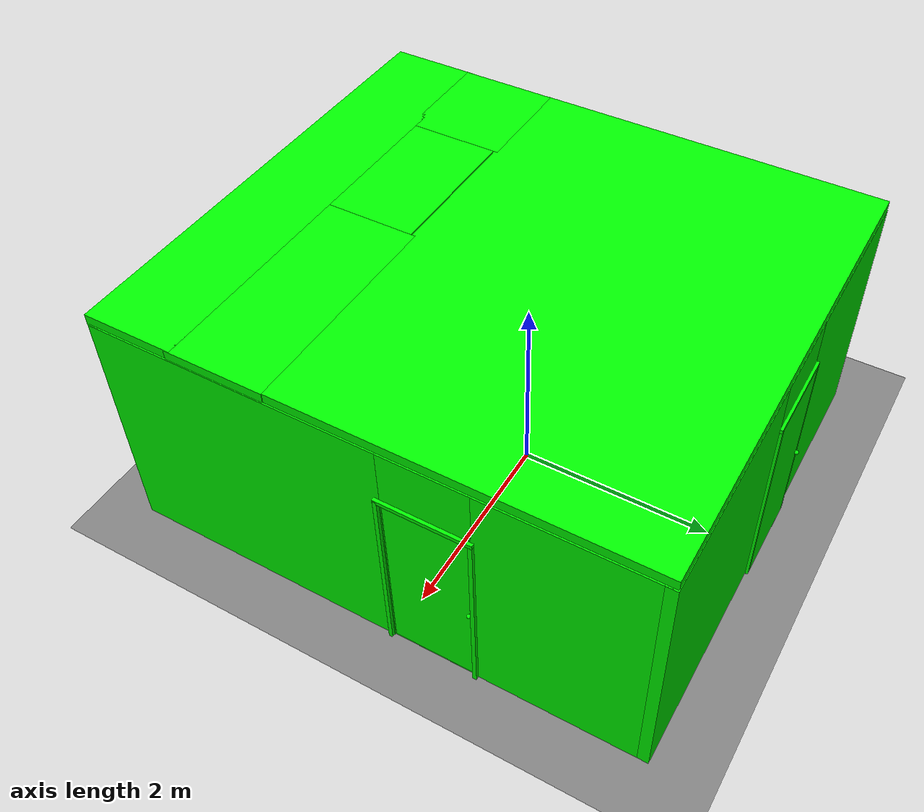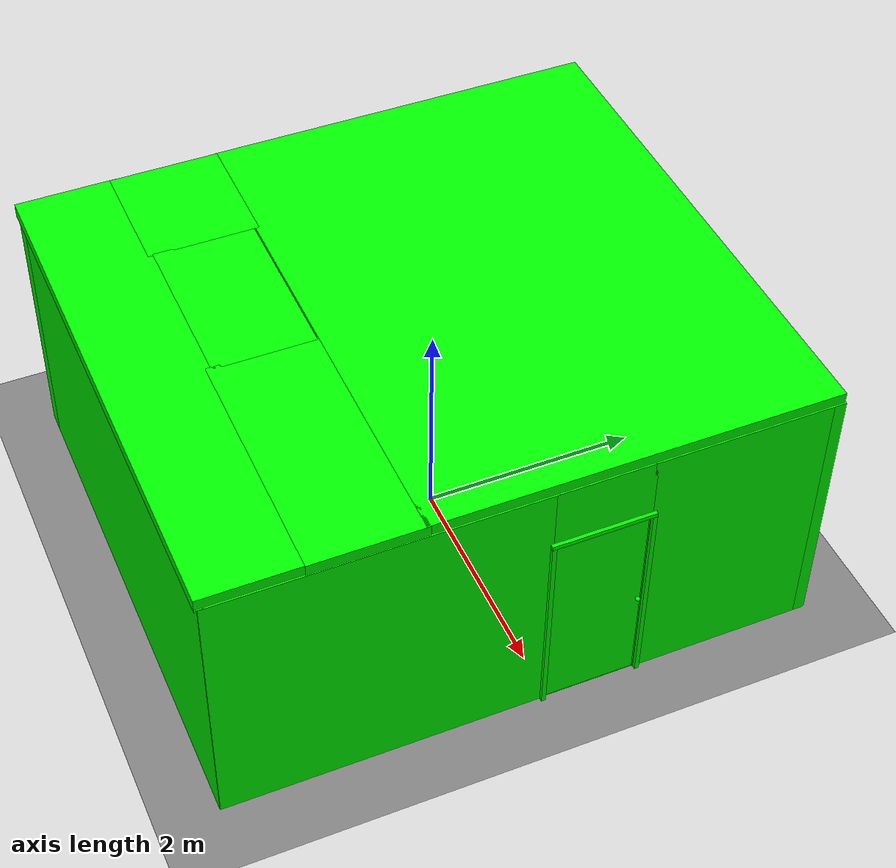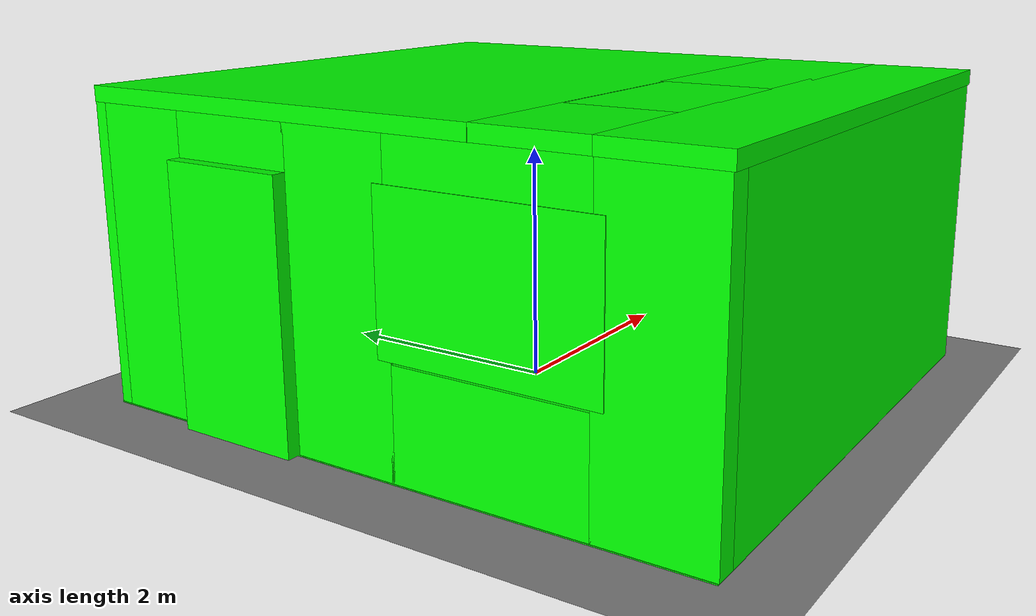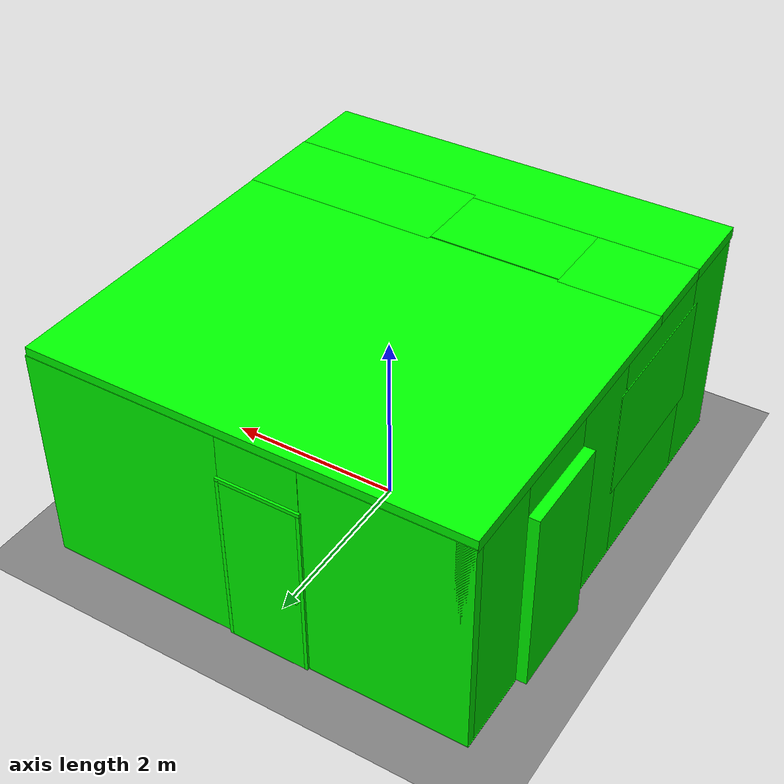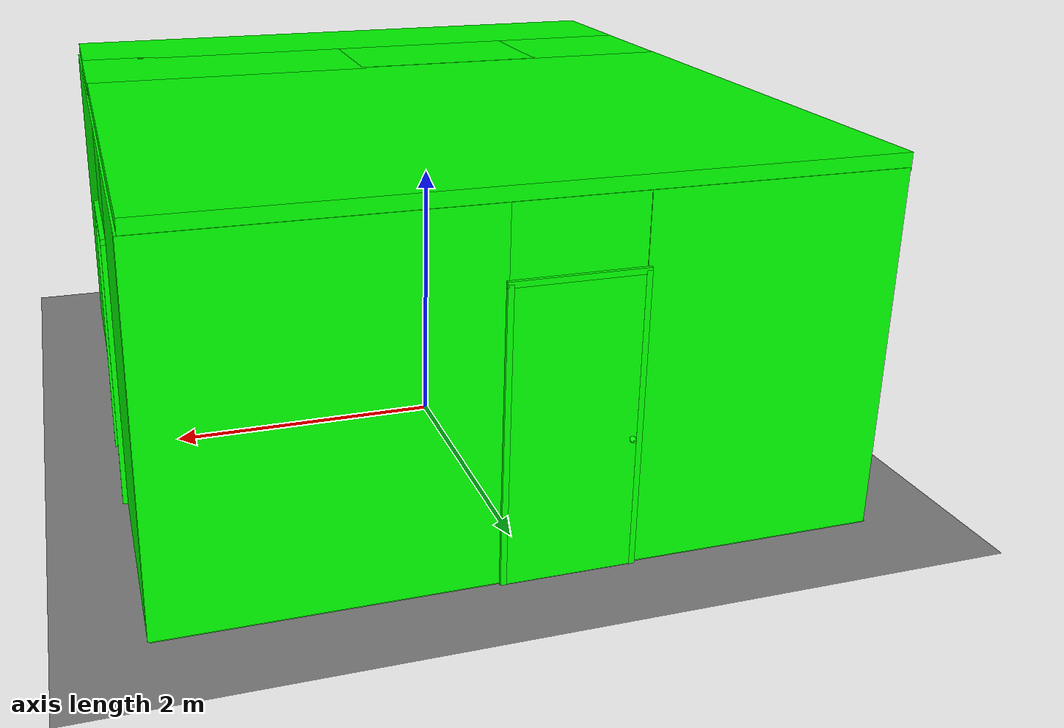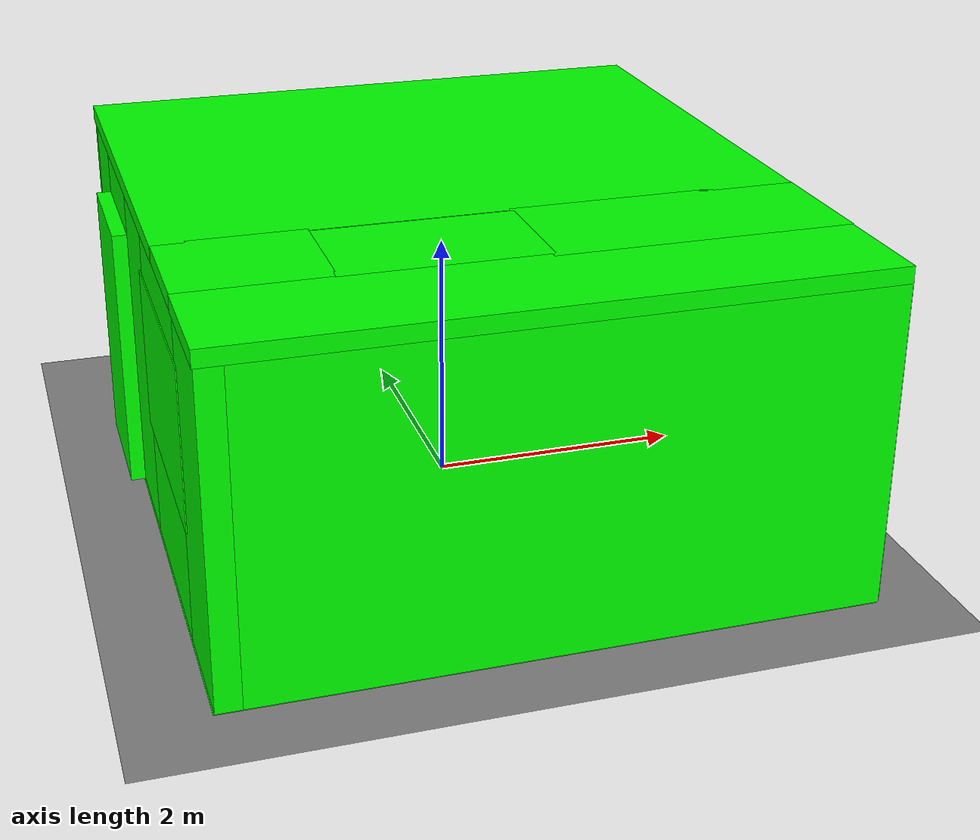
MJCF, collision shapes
<mujoco model="FloorPlan1_physics_simple">
  <!--Auto-generated from FloorPlan1_physics.xml: non-static objects removed; dynamic/articulable collisions disabled.-->
  <compiler angle="radian" autolimits="true" boundmass="0" balanceinertia="true" />
  <option impratio="10" gravity="0 0 -9.8" integrator="implicitfast" cone="elliptic" jacobian="sparse" noslip_iterations="4">
    <flag energy="enable" multiccd="enable" contact="enable" warmstart="enable" />
  </option>
  <size njmax="5000" nconmax="5000" />
  <visual>
    <global offwidth="1280" offheight="720" />
    <quality shadowsize="16384" />
    <headlight ambient="0.35 0.35 0.35" />
    <map znear="0.001" />
    <scale contactwidth="0.0607382" contactheight="0.0607382" jointlength="0.485905" jointwidth="0.0607382" framelength="0.364429" framewidth="0.0303691" />
  </visual>
  <default>
    <default class="/">
      <default class="__VISUAL_MJT__">
        <geom contype="0" conaffinity="0" group="0" mass="1e-08" />
      </default>
      <default class="__STRUCTURAL_MJT__">
        <geom contype="8" conaffinity="15" group="4" friction="0.9 0.9 0.001" solref="0.025 1.0" solimp="0.998 0.998 0.001 0.5 2.0" density="500.0" />
        <default class="__STRUCTURAL_WALL_MJT__">
          <geom group="3" />
        </default>
      </default>
      <default class="__DYNAMIC_MJT__">
        <geom conaffinity="0" group="4" friction="0.9 0.9 0.001" solref="0.025 1.0" solimp="0.998 0.998 0.001 0.5 2.0" density="500.0" contype="0" />
      </default>
      <default class="__ARTICULABLE_DYNAMIC_MJT__">
        <geom contype="0" conaffinity="0" group="4" friction="0.9 0.9 0.001" solref="0.025 1.0" solimp="0.998 0.998 0.001 0.5 2.0" density="500.0" />
      </default>
    </default>
  </default>
  <asset>
    <texture type="2d" name="HammeredMetal_AlbedoTransparency" file="FloorPlan1_physics/Dishwasher/dishwasher_FP1/HammeredMetal_MetallicSmoothness.png" />
    <texture type="2d" name="BrushedIron_AlbedoTransparency" file="FloorPlan1_physics/Oven/oven_FP1/BrushedIron_AlbedoTransparency.png" />
    <texture type="2d" name="SpongeGreenYellow" file="../objects/thor/Kitchen Objects/DishSponge/Prefabs/Dish_Sponge_1/SpongeGreenYellow.png" />
    <texture type="2d" name="Labels" file="../objects/thor/Kitchen Objects/WineBottle/Prefabs/Wine_Bottle_1/Labels.png" />
    <texture type="2d" name="Paper_Towel_Mat" file="../objects/thor/Kitchen Objects/PaperTowel/Prefabs/Paper_Towel_1/PaperRollDIF.png" />
    <texture type="2d" name="BrushedAluminum_AlbedoTransparency" file="../objects/thor/Kitchen Objects/ButterKnife/Prefab/ButterKnife_1/BrushedAluminum_AlbedoTransparency.png" />
    <texture type="2d" name="Pot_Detail_Mat" file="../objects/thor/Kitchen Objects/Pot/Prefabs/Pot_19/BrushedIron_AlbedoTransparency.png" />
    <texture type="2d" name="Bin_Secondary1_Mat" file="../objects/thor/Kitchen Objects/GarbageCan/Prefabs/bin_1/BrushedAluminum_AlbedoTransparency.png" />
    <texture type="2d" name="Coffee_Machine_Decal_Mat" file="../objects/thor/Kitchen Objects/CoffeeMachine/Prefabs/coffee_machine_1/Coffee_Machine_Decal_AlbedoTransparency.png" />
    <texture type="2d" name="Coffee_Machine_Metal_Mat" file="../objects/thor/Kitchen Objects/CoffeeMachine/Prefabs/coffee_machine_1/MetalBumpy_AlbedoTransparency.png" />
    <texture type="2d" name="Coffee_Machine_Secondary1_Color_Mat" file="../objects/thor/Kitchen Objects/CoffeeMachine/Prefabs/coffee_machine_1/BrushedIron_AlbedoTransparency.png" />
    <texture type="2d" name="Coffee_Machine_Primary1_Color_Mat" file="../objects/thor/Kitchen Objects/CoffeeMachine/Prefabs/coffee_machine_1/BumpyPlastic_Albedo.png" />
    <texture type="2d" name="HammeredMetal_AlbedoTransparency_2" file="FloorPlan1_physics/Cabinet/Cabinet_7d7a3425/HammeredMetal_AlbedoTransparency.png" />
    <texture type="2d" name="Fridge_Metal_Mat" file="../objects/thor/Kitchen Objects/Fridge/Prefabs/Fridge_1/BrushedAluminum_AlbedoTransparency.png" />
    <texture type="2d" name="Fridge_Secondary1_Mat" file="../objects/thor/Kitchen Objects/Fridge/Prefabs/Fridge_1/BrushedAluminum_AlbedoTransparency.png" />
    <texture type="2d" name="Fridge_Decal_Mat" file="../objects/thor/Kitchen Objects/Fridge/Prefabs/Fridge_1/Fridge_Decal_AlbedoTransparency.png" />
    <texture type="2d" name="Microwave_Decal_Mat" file="../objects/thor/Kitchen Objects/Microwave/Prefabs/Microwave_1/Microwave_Decal_AlbedoTransparency.png" />
    <texture type="2d" name="Microwave_Metal_Mat" file="../objects/thor/Kitchen Objects/Microwave/Prefabs/Microwave_1/BrushedIron_AlbedoTransparency.png" />
    <texture type="2d" name="Microwave_Primary1_Mat" file="../objects/thor/Kitchen Objects/Microwave/Prefabs/Microwave_1/HammeredMetal_AlbedoTransparency.png" />
    <texture type="2d" name="Microwave_Window1_Off_Mat" file="../objects/thor/Kitchen Objects/Microwave/Prefabs/Microwave_1/Microwave_Window_AlbedoTransparency.png" />
    <texture type="2d" name="Toaster_Decal_Mat" file="../objects/thor/Kitchen Objects/Toaster/Prefabs/Toaster_1/Toaster_Decal_AlbedoTransparency.png" />
    <texture type="2d" name="Toaster_Metal_Mat" file="../objects/thor/Kitchen Objects/Toaster/Prefabs/Toaster_1/HammeredMetal_AlbedoTransparency.png" />
    <texture type="2d" name="Toaster_Primary1_Mat" file="../objects/thor/Kitchen Objects/Toaster/Prefabs/Toaster_1/MetalBumpy_AlbedoTransparency.png" />
    <texture type="2d" name="WornWood" file="../objects/thor/Common Objects/ShelvingUnit/Prefabs/Shelving_Unit_001_1/TexturesCom_WornWood2_albedo_S.png" />
    <texture type="2d" name="Apple1_Mat1" file="../objects/thor/Kitchen Objects/Apple/Prefabs/Apple_1/Apple1_AlbedoTransparency1.png" />
    <texture type="2d" name="HousePlant_Leaves1A_Mat" file="../objects/thor/Living Room Objects/HousePlant/Prefabs/Houseplant_1/HousePlant5_DefaultMaterial_AlbedoTransparency.png" />
    <texture type="2d" name="HousePlant_Pot_Primary1_Mat" file="../objects/thor/Living Room Objects/HousePlant/Prefabs/Houseplant_1/Carpet1.png" />
    <texture type="2d" name="Lettuce1_Mat" file="../objects/thor/Kitchen Objects/Lettuce/Prefabs/Lettuce_1/Lettuce1_AlbedoTransparency.png" />
    <texture type="2d" name="Bread1_Mat1" file="../objects/thor/Kitchen Objects/Bread/Prefabs/Bread_1/Bread1_AlbedoTransparency.png" />
    <texture type="2d" name="PepperNoise" file="../objects/thor/Kitchen Objects/Pepper_Shaker/Prefabs/Pepper_Shaker_1/PepperNoise.png" />
    <texture type="2d" name="Tomato1_Mat1" file="../objects/thor/Kitchen Objects/Tomato/Prefabs/Tomato_1/Tomato1_AlbedoTransparency.png" />
    <texture type="2d" name="Cup1_Mat" file="../objects/thor/Kitchen Objects/Cup/Prefabs/Cup_1/BrushedIron_AlbedoTransparency.png" />
    <texture type="2d" name="Potato1_Mat1" file="../objects/thor/Kitchen Objects/Potato/Prefabs/Potato_1/Potato1_AlbedoTransparency.png" />
    <texture type="2d" name="Pan_Detail_Mat" file="../objects/thor/Kitchen Objects/Pan/Prefabs/Pan_22/BrushedIron_AlbedoTransparency.png" />
    <texture type="2d" name="Book_Pages_1_Mat" file="../objects/thor/Bedroom Objects/Book/Prefabs/Book_1/Book_Pages_AlbedoTransparency.png" />
    <texture type="2d" name="Book_Text_Mat" file="../objects/thor/Bedroom Objects/Book/Prefabs/Book_1/Book_Text_AlbedoTransparency.png" />
    <texture type="2d" name="Book_Cover_Mat" file="../objects/thor/Bedroom Objects/Book/Prefabs/Book_1/Book_Cover_AlbedoTransparency.png" />
    <texture type="2d" name="TexturesCom_WoodFine0038_1_seamless_S" file="FloorPlan1_physics/Structural/mesh_72f6a7fa/TexturesCom_WoodFine0038_1_seamless_albedo_S.png" />
    <texture type="2d" name="DarkWoodSmooth" file="FloorPlan1_physics/Structural/StandardIslandHeight_c3ccfdb2/WoodGrains1.png" />
    <texture type="2d" name="LightWhite" file="FloorPlan1_physics/Structural/StandardIslandHeight_c3ccfdb2/TexturesCom_MarbleNoisy0062_1_seamless_S.png" />
    <texture type="2d" name="Drywall3" file="FloorPlan1_physics/Structural/Ceiling_70a7ead7/WallDrywallWhite.png" />
    <texture type="2d" name="Copper_AlbedoTransparency" file="FloorPlan1_physics/Structural/StandardKnob1_382240c9/Copper_AlbedoTransparency.png" />
    <texture type="2d" name="YellowDrywall" file="FloorPlan1_physics/Structural/Wall_ad20b7dd/WallDrywallWhite.png" />
    <texture type="2d" name="SubwayTilesAO" file="../objects/thor/Textures/SubwayTilesAO.png" />
    <material name="material_FloorKitchen1Texturetest_DefaultMaterial_MetallicSmoothness_mat" />
    <material name="material_HammeredMetal_AlbedoTransparency" texture="HammeredMetal_AlbedoTransparency" />
    <material name="material_StoveDarkMat" rgba="0.125 0.125 0.125 1" />
    <material name="material_BrushedIron_AlbedoTransparency" texture="BrushedIron_AlbedoTransparency" />
    <material name="material_Glass_Green_Mat" rgba="0.170307 0.257353 0.178111 0.797" />
    <material name="material_Glass_Detailed_White_Mat" rgba="1 1 1 0.5" />
    <material name="material_Porcelain_Red_Mat" rgba="0.830882 0 0 1" />
    <material name="material_GreyCountertop" rgba="0.610294 0.610294 0.610294 1" />
    <material name="material_Glass_Detailed_Frosted_Mat" rgba="0.477941 0.477941 0.477941 0.5" />
    <material name="material_Bowl_Decals_Off_Mat" rgba="1 1 1 0.5" />
    <material name="material_Bowl_Mat1" rgba="0.551471 0.551471 0.551471 1" />
    <material name="material_SpongeGreenYellow" texture="SpongeGreenYellow" />
    <material name="material_Labels" texture="Labels" />
    <material name="material_Glass_Detailed_Green_Mat" rgba="0.0429006 0.132353 0 0.484" />
    <material name="material_Paper_Towel_Mat" texture="Paper_Towel_Mat" />
    <material name="material_BlueRubber" rgba="0.0116782 0.0448335 0.264706 1" />
    <material name="material_BrushedAluminum_AlbedoTransparency" texture="BrushedAluminum_AlbedoTransparency" />
    <material name="material_Pot_Pan_Decals_Off_Mat" rgba="1 1 1 0.5" />
    <material name="material_Pot_Glass_Mat" rgba="0.786765 0.786765 0.786765 0.434" />
    <material name="material_Pot_Detail_Mat" texture="Pot_Detail_Mat" />
    <material name="material_Pot_Secondary1_Mat" rgba="0.441177 0.441177 0.441177 1" />
    <material name="material_Pot_Primary1_Mat" rgba="0.595588 0.595588 0.595588 1" />
    <material name="material_Material.003" rgba="0.098505 0.098505 0.098505 1" />
    <material name="material_Mug_Decals_Off_Mat" rgba="1 1 1 0.5" />
    <material name="material_Porcelain_Off_White_Mat" rgba="0.852941 0.852941 0.852941 1" />
    <material name="material_Bin_Secondary1_Mat" texture="Bin_Secondary1_Mat" rgba="0.441177 0.441177 0.441177 1" />
    <material name="material_Bin_Primary1_Mat" rgba="0.0735294 0.0735294 0.0735294 1" />
    <material name="material_Light_Switch_Hole_Mat" rgba="0 0 0 1" />
    <material name="material_Light_Switch_Secondary_Mat" rgba="0.955882 0.955882 0.955882 1" />
    <material name="material_Light_Switch_Primary1_Mat" rgba="0.963235 0.963235 0.963235 1" />
    <material name="material_coffee_machine_backup_mat" rgba="0.5 0.5 0.5 1" />
    <material name="material_Coffee_Machine_Readout_Mat_Off" rgba="0 0 0 1" />
    <material name="material_Coffee_Machine_Decal_Mat" texture="Coffee_Machine_Decal_Mat" />
    <material name="material_Coffee_Machine_Metal_Mat" texture="Coffee_Machine_Metal_Mat" rgba="0.661765 0.661765 0.661765 1" />
    <material name="material_Coffee_Machine_Secondary1_Color_Mat" texture="Coffee_Machine_Secondary1_Color_Mat" rgba="0.514706 0.514706 0.514706 1" />
    <material name="material_Coffee_Machine_Primary1_Color_Mat" texture="Coffee_Machine_Primary1_Color_Mat" rgba="0.234375 0.340909 0.625 1" />
    <material name="material_WhiteWoodClean" />
    <material name="material_HammeredMetal_AlbedoTransparency_2" texture="HammeredMetal_AlbedoTransparency_2" rgba="1 0.934077 0.816176 1" />
    <material name="material_Default-Material" />
    <material name="material_Metal" />
    <material name="material_YellowPlastic" rgba="1 0.88925 0.426471 1" />
    <material name="material_Fridge_Window_Mat" rgba="0.397059 0.397059 0.397059 0.166" />
    <material name="material_Fridge_Interior1_Mat" rgba="0.801471 0.801471 0.801471 1" />
    <material name="material_Fridge_Metal_Mat" texture="Fridge_Metal_Mat" rgba="0.875 0.875 0.875 1" />
    <material name="material_Fridge_Secondary1_Mat" texture="Fridge_Secondary1_Mat" rgba="0.830882 0.830882 0.830882 1" />
    <material name="material_Fridge_Primary1_Mat" />
    <material name="material_Fridge_Decal_Mat" texture="Fridge_Decal_Mat" />
    <material name="material_Microwave_Readout2B_Off_Mat" rgba="0 0 0 1" />
    <material name="material_Microwave_Decal_Mat" texture="Microwave_Decal_Mat" />
    <material name="material_Microwave_Interior2_Mat" rgba="0.602941 0.602941 0.602941 1" />
    <material name="material_Microwave_Plate1_Mat" rgba="0.303039 0.347235 0.433823 1" />
    <material name="material_Microwave_Metal_Mat" texture="Microwave_Metal_Mat" />
    <material name="material_Microwave_Secondary1_Mat" rgba="0.360294 0.360294 0.360294 1" />
    <material name="material_Microwave_Primary1_Mat" texture="Microwave_Primary1_Mat" rgba="0.565717 0.566176 0.55785 1" />
    <material name="material_Microwave_Window1_Off_Mat" texture="Microwave_Window1_Off_Mat" />
    <material name="material_Toaster_Coils_Off_Mat" rgba="0.160377 0.160377 0.160377 1" />
    <material name="material_Toaster_Decal_Mat" texture="Toaster_Decal_Mat" />
    <material name="material_Toaster_Interior_Mat" rgba="0 0 0 1" />
    <material name="material_Toaster_Metal_Mat" texture="Toaster_Metal_Mat" rgba="0.338235 0.320826 0.320826 1" />
    <material name="material_Toaster_Secondary1_Mat" rgba="0.0483076 0.0475208 0.0537975 1" />
    <material name="material_Toaster_Primary1_Mat" texture="Toaster_Primary1_Mat" rgba="0.860294 0.41117 0.41117 1" />
    <material name="material_BlackWood" rgba="0.147059 0.147059 0.147059 1" />
    <material name="material_WornWood" texture="WornWood" rgba="0.514706 0.391197 0.170307 1" />
    <material name="material_Apple1_Mat1" texture="Apple1_Mat1" />
    <material name="material_HousePlant_Pot_Secondary1_Mat" rgba="0.00735295 0.00735295 0.00735295 1" />
    <material name="material_HousePlant_Leaves1A_Mat" texture="HousePlant_Leaves1A_Mat" rgba="0.830882 0.830882 0.830882 1" />
    <material name="material_HousePlant_Pot_Primary1_Mat" texture="HousePlant_Pot_Primary1_Mat" rgba="0.573529 0.242312 0.0590398 1" />
    <material name="material_Lettuce1_Mat" texture="Lettuce1_Mat" rgba="0.994523 1 0.602941 1" />
    <material name="material_Bread1_Mat1" texture="Bread1_Mat1" />
    <material name="material_Glass_Detailed_Lit_Medium_Mat" rgba="1 1 1 0.5" />
    <material name="material_PepperNoise" texture="PepperNoise" rgba="0.522059 0.477583 0.429931 1" />
    <material name="material_SaltNoise" rgba="0.889706 0.889706 0.889706 1" />
    <material name="material_Soap_Bottle_Tube_Mat" rgba="0.669118 0.669118 0.669118 0.5" />
    <material name="material_Soap_Bottle_Secondary1_Mat" rgba="0.729412 0.498039 0 1" />
    <material name="material_Soap_Bottle_Primary1_Mat" rgba="0.349057 0.349057 0.349057 0.403922" />
    <material name="material_Soap_Bottle_Filling1_mat" rgba="0.166523 0.527753 0.647059 0.416" />
    <material name="material_Tomato1_Mat1" texture="Tomato1_Mat1" />
    <material name="material_Egg1_Mat" rgba="0.960784 0.647059 0.47451 1" />
    <material name="material_Cup_Decals_Off_Mat" rgba="1 1 1 0.5" />
    <material name="material_Cup1_Mat" texture="Cup1_Mat" rgba="0.866667 0.866667 0.866667 0.5" />
    <material name="material_Plate_Decals_Off_Mat" rgba="1 1 1 0.5" />
    <material name="material_Plate_Mat1" rgba="0.889706 0.889706 0.889706 1" />
    <material name="material_Potato1_Mat1" texture="Potato1_Mat1" />
    <material name="material_Pan_Detail_Mat" texture="Pan_Detail_Mat" rgba="0.345588 0.345588 0.345588 1" />
    <material name="material_Pan_Secondary1_Mat" rgba="0.367647 0.367647 0.367647 1" />
    <material name="material_Pan_Primary1_Mat" rgba="0.595588 0.595588 0.595588 1" />
    <material name="material_Book_Pages_1_Mat" texture="Book_Pages_1_Mat" />
    <material name="material_Book_Text_Mat" texture="Book_Text_Mat" />
    <material name="material_Book_Cover_Mat" texture="Book_Cover_Mat" />
    <material name="material_BlackPlastic" rgba="0.198529 0.198529 0.198529 1" />
    <material name="material_TexturesCom_WoodFine0038_1_seamless_S" texture="TexturesCom_WoodFine0038_1_seamless_S" />
    <material name="material_WhitePlastic" />
    <material name="material_DarkWoodSmooth" texture="DarkWoodSmooth" rgba="0.235849 0.130508 0.0767622 1" />
    <material name="material_LightWhite" texture="LightWhite" rgba="0.889706 0.889706 0.889706 1" />
    <material name="material_PureBlack_Wood" rgba="0 0 0 1" />
    <material name="material_Drywall3" texture="Drywall3" />
    <material name="material_Copper_AlbedoTransparency" texture="Copper_AlbedoTransparency" />
    <material name="material_WhiteWood1" />
    <material name="material_YellowDrywall" texture="YellowDrywall" rgba="1 0.771052 0.360294 1" />
    <material name="material_SubwayTilesAO" texture="SubwayTilesAO" />
    <material name="material_ToasterDarkMat" rgba="0.0483076 0.0475208 0.0537975 1" />
    <material name="material_Light" rgba="1 0.944118 0.860294 1" />
    <mesh name="dishwasher_FP1_dishwasher_FP1_6ce43914_0" file="FloorPlan1_physics/Dishwasher/dishwasher_FP1/dishwasher_FP1_dishwasher_FP1_6ce43914/dishwasher_FP1_dishwasher_FP1_6ce43914_0.obj" inertia="shell" />
    <mesh name="dishwasher_FP1_dishwasher_FP1_6ce43914_1" file="FloorPlan1_physics/Dishwasher/dishwasher_FP1/dishwasher_FP1_dishwasher_FP1_6ce43914/dishwasher_FP1_dishwasher_FP1_6ce43914_1.obj" inertia="shell" />
    <mesh name="dishwasher_FP1_dishwasher_door_FP1_95ee9ec4_0" file="FloorPlan1_physics/Dishwasher/dishwasher_FP1/dishwasher_FP1_dishwasher_door_FP1_95ee9ec4/dishwasher_FP1_dishwasher_door_FP1_95ee9ec4_0.obj" />
    <mesh name="dishwasher_FP1_dishwasher_door_FP1_95ee9ec4_1" file="FloorPlan1_physics/Dishwasher/dishwasher_FP1/dishwasher_FP1_dishwasher_door_FP1_95ee9ec4/dishwasher_FP1_dishwasher_door_FP1_95ee9ec4_1.obj" />
    <mesh name="dishwasher_FP1_dishwasher_FP1_door_handle" file="FloorPlan1_physics/Dishwasher/dishwasher_FP1/dishwasher_FP1_dishwasher_FP1_door_handle/dishwasher_FP1_dishwasher_FP1_door_handle.obj" />
    <mesh name="oven_FP1_oven_FP1_e2968b02" file="FloorPlan1_physics/Oven/oven_FP1/oven_FP1_oven_FP1_e2968b02/oven_FP1_oven_FP1_e2968b02.obj" />
    <mesh name="oven_FP1_oven_FP1_drawer_31534942" file="FloorPlan1_physics/Oven/oven_FP1/oven_FP1_oven_FP1_drawer_31534942/oven_FP1_oven_FP1_drawer_31534942.obj" />
    <mesh name="oven_FP1_oven_FP1_drawer_handle" file="FloorPlan1_physics/Oven/oven_FP1/oven_FP1_oven_FP1_drawer_handle/oven_FP1_oven_FP1_drawer_handle.obj" />
    <mesh name="oven_FP1_oven_FP1_door_049ab45b_0" file="FloorPlan1_physics/Oven/oven_FP1/oven_FP1_oven_FP1_door_049ab45b/oven_FP1_oven_FP1_door_049ab45b_0.obj" />
    <mesh name="oven_FP1_oven_FP1_door_049ab45b_1" file="FloorPlan1_physics/Oven/oven_FP1/oven_FP1_oven_FP1_door_049ab45b/oven_FP1_oven_FP1_door_049ab45b_1.obj" inertia="shell" />
    <mesh name="oven_FP1_oven_FP1_door_049ab45b_2" file="FloorPlan1_physics/Oven/oven_FP1/oven_FP1_oven_FP1_door_049ab45b/oven_FP1_oven_FP1_door_049ab45b_2.obj" />
    <mesh name="oven_FP1_oven_FP1_door_handle" file="FloorPlan1_physics/Oven/oven_FP1/oven_FP1_oven_FP1_door_handle/oven_FP1_oven_FP1_door_handle.obj" />
    <mesh name="Bottle_1_bottle_1" file="../objects/thor/Kitchen Objects/Bottle/Prefabs/Bottle_1/Bottle_1_bottle_1/Bottle_1_bottle_1.obj" />
    <mesh name="Bottle_1_bottle_1_collision_15" file="../objects/thor/Kitchen Objects/Bottle/Prefabs/Bottle_1/Bottle_1_bottle_1/Bottle_1_bottle_1/Bottle_1_bottle_1_collision_15.obj" />
    <mesh name="Bottle_1_bottle_1_collision_21" file="../objects/thor/Kitchen Objects/Bottle/Prefabs/Bottle_1/Bottle_1_bottle_1/Bottle_1_bottle_1/Bottle_1_bottle_1_collision_21.obj" />
    <mesh name="Bottle_1_bottle_1_collision_0" file="../objects/thor/Kitchen Objects/Bottle/Prefabs/Bottle_1/Bottle_1_bottle_1/Bottle_1_bottle_1/Bottle_1_bottle_1_collision_0.obj" />
    <mesh name="Bottle_1_bottle_1_collision_13" file="../objects/thor/Kitchen Objects/Bottle/Prefabs/Bottle_1/Bottle_1_bottle_1/Bottle_1_bottle_1/Bottle_1_bottle_1_collision_13.obj" />
    <mesh name="Bottle_1_bottle_1_collision_2" file="../objects/thor/Kitchen Objects/Bottle/Prefabs/Bottle_1/Bottle_1_bottle_1/Bottle_1_bottle_1/Bottle_1_bottle_1_collision_2.obj" />
    <mesh name="Bottle_1_bottle_1_collision_8" file="../objects/thor/Kitchen Objects/Bottle/Prefabs/Bottle_1/Bottle_1_bottle_1/Bottle_1_bottle_1/Bottle_1_bottle_1_collision_8.obj" />
    <mesh name="Bottle_1_bottle_1_collision_24" file="../objects/thor/Kitchen Objects/Bottle/Prefabs/Bottle_1/Bottle_1_bottle_1/Bottle_1_bottle_1/Bottle_1_bottle_1_collision_24.obj" />
    <mesh name="Bottle_1_bottle_1_collision_5" file="../objects/thor/Kitchen Objects/Bottle/Prefabs/Bottle_1/Bottle_1_bottle_1/Bottle_1_bottle_1/Bottle_1_bottle_1_collision_5.obj" />
    <mesh name="Bottle_1_bottle_1_collision_18" file="../objects/thor/Kitchen Objects/Bottle/Prefabs/Bottle_1/Bottle_1_bottle_1/Bottle_1_bottle_1/Bottle_1_bottle_1_collision_18.obj" />
    <mesh name="Bottle_1_bottle_1_collision_10" file="../objects/thor/Kitchen Objects/Bottle/Prefabs/Bottle_1/Bottle_1_bottle_1/Bottle_1_bottle_1/Bottle_1_bottle_1_collision_10.obj" />
    <mesh name="Bottle_1_bottle_1_collision_16" file="../objects/thor/Kitchen Objects/Bottle/Prefabs/Bottle_1/Bottle_1_bottle_1/Bottle_1_bottle_1/Bottle_1_bottle_1_collision_16.obj" />
    <mesh name="Bottle_1_bottle_1_collision_14" file="../objects/thor/Kitchen Objects/Bottle/Prefabs/Bottle_1/Bottle_1_bottle_1/Bottle_1_bottle_1/Bottle_1_bottle_1_collision_14.obj" />
    <mesh name="Bottle_1_bottle_1_collision_9" file="../objects/thor/Kitchen Objects/Bottle/Prefabs/Bottle_1/Bottle_1_bottle_1/Bottle_1_bottle_1/Bottle_1_bottle_1_collision_9.obj" />
    <mesh name="Bottle_1_bottle_1_collision_12" file="../objects/thor/Kitchen Objects/Bottle/Prefabs/Bottle_1/Bottle_1_bottle_1/Bottle_1_bottle_1/Bottle_1_bottle_1_collision_12.obj" />
    <mesh name="Bottle_1_bottle_1_collision_7" file="../objects/thor/Kitchen Objects/Bottle/Prefabs/Bottle_1/Bottle_1_bottle_1/Bottle_1_bottle_1/Bottle_1_bottle_1_collision_7.obj" />
    <mesh name="Bottle_1_bottle_1_collision_17" file="../objects/thor/Kitchen Objects/Bottle/Prefabs/Bottle_1/Bottle_1_bottle_1/Bottle_1_bottle_1/Bottle_1_bottle_1_collision_17.obj" />
    <mesh name="Bottle_1_bottle_1_collision_4" file="../objects/thor/Kitchen Objects/Bottle/Prefabs/Bottle_1/Bottle_1_bottle_1/Bottle_1_bottle_1/Bottle_1_bottle_1_collision_4.obj" />
    <mesh name="Bottle_1_bottle_1_collision_1" file="../objects/thor/Kitchen Objects/Bottle/Prefabs/Bottle_1/Bottle_1_bottle_1/Bottle_1_bottle_1/Bottle_1_bottle_1_collision_1.obj" />
    <mesh name="Bottle_1_bottle_1_collision_6" file="../objects/thor/Kitchen Objects/Bottle/Prefabs/Bottle_1/Bottle_1_bottle_1/Bottle_1_bottle_1/Bottle_1_bottle_1_collision_6.obj" />
    <mesh name="Bottle_1_bottle_1_collision_3" file="../objects/thor/Kitchen Objects/Bottle/Prefabs/Bottle_1/Bottle_1_bottle_1/Bottle_1_bottle_1/Bottle_1_bottle_1_collision_3.obj" />
    <mesh name="Bottle_1_bottle_1_collision_23" file="../objects/thor/Kitchen Objects/Bottle/Prefabs/Bottle_1/Bottle_1_bottle_1/Bottle_1_bottle_1/Bottle_1_bottle_1_collision_23.obj" />
    <mesh name="Bottle_1_bottle_1_collision_11" file="../objects/thor/Kitchen Objects/Bottle/Prefabs/Bottle_1/Bottle_1_bottle_1/Bottle_1_bottle_1/Bottle_1_bottle_1_collision_11.obj" />
    <mesh name="Bottle_1_bottle_1_collision_20" file="../objects/thor/Kitchen Objects/Bottle/Prefabs/Bottle_1/Bottle_1_bottle_1/Bottle_1_bottle_1/Bottle_1_bottle_1_collision_20.obj" />
    <mesh name="Bottle_1_bottle_1_collision_22" file="../objects/thor/Kitchen Objects/Bottle/Prefabs/Bottle_1/Bottle_1_bottle_1/Bottle_1_bottle_1/Bottle_1_bottle_1_collision_22.obj" />
    <mesh name="Bottle_1_bottle_1_collision_19" file="../objects/thor/Kitchen Objects/Bottle/Prefabs/Bottle_1/Bottle_1_bottle_1/Bottle_1_bottle_1/Bottle_1_bottle_1_collision_19.obj" />
    <mesh name="Vase_Flat_2_vase_flat" file="../objects/thor/Miscellaneous Objects/Vase/Prefabs/Vase_Flat_2/Vase_Flat_2_vase_flat/Vase_Flat_2_vase_flat.obj" />
    <mesh name="Vase_Flat_2_vase_flat_collision_13" file="../objects/thor/Miscellaneous Objects/Vase/Prefabs/Vase_Flat_2/Vase_Flat_2_vase_flat/Vase_Flat_2_vase_flat/Vase_Flat_2_vase_flat_collision_13.obj" />
    <mesh name="Vase_Flat_2_vase_flat_collision_1" file="../objects/thor/Miscellaneous Objects/Vase/Prefabs/Vase_Flat_2/Vase_Flat_2_vase_flat/Vase_Flat_2_vase_flat/Vase_Flat_2_vase_flat_collision_1.obj" />
    <mesh name="Vase_Flat_2_vase_flat_collision_2" file="../objects/thor/Miscellaneous Objects/Vase/Prefabs/Vase_Flat_2/Vase_Flat_2_vase_flat/Vase_Flat_2_vase_flat/Vase_Flat_2_vase_flat_collision_2.obj" />
    <mesh name="Vase_Flat_2_vase_flat_collision_5" file="../objects/thor/Miscellaneous Objects/Vase/Prefabs/Vase_Flat_2/Vase_Flat_2_vase_flat/Vase_Flat_2_vase_flat/Vase_Flat_2_vase_flat_collision_5.obj" />
    <mesh name="Vase_Flat_2_vase_flat_collision_24" file="../objects/thor/Miscellaneous Objects/Vase/Prefabs/Vase_Flat_2/Vase_Flat_2_vase_flat/Vase_Flat_2_vase_flat/Vase_Flat_2_vase_flat_collision_24.obj" />
    <mesh name="Vase_Flat_2_vase_flat_collision_21" file="../objects/thor/Miscellaneous Objects/Vase/Prefabs/Vase_Flat_2/Vase_Flat_2_vase_flat/Vase_Flat_2_vase_flat/Vase_Flat_2_vase_flat_collision_21.obj" />
    <mesh name="Vase_Flat_2_vase_flat_collision_19" file="../objects/thor/Miscellaneous Objects/Vase/Prefabs/Vase_Flat_2/Vase_Flat_2_vase_flat/Vase_Flat_2_vase_flat/Vase_Flat_2_vase_flat_collision_19.obj" />
    <mesh name="Vase_Flat_2_vase_flat_collision_18" file="../objects/thor/Miscellaneous Objects/Vase/Prefabs/Vase_Flat_2/Vase_Flat_2_vase_flat/Vase_Flat_2_vase_flat/Vase_Flat_2_vase_flat_collision_18.obj" />
    <mesh name="Vase_Flat_2_vase_flat_collision_3" file="../objects/thor/Miscellaneous Objects/Vase/Prefabs/Vase_Flat_2/Vase_Flat_2_vase_flat/Vase_Flat_2_vase_flat/Vase_Flat_2_vase_flat_collision_3.obj" />
    <mesh name="Vase_Flat_2_vase_flat_collision_7" file="../objects/thor/Miscellaneous Objects/Vase/Prefabs/Vase_Flat_2/Vase_Flat_2_vase_flat/Vase_Flat_2_vase_flat/Vase_Flat_2_vase_flat_collision_7.obj" />
    <mesh name="Vase_Flat_2_vase_flat_collision_4" file="../objects/thor/Miscellaneous Objects/Vase/Prefabs/Vase_Flat_2/Vase_Flat_2_vase_flat/Vase_Flat_2_vase_flat/Vase_Flat_2_vase_flat_collision_4.obj" />
    <mesh name="Vase_Flat_2_vase_flat_collision_16" file="../objects/thor/Miscellaneous Objects/Vase/Prefabs/Vase_Flat_2/Vase_Flat_2_vase_flat/Vase_Flat_2_vase_flat/Vase_Flat_2_vase_flat_collision_16.obj" />
    <mesh name="Vase_Flat_2_vase_flat_collision_22" file="../objects/thor/Miscellaneous Objects/Vase/Prefabs/Vase_Flat_2/Vase_Flat_2_vase_flat/Vase_Flat_2_vase_flat/Vase_Flat_2_vase_flat_collision_22.obj" />
    <mesh name="Vase_Flat_2_vase_flat_collision_10" file="../objects/thor/Miscellaneous Objects/Vase/Prefabs/Vase_Flat_2/Vase_Flat_2_vase_flat/Vase_Flat_2_vase_flat/Vase_Flat_2_vase_flat_collision_10.obj" />
    <mesh name="Vase_Flat_2_vase_flat_collision_14" file="../objects/thor/Miscellaneous Objects/Vase/Prefabs/Vase_Flat_2/Vase_Flat_2_vase_flat/Vase_Flat_2_vase_flat/Vase_Flat_2_vase_flat_collision_14.obj" />
    <mesh name="Vase_Flat_2_vase_flat_collision_17" file="../objects/thor/Miscellaneous Objects/Vase/Prefabs/Vase_Flat_2/Vase_Flat_2_vase_flat/Vase_Flat_2_vase_flat/Vase_Flat_2_vase_flat_collision_17.obj" />
    <mesh name="Vase_Flat_2_vase_flat_collision_9" file="../objects/thor/Miscellaneous Objects/Vase/Prefabs/Vase_Flat_2/Vase_Flat_2_vase_flat/Vase_Flat_2_vase_flat/Vase_Flat_2_vase_flat_collision_9.obj" />
    <mesh name="Vase_Flat_2_vase_flat_collision_8" file="../objects/thor/Miscellaneous Objects/Vase/Prefabs/Vase_Flat_2/Vase_Flat_2_vase_flat/Vase_Flat_2_vase_flat/Vase_Flat_2_vase_flat_collision_8.obj" />
    <mesh name="Vase_Flat_2_vase_flat_collision_6" file="../objects/thor/Miscellaneous Objects/Vase/Prefabs/Vase_Flat_2/Vase_Flat_2_vase_flat/Vase_Flat_2_vase_flat/Vase_Flat_2_vase_flat_collision_6.obj" />
    <mesh name="Vase_Flat_2_vase_flat_collision_12" file="../objects/thor/Miscellaneous Objects/Vase/Prefabs/Vase_Flat_2/Vase_Flat_2_vase_flat/Vase_Flat_2_vase_flat/Vase_Flat_2_vase_flat_collision_12.obj" />
    <mesh name="Vase_Flat_2_vase_flat_collision_0" file="../objects/thor/Miscellaneous Objects/Vase/Prefabs/Vase_Flat_2/Vase_Flat_2_vase_flat/Vase_Flat_2_vase_flat/Vase_Flat_2_vase_flat_collision_0.obj" />
    <mesh name="Vase_Flat_2_vase_flat_collision_23" file="../objects/thor/Miscellaneous Objects/Vase/Prefabs/Vase_Flat_2/Vase_Flat_2_vase_flat/Vase_Flat_2_vase_flat/Vase_Flat_2_vase_flat_collision_23.obj" />
    <mesh name="Vase_Flat_2_vase_flat_collision_15" file="../objects/thor/Miscellaneous Objects/Vase/Prefabs/Vase_Flat_2/Vase_Flat_2_vase_flat/Vase_Flat_2_vase_flat/Vase_Flat_2_vase_flat_collision_15.obj" />
    <mesh name="Vase_Flat_2_vase_flat_collision_11" file="../objects/thor/Miscellaneous Objects/Vase/Prefabs/Vase_Flat_2/Vase_Flat_2_vase_flat/Vase_Flat_2_vase_flat/Vase_Flat_2_vase_flat_collision_11.obj" />
    <mesh name="Vase_Flat_2_vase_flat_collision_20" file="../objects/thor/Miscellaneous Objects/Vase/Prefabs/Vase_Flat_2/Vase_Flat_2_vase_flat/Vase_Flat_2_vase_flat/Vase_Flat_2_vase_flat_collision_20.obj" />
    <mesh name="Hand_Statue_1_hand_statue" file="../objects/thor/Miscellaneous Objects/Statue/Prefabs/Hand_Statue_1/Hand_Statue_1_hand_statue/Hand_Statue_1_hand_statue.obj" />
    <mesh name="Vase_Open_3_vase_open" file="../objects/thor/Miscellaneous Objects/Vase/Prefabs/Vase_Open_3/Vase_Open_3_vase_open/Vase_Open_3_vase_open.obj" />
    <mesh name="Bowl_1_bowl_1_0" file="../objects/thor/Kitchen Objects/Bowl/Prefabs/Bowl_1/Bowl_1_bowl_1/Bowl_1_bowl_1_0.obj" />
    <mesh name="Bowl_1_bowl_1_1" file="../objects/thor/Kitchen Objects/Bowl/Prefabs/Bowl_1/Bowl_1_bowl_1/Bowl_1_bowl_1_1.obj" />
    <mesh name="Bowl_1_bowl_1_0_collision_14" file="../objects/thor/Kitchen Objects/Bowl/Prefabs/Bowl_1/Bowl_1_bowl_1/Bowl_1_bowl_1_0/Bowl_1_bowl_1_0_collision_14.obj" />
    <mesh name="Bowl_1_bowl_1_0_collision_4" file="../objects/thor/Kitchen Objects/Bowl/Prefabs/Bowl_1/Bowl_1_bowl_1/Bowl_1_bowl_1_0/Bowl_1_bowl_1_0_collision_4.obj" />
    <mesh name="Bowl_1_bowl_1_0_collision_19" file="../objects/thor/Kitchen Objects/Bowl/Prefabs/Bowl_1/Bowl_1_bowl_1/Bowl_1_bowl_1_0/Bowl_1_bowl_1_0_collision_19.obj" />
    <mesh name="Bowl_1_bowl_1_0_collision_0" file="../objects/thor/Kitchen Objects/Bowl/Prefabs/Bowl_1/Bowl_1_bowl_1/Bowl_1_bowl_1_0/Bowl_1_bowl_1_0_collision_0.obj" />
    <mesh name="Bowl_1_bowl_1_0_collision_7" file="../objects/thor/Kitchen Objects/Bowl/Prefabs/Bowl_1/Bowl_1_bowl_1/Bowl_1_bowl_1_0/Bowl_1_bowl_1_0_collision_7.obj" />
    <mesh name="Bowl_1_bowl_1_0_collision_22" file="../objects/thor/Kitchen Objects/Bowl/Prefabs/Bowl_1/Bowl_1_bowl_1/Bowl_1_bowl_1_0/Bowl_1_bowl_1_0_collision_22.obj" />
    <mesh name="Bowl_1_bowl_1_0_collision_18" file="../objects/thor/Kitchen Objects/Bowl/Prefabs/Bowl_1/Bowl_1_bowl_1/Bowl_1_bowl_1_0/Bowl_1_bowl_1_0_collision_18.obj" />
    <mesh name="Bowl_1_bowl_1_0_collision_20" file="../objects/thor/Kitchen Objects/Bowl/Prefabs/Bowl_1/Bowl_1_bowl_1/Bowl_1_bowl_1_0/Bowl_1_bowl_1_0_collision_20.obj" />
    <mesh name="Bowl_1_bowl_1_0_collision_2" file="../objects/thor/Kitchen Objects/Bowl/Prefabs/Bowl_1/Bowl_1_bowl_1/Bowl_1_bowl_1_0/Bowl_1_bowl_1_0_collision_2.obj" />
    <mesh name="Bowl_1_bowl_1_0_collision_12" file="../objects/thor/Kitchen Objects/Bowl/Prefabs/Bowl_1/Bowl_1_bowl_1/Bowl_1_bowl_1_0/Bowl_1_bowl_1_0_collision_12.obj" />
    <mesh name="Bowl_1_bowl_1_0_collision_5" file="../objects/thor/Kitchen Objects/Bowl/Prefabs/Bowl_1/Bowl_1_bowl_1/Bowl_1_bowl_1_0/Bowl_1_bowl_1_0_collision_5.obj" />
    <mesh name="Bowl_1_bowl_1_0_collision_9" file="../objects/thor/Kitchen Objects/Bowl/Prefabs/Bowl_1/Bowl_1_bowl_1/Bowl_1_bowl_1_0/Bowl_1_bowl_1_0_collision_9.obj" />
    <mesh name="Bowl_1_bowl_1_0_collision_1" file="../objects/thor/Kitchen Objects/Bowl/Prefabs/Bowl_1/Bowl_1_bowl_1/Bowl_1_bowl_1_0/Bowl_1_bowl_1_0_collision_1.obj" />
    <mesh name="Bowl_1_bowl_1_0_collision_15" file="../objects/thor/Kitchen Objects/Bowl/Prefabs/Bowl_1/Bowl_1_bowl_1/Bowl_1_bowl_1_0/Bowl_1_bowl_1_0_collision_15.obj" />
    <mesh name="Bowl_1_bowl_1_0_collision_24" file="../objects/thor/Kitchen Objects/Bowl/Prefabs/Bowl_1/Bowl_1_bowl_1/Bowl_1_bowl_1_0/Bowl_1_bowl_1_0_collision_24.obj" />
    <mesh name="Bowl_1_bowl_1_0_collision_11" file="../objects/thor/Kitchen Objects/Bowl/Prefabs/Bowl_1/Bowl_1_bowl_1/Bowl_1_bowl_1_0/Bowl_1_bowl_1_0_collision_11.obj" />
    <mesh name="Bowl_1_bowl_1_0_collision_13" file="../objects/thor/Kitchen Objects/Bowl/Prefabs/Bowl_1/Bowl_1_bowl_1/Bowl_1_bowl_1_0/Bowl_1_bowl_1_0_collision_13.obj" />
    <mesh name="Bowl_1_bowl_1_0_collision_3" file="../objects/thor/Kitchen Objects/Bowl/Prefabs/Bowl_1/Bowl_1_bowl_1/Bowl_1_bowl_1_0/Bowl_1_bowl_1_0_collision_3.obj" />
    <mesh name="Bowl_1_bowl_1_0_collision_8" file="../objects/thor/Kitchen Objects/Bowl/Prefabs/Bowl_1/Bowl_1_bowl_1/Bowl_1_bowl_1_0/Bowl_1_bowl_1_0_collision_8.obj" />
    <mesh name="Bowl_1_bowl_1_0_collision_6" file="../objects/thor/Kitchen Objects/Bowl/Prefabs/Bowl_1/Bowl_1_bowl_1/Bowl_1_bowl_1_0/Bowl_1_bowl_1_0_collision_6.obj" />
    <mesh name="Bowl_1_bowl_1_0_collision_10" file="../objects/thor/Kitchen Objects/Bowl/Prefabs/Bowl_1/Bowl_1_bowl_1/Bowl_1_bowl_1_0/Bowl_1_bowl_1_0_collision_10.obj" />
    <mesh name="Bowl_1_bowl_1_0_collision_23" file="../objects/thor/Kitchen Objects/Bowl/Prefabs/Bowl_1/Bowl_1_bowl_1/Bowl_1_bowl_1_0/Bowl_1_bowl_1_0_collision_23.obj" />
    <mesh name="Bowl_1_bowl_1_0_collision_21" file="../objects/thor/Kitchen Objects/Bowl/Prefabs/Bowl_1/Bowl_1_bowl_1/Bowl_1_bowl_1_0/Bowl_1_bowl_1_0_collision_21.obj" />
    <mesh name="Bowl_1_bowl_1_0_collision_17" file="../objects/thor/Kitchen Objects/Bowl/Prefabs/Bowl_1/Bowl_1_bowl_1/Bowl_1_bowl_1_0/Bowl_1_bowl_1_0_collision_17.obj" />
    <mesh name="Bowl_1_bowl_1_0_collision_16" file="../objects/thor/Kitchen Objects/Bowl/Prefabs/Bowl_1/Bowl_1_bowl_1/Bowl_1_bowl_1_0/Bowl_1_bowl_1_0_collision_16.obj" />
    <mesh name="Bowl_1_bowl_1_1_collision_16" file="../objects/thor/Kitchen Objects/Bowl/Prefabs/Bowl_1/Bowl_1_bowl_1/Bowl_1_bowl_1_1/Bowl_1_bowl_1_1_collision_16.obj" />
    <mesh name="Bowl_1_bowl_1_1_collision_22" file="../objects/thor/Kitchen Objects/Bowl/Prefabs/Bowl_1/Bowl_1_bowl_1/Bowl_1_bowl_1_1/Bowl_1_bowl_1_1_collision_22.obj" />
    <mesh name="Bowl_1_bowl_1_1_collision_19" file="../objects/thor/Kitchen Objects/Bowl/Prefabs/Bowl_1/Bowl_1_bowl_1/Bowl_1_bowl_1_1/Bowl_1_bowl_1_1_collision_19.obj" />
    <mesh name="Bowl_1_bowl_1_1_collision_7" file="../objects/thor/Kitchen Objects/Bowl/Prefabs/Bowl_1/Bowl_1_bowl_1/Bowl_1_bowl_1_1/Bowl_1_bowl_1_1_collision_7.obj" />
    <mesh name="Bowl_1_bowl_1_1_collision_20" file="../objects/thor/Kitchen Objects/Bowl/Prefabs/Bowl_1/Bowl_1_bowl_1/Bowl_1_bowl_1_1/Bowl_1_bowl_1_1_collision_20.obj" />
    <mesh name="Bowl_1_bowl_1_1_collision_10" file="../objects/thor/Kitchen Objects/Bowl/Prefabs/Bowl_1/Bowl_1_bowl_1/Bowl_1_bowl_1_1/Bowl_1_bowl_1_1_collision_10.obj" />
    <mesh name="Bowl_1_bowl_1_1_collision_0" file="../objects/thor/Kitchen Objects/Bowl/Prefabs/Bowl_1/Bowl_1_bowl_1/Bowl_1_bowl_1_1/Bowl_1_bowl_1_1_collision_0.obj" />
    <mesh name="Bowl_1_bowl_1_1_collision_15" file="../objects/thor/Kitchen Objects/Bowl/Prefabs/Bowl_1/Bowl_1_bowl_1/Bowl_1_bowl_1_1/Bowl_1_bowl_1_1_collision_15.obj" />
    <mesh name="Bowl_1_bowl_1_1_collision_5" file="../objects/thor/Kitchen Objects/Bowl/Prefabs/Bowl_1/Bowl_1_bowl_1/Bowl_1_bowl_1_1/Bowl_1_bowl_1_1_collision_5.obj" />
    <mesh name="Bowl_1_bowl_1_1_collision_9" file="../objects/thor/Kitchen Objects/Bowl/Prefabs/Bowl_1/Bowl_1_bowl_1/Bowl_1_bowl_1_1/Bowl_1_bowl_1_1_collision_9.obj" />
    <mesh name="Bowl_1_bowl_1_1_collision_1" file="../objects/thor/Kitchen Objects/Bowl/Prefabs/Bowl_1/Bowl_1_bowl_1/Bowl_1_bowl_1_1/Bowl_1_bowl_1_1_collision_1.obj" />
    <mesh name="Bowl_1_bowl_1_1_collision_2" file="../objects/thor/Kitchen Objects/Bowl/Prefabs/Bowl_1/Bowl_1_bowl_1/Bowl_1_bowl_1_1/Bowl_1_bowl_1_1_collision_2.obj" />
    <mesh name="Bowl_1_bowl_1_1_collision_11" file="../objects/thor/Kitchen Objects/Bowl/Prefabs/Bowl_1/Bowl_1_bowl_1/Bowl_1_bowl_1_1/Bowl_1_bowl_1_1_collision_11.obj" />
    <mesh name="Bowl_1_bowl_1_1_collision_17" file="../objects/thor/Kitchen Objects/Bowl/Prefabs/Bowl_1/Bowl_1_bowl_1/Bowl_1_bowl_1_1/Bowl_1_bowl_1_1_collision_17.obj" />
    <mesh name="Bowl_1_bowl_1_1_collision_12" file="../objects/thor/Kitchen Objects/Bowl/Prefabs/Bowl_1/Bowl_1_bowl_1/Bowl_1_bowl_1_1/Bowl_1_bowl_1_1_collision_12.obj" />
    <mesh name="Bowl_1_bowl_1_1_collision_23" file="../objects/thor/Kitchen Objects/Bowl/Prefabs/Bowl_1/Bowl_1_bowl_1/Bowl_1_bowl_1_1/Bowl_1_bowl_1_1_collision_23.obj" />
    <mesh name="Bowl_1_bowl_1_1_collision_8" file="../objects/thor/Kitchen Objects/Bowl/Prefabs/Bowl_1/Bowl_1_bowl_1/Bowl_1_bowl_1_1/Bowl_1_bowl_1_1_collision_8.obj" />
    <mesh name="Bowl_1_bowl_1_1_collision_24" file="../objects/thor/Kitchen Objects/Bowl/Prefabs/Bowl_1/Bowl_1_bowl_1/Bowl_1_bowl_1_1/Bowl_1_bowl_1_1_collision_24.obj" />
    <mesh name="Bowl_1_bowl_1_1_collision_13" file="../objects/thor/Kitchen Objects/Bowl/Prefabs/Bowl_1/Bowl_1_bowl_1/Bowl_1_bowl_1_1/Bowl_1_bowl_1_1_collision_13.obj" />
    <mesh name="Bowl_1_bowl_1_1_collision_21" file="../objects/thor/Kitchen Objects/Bowl/Prefabs/Bowl_1/Bowl_1_bowl_1/Bowl_1_bowl_1_1/Bowl_1_bowl_1_1_collision_21.obj" />
    <mesh name="Bowl_1_bowl_1_1_collision_3" file="../objects/thor/Kitchen Objects/Bowl/Prefabs/Bowl_1/Bowl_1_bowl_1/Bowl_1_bowl_1_1/Bowl_1_bowl_1_1_collision_3.obj" />
    <mesh name="Bowl_1_bowl_1_1_collision_18" file="../objects/thor/Kitchen Objects/Bowl/Prefabs/Bowl_1/Bowl_1_bowl_1/Bowl_1_bowl_1_1/Bowl_1_bowl_1_1_collision_18.obj" />
    <mesh name="Bowl_1_bowl_1_1_collision_6" file="../objects/thor/Kitchen Objects/Bowl/Prefabs/Bowl_1/Bowl_1_bowl_1/Bowl_1_bowl_1_1/Bowl_1_bowl_1_1_collision_6.obj" />
    <mesh name="Bowl_1_bowl_1_1_collision_4" file="../objects/thor/Kitchen Objects/Bowl/Prefabs/Bowl_1/Bowl_1_bowl_1/Bowl_1_bowl_1_1/Bowl_1_bowl_1_1_collision_4.obj" />
    <mesh name="Bowl_1_bowl_1_1_collision_14" file="../objects/thor/Kitchen Objects/Bowl/Prefabs/Bowl_1/Bowl_1_bowl_1/Bowl_1_bowl_1_1/Bowl_1_bowl_1_1_collision_14.obj" />
    <mesh name="Dish_Sponge_1_Cube.194" file="../objects/thor/Kitchen Objects/DishSponge/Prefabs/Dish_Sponge_1/Dish_Sponge_1_Cube.194/Dish_Sponge_1_Cube.194.obj" />
    <mesh name="Wine_Bottle_1_wine_bottle_1_0" file="../objects/thor/Kitchen Objects/WineBottle/Prefabs/Wine_Bottle_1/Wine_Bottle_1_wine_bottle_1/Wine_Bottle_1_wine_bottle_1_0.obj" />
    <mesh name="Wine_Bottle_1_wine_bottle_1_1" file="../objects/thor/Kitchen Objects/WineBottle/Prefabs/Wine_Bottle_1/Wine_Bottle_1_wine_bottle_1/Wine_Bottle_1_wine_bottle_1_1.obj" />
    <mesh name="Wine_Bottle_1_wine_bottle_1_0_collision_1" file="../objects/thor/Kitchen Objects/WineBottle/Prefabs/Wine_Bottle_1/Wine_Bottle_1_wine_bottle_1/Wine_Bottle_1_wine_bottle_1_0/Wine_Bottle_1_wine_bottle_1_0_collision_1.obj" />
    <mesh name="Wine_Bottle_1_wine_bottle_1_0_collision_3" file="../objects/thor/Kitchen Objects/WineBottle/Prefabs/Wine_Bottle_1/Wine_Bottle_1_wine_bottle_1/Wine_Bottle_1_wine_bottle_1_0/Wine_Bottle_1_wine_bottle_1_0_collision_3.obj" />
    <mesh name="Wine_Bottle_1_wine_bottle_1_0_collision_2" file="../objects/thor/Kitchen Objects/WineBottle/Prefabs/Wine_Bottle_1/Wine_Bottle_1_wine_bottle_1/Wine_Bottle_1_wine_bottle_1_0/Wine_Bottle_1_wine_bottle_1_0_collision_2.obj" />
    <mesh name="Wine_Bottle_1_wine_bottle_1_0_collision_0" file="../objects/thor/Kitchen Objects/WineBottle/Prefabs/Wine_Bottle_1/Wine_Bottle_1_wine_bottle_1/Wine_Bottle_1_wine_bottle_1_0/Wine_Bottle_1_wine_bottle_1_0_collision_0.obj" />
    <mesh name="Wine_Bottle_1_wine_bottle_1_1_collision_7" file="../objects/thor/Kitchen Objects/WineBottle/Prefabs/Wine_Bottle_1/Wine_Bottle_1_wine_bottle_1/Wine_Bottle_1_wine_bottle_1_1/Wine_Bottle_1_wine_bottle_1_1_collision_7.obj" />
    <mesh name="Wine_Bottle_1_wine_bottle_1_1_collision_24" file="../objects/thor/Kitchen Objects/WineBottle/Prefabs/Wine_Bottle_1/Wine_Bottle_1_wine_bottle_1/Wine_Bottle_1_wine_bottle_1_1/Wine_Bottle_1_wine_bottle_1_1_collision_24.obj" />
    <mesh name="Wine_Bottle_1_wine_bottle_1_1_collision_2" file="../objects/thor/Kitchen Objects/WineBottle/Prefabs/Wine_Bottle_1/Wine_Bottle_1_wine_bottle_1/Wine_Bottle_1_wine_bottle_1_1/Wine_Bottle_1_wine_bottle_1_1_collision_2.obj" />
    <mesh name="Wine_Bottle_1_wine_bottle_1_1_collision_12" file="../objects/thor/Kitchen Objects/WineBottle/Prefabs/Wine_Bottle_1/Wine_Bottle_1_wine_bottle_1/Wine_Bottle_1_wine_bottle_1_1/Wine_Bottle_1_wine_bottle_1_1_collision_12.obj" />
    <mesh name="Wine_Bottle_1_wine_bottle_1_1_collision_5" file="../objects/thor/Kitchen Objects/WineBottle/Prefabs/Wine_Bottle_1/Wine_Bottle_1_wine_bottle_1/Wine_Bottle_1_wine_bottle_1_1/Wine_Bottle_1_wine_bottle_1_1_collision_5.obj" />
    <mesh name="Wine_Bottle_1_wine_bottle_1_1_collision_10" file="../objects/thor/Kitchen Objects/WineBottle/Prefabs/Wine_Bottle_1/Wine_Bottle_1_wine_bottle_1/Wine_Bottle_1_wine_bottle_1_1/Wine_Bottle_1_wine_bottle_1_1_collision_10.obj" />
    <mesh name="Wine_Bottle_1_wine_bottle_1_1_collision_8" file="../objects/thor/Kitchen Objects/WineBottle/Prefabs/Wine_Bottle_1/Wine_Bottle_1_wine_bottle_1/Wine_Bottle_1_wine_bottle_1_1/Wine_Bottle_1_wine_bottle_1_1_collision_8.obj" />
    <mesh name="Wine_Bottle_1_wine_bottle_1_1_collision_21" file="../objects/thor/Kitchen Objects/WineBottle/Prefabs/Wine_Bottle_1/Wine_Bottle_1_wine_bottle_1/Wine_Bottle_1_wine_bottle_1_1/Wine_Bottle_1_wine_bottle_1_1_collision_21.obj" />
    <mesh name="Wine_Bottle_1_wine_bottle_1_1_collision_17" file="../objects/thor/Kitchen Objects/WineBottle/Prefabs/Wine_Bottle_1/Wine_Bottle_1_wine_bottle_1/Wine_Bottle_1_wine_bottle_1_1/Wine_Bottle_1_wine_bottle_1_1_collision_17.obj" />
    <mesh name="Wine_Bottle_1_wine_bottle_1_1_collision_19" file="../objects/thor/Kitchen Objects/WineBottle/Prefabs/Wine_Bottle_1/Wine_Bottle_1_wine_bottle_1/Wine_Bottle_1_wine_bottle_1_1/Wine_Bottle_1_wine_bottle_1_1_collision_19.obj" />
    <mesh name="Wine_Bottle_1_wine_bottle_1_1_collision_22" file="../objects/thor/Kitchen Objects/WineBottle/Prefabs/Wine_Bottle_1/Wine_Bottle_1_wine_bottle_1/Wine_Bottle_1_wine_bottle_1_1/Wine_Bottle_1_wine_bottle_1_1_collision_22.obj" />
    <mesh name="Wine_Bottle_1_wine_bottle_1_1_collision_14" file="../objects/thor/Kitchen Objects/WineBottle/Prefabs/Wine_Bottle_1/Wine_Bottle_1_wine_bottle_1/Wine_Bottle_1_wine_bottle_1_1/Wine_Bottle_1_wine_bottle_1_1_collision_14.obj" />
    <mesh name="Wine_Bottle_1_wine_bottle_1_1_collision_6" file="../objects/thor/Kitchen Objects/WineBottle/Prefabs/Wine_Bottle_1/Wine_Bottle_1_wine_bottle_1/Wine_Bottle_1_wine_bottle_1_1/Wine_Bottle_1_wine_bottle_1_1_collision_6.obj" />
    <mesh name="Wine_Bottle_1_wine_bottle_1_1_collision_0" file="../objects/thor/Kitchen Objects/WineBottle/Prefabs/Wine_Bottle_1/Wine_Bottle_1_wine_bottle_1/Wine_Bottle_1_wine_bottle_1_1/Wine_Bottle_1_wine_bottle_1_1_collision_0.obj" />
    <mesh name="Wine_Bottle_1_wine_bottle_1_1_collision_18" file="../objects/thor/Kitchen Objects/WineBottle/Prefabs/Wine_Bottle_1/Wine_Bottle_1_wine_bottle_1/Wine_Bottle_1_wine_bottle_1_1/Wine_Bottle_1_wine_bottle_1_1_collision_18.obj" />
    <mesh name="Wine_Bottle_1_wine_bottle_1_1_collision_9" file="../objects/thor/Kitchen Objects/WineBottle/Prefabs/Wine_Bottle_1/Wine_Bottle_1_wine_bottle_1/Wine_Bottle_1_wine_bottle_1_1/Wine_Bottle_1_wine_bottle_1_1_collision_9.obj" />
    <mesh name="Wine_Bottle_1_wine_bottle_1_1_collision_4" file="../objects/thor/Kitchen Objects/WineBottle/Prefabs/Wine_Bottle_1/Wine_Bottle_1_wine_bottle_1/Wine_Bottle_1_wine_bottle_1_1/Wine_Bottle_1_wine_bottle_1_1_collision_4.obj" />
    <mesh name="Wine_Bottle_1_wine_bottle_1_1_collision_1" file="../objects/thor/Kitchen Objects/WineBottle/Prefabs/Wine_Bottle_1/Wine_Bottle_1_wine_bottle_1/Wine_Bottle_1_wine_bottle_1_1/Wine_Bottle_1_wine_bottle_1_1_collision_1.obj" />
    <mesh name="Wine_Bottle_1_wine_bottle_1_1_collision_13" file="../objects/thor/Kitchen Objects/WineBottle/Prefabs/Wine_Bottle_1/Wine_Bottle_1_wine_bottle_1/Wine_Bottle_1_wine_bottle_1_1/Wine_Bottle_1_wine_bottle_1_1_collision_13.obj" />
    <mesh name="Wine_Bottle_1_wine_bottle_1_1_collision_23" file="../objects/thor/Kitchen Objects/WineBottle/Prefabs/Wine_Bottle_1/Wine_Bottle_1_wine_bottle_1/Wine_Bottle_1_wine_bottle_1_1/Wine_Bottle_1_wine_bottle_1_1_collision_23.obj" />
    <mesh name="Wine_Bottle_1_wine_bottle_1_1_collision_15" file="../objects/thor/Kitchen Objects/WineBottle/Prefabs/Wine_Bottle_1/Wine_Bottle_1_wine_bottle_1/Wine_Bottle_1_wine_bottle_1_1/Wine_Bottle_1_wine_bottle_1_1_collision_15.obj" />
    <mesh name="Wine_Bottle_1_wine_bottle_1_1_collision_20" file="../objects/thor/Kitchen Objects/WineBottle/Prefabs/Wine_Bottle_1/Wine_Bottle_1_wine_bottle_1/Wine_Bottle_1_wine_bottle_1_1/Wine_Bottle_1_wine_bottle_1_1_collision_20.obj" />
    <mesh name="Wine_Bottle_1_wine_bottle_1_1_collision_3" file="../objects/thor/Kitchen Objects/WineBottle/Prefabs/Wine_Bottle_1/Wine_Bottle_1_wine_bottle_1/Wine_Bottle_1_wine_bottle_1_1/Wine_Bottle_1_wine_bottle_1_1_collision_3.obj" />
    <mesh name="Wine_Bottle_1_wine_bottle_1_1_collision_11" file="../objects/thor/Kitchen Objects/WineBottle/Prefabs/Wine_Bottle_1/Wine_Bottle_1_wine_bottle_1/Wine_Bottle_1_wine_bottle_1_1/Wine_Bottle_1_wine_bottle_1_1_collision_11.obj" />
    <mesh name="Wine_Bottle_1_wine_bottle_1_1_collision_16" file="../objects/thor/Kitchen Objects/WineBottle/Prefabs/Wine_Bottle_1/Wine_Bottle_1_wine_bottle_1/Wine_Bottle_1_wine_bottle_1_1/Wine_Bottle_1_wine_bottle_1_1_collision_16.obj" />
    <mesh name="Paper_Towel_1_paper_towel_1" file="../objects/thor/Kitchen Objects/PaperTowel/Prefabs/Paper_Towel_1/Paper_Towel_1_paper_towel_1/Paper_Towel_1_paper_towel_1.obj" />
    <mesh name="Paper_Towel_1_paper_towel_paper_1" file="../objects/thor/Kitchen Objects/PaperTowel/Prefabs/Paper_Towel_1/Paper_Towel_1_paper_towel_paper_1/Paper_Towel_1_paper_towel_paper_1.obj" />
    <mesh name="Paper_Towel_1_paper_towel_1_collision_0" file="../objects/thor/Kitchen Objects/PaperTowel/Prefabs/Paper_Towel_1/Paper_Towel_1_paper_towel_1/Paper_Towel_1_paper_towel_1/Paper_Towel_1_paper_towel_1_collision_0.obj" />
    <mesh name="Paper_Towel_1_paper_towel_1_collision_2" file="../objects/thor/Kitchen Objects/PaperTowel/Prefabs/Paper_Towel_1/Paper_Towel_1_paper_towel_1/Paper_Towel_1_paper_towel_1/Paper_Towel_1_paper_towel_1_collision_2.obj" />
    <mesh name="Paper_Towel_1_paper_towel_1_collision_3" file="../objects/thor/Kitchen Objects/PaperTowel/Prefabs/Paper_Towel_1/Paper_Towel_1_paper_towel_1/Paper_Towel_1_paper_towel_1/Paper_Towel_1_paper_towel_1_collision_3.obj" />
    <mesh name="Paper_Towel_1_paper_towel_1_collision_1" file="../objects/thor/Kitchen Objects/PaperTowel/Prefabs/Paper_Towel_1/Paper_Towel_1_paper_towel_1/Paper_Towel_1_paper_towel_1/Paper_Towel_1_paper_towel_1_collision_1.obj" />
    <mesh name="Paper_Towel_1_paper_towel_paper_1_collision_4" file="../objects/thor/Kitchen Objects/PaperTowel/Prefabs/Paper_Towel_1/Paper_Towel_1_paper_towel_paper_1/Paper_Towel_1_paper_towel_paper_1/Paper_Towel_1_paper_towel_paper_1_collision_4.obj" />
    <mesh name="Paper_Towel_1_paper_towel_paper_1_collision_3" file="../objects/thor/Kitchen Objects/PaperTowel/Prefabs/Paper_Towel_1/Paper_Towel_1_paper_towel_paper_1/Paper_Towel_1_paper_towel_paper_1/Paper_Towel_1_paper_towel_paper_1_collision_3.obj" />
    <mesh name="Paper_Towel_1_paper_towel_paper_1_collision_2" file="../objects/thor/Kitchen Objects/PaperTowel/Prefabs/Paper_Towel_1/Paper_Towel_1_paper_towel_paper_1/Paper_Towel_1_paper_towel_paper_1/Paper_Towel_1_paper_towel_paper_1_collision_2.obj" />
    <mesh name="Paper_Towel_1_paper_towel_paper_1_collision_0" file="../objects/thor/Kitchen Objects/PaperTowel/Prefabs/Paper_Towel_1/Paper_Towel_1_paper_towel_paper_1/Paper_Towel_1_paper_towel_paper_1/Paper_Towel_1_paper_towel_paper_1_collision_0.obj" />
    <mesh name="Paper_Towel_1_paper_towel_paper_1_collision_1" file="../objects/thor/Kitchen Objects/PaperTowel/Prefabs/Paper_Towel_1/Paper_Towel_1_paper_towel_paper_1/Paper_Towel_1_paper_towel_paper_1/Paper_Towel_1_paper_towel_paper_1_collision_1.obj" />
    <mesh name="Paper_Towel_1_paper_towel_paper_1_collision_5" file="../objects/thor/Kitchen Objects/PaperTowel/Prefabs/Paper_Towel_1/Paper_Towel_1_paper_towel_paper_1/Paper_Towel_1_paper_towel_paper_1/Paper_Towel_1_paper_towel_paper_1_collision_5.obj" />
    <mesh name="Kettle_1_kettle_1_0" file="../objects/thor/Kitchen Objects/Kettle/Prefabs/Kettle_1/Kettle_1_kettle_1/Kettle_1_kettle_1_0.obj" />
    <mesh name="Kettle_1_kettle_1_1" file="../objects/thor/Kitchen Objects/Kettle/Prefabs/Kettle_1/Kettle_1_kettle_1/Kettle_1_kettle_1_1.obj" />
    <mesh name="Kettle_1_kettle_lid_1_0" file="../objects/thor/Kitchen Objects/Kettle/Prefabs/Kettle_1/Kettle_1_kettle_lid_1/Kettle_1_kettle_lid_1_0.obj" />
    <mesh name="Kettle_1_kettle_lid_1_1" file="../objects/thor/Kitchen Objects/Kettle/Prefabs/Kettle_1/Kettle_1_kettle_lid_1/Kettle_1_kettle_lid_1_1.obj" />
    <mesh name="Kettle_1_kettle_1_0_collision_10" file="../objects/thor/Kitchen Objects/Kettle/Prefabs/Kettle_1/Kettle_1_kettle_1/Kettle_1_kettle_1_0/Kettle_1_kettle_1_0_collision_10.obj" />
    <mesh name="Kettle_1_kettle_1_0_collision_13" file="../objects/thor/Kitchen Objects/Kettle/Prefabs/Kettle_1/Kettle_1_kettle_1/Kettle_1_kettle_1_0/Kettle_1_kettle_1_0_collision_13.obj" />
    <mesh name="Kettle_1_kettle_1_0_collision_3" file="../objects/thor/Kitchen Objects/Kettle/Prefabs/Kettle_1/Kettle_1_kettle_1/Kettle_1_kettle_1_0/Kettle_1_kettle_1_0_collision_3.obj" />
    <mesh name="Kettle_1_kettle_1_0_collision_6" file="../objects/thor/Kitchen Objects/Kettle/Prefabs/Kettle_1/Kettle_1_kettle_1/Kettle_1_kettle_1_0/Kettle_1_kettle_1_0_collision_6.obj" />
    <mesh name="Kettle_1_kettle_1_0_collision_7" file="../objects/thor/Kitchen Objects/Kettle/Prefabs/Kettle_1/Kettle_1_kettle_1/Kettle_1_kettle_1_0/Kettle_1_kettle_1_0_collision_7.obj" />
    <mesh name="Kettle_1_kettle_1_0_collision_19" file="../objects/thor/Kitchen Objects/Kettle/Prefabs/Kettle_1/Kettle_1_kettle_1/Kettle_1_kettle_1_0/Kettle_1_kettle_1_0_collision_19.obj" />
    <mesh name="Kettle_1_kettle_1_0_collision_11" file="../objects/thor/Kitchen Objects/Kettle/Prefabs/Kettle_1/Kettle_1_kettle_1/Kettle_1_kettle_1_0/Kettle_1_kettle_1_0_collision_11.obj" />
    <mesh name="Kettle_1_kettle_1_0_collision_24" file="../objects/thor/Kitchen Objects/Kettle/Prefabs/Kettle_1/Kettle_1_kettle_1/Kettle_1_kettle_1_0/Kettle_1_kettle_1_0_collision_24.obj" />
    <mesh name="Kettle_1_kettle_1_0_collision_12" file="../objects/thor/Kitchen Objects/Kettle/Prefabs/Kettle_1/Kettle_1_kettle_1/Kettle_1_kettle_1_0/Kettle_1_kettle_1_0_collision_12.obj" />
    <mesh name="Kettle_1_kettle_1_0_collision_5" file="../objects/thor/Kitchen Objects/Kettle/Prefabs/Kettle_1/Kettle_1_kettle_1/Kettle_1_kettle_1_0/Kettle_1_kettle_1_0_collision_5.obj" />
    <mesh name="Kettle_1_kettle_1_0_collision_9" file="../objects/thor/Kitchen Objects/Kettle/Prefabs/Kettle_1/Kettle_1_kettle_1/Kettle_1_kettle_1_0/Kettle_1_kettle_1_0_collision_9.obj" />
    <mesh name="Kettle_1_kettle_1_0_collision_16" file="../objects/thor/Kitchen Objects/Kettle/Prefabs/Kettle_1/Kettle_1_kettle_1/Kettle_1_kettle_1_0/Kettle_1_kettle_1_0_collision_16.obj" />
    <mesh name="Kettle_1_kettle_1_0_collision_21" file="../objects/thor/Kitchen Objects/Kettle/Prefabs/Kettle_1/Kettle_1_kettle_1/Kettle_1_kettle_1_0/Kettle_1_kettle_1_0_collision_21.obj" />
    <mesh name="Kettle_1_kettle_1_0_collision_14" file="../objects/thor/Kitchen Objects/Kettle/Prefabs/Kettle_1/Kettle_1_kettle_1/Kettle_1_kettle_1_0/Kettle_1_kettle_1_0_collision_14.obj" />
    <mesh name="Kettle_1_kettle_1_0_collision_4" file="../objects/thor/Kitchen Objects/Kettle/Prefabs/Kettle_1/Kettle_1_kettle_1/Kettle_1_kettle_1_0/Kettle_1_kettle_1_0_collision_4.obj" />
    <mesh name="Kettle_1_kettle_1_0_collision_20" file="../objects/thor/Kitchen Objects/Kettle/Prefabs/Kettle_1/Kettle_1_kettle_1/Kettle_1_kettle_1_0/Kettle_1_kettle_1_0_collision_20.obj" />
    <mesh name="Kettle_1_kettle_1_0_collision_8" file="../objects/thor/Kitchen Objects/Kettle/Prefabs/Kettle_1/Kettle_1_kettle_1/Kettle_1_kettle_1_0/Kettle_1_kettle_1_0_collision_8.obj" />
    <mesh name="Kettle_1_kettle_1_0_collision_23" file="../objects/thor/Kitchen Objects/Kettle/Prefabs/Kettle_1/Kettle_1_kettle_1/Kettle_1_kettle_1_0/Kettle_1_kettle_1_0_collision_23.obj" />
    <mesh name="Kettle_1_kettle_1_0_collision_0" file="../objects/thor/Kitchen Objects/Kettle/Prefabs/Kettle_1/Kettle_1_kettle_1/Kettle_1_kettle_1_0/Kettle_1_kettle_1_0_collision_0.obj" />
    <mesh name="Kettle_1_kettle_1_0_collision_1" file="../objects/thor/Kitchen Objects/Kettle/Prefabs/Kettle_1/Kettle_1_kettle_1/Kettle_1_kettle_1_0/Kettle_1_kettle_1_0_collision_1.obj" />
    <mesh name="Kettle_1_kettle_1_0_collision_18" file="../objects/thor/Kitchen Objects/Kettle/Prefabs/Kettle_1/Kettle_1_kettle_1/Kettle_1_kettle_1_0/Kettle_1_kettle_1_0_collision_18.obj" />
    <mesh name="Kettle_1_kettle_1_0_collision_2" file="../objects/thor/Kitchen Objects/Kettle/Prefabs/Kettle_1/Kettle_1_kettle_1/Kettle_1_kettle_1_0/Kettle_1_kettle_1_0_collision_2.obj" />
    <mesh name="Kettle_1_kettle_1_0_collision_22" file="../objects/thor/Kitchen Objects/Kettle/Prefabs/Kettle_1/Kettle_1_kettle_1/Kettle_1_kettle_1_0/Kettle_1_kettle_1_0_collision_22.obj" />
    <mesh name="Kettle_1_kettle_1_0_collision_15" file="../objects/thor/Kitchen Objects/Kettle/Prefabs/Kettle_1/Kettle_1_kettle_1/Kettle_1_kettle_1_0/Kettle_1_kettle_1_0_collision_15.obj" />
    <mesh name="Kettle_1_kettle_1_0_collision_17" file="../objects/thor/Kitchen Objects/Kettle/Prefabs/Kettle_1/Kettle_1_kettle_1/Kettle_1_kettle_1_0/Kettle_1_kettle_1_0_collision_17.obj" />
    <mesh name="Kettle_1_kettle_1_1_collision_2" file="../objects/thor/Kitchen Objects/Kettle/Prefabs/Kettle_1/Kettle_1_kettle_1/Kettle_1_kettle_1_1/Kettle_1_kettle_1_1_collision_2.obj" />
    <mesh name="Kettle_1_kettle_1_1_collision_22" file="../objects/thor/Kitchen Objects/Kettle/Prefabs/Kettle_1/Kettle_1_kettle_1/Kettle_1_kettle_1_1/Kettle_1_kettle_1_1_collision_22.obj" />
    <mesh name="Kettle_1_kettle_1_1_collision_23" file="../objects/thor/Kitchen Objects/Kettle/Prefabs/Kettle_1/Kettle_1_kettle_1/Kettle_1_kettle_1_1/Kettle_1_kettle_1_1_collision_23.obj" />
    <mesh name="Kettle_1_kettle_1_1_collision_14" file="../objects/thor/Kitchen Objects/Kettle/Prefabs/Kettle_1/Kettle_1_kettle_1/Kettle_1_kettle_1_1/Kettle_1_kettle_1_1_collision_14.obj" />
    <mesh name="Kettle_1_kettle_1_1_collision_15" file="../objects/thor/Kitchen Objects/Kettle/Prefabs/Kettle_1/Kettle_1_kettle_1/Kettle_1_kettle_1_1/Kettle_1_kettle_1_1_collision_15.obj" />
    <mesh name="Kettle_1_kettle_1_1_collision_4" file="../objects/thor/Kitchen Objects/Kettle/Prefabs/Kettle_1/Kettle_1_kettle_1/Kettle_1_kettle_1_1/Kettle_1_kettle_1_1_collision_4.obj" />
    <mesh name="Kettle_1_kettle_1_1_collision_20" file="../objects/thor/Kitchen Objects/Kettle/Prefabs/Kettle_1/Kettle_1_kettle_1/Kettle_1_kettle_1_1/Kettle_1_kettle_1_1_collision_20.obj" />
    <mesh name="Kettle_1_kettle_1_1_collision_19" file="../objects/thor/Kitchen Objects/Kettle/Prefabs/Kettle_1/Kettle_1_kettle_1/Kettle_1_kettle_1_1/Kettle_1_kettle_1_1_collision_19.obj" />
    <mesh name="Kettle_1_kettle_1_1_collision_10" file="../objects/thor/Kitchen Objects/Kettle/Prefabs/Kettle_1/Kettle_1_kettle_1/Kettle_1_kettle_1_1/Kettle_1_kettle_1_1_collision_10.obj" />
    <mesh name="Kettle_1_kettle_1_1_collision_8" file="../objects/thor/Kitchen Objects/Kettle/Prefabs/Kettle_1/Kettle_1_kettle_1/Kettle_1_kettle_1_1/Kettle_1_kettle_1_1_collision_8.obj" />
    <mesh name="Kettle_1_kettle_1_1_collision_0" file="../objects/thor/Kitchen Objects/Kettle/Prefabs/Kettle_1/Kettle_1_kettle_1/Kettle_1_kettle_1_1/Kettle_1_kettle_1_1_collision_0.obj" />
    <mesh name="Kettle_1_kettle_1_1_collision_6" file="../objects/thor/Kitchen Objects/Kettle/Prefabs/Kettle_1/Kettle_1_kettle_1/Kettle_1_kettle_1_1/Kettle_1_kettle_1_1_collision_6.obj" />
    <mesh name="Kettle_1_kettle_1_1_collision_18" file="../objects/thor/Kitchen Objects/Kettle/Prefabs/Kettle_1/Kettle_1_kettle_1/Kettle_1_kettle_1_1/Kettle_1_kettle_1_1_collision_18.obj" />
    <mesh name="Kettle_1_kettle_1_1_collision_21" file="../objects/thor/Kitchen Objects/Kettle/Prefabs/Kettle_1/Kettle_1_kettle_1/Kettle_1_kettle_1_1/Kettle_1_kettle_1_1_collision_21.obj" />
    <mesh name="Kettle_1_kettle_1_1_collision_9" file="../objects/thor/Kitchen Objects/Kettle/Prefabs/Kettle_1/Kettle_1_kettle_1/Kettle_1_kettle_1_1/Kettle_1_kettle_1_1_collision_9.obj" />
    <mesh name="Kettle_1_kettle_1_1_collision_17" file="../objects/thor/Kitchen Objects/Kettle/Prefabs/Kettle_1/Kettle_1_kettle_1/Kettle_1_kettle_1_1/Kettle_1_kettle_1_1_collision_17.obj" />
    <mesh name="Kettle_1_kettle_1_1_collision_13" file="../objects/thor/Kitchen Objects/Kettle/Prefabs/Kettle_1/Kettle_1_kettle_1/Kettle_1_kettle_1_1/Kettle_1_kettle_1_1_collision_13.obj" />
    <mesh name="Kettle_1_kettle_1_1_collision_16" file="../objects/thor/Kitchen Objects/Kettle/Prefabs/Kettle_1/Kettle_1_kettle_1/Kettle_1_kettle_1_1/Kettle_1_kettle_1_1_collision_16.obj" />
    <mesh name="Kettle_1_kettle_1_1_collision_3" file="../objects/thor/Kitchen Objects/Kettle/Prefabs/Kettle_1/Kettle_1_kettle_1/Kettle_1_kettle_1_1/Kettle_1_kettle_1_1_collision_3.obj" />
    <mesh name="Kettle_1_kettle_1_1_collision_1" file="../objects/thor/Kitchen Objects/Kettle/Prefabs/Kettle_1/Kettle_1_kettle_1/Kettle_1_kettle_1_1/Kettle_1_kettle_1_1_collision_1.obj" />
    <mesh name="Kettle_1_kettle_1_1_collision_12" file="../objects/thor/Kitchen Objects/Kettle/Prefabs/Kettle_1/Kettle_1_kettle_1/Kettle_1_kettle_1_1/Kettle_1_kettle_1_1_collision_12.obj" />
    <mesh name="Kettle_1_kettle_1_1_collision_5" file="../objects/thor/Kitchen Objects/Kettle/Prefabs/Kettle_1/Kettle_1_kettle_1/Kettle_1_kettle_1_1/Kettle_1_kettle_1_1_collision_5.obj" />
    <mesh name="Kettle_1_kettle_1_1_collision_7" file="../objects/thor/Kitchen Objects/Kettle/Prefabs/Kettle_1/Kettle_1_kettle_1/Kettle_1_kettle_1_1/Kettle_1_kettle_1_1_collision_7.obj" />
    <mesh name="Kettle_1_kettle_1_1_collision_24" file="../objects/thor/Kitchen Objects/Kettle/Prefabs/Kettle_1/Kettle_1_kettle_1/Kettle_1_kettle_1_1/Kettle_1_kettle_1_1_collision_24.obj" />
    <mesh name="Kettle_1_kettle_1_1_collision_11" file="../objects/thor/Kitchen Objects/Kettle/Prefabs/Kettle_1/Kettle_1_kettle_1/Kettle_1_kettle_1_1/Kettle_1_kettle_1_1_collision_11.obj" />
    <mesh name="Kettle_1_kettle_lid_1_0_collision_22" file="../objects/thor/Kitchen Objects/Kettle/Prefabs/Kettle_1/Kettle_1_kettle_lid_1/Kettle_1_kettle_lid_1_0/Kettle_1_kettle_lid_1_0_collision_22.obj" />
    <mesh name="Kettle_1_kettle_lid_1_0_collision_11" file="../objects/thor/Kitchen Objects/Kettle/Prefabs/Kettle_1/Kettle_1_kettle_lid_1/Kettle_1_kettle_lid_1_0/Kettle_1_kettle_lid_1_0_collision_11.obj" />
    <mesh name="Kettle_1_kettle_lid_1_0_collision_21" file="../objects/thor/Kitchen Objects/Kettle/Prefabs/Kettle_1/Kettle_1_kettle_lid_1/Kettle_1_kettle_lid_1_0/Kettle_1_kettle_lid_1_0_collision_21.obj" />
    <mesh name="Kettle_1_kettle_lid_1_0_collision_8" file="../objects/thor/Kitchen Objects/Kettle/Prefabs/Kettle_1/Kettle_1_kettle_lid_1/Kettle_1_kettle_lid_1_0/Kettle_1_kettle_lid_1_0_collision_8.obj" />
    <mesh name="Kettle_1_kettle_lid_1_0_collision_18" file="../objects/thor/Kitchen Objects/Kettle/Prefabs/Kettle_1/Kettle_1_kettle_lid_1/Kettle_1_kettle_lid_1_0/Kettle_1_kettle_lid_1_0_collision_18.obj" />
    <mesh name="Kettle_1_kettle_lid_1_0_collision_19" file="../objects/thor/Kitchen Objects/Kettle/Prefabs/Kettle_1/Kettle_1_kettle_lid_1/Kettle_1_kettle_lid_1_0/Kettle_1_kettle_lid_1_0_collision_19.obj" />
    <mesh name="Kettle_1_kettle_lid_1_0_collision_12" file="../objects/thor/Kitchen Objects/Kettle/Prefabs/Kettle_1/Kettle_1_kettle_lid_1/Kettle_1_kettle_lid_1_0/Kettle_1_kettle_lid_1_0_collision_12.obj" />
    <mesh name="Kettle_1_kettle_lid_1_0_collision_3" file="../objects/thor/Kitchen Objects/Kettle/Prefabs/Kettle_1/Kettle_1_kettle_lid_1/Kettle_1_kettle_lid_1_0/Kettle_1_kettle_lid_1_0_collision_3.obj" />
    <mesh name="Kettle_1_kettle_lid_1_0_collision_2" file="../objects/thor/Kitchen Objects/Kettle/Prefabs/Kettle_1/Kettle_1_kettle_lid_1/Kettle_1_kettle_lid_1_0/Kettle_1_kettle_lid_1_0_collision_2.obj" />
    <mesh name="Kettle_1_kettle_lid_1_0_collision_23" file="../objects/thor/Kitchen Objects/Kettle/Prefabs/Kettle_1/Kettle_1_kettle_lid_1/Kettle_1_kettle_lid_1_0/Kettle_1_kettle_lid_1_0_collision_23.obj" />
    <mesh name="Kettle_1_kettle_lid_1_0_collision_5" file="../objects/thor/Kitchen Objects/Kettle/Prefabs/Kettle_1/Kettle_1_kettle_lid_1/Kettle_1_kettle_lid_1_0/Kettle_1_kettle_lid_1_0_collision_5.obj" />
    <mesh name="Kettle_1_kettle_lid_1_0_collision_15" file="../objects/thor/Kitchen Objects/Kettle/Prefabs/Kettle_1/Kettle_1_kettle_lid_1/Kettle_1_kettle_lid_1_0/Kettle_1_kettle_lid_1_0_collision_15.obj" />
    <mesh name="Kettle_1_kettle_lid_1_0_collision_16" file="../objects/thor/Kitchen Objects/Kettle/Prefabs/Kettle_1/Kettle_1_kettle_lid_1/Kettle_1_kettle_lid_1_0/Kettle_1_kettle_lid_1_0_collision_16.obj" />
    <mesh name="Kettle_1_kettle_lid_1_0_collision_0" file="../objects/thor/Kitchen Objects/Kettle/Prefabs/Kettle_1/Kettle_1_kettle_lid_1/Kettle_1_kettle_lid_1_0/Kettle_1_kettle_lid_1_0_collision_0.obj" />
    <mesh name="Kettle_1_kettle_lid_1_0_collision_1" file="../objects/thor/Kitchen Objects/Kettle/Prefabs/Kettle_1/Kettle_1_kettle_lid_1/Kettle_1_kettle_lid_1_0/Kettle_1_kettle_lid_1_0_collision_1.obj" />
    <mesh name="Kettle_1_kettle_lid_1_0_collision_20" file="../objects/thor/Kitchen Objects/Kettle/Prefabs/Kettle_1/Kettle_1_kettle_lid_1/Kettle_1_kettle_lid_1_0/Kettle_1_kettle_lid_1_0_collision_20.obj" />
    <mesh name="Kettle_1_kettle_lid_1_0_collision_10" file="../objects/thor/Kitchen Objects/Kettle/Prefabs/Kettle_1/Kettle_1_kettle_lid_1/Kettle_1_kettle_lid_1_0/Kettle_1_kettle_lid_1_0_collision_10.obj" />
    <mesh name="Kettle_1_kettle_lid_1_0_collision_6" file="../objects/thor/Kitchen Objects/Kettle/Prefabs/Kettle_1/Kettle_1_kettle_lid_1/Kettle_1_kettle_lid_1_0/Kettle_1_kettle_lid_1_0_collision_6.obj" />
    <mesh name="Kettle_1_kettle_lid_1_0_collision_17" file="../objects/thor/Kitchen Objects/Kettle/Prefabs/Kettle_1/Kettle_1_kettle_lid_1/Kettle_1_kettle_lid_1_0/Kettle_1_kettle_lid_1_0_collision_17.obj" />
    <mesh name="Kettle_1_kettle_lid_1_0_collision_14" file="../objects/thor/Kitchen Objects/Kettle/Prefabs/Kettle_1/Kettle_1_kettle_lid_1/Kettle_1_kettle_lid_1_0/Kettle_1_kettle_lid_1_0_collision_14.obj" />
    <mesh name="Kettle_1_kettle_lid_1_0_collision_24" file="../objects/thor/Kitchen Objects/Kettle/Prefabs/Kettle_1/Kettle_1_kettle_lid_1/Kettle_1_kettle_lid_1_0/Kettle_1_kettle_lid_1_0_collision_24.obj" />
    <mesh name="Kettle_1_kettle_lid_1_0_collision_9" file="../objects/thor/Kitchen Objects/Kettle/Prefabs/Kettle_1/Kettle_1_kettle_lid_1/Kettle_1_kettle_lid_1_0/Kettle_1_kettle_lid_1_0_collision_9.obj" />
    <mesh name="Kettle_1_kettle_lid_1_0_collision_13" file="../objects/thor/Kitchen Objects/Kettle/Prefabs/Kettle_1/Kettle_1_kettle_lid_1/Kettle_1_kettle_lid_1_0/Kettle_1_kettle_lid_1_0_collision_13.obj" />
    <mesh name="Kettle_1_kettle_lid_1_0_collision_7" file="../objects/thor/Kitchen Objects/Kettle/Prefabs/Kettle_1/Kettle_1_kettle_lid_1/Kettle_1_kettle_lid_1_0/Kettle_1_kettle_lid_1_0_collision_7.obj" />
    <mesh name="Kettle_1_kettle_lid_1_0_collision_4" file="../objects/thor/Kitchen Objects/Kettle/Prefabs/Kettle_1/Kettle_1_kettle_lid_1/Kettle_1_kettle_lid_1_0/Kettle_1_kettle_lid_1_0_collision_4.obj" />
    <mesh name="Kettle_1_kettle_lid_1_1_collision_0" file="../objects/thor/Kitchen Objects/Kettle/Prefabs/Kettle_1/Kettle_1_kettle_lid_1/Kettle_1_kettle_lid_1_1/Kettle_1_kettle_lid_1_1_collision_0.obj" />
    <mesh name="Kettle_1_kettle_lid_1_1_collision_4" file="../objects/thor/Kitchen Objects/Kettle/Prefabs/Kettle_1/Kettle_1_kettle_lid_1/Kettle_1_kettle_lid_1_1/Kettle_1_kettle_lid_1_1_collision_4.obj" />
    <mesh name="Kettle_1_kettle_lid_1_1_collision_3" file="../objects/thor/Kitchen Objects/Kettle/Prefabs/Kettle_1/Kettle_1_kettle_lid_1/Kettle_1_kettle_lid_1_1/Kettle_1_kettle_lid_1_1_collision_3.obj" />
    <mesh name="Kettle_1_kettle_lid_1_1_collision_1" file="../objects/thor/Kitchen Objects/Kettle/Prefabs/Kettle_1/Kettle_1_kettle_lid_1/Kettle_1_kettle_lid_1_1/Kettle_1_kettle_lid_1_1_collision_1.obj" />
    <mesh name="Kettle_1_kettle_lid_1_1_collision_5" file="../objects/thor/Kitchen Objects/Kettle/Prefabs/Kettle_1/Kettle_1_kettle_lid_1/Kettle_1_kettle_lid_1_1/Kettle_1_kettle_lid_1_1_collision_5.obj" />
    <mesh name="Kettle_1_kettle_lid_1_1_collision_2" file="../objects/thor/Kitchen Objects/Kettle/Prefabs/Kettle_1/Kettle_1_kettle_lid_1/Kettle_1_kettle_lid_1_1/Kettle_1_kettle_lid_1_1_collision_2.obj" />
    <mesh name="Kettle_1_kettle_lid_1_1_collision_7" file="../objects/thor/Kitchen Objects/Kettle/Prefabs/Kettle_1/Kettle_1_kettle_lid_1/Kettle_1_kettle_lid_1_1/Kettle_1_kettle_lid_1_1_collision_7.obj" />
    <mesh name="Kettle_1_kettle_lid_1_1_collision_6" file="../objects/thor/Kitchen Objects/Kettle/Prefabs/Kettle_1/Kettle_1_kettle_lid_1/Kettle_1_kettle_lid_1_1/Kettle_1_kettle_lid_1_1_collision_6.obj" />
    <mesh name="ButterKnife_1_Knife.001" file="../objects/thor/Kitchen Objects/ButterKnife/Prefab/ButterKnife_1/ButterKnife_1_Knife.001/ButterKnife_1_Knife.001.obj" scale="2470.82 2470.82 2470.82" />
    <mesh name="Pot_19_pot_19_0" file="../objects/thor/Kitchen Objects/Pot/Prefabs/Pot_19/Pot_19_pot_19/Pot_19_pot_19_0.obj" scale="1 0.444992 1" />
    <mesh name="Pot_19_pot_19_1" file="../objects/thor/Kitchen Objects/Pot/Prefabs/Pot_19/Pot_19_pot_19/Pot_19_pot_19_1.obj" inertia="shell" scale="1 0.444992 1" />
    <mesh name="Pot_19_pot_19_2" file="../objects/thor/Kitchen Objects/Pot/Prefabs/Pot_19/Pot_19_pot_19/Pot_19_pot_19_2.obj" scale="1 0.444992 1" />
    <mesh name="Pot_19_pot_19_3" file="../objects/thor/Kitchen Objects/Pot/Prefabs/Pot_19/Pot_19_pot_19/Pot_19_pot_19_3.obj" scale="1 0.444992 1" />
    <mesh name="Pot_19_pot_19_4" file="../objects/thor/Kitchen Objects/Pot/Prefabs/Pot_19/Pot_19_pot_19/Pot_19_pot_19_4.obj" scale="1 0.444992 1" />
    <mesh name="Pot_19_pot_19_0_collision_8" file="../objects/thor/Kitchen Objects/Pot/Prefabs/Pot_19/Pot_19_pot_19/Pot_19_pot_19_0/Pot_19_pot_19_0_collision_8.obj" scale="1 0.444992 1" />
    <mesh name="Pot_19_pot_19_0_collision_22" file="../objects/thor/Kitchen Objects/Pot/Prefabs/Pot_19/Pot_19_pot_19/Pot_19_pot_19_0/Pot_19_pot_19_0_collision_22.obj" scale="1 0.444992 1" />
    <mesh name="Pot_19_pot_19_0_collision_13" file="../objects/thor/Kitchen Objects/Pot/Prefabs/Pot_19/Pot_19_pot_19/Pot_19_pot_19_0/Pot_19_pot_19_0_collision_13.obj" scale="1 0.444992 1" />
    <mesh name="Pot_19_pot_19_0_collision_1" file="../objects/thor/Kitchen Objects/Pot/Prefabs/Pot_19/Pot_19_pot_19/Pot_19_pot_19_0/Pot_19_pot_19_0_collision_1.obj" scale="1 0.444992 1" />
    <mesh name="Pot_19_pot_19_0_collision_20" file="../objects/thor/Kitchen Objects/Pot/Prefabs/Pot_19/Pot_19_pot_19/Pot_19_pot_19_0/Pot_19_pot_19_0_collision_20.obj" scale="1 0.444992 1" />
    <mesh name="Pot_19_pot_19_0_collision_9" file="../objects/thor/Kitchen Objects/Pot/Prefabs/Pot_19/Pot_19_pot_19/Pot_19_pot_19_0/Pot_19_pot_19_0_collision_9.obj" scale="1 0.444992 1" />
    <mesh name="Pot_19_pot_19_0_collision_7" file="../objects/thor/Kitchen Objects/Pot/Prefabs/Pot_19/Pot_19_pot_19/Pot_19_pot_19_0/Pot_19_pot_19_0_collision_7.obj" scale="1 0.444992 1" />
    <mesh name="Pot_19_pot_19_0_collision_12" file="../objects/thor/Kitchen Objects/Pot/Prefabs/Pot_19/Pot_19_pot_19/Pot_19_pot_19_0/Pot_19_pot_19_0_collision_12.obj" scale="1 0.444992 1" />
    <mesh name="Pot_19_pot_19_0_collision_4" file="../objects/thor/Kitchen Objects/Pot/Prefabs/Pot_19/Pot_19_pot_19/Pot_19_pot_19_0/Pot_19_pot_19_0_collision_4.obj" scale="1 0.444992 1" />
    <mesh name="Pot_19_pot_19_0_collision_18" file="../objects/thor/Kitchen Objects/Pot/Prefabs/Pot_19/Pot_19_pot_19/Pot_19_pot_19_0/Pot_19_pot_19_0_collision_18.obj" scale="1 0.444992 1" />
    <mesh name="Pot_19_pot_19_0_collision_24" file="../objects/thor/Kitchen Objects/Pot/Prefabs/Pot_19/Pot_19_pot_19/Pot_19_pot_19_0/Pot_19_pot_19_0_collision_24.obj" scale="1 0.444992 1" />
    <mesh name="Pot_19_pot_19_0_collision_23" file="../objects/thor/Kitchen Objects/Pot/Prefabs/Pot_19/Pot_19_pot_19/Pot_19_pot_19_0/Pot_19_pot_19_0_collision_23.obj" scale="1 0.444992 1" />
    <mesh name="Pot_19_pot_19_0_collision_11" file="../objects/thor/Kitchen Objects/Pot/Prefabs/Pot_19/Pot_19_pot_19/Pot_19_pot_19_0/Pot_19_pot_19_0_collision_11.obj" scale="1 0.444992 1" />
    <mesh name="Pot_19_pot_19_0_collision_10" file="../objects/thor/Kitchen Objects/Pot/Prefabs/Pot_19/Pot_19_pot_19/Pot_19_pot_19_0/Pot_19_pot_19_0_collision_10.obj" scale="1 0.444992 1" />
    <mesh name="Pot_19_pot_19_0_collision_16" file="../objects/thor/Kitchen Objects/Pot/Prefabs/Pot_19/Pot_19_pot_19/Pot_19_pot_19_0/Pot_19_pot_19_0_collision_16.obj" scale="1 0.444992 1" />
    <mesh name="Pot_19_pot_19_0_collision_15" file="../objects/thor/Kitchen Objects/Pot/Prefabs/Pot_19/Pot_19_pot_19/Pot_19_pot_19_0/Pot_19_pot_19_0_collision_15.obj" scale="1 0.444992 1" />
    <mesh name="Pot_19_pot_19_0_collision_14" file="../objects/thor/Kitchen Objects/Pot/Prefabs/Pot_19/Pot_19_pot_19/Pot_19_pot_19_0/Pot_19_pot_19_0_collision_14.obj" scale="1 0.444992 1" />
    <mesh name="Pot_19_pot_19_0_collision_21" file="../objects/thor/Kitchen Objects/Pot/Prefabs/Pot_19/Pot_19_pot_19/Pot_19_pot_19_0/Pot_19_pot_19_0_collision_21.obj" scale="1 0.444992 1" />
    <mesh name="Pot_19_pot_19_0_collision_6" file="../objects/thor/Kitchen Objects/Pot/Prefabs/Pot_19/Pot_19_pot_19/Pot_19_pot_19_0/Pot_19_pot_19_0_collision_6.obj" scale="1 0.444992 1" />
    <mesh name="Pot_19_pot_19_0_collision_3" file="../objects/thor/Kitchen Objects/Pot/Prefabs/Pot_19/Pot_19_pot_19/Pot_19_pot_19_0/Pot_19_pot_19_0_collision_3.obj" scale="1 0.444992 1" />
    <mesh name="Pot_19_pot_19_0_collision_5" file="../objects/thor/Kitchen Objects/Pot/Prefabs/Pot_19/Pot_19_pot_19/Pot_19_pot_19_0/Pot_19_pot_19_0_collision_5.obj" scale="1 0.444992 1" />
    <mesh name="Pot_19_pot_19_0_collision_0" file="../objects/thor/Kitchen Objects/Pot/Prefabs/Pot_19/Pot_19_pot_19/Pot_19_pot_19_0/Pot_19_pot_19_0_collision_0.obj" scale="1 0.444992 1" />
    <mesh name="Pot_19_pot_19_0_collision_17" file="../objects/thor/Kitchen Objects/Pot/Prefabs/Pot_19/Pot_19_pot_19/Pot_19_pot_19_0/Pot_19_pot_19_0_collision_17.obj" scale="1 0.444992 1" />
    <mesh name="Pot_19_pot_19_0_collision_2" file="../objects/thor/Kitchen Objects/Pot/Prefabs/Pot_19/Pot_19_pot_19/Pot_19_pot_19_0/Pot_19_pot_19_0_collision_2.obj" scale="1 0.444992 1" />
    <mesh name="Pot_19_pot_19_0_collision_19" file="../objects/thor/Kitchen Objects/Pot/Prefabs/Pot_19/Pot_19_pot_19/Pot_19_pot_19_0/Pot_19_pot_19_0_collision_19.obj" scale="1 0.444992 1" />
    <mesh name="Pot_19_pot_19_1_collision_0" file="../objects/thor/Kitchen Objects/Pot/Prefabs/Pot_19/Pot_19_pot_19/Pot_19_pot_19_1/Pot_19_pot_19_1_collision_0.obj" scale="1 0.444992 1" />
    <mesh name="Pot_19_pot_19_2_collision_2" file="../objects/thor/Kitchen Objects/Pot/Prefabs/Pot_19/Pot_19_pot_19/Pot_19_pot_19_2/Pot_19_pot_19_2_collision_2.obj" scale="1 0.444992 1" />
    <mesh name="Pot_19_pot_19_2_collision_0" file="../objects/thor/Kitchen Objects/Pot/Prefabs/Pot_19/Pot_19_pot_19/Pot_19_pot_19_2/Pot_19_pot_19_2_collision_0.obj" scale="1 0.444992 1" />
    <mesh name="Pot_19_pot_19_2_collision_3" file="../objects/thor/Kitchen Objects/Pot/Prefabs/Pot_19/Pot_19_pot_19/Pot_19_pot_19_2/Pot_19_pot_19_2_collision_3.obj" scale="1 0.444992 1" />
    <mesh name="Pot_19_pot_19_2_collision_1" file="../objects/thor/Kitchen Objects/Pot/Prefabs/Pot_19/Pot_19_pot_19/Pot_19_pot_19_2/Pot_19_pot_19_2_collision_1.obj" scale="1 0.444992 1" />
    <mesh name="Pot_19_pot_19_2_collision_4" file="../objects/thor/Kitchen Objects/Pot/Prefabs/Pot_19/Pot_19_pot_19/Pot_19_pot_19_2/Pot_19_pot_19_2_collision_4.obj" scale="1 0.444992 1" />
    <mesh name="Pot_19_pot_19_3_collision_2" file="../objects/thor/Kitchen Objects/Pot/Prefabs/Pot_19/Pot_19_pot_19/Pot_19_pot_19_3/Pot_19_pot_19_3_collision_2.obj" scale="1 0.444992 1" />
    <mesh name="Pot_19_pot_19_3_collision_8" file="../objects/thor/Kitchen Objects/Pot/Prefabs/Pot_19/Pot_19_pot_19/Pot_19_pot_19_3/Pot_19_pot_19_3_collision_8.obj" scale="1 0.444992 1" />
    <mesh name="Pot_19_pot_19_3_collision_5" file="../objects/thor/Kitchen Objects/Pot/Prefabs/Pot_19/Pot_19_pot_19/Pot_19_pot_19_3/Pot_19_pot_19_3_collision_5.obj" scale="1 0.444992 1" />
    <mesh name="Pot_19_pot_19_3_collision_0" file="../objects/thor/Kitchen Objects/Pot/Prefabs/Pot_19/Pot_19_pot_19/Pot_19_pot_19_3/Pot_19_pot_19_3_collision_0.obj" scale="1 0.444992 1" />
    <mesh name="Pot_19_pot_19_3_collision_12" file="../objects/thor/Kitchen Objects/Pot/Prefabs/Pot_19/Pot_19_pot_19/Pot_19_pot_19_3/Pot_19_pot_19_3_collision_12.obj" scale="1 0.444992 1" />
    <mesh name="Pot_19_pot_19_3_collision_6" file="../objects/thor/Kitchen Objects/Pot/Prefabs/Pot_19/Pot_19_pot_19/Pot_19_pot_19_3/Pot_19_pot_19_3_collision_6.obj" scale="1 0.444992 1" />
    <mesh name="Pot_19_pot_19_3_collision_14" file="../objects/thor/Kitchen Objects/Pot/Prefabs/Pot_19/Pot_19_pot_19/Pot_19_pot_19_3/Pot_19_pot_19_3_collision_14.obj" scale="1 0.444992 1" />
    <mesh name="Pot_19_pot_19_3_collision_13" file="../objects/thor/Kitchen Objects/Pot/Prefabs/Pot_19/Pot_19_pot_19/Pot_19_pot_19_3/Pot_19_pot_19_3_collision_13.obj" scale="1 0.444992 1" />
    <mesh name="Pot_19_pot_19_3_collision_1" file="../objects/thor/Kitchen Objects/Pot/Prefabs/Pot_19/Pot_19_pot_19/Pot_19_pot_19_3/Pot_19_pot_19_3_collision_1.obj" scale="1 0.444992 1" />
    <mesh name="Pot_19_pot_19_3_collision_4" file="../objects/thor/Kitchen Objects/Pot/Prefabs/Pot_19/Pot_19_pot_19/Pot_19_pot_19_3/Pot_19_pot_19_3_collision_4.obj" scale="1 0.444992 1" />
    <mesh name="Pot_19_pot_19_3_collision_3" file="../objects/thor/Kitchen Objects/Pot/Prefabs/Pot_19/Pot_19_pot_19/Pot_19_pot_19_3/Pot_19_pot_19_3_collision_3.obj" scale="1 0.444992 1" />
    <mesh name="Pot_19_pot_19_3_collision_7" file="../objects/thor/Kitchen Objects/Pot/Prefabs/Pot_19/Pot_19_pot_19/Pot_19_pot_19_3/Pot_19_pot_19_3_collision_7.obj" scale="1 0.444992 1" />
    <mesh name="Pot_19_pot_19_3_collision_11" file="../objects/thor/Kitchen Objects/Pot/Prefabs/Pot_19/Pot_19_pot_19/Pot_19_pot_19_3/Pot_19_pot_19_3_collision_11.obj" scale="1 0.444992 1" />
    <mesh name="Pot_19_pot_19_3_collision_9" file="../objects/thor/Kitchen Objects/Pot/Prefabs/Pot_19/Pot_19_pot_19/Pot_19_pot_19_3/Pot_19_pot_19_3_collision_9.obj" scale="1 0.444992 1" />
    <mesh name="Pot_19_pot_19_3_collision_10" file="../objects/thor/Kitchen Objects/Pot/Prefabs/Pot_19/Pot_19_pot_19/Pot_19_pot_19_3/Pot_19_pot_19_3_collision_10.obj" scale="1 0.444992 1" />
    <mesh name="Pot_19_pot_19_4_collision_8" file="../objects/thor/Kitchen Objects/Pot/Prefabs/Pot_19/Pot_19_pot_19/Pot_19_pot_19_4/Pot_19_pot_19_4_collision_8.obj" scale="1 0.444992 1" />
    <mesh name="Pot_19_pot_19_4_collision_14" file="../objects/thor/Kitchen Objects/Pot/Prefabs/Pot_19/Pot_19_pot_19/Pot_19_pot_19_4/Pot_19_pot_19_4_collision_14.obj" scale="1 0.444992 1" />
    <mesh name="Pot_19_pot_19_4_collision_16" file="../objects/thor/Kitchen Objects/Pot/Prefabs/Pot_19/Pot_19_pot_19/Pot_19_pot_19_4/Pot_19_pot_19_4_collision_16.obj" scale="1 0.444992 1" />
    <mesh name="Pot_19_pot_19_4_collision_6" file="../objects/thor/Kitchen Objects/Pot/Prefabs/Pot_19/Pot_19_pot_19/Pot_19_pot_19_4/Pot_19_pot_19_4_collision_6.obj" scale="1 0.444992 1" />
    <mesh name="Pot_19_pot_19_4_collision_23" file="../objects/thor/Kitchen Objects/Pot/Prefabs/Pot_19/Pot_19_pot_19/Pot_19_pot_19_4/Pot_19_pot_19_4_collision_23.obj" scale="1 0.444992 1" />
    <mesh name="Pot_19_pot_19_4_collision_13" file="../objects/thor/Kitchen Objects/Pot/Prefabs/Pot_19/Pot_19_pot_19/Pot_19_pot_19_4/Pot_19_pot_19_4_collision_13.obj" scale="1 0.444992 1" />
    <mesh name="Pot_19_pot_19_4_collision_0" file="../objects/thor/Kitchen Objects/Pot/Prefabs/Pot_19/Pot_19_pot_19/Pot_19_pot_19_4/Pot_19_pot_19_4_collision_0.obj" scale="1 0.444992 1" />
    <mesh name="Pot_19_pot_19_4_collision_17" file="../objects/thor/Kitchen Objects/Pot/Prefabs/Pot_19/Pot_19_pot_19/Pot_19_pot_19_4/Pot_19_pot_19_4_collision_17.obj" scale="1 0.444992 1" />
    <mesh name="Pot_19_pot_19_4_collision_21" file="../objects/thor/Kitchen Objects/Pot/Prefabs/Pot_19/Pot_19_pot_19/Pot_19_pot_19_4/Pot_19_pot_19_4_collision_21.obj" scale="1 0.444992 1" />
    <mesh name="Pot_19_pot_19_4_collision_19" file="../objects/thor/Kitchen Objects/Pot/Prefabs/Pot_19/Pot_19_pot_19/Pot_19_pot_19_4/Pot_19_pot_19_4_collision_19.obj" scale="1 0.444992 1" />
    <mesh name="Pot_19_pot_19_4_collision_7" file="../objects/thor/Kitchen Objects/Pot/Prefabs/Pot_19/Pot_19_pot_19/Pot_19_pot_19_4/Pot_19_pot_19_4_collision_7.obj" scale="1 0.444992 1" />
    <mesh name="Pot_19_pot_19_4_collision_20" file="../objects/thor/Kitchen Objects/Pot/Prefabs/Pot_19/Pot_19_pot_19/Pot_19_pot_19_4/Pot_19_pot_19_4_collision_20.obj" scale="1 0.444992 1" />
    <mesh name="Pot_19_pot_19_4_collision_5" file="../objects/thor/Kitchen Objects/Pot/Prefabs/Pot_19/Pot_19_pot_19/Pot_19_pot_19_4/Pot_19_pot_19_4_collision_5.obj" scale="1 0.444992 1" />
    <mesh name="Pot_19_pot_19_4_collision_10" file="../objects/thor/Kitchen Objects/Pot/Prefabs/Pot_19/Pot_19_pot_19/Pot_19_pot_19_4/Pot_19_pot_19_4_collision_10.obj" scale="1 0.444992 1" />
    <mesh name="Pot_19_pot_19_4_collision_9" file="../objects/thor/Kitchen Objects/Pot/Prefabs/Pot_19/Pot_19_pot_19/Pot_19_pot_19_4/Pot_19_pot_19_4_collision_9.obj" scale="1 0.444992 1" />
    <mesh name="Pot_19_pot_19_4_collision_1" file="../objects/thor/Kitchen Objects/Pot/Prefabs/Pot_19/Pot_19_pot_19/Pot_19_pot_19_4/Pot_19_pot_19_4_collision_1.obj" scale="1 0.444992 1" />
    <mesh name="Pot_19_pot_19_4_collision_3" file="../objects/thor/Kitchen Objects/Pot/Prefabs/Pot_19/Pot_19_pot_19/Pot_19_pot_19_4/Pot_19_pot_19_4_collision_3.obj" scale="1 0.444992 1" />
    <mesh name="Pot_19_pot_19_4_collision_12" file="../objects/thor/Kitchen Objects/Pot/Prefabs/Pot_19/Pot_19_pot_19/Pot_19_pot_19_4/Pot_19_pot_19_4_collision_12.obj" scale="1 0.444992 1" />
    <mesh name="Pot_19_pot_19_4_collision_22" file="../objects/thor/Kitchen Objects/Pot/Prefabs/Pot_19/Pot_19_pot_19/Pot_19_pot_19_4/Pot_19_pot_19_4_collision_22.obj" scale="1 0.444992 1" />
    <mesh name="Pot_19_pot_19_4_collision_11" file="../objects/thor/Kitchen Objects/Pot/Prefabs/Pot_19/Pot_19_pot_19/Pot_19_pot_19_4/Pot_19_pot_19_4_collision_11.obj" scale="1 0.444992 1" />
    <mesh name="Pot_19_pot_19_4_collision_18" file="../objects/thor/Kitchen Objects/Pot/Prefabs/Pot_19/Pot_19_pot_19/Pot_19_pot_19_4/Pot_19_pot_19_4_collision_18.obj" scale="1 0.444992 1" />
    <mesh name="Pot_19_pot_19_4_collision_24" file="../objects/thor/Kitchen Objects/Pot/Prefabs/Pot_19/Pot_19_pot_19/Pot_19_pot_19_4/Pot_19_pot_19_4_collision_24.obj" scale="1 0.444992 1" />
    <mesh name="Pot_19_pot_19_4_collision_4" file="../objects/thor/Kitchen Objects/Pot/Prefabs/Pot_19/Pot_19_pot_19/Pot_19_pot_19_4/Pot_19_pot_19_4_collision_4.obj" scale="1 0.444992 1" />
    <mesh name="Pot_19_pot_19_4_collision_15" file="../objects/thor/Kitchen Objects/Pot/Prefabs/Pot_19/Pot_19_pot_19/Pot_19_pot_19_4/Pot_19_pot_19_4_collision_15.obj" scale="1 0.444992 1" />
    <mesh name="Pot_19_pot_19_4_collision_2" file="../objects/thor/Kitchen Objects/Pot/Prefabs/Pot_19/Pot_19_pot_19/Pot_19_pot_19_4/Pot_19_pot_19_4_collision_2.obj" scale="1 0.444992 1" />
    <mesh name="Spatula_1_Spatula1.003_0" file="../objects/thor/Kitchen Objects/Spatula/Prefabs/Spatula_1/Spatula_1_Spatula1.003/Spatula_1_Spatula1.003_0.obj" />
    <mesh name="Spatula_1_Spatula1.003_1" file="../objects/thor/Kitchen Objects/Spatula/Prefabs/Spatula_1/Spatula_1_Spatula1.003/Spatula_1_Spatula1.003_1.obj" />
    <mesh name="Spatula_1_Spatula1.003_0_collision_1" file="../objects/thor/Kitchen Objects/Spatula/Prefabs/Spatula_1/Spatula_1_Spatula1.003/Spatula_1_Spatula1.003_0/Spatula_1_Spatula1.003_0_collision_1.obj" />
    <mesh name="Spatula_1_Spatula1.003_0_collision_0" file="../objects/thor/Kitchen Objects/Spatula/Prefabs/Spatula_1/Spatula_1_Spatula1.003/Spatula_1_Spatula1.003_0/Spatula_1_Spatula1.003_0_collision_0.obj" />
    <mesh name="Spatula_1_Spatula1.003_1_collision_0" file="../objects/thor/Kitchen Objects/Spatula/Prefabs/Spatula_1/Spatula_1_Spatula1.003/Spatula_1_Spatula1.003_1/Spatula_1_Spatula1.003_1_collision_0.obj" />
    <mesh name="Mug_1_mug_1_0" file="../objects/thor/Kitchen Objects/Mug/Prefabs/Mug_1/Mug_1_mug_1/Mug_1_mug_1_0.obj" />
    <mesh name="Mug_1_mug_1_1" file="../objects/thor/Kitchen Objects/Mug/Prefabs/Mug_1/Mug_1_mug_1/Mug_1_mug_1_1.obj" />
    <mesh name="Mug_1_mug_1_0_collision_7" file="../objects/thor/Kitchen Objects/Mug/Prefabs/Mug_1/Mug_1_mug_1/Mug_1_mug_1_0/Mug_1_mug_1_0_collision_7.obj" />
    <mesh name="Mug_1_mug_1_0_collision_24" file="../objects/thor/Kitchen Objects/Mug/Prefabs/Mug_1/Mug_1_mug_1/Mug_1_mug_1_0/Mug_1_mug_1_0_collision_24.obj" />
    <mesh name="Mug_1_mug_1_0_collision_0" file="../objects/thor/Kitchen Objects/Mug/Prefabs/Mug_1/Mug_1_mug_1/Mug_1_mug_1_0/Mug_1_mug_1_0_collision_0.obj" />
    <mesh name="Mug_1_mug_1_0_collision_8" file="../objects/thor/Kitchen Objects/Mug/Prefabs/Mug_1/Mug_1_mug_1/Mug_1_mug_1_0/Mug_1_mug_1_0_collision_8.obj" />
    <mesh name="Mug_1_mug_1_0_collision_21" file="../objects/thor/Kitchen Objects/Mug/Prefabs/Mug_1/Mug_1_mug_1/Mug_1_mug_1_0/Mug_1_mug_1_0_collision_21.obj" />
    <mesh name="Mug_1_mug_1_0_collision_1" file="../objects/thor/Kitchen Objects/Mug/Prefabs/Mug_1/Mug_1_mug_1/Mug_1_mug_1_0/Mug_1_mug_1_0_collision_1.obj" />
    <mesh name="Mug_1_mug_1_0_collision_5" file="../objects/thor/Kitchen Objects/Mug/Prefabs/Mug_1/Mug_1_mug_1/Mug_1_mug_1_0/Mug_1_mug_1_0_collision_5.obj" />
    <mesh name="Mug_1_mug_1_0_collision_3" file="../objects/thor/Kitchen Objects/Mug/Prefabs/Mug_1/Mug_1_mug_1/Mug_1_mug_1_0/Mug_1_mug_1_0_collision_3.obj" />
    <mesh name="Mug_1_mug_1_0_collision_15" file="../objects/thor/Kitchen Objects/Mug/Prefabs/Mug_1/Mug_1_mug_1/Mug_1_mug_1_0/Mug_1_mug_1_0_collision_15.obj" />
    <mesh name="Mug_1_mug_1_0_collision_17" file="../objects/thor/Kitchen Objects/Mug/Prefabs/Mug_1/Mug_1_mug_1/Mug_1_mug_1_0/Mug_1_mug_1_0_collision_17.obj" />
    <mesh name="Mug_1_mug_1_0_collision_14" file="../objects/thor/Kitchen Objects/Mug/Prefabs/Mug_1/Mug_1_mug_1/Mug_1_mug_1_0/Mug_1_mug_1_0_collision_14.obj" />
    <mesh name="Mug_1_mug_1_0_collision_4" file="../objects/thor/Kitchen Objects/Mug/Prefabs/Mug_1/Mug_1_mug_1/Mug_1_mug_1_0/Mug_1_mug_1_0_collision_4.obj" />
    <mesh name="Mug_1_mug_1_0_collision_13" file="../objects/thor/Kitchen Objects/Mug/Prefabs/Mug_1/Mug_1_mug_1/Mug_1_mug_1_0/Mug_1_mug_1_0_collision_13.obj" />
    <mesh name="Mug_1_mug_1_0_collision_2" file="../objects/thor/Kitchen Objects/Mug/Prefabs/Mug_1/Mug_1_mug_1/Mug_1_mug_1_0/Mug_1_mug_1_0_collision_2.obj" />
    <mesh name="Mug_1_mug_1_0_collision_16" file="../objects/thor/Kitchen Objects/Mug/Prefabs/Mug_1/Mug_1_mug_1/Mug_1_mug_1_0/Mug_1_mug_1_0_collision_16.obj" />
    <mesh name="Mug_1_mug_1_0_collision_11" file="../objects/thor/Kitchen Objects/Mug/Prefabs/Mug_1/Mug_1_mug_1/Mug_1_mug_1_0/Mug_1_mug_1_0_collision_11.obj" />
    <mesh name="Mug_1_mug_1_0_collision_19" file="../objects/thor/Kitchen Objects/Mug/Prefabs/Mug_1/Mug_1_mug_1/Mug_1_mug_1_0/Mug_1_mug_1_0_collision_19.obj" />
    <mesh name="Mug_1_mug_1_0_collision_6" file="../objects/thor/Kitchen Objects/Mug/Prefabs/Mug_1/Mug_1_mug_1/Mug_1_mug_1_0/Mug_1_mug_1_0_collision_6.obj" />
    <mesh name="Mug_1_mug_1_0_collision_22" file="../objects/thor/Kitchen Objects/Mug/Prefabs/Mug_1/Mug_1_mug_1/Mug_1_mug_1_0/Mug_1_mug_1_0_collision_22.obj" />
    <mesh name="Mug_1_mug_1_0_collision_10" file="../objects/thor/Kitchen Objects/Mug/Prefabs/Mug_1/Mug_1_mug_1/Mug_1_mug_1_0/Mug_1_mug_1_0_collision_10.obj" />
    <mesh name="Mug_1_mug_1_0_collision_12" file="../objects/thor/Kitchen Objects/Mug/Prefabs/Mug_1/Mug_1_mug_1/Mug_1_mug_1_0/Mug_1_mug_1_0_collision_12.obj" />
    <mesh name="Mug_1_mug_1_0_collision_9" file="../objects/thor/Kitchen Objects/Mug/Prefabs/Mug_1/Mug_1_mug_1/Mug_1_mug_1_0/Mug_1_mug_1_0_collision_9.obj" />
    <mesh name="Mug_1_mug_1_0_collision_23" file="../objects/thor/Kitchen Objects/Mug/Prefabs/Mug_1/Mug_1_mug_1/Mug_1_mug_1_0/Mug_1_mug_1_0_collision_23.obj" />
    <mesh name="Mug_1_mug_1_0_collision_18" file="../objects/thor/Kitchen Objects/Mug/Prefabs/Mug_1/Mug_1_mug_1/Mug_1_mug_1_0/Mug_1_mug_1_0_collision_18.obj" />
    <mesh name="Mug_1_mug_1_0_collision_20" file="../objects/thor/Kitchen Objects/Mug/Prefabs/Mug_1/Mug_1_mug_1/Mug_1_mug_1_0/Mug_1_mug_1_0_collision_20.obj" />
    <mesh name="Mug_1_mug_1_1_collision_18" file="../objects/thor/Kitchen Objects/Mug/Prefabs/Mug_1/Mug_1_mug_1/Mug_1_mug_1_1/Mug_1_mug_1_1_collision_18.obj" />
    <mesh name="Mug_1_mug_1_1_collision_16" file="../objects/thor/Kitchen Objects/Mug/Prefabs/Mug_1/Mug_1_mug_1/Mug_1_mug_1_1/Mug_1_mug_1_1_collision_16.obj" />
    <mesh name="Mug_1_mug_1_1_collision_6" file="../objects/thor/Kitchen Objects/Mug/Prefabs/Mug_1/Mug_1_mug_1/Mug_1_mug_1_1/Mug_1_mug_1_1_collision_6.obj" />
    <mesh name="Mug_1_mug_1_1_collision_19" file="../objects/thor/Kitchen Objects/Mug/Prefabs/Mug_1/Mug_1_mug_1/Mug_1_mug_1_1/Mug_1_mug_1_1_collision_19.obj" />
    <mesh name="Mug_1_mug_1_1_collision_14" file="../objects/thor/Kitchen Objects/Mug/Prefabs/Mug_1/Mug_1_mug_1/Mug_1_mug_1_1/Mug_1_mug_1_1_collision_14.obj" />
    <mesh name="Mug_1_mug_1_1_collision_13" file="../objects/thor/Kitchen Objects/Mug/Prefabs/Mug_1/Mug_1_mug_1/Mug_1_mug_1_1/Mug_1_mug_1_1_collision_13.obj" />
    <mesh name="Mug_1_mug_1_1_collision_0" file="../objects/thor/Kitchen Objects/Mug/Prefabs/Mug_1/Mug_1_mug_1/Mug_1_mug_1_1/Mug_1_mug_1_1_collision_0.obj" />
    <mesh name="Mug_1_mug_1_1_collision_24" file="../objects/thor/Kitchen Objects/Mug/Prefabs/Mug_1/Mug_1_mug_1/Mug_1_mug_1_1/Mug_1_mug_1_1_collision_24.obj" />
    <mesh name="Mug_1_mug_1_1_collision_17" file="../objects/thor/Kitchen Objects/Mug/Prefabs/Mug_1/Mug_1_mug_1/Mug_1_mug_1_1/Mug_1_mug_1_1_collision_17.obj" />
    <mesh name="Mug_1_mug_1_1_collision_15" file="../objects/thor/Kitchen Objects/Mug/Prefabs/Mug_1/Mug_1_mug_1/Mug_1_mug_1_1/Mug_1_mug_1_1_collision_15.obj" />
    <mesh name="Mug_1_mug_1_1_collision_5" file="../objects/thor/Kitchen Objects/Mug/Prefabs/Mug_1/Mug_1_mug_1/Mug_1_mug_1_1/Mug_1_mug_1_1_collision_5.obj" />
    <mesh name="Mug_1_mug_1_1_collision_23" file="../objects/thor/Kitchen Objects/Mug/Prefabs/Mug_1/Mug_1_mug_1/Mug_1_mug_1_1/Mug_1_mug_1_1_collision_23.obj" />
    <mesh name="Mug_1_mug_1_1_collision_4" file="../objects/thor/Kitchen Objects/Mug/Prefabs/Mug_1/Mug_1_mug_1/Mug_1_mug_1_1/Mug_1_mug_1_1_collision_4.obj" />
    <mesh name="Mug_1_mug_1_1_collision_11" file="../objects/thor/Kitchen Objects/Mug/Prefabs/Mug_1/Mug_1_mug_1/Mug_1_mug_1_1/Mug_1_mug_1_1_collision_11.obj" />
    <mesh name="Mug_1_mug_1_1_collision_3" file="../objects/thor/Kitchen Objects/Mug/Prefabs/Mug_1/Mug_1_mug_1/Mug_1_mug_1_1/Mug_1_mug_1_1_collision_3.obj" />
    <mesh name="Mug_1_mug_1_1_collision_10" file="../objects/thor/Kitchen Objects/Mug/Prefabs/Mug_1/Mug_1_mug_1/Mug_1_mug_1_1/Mug_1_mug_1_1_collision_10.obj" />
    <mesh name="Mug_1_mug_1_1_collision_8" file="../objects/thor/Kitchen Objects/Mug/Prefabs/Mug_1/Mug_1_mug_1/Mug_1_mug_1_1/Mug_1_mug_1_1_collision_8.obj" />
    <mesh name="Mug_1_mug_1_1_collision_7" file="../objects/thor/Kitchen Objects/Mug/Prefabs/Mug_1/Mug_1_mug_1/Mug_1_mug_1_1/Mug_1_mug_1_1_collision_7.obj" />
    <mesh name="Mug_1_mug_1_1_collision_22" file="../objects/thor/Kitchen Objects/Mug/Prefabs/Mug_1/Mug_1_mug_1/Mug_1_mug_1_1/Mug_1_mug_1_1_collision_22.obj" />
    <mesh name="Mug_1_mug_1_1_collision_21" file="../objects/thor/Kitchen Objects/Mug/Prefabs/Mug_1/Mug_1_mug_1/Mug_1_mug_1_1/Mug_1_mug_1_1_collision_21.obj" />
    <mesh name="Mug_1_mug_1_1_collision_12" file="../objects/thor/Kitchen Objects/Mug/Prefabs/Mug_1/Mug_1_mug_1/Mug_1_mug_1_1/Mug_1_mug_1_1_collision_12.obj" />
    <mesh name="Mug_1_mug_1_1_collision_1" file="../objects/thor/Kitchen Objects/Mug/Prefabs/Mug_1/Mug_1_mug_1/Mug_1_mug_1_1/Mug_1_mug_1_1_collision_1.obj" />
    <mesh name="Mug_1_mug_1_1_collision_2" file="../objects/thor/Kitchen Objects/Mug/Prefabs/Mug_1/Mug_1_mug_1/Mug_1_mug_1_1/Mug_1_mug_1_1_collision_2.obj" />
    <mesh name="Mug_1_mug_1_1_collision_20" file="../objects/thor/Kitchen Objects/Mug/Prefabs/Mug_1/Mug_1_mug_1/Mug_1_mug_1_1/Mug_1_mug_1_1_collision_20.obj" />
    <mesh name="bin_1_bin_1_0" file="../objects/thor/Kitchen Objects/GarbageCan/Prefabs/bin_1/bin_1_bin_1/bin_1_bin_1_0.obj" inertia="shell" />
    <mesh name="bin_1_bin_1_1" file="../objects/thor/Kitchen Objects/GarbageCan/Prefabs/bin_1/bin_1_bin_1/bin_1_bin_1_1.obj" inertia="shell" />
    <mesh name="bin_1_bin_1_2" file="../objects/thor/Kitchen Objects/GarbageCan/Prefabs/bin_1/bin_1_bin_1/bin_1_bin_1_2.obj" />
    <mesh name="Light_Switch_1_light_switch_1_0" file="../objects/thor/Bathroom Objects/LightSwitch/Prefabs/Light_Switch_1/Light_Switch_1_light_switch_1/Light_Switch_1_light_switch_1_0.obj" inertia="shell" />
    <mesh name="Light_Switch_1_light_switch_1_1" file="../objects/thor/Bathroom Objects/LightSwitch/Prefabs/Light_Switch_1/Light_Switch_1_light_switch_1/Light_Switch_1_light_switch_1_1.obj" />
    <mesh name="Light_Switch_1_light_switch_1_2" file="../objects/thor/Bathroom Objects/LightSwitch/Prefabs/Light_Switch_1/Light_Switch_1_light_switch_1/Light_Switch_1_light_switch_1_2.obj" />
    <mesh name="Light_Switch_1_light_switch_dial_1_0" file="../objects/thor/Bathroom Objects/LightSwitch/Prefabs/Light_Switch_1/Light_Switch_1_light_switch_dial_1/Light_Switch_1_light_switch_dial_1_0.obj" inertia="shell" />
    <mesh name="Light_Switch_1_light_switch_dial_1_1" file="../objects/thor/Bathroom Objects/LightSwitch/Prefabs/Light_Switch_1/Light_Switch_1_light_switch_dial_1/Light_Switch_1_light_switch_dial_1_1.obj" />
    <mesh name="Light_Switch_1_light_switch_dial_1_2" file="../objects/thor/Bathroom Objects/LightSwitch/Prefabs/Light_Switch_1/Light_Switch_1_light_switch_dial_1/Light_Switch_1_light_switch_dial_1_2.obj" inertia="shell" />
    <mesh name="coffee_machine_1_coffee_machine_1_0" file="../objects/thor/Kitchen Objects/CoffeeMachine/Prefabs/coffee_machine_1/coffee_machine_1_coffee_machine_1/coffee_machine_1_coffee_machine_1_0.obj" inertia="shell" />
    <mesh name="coffee_machine_1_coffee_machine_1_1" file="../objects/thor/Kitchen Objects/CoffeeMachine/Prefabs/coffee_machine_1/coffee_machine_1_coffee_machine_1/coffee_machine_1_coffee_machine_1_1.obj" />
    <mesh name="coffee_machine_1_coffee_machine_1_2" file="../objects/thor/Kitchen Objects/CoffeeMachine/Prefabs/coffee_machine_1/coffee_machine_1_coffee_machine_1/coffee_machine_1_coffee_machine_1_2.obj" />
    <mesh name="coffee_machine_1_coffee_machine_1_3" file="../objects/thor/Kitchen Objects/CoffeeMachine/Prefabs/coffee_machine_1/coffee_machine_1_coffee_machine_1/coffee_machine_1_coffee_machine_1_3.obj" />
    <mesh name="coffee_machine_1_coffee_machine_1_4" file="../objects/thor/Kitchen Objects/CoffeeMachine/Prefabs/coffee_machine_1/coffee_machine_1_coffee_machine_1/coffee_machine_1_coffee_machine_1_4.obj" />
    <mesh name="coffee_machine_1_coffee_machine_1_5" file="../objects/thor/Kitchen Objects/CoffeeMachine/Prefabs/coffee_machine_1/coffee_machine_1_coffee_machine_1/coffee_machine_1_coffee_machine_1_5.obj" />
    <mesh name="coffee_machine_1_coffee_machine_1_0_collision_0" file="../objects/thor/Kitchen Objects/CoffeeMachine/Prefabs/coffee_machine_1/coffee_machine_1_coffee_machine_1/coffee_machine_1_coffee_machine_1_0/coffee_machine_1_coffee_machine_1_0_collision_0.obj" />
    <mesh name="coffee_machine_1_coffee_machine_1_1_collision_0" file="../objects/thor/Kitchen Objects/CoffeeMachine/Prefabs/coffee_machine_1/coffee_machine_1_coffee_machine_1/coffee_machine_1_coffee_machine_1_1/coffee_machine_1_coffee_machine_1_1_collision_0.obj" />
    <mesh name="coffee_machine_1_coffee_machine_1_1_collision_1" file="../objects/thor/Kitchen Objects/CoffeeMachine/Prefabs/coffee_machine_1/coffee_machine_1_coffee_machine_1/coffee_machine_1_coffee_machine_1_1/coffee_machine_1_coffee_machine_1_1_collision_1.obj" />
    <mesh name="coffee_machine_1_coffee_machine_1_2_collision_1" file="../objects/thor/Kitchen Objects/CoffeeMachine/Prefabs/coffee_machine_1/coffee_machine_1_coffee_machine_1/coffee_machine_1_coffee_machine_1_2/coffee_machine_1_coffee_machine_1_2_collision_1.obj" />
    <mesh name="coffee_machine_1_coffee_machine_1_2_collision_0" file="../objects/thor/Kitchen Objects/CoffeeMachine/Prefabs/coffee_machine_1/coffee_machine_1_coffee_machine_1/coffee_machine_1_coffee_machine_1_2/coffee_machine_1_coffee_machine_1_2_collision_0.obj" />
    <mesh name="coffee_machine_1_coffee_machine_1_3_collision_5" file="../objects/thor/Kitchen Objects/CoffeeMachine/Prefabs/coffee_machine_1/coffee_machine_1_coffee_machine_1/coffee_machine_1_coffee_machine_1_3/coffee_machine_1_coffee_machine_1_3_collision_5.obj" />
    <mesh name="coffee_machine_1_coffee_machine_1_3_collision_19" file="../objects/thor/Kitchen Objects/CoffeeMachine/Prefabs/coffee_machine_1/coffee_machine_1_coffee_machine_1/coffee_machine_1_coffee_machine_1_3/coffee_machine_1_coffee_machine_1_3_collision_19.obj" />
    <mesh name="coffee_machine_1_coffee_machine_1_3_collision_11" file="../objects/thor/Kitchen Objects/CoffeeMachine/Prefabs/coffee_machine_1/coffee_machine_1_coffee_machine_1/coffee_machine_1_coffee_machine_1_3/coffee_machine_1_coffee_machine_1_3_collision_11.obj" />
    <mesh name="coffee_machine_1_coffee_machine_1_3_collision_14" file="../objects/thor/Kitchen Objects/CoffeeMachine/Prefabs/coffee_machine_1/coffee_machine_1_coffee_machine_1/coffee_machine_1_coffee_machine_1_3/coffee_machine_1_coffee_machine_1_3_collision_14.obj" />
    <mesh name="coffee_machine_1_coffee_machine_1_3_collision_7" file="../objects/thor/Kitchen Objects/CoffeeMachine/Prefabs/coffee_machine_1/coffee_machine_1_coffee_machine_1/coffee_machine_1_coffee_machine_1_3/coffee_machine_1_coffee_machine_1_3_collision_7.obj" />
    <mesh name="coffee_machine_1_coffee_machine_1_3_collision_20" file="../objects/thor/Kitchen Objects/CoffeeMachine/Prefabs/coffee_machine_1/coffee_machine_1_coffee_machine_1/coffee_machine_1_coffee_machine_1_3/coffee_machine_1_coffee_machine_1_3_collision_20.obj" />
    <mesh name="coffee_machine_1_coffee_machine_1_3_collision_16" file="../objects/thor/Kitchen Objects/CoffeeMachine/Prefabs/coffee_machine_1/coffee_machine_1_coffee_machine_1/coffee_machine_1_coffee_machine_1_3/coffee_machine_1_coffee_machine_1_3_collision_16.obj" />
    <mesh name="coffee_machine_1_coffee_machine_1_3_collision_18" file="../objects/thor/Kitchen Objects/CoffeeMachine/Prefabs/coffee_machine_1/coffee_machine_1_coffee_machine_1/coffee_machine_1_coffee_machine_1_3/coffee_machine_1_coffee_machine_1_3_collision_18.obj" />
    <mesh name="coffee_machine_1_coffee_machine_1_3_collision_6" file="../objects/thor/Kitchen Objects/CoffeeMachine/Prefabs/coffee_machine_1/coffee_machine_1_coffee_machine_1/coffee_machine_1_coffee_machine_1_3/coffee_machine_1_coffee_machine_1_3_collision_6.obj" />
    <mesh name="coffee_machine_1_coffee_machine_1_3_collision_8" file="../objects/thor/Kitchen Objects/CoffeeMachine/Prefabs/coffee_machine_1/coffee_machine_1_coffee_machine_1/coffee_machine_1_coffee_machine_1_3/coffee_machine_1_coffee_machine_1_3_collision_8.obj" />
    <mesh name="coffee_machine_1_coffee_machine_1_3_collision_0" file="../objects/thor/Kitchen Objects/CoffeeMachine/Prefabs/coffee_machine_1/coffee_machine_1_coffee_machine_1/coffee_machine_1_coffee_machine_1_3/coffee_machine_1_coffee_machine_1_3_collision_0.obj" />
    <mesh name="coffee_machine_1_coffee_machine_1_3_collision_9" file="../objects/thor/Kitchen Objects/CoffeeMachine/Prefabs/coffee_machine_1/coffee_machine_1_coffee_machine_1/coffee_machine_1_coffee_machine_1_3/coffee_machine_1_coffee_machine_1_3_collision_9.obj" />
    <mesh name="coffee_machine_1_coffee_machine_1_3_collision_1" file="../objects/thor/Kitchen Objects/CoffeeMachine/Prefabs/coffee_machine_1/coffee_machine_1_coffee_machine_1/coffee_machine_1_coffee_machine_1_3/coffee_machine_1_coffee_machine_1_3_collision_1.obj" />
    <mesh name="coffee_machine_1_coffee_machine_1_3_collision_3" file="../objects/thor/Kitchen Objects/CoffeeMachine/Prefabs/coffee_machine_1/coffee_machine_1_coffee_machine_1/coffee_machine_1_coffee_machine_1_3/coffee_machine_1_coffee_machine_1_3_collision_3.obj" />
    <mesh name="coffee_machine_1_coffee_machine_1_3_collision_13" file="../objects/thor/Kitchen Objects/CoffeeMachine/Prefabs/coffee_machine_1/coffee_machine_1_coffee_machine_1/coffee_machine_1_coffee_machine_1_3/coffee_machine_1_coffee_machine_1_3_collision_13.obj" />
    <mesh name="coffee_machine_1_coffee_machine_1_3_collision_12" file="../objects/thor/Kitchen Objects/CoffeeMachine/Prefabs/coffee_machine_1/coffee_machine_1_coffee_machine_1/coffee_machine_1_coffee_machine_1_3/coffee_machine_1_coffee_machine_1_3_collision_12.obj" />
    <mesh name="coffee_machine_1_coffee_machine_1_3_collision_15" file="../objects/thor/Kitchen Objects/CoffeeMachine/Prefabs/coffee_machine_1/coffee_machine_1_coffee_machine_1/coffee_machine_1_coffee_machine_1_3/coffee_machine_1_coffee_machine_1_3_collision_15.obj" />
    <mesh name="coffee_machine_1_coffee_machine_1_3_collision_10" file="../objects/thor/Kitchen Objects/CoffeeMachine/Prefabs/coffee_machine_1/coffee_machine_1_coffee_machine_1/coffee_machine_1_coffee_machine_1_3/coffee_machine_1_coffee_machine_1_3_collision_10.obj" />
    <mesh name="coffee_machine_1_coffee_machine_1_3_collision_2" file="../objects/thor/Kitchen Objects/CoffeeMachine/Prefabs/coffee_machine_1/coffee_machine_1_coffee_machine_1/coffee_machine_1_coffee_machine_1_3/coffee_machine_1_coffee_machine_1_3_collision_2.obj" />
    <mesh name="coffee_machine_1_coffee_machine_1_3_collision_4" file="../objects/thor/Kitchen Objects/CoffeeMachine/Prefabs/coffee_machine_1/coffee_machine_1_coffee_machine_1/coffee_machine_1_coffee_machine_1_3/coffee_machine_1_coffee_machine_1_3_collision_4.obj" />
    <mesh name="coffee_machine_1_coffee_machine_1_3_collision_17" file="../objects/thor/Kitchen Objects/CoffeeMachine/Prefabs/coffee_machine_1/coffee_machine_1_coffee_machine_1/coffee_machine_1_coffee_machine_1_3/coffee_machine_1_coffee_machine_1_3_collision_17.obj" />
    <mesh name="coffee_machine_1_coffee_machine_1_3_collision_21" file="../objects/thor/Kitchen Objects/CoffeeMachine/Prefabs/coffee_machine_1/coffee_machine_1_coffee_machine_1/coffee_machine_1_coffee_machine_1_3/coffee_machine_1_coffee_machine_1_3_collision_21.obj" />
    <mesh name="coffee_machine_1_coffee_machine_1_4_collision_19" file="../objects/thor/Kitchen Objects/CoffeeMachine/Prefabs/coffee_machine_1/coffee_machine_1_coffee_machine_1/coffee_machine_1_coffee_machine_1_4/coffee_machine_1_coffee_machine_1_4_collision_19.obj" />
    <mesh name="coffee_machine_1_coffee_machine_1_4_collision_6" file="../objects/thor/Kitchen Objects/CoffeeMachine/Prefabs/coffee_machine_1/coffee_machine_1_coffee_machine_1/coffee_machine_1_coffee_machine_1_4/coffee_machine_1_coffee_machine_1_4_collision_6.obj" />
    <mesh name="coffee_machine_1_coffee_machine_1_4_collision_20" file="../objects/thor/Kitchen Objects/CoffeeMachine/Prefabs/coffee_machine_1/coffee_machine_1_coffee_machine_1/coffee_machine_1_coffee_machine_1_4/coffee_machine_1_coffee_machine_1_4_collision_20.obj" />
    <mesh name="coffee_machine_1_coffee_machine_1_4_collision_5" file="../objects/thor/Kitchen Objects/CoffeeMachine/Prefabs/coffee_machine_1/coffee_machine_1_coffee_machine_1/coffee_machine_1_coffee_machine_1_4/coffee_machine_1_coffee_machine_1_4_collision_5.obj" />
    <mesh name="coffee_machine_1_coffee_machine_1_4_collision_22" file="../objects/thor/Kitchen Objects/CoffeeMachine/Prefabs/coffee_machine_1/coffee_machine_1_coffee_machine_1/coffee_machine_1_coffee_machine_1_4/coffee_machine_1_coffee_machine_1_4_collision_22.obj" />
    <mesh name="coffee_machine_1_coffee_machine_1_4_collision_23" file="../objects/thor/Kitchen Objects/CoffeeMachine/Prefabs/coffee_machine_1/coffee_machine_1_coffee_machine_1/coffee_machine_1_coffee_machine_1_4/coffee_machine_1_coffee_machine_1_4_collision_23.obj" />
    <mesh name="coffee_machine_1_coffee_machine_1_4_collision_1" file="../objects/thor/Kitchen Objects/CoffeeMachine/Prefabs/coffee_machine_1/coffee_machine_1_coffee_machine_1/coffee_machine_1_coffee_machine_1_4/coffee_machine_1_coffee_machine_1_4_collision_1.obj" />
    <mesh name="coffee_machine_1_coffee_machine_1_4_collision_15" file="../objects/thor/Kitchen Objects/CoffeeMachine/Prefabs/coffee_machine_1/coffee_machine_1_coffee_machine_1/coffee_machine_1_coffee_machine_1_4/coffee_machine_1_coffee_machine_1_4_collision_15.obj" />
    <mesh name="coffee_machine_1_coffee_machine_1_4_collision_10" file="../objects/thor/Kitchen Objects/CoffeeMachine/Prefabs/coffee_machine_1/coffee_machine_1_coffee_machine_1/coffee_machine_1_coffee_machine_1_4/coffee_machine_1_coffee_machine_1_4_collision_10.obj" />
    <mesh name="coffee_machine_1_coffee_machine_1_4_collision_7" file="../objects/thor/Kitchen Objects/CoffeeMachine/Prefabs/coffee_machine_1/coffee_machine_1_coffee_machine_1/coffee_machine_1_coffee_machine_1_4/coffee_machine_1_coffee_machine_1_4_collision_7.obj" />
    <mesh name="coffee_machine_1_coffee_machine_1_4_collision_21" file="../objects/thor/Kitchen Objects/CoffeeMachine/Prefabs/coffee_machine_1/coffee_machine_1_coffee_machine_1/coffee_machine_1_coffee_machine_1_4/coffee_machine_1_coffee_machine_1_4_collision_21.obj" />
    <mesh name="coffee_machine_1_coffee_machine_1_4_collision_17" file="../objects/thor/Kitchen Objects/CoffeeMachine/Prefabs/coffee_machine_1/coffee_machine_1_coffee_machine_1/coffee_machine_1_coffee_machine_1_4/coffee_machine_1_coffee_machine_1_4_collision_17.obj" />
    <mesh name="coffee_machine_1_coffee_machine_1_4_collision_13" file="../objects/thor/Kitchen Objects/CoffeeMachine/Prefabs/coffee_machine_1/coffee_machine_1_coffee_machine_1/coffee_machine_1_coffee_machine_1_4/coffee_machine_1_coffee_machine_1_4_collision_13.obj" />
    <mesh name="coffee_machine_1_coffee_machine_1_4_collision_14" file="../objects/thor/Kitchen Objects/CoffeeMachine/Prefabs/coffee_machine_1/coffee_machine_1_coffee_machine_1/coffee_machine_1_coffee_machine_1_4/coffee_machine_1_coffee_machine_1_4_collision_14.obj" />
    <mesh name="coffee_machine_1_coffee_machine_1_4_collision_11" file="../objects/thor/Kitchen Objects/CoffeeMachine/Prefabs/coffee_machine_1/coffee_machine_1_coffee_machine_1/coffee_machine_1_coffee_machine_1_4/coffee_machine_1_coffee_machine_1_4_collision_11.obj" />
    <mesh name="coffee_machine_1_coffee_machine_1_4_collision_18" file="../objects/thor/Kitchen Objects/CoffeeMachine/Prefabs/coffee_machine_1/coffee_machine_1_coffee_machine_1/coffee_machine_1_coffee_machine_1_4/coffee_machine_1_coffee_machine_1_4_collision_18.obj" />
    <mesh name="coffee_machine_1_coffee_machine_1_4_collision_12" file="../objects/thor/Kitchen Objects/CoffeeMachine/Prefabs/coffee_machine_1/coffee_machine_1_coffee_machine_1/coffee_machine_1_coffee_machine_1_4/coffee_machine_1_coffee_machine_1_4_collision_12.obj" />
    <mesh name="coffee_machine_1_coffee_machine_1_4_collision_24" file="../objects/thor/Kitchen Objects/CoffeeMachine/Prefabs/coffee_machine_1/coffee_machine_1_coffee_machine_1/coffee_machine_1_coffee_machine_1_4/coffee_machine_1_coffee_machine_1_4_collision_24.obj" />
    <mesh name="coffee_machine_1_coffee_machine_1_4_collision_8" file="../objects/thor/Kitchen Objects/CoffeeMachine/Prefabs/coffee_machine_1/coffee_machine_1_coffee_machine_1/coffee_machine_1_coffee_machine_1_4/coffee_machine_1_coffee_machine_1_4_collision_8.obj" />
    <mesh name="coffee_machine_1_coffee_machine_1_4_collision_0" file="../objects/thor/Kitchen Objects/CoffeeMachine/Prefabs/coffee_machine_1/coffee_machine_1_coffee_machine_1/coffee_machine_1_coffee_machine_1_4/coffee_machine_1_coffee_machine_1_4_collision_0.obj" />
    <mesh name="coffee_machine_1_coffee_machine_1_4_collision_4" file="../objects/thor/Kitchen Objects/CoffeeMachine/Prefabs/coffee_machine_1/coffee_machine_1_coffee_machine_1/coffee_machine_1_coffee_machine_1_4/coffee_machine_1_coffee_machine_1_4_collision_4.obj" />
    <mesh name="coffee_machine_1_coffee_machine_1_4_collision_9" file="../objects/thor/Kitchen Objects/CoffeeMachine/Prefabs/coffee_machine_1/coffee_machine_1_coffee_machine_1/coffee_machine_1_coffee_machine_1_4/coffee_machine_1_coffee_machine_1_4_collision_9.obj" />
    <mesh name="coffee_machine_1_coffee_machine_1_4_collision_3" file="../objects/thor/Kitchen Objects/CoffeeMachine/Prefabs/coffee_machine_1/coffee_machine_1_coffee_machine_1/coffee_machine_1_coffee_machine_1_4/coffee_machine_1_coffee_machine_1_4_collision_3.obj" />
    <mesh name="coffee_machine_1_coffee_machine_1_4_collision_16" file="../objects/thor/Kitchen Objects/CoffeeMachine/Prefabs/coffee_machine_1/coffee_machine_1_coffee_machine_1/coffee_machine_1_coffee_machine_1_4/coffee_machine_1_coffee_machine_1_4_collision_16.obj" />
    <mesh name="coffee_machine_1_coffee_machine_1_4_collision_2" file="../objects/thor/Kitchen Objects/CoffeeMachine/Prefabs/coffee_machine_1/coffee_machine_1_coffee_machine_1/coffee_machine_1_coffee_machine_1_4/coffee_machine_1_coffee_machine_1_4_collision_2.obj" />
    <mesh name="coffee_machine_1_coffee_machine_1_5_collision_10" file="../objects/thor/Kitchen Objects/CoffeeMachine/Prefabs/coffee_machine_1/coffee_machine_1_coffee_machine_1/coffee_machine_1_coffee_machine_1_5/coffee_machine_1_coffee_machine_1_5_collision_10.obj" />
    <mesh name="coffee_machine_1_coffee_machine_1_5_collision_2" file="../objects/thor/Kitchen Objects/CoffeeMachine/Prefabs/coffee_machine_1/coffee_machine_1_coffee_machine_1/coffee_machine_1_coffee_machine_1_5/coffee_machine_1_coffee_machine_1_5_collision_2.obj" />
    <mesh name="coffee_machine_1_coffee_machine_1_5_collision_6" file="../objects/thor/Kitchen Objects/CoffeeMachine/Prefabs/coffee_machine_1/coffee_machine_1_coffee_machine_1/coffee_machine_1_coffee_machine_1_5/coffee_machine_1_coffee_machine_1_5_collision_6.obj" />
    <mesh name="coffee_machine_1_coffee_machine_1_5_collision_1" file="../objects/thor/Kitchen Objects/CoffeeMachine/Prefabs/coffee_machine_1/coffee_machine_1_coffee_machine_1/coffee_machine_1_coffee_machine_1_5/coffee_machine_1_coffee_machine_1_5_collision_1.obj" />
    <mesh name="coffee_machine_1_coffee_machine_1_5_collision_9" file="../objects/thor/Kitchen Objects/CoffeeMachine/Prefabs/coffee_machine_1/coffee_machine_1_coffee_machine_1/coffee_machine_1_coffee_machine_1_5/coffee_machine_1_coffee_machine_1_5_collision_9.obj" />
    <mesh name="coffee_machine_1_coffee_machine_1_5_collision_3" file="../objects/thor/Kitchen Objects/CoffeeMachine/Prefabs/coffee_machine_1/coffee_machine_1_coffee_machine_1/coffee_machine_1_coffee_machine_1_5/coffee_machine_1_coffee_machine_1_5_collision_3.obj" />
    <mesh name="coffee_machine_1_coffee_machine_1_5_collision_0" file="../objects/thor/Kitchen Objects/CoffeeMachine/Prefabs/coffee_machine_1/coffee_machine_1_coffee_machine_1/coffee_machine_1_coffee_machine_1_5/coffee_machine_1_coffee_machine_1_5_collision_0.obj" />
    <mesh name="coffee_machine_1_coffee_machine_1_5_collision_7" file="../objects/thor/Kitchen Objects/CoffeeMachine/Prefabs/coffee_machine_1/coffee_machine_1_coffee_machine_1/coffee_machine_1_coffee_machine_1_5/coffee_machine_1_coffee_machine_1_5_collision_7.obj" />
    <mesh name="coffee_machine_1_coffee_machine_1_5_collision_12" file="../objects/thor/Kitchen Objects/CoffeeMachine/Prefabs/coffee_machine_1/coffee_machine_1_coffee_machine_1/coffee_machine_1_coffee_machine_1_5/coffee_machine_1_coffee_machine_1_5_collision_12.obj" />
    <mesh name="coffee_machine_1_coffee_machine_1_5_collision_4" file="../objects/thor/Kitchen Objects/CoffeeMachine/Prefabs/coffee_machine_1/coffee_machine_1_coffee_machine_1/coffee_machine_1_coffee_machine_1_5/coffee_machine_1_coffee_machine_1_5_collision_4.obj" />
    <mesh name="coffee_machine_1_coffee_machine_1_5_collision_15" file="../objects/thor/Kitchen Objects/CoffeeMachine/Prefabs/coffee_machine_1/coffee_machine_1_coffee_machine_1/coffee_machine_1_coffee_machine_1_5/coffee_machine_1_coffee_machine_1_5_collision_15.obj" />
    <mesh name="coffee_machine_1_coffee_machine_1_5_collision_14" file="../objects/thor/Kitchen Objects/CoffeeMachine/Prefabs/coffee_machine_1/coffee_machine_1_coffee_machine_1/coffee_machine_1_coffee_machine_1_5/coffee_machine_1_coffee_machine_1_5_collision_14.obj" />
    <mesh name="coffee_machine_1_coffee_machine_1_5_collision_5" file="../objects/thor/Kitchen Objects/CoffeeMachine/Prefabs/coffee_machine_1/coffee_machine_1_coffee_machine_1/coffee_machine_1_coffee_machine_1_5/coffee_machine_1_coffee_machine_1_5_collision_5.obj" />
    <mesh name="coffee_machine_1_coffee_machine_1_5_collision_11" file="../objects/thor/Kitchen Objects/CoffeeMachine/Prefabs/coffee_machine_1/coffee_machine_1_coffee_machine_1/coffee_machine_1_coffee_machine_1_5/coffee_machine_1_coffee_machine_1_5_collision_11.obj" />
    <mesh name="coffee_machine_1_coffee_machine_1_5_collision_8" file="../objects/thor/Kitchen Objects/CoffeeMachine/Prefabs/coffee_machine_1/coffee_machine_1_coffee_machine_1/coffee_machine_1_coffee_machine_1_5/coffee_machine_1_coffee_machine_1_5_collision_8.obj" />
    <mesh name="coffee_machine_1_coffee_machine_1_5_collision_13" file="../objects/thor/Kitchen Objects/CoffeeMachine/Prefabs/coffee_machine_1/coffee_machine_1_coffee_machine_1/coffee_machine_1_coffee_machine_1_5/coffee_machine_1_coffee_machine_1_5_collision_13.obj" />
    <mesh name="StoveKnob_39559252_StoveKnob1_c008f6a2" file="FloorPlan1_physics/StoveKnob/StoveKnob_39559252/StoveKnob_39559252_StoveKnob1_c008f6a2/StoveKnob_39559252_StoveKnob1_c008f6a2.obj" />
    <mesh name="StoveKnob_39559252_StoveKnobTurn1_c4a95938" file="FloorPlan1_physics/StoveKnob/StoveKnob_39559252/StoveKnob_39559252_StoveKnobTurn1_c4a95938/StoveKnob_39559252_StoveKnobTurn1_c4a95938.obj" />
    <mesh name="StoveKnob_b57953af_StoveKnob1_1d927b27" file="FloorPlan1_physics/StoveKnob/StoveKnob_b57953af/StoveKnob_b57953af_StoveKnob1_1d927b27/StoveKnob_b57953af_StoveKnob1_1d927b27.obj" />
    <mesh name="StoveKnob_b57953af_StoveKnobTurn1_3efd0ab3" file="FloorPlan1_physics/StoveKnob/StoveKnob_b57953af/StoveKnob_b57953af_StoveKnobTurn1_3efd0ab3/StoveKnob_b57953af_StoveKnobTurn1_3efd0ab3.obj" />
    <mesh name="StoveKnob_61f5d5b9_StoveKnob1_635fadcc" file="FloorPlan1_physics/StoveKnob/StoveKnob_61f5d5b9/StoveKnob_61f5d5b9_StoveKnob1_635fadcc/StoveKnob_61f5d5b9_StoveKnob1_635fadcc.obj" />
    <mesh name="StoveKnob_61f5d5b9_StoveKnobTurn1_a58b0053" file="FloorPlan1_physics/StoveKnob/StoveKnob_61f5d5b9/StoveKnob_61f5d5b9_StoveKnobTurn1_a58b0053/StoveKnob_61f5d5b9_StoveKnobTurn1_a58b0053.obj" />
    <mesh name="StoveKnob_e0c0e452_StoveKnob1_a1863903" file="FloorPlan1_physics/StoveKnob/StoveKnob_e0c0e452/StoveKnob_e0c0e452_StoveKnob1_a1863903/StoveKnob_e0c0e452_StoveKnob1_a1863903.obj" />
    <mesh name="StoveKnob_e0c0e452_StoveKnobTurn1_7e8a05e6" file="FloorPlan1_physics/StoveKnob/StoveKnob_e0c0e452/StoveKnob_e0c0e452_StoveKnobTurn1_7e8a05e6/StoveKnob_e0c0e452_StoveKnobTurn1_7e8a05e6.obj" />
    <mesh name="Cabinet_7d7a3425_Mesh_01_6617e75f" file="FloorPlan1_physics/Cabinet/Cabinet_7d7a3425/Cabinet_7d7a3425_Mesh_01_6617e75f/Cabinet_7d7a3425_Mesh_01_6617e75f.obj" />
    <mesh name="Cabinet_7d7a3425_handle_3_178mm_01_10dc8fc2" file="FloorPlan1_physics/Cabinet/Cabinet_7d7a3425/Cabinet_7d7a3425_handle_3_178mm_01_10dc8fc2/Cabinet_7d7a3425_handle_3_178mm_01_10dc8fc2.obj" />
    <mesh name="Cabinet_7d7a3425_Mesh_02_be71bde2" file="FloorPlan1_physics/Cabinet/Cabinet_7d7a3425/Cabinet_7d7a3425_Mesh_02_be71bde2/Cabinet_7d7a3425_Mesh_02_be71bde2.obj" />
    <mesh name="Cabinet_7d7a3425_handle_3_178mm_02_385015db" file="FloorPlan1_physics/Cabinet/Cabinet_7d7a3425/Cabinet_7d7a3425_handle_3_178mm_02_385015db/Cabinet_7d7a3425_handle_3_178mm_02_385015db.obj" />
    <mesh name="Cabinet_4223545f_Mesh_01_1b2705d5" file="FloorPlan1_physics/Cabinet/Cabinet_4223545f/Cabinet_4223545f_Mesh_01_1b2705d5/Cabinet_4223545f_Mesh_01_1b2705d5.obj" />
    <mesh name="Cabinet_4223545f_handle_3_178mm_01_ed0a06c5" file="FloorPlan1_physics/Cabinet/Cabinet_4223545f/Cabinet_4223545f_handle_3_178mm_01_ed0a06c5/Cabinet_4223545f_handle_3_178mm_01_ed0a06c5.obj" />
    <mesh name="Cabinet_4223545f_Mesh_02_e5c58ddd" file="FloorPlan1_physics/Cabinet/Cabinet_4223545f/Cabinet_4223545f_Mesh_02_e5c58ddd/Cabinet_4223545f_Mesh_02_e5c58ddd.obj" />
    <mesh name="Cabinet_4223545f_handle_3_178mm_02_8230d528" file="FloorPlan1_physics/Cabinet/Cabinet_4223545f/Cabinet_4223545f_handle_3_178mm_02_8230d528/Cabinet_4223545f_handle_3_178mm_02_8230d528.obj" />
    <mesh name="Cabinet_67e9cbea_Mesh_01_53c6d27a" file="FloorPlan1_physics/Cabinet/Cabinet_67e9cbea/Cabinet_67e9cbea_Mesh_01_53c6d27a/Cabinet_67e9cbea_Mesh_01_53c6d27a.obj" />
    <mesh name="Cabinet_67e9cbea_handle_3_178mm_01_49c5c896" file="FloorPlan1_physics/Cabinet/Cabinet_67e9cbea/Cabinet_67e9cbea_handle_3_178mm_01_49c5c896/Cabinet_67e9cbea_handle_3_178mm_01_49c5c896.obj" />
    <mesh name="Drawer_b7714dd0_Mesh_01_fd8e8a99" file="FloorPlan1_physics/Drawer/Drawer_b7714dd0/Drawer_b7714dd0_Mesh_01_fd8e8a99/Drawer_b7714dd0_Mesh_01_fd8e8a99.obj" />
    <mesh name="Drawer_b7714dd0_handle_3_178mm_01_07128cb6" file="FloorPlan1_physics/Drawer/Drawer_b7714dd0/Drawer_b7714dd0_handle_3_178mm_01_07128cb6/Drawer_b7714dd0_handle_3_178mm_01_07128cb6.obj" />
    <mesh name="Drawer_14af4910_Mesh_01_bdbbccfb" file="FloorPlan1_physics/Drawer/Drawer_14af4910/Drawer_14af4910_Mesh_01_bdbbccfb/Drawer_14af4910_Mesh_01_bdbbccfb.obj" />
    <mesh name="Drawer_14af4910_handle_3_178mm_01_6deea7fa" file="FloorPlan1_physics/Drawer/Drawer_14af4910/Drawer_14af4910_handle_3_178mm_01_6deea7fa/Drawer_14af4910_handle_3_178mm_01_6deea7fa.obj" />
    <mesh name="Drawer_feba4efa_Mesh_01_637271c9" file="FloorPlan1_physics/Drawer/Drawer_feba4efa/Drawer_feba4efa_Mesh_01_637271c9/Drawer_feba4efa_Mesh_01_637271c9.obj" />
    <mesh name="Drawer_feba4efa_handle_3_178mm_01_3ba614ac" file="FloorPlan1_physics/Drawer/Drawer_feba4efa/Drawer_feba4efa_handle_3_178mm_01_3ba614ac/Drawer_feba4efa_handle_3_178mm_01_3ba614ac.obj" />
    <mesh name="Drawer_45b02cbc_Mesh_01_ba67c1a2" file="FloorPlan1_physics/Drawer/Drawer_45b02cbc/Drawer_45b02cbc_Mesh_01_ba67c1a2/Drawer_45b02cbc_Mesh_01_ba67c1a2.obj" />
    <mesh name="Drawer_45b02cbc_handle_3_178mm_01_f103fe08" file="FloorPlan1_physics/Drawer/Drawer_45b02cbc/Drawer_45b02cbc_handle_3_178mm_01_f103fe08/Drawer_45b02cbc_handle_3_178mm_01_f103fe08.obj" />
    <mesh name="Drawer_814ccbab_Mesh_01_a212422b" file="FloorPlan1_physics/Drawer/Drawer_814ccbab/Drawer_814ccbab_Mesh_01_a212422b/Drawer_814ccbab_Mesh_01_a212422b.obj" />
    <mesh name="Drawer_814ccbab_handle_3_178mm_01_41148f2a" file="FloorPlan1_physics/Drawer/Drawer_814ccbab/Drawer_814ccbab_handle_3_178mm_01_41148f2a/Drawer_814ccbab_handle_3_178mm_01_41148f2a.obj" />
    <mesh name="Drawer_454fdaaf_Mesh_01_335bbe0b" file="FloorPlan1_physics/Drawer/Drawer_454fdaaf/Drawer_454fdaaf_Mesh_01_335bbe0b/Drawer_454fdaaf_Mesh_01_335bbe0b.obj" />
    <mesh name="Drawer_454fdaaf_handle_3_178mm_01_7472c68a" file="FloorPlan1_physics/Drawer/Drawer_454fdaaf/Drawer_454fdaaf_handle_3_178mm_01_7472c68a/Drawer_454fdaaf_handle_3_178mm_01_7472c68a.obj" />
    <mesh name="Drawer_f0dcbe39_Mesh_01_37c0d761" file="FloorPlan1_physics/Drawer/Drawer_f0dcbe39/Drawer_f0dcbe39_Mesh_01_37c0d761/Drawer_f0dcbe39_Mesh_01_37c0d761.obj" />
    <mesh name="Drawer_f0dcbe39_handle_3_178mm_01_611cb2dc" file="FloorPlan1_physics/Drawer/Drawer_f0dcbe39/Drawer_f0dcbe39_handle_3_178mm_01_611cb2dc/Drawer_f0dcbe39_handle_3_178mm_01_611cb2dc.obj" />
    <mesh name="Drawer_51f98f55_DrawerBaseTop1_(WWW3)_(WWW2)_01_bbfc11c5" file="FloorPlan1_physics/Drawer/Drawer_51f98f55/Drawer_51f98f55_DrawerBaseTop1_(WWW3)_(WWW2)_01_bbfc11c5/Drawer_51f98f55_DrawerBaseTop1_(WWW3)_(WWW2)_01_bbfc11c5.obj" />
    <mesh name="Drawer_51f98f55_handle_3_178mm_01_6ea2b3f9" file="FloorPlan1_physics/Drawer/Drawer_51f98f55/Drawer_51f98f55_handle_3_178mm_01_6ea2b3f9/Drawer_51f98f55_handle_3_178mm_01_6ea2b3f9.obj" />
    <mesh name="Drawer_8f754799_Mesh_01_61ff9686" file="FloorPlan1_physics/Drawer/Drawer_8f754799/Drawer_8f754799_Mesh_01_61ff9686/Drawer_8f754799_Mesh_01_61ff9686.obj" />
    <mesh name="Drawer_8f754799_handle_3_178mm_01_11b9f268" file="FloorPlan1_physics/Drawer/Drawer_8f754799/Drawer_8f754799_handle_3_178mm_01_11b9f268/Drawer_8f754799_handle_3_178mm_01_11b9f268.obj" />
    <mesh name="Cabinet_07bf9f23_Mesh_01_9f0bd300" file="FloorPlan1_physics/Cabinet/Cabinet_07bf9f23/Cabinet_07bf9f23_Mesh_01_9f0bd300/Cabinet_07bf9f23_Mesh_01_9f0bd300.obj" />
    <mesh name="Cabinet_07bf9f23_handle_3_178mm_01_53ec29dd" file="FloorPlan1_physics/Cabinet/Cabinet_07bf9f23/Cabinet_07bf9f23_handle_3_178mm_01_53ec29dd/Cabinet_07bf9f23_handle_3_178mm_01_53ec29dd.obj" />
    <mesh name="Knife_1_Cube.009_0" file="../objects/thor/Kitchen Objects/Knife/Prefabs/Knife_1/Knife_1_Cube.009/Knife_1_Cube.009_0.obj" scale="100 100 100" />
    <mesh name="Knife_1_Cube.009_1" file="../objects/thor/Kitchen Objects/Knife/Prefabs/Knife_1/Knife_1_Cube.009/Knife_1_Cube.009_1.obj" scale="100 100 100" />
    <mesh name="Knife_1_Cube.009_0_collision_1" file="../objects/thor/Kitchen Objects/Knife/Prefabs/Knife_1/Knife_1_Cube.009/Knife_1_Cube.009_0/Knife_1_Cube.009_0_collision_1.obj" scale="100 100 100" />
    <mesh name="Knife_1_Cube.009_0_collision_0" file="../objects/thor/Kitchen Objects/Knife/Prefabs/Knife_1/Knife_1_Cube.009/Knife_1_Cube.009_0/Knife_1_Cube.009_0_collision_0.obj" scale="100 100 100" />
    <mesh name="Knife_1_Cube.009_1_collision_2" file="../objects/thor/Kitchen Objects/Knife/Prefabs/Knife_1/Knife_1_Cube.009/Knife_1_Cube.009_1/Knife_1_Cube.009_1_collision_2.obj" scale="100 100 100" />
    <mesh name="Knife_1_Cube.009_1_collision_8" file="../objects/thor/Kitchen Objects/Knife/Prefabs/Knife_1/Knife_1_Cube.009/Knife_1_Cube.009_1/Knife_1_Cube.009_1_collision_8.obj" scale="100 100 100" />
    <mesh name="Knife_1_Cube.009_1_collision_11" file="../objects/thor/Kitchen Objects/Knife/Prefabs/Knife_1/Knife_1_Cube.009/Knife_1_Cube.009_1/Knife_1_Cube.009_1_collision_11.obj" scale="100 100 100" />
    <mesh name="Knife_1_Cube.009_1_collision_7" file="../objects/thor/Kitchen Objects/Knife/Prefabs/Knife_1/Knife_1_Cube.009/Knife_1_Cube.009_1/Knife_1_Cube.009_1_collision_7.obj" scale="100 100 100" />
    <mesh name="Knife_1_Cube.009_1_collision_1" file="../objects/thor/Kitchen Objects/Knife/Prefabs/Knife_1/Knife_1_Cube.009/Knife_1_Cube.009_1/Knife_1_Cube.009_1_collision_1.obj" scale="100 100 100" />
    <mesh name="Knife_1_Cube.009_1_collision_0" file="../objects/thor/Kitchen Objects/Knife/Prefabs/Knife_1/Knife_1_Cube.009/Knife_1_Cube.009_1/Knife_1_Cube.009_1_collision_0.obj" scale="100 100 100" />
    <mesh name="Knife_1_Cube.009_1_collision_9" file="../objects/thor/Kitchen Objects/Knife/Prefabs/Knife_1/Knife_1_Cube.009/Knife_1_Cube.009_1/Knife_1_Cube.009_1_collision_9.obj" scale="100 100 100" />
    <mesh name="Knife_1_Cube.009_1_collision_6" file="../objects/thor/Kitchen Objects/Knife/Prefabs/Knife_1/Knife_1_Cube.009/Knife_1_Cube.009_1/Knife_1_Cube.009_1_collision_6.obj" scale="100 100 100" />
    <mesh name="Spoon_1_Spoon.002" file="../objects/thor/Kitchen Objects/Spoon/Prefabs/Spoon_1/Spoon_1_Spoon.002/Spoon_1_Spoon.002.obj" scale="2508.65 2508.64 2028.72" />
    <mesh name="Fork_1_Fork.002" file="../objects/thor/Kitchen Objects/Fork/Prefabs/Fork_1/Fork_1_Fork.002/Fork_1_Fork.002.obj" scale="2495.35 2168.2 2168.29" />
    <mesh name="Cabinet_b69a8cbf_Mesh_01_c2cd6e86" file="FloorPlan1_physics/Cabinet/Cabinet_b69a8cbf/Cabinet_b69a8cbf_Mesh_01_c2cd6e86/Cabinet_b69a8cbf_Mesh_01_c2cd6e86.obj" />
    <mesh name="Cabinet_b69a8cbf_handle_3_178mm_1_2041f9da" file="FloorPlan1_physics/Cabinet/Cabinet_b69a8cbf/Cabinet_b69a8cbf_handle_3_178mm_1_2041f9da/Cabinet_b69a8cbf_handle_3_178mm_1_2041f9da.obj" />
    <mesh name="Cabinet_b69a8cbf_Mesh_02_4d1b6638" file="FloorPlan1_physics/Cabinet/Cabinet_b69a8cbf/Cabinet_b69a8cbf_Mesh_02_4d1b6638/Cabinet_b69a8cbf_Mesh_02_4d1b6638.obj" />
    <mesh name="Cabinet_b69a8cbf_handle_3_178mm_02_2739a1f2" file="FloorPlan1_physics/Cabinet/Cabinet_b69a8cbf/Cabinet_b69a8cbf_handle_3_178mm_02_2739a1f2/Cabinet_b69a8cbf_handle_3_178mm_02_2739a1f2.obj" />
    <mesh name="Cabinet_64c8b7ce_Mesh_01_eff1ed32" file="FloorPlan1_physics/Cabinet/Cabinet_64c8b7ce/Cabinet_64c8b7ce_Mesh_01_eff1ed32/Cabinet_64c8b7ce_Mesh_01_eff1ed32.obj" />
    <mesh name="Cabinet_64c8b7ce_handle_3_178mm_01_2202c364" file="FloorPlan1_physics/Cabinet/Cabinet_64c8b7ce/Cabinet_64c8b7ce_handle_3_178mm_01_2202c364/Cabinet_64c8b7ce_handle_3_178mm_01_2202c364.obj" />
    <mesh name="Cabinet_64c8b7ce_Mesh_02_9993596a" file="FloorPlan1_physics/Cabinet/Cabinet_64c8b7ce/Cabinet_64c8b7ce_Mesh_02_9993596a/Cabinet_64c8b7ce_Mesh_02_9993596a.obj" />
    <mesh name="Cabinet_64c8b7ce_handle_3_178mm_02_0e604065" file="FloorPlan1_physics/Cabinet/Cabinet_64c8b7ce/Cabinet_64c8b7ce_handle_3_178mm_02_0e604065/Cabinet_64c8b7ce_handle_3_178mm_02_0e604065.obj" />
    <mesh name="Cabinet_afbfa706_Mesh_01_e3503cce" file="FloorPlan1_physics/Cabinet/Cabinet_afbfa706/Cabinet_afbfa706_Mesh_01_e3503cce/Cabinet_afbfa706_Mesh_01_e3503cce.obj" />
    <mesh name="Cabinet_afbfa706_handle_3_178mm_01_68cce267" file="FloorPlan1_physics/Cabinet/Cabinet_afbfa706/Cabinet_afbfa706_handle_3_178mm_01_68cce267/Cabinet_afbfa706_handle_3_178mm_01_68cce267.obj" />
    <mesh name="Cabinet_83d77a74_CabinetDoorMesh_01_381862aa" file="FloorPlan1_physics/Cabinet/Cabinet_83d77a74/Cabinet_83d77a74_CabinetDoorMesh_01_381862aa/Cabinet_83d77a74_CabinetDoorMesh_01_381862aa.obj" />
    <mesh name="Cabinet_83d77a74_handle_3_178mm_01_0553cc10" file="FloorPlan1_physics/Cabinet/Cabinet_83d77a74/Cabinet_83d77a74_handle_3_178mm_01_0553cc10/Cabinet_83d77a74_handle_3_178mm_01_0553cc10.obj" />
    <mesh name="Cabinet_83d77a74_CabinetDoorMesh_02_bf5159cb" file="FloorPlan1_physics/Cabinet/Cabinet_83d77a74/Cabinet_83d77a74_CabinetDoorMesh_02_bf5159cb/Cabinet_83d77a74_CabinetDoorMesh_02_bf5159cb.obj" />
    <mesh name="Cabinet_83d77a74_handle_3_178mm_02_9244d589" file="FloorPlan1_physics/Cabinet/Cabinet_83d77a74/Cabinet_83d77a74_handle_3_178mm_02_9244d589/Cabinet_83d77a74_handle_3_178mm_02_9244d589.obj" />
    <mesh name="Cabinet_41c7fc3b_Mesh_01_2ad56f49" file="FloorPlan1_physics/Cabinet/Cabinet_41c7fc3b/Cabinet_41c7fc3b_Mesh_01_2ad56f49/Cabinet_41c7fc3b_Mesh_01_2ad56f49.obj" />
    <mesh name="Cabinet_41c7fc3b_handle_3_178mm_01_037ed12e" file="FloorPlan1_physics/Cabinet/Cabinet_41c7fc3b/Cabinet_41c7fc3b_handle_3_178mm_01_037ed12e/Cabinet_41c7fc3b_handle_3_178mm_01_037ed12e.obj" />
    <mesh name="Fridge_1_FridgeBodyMesh_daf6b078_3" file="../objects/thor/Kitchen Objects/Fridge/Prefabs/Fridge_1/Fridge_1_FridgeBodyMesh_daf6b078/Fridge_1_FridgeBodyMesh_daf6b078_3.obj" inertia="shell" />
    <mesh name="Fridge_1_FridgeBodyMesh_daf6b078_4" file="../objects/thor/Kitchen Objects/Fridge/Prefabs/Fridge_1/Fridge_1_FridgeBodyMesh_daf6b078/Fridge_1_FridgeBodyMesh_daf6b078_4.obj" />
    <mesh name="Fridge_1_FridgeBodyMesh_daf6b078_5" file="../objects/thor/Kitchen Objects/Fridge/Prefabs/Fridge_1/Fridge_1_FridgeBodyMesh_daf6b078/Fridge_1_FridgeBodyMesh_daf6b078_5.obj" />
    <mesh name="Fridge_1_FridgeBodyMesh_daf6b078_6" file="../objects/thor/Kitchen Objects/Fridge/Prefabs/Fridge_1/Fridge_1_FridgeBodyMesh_daf6b078/Fridge_1_FridgeBodyMesh_daf6b078_6.obj" />
    <mesh name="Fridge_1_Mesh_77a1be5e_1" file="../objects/thor/Kitchen Objects/Fridge/Prefabs/Fridge_1/Fridge_1_Mesh_77a1be5e/Fridge_1_Mesh_77a1be5e_1.obj" inertia="shell" />
    <mesh name="Fridge_1_Mesh_77a1be5e_3" file="../objects/thor/Kitchen Objects/Fridge/Prefabs/Fridge_1/Fridge_1_Mesh_77a1be5e/Fridge_1_Mesh_77a1be5e_3.obj" inertia="shell" />
    <mesh name="Fridge_1_Mesh_77a1be5e_5" file="../objects/thor/Kitchen Objects/Fridge/Prefabs/Fridge_1/Fridge_1_Mesh_77a1be5e/Fridge_1_Mesh_77a1be5e_5.obj" />
    <mesh name="Fridge_1_Mesh_77a1be5e_6" file="../objects/thor/Kitchen Objects/Fridge/Prefabs/Fridge_1/Fridge_1_Mesh_77a1be5e/Fridge_1_Mesh_77a1be5e_6.obj" />
    <mesh name="Fridge_1_fridge_freezerdoor_handle_a1_80b0bee5" file="../objects/thor/Kitchen Objects/Fridge/Prefabs/Fridge_1/Fridge_1_fridge_freezerdoor_handle_a1_80b0bee5/Fridge_1_fridge_freezerdoor_handle_a1_80b0bee5.obj" />
    <mesh name="Fridge_1_Mesh_78210b38_3" file="../objects/thor/Kitchen Objects/Fridge/Prefabs/Fridge_1/Fridge_1_Mesh_78210b38/Fridge_1_Mesh_78210b38_3.obj" inertia="shell" />
    <mesh name="Fridge_1_Mesh_78210b38_5" file="../objects/thor/Kitchen Objects/Fridge/Prefabs/Fridge_1/Fridge_1_Mesh_78210b38/Fridge_1_Mesh_78210b38_5.obj" />
    <mesh name="Fridge_1_Mesh_78210b38_6" file="../objects/thor/Kitchen Objects/Fridge/Prefabs/Fridge_1/Fridge_1_Mesh_78210b38/Fridge_1_Mesh_78210b38_6.obj" />
    <mesh name="Fridge_1_fridge_maindoor_handle_a1_fa5364a9" file="../objects/thor/Kitchen Objects/Fridge/Prefabs/Fridge_1/Fridge_1_fridge_maindoor_handle_a1_fa5364a9/Fridge_1_fridge_maindoor_handle_a1_fa5364a9.obj" />
    <mesh name="Fridge_1_FridgeBodyMesh_daf6b078_3_collision_10" file="../objects/thor/Kitchen Objects/Fridge/Prefabs/Fridge_1/Fridge_1_FridgeBodyMesh_daf6b078/Fridge_1_FridgeBodyMesh_daf6b078_3/Fridge_1_FridgeBodyMesh_daf6b078_3_collision_10.obj" />
    <mesh name="Fridge_1_FridgeBodyMesh_daf6b078_3_collision_43" file="../objects/thor/Kitchen Objects/Fridge/Prefabs/Fridge_1/Fridge_1_FridgeBodyMesh_daf6b078/Fridge_1_FridgeBodyMesh_daf6b078_3/Fridge_1_FridgeBodyMesh_daf6b078_3_collision_43.obj" />
    <mesh name="Fridge_1_FridgeBodyMesh_daf6b078_3_collision_23" file="../objects/thor/Kitchen Objects/Fridge/Prefabs/Fridge_1/Fridge_1_FridgeBodyMesh_daf6b078/Fridge_1_FridgeBodyMesh_daf6b078_3/Fridge_1_FridgeBodyMesh_daf6b078_3_collision_23.obj" />
    <mesh name="Fridge_1_FridgeBodyMesh_daf6b078_3_collision_41" file="../objects/thor/Kitchen Objects/Fridge/Prefabs/Fridge_1/Fridge_1_FridgeBodyMesh_daf6b078/Fridge_1_FridgeBodyMesh_daf6b078_3/Fridge_1_FridgeBodyMesh_daf6b078_3_collision_41.obj" />
    <mesh name="Fridge_1_FridgeBodyMesh_daf6b078_3_collision_2" file="../objects/thor/Kitchen Objects/Fridge/Prefabs/Fridge_1/Fridge_1_FridgeBodyMesh_daf6b078/Fridge_1_FridgeBodyMesh_daf6b078_3/Fridge_1_FridgeBodyMesh_daf6b078_3_collision_2.obj" />
    <mesh name="Fridge_1_FridgeBodyMesh_daf6b078_3_collision_9" file="../objects/thor/Kitchen Objects/Fridge/Prefabs/Fridge_1/Fridge_1_FridgeBodyMesh_daf6b078/Fridge_1_FridgeBodyMesh_daf6b078_3/Fridge_1_FridgeBodyMesh_daf6b078_3_collision_9.obj" />
    <mesh name="Fridge_1_FridgeBodyMesh_daf6b078_3_collision_29" file="../objects/thor/Kitchen Objects/Fridge/Prefabs/Fridge_1/Fridge_1_FridgeBodyMesh_daf6b078/Fridge_1_FridgeBodyMesh_daf6b078_3/Fridge_1_FridgeBodyMesh_daf6b078_3_collision_29.obj" />
    <mesh name="Fridge_1_FridgeBodyMesh_daf6b078_3_collision_21" file="../objects/thor/Kitchen Objects/Fridge/Prefabs/Fridge_1/Fridge_1_FridgeBodyMesh_daf6b078/Fridge_1_FridgeBodyMesh_daf6b078_3/Fridge_1_FridgeBodyMesh_daf6b078_3_collision_21.obj" />
    <mesh name="Fridge_1_FridgeBodyMesh_daf6b078_3_collision_17" file="../objects/thor/Kitchen Objects/Fridge/Prefabs/Fridge_1/Fridge_1_FridgeBodyMesh_daf6b078/Fridge_1_FridgeBodyMesh_daf6b078_3/Fridge_1_FridgeBodyMesh_daf6b078_3_collision_17.obj" />
    <mesh name="Fridge_1_FridgeBodyMesh_daf6b078_3_collision_27" file="../objects/thor/Kitchen Objects/Fridge/Prefabs/Fridge_1/Fridge_1_FridgeBodyMesh_daf6b078/Fridge_1_FridgeBodyMesh_daf6b078_3/Fridge_1_FridgeBodyMesh_daf6b078_3_collision_27.obj" />
    <mesh name="Fridge_1_FridgeBodyMesh_daf6b078_3_collision_7" file="../objects/thor/Kitchen Objects/Fridge/Prefabs/Fridge_1/Fridge_1_FridgeBodyMesh_daf6b078/Fridge_1_FridgeBodyMesh_daf6b078_3/Fridge_1_FridgeBodyMesh_daf6b078_3_collision_7.obj" />
    <mesh name="Fridge_1_FridgeBodyMesh_daf6b078_3_collision_11" file="../objects/thor/Kitchen Objects/Fridge/Prefabs/Fridge_1/Fridge_1_FridgeBodyMesh_daf6b078/Fridge_1_FridgeBodyMesh_daf6b078_3/Fridge_1_FridgeBodyMesh_daf6b078_3_collision_11.obj" />
    <mesh name="Fridge_1_FridgeBodyMesh_daf6b078_3_collision_37" file="../objects/thor/Kitchen Objects/Fridge/Prefabs/Fridge_1/Fridge_1_FridgeBodyMesh_daf6b078/Fridge_1_FridgeBodyMesh_daf6b078_3/Fridge_1_FridgeBodyMesh_daf6b078_3_collision_37.obj" />
    <mesh name="Fridge_1_FridgeBodyMesh_daf6b078_3_collision_15" file="../objects/thor/Kitchen Objects/Fridge/Prefabs/Fridge_1/Fridge_1_FridgeBodyMesh_daf6b078/Fridge_1_FridgeBodyMesh_daf6b078_3/Fridge_1_FridgeBodyMesh_daf6b078_3_collision_15.obj" />
    <mesh name="Fridge_1_FridgeBodyMesh_daf6b078_3_collision_26" file="../objects/thor/Kitchen Objects/Fridge/Prefabs/Fridge_1/Fridge_1_FridgeBodyMesh_daf6b078/Fridge_1_FridgeBodyMesh_daf6b078_3/Fridge_1_FridgeBodyMesh_daf6b078_3_collision_26.obj" />
    <mesh name="Fridge_1_FridgeBodyMesh_daf6b078_3_collision_6" file="../objects/thor/Kitchen Objects/Fridge/Prefabs/Fridge_1/Fridge_1_FridgeBodyMesh_daf6b078/Fridge_1_FridgeBodyMesh_daf6b078_3/Fridge_1_FridgeBodyMesh_daf6b078_3_collision_6.obj" />
    <mesh name="Fridge_1_FridgeBodyMesh_daf6b078_3_collision_36" file="../objects/thor/Kitchen Objects/Fridge/Prefabs/Fridge_1/Fridge_1_FridgeBodyMesh_daf6b078/Fridge_1_FridgeBodyMesh_daf6b078_3/Fridge_1_FridgeBodyMesh_daf6b078_3_collision_36.obj" />
    <mesh name="Fridge_1_FridgeBodyMesh_daf6b078_3_collision_1" file="../objects/thor/Kitchen Objects/Fridge/Prefabs/Fridge_1/Fridge_1_FridgeBodyMesh_daf6b078/Fridge_1_FridgeBodyMesh_daf6b078_3/Fridge_1_FridgeBodyMesh_daf6b078_3_collision_1.obj" />
    <mesh name="Fridge_1_FridgeBodyMesh_daf6b078_3_collision_35" file="../objects/thor/Kitchen Objects/Fridge/Prefabs/Fridge_1/Fridge_1_FridgeBodyMesh_daf6b078/Fridge_1_FridgeBodyMesh_daf6b078_3/Fridge_1_FridgeBodyMesh_daf6b078_3_collision_35.obj" />
    <mesh name="Fridge_1_FridgeBodyMesh_daf6b078_3_collision_12" file="../objects/thor/Kitchen Objects/Fridge/Prefabs/Fridge_1/Fridge_1_FridgeBodyMesh_daf6b078/Fridge_1_FridgeBodyMesh_daf6b078_3/Fridge_1_FridgeBodyMesh_daf6b078_3_collision_12.obj" />
    <mesh name="Fridge_1_FridgeBodyMesh_daf6b078_3_collision_39" file="../objects/thor/Kitchen Objects/Fridge/Prefabs/Fridge_1/Fridge_1_FridgeBodyMesh_daf6b078/Fridge_1_FridgeBodyMesh_daf6b078_3/Fridge_1_FridgeBodyMesh_daf6b078_3_collision_39.obj" />
    <mesh name="Fridge_1_FridgeBodyMesh_daf6b078_3_collision_13" file="../objects/thor/Kitchen Objects/Fridge/Prefabs/Fridge_1/Fridge_1_FridgeBodyMesh_daf6b078/Fridge_1_FridgeBodyMesh_daf6b078_3/Fridge_1_FridgeBodyMesh_daf6b078_3_collision_13.obj" />
    <mesh name="Fridge_1_FridgeBodyMesh_daf6b078_3_collision_3" file="../objects/thor/Kitchen Objects/Fridge/Prefabs/Fridge_1/Fridge_1_FridgeBodyMesh_daf6b078/Fridge_1_FridgeBodyMesh_daf6b078_3/Fridge_1_FridgeBodyMesh_daf6b078_3_collision_3.obj" />
    <mesh name="Fridge_1_FridgeBodyMesh_daf6b078_3_collision_0" file="../objects/thor/Kitchen Objects/Fridge/Prefabs/Fridge_1/Fridge_1_FridgeBodyMesh_daf6b078/Fridge_1_FridgeBodyMesh_daf6b078_3/Fridge_1_FridgeBodyMesh_daf6b078_3_collision_0.obj" />
    <mesh name="Fridge_1_FridgeBodyMesh_daf6b078_3_collision_33" file="../objects/thor/Kitchen Objects/Fridge/Prefabs/Fridge_1/Fridge_1_FridgeBodyMesh_daf6b078/Fridge_1_FridgeBodyMesh_daf6b078_3/Fridge_1_FridgeBodyMesh_daf6b078_3_collision_33.obj" />
    <mesh name="Fridge_1_FridgeBodyMesh_daf6b078_3_collision_32" file="../objects/thor/Kitchen Objects/Fridge/Prefabs/Fridge_1/Fridge_1_FridgeBodyMesh_daf6b078/Fridge_1_FridgeBodyMesh_daf6b078_3/Fridge_1_FridgeBodyMesh_daf6b078_3_collision_32.obj" />
    <mesh name="Fridge_1_FridgeBodyMesh_daf6b078_3_collision_42" file="../objects/thor/Kitchen Objects/Fridge/Prefabs/Fridge_1/Fridge_1_FridgeBodyMesh_daf6b078/Fridge_1_FridgeBodyMesh_daf6b078_3/Fridge_1_FridgeBodyMesh_daf6b078_3_collision_42.obj" />
    <mesh name="Fridge_1_FridgeBodyMesh_daf6b078_3_collision_14" file="../objects/thor/Kitchen Objects/Fridge/Prefabs/Fridge_1/Fridge_1_FridgeBodyMesh_daf6b078/Fridge_1_FridgeBodyMesh_daf6b078_3/Fridge_1_FridgeBodyMesh_daf6b078_3_collision_14.obj" />
    <mesh name="Fridge_1_FridgeBodyMesh_daf6b078_3_collision_25" file="../objects/thor/Kitchen Objects/Fridge/Prefabs/Fridge_1/Fridge_1_FridgeBodyMesh_daf6b078/Fridge_1_FridgeBodyMesh_daf6b078_3/Fridge_1_FridgeBodyMesh_daf6b078_3_collision_25.obj" />
    <mesh name="Fridge_1_FridgeBodyMesh_daf6b078_3_collision_38" file="../objects/thor/Kitchen Objects/Fridge/Prefabs/Fridge_1/Fridge_1_FridgeBodyMesh_daf6b078/Fridge_1_FridgeBodyMesh_daf6b078_3/Fridge_1_FridgeBodyMesh_daf6b078_3_collision_38.obj" />
    <mesh name="Fridge_1_FridgeBodyMesh_daf6b078_3_collision_19" file="../objects/thor/Kitchen Objects/Fridge/Prefabs/Fridge_1/Fridge_1_FridgeBodyMesh_daf6b078/Fridge_1_FridgeBodyMesh_daf6b078_3/Fridge_1_FridgeBodyMesh_daf6b078_3_collision_19.obj" />
    <mesh name="Fridge_1_FridgeBodyMesh_daf6b078_3_collision_16" file="../objects/thor/Kitchen Objects/Fridge/Prefabs/Fridge_1/Fridge_1_FridgeBodyMesh_daf6b078/Fridge_1_FridgeBodyMesh_daf6b078_3/Fridge_1_FridgeBodyMesh_daf6b078_3_collision_16.obj" />
    <mesh name="Fridge_1_FridgeBodyMesh_daf6b078_3_collision_5" file="../objects/thor/Kitchen Objects/Fridge/Prefabs/Fridge_1/Fridge_1_FridgeBodyMesh_daf6b078/Fridge_1_FridgeBodyMesh_daf6b078_3/Fridge_1_FridgeBodyMesh_daf6b078_3_collision_5.obj" />
    <mesh name="Fridge_1_FridgeBodyMesh_daf6b078_3_collision_4" file="../objects/thor/Kitchen Objects/Fridge/Prefabs/Fridge_1/Fridge_1_FridgeBodyMesh_daf6b078/Fridge_1_FridgeBodyMesh_daf6b078_3/Fridge_1_FridgeBodyMesh_daf6b078_3_collision_4.obj" />
    <mesh name="Fridge_1_FridgeBodyMesh_daf6b078_3_collision_34" file="../objects/thor/Kitchen Objects/Fridge/Prefabs/Fridge_1/Fridge_1_FridgeBodyMesh_daf6b078/Fridge_1_FridgeBodyMesh_daf6b078_3/Fridge_1_FridgeBodyMesh_daf6b078_3_collision_34.obj" />
    <mesh name="Fridge_1_FridgeBodyMesh_daf6b078_3_collision_18" file="../objects/thor/Kitchen Objects/Fridge/Prefabs/Fridge_1/Fridge_1_FridgeBodyMesh_daf6b078/Fridge_1_FridgeBodyMesh_daf6b078_3/Fridge_1_FridgeBodyMesh_daf6b078_3_collision_18.obj" />
    <mesh name="Fridge_1_FridgeBodyMesh_daf6b078_3_collision_28" file="../objects/thor/Kitchen Objects/Fridge/Prefabs/Fridge_1/Fridge_1_FridgeBodyMesh_daf6b078/Fridge_1_FridgeBodyMesh_daf6b078_3/Fridge_1_FridgeBodyMesh_daf6b078_3_collision_28.obj" />
    <mesh name="Fridge_1_FridgeBodyMesh_daf6b078_3_collision_31" file="../objects/thor/Kitchen Objects/Fridge/Prefabs/Fridge_1/Fridge_1_FridgeBodyMesh_daf6b078/Fridge_1_FridgeBodyMesh_daf6b078_3/Fridge_1_FridgeBodyMesh_daf6b078_3_collision_31.obj" />
    <mesh name="Fridge_1_FridgeBodyMesh_daf6b078_3_collision_30" file="../objects/thor/Kitchen Objects/Fridge/Prefabs/Fridge_1/Fridge_1_FridgeBodyMesh_daf6b078/Fridge_1_FridgeBodyMesh_daf6b078_3/Fridge_1_FridgeBodyMesh_daf6b078_3_collision_30.obj" />
    <mesh name="Fridge_1_FridgeBodyMesh_daf6b078_3_collision_8" file="../objects/thor/Kitchen Objects/Fridge/Prefabs/Fridge_1/Fridge_1_FridgeBodyMesh_daf6b078/Fridge_1_FridgeBodyMesh_daf6b078_3/Fridge_1_FridgeBodyMesh_daf6b078_3_collision_8.obj" />
    <mesh name="Fridge_1_FridgeBodyMesh_daf6b078_3_collision_40" file="../objects/thor/Kitchen Objects/Fridge/Prefabs/Fridge_1/Fridge_1_FridgeBodyMesh_daf6b078/Fridge_1_FridgeBodyMesh_daf6b078_3/Fridge_1_FridgeBodyMesh_daf6b078_3_collision_40.obj" />
    <mesh name="Fridge_1_FridgeBodyMesh_daf6b078_3_collision_22" file="../objects/thor/Kitchen Objects/Fridge/Prefabs/Fridge_1/Fridge_1_FridgeBodyMesh_daf6b078/Fridge_1_FridgeBodyMesh_daf6b078_3/Fridge_1_FridgeBodyMesh_daf6b078_3_collision_22.obj" />
    <mesh name="Fridge_1_FridgeBodyMesh_daf6b078_3_collision_24" file="../objects/thor/Kitchen Objects/Fridge/Prefabs/Fridge_1/Fridge_1_FridgeBodyMesh_daf6b078/Fridge_1_FridgeBodyMesh_daf6b078_3/Fridge_1_FridgeBodyMesh_daf6b078_3_collision_24.obj" />
    <mesh name="Fridge_1_FridgeBodyMesh_daf6b078_3_collision_20" file="../objects/thor/Kitchen Objects/Fridge/Prefabs/Fridge_1/Fridge_1_FridgeBodyMesh_daf6b078/Fridge_1_FridgeBodyMesh_daf6b078_3/Fridge_1_FridgeBodyMesh_daf6b078_3_collision_20.obj" />
    <mesh name="Fridge_1_FridgeBodyMesh_daf6b078_4_collision_3" file="../objects/thor/Kitchen Objects/Fridge/Prefabs/Fridge_1/Fridge_1_FridgeBodyMesh_daf6b078/Fridge_1_FridgeBodyMesh_daf6b078_4/Fridge_1_FridgeBodyMesh_daf6b078_4_collision_3.obj" />
    <mesh name="Fridge_1_FridgeBodyMesh_daf6b078_4_collision_1" file="../objects/thor/Kitchen Objects/Fridge/Prefabs/Fridge_1/Fridge_1_FridgeBodyMesh_daf6b078/Fridge_1_FridgeBodyMesh_daf6b078_4/Fridge_1_FridgeBodyMesh_daf6b078_4_collision_1.obj" />
    <mesh name="Fridge_1_FridgeBodyMesh_daf6b078_4_collision_2" file="../objects/thor/Kitchen Objects/Fridge/Prefabs/Fridge_1/Fridge_1_FridgeBodyMesh_daf6b078/Fridge_1_FridgeBodyMesh_daf6b078_4/Fridge_1_FridgeBodyMesh_daf6b078_4_collision_2.obj" />
    <mesh name="Fridge_1_FridgeBodyMesh_daf6b078_4_collision_0" file="../objects/thor/Kitchen Objects/Fridge/Prefabs/Fridge_1/Fridge_1_FridgeBodyMesh_daf6b078/Fridge_1_FridgeBodyMesh_daf6b078_4/Fridge_1_FridgeBodyMesh_daf6b078_4_collision_0.obj" />
    <mesh name="Fridge_1_FridgeBodyMesh_daf6b078_5_collision_7" file="../objects/thor/Kitchen Objects/Fridge/Prefabs/Fridge_1/Fridge_1_FridgeBodyMesh_daf6b078/Fridge_1_FridgeBodyMesh_daf6b078_5/Fridge_1_FridgeBodyMesh_daf6b078_5_collision_7.obj" />
    <mesh name="Fridge_1_FridgeBodyMesh_daf6b078_5_collision_3" file="../objects/thor/Kitchen Objects/Fridge/Prefabs/Fridge_1/Fridge_1_FridgeBodyMesh_daf6b078/Fridge_1_FridgeBodyMesh_daf6b078_5/Fridge_1_FridgeBodyMesh_daf6b078_5_collision_3.obj" />
    <mesh name="Fridge_1_FridgeBodyMesh_daf6b078_5_collision_0" file="../objects/thor/Kitchen Objects/Fridge/Prefabs/Fridge_1/Fridge_1_FridgeBodyMesh_daf6b078/Fridge_1_FridgeBodyMesh_daf6b078_5/Fridge_1_FridgeBodyMesh_daf6b078_5_collision_0.obj" />
    <mesh name="Fridge_1_FridgeBodyMesh_daf6b078_5_collision_6" file="../objects/thor/Kitchen Objects/Fridge/Prefabs/Fridge_1/Fridge_1_FridgeBodyMesh_daf6b078/Fridge_1_FridgeBodyMesh_daf6b078_5/Fridge_1_FridgeBodyMesh_daf6b078_5_collision_6.obj" />
    <mesh name="Fridge_1_FridgeBodyMesh_daf6b078_5_collision_1" file="../objects/thor/Kitchen Objects/Fridge/Prefabs/Fridge_1/Fridge_1_FridgeBodyMesh_daf6b078/Fridge_1_FridgeBodyMesh_daf6b078_5/Fridge_1_FridgeBodyMesh_daf6b078_5_collision_1.obj" />
    <mesh name="Fridge_1_FridgeBodyMesh_daf6b078_5_collision_13" file="../objects/thor/Kitchen Objects/Fridge/Prefabs/Fridge_1/Fridge_1_FridgeBodyMesh_daf6b078/Fridge_1_FridgeBodyMesh_daf6b078_5/Fridge_1_FridgeBodyMesh_daf6b078_5_collision_13.obj" />
    <mesh name="Fridge_1_FridgeBodyMesh_daf6b078_5_collision_11" file="../objects/thor/Kitchen Objects/Fridge/Prefabs/Fridge_1/Fridge_1_FridgeBodyMesh_daf6b078/Fridge_1_FridgeBodyMesh_daf6b078_5/Fridge_1_FridgeBodyMesh_daf6b078_5_collision_11.obj" />
    <mesh name="Fridge_1_FridgeBodyMesh_daf6b078_5_collision_8" file="../objects/thor/Kitchen Objects/Fridge/Prefabs/Fridge_1/Fridge_1_FridgeBodyMesh_daf6b078/Fridge_1_FridgeBodyMesh_daf6b078_5/Fridge_1_FridgeBodyMesh_daf6b078_5_collision_8.obj" />
    <mesh name="Fridge_1_FridgeBodyMesh_daf6b078_5_collision_9" file="../objects/thor/Kitchen Objects/Fridge/Prefabs/Fridge_1/Fridge_1_FridgeBodyMesh_daf6b078/Fridge_1_FridgeBodyMesh_daf6b078_5/Fridge_1_FridgeBodyMesh_daf6b078_5_collision_9.obj" />
    <mesh name="Fridge_1_FridgeBodyMesh_daf6b078_5_collision_4" file="../objects/thor/Kitchen Objects/Fridge/Prefabs/Fridge_1/Fridge_1_FridgeBodyMesh_daf6b078/Fridge_1_FridgeBodyMesh_daf6b078_5/Fridge_1_FridgeBodyMesh_daf6b078_5_collision_4.obj" />
    <mesh name="Fridge_1_FridgeBodyMesh_daf6b078_5_collision_5" file="../objects/thor/Kitchen Objects/Fridge/Prefabs/Fridge_1/Fridge_1_FridgeBodyMesh_daf6b078/Fridge_1_FridgeBodyMesh_daf6b078_5/Fridge_1_FridgeBodyMesh_daf6b078_5_collision_5.obj" />
    <mesh name="Fridge_1_FridgeBodyMesh_daf6b078_5_collision_10" file="../objects/thor/Kitchen Objects/Fridge/Prefabs/Fridge_1/Fridge_1_FridgeBodyMesh_daf6b078/Fridge_1_FridgeBodyMesh_daf6b078_5/Fridge_1_FridgeBodyMesh_daf6b078_5_collision_10.obj" />
    <mesh name="Fridge_1_FridgeBodyMesh_daf6b078_5_collision_12" file="../objects/thor/Kitchen Objects/Fridge/Prefabs/Fridge_1/Fridge_1_FridgeBodyMesh_daf6b078/Fridge_1_FridgeBodyMesh_daf6b078_5/Fridge_1_FridgeBodyMesh_daf6b078_5_collision_12.obj" />
    <mesh name="Fridge_1_FridgeBodyMesh_daf6b078_5_collision_2" file="../objects/thor/Kitchen Objects/Fridge/Prefabs/Fridge_1/Fridge_1_FridgeBodyMesh_daf6b078/Fridge_1_FridgeBodyMesh_daf6b078_5/Fridge_1_FridgeBodyMesh_daf6b078_5_collision_2.obj" />
    <mesh name="Fridge_1_FridgeBodyMesh_daf6b078_6_collision_18" file="../objects/thor/Kitchen Objects/Fridge/Prefabs/Fridge_1/Fridge_1_FridgeBodyMesh_daf6b078/Fridge_1_FridgeBodyMesh_daf6b078_6/Fridge_1_FridgeBodyMesh_daf6b078_6_collision_18.obj" />
    <mesh name="Fridge_1_FridgeBodyMesh_daf6b078_6_collision_11" file="../objects/thor/Kitchen Objects/Fridge/Prefabs/Fridge_1/Fridge_1_FridgeBodyMesh_daf6b078/Fridge_1_FridgeBodyMesh_daf6b078_6/Fridge_1_FridgeBodyMesh_daf6b078_6_collision_11.obj" />
    <mesh name="Fridge_1_FridgeBodyMesh_daf6b078_6_collision_21" file="../objects/thor/Kitchen Objects/Fridge/Prefabs/Fridge_1/Fridge_1_FridgeBodyMesh_daf6b078/Fridge_1_FridgeBodyMesh_daf6b078_6/Fridge_1_FridgeBodyMesh_daf6b078_6_collision_21.obj" />
    <mesh name="Fridge_1_FridgeBodyMesh_daf6b078_6_collision_12" file="../objects/thor/Kitchen Objects/Fridge/Prefabs/Fridge_1/Fridge_1_FridgeBodyMesh_daf6b078/Fridge_1_FridgeBodyMesh_daf6b078_6/Fridge_1_FridgeBodyMesh_daf6b078_6_collision_12.obj" />
    <mesh name="Fridge_1_FridgeBodyMesh_daf6b078_6_collision_6" file="../objects/thor/Kitchen Objects/Fridge/Prefabs/Fridge_1/Fridge_1_FridgeBodyMesh_daf6b078/Fridge_1_FridgeBodyMesh_daf6b078_6/Fridge_1_FridgeBodyMesh_daf6b078_6_collision_6.obj" />
    <mesh name="Fridge_1_FridgeBodyMesh_daf6b078_6_collision_15" file="../objects/thor/Kitchen Objects/Fridge/Prefabs/Fridge_1/Fridge_1_FridgeBodyMesh_daf6b078/Fridge_1_FridgeBodyMesh_daf6b078_6/Fridge_1_FridgeBodyMesh_daf6b078_6_collision_15.obj" />
    <mesh name="Fridge_1_FridgeBodyMesh_daf6b078_6_collision_22" file="../objects/thor/Kitchen Objects/Fridge/Prefabs/Fridge_1/Fridge_1_FridgeBodyMesh_daf6b078/Fridge_1_FridgeBodyMesh_daf6b078_6/Fridge_1_FridgeBodyMesh_daf6b078_6_collision_22.obj" />
    <mesh name="Fridge_1_FridgeBodyMesh_daf6b078_6_collision_5" file="../objects/thor/Kitchen Objects/Fridge/Prefabs/Fridge_1/Fridge_1_FridgeBodyMesh_daf6b078/Fridge_1_FridgeBodyMesh_daf6b078_6/Fridge_1_FridgeBodyMesh_daf6b078_6_collision_5.obj" />
    <mesh name="Fridge_1_FridgeBodyMesh_daf6b078_6_collision_7" file="../objects/thor/Kitchen Objects/Fridge/Prefabs/Fridge_1/Fridge_1_FridgeBodyMesh_daf6b078/Fridge_1_FridgeBodyMesh_daf6b078_6/Fridge_1_FridgeBodyMesh_daf6b078_6_collision_7.obj" />
    <mesh name="Fridge_1_FridgeBodyMesh_daf6b078_6_collision_2" file="../objects/thor/Kitchen Objects/Fridge/Prefabs/Fridge_1/Fridge_1_FridgeBodyMesh_daf6b078/Fridge_1_FridgeBodyMesh_daf6b078_6/Fridge_1_FridgeBodyMesh_daf6b078_6_collision_2.obj" />
    <mesh name="Fridge_1_FridgeBodyMesh_daf6b078_6_collision_4" file="../objects/thor/Kitchen Objects/Fridge/Prefabs/Fridge_1/Fridge_1_FridgeBodyMesh_daf6b078/Fridge_1_FridgeBodyMesh_daf6b078_6/Fridge_1_FridgeBodyMesh_daf6b078_6_collision_4.obj" />
    <mesh name="Fridge_1_FridgeBodyMesh_daf6b078_6_collision_8" file="../objects/thor/Kitchen Objects/Fridge/Prefabs/Fridge_1/Fridge_1_FridgeBodyMesh_daf6b078/Fridge_1_FridgeBodyMesh_daf6b078_6/Fridge_1_FridgeBodyMesh_daf6b078_6_collision_8.obj" />
    <mesh name="Fridge_1_FridgeBodyMesh_daf6b078_6_collision_0" file="../objects/thor/Kitchen Objects/Fridge/Prefabs/Fridge_1/Fridge_1_FridgeBodyMesh_daf6b078/Fridge_1_FridgeBodyMesh_daf6b078_6/Fridge_1_FridgeBodyMesh_daf6b078_6_collision_0.obj" />
    <mesh name="Fridge_1_FridgeBodyMesh_daf6b078_6_collision_13" file="../objects/thor/Kitchen Objects/Fridge/Prefabs/Fridge_1/Fridge_1_FridgeBodyMesh_daf6b078/Fridge_1_FridgeBodyMesh_daf6b078_6/Fridge_1_FridgeBodyMesh_daf6b078_6_collision_13.obj" />
    <mesh name="Fridge_1_FridgeBodyMesh_daf6b078_6_collision_17" file="../objects/thor/Kitchen Objects/Fridge/Prefabs/Fridge_1/Fridge_1_FridgeBodyMesh_daf6b078/Fridge_1_FridgeBodyMesh_daf6b078_6/Fridge_1_FridgeBodyMesh_daf6b078_6_collision_17.obj" />
    <mesh name="Fridge_1_FridgeBodyMesh_daf6b078_6_collision_14" file="../objects/thor/Kitchen Objects/Fridge/Prefabs/Fridge_1/Fridge_1_FridgeBodyMesh_daf6b078/Fridge_1_FridgeBodyMesh_daf6b078_6/Fridge_1_FridgeBodyMesh_daf6b078_6_collision_14.obj" />
    <mesh name="Fridge_1_FridgeBodyMesh_daf6b078_6_collision_19" file="../objects/thor/Kitchen Objects/Fridge/Prefabs/Fridge_1/Fridge_1_FridgeBodyMesh_daf6b078/Fridge_1_FridgeBodyMesh_daf6b078_6/Fridge_1_FridgeBodyMesh_daf6b078_6_collision_19.obj" />
    <mesh name="Fridge_1_FridgeBodyMesh_daf6b078_6_collision_10" file="../objects/thor/Kitchen Objects/Fridge/Prefabs/Fridge_1/Fridge_1_FridgeBodyMesh_daf6b078/Fridge_1_FridgeBodyMesh_daf6b078_6/Fridge_1_FridgeBodyMesh_daf6b078_6_collision_10.obj" />
    <mesh name="Fridge_1_FridgeBodyMesh_daf6b078_6_collision_25" file="../objects/thor/Kitchen Objects/Fridge/Prefabs/Fridge_1/Fridge_1_FridgeBodyMesh_daf6b078/Fridge_1_FridgeBodyMesh_daf6b078_6/Fridge_1_FridgeBodyMesh_daf6b078_6_collision_25.obj" />
    <mesh name="Fridge_1_FridgeBodyMesh_daf6b078_6_collision_3" file="../objects/thor/Kitchen Objects/Fridge/Prefabs/Fridge_1/Fridge_1_FridgeBodyMesh_daf6b078/Fridge_1_FridgeBodyMesh_daf6b078_6/Fridge_1_FridgeBodyMesh_daf6b078_6_collision_3.obj" />
    <mesh name="Fridge_1_FridgeBodyMesh_daf6b078_6_collision_23" file="../objects/thor/Kitchen Objects/Fridge/Prefabs/Fridge_1/Fridge_1_FridgeBodyMesh_daf6b078/Fridge_1_FridgeBodyMesh_daf6b078_6/Fridge_1_FridgeBodyMesh_daf6b078_6_collision_23.obj" />
    <mesh name="Fridge_1_FridgeBodyMesh_daf6b078_6_collision_20" file="../objects/thor/Kitchen Objects/Fridge/Prefabs/Fridge_1/Fridge_1_FridgeBodyMesh_daf6b078/Fridge_1_FridgeBodyMesh_daf6b078_6/Fridge_1_FridgeBodyMesh_daf6b078_6_collision_20.obj" />
    <mesh name="Fridge_1_FridgeBodyMesh_daf6b078_6_collision_9" file="../objects/thor/Kitchen Objects/Fridge/Prefabs/Fridge_1/Fridge_1_FridgeBodyMesh_daf6b078/Fridge_1_FridgeBodyMesh_daf6b078_6/Fridge_1_FridgeBodyMesh_daf6b078_6_collision_9.obj" />
    <mesh name="Fridge_1_FridgeBodyMesh_daf6b078_6_collision_1" file="../objects/thor/Kitchen Objects/Fridge/Prefabs/Fridge_1/Fridge_1_FridgeBodyMesh_daf6b078/Fridge_1_FridgeBodyMesh_daf6b078_6/Fridge_1_FridgeBodyMesh_daf6b078_6_collision_1.obj" />
    <mesh name="Fridge_1_FridgeBodyMesh_daf6b078_6_collision_16" file="../objects/thor/Kitchen Objects/Fridge/Prefabs/Fridge_1/Fridge_1_FridgeBodyMesh_daf6b078/Fridge_1_FridgeBodyMesh_daf6b078_6/Fridge_1_FridgeBodyMesh_daf6b078_6_collision_16.obj" />
    <mesh name="Fridge_1_FridgeBodyMesh_daf6b078_6_collision_24" file="../objects/thor/Kitchen Objects/Fridge/Prefabs/Fridge_1/Fridge_1_FridgeBodyMesh_daf6b078/Fridge_1_FridgeBodyMesh_daf6b078_6/Fridge_1_FridgeBodyMesh_daf6b078_6_collision_24.obj" />
    <mesh name="Fridge_1_Mesh_77a1be5e_1_collision_0" file="../objects/thor/Kitchen Objects/Fridge/Prefabs/Fridge_1/Fridge_1_Mesh_77a1be5e/Fridge_1_Mesh_77a1be5e_1/Fridge_1_Mesh_77a1be5e_1_collision_0.obj" />
    <mesh name="Fridge_1_Mesh_77a1be5e_3_collision_5" file="../objects/thor/Kitchen Objects/Fridge/Prefabs/Fridge_1/Fridge_1_Mesh_77a1be5e/Fridge_1_Mesh_77a1be5e_3/Fridge_1_Mesh_77a1be5e_3_collision_5.obj" />
    <mesh name="Fridge_1_Mesh_77a1be5e_3_collision_21" file="../objects/thor/Kitchen Objects/Fridge/Prefabs/Fridge_1/Fridge_1_Mesh_77a1be5e/Fridge_1_Mesh_77a1be5e_3/Fridge_1_Mesh_77a1be5e_3_collision_21.obj" />
    <mesh name="Fridge_1_Mesh_77a1be5e_3_collision_31" file="../objects/thor/Kitchen Objects/Fridge/Prefabs/Fridge_1/Fridge_1_Mesh_77a1be5e/Fridge_1_Mesh_77a1be5e_3/Fridge_1_Mesh_77a1be5e_3_collision_31.obj" />
    <mesh name="Fridge_1_Mesh_77a1be5e_3_collision_1" file="../objects/thor/Kitchen Objects/Fridge/Prefabs/Fridge_1/Fridge_1_Mesh_77a1be5e/Fridge_1_Mesh_77a1be5e_3/Fridge_1_Mesh_77a1be5e_3_collision_1.obj" />
    <mesh name="Fridge_1_Mesh_77a1be5e_3_collision_19" file="../objects/thor/Kitchen Objects/Fridge/Prefabs/Fridge_1/Fridge_1_Mesh_77a1be5e/Fridge_1_Mesh_77a1be5e_3/Fridge_1_Mesh_77a1be5e_3_collision_19.obj" />
    <mesh name="Fridge_1_Mesh_77a1be5e_3_collision_22" file="../objects/thor/Kitchen Objects/Fridge/Prefabs/Fridge_1/Fridge_1_Mesh_77a1be5e/Fridge_1_Mesh_77a1be5e_3/Fridge_1_Mesh_77a1be5e_3_collision_22.obj" />
    <mesh name="Fridge_1_Mesh_77a1be5e_3_collision_13" file="../objects/thor/Kitchen Objects/Fridge/Prefabs/Fridge_1/Fridge_1_Mesh_77a1be5e/Fridge_1_Mesh_77a1be5e_3/Fridge_1_Mesh_77a1be5e_3_collision_13.obj" />
    <mesh name="Fridge_1_Mesh_77a1be5e_3_collision_3" file="../objects/thor/Kitchen Objects/Fridge/Prefabs/Fridge_1/Fridge_1_Mesh_77a1be5e/Fridge_1_Mesh_77a1be5e_3/Fridge_1_Mesh_77a1be5e_3_collision_3.obj" />
    <mesh name="Fridge_1_Mesh_77a1be5e_3_collision_28" file="../objects/thor/Kitchen Objects/Fridge/Prefabs/Fridge_1/Fridge_1_Mesh_77a1be5e/Fridge_1_Mesh_77a1be5e_3/Fridge_1_Mesh_77a1be5e_3_collision_28.obj" />
    <mesh name="Fridge_1_Mesh_77a1be5e_3_collision_7" file="../objects/thor/Kitchen Objects/Fridge/Prefabs/Fridge_1/Fridge_1_Mesh_77a1be5e/Fridge_1_Mesh_77a1be5e_3/Fridge_1_Mesh_77a1be5e_3_collision_7.obj" />
    <mesh name="Fridge_1_Mesh_77a1be5e_3_collision_6" file="../objects/thor/Kitchen Objects/Fridge/Prefabs/Fridge_1/Fridge_1_Mesh_77a1be5e/Fridge_1_Mesh_77a1be5e_3/Fridge_1_Mesh_77a1be5e_3_collision_6.obj" />
    <mesh name="Fridge_1_Mesh_77a1be5e_3_collision_2" file="../objects/thor/Kitchen Objects/Fridge/Prefabs/Fridge_1/Fridge_1_Mesh_77a1be5e/Fridge_1_Mesh_77a1be5e_3/Fridge_1_Mesh_77a1be5e_3_collision_2.obj" />
    <mesh name="Fridge_1_Mesh_77a1be5e_3_collision_32" file="../objects/thor/Kitchen Objects/Fridge/Prefabs/Fridge_1/Fridge_1_Mesh_77a1be5e/Fridge_1_Mesh_77a1be5e_3/Fridge_1_Mesh_77a1be5e_3_collision_32.obj" />
    <mesh name="Fridge_1_Mesh_77a1be5e_3_collision_27" file="../objects/thor/Kitchen Objects/Fridge/Prefabs/Fridge_1/Fridge_1_Mesh_77a1be5e/Fridge_1_Mesh_77a1be5e_3/Fridge_1_Mesh_77a1be5e_3_collision_27.obj" />
    <mesh name="Fridge_1_Mesh_77a1be5e_3_collision_17" file="../objects/thor/Kitchen Objects/Fridge/Prefabs/Fridge_1/Fridge_1_Mesh_77a1be5e/Fridge_1_Mesh_77a1be5e_3/Fridge_1_Mesh_77a1be5e_3_collision_17.obj" />
    <mesh name="Fridge_1_Mesh_77a1be5e_3_collision_25" file="../objects/thor/Kitchen Objects/Fridge/Prefabs/Fridge_1/Fridge_1_Mesh_77a1be5e/Fridge_1_Mesh_77a1be5e_3/Fridge_1_Mesh_77a1be5e_3_collision_25.obj" />
    <mesh name="Fridge_1_Mesh_77a1be5e_3_collision_18" file="../objects/thor/Kitchen Objects/Fridge/Prefabs/Fridge_1/Fridge_1_Mesh_77a1be5e/Fridge_1_Mesh_77a1be5e_3/Fridge_1_Mesh_77a1be5e_3_collision_18.obj" />
    <mesh name="Fridge_1_Mesh_77a1be5e_3_collision_16" file="../objects/thor/Kitchen Objects/Fridge/Prefabs/Fridge_1/Fridge_1_Mesh_77a1be5e/Fridge_1_Mesh_77a1be5e_3/Fridge_1_Mesh_77a1be5e_3_collision_16.obj" />
    <mesh name="Fridge_1_Mesh_77a1be5e_3_collision_26" file="../objects/thor/Kitchen Objects/Fridge/Prefabs/Fridge_1/Fridge_1_Mesh_77a1be5e/Fridge_1_Mesh_77a1be5e_3/Fridge_1_Mesh_77a1be5e_3_collision_26.obj" />
    <mesh name="Fridge_1_Mesh_77a1be5e_3_collision_35" file="../objects/thor/Kitchen Objects/Fridge/Prefabs/Fridge_1/Fridge_1_Mesh_77a1be5e/Fridge_1_Mesh_77a1be5e_3/Fridge_1_Mesh_77a1be5e_3_collision_35.obj" />
    <mesh name="Fridge_1_Mesh_77a1be5e_3_collision_10" file="../objects/thor/Kitchen Objects/Fridge/Prefabs/Fridge_1/Fridge_1_Mesh_77a1be5e/Fridge_1_Mesh_77a1be5e_3/Fridge_1_Mesh_77a1be5e_3_collision_10.obj" />
    <mesh name="Fridge_1_Mesh_77a1be5e_3_collision_4" file="../objects/thor/Kitchen Objects/Fridge/Prefabs/Fridge_1/Fridge_1_Mesh_77a1be5e/Fridge_1_Mesh_77a1be5e_3/Fridge_1_Mesh_77a1be5e_3_collision_4.obj" />
    <mesh name="Fridge_1_Mesh_77a1be5e_3_collision_8" file="../objects/thor/Kitchen Objects/Fridge/Prefabs/Fridge_1/Fridge_1_Mesh_77a1be5e/Fridge_1_Mesh_77a1be5e_3/Fridge_1_Mesh_77a1be5e_3_collision_8.obj" />
    <mesh name="Fridge_1_Mesh_77a1be5e_3_collision_0" file="../objects/thor/Kitchen Objects/Fridge/Prefabs/Fridge_1/Fridge_1_Mesh_77a1be5e/Fridge_1_Mesh_77a1be5e_3/Fridge_1_Mesh_77a1be5e_3_collision_0.obj" />
    <mesh name="Fridge_1_Mesh_77a1be5e_3_collision_20" file="../objects/thor/Kitchen Objects/Fridge/Prefabs/Fridge_1/Fridge_1_Mesh_77a1be5e/Fridge_1_Mesh_77a1be5e_3/Fridge_1_Mesh_77a1be5e_3_collision_20.obj" />
    <mesh name="Fridge_1_Mesh_77a1be5e_3_collision_15" file="../objects/thor/Kitchen Objects/Fridge/Prefabs/Fridge_1/Fridge_1_Mesh_77a1be5e/Fridge_1_Mesh_77a1be5e_3/Fridge_1_Mesh_77a1be5e_3_collision_15.obj" />
    <mesh name="Fridge_1_Mesh_77a1be5e_3_collision_12" file="../objects/thor/Kitchen Objects/Fridge/Prefabs/Fridge_1/Fridge_1_Mesh_77a1be5e/Fridge_1_Mesh_77a1be5e_3/Fridge_1_Mesh_77a1be5e_3_collision_12.obj" />
    <mesh name="Fridge_1_Mesh_77a1be5e_3_collision_23" file="../objects/thor/Kitchen Objects/Fridge/Prefabs/Fridge_1/Fridge_1_Mesh_77a1be5e/Fridge_1_Mesh_77a1be5e_3/Fridge_1_Mesh_77a1be5e_3_collision_23.obj" />
    <mesh name="Fridge_1_Mesh_77a1be5e_3_collision_36" file="../objects/thor/Kitchen Objects/Fridge/Prefabs/Fridge_1/Fridge_1_Mesh_77a1be5e/Fridge_1_Mesh_77a1be5e_3/Fridge_1_Mesh_77a1be5e_3_collision_36.obj" />
    <mesh name="Fridge_1_Mesh_77a1be5e_3_collision_30" file="../objects/thor/Kitchen Objects/Fridge/Prefabs/Fridge_1/Fridge_1_Mesh_77a1be5e/Fridge_1_Mesh_77a1be5e_3/Fridge_1_Mesh_77a1be5e_3_collision_30.obj" />
    <mesh name="Fridge_1_Mesh_77a1be5e_3_collision_33" file="../objects/thor/Kitchen Objects/Fridge/Prefabs/Fridge_1/Fridge_1_Mesh_77a1be5e/Fridge_1_Mesh_77a1be5e_3/Fridge_1_Mesh_77a1be5e_3_collision_33.obj" />
    <mesh name="Fridge_1_Mesh_77a1be5e_3_collision_11" file="../objects/thor/Kitchen Objects/Fridge/Prefabs/Fridge_1/Fridge_1_Mesh_77a1be5e/Fridge_1_Mesh_77a1be5e_3/Fridge_1_Mesh_77a1be5e_3_collision_11.obj" />
    <mesh name="Fridge_1_Mesh_77a1be5e_3_collision_24" file="../objects/thor/Kitchen Objects/Fridge/Prefabs/Fridge_1/Fridge_1_Mesh_77a1be5e/Fridge_1_Mesh_77a1be5e_3/Fridge_1_Mesh_77a1be5e_3_collision_24.obj" />
    <mesh name="Fridge_1_Mesh_77a1be5e_3_collision_29" file="../objects/thor/Kitchen Objects/Fridge/Prefabs/Fridge_1/Fridge_1_Mesh_77a1be5e/Fridge_1_Mesh_77a1be5e_3/Fridge_1_Mesh_77a1be5e_3_collision_29.obj" />
    <mesh name="Fridge_1_Mesh_77a1be5e_3_collision_34" file="../objects/thor/Kitchen Objects/Fridge/Prefabs/Fridge_1/Fridge_1_Mesh_77a1be5e/Fridge_1_Mesh_77a1be5e_3/Fridge_1_Mesh_77a1be5e_3_collision_34.obj" />
    <mesh name="Fridge_1_Mesh_77a1be5e_3_collision_14" file="../objects/thor/Kitchen Objects/Fridge/Prefabs/Fridge_1/Fridge_1_Mesh_77a1be5e/Fridge_1_Mesh_77a1be5e_3/Fridge_1_Mesh_77a1be5e_3_collision_14.obj" />
    <mesh name="Fridge_1_Mesh_77a1be5e_3_collision_9" file="../objects/thor/Kitchen Objects/Fridge/Prefabs/Fridge_1/Fridge_1_Mesh_77a1be5e/Fridge_1_Mesh_77a1be5e_3/Fridge_1_Mesh_77a1be5e_3_collision_9.obj" />
    <mesh name="Fridge_1_Mesh_77a1be5e_5_collision_0" file="../objects/thor/Kitchen Objects/Fridge/Prefabs/Fridge_1/Fridge_1_Mesh_77a1be5e/Fridge_1_Mesh_77a1be5e_5/Fridge_1_Mesh_77a1be5e_5_collision_0.obj" />
    <mesh name="Fridge_1_Mesh_77a1be5e_5_collision_11" file="../objects/thor/Kitchen Objects/Fridge/Prefabs/Fridge_1/Fridge_1_Mesh_77a1be5e/Fridge_1_Mesh_77a1be5e_5/Fridge_1_Mesh_77a1be5e_5_collision_11.obj" />
    <mesh name="Fridge_1_Mesh_77a1be5e_5_collision_2" file="../objects/thor/Kitchen Objects/Fridge/Prefabs/Fridge_1/Fridge_1_Mesh_77a1be5e/Fridge_1_Mesh_77a1be5e_5/Fridge_1_Mesh_77a1be5e_5_collision_2.obj" />
    <mesh name="Fridge_1_Mesh_77a1be5e_5_collision_6" file="../objects/thor/Kitchen Objects/Fridge/Prefabs/Fridge_1/Fridge_1_Mesh_77a1be5e/Fridge_1_Mesh_77a1be5e_5/Fridge_1_Mesh_77a1be5e_5_collision_6.obj" />
    <mesh name="Fridge_1_Mesh_77a1be5e_5_collision_1" file="../objects/thor/Kitchen Objects/Fridge/Prefabs/Fridge_1/Fridge_1_Mesh_77a1be5e/Fridge_1_Mesh_77a1be5e_5/Fridge_1_Mesh_77a1be5e_5_collision_1.obj" />
    <mesh name="Fridge_1_Mesh_77a1be5e_5_collision_12" file="../objects/thor/Kitchen Objects/Fridge/Prefabs/Fridge_1/Fridge_1_Mesh_77a1be5e/Fridge_1_Mesh_77a1be5e_5/Fridge_1_Mesh_77a1be5e_5_collision_12.obj" />
    <mesh name="Fridge_1_Mesh_77a1be5e_5_collision_14" file="../objects/thor/Kitchen Objects/Fridge/Prefabs/Fridge_1/Fridge_1_Mesh_77a1be5e/Fridge_1_Mesh_77a1be5e_5/Fridge_1_Mesh_77a1be5e_5_collision_14.obj" />
    <mesh name="Fridge_1_Mesh_77a1be5e_5_collision_7" file="../objects/thor/Kitchen Objects/Fridge/Prefabs/Fridge_1/Fridge_1_Mesh_77a1be5e/Fridge_1_Mesh_77a1be5e_5/Fridge_1_Mesh_77a1be5e_5_collision_7.obj" />
    <mesh name="Fridge_1_Mesh_77a1be5e_5_collision_9" file="../objects/thor/Kitchen Objects/Fridge/Prefabs/Fridge_1/Fridge_1_Mesh_77a1be5e/Fridge_1_Mesh_77a1be5e_5/Fridge_1_Mesh_77a1be5e_5_collision_9.obj" />
    <mesh name="Fridge_1_Mesh_77a1be5e_5_collision_8" file="../objects/thor/Kitchen Objects/Fridge/Prefabs/Fridge_1/Fridge_1_Mesh_77a1be5e/Fridge_1_Mesh_77a1be5e_5/Fridge_1_Mesh_77a1be5e_5_collision_8.obj" />
    <mesh name="Fridge_1_Mesh_77a1be5e_5_collision_13" file="../objects/thor/Kitchen Objects/Fridge/Prefabs/Fridge_1/Fridge_1_Mesh_77a1be5e/Fridge_1_Mesh_77a1be5e_5/Fridge_1_Mesh_77a1be5e_5_collision_13.obj" />
    <mesh name="Fridge_1_Mesh_77a1be5e_5_collision_5" file="../objects/thor/Kitchen Objects/Fridge/Prefabs/Fridge_1/Fridge_1_Mesh_77a1be5e/Fridge_1_Mesh_77a1be5e_5/Fridge_1_Mesh_77a1be5e_5_collision_5.obj" />
    <mesh name="Fridge_1_Mesh_77a1be5e_5_collision_3" file="../objects/thor/Kitchen Objects/Fridge/Prefabs/Fridge_1/Fridge_1_Mesh_77a1be5e/Fridge_1_Mesh_77a1be5e_5/Fridge_1_Mesh_77a1be5e_5_collision_3.obj" />
    <mesh name="Fridge_1_Mesh_77a1be5e_5_collision_4" file="../objects/thor/Kitchen Objects/Fridge/Prefabs/Fridge_1/Fridge_1_Mesh_77a1be5e/Fridge_1_Mesh_77a1be5e_5/Fridge_1_Mesh_77a1be5e_5_collision_4.obj" />
    <mesh name="Fridge_1_Mesh_77a1be5e_5_collision_10" file="../objects/thor/Kitchen Objects/Fridge/Prefabs/Fridge_1/Fridge_1_Mesh_77a1be5e/Fridge_1_Mesh_77a1be5e_5/Fridge_1_Mesh_77a1be5e_5_collision_10.obj" />
    <mesh name="Fridge_1_Mesh_77a1be5e_6_collision_8" file="../objects/thor/Kitchen Objects/Fridge/Prefabs/Fridge_1/Fridge_1_Mesh_77a1be5e/Fridge_1_Mesh_77a1be5e_6/Fridge_1_Mesh_77a1be5e_6_collision_8.obj" />
    <mesh name="Fridge_1_Mesh_77a1be5e_6_collision_13" file="../objects/thor/Kitchen Objects/Fridge/Prefabs/Fridge_1/Fridge_1_Mesh_77a1be5e/Fridge_1_Mesh_77a1be5e_6/Fridge_1_Mesh_77a1be5e_6_collision_13.obj" />
    <mesh name="Fridge_1_Mesh_77a1be5e_6_collision_12" file="../objects/thor/Kitchen Objects/Fridge/Prefabs/Fridge_1/Fridge_1_Mesh_77a1be5e/Fridge_1_Mesh_77a1be5e_6/Fridge_1_Mesh_77a1be5e_6_collision_12.obj" />
    <mesh name="Fridge_1_Mesh_77a1be5e_6_collision_18" file="../objects/thor/Kitchen Objects/Fridge/Prefabs/Fridge_1/Fridge_1_Mesh_77a1be5e/Fridge_1_Mesh_77a1be5e_6/Fridge_1_Mesh_77a1be5e_6_collision_18.obj" />
    <mesh name="Fridge_1_Mesh_77a1be5e_6_collision_21" file="../objects/thor/Kitchen Objects/Fridge/Prefabs/Fridge_1/Fridge_1_Mesh_77a1be5e/Fridge_1_Mesh_77a1be5e_6/Fridge_1_Mesh_77a1be5e_6_collision_21.obj" />
    <mesh name="Fridge_1_Mesh_77a1be5e_6_collision_9" file="../objects/thor/Kitchen Objects/Fridge/Prefabs/Fridge_1/Fridge_1_Mesh_77a1be5e/Fridge_1_Mesh_77a1be5e_6/Fridge_1_Mesh_77a1be5e_6_collision_9.obj" />
    <mesh name="Fridge_1_Mesh_77a1be5e_6_collision_17" file="../objects/thor/Kitchen Objects/Fridge/Prefabs/Fridge_1/Fridge_1_Mesh_77a1be5e/Fridge_1_Mesh_77a1be5e_6/Fridge_1_Mesh_77a1be5e_6_collision_17.obj" />
    <mesh name="Fridge_1_Mesh_77a1be5e_6_collision_22" file="../objects/thor/Kitchen Objects/Fridge/Prefabs/Fridge_1/Fridge_1_Mesh_77a1be5e/Fridge_1_Mesh_77a1be5e_6/Fridge_1_Mesh_77a1be5e_6_collision_22.obj" />
    <mesh name="Fridge_1_Mesh_77a1be5e_6_collision_0" file="../objects/thor/Kitchen Objects/Fridge/Prefabs/Fridge_1/Fridge_1_Mesh_77a1be5e/Fridge_1_Mesh_77a1be5e_6/Fridge_1_Mesh_77a1be5e_6_collision_0.obj" />
    <mesh name="Fridge_1_Mesh_77a1be5e_6_collision_7" file="../objects/thor/Kitchen Objects/Fridge/Prefabs/Fridge_1/Fridge_1_Mesh_77a1be5e/Fridge_1_Mesh_77a1be5e_6/Fridge_1_Mesh_77a1be5e_6_collision_7.obj" />
    <mesh name="Fridge_1_Mesh_77a1be5e_6_collision_14" file="../objects/thor/Kitchen Objects/Fridge/Prefabs/Fridge_1/Fridge_1_Mesh_77a1be5e/Fridge_1_Mesh_77a1be5e_6/Fridge_1_Mesh_77a1be5e_6_collision_14.obj" />
    <mesh name="Fridge_1_Mesh_77a1be5e_6_collision_5" file="../objects/thor/Kitchen Objects/Fridge/Prefabs/Fridge_1/Fridge_1_Mesh_77a1be5e/Fridge_1_Mesh_77a1be5e_6/Fridge_1_Mesh_77a1be5e_6_collision_5.obj" />
    <mesh name="Fridge_1_Mesh_77a1be5e_6_collision_15" file="../objects/thor/Kitchen Objects/Fridge/Prefabs/Fridge_1/Fridge_1_Mesh_77a1be5e/Fridge_1_Mesh_77a1be5e_6/Fridge_1_Mesh_77a1be5e_6_collision_15.obj" />
    <mesh name="Fridge_1_Mesh_77a1be5e_6_collision_1" file="../objects/thor/Kitchen Objects/Fridge/Prefabs/Fridge_1/Fridge_1_Mesh_77a1be5e/Fridge_1_Mesh_77a1be5e_6/Fridge_1_Mesh_77a1be5e_6_collision_1.obj" />
    <mesh name="Fridge_1_Mesh_77a1be5e_6_collision_10" file="../objects/thor/Kitchen Objects/Fridge/Prefabs/Fridge_1/Fridge_1_Mesh_77a1be5e/Fridge_1_Mesh_77a1be5e_6/Fridge_1_Mesh_77a1be5e_6_collision_10.obj" />
    <mesh name="Fridge_1_Mesh_77a1be5e_6_collision_6" file="../objects/thor/Kitchen Objects/Fridge/Prefabs/Fridge_1/Fridge_1_Mesh_77a1be5e/Fridge_1_Mesh_77a1be5e_6/Fridge_1_Mesh_77a1be5e_6_collision_6.obj" />
    <mesh name="Fridge_1_Mesh_77a1be5e_6_collision_11" file="../objects/thor/Kitchen Objects/Fridge/Prefabs/Fridge_1/Fridge_1_Mesh_77a1be5e/Fridge_1_Mesh_77a1be5e_6/Fridge_1_Mesh_77a1be5e_6_collision_11.obj" />
    <mesh name="Fridge_1_Mesh_77a1be5e_6_collision_3" file="../objects/thor/Kitchen Objects/Fridge/Prefabs/Fridge_1/Fridge_1_Mesh_77a1be5e/Fridge_1_Mesh_77a1be5e_6/Fridge_1_Mesh_77a1be5e_6_collision_3.obj" />
    <mesh name="Fridge_1_Mesh_77a1be5e_6_collision_4" file="../objects/thor/Kitchen Objects/Fridge/Prefabs/Fridge_1/Fridge_1_Mesh_77a1be5e/Fridge_1_Mesh_77a1be5e_6/Fridge_1_Mesh_77a1be5e_6_collision_4.obj" />
    <mesh name="Fridge_1_Mesh_77a1be5e_6_collision_20" file="../objects/thor/Kitchen Objects/Fridge/Prefabs/Fridge_1/Fridge_1_Mesh_77a1be5e/Fridge_1_Mesh_77a1be5e_6/Fridge_1_Mesh_77a1be5e_6_collision_20.obj" />
    <mesh name="Fridge_1_Mesh_77a1be5e_6_collision_19" file="../objects/thor/Kitchen Objects/Fridge/Prefabs/Fridge_1/Fridge_1_Mesh_77a1be5e/Fridge_1_Mesh_77a1be5e_6/Fridge_1_Mesh_77a1be5e_6_collision_19.obj" />
    <mesh name="Fridge_1_Mesh_77a1be5e_6_collision_2" file="../objects/thor/Kitchen Objects/Fridge/Prefabs/Fridge_1/Fridge_1_Mesh_77a1be5e/Fridge_1_Mesh_77a1be5e_6/Fridge_1_Mesh_77a1be5e_6_collision_2.obj" />
    <mesh name="Fridge_1_Mesh_77a1be5e_6_collision_16" file="../objects/thor/Kitchen Objects/Fridge/Prefabs/Fridge_1/Fridge_1_Mesh_77a1be5e/Fridge_1_Mesh_77a1be5e_6/Fridge_1_Mesh_77a1be5e_6_collision_16.obj" />
    <mesh name="Fridge_1_Mesh_78210b38_3_collision_24" file="../objects/thor/Kitchen Objects/Fridge/Prefabs/Fridge_1/Fridge_1_Mesh_78210b38/Fridge_1_Mesh_78210b38_3/Fridge_1_Mesh_78210b38_3_collision_24.obj" />
    <mesh name="Fridge_1_Mesh_78210b38_3_collision_47" file="../objects/thor/Kitchen Objects/Fridge/Prefabs/Fridge_1/Fridge_1_Mesh_78210b38/Fridge_1_Mesh_78210b38_3/Fridge_1_Mesh_78210b38_3_collision_47.obj" />
    <mesh name="Fridge_1_Mesh_78210b38_3_collision_11" file="../objects/thor/Kitchen Objects/Fridge/Prefabs/Fridge_1/Fridge_1_Mesh_78210b38/Fridge_1_Mesh_78210b38_3/Fridge_1_Mesh_78210b38_3_collision_11.obj" />
    <mesh name="Fridge_1_Mesh_78210b38_3_collision_21" file="../objects/thor/Kitchen Objects/Fridge/Prefabs/Fridge_1/Fridge_1_Mesh_78210b38/Fridge_1_Mesh_78210b38_3/Fridge_1_Mesh_78210b38_3_collision_21.obj" />
    <mesh name="Fridge_1_Mesh_78210b38_3_collision_8" file="../objects/thor/Kitchen Objects/Fridge/Prefabs/Fridge_1/Fridge_1_Mesh_78210b38/Fridge_1_Mesh_78210b38_3/Fridge_1_Mesh_78210b38_3_collision_8.obj" />
    <mesh name="Fridge_1_Mesh_78210b38_3_collision_25" file="../objects/thor/Kitchen Objects/Fridge/Prefabs/Fridge_1/Fridge_1_Mesh_78210b38/Fridge_1_Mesh_78210b38_3/Fridge_1_Mesh_78210b38_3_collision_25.obj" />
    <mesh name="Fridge_1_Mesh_78210b38_3_collision_35" file="../objects/thor/Kitchen Objects/Fridge/Prefabs/Fridge_1/Fridge_1_Mesh_78210b38/Fridge_1_Mesh_78210b38_3/Fridge_1_Mesh_78210b38_3_collision_35.obj" />
    <mesh name="Fridge_1_Mesh_78210b38_3_collision_23" file="../objects/thor/Kitchen Objects/Fridge/Prefabs/Fridge_1/Fridge_1_Mesh_78210b38/Fridge_1_Mesh_78210b38_3/Fridge_1_Mesh_78210b38_3_collision_23.obj" />
    <mesh name="Fridge_1_Mesh_78210b38_3_collision_39" file="../objects/thor/Kitchen Objects/Fridge/Prefabs/Fridge_1/Fridge_1_Mesh_78210b38/Fridge_1_Mesh_78210b38_3/Fridge_1_Mesh_78210b38_3_collision_39.obj" />
    <mesh name="Fridge_1_Mesh_78210b38_3_collision_2" file="../objects/thor/Kitchen Objects/Fridge/Prefabs/Fridge_1/Fridge_1_Mesh_78210b38/Fridge_1_Mesh_78210b38_3/Fridge_1_Mesh_78210b38_3_collision_2.obj" />
    <mesh name="Fridge_1_Mesh_78210b38_3_collision_7" file="../objects/thor/Kitchen Objects/Fridge/Prefabs/Fridge_1/Fridge_1_Mesh_78210b38/Fridge_1_Mesh_78210b38_3/Fridge_1_Mesh_78210b38_3_collision_7.obj" />
    <mesh name="Fridge_1_Mesh_78210b38_3_collision_0" file="../objects/thor/Kitchen Objects/Fridge/Prefabs/Fridge_1/Fridge_1_Mesh_78210b38/Fridge_1_Mesh_78210b38_3/Fridge_1_Mesh_78210b38_3_collision_0.obj" />
    <mesh name="Fridge_1_Mesh_78210b38_3_collision_49" file="../objects/thor/Kitchen Objects/Fridge/Prefabs/Fridge_1/Fridge_1_Mesh_78210b38/Fridge_1_Mesh_78210b38_3/Fridge_1_Mesh_78210b38_3_collision_49.obj" />
    <mesh name="Fridge_1_Mesh_78210b38_3_collision_16" file="../objects/thor/Kitchen Objects/Fridge/Prefabs/Fridge_1/Fridge_1_Mesh_78210b38/Fridge_1_Mesh_78210b38_3/Fridge_1_Mesh_78210b38_3_collision_16.obj" />
    <mesh name="Fridge_1_Mesh_78210b38_3_collision_18" file="../objects/thor/Kitchen Objects/Fridge/Prefabs/Fridge_1/Fridge_1_Mesh_78210b38/Fridge_1_Mesh_78210b38_3/Fridge_1_Mesh_78210b38_3_collision_18.obj" />
    <mesh name="Fridge_1_Mesh_78210b38_3_collision_4" file="../objects/thor/Kitchen Objects/Fridge/Prefabs/Fridge_1/Fridge_1_Mesh_78210b38/Fridge_1_Mesh_78210b38_3/Fridge_1_Mesh_78210b38_3_collision_4.obj" />
    <mesh name="Fridge_1_Mesh_78210b38_3_collision_36" file="../objects/thor/Kitchen Objects/Fridge/Prefabs/Fridge_1/Fridge_1_Mesh_78210b38/Fridge_1_Mesh_78210b38_3/Fridge_1_Mesh_78210b38_3_collision_36.obj" />
    <mesh name="Fridge_1_Mesh_78210b38_3_collision_27" file="../objects/thor/Kitchen Objects/Fridge/Prefabs/Fridge_1/Fridge_1_Mesh_78210b38/Fridge_1_Mesh_78210b38_3/Fridge_1_Mesh_78210b38_3_collision_27.obj" />
    <mesh name="Fridge_1_Mesh_78210b38_3_collision_17" file="../objects/thor/Kitchen Objects/Fridge/Prefabs/Fridge_1/Fridge_1_Mesh_78210b38/Fridge_1_Mesh_78210b38_3/Fridge_1_Mesh_78210b38_3_collision_17.obj" />
    <mesh name="Fridge_1_Mesh_78210b38_3_collision_31" file="../objects/thor/Kitchen Objects/Fridge/Prefabs/Fridge_1/Fridge_1_Mesh_78210b38/Fridge_1_Mesh_78210b38_3/Fridge_1_Mesh_78210b38_3_collision_31.obj" />
    <mesh name="Fridge_1_Mesh_78210b38_3_collision_38" file="../objects/thor/Kitchen Objects/Fridge/Prefabs/Fridge_1/Fridge_1_Mesh_78210b38/Fridge_1_Mesh_78210b38_3/Fridge_1_Mesh_78210b38_3_collision_38.obj" />
    <mesh name="Fridge_1_Mesh_78210b38_3_collision_15" file="../objects/thor/Kitchen Objects/Fridge/Prefabs/Fridge_1/Fridge_1_Mesh_78210b38/Fridge_1_Mesh_78210b38_3/Fridge_1_Mesh_78210b38_3_collision_15.obj" />
    <mesh name="Fridge_1_Mesh_78210b38_3_collision_45" file="../objects/thor/Kitchen Objects/Fridge/Prefabs/Fridge_1/Fridge_1_Mesh_78210b38/Fridge_1_Mesh_78210b38_3/Fridge_1_Mesh_78210b38_3_collision_45.obj" />
    <mesh name="Fridge_1_Mesh_78210b38_3_collision_13" file="../objects/thor/Kitchen Objects/Fridge/Prefabs/Fridge_1/Fridge_1_Mesh_78210b38/Fridge_1_Mesh_78210b38_3/Fridge_1_Mesh_78210b38_3_collision_13.obj" />
    <mesh name="Fridge_1_Mesh_78210b38_3_collision_33" file="../objects/thor/Kitchen Objects/Fridge/Prefabs/Fridge_1/Fridge_1_Mesh_78210b38/Fridge_1_Mesh_78210b38_3/Fridge_1_Mesh_78210b38_3_collision_33.obj" />
    <mesh name="Fridge_1_Mesh_78210b38_3_collision_42" file="../objects/thor/Kitchen Objects/Fridge/Prefabs/Fridge_1/Fridge_1_Mesh_78210b38/Fridge_1_Mesh_78210b38_3/Fridge_1_Mesh_78210b38_3_collision_42.obj" />
    <mesh name="Fridge_1_Mesh_78210b38_3_collision_46" file="../objects/thor/Kitchen Objects/Fridge/Prefabs/Fridge_1/Fridge_1_Mesh_78210b38/Fridge_1_Mesh_78210b38_3/Fridge_1_Mesh_78210b38_3_collision_46.obj" />
    <mesh name="Fridge_1_Mesh_78210b38_3_collision_43" file="../objects/thor/Kitchen Objects/Fridge/Prefabs/Fridge_1/Fridge_1_Mesh_78210b38/Fridge_1_Mesh_78210b38_3/Fridge_1_Mesh_78210b38_3_collision_43.obj" />
    <mesh name="Fridge_1_Mesh_78210b38_3_collision_34" file="../objects/thor/Kitchen Objects/Fridge/Prefabs/Fridge_1/Fridge_1_Mesh_78210b38/Fridge_1_Mesh_78210b38_3/Fridge_1_Mesh_78210b38_3_collision_34.obj" />
    <mesh name="Fridge_1_Mesh_78210b38_3_collision_44" file="../objects/thor/Kitchen Objects/Fridge/Prefabs/Fridge_1/Fridge_1_Mesh_78210b38/Fridge_1_Mesh_78210b38_3/Fridge_1_Mesh_78210b38_3_collision_44.obj" />
    <mesh name="Fridge_1_Mesh_78210b38_3_collision_22" file="../objects/thor/Kitchen Objects/Fridge/Prefabs/Fridge_1/Fridge_1_Mesh_78210b38/Fridge_1_Mesh_78210b38_3/Fridge_1_Mesh_78210b38_3_collision_22.obj" />
    <mesh name="Fridge_1_Mesh_78210b38_3_collision_12" file="../objects/thor/Kitchen Objects/Fridge/Prefabs/Fridge_1/Fridge_1_Mesh_78210b38/Fridge_1_Mesh_78210b38_3/Fridge_1_Mesh_78210b38_3_collision_12.obj" />
    <mesh name="Fridge_1_Mesh_78210b38_3_collision_29" file="../objects/thor/Kitchen Objects/Fridge/Prefabs/Fridge_1/Fridge_1_Mesh_78210b38/Fridge_1_Mesh_78210b38_3/Fridge_1_Mesh_78210b38_3_collision_29.obj" />
    <mesh name="Fridge_1_Mesh_78210b38_3_collision_5" file="../objects/thor/Kitchen Objects/Fridge/Prefabs/Fridge_1/Fridge_1_Mesh_78210b38/Fridge_1_Mesh_78210b38_3/Fridge_1_Mesh_78210b38_3_collision_5.obj" />
    <mesh name="Fridge_1_Mesh_78210b38_3_collision_28" file="../objects/thor/Kitchen Objects/Fridge/Prefabs/Fridge_1/Fridge_1_Mesh_78210b38/Fridge_1_Mesh_78210b38_3/Fridge_1_Mesh_78210b38_3_collision_28.obj" />
    <mesh name="Fridge_1_Mesh_78210b38_3_collision_41" file="../objects/thor/Kitchen Objects/Fridge/Prefabs/Fridge_1/Fridge_1_Mesh_78210b38/Fridge_1_Mesh_78210b38_3/Fridge_1_Mesh_78210b38_3_collision_41.obj" />
    <mesh name="Fridge_1_Mesh_78210b38_3_collision_3" file="../objects/thor/Kitchen Objects/Fridge/Prefabs/Fridge_1/Fridge_1_Mesh_78210b38/Fridge_1_Mesh_78210b38_3/Fridge_1_Mesh_78210b38_3_collision_3.obj" />
    <mesh name="Fridge_1_Mesh_78210b38_3_collision_37" file="../objects/thor/Kitchen Objects/Fridge/Prefabs/Fridge_1/Fridge_1_Mesh_78210b38/Fridge_1_Mesh_78210b38_3/Fridge_1_Mesh_78210b38_3_collision_37.obj" />
    <mesh name="Fridge_1_Mesh_78210b38_3_collision_20" file="../objects/thor/Kitchen Objects/Fridge/Prefabs/Fridge_1/Fridge_1_Mesh_78210b38/Fridge_1_Mesh_78210b38_3/Fridge_1_Mesh_78210b38_3_collision_20.obj" />
    <mesh name="Fridge_1_Mesh_78210b38_3_collision_6" file="../objects/thor/Kitchen Objects/Fridge/Prefabs/Fridge_1/Fridge_1_Mesh_78210b38/Fridge_1_Mesh_78210b38_3/Fridge_1_Mesh_78210b38_3_collision_6.obj" />
    <mesh name="Fridge_1_Mesh_78210b38_3_collision_48" file="../objects/thor/Kitchen Objects/Fridge/Prefabs/Fridge_1/Fridge_1_Mesh_78210b38/Fridge_1_Mesh_78210b38_3/Fridge_1_Mesh_78210b38_3_collision_48.obj" />
    <mesh name="Fridge_1_Mesh_78210b38_3_collision_30" file="../objects/thor/Kitchen Objects/Fridge/Prefabs/Fridge_1/Fridge_1_Mesh_78210b38/Fridge_1_Mesh_78210b38_3/Fridge_1_Mesh_78210b38_3_collision_30.obj" />
    <mesh name="Fridge_1_Mesh_78210b38_3_collision_40" file="../objects/thor/Kitchen Objects/Fridge/Prefabs/Fridge_1/Fridge_1_Mesh_78210b38/Fridge_1_Mesh_78210b38_3/Fridge_1_Mesh_78210b38_3_collision_40.obj" />
    <mesh name="Fridge_1_Mesh_78210b38_3_collision_19" file="../objects/thor/Kitchen Objects/Fridge/Prefabs/Fridge_1/Fridge_1_Mesh_78210b38/Fridge_1_Mesh_78210b38_3/Fridge_1_Mesh_78210b38_3_collision_19.obj" />
    <mesh name="Fridge_1_Mesh_78210b38_3_collision_32" file="../objects/thor/Kitchen Objects/Fridge/Prefabs/Fridge_1/Fridge_1_Mesh_78210b38/Fridge_1_Mesh_78210b38_3/Fridge_1_Mesh_78210b38_3_collision_32.obj" />
    <mesh name="Fridge_1_Mesh_78210b38_3_collision_14" file="../objects/thor/Kitchen Objects/Fridge/Prefabs/Fridge_1/Fridge_1_Mesh_78210b38/Fridge_1_Mesh_78210b38_3/Fridge_1_Mesh_78210b38_3_collision_14.obj" />
    <mesh name="Fridge_1_Mesh_78210b38_3_collision_26" file="../objects/thor/Kitchen Objects/Fridge/Prefabs/Fridge_1/Fridge_1_Mesh_78210b38/Fridge_1_Mesh_78210b38_3/Fridge_1_Mesh_78210b38_3_collision_26.obj" />
    <mesh name="Fridge_1_Mesh_78210b38_3_collision_10" file="../objects/thor/Kitchen Objects/Fridge/Prefabs/Fridge_1/Fridge_1_Mesh_78210b38/Fridge_1_Mesh_78210b38_3/Fridge_1_Mesh_78210b38_3_collision_10.obj" />
    <mesh name="Fridge_1_Mesh_78210b38_3_collision_1" file="../objects/thor/Kitchen Objects/Fridge/Prefabs/Fridge_1/Fridge_1_Mesh_78210b38/Fridge_1_Mesh_78210b38_3/Fridge_1_Mesh_78210b38_3_collision_1.obj" />
    <mesh name="Fridge_1_Mesh_78210b38_3_collision_9" file="../objects/thor/Kitchen Objects/Fridge/Prefabs/Fridge_1/Fridge_1_Mesh_78210b38/Fridge_1_Mesh_78210b38_3/Fridge_1_Mesh_78210b38_3_collision_9.obj" />
    <mesh name="Fridge_1_Mesh_78210b38_5_collision_2" file="../objects/thor/Kitchen Objects/Fridge/Prefabs/Fridge_1/Fridge_1_Mesh_78210b38/Fridge_1_Mesh_78210b38_5/Fridge_1_Mesh_78210b38_5_collision_2.obj" />
    <mesh name="Fridge_1_Mesh_78210b38_5_collision_11" file="../objects/thor/Kitchen Objects/Fridge/Prefabs/Fridge_1/Fridge_1_Mesh_78210b38/Fridge_1_Mesh_78210b38_5/Fridge_1_Mesh_78210b38_5_collision_11.obj" />
    <mesh name="Fridge_1_Mesh_78210b38_5_collision_8" file="../objects/thor/Kitchen Objects/Fridge/Prefabs/Fridge_1/Fridge_1_Mesh_78210b38/Fridge_1_Mesh_78210b38_5/Fridge_1_Mesh_78210b38_5_collision_8.obj" />
    <mesh name="Fridge_1_Mesh_78210b38_5_collision_6" file="../objects/thor/Kitchen Objects/Fridge/Prefabs/Fridge_1/Fridge_1_Mesh_78210b38/Fridge_1_Mesh_78210b38_5/Fridge_1_Mesh_78210b38_5_collision_6.obj" />
    <mesh name="Fridge_1_Mesh_78210b38_5_collision_5" file="../objects/thor/Kitchen Objects/Fridge/Prefabs/Fridge_1/Fridge_1_Mesh_78210b38/Fridge_1_Mesh_78210b38_5/Fridge_1_Mesh_78210b38_5_collision_5.obj" />
    <mesh name="Fridge_1_Mesh_78210b38_5_collision_12" file="../objects/thor/Kitchen Objects/Fridge/Prefabs/Fridge_1/Fridge_1_Mesh_78210b38/Fridge_1_Mesh_78210b38_5/Fridge_1_Mesh_78210b38_5_collision_12.obj" />
    <mesh name="Fridge_1_Mesh_78210b38_5_collision_4" file="../objects/thor/Kitchen Objects/Fridge/Prefabs/Fridge_1/Fridge_1_Mesh_78210b38/Fridge_1_Mesh_78210b38_5/Fridge_1_Mesh_78210b38_5_collision_4.obj" />
    <mesh name="Fridge_1_Mesh_78210b38_5_collision_14" file="../objects/thor/Kitchen Objects/Fridge/Prefabs/Fridge_1/Fridge_1_Mesh_78210b38/Fridge_1_Mesh_78210b38_5/Fridge_1_Mesh_78210b38_5_collision_14.obj" />
    <mesh name="Fridge_1_Mesh_78210b38_5_collision_0" file="../objects/thor/Kitchen Objects/Fridge/Prefabs/Fridge_1/Fridge_1_Mesh_78210b38/Fridge_1_Mesh_78210b38_5/Fridge_1_Mesh_78210b38_5_collision_0.obj" />
    <mesh name="Fridge_1_Mesh_78210b38_5_collision_1" file="../objects/thor/Kitchen Objects/Fridge/Prefabs/Fridge_1/Fridge_1_Mesh_78210b38/Fridge_1_Mesh_78210b38_5/Fridge_1_Mesh_78210b38_5_collision_1.obj" />
    <mesh name="Fridge_1_Mesh_78210b38_5_collision_16" file="../objects/thor/Kitchen Objects/Fridge/Prefabs/Fridge_1/Fridge_1_Mesh_78210b38/Fridge_1_Mesh_78210b38_5/Fridge_1_Mesh_78210b38_5_collision_16.obj" />
    <mesh name="Fridge_1_Mesh_78210b38_5_collision_15" file="../objects/thor/Kitchen Objects/Fridge/Prefabs/Fridge_1/Fridge_1_Mesh_78210b38/Fridge_1_Mesh_78210b38_5/Fridge_1_Mesh_78210b38_5_collision_15.obj" />
    <mesh name="Fridge_1_Mesh_78210b38_5_collision_13" file="../objects/thor/Kitchen Objects/Fridge/Prefabs/Fridge_1/Fridge_1_Mesh_78210b38/Fridge_1_Mesh_78210b38_5/Fridge_1_Mesh_78210b38_5_collision_13.obj" />
    <mesh name="Fridge_1_Mesh_78210b38_5_collision_7" file="../objects/thor/Kitchen Objects/Fridge/Prefabs/Fridge_1/Fridge_1_Mesh_78210b38/Fridge_1_Mesh_78210b38_5/Fridge_1_Mesh_78210b38_5_collision_7.obj" />
    <mesh name="Fridge_1_Mesh_78210b38_5_collision_3" file="../objects/thor/Kitchen Objects/Fridge/Prefabs/Fridge_1/Fridge_1_Mesh_78210b38/Fridge_1_Mesh_78210b38_5/Fridge_1_Mesh_78210b38_5_collision_3.obj" />
    <mesh name="Fridge_1_Mesh_78210b38_5_collision_9" file="../objects/thor/Kitchen Objects/Fridge/Prefabs/Fridge_1/Fridge_1_Mesh_78210b38/Fridge_1_Mesh_78210b38_5/Fridge_1_Mesh_78210b38_5_collision_9.obj" />
    <mesh name="Fridge_1_Mesh_78210b38_5_collision_10" file="../objects/thor/Kitchen Objects/Fridge/Prefabs/Fridge_1/Fridge_1_Mesh_78210b38/Fridge_1_Mesh_78210b38_5/Fridge_1_Mesh_78210b38_5_collision_10.obj" />
    <mesh name="Fridge_1_Mesh_78210b38_6_collision_14" file="../objects/thor/Kitchen Objects/Fridge/Prefabs/Fridge_1/Fridge_1_Mesh_78210b38/Fridge_1_Mesh_78210b38_6/Fridge_1_Mesh_78210b38_6_collision_14.obj" />
    <mesh name="Fridge_1_Mesh_78210b38_6_collision_7" file="../objects/thor/Kitchen Objects/Fridge/Prefabs/Fridge_1/Fridge_1_Mesh_78210b38/Fridge_1_Mesh_78210b38_6/Fridge_1_Mesh_78210b38_6_collision_7.obj" />
    <mesh name="Fridge_1_Mesh_78210b38_6_collision_15" file="../objects/thor/Kitchen Objects/Fridge/Prefabs/Fridge_1/Fridge_1_Mesh_78210b38/Fridge_1_Mesh_78210b38_6/Fridge_1_Mesh_78210b38_6_collision_15.obj" />
    <mesh name="Fridge_1_Mesh_78210b38_6_collision_13" file="../objects/thor/Kitchen Objects/Fridge/Prefabs/Fridge_1/Fridge_1_Mesh_78210b38/Fridge_1_Mesh_78210b38_6/Fridge_1_Mesh_78210b38_6_collision_13.obj" />
    <mesh name="Fridge_1_Mesh_78210b38_6_collision_18" file="../objects/thor/Kitchen Objects/Fridge/Prefabs/Fridge_1/Fridge_1_Mesh_78210b38/Fridge_1_Mesh_78210b38_6/Fridge_1_Mesh_78210b38_6_collision_18.obj" />
    <mesh name="Fridge_1_Mesh_78210b38_6_collision_5" file="../objects/thor/Kitchen Objects/Fridge/Prefabs/Fridge_1/Fridge_1_Mesh_78210b38/Fridge_1_Mesh_78210b38_6/Fridge_1_Mesh_78210b38_6_collision_5.obj" />
    <mesh name="Fridge_1_Mesh_78210b38_6_collision_3" file="../objects/thor/Kitchen Objects/Fridge/Prefabs/Fridge_1/Fridge_1_Mesh_78210b38/Fridge_1_Mesh_78210b38_6/Fridge_1_Mesh_78210b38_6_collision_3.obj" />
    <mesh name="Fridge_1_Mesh_78210b38_6_collision_1" file="../objects/thor/Kitchen Objects/Fridge/Prefabs/Fridge_1/Fridge_1_Mesh_78210b38/Fridge_1_Mesh_78210b38_6/Fridge_1_Mesh_78210b38_6_collision_1.obj" />
    <mesh name="Fridge_1_Mesh_78210b38_6_collision_19" file="../objects/thor/Kitchen Objects/Fridge/Prefabs/Fridge_1/Fridge_1_Mesh_78210b38/Fridge_1_Mesh_78210b38_6/Fridge_1_Mesh_78210b38_6_collision_19.obj" />
    <mesh name="Fridge_1_Mesh_78210b38_6_collision_16" file="../objects/thor/Kitchen Objects/Fridge/Prefabs/Fridge_1/Fridge_1_Mesh_78210b38/Fridge_1_Mesh_78210b38_6/Fridge_1_Mesh_78210b38_6_collision_16.obj" />
    <mesh name="Fridge_1_Mesh_78210b38_6_collision_8" file="../objects/thor/Kitchen Objects/Fridge/Prefabs/Fridge_1/Fridge_1_Mesh_78210b38/Fridge_1_Mesh_78210b38_6/Fridge_1_Mesh_78210b38_6_collision_8.obj" />
    <mesh name="Fridge_1_Mesh_78210b38_6_collision_20" file="../objects/thor/Kitchen Objects/Fridge/Prefabs/Fridge_1/Fridge_1_Mesh_78210b38/Fridge_1_Mesh_78210b38_6/Fridge_1_Mesh_78210b38_6_collision_20.obj" />
    <mesh name="Fridge_1_Mesh_78210b38_6_collision_10" file="../objects/thor/Kitchen Objects/Fridge/Prefabs/Fridge_1/Fridge_1_Mesh_78210b38/Fridge_1_Mesh_78210b38_6/Fridge_1_Mesh_78210b38_6_collision_10.obj" />
    <mesh name="Fridge_1_Mesh_78210b38_6_collision_12" file="../objects/thor/Kitchen Objects/Fridge/Prefabs/Fridge_1/Fridge_1_Mesh_78210b38/Fridge_1_Mesh_78210b38_6/Fridge_1_Mesh_78210b38_6_collision_12.obj" />
    <mesh name="Fridge_1_Mesh_78210b38_6_collision_9" file="../objects/thor/Kitchen Objects/Fridge/Prefabs/Fridge_1/Fridge_1_Mesh_78210b38/Fridge_1_Mesh_78210b38_6/Fridge_1_Mesh_78210b38_6_collision_9.obj" />
    <mesh name="Fridge_1_Mesh_78210b38_6_collision_6" file="../objects/thor/Kitchen Objects/Fridge/Prefabs/Fridge_1/Fridge_1_Mesh_78210b38/Fridge_1_Mesh_78210b38_6/Fridge_1_Mesh_78210b38_6_collision_6.obj" />
    <mesh name="Fridge_1_Mesh_78210b38_6_collision_21" file="../objects/thor/Kitchen Objects/Fridge/Prefabs/Fridge_1/Fridge_1_Mesh_78210b38/Fridge_1_Mesh_78210b38_6/Fridge_1_Mesh_78210b38_6_collision_21.obj" />
    <mesh name="Fridge_1_Mesh_78210b38_6_collision_22" file="../objects/thor/Kitchen Objects/Fridge/Prefabs/Fridge_1/Fridge_1_Mesh_78210b38/Fridge_1_Mesh_78210b38_6/Fridge_1_Mesh_78210b38_6_collision_22.obj" />
    <mesh name="Fridge_1_Mesh_78210b38_6_collision_23" file="../objects/thor/Kitchen Objects/Fridge/Prefabs/Fridge_1/Fridge_1_Mesh_78210b38/Fridge_1_Mesh_78210b38_6/Fridge_1_Mesh_78210b38_6_collision_23.obj" />
    <mesh name="Fridge_1_Mesh_78210b38_6_collision_11" file="../objects/thor/Kitchen Objects/Fridge/Prefabs/Fridge_1/Fridge_1_Mesh_78210b38/Fridge_1_Mesh_78210b38_6/Fridge_1_Mesh_78210b38_6_collision_11.obj" />
    <mesh name="Fridge_1_Mesh_78210b38_6_collision_17" file="../objects/thor/Kitchen Objects/Fridge/Prefabs/Fridge_1/Fridge_1_Mesh_78210b38/Fridge_1_Mesh_78210b38_6/Fridge_1_Mesh_78210b38_6_collision_17.obj" />
    <mesh name="Fridge_1_Mesh_78210b38_6_collision_0" file="../objects/thor/Kitchen Objects/Fridge/Prefabs/Fridge_1/Fridge_1_Mesh_78210b38/Fridge_1_Mesh_78210b38_6/Fridge_1_Mesh_78210b38_6_collision_0.obj" />
    <mesh name="Fridge_1_Mesh_78210b38_6_collision_4" file="../objects/thor/Kitchen Objects/Fridge/Prefabs/Fridge_1/Fridge_1_Mesh_78210b38/Fridge_1_Mesh_78210b38_6/Fridge_1_Mesh_78210b38_6_collision_4.obj" />
    <mesh name="Fridge_1_Mesh_78210b38_6_collision_2" file="../objects/thor/Kitchen Objects/Fridge/Prefabs/Fridge_1/Fridge_1_Mesh_78210b38/Fridge_1_Mesh_78210b38_6/Fridge_1_Mesh_78210b38_6_collision_2.obj" />
    <mesh name="Fridge_1_fridge_freezerdoor_handle_a1_80b0bee5_collision_5" file="../objects/thor/Kitchen Objects/Fridge/Prefabs/Fridge_1/Fridge_1_fridge_freezerdoor_handle_a1_80b0bee5/Fridge_1_fridge_freezerdoor_handle_a1_80b0bee5/Fridge_1_fridge_freezerdoor_handle_a1_80b0bee5_collision_5.obj" />
    <mesh name="Fridge_1_fridge_freezerdoor_handle_a1_80b0bee5_collision_4" file="../objects/thor/Kitchen Objects/Fridge/Prefabs/Fridge_1/Fridge_1_fridge_freezerdoor_handle_a1_80b0bee5/Fridge_1_fridge_freezerdoor_handle_a1_80b0bee5/Fridge_1_fridge_freezerdoor_handle_a1_80b0bee5_collision_4.obj" />
    <mesh name="Fridge_1_fridge_freezerdoor_handle_a1_80b0bee5_collision_2" file="../objects/thor/Kitchen Objects/Fridge/Prefabs/Fridge_1/Fridge_1_fridge_freezerdoor_handle_a1_80b0bee5/Fridge_1_fridge_freezerdoor_handle_a1_80b0bee5/Fridge_1_fridge_freezerdoor_handle_a1_80b0bee5_collision_2.obj" />
    <mesh name="Fridge_1_fridge_freezerdoor_handle_a1_80b0bee5_collision_0" file="../objects/thor/Kitchen Objects/Fridge/Prefabs/Fridge_1/Fridge_1_fridge_freezerdoor_handle_a1_80b0bee5/Fridge_1_fridge_freezerdoor_handle_a1_80b0bee5/Fridge_1_fridge_freezerdoor_handle_a1_80b0bee5_collision_0.obj" />
    <mesh name="Fridge_1_fridge_freezerdoor_handle_a1_80b0bee5_collision_1" file="../objects/thor/Kitchen Objects/Fridge/Prefabs/Fridge_1/Fridge_1_fridge_freezerdoor_handle_a1_80b0bee5/Fridge_1_fridge_freezerdoor_handle_a1_80b0bee5/Fridge_1_fridge_freezerdoor_handle_a1_80b0bee5_collision_1.obj" />
    <mesh name="Fridge_1_fridge_freezerdoor_handle_a1_80b0bee5_collision_3" file="../objects/thor/Kitchen Objects/Fridge/Prefabs/Fridge_1/Fridge_1_fridge_freezerdoor_handle_a1_80b0bee5/Fridge_1_fridge_freezerdoor_handle_a1_80b0bee5/Fridge_1_fridge_freezerdoor_handle_a1_80b0bee5_collision_3.obj" />
    <mesh name="Fridge_1_fridge_maindoor_handle_a1_fa5364a9_collision_1" file="../objects/thor/Kitchen Objects/Fridge/Prefabs/Fridge_1/Fridge_1_fridge_maindoor_handle_a1_fa5364a9/Fridge_1_fridge_maindoor_handle_a1_fa5364a9/Fridge_1_fridge_maindoor_handle_a1_fa5364a9_collision_1.obj" />
    <mesh name="Fridge_1_fridge_maindoor_handle_a1_fa5364a9_collision_0" file="../objects/thor/Kitchen Objects/Fridge/Prefabs/Fridge_1/Fridge_1_fridge_maindoor_handle_a1_fa5364a9/Fridge_1_fridge_maindoor_handle_a1_fa5364a9/Fridge_1_fridge_maindoor_handle_a1_fa5364a9_collision_0.obj" />
    <mesh name="Fridge_1_fridge_maindoor_handle_a1_fa5364a9_collision_2" file="../objects/thor/Kitchen Objects/Fridge/Prefabs/Fridge_1/Fridge_1_fridge_maindoor_handle_a1_fa5364a9/Fridge_1_fridge_maindoor_handle_a1_fa5364a9/Fridge_1_fridge_maindoor_handle_a1_fa5364a9_collision_2.obj" />
    <mesh name="Fridge_1_fridge_maindoor_handle_a1_fa5364a9_collision_3" file="../objects/thor/Kitchen Objects/Fridge/Prefabs/Fridge_1/Fridge_1_fridge_maindoor_handle_a1_fa5364a9/Fridge_1_fridge_maindoor_handle_a1_fa5364a9/Fridge_1_fridge_maindoor_handle_a1_fa5364a9_collision_3.obj" />
    <mesh name="Microwave_1_bodymesh_08071087_0" file="../objects/thor/Kitchen Objects/Microwave/Prefabs/Microwave_1/Microwave_1_bodymesh_08071087/Microwave_1_bodymesh_08071087_0.obj" inertia="shell" />
    <mesh name="Microwave_1_bodymesh_08071087_1" file="../objects/thor/Kitchen Objects/Microwave/Prefabs/Microwave_1/Microwave_1_bodymesh_08071087/Microwave_1_bodymesh_08071087_1.obj" inertia="shell" />
    <mesh name="Microwave_1_bodymesh_08071087_2" file="../objects/thor/Kitchen Objects/Microwave/Prefabs/Microwave_1/Microwave_1_bodymesh_08071087/Microwave_1_bodymesh_08071087_2.obj" inertia="shell" />
    <mesh name="Microwave_1_bodymesh_08071087_3" file="../objects/thor/Kitchen Objects/Microwave/Prefabs/Microwave_1/Microwave_1_bodymesh_08071087/Microwave_1_bodymesh_08071087_3.obj" />
    <mesh name="Microwave_1_bodymesh_08071087_4" file="../objects/thor/Kitchen Objects/Microwave/Prefabs/Microwave_1/Microwave_1_bodymesh_08071087/Microwave_1_bodymesh_08071087_4.obj" />
    <mesh name="Microwave_1_bodymesh_08071087_5" file="../objects/thor/Kitchen Objects/Microwave/Prefabs/Microwave_1/Microwave_1_bodymesh_08071087/Microwave_1_bodymesh_08071087_5.obj" />
    <mesh name="Microwave_1_bodymesh_08071087_6" file="../objects/thor/Kitchen Objects/Microwave/Prefabs/Microwave_1/Microwave_1_bodymesh_08071087/Microwave_1_bodymesh_08071087_6.obj" />
    <mesh name="Microwave_1_doormesh_352b4264_0" file="../objects/thor/Kitchen Objects/Microwave/Prefabs/Microwave_1/Microwave_1_doormesh_352b4264/Microwave_1_doormesh_352b4264_0.obj" inertia="shell" />
    <mesh name="Microwave_1_doormesh_352b4264_5" file="../objects/thor/Kitchen Objects/Microwave/Prefabs/Microwave_1/Microwave_1_doormesh_352b4264/Microwave_1_doormesh_352b4264_5.obj" inertia="shell" />
    <mesh name="Microwave_1_doormesh_352b4264_6" file="../objects/thor/Kitchen Objects/Microwave/Prefabs/Microwave_1/Microwave_1_doormesh_352b4264/Microwave_1_doormesh_352b4264_6.obj" inertia="shell" />
    <mesh name="Microwave_1_doormesh_352b4264_7" file="../objects/thor/Kitchen Objects/Microwave/Prefabs/Microwave_1/Microwave_1_doormesh_352b4264/Microwave_1_doormesh_352b4264_7.obj" />
    <mesh name="Microwave_1_bodymesh_08071087_0_collision_0" file="../objects/thor/Kitchen Objects/Microwave/Prefabs/Microwave_1/Microwave_1_bodymesh_08071087/Microwave_1_bodymesh_08071087_0/Microwave_1_bodymesh_08071087_0_collision_0.obj" />
    <mesh name="Microwave_1_bodymesh_08071087_0_collision_1" file="../objects/thor/Kitchen Objects/Microwave/Prefabs/Microwave_1/Microwave_1_bodymesh_08071087/Microwave_1_bodymesh_08071087_0/Microwave_1_bodymesh_08071087_0_collision_1.obj" />
    <mesh name="Microwave_1_bodymesh_08071087_1_collision_0" file="../objects/thor/Kitchen Objects/Microwave/Prefabs/Microwave_1/Microwave_1_bodymesh_08071087/Microwave_1_bodymesh_08071087_1/Microwave_1_bodymesh_08071087_1_collision_0.obj" />
    <mesh name="Microwave_1_bodymesh_08071087_1_collision_2" file="../objects/thor/Kitchen Objects/Microwave/Prefabs/Microwave_1/Microwave_1_bodymesh_08071087/Microwave_1_bodymesh_08071087_1/Microwave_1_bodymesh_08071087_1_collision_2.obj" />
    <mesh name="Microwave_1_bodymesh_08071087_1_collision_1" file="../objects/thor/Kitchen Objects/Microwave/Prefabs/Microwave_1/Microwave_1_bodymesh_08071087/Microwave_1_bodymesh_08071087_1/Microwave_1_bodymesh_08071087_1_collision_1.obj" />
    <mesh name="Microwave_1_bodymesh_08071087_1_collision_6" file="../objects/thor/Kitchen Objects/Microwave/Prefabs/Microwave_1/Microwave_1_bodymesh_08071087/Microwave_1_bodymesh_08071087_1/Microwave_1_bodymesh_08071087_1_collision_6.obj" />
    <mesh name="Microwave_1_bodymesh_08071087_1_collision_5" file="../objects/thor/Kitchen Objects/Microwave/Prefabs/Microwave_1/Microwave_1_bodymesh_08071087/Microwave_1_bodymesh_08071087_1/Microwave_1_bodymesh_08071087_1_collision_5.obj" />
    <mesh name="Microwave_1_bodymesh_08071087_1_collision_3" file="../objects/thor/Kitchen Objects/Microwave/Prefabs/Microwave_1/Microwave_1_bodymesh_08071087/Microwave_1_bodymesh_08071087_1/Microwave_1_bodymesh_08071087_1_collision_3.obj" />
    <mesh name="Microwave_1_bodymesh_08071087_1_collision_4" file="../objects/thor/Kitchen Objects/Microwave/Prefabs/Microwave_1/Microwave_1_bodymesh_08071087/Microwave_1_bodymesh_08071087_1/Microwave_1_bodymesh_08071087_1_collision_4.obj" />
    <mesh name="Microwave_1_bodymesh_08071087_2_collision_15" file="../objects/thor/Kitchen Objects/Microwave/Prefabs/Microwave_1/Microwave_1_bodymesh_08071087/Microwave_1_bodymesh_08071087_2/Microwave_1_bodymesh_08071087_2_collision_15.obj" />
    <mesh name="Microwave_1_bodymesh_08071087_2_collision_7" file="../objects/thor/Kitchen Objects/Microwave/Prefabs/Microwave_1/Microwave_1_bodymesh_08071087/Microwave_1_bodymesh_08071087_2/Microwave_1_bodymesh_08071087_2_collision_7.obj" />
    <mesh name="Microwave_1_bodymesh_08071087_2_collision_1" file="../objects/thor/Kitchen Objects/Microwave/Prefabs/Microwave_1/Microwave_1_bodymesh_08071087/Microwave_1_bodymesh_08071087_2/Microwave_1_bodymesh_08071087_2_collision_1.obj" />
    <mesh name="Microwave_1_bodymesh_08071087_2_collision_21" file="../objects/thor/Kitchen Objects/Microwave/Prefabs/Microwave_1/Microwave_1_bodymesh_08071087/Microwave_1_bodymesh_08071087_2/Microwave_1_bodymesh_08071087_2_collision_21.obj" />
    <mesh name="Microwave_1_bodymesh_08071087_2_collision_27" file="../objects/thor/Kitchen Objects/Microwave/Prefabs/Microwave_1/Microwave_1_bodymesh_08071087/Microwave_1_bodymesh_08071087_2/Microwave_1_bodymesh_08071087_2_collision_27.obj" />
    <mesh name="Microwave_1_bodymesh_08071087_2_collision_23" file="../objects/thor/Kitchen Objects/Microwave/Prefabs/Microwave_1/Microwave_1_bodymesh_08071087/Microwave_1_bodymesh_08071087_2/Microwave_1_bodymesh_08071087_2_collision_23.obj" />
    <mesh name="Microwave_1_bodymesh_08071087_2_collision_25" file="../objects/thor/Kitchen Objects/Microwave/Prefabs/Microwave_1/Microwave_1_bodymesh_08071087/Microwave_1_bodymesh_08071087_2/Microwave_1_bodymesh_08071087_2_collision_25.obj" />
    <mesh name="Microwave_1_bodymesh_08071087_2_collision_3" file="../objects/thor/Kitchen Objects/Microwave/Prefabs/Microwave_1/Microwave_1_bodymesh_08071087/Microwave_1_bodymesh_08071087_2/Microwave_1_bodymesh_08071087_2_collision_3.obj" />
    <mesh name="Microwave_1_bodymesh_08071087_2_collision_10" file="../objects/thor/Kitchen Objects/Microwave/Prefabs/Microwave_1/Microwave_1_bodymesh_08071087/Microwave_1_bodymesh_08071087_2/Microwave_1_bodymesh_08071087_2_collision_10.obj" />
    <mesh name="Microwave_1_bodymesh_08071087_2_collision_28" file="../objects/thor/Kitchen Objects/Microwave/Prefabs/Microwave_1/Microwave_1_bodymesh_08071087/Microwave_1_bodymesh_08071087_2/Microwave_1_bodymesh_08071087_2_collision_28.obj" />
    <mesh name="Microwave_1_bodymesh_08071087_2_collision_12" file="../objects/thor/Kitchen Objects/Microwave/Prefabs/Microwave_1/Microwave_1_bodymesh_08071087/Microwave_1_bodymesh_08071087_2/Microwave_1_bodymesh_08071087_2_collision_12.obj" />
    <mesh name="Microwave_1_bodymesh_08071087_2_collision_8" file="../objects/thor/Kitchen Objects/Microwave/Prefabs/Microwave_1/Microwave_1_bodymesh_08071087/Microwave_1_bodymesh_08071087_2/Microwave_1_bodymesh_08071087_2_collision_8.obj" />
    <mesh name="Microwave_1_bodymesh_08071087_2_collision_30" file="../objects/thor/Kitchen Objects/Microwave/Prefabs/Microwave_1/Microwave_1_bodymesh_08071087/Microwave_1_bodymesh_08071087_2/Microwave_1_bodymesh_08071087_2_collision_30.obj" />
    <mesh name="Microwave_1_bodymesh_08071087_2_collision_24" file="../objects/thor/Kitchen Objects/Microwave/Prefabs/Microwave_1/Microwave_1_bodymesh_08071087/Microwave_1_bodymesh_08071087_2/Microwave_1_bodymesh_08071087_2_collision_24.obj" />
    <mesh name="Microwave_1_bodymesh_08071087_2_collision_26" file="../objects/thor/Kitchen Objects/Microwave/Prefabs/Microwave_1/Microwave_1_bodymesh_08071087/Microwave_1_bodymesh_08071087_2/Microwave_1_bodymesh_08071087_2_collision_26.obj" />
    <mesh name="Microwave_1_bodymesh_08071087_2_collision_9" file="../objects/thor/Kitchen Objects/Microwave/Prefabs/Microwave_1/Microwave_1_bodymesh_08071087/Microwave_1_bodymesh_08071087_2/Microwave_1_bodymesh_08071087_2_collision_9.obj" />
    <mesh name="Microwave_1_bodymesh_08071087_2_collision_4" file="../objects/thor/Kitchen Objects/Microwave/Prefabs/Microwave_1/Microwave_1_bodymesh_08071087/Microwave_1_bodymesh_08071087_2/Microwave_1_bodymesh_08071087_2_collision_4.obj" />
    <mesh name="Microwave_1_bodymesh_08071087_2_collision_20" file="../objects/thor/Kitchen Objects/Microwave/Prefabs/Microwave_1/Microwave_1_bodymesh_08071087/Microwave_1_bodymesh_08071087_2/Microwave_1_bodymesh_08071087_2_collision_20.obj" />
    <mesh name="Microwave_1_bodymesh_08071087_2_collision_6" file="../objects/thor/Kitchen Objects/Microwave/Prefabs/Microwave_1/Microwave_1_bodymesh_08071087/Microwave_1_bodymesh_08071087_2/Microwave_1_bodymesh_08071087_2_collision_6.obj" />
    <mesh name="Microwave_1_bodymesh_08071087_2_collision_29" file="../objects/thor/Kitchen Objects/Microwave/Prefabs/Microwave_1/Microwave_1_bodymesh_08071087/Microwave_1_bodymesh_08071087_2/Microwave_1_bodymesh_08071087_2_collision_29.obj" />
    <mesh name="Microwave_1_bodymesh_08071087_2_collision_2" file="../objects/thor/Kitchen Objects/Microwave/Prefabs/Microwave_1/Microwave_1_bodymesh_08071087/Microwave_1_bodymesh_08071087_2/Microwave_1_bodymesh_08071087_2_collision_2.obj" />
    <mesh name="Microwave_1_bodymesh_08071087_2_collision_16" file="../objects/thor/Kitchen Objects/Microwave/Prefabs/Microwave_1/Microwave_1_bodymesh_08071087/Microwave_1_bodymesh_08071087_2/Microwave_1_bodymesh_08071087_2_collision_16.obj" />
    <mesh name="Microwave_1_bodymesh_08071087_2_collision_19" file="../objects/thor/Kitchen Objects/Microwave/Prefabs/Microwave_1/Microwave_1_bodymesh_08071087/Microwave_1_bodymesh_08071087_2/Microwave_1_bodymesh_08071087_2_collision_19.obj" />
    <mesh name="Microwave_1_bodymesh_08071087_2_collision_5" file="../objects/thor/Kitchen Objects/Microwave/Prefabs/Microwave_1/Microwave_1_bodymesh_08071087/Microwave_1_bodymesh_08071087_2/Microwave_1_bodymesh_08071087_2_collision_5.obj" />
    <mesh name="Microwave_1_bodymesh_08071087_2_collision_13" file="../objects/thor/Kitchen Objects/Microwave/Prefabs/Microwave_1/Microwave_1_bodymesh_08071087/Microwave_1_bodymesh_08071087_2/Microwave_1_bodymesh_08071087_2_collision_13.obj" />
    <mesh name="Microwave_1_bodymesh_08071087_2_collision_14" file="../objects/thor/Kitchen Objects/Microwave/Prefabs/Microwave_1/Microwave_1_bodymesh_08071087/Microwave_1_bodymesh_08071087_2/Microwave_1_bodymesh_08071087_2_collision_14.obj" />
    <mesh name="Microwave_1_bodymesh_08071087_2_collision_11" file="../objects/thor/Kitchen Objects/Microwave/Prefabs/Microwave_1/Microwave_1_bodymesh_08071087/Microwave_1_bodymesh_08071087_2/Microwave_1_bodymesh_08071087_2_collision_11.obj" />
    <mesh name="Microwave_1_bodymesh_08071087_2_collision_18" file="../objects/thor/Kitchen Objects/Microwave/Prefabs/Microwave_1/Microwave_1_bodymesh_08071087/Microwave_1_bodymesh_08071087_2/Microwave_1_bodymesh_08071087_2_collision_18.obj" />
    <mesh name="Microwave_1_bodymesh_08071087_2_collision_22" file="../objects/thor/Kitchen Objects/Microwave/Prefabs/Microwave_1/Microwave_1_bodymesh_08071087/Microwave_1_bodymesh_08071087_2/Microwave_1_bodymesh_08071087_2_collision_22.obj" />
    <mesh name="Microwave_1_bodymesh_08071087_2_collision_17" file="../objects/thor/Kitchen Objects/Microwave/Prefabs/Microwave_1/Microwave_1_bodymesh_08071087/Microwave_1_bodymesh_08071087_2/Microwave_1_bodymesh_08071087_2_collision_17.obj" />
    <mesh name="Microwave_1_bodymesh_08071087_2_collision_0" file="../objects/thor/Kitchen Objects/Microwave/Prefabs/Microwave_1/Microwave_1_bodymesh_08071087/Microwave_1_bodymesh_08071087_2/Microwave_1_bodymesh_08071087_2_collision_0.obj" />
    <mesh name="Microwave_1_bodymesh_08071087_3_collision_0" file="../objects/thor/Kitchen Objects/Microwave/Prefabs/Microwave_1/Microwave_1_bodymesh_08071087/Microwave_1_bodymesh_08071087_3/Microwave_1_bodymesh_08071087_3_collision_0.obj" />
    <mesh name="Microwave_1_bodymesh_08071087_3_collision_1" file="../objects/thor/Kitchen Objects/Microwave/Prefabs/Microwave_1/Microwave_1_bodymesh_08071087/Microwave_1_bodymesh_08071087_3/Microwave_1_bodymesh_08071087_3_collision_1.obj" />
    <mesh name="Microwave_1_bodymesh_08071087_4_collision_4" file="../objects/thor/Kitchen Objects/Microwave/Prefabs/Microwave_1/Microwave_1_bodymesh_08071087/Microwave_1_bodymesh_08071087_4/Microwave_1_bodymesh_08071087_4_collision_4.obj" />
    <mesh name="Microwave_1_bodymesh_08071087_4_collision_5" file="../objects/thor/Kitchen Objects/Microwave/Prefabs/Microwave_1/Microwave_1_bodymesh_08071087/Microwave_1_bodymesh_08071087_4/Microwave_1_bodymesh_08071087_4_collision_5.obj" />
    <mesh name="Microwave_1_bodymesh_08071087_4_collision_7" file="../objects/thor/Kitchen Objects/Microwave/Prefabs/Microwave_1/Microwave_1_bodymesh_08071087/Microwave_1_bodymesh_08071087_4/Microwave_1_bodymesh_08071087_4_collision_7.obj" />
    <mesh name="Microwave_1_bodymesh_08071087_4_collision_8" file="../objects/thor/Kitchen Objects/Microwave/Prefabs/Microwave_1/Microwave_1_bodymesh_08071087/Microwave_1_bodymesh_08071087_4/Microwave_1_bodymesh_08071087_4_collision_8.obj" />
    <mesh name="Microwave_1_bodymesh_08071087_4_collision_3" file="../objects/thor/Kitchen Objects/Microwave/Prefabs/Microwave_1/Microwave_1_bodymesh_08071087/Microwave_1_bodymesh_08071087_4/Microwave_1_bodymesh_08071087_4_collision_3.obj" />
    <mesh name="Microwave_1_bodymesh_08071087_4_collision_0" file="../objects/thor/Kitchen Objects/Microwave/Prefabs/Microwave_1/Microwave_1_bodymesh_08071087/Microwave_1_bodymesh_08071087_4/Microwave_1_bodymesh_08071087_4_collision_0.obj" />
    <mesh name="Microwave_1_bodymesh_08071087_4_collision_6" file="../objects/thor/Kitchen Objects/Microwave/Prefabs/Microwave_1/Microwave_1_bodymesh_08071087/Microwave_1_bodymesh_08071087_4/Microwave_1_bodymesh_08071087_4_collision_6.obj" />
    <mesh name="Microwave_1_bodymesh_08071087_4_collision_2" file="../objects/thor/Kitchen Objects/Microwave/Prefabs/Microwave_1/Microwave_1_bodymesh_08071087/Microwave_1_bodymesh_08071087_4/Microwave_1_bodymesh_08071087_4_collision_2.obj" />
    <mesh name="Microwave_1_bodymesh_08071087_4_collision_1" file="../objects/thor/Kitchen Objects/Microwave/Prefabs/Microwave_1/Microwave_1_bodymesh_08071087/Microwave_1_bodymesh_08071087_4/Microwave_1_bodymesh_08071087_4_collision_1.obj" />
    <mesh name="Microwave_1_bodymesh_08071087_5_collision_2" file="../objects/thor/Kitchen Objects/Microwave/Prefabs/Microwave_1/Microwave_1_bodymesh_08071087/Microwave_1_bodymesh_08071087_5/Microwave_1_bodymesh_08071087_5_collision_2.obj" />
    <mesh name="Microwave_1_bodymesh_08071087_5_collision_3" file="../objects/thor/Kitchen Objects/Microwave/Prefabs/Microwave_1/Microwave_1_bodymesh_08071087/Microwave_1_bodymesh_08071087_5/Microwave_1_bodymesh_08071087_5_collision_3.obj" />
    <mesh name="Microwave_1_bodymesh_08071087_5_collision_8" file="../objects/thor/Kitchen Objects/Microwave/Prefabs/Microwave_1/Microwave_1_bodymesh_08071087/Microwave_1_bodymesh_08071087_5/Microwave_1_bodymesh_08071087_5_collision_8.obj" />
    <mesh name="Microwave_1_bodymesh_08071087_5_collision_5" file="../objects/thor/Kitchen Objects/Microwave/Prefabs/Microwave_1/Microwave_1_bodymesh_08071087/Microwave_1_bodymesh_08071087_5/Microwave_1_bodymesh_08071087_5_collision_5.obj" />
    <mesh name="Microwave_1_bodymesh_08071087_5_collision_4" file="../objects/thor/Kitchen Objects/Microwave/Prefabs/Microwave_1/Microwave_1_bodymesh_08071087/Microwave_1_bodymesh_08071087_5/Microwave_1_bodymesh_08071087_5_collision_4.obj" />
    <mesh name="Microwave_1_bodymesh_08071087_5_collision_10" file="../objects/thor/Kitchen Objects/Microwave/Prefabs/Microwave_1/Microwave_1_bodymesh_08071087/Microwave_1_bodymesh_08071087_5/Microwave_1_bodymesh_08071087_5_collision_10.obj" />
    <mesh name="Microwave_1_bodymesh_08071087_5_collision_12" file="../objects/thor/Kitchen Objects/Microwave/Prefabs/Microwave_1/Microwave_1_bodymesh_08071087/Microwave_1_bodymesh_08071087_5/Microwave_1_bodymesh_08071087_5_collision_12.obj" />
    <mesh name="Microwave_1_bodymesh_08071087_5_collision_7" file="../objects/thor/Kitchen Objects/Microwave/Prefabs/Microwave_1/Microwave_1_bodymesh_08071087/Microwave_1_bodymesh_08071087_5/Microwave_1_bodymesh_08071087_5_collision_7.obj" />
    <mesh name="Microwave_1_bodymesh_08071087_5_collision_0" file="../objects/thor/Kitchen Objects/Microwave/Prefabs/Microwave_1/Microwave_1_bodymesh_08071087/Microwave_1_bodymesh_08071087_5/Microwave_1_bodymesh_08071087_5_collision_0.obj" />
    <mesh name="Microwave_1_bodymesh_08071087_5_collision_11" file="../objects/thor/Kitchen Objects/Microwave/Prefabs/Microwave_1/Microwave_1_bodymesh_08071087/Microwave_1_bodymesh_08071087_5/Microwave_1_bodymesh_08071087_5_collision_11.obj" />
    <mesh name="Microwave_1_bodymesh_08071087_5_collision_9" file="../objects/thor/Kitchen Objects/Microwave/Prefabs/Microwave_1/Microwave_1_bodymesh_08071087/Microwave_1_bodymesh_08071087_5/Microwave_1_bodymesh_08071087_5_collision_9.obj" />
    <mesh name="Microwave_1_bodymesh_08071087_5_collision_1" file="../objects/thor/Kitchen Objects/Microwave/Prefabs/Microwave_1/Microwave_1_bodymesh_08071087/Microwave_1_bodymesh_08071087_5/Microwave_1_bodymesh_08071087_5_collision_1.obj" />
    <mesh name="Microwave_1_bodymesh_08071087_5_collision_6" file="../objects/thor/Kitchen Objects/Microwave/Prefabs/Microwave_1/Microwave_1_bodymesh_08071087/Microwave_1_bodymesh_08071087_5/Microwave_1_bodymesh_08071087_5_collision_6.obj" />
    <mesh name="Microwave_1_bodymesh_08071087_6_collision_13" file="../objects/thor/Kitchen Objects/Microwave/Prefabs/Microwave_1/Microwave_1_bodymesh_08071087/Microwave_1_bodymesh_08071087_6/Microwave_1_bodymesh_08071087_6_collision_13.obj" />
    <mesh name="Microwave_1_bodymesh_08071087_6_collision_27" file="../objects/thor/Kitchen Objects/Microwave/Prefabs/Microwave_1/Microwave_1_bodymesh_08071087/Microwave_1_bodymesh_08071087_6/Microwave_1_bodymesh_08071087_6_collision_27.obj" />
    <mesh name="Microwave_1_bodymesh_08071087_6_collision_3" file="../objects/thor/Kitchen Objects/Microwave/Prefabs/Microwave_1/Microwave_1_bodymesh_08071087/Microwave_1_bodymesh_08071087_6/Microwave_1_bodymesh_08071087_6_collision_3.obj" />
    <mesh name="Microwave_1_bodymesh_08071087_6_collision_30" file="../objects/thor/Kitchen Objects/Microwave/Prefabs/Microwave_1/Microwave_1_bodymesh_08071087/Microwave_1_bodymesh_08071087_6/Microwave_1_bodymesh_08071087_6_collision_30.obj" />
    <mesh name="Microwave_1_bodymesh_08071087_6_collision_23" file="../objects/thor/Kitchen Objects/Microwave/Prefabs/Microwave_1/Microwave_1_bodymesh_08071087/Microwave_1_bodymesh_08071087_6/Microwave_1_bodymesh_08071087_6_collision_23.obj" />
    <mesh name="Microwave_1_bodymesh_08071087_6_collision_4" file="../objects/thor/Kitchen Objects/Microwave/Prefabs/Microwave_1/Microwave_1_bodymesh_08071087/Microwave_1_bodymesh_08071087_6/Microwave_1_bodymesh_08071087_6_collision_4.obj" />
    <mesh name="Microwave_1_bodymesh_08071087_6_collision_15" file="../objects/thor/Kitchen Objects/Microwave/Prefabs/Microwave_1/Microwave_1_bodymesh_08071087/Microwave_1_bodymesh_08071087_6/Microwave_1_bodymesh_08071087_6_collision_15.obj" />
    <mesh name="Microwave_1_bodymesh_08071087_6_collision_5" file="../objects/thor/Kitchen Objects/Microwave/Prefabs/Microwave_1/Microwave_1_bodymesh_08071087/Microwave_1_bodymesh_08071087_6/Microwave_1_bodymesh_08071087_6_collision_5.obj" />
    <mesh name="Microwave_1_bodymesh_08071087_6_collision_40" file="../objects/thor/Kitchen Objects/Microwave/Prefabs/Microwave_1/Microwave_1_bodymesh_08071087/Microwave_1_bodymesh_08071087_6/Microwave_1_bodymesh_08071087_6_collision_40.obj" />
    <mesh name="Microwave_1_bodymesh_08071087_6_collision_36" file="../objects/thor/Kitchen Objects/Microwave/Prefabs/Microwave_1/Microwave_1_bodymesh_08071087/Microwave_1_bodymesh_08071087_6/Microwave_1_bodymesh_08071087_6_collision_36.obj" />
    <mesh name="Microwave_1_bodymesh_08071087_6_collision_10" file="../objects/thor/Kitchen Objects/Microwave/Prefabs/Microwave_1/Microwave_1_bodymesh_08071087/Microwave_1_bodymesh_08071087_6/Microwave_1_bodymesh_08071087_6_collision_10.obj" />
    <mesh name="Microwave_1_bodymesh_08071087_6_collision_28" file="../objects/thor/Kitchen Objects/Microwave/Prefabs/Microwave_1/Microwave_1_bodymesh_08071087/Microwave_1_bodymesh_08071087_6/Microwave_1_bodymesh_08071087_6_collision_28.obj" />
    <mesh name="Microwave_1_bodymesh_08071087_6_collision_29" file="../objects/thor/Kitchen Objects/Microwave/Prefabs/Microwave_1/Microwave_1_bodymesh_08071087/Microwave_1_bodymesh_08071087_6/Microwave_1_bodymesh_08071087_6_collision_29.obj" />
    <mesh name="Microwave_1_bodymesh_08071087_6_collision_26" file="../objects/thor/Kitchen Objects/Microwave/Prefabs/Microwave_1/Microwave_1_bodymesh_08071087/Microwave_1_bodymesh_08071087_6/Microwave_1_bodymesh_08071087_6_collision_26.obj" />
    <mesh name="Microwave_1_bodymesh_08071087_6_collision_25" file="../objects/thor/Kitchen Objects/Microwave/Prefabs/Microwave_1/Microwave_1_bodymesh_08071087/Microwave_1_bodymesh_08071087_6/Microwave_1_bodymesh_08071087_6_collision_25.obj" />
    <mesh name="Microwave_1_bodymesh_08071087_6_collision_21" file="../objects/thor/Kitchen Objects/Microwave/Prefabs/Microwave_1/Microwave_1_bodymesh_08071087/Microwave_1_bodymesh_08071087_6/Microwave_1_bodymesh_08071087_6_collision_21.obj" />
    <mesh name="Microwave_1_bodymesh_08071087_6_collision_31" file="../objects/thor/Kitchen Objects/Microwave/Prefabs/Microwave_1/Microwave_1_bodymesh_08071087/Microwave_1_bodymesh_08071087_6/Microwave_1_bodymesh_08071087_6_collision_31.obj" />
    <mesh name="Microwave_1_bodymesh_08071087_6_collision_1" file="../objects/thor/Kitchen Objects/Microwave/Prefabs/Microwave_1/Microwave_1_bodymesh_08071087/Microwave_1_bodymesh_08071087_6/Microwave_1_bodymesh_08071087_6_collision_1.obj" />
    <mesh name="Microwave_1_bodymesh_08071087_6_collision_11" file="../objects/thor/Kitchen Objects/Microwave/Prefabs/Microwave_1/Microwave_1_bodymesh_08071087/Microwave_1_bodymesh_08071087_6/Microwave_1_bodymesh_08071087_6_collision_11.obj" />
    <mesh name="Microwave_1_bodymesh_08071087_6_collision_37" file="../objects/thor/Kitchen Objects/Microwave/Prefabs/Microwave_1/Microwave_1_bodymesh_08071087/Microwave_1_bodymesh_08071087_6/Microwave_1_bodymesh_08071087_6_collision_37.obj" />
    <mesh name="Microwave_1_bodymesh_08071087_6_collision_39" file="../objects/thor/Kitchen Objects/Microwave/Prefabs/Microwave_1/Microwave_1_bodymesh_08071087/Microwave_1_bodymesh_08071087_6/Microwave_1_bodymesh_08071087_6_collision_39.obj" />
    <mesh name="Microwave_1_bodymesh_08071087_6_collision_41" file="../objects/thor/Kitchen Objects/Microwave/Prefabs/Microwave_1/Microwave_1_bodymesh_08071087/Microwave_1_bodymesh_08071087_6/Microwave_1_bodymesh_08071087_6_collision_41.obj" />
    <mesh name="Microwave_1_bodymesh_08071087_6_collision_38" file="../objects/thor/Kitchen Objects/Microwave/Prefabs/Microwave_1/Microwave_1_bodymesh_08071087/Microwave_1_bodymesh_08071087_6/Microwave_1_bodymesh_08071087_6_collision_38.obj" />
    <mesh name="Microwave_1_bodymesh_08071087_6_collision_19" file="../objects/thor/Kitchen Objects/Microwave/Prefabs/Microwave_1/Microwave_1_bodymesh_08071087/Microwave_1_bodymesh_08071087_6/Microwave_1_bodymesh_08071087_6_collision_19.obj" />
    <mesh name="Microwave_1_bodymesh_08071087_6_collision_6" file="../objects/thor/Kitchen Objects/Microwave/Prefabs/Microwave_1/Microwave_1_bodymesh_08071087/Microwave_1_bodymesh_08071087_6/Microwave_1_bodymesh_08071087_6_collision_6.obj" />
    <mesh name="Microwave_1_bodymesh_08071087_6_collision_18" file="../objects/thor/Kitchen Objects/Microwave/Prefabs/Microwave_1/Microwave_1_bodymesh_08071087/Microwave_1_bodymesh_08071087_6/Microwave_1_bodymesh_08071087_6_collision_18.obj" />
    <mesh name="Microwave_1_bodymesh_08071087_6_collision_32" file="../objects/thor/Kitchen Objects/Microwave/Prefabs/Microwave_1/Microwave_1_bodymesh_08071087/Microwave_1_bodymesh_08071087_6/Microwave_1_bodymesh_08071087_6_collision_32.obj" />
    <mesh name="Microwave_1_bodymesh_08071087_6_collision_12" file="../objects/thor/Kitchen Objects/Microwave/Prefabs/Microwave_1/Microwave_1_bodymesh_08071087/Microwave_1_bodymesh_08071087_6/Microwave_1_bodymesh_08071087_6_collision_12.obj" />
    <mesh name="Microwave_1_bodymesh_08071087_6_collision_16" file="../objects/thor/Kitchen Objects/Microwave/Prefabs/Microwave_1/Microwave_1_bodymesh_08071087/Microwave_1_bodymesh_08071087_6/Microwave_1_bodymesh_08071087_6_collision_16.obj" />
    <mesh name="Microwave_1_bodymesh_08071087_6_collision_35" file="../objects/thor/Kitchen Objects/Microwave/Prefabs/Microwave_1/Microwave_1_bodymesh_08071087/Microwave_1_bodymesh_08071087_6/Microwave_1_bodymesh_08071087_6_collision_35.obj" />
    <mesh name="Microwave_1_bodymesh_08071087_6_collision_20" file="../objects/thor/Kitchen Objects/Microwave/Prefabs/Microwave_1/Microwave_1_bodymesh_08071087/Microwave_1_bodymesh_08071087_6/Microwave_1_bodymesh_08071087_6_collision_20.obj" />
    <mesh name="Microwave_1_bodymesh_08071087_6_collision_14" file="../objects/thor/Kitchen Objects/Microwave/Prefabs/Microwave_1/Microwave_1_bodymesh_08071087/Microwave_1_bodymesh_08071087_6/Microwave_1_bodymesh_08071087_6_collision_14.obj" />
    <mesh name="Microwave_1_bodymesh_08071087_6_collision_24" file="../objects/thor/Kitchen Objects/Microwave/Prefabs/Microwave_1/Microwave_1_bodymesh_08071087/Microwave_1_bodymesh_08071087_6/Microwave_1_bodymesh_08071087_6_collision_24.obj" />
    <mesh name="Microwave_1_bodymesh_08071087_6_collision_7" file="../objects/thor/Kitchen Objects/Microwave/Prefabs/Microwave_1/Microwave_1_bodymesh_08071087/Microwave_1_bodymesh_08071087_6/Microwave_1_bodymesh_08071087_6_collision_7.obj" />
    <mesh name="Microwave_1_bodymesh_08071087_6_collision_9" file="../objects/thor/Kitchen Objects/Microwave/Prefabs/Microwave_1/Microwave_1_bodymesh_08071087/Microwave_1_bodymesh_08071087_6/Microwave_1_bodymesh_08071087_6_collision_9.obj" />
    <mesh name="Microwave_1_bodymesh_08071087_6_collision_34" file="../objects/thor/Kitchen Objects/Microwave/Prefabs/Microwave_1/Microwave_1_bodymesh_08071087/Microwave_1_bodymesh_08071087_6/Microwave_1_bodymesh_08071087_6_collision_34.obj" />
    <mesh name="Microwave_1_bodymesh_08071087_6_collision_33" file="../objects/thor/Kitchen Objects/Microwave/Prefabs/Microwave_1/Microwave_1_bodymesh_08071087/Microwave_1_bodymesh_08071087_6/Microwave_1_bodymesh_08071087_6_collision_33.obj" />
    <mesh name="Microwave_1_bodymesh_08071087_6_collision_17" file="../objects/thor/Kitchen Objects/Microwave/Prefabs/Microwave_1/Microwave_1_bodymesh_08071087/Microwave_1_bodymesh_08071087_6/Microwave_1_bodymesh_08071087_6_collision_17.obj" />
    <mesh name="Microwave_1_bodymesh_08071087_6_collision_22" file="../objects/thor/Kitchen Objects/Microwave/Prefabs/Microwave_1/Microwave_1_bodymesh_08071087/Microwave_1_bodymesh_08071087_6/Microwave_1_bodymesh_08071087_6_collision_22.obj" />
    <mesh name="Microwave_1_bodymesh_08071087_6_collision_8" file="../objects/thor/Kitchen Objects/Microwave/Prefabs/Microwave_1/Microwave_1_bodymesh_08071087/Microwave_1_bodymesh_08071087_6/Microwave_1_bodymesh_08071087_6_collision_8.obj" />
    <mesh name="Microwave_1_bodymesh_08071087_6_collision_0" file="../objects/thor/Kitchen Objects/Microwave/Prefabs/Microwave_1/Microwave_1_bodymesh_08071087/Microwave_1_bodymesh_08071087_6/Microwave_1_bodymesh_08071087_6_collision_0.obj" />
    <mesh name="Microwave_1_bodymesh_08071087_6_collision_2" file="../objects/thor/Kitchen Objects/Microwave/Prefabs/Microwave_1/Microwave_1_bodymesh_08071087/Microwave_1_bodymesh_08071087_6/Microwave_1_bodymesh_08071087_6_collision_2.obj" />
    <mesh name="Microwave_1_doormesh_352b4264_0_collision_0" file="../objects/thor/Kitchen Objects/Microwave/Prefabs/Microwave_1/Microwave_1_doormesh_352b4264/Microwave_1_doormesh_352b4264_0/Microwave_1_doormesh_352b4264_0_collision_0.obj" />
    <mesh name="Microwave_1_doormesh_352b4264_5_collision_1" file="../objects/thor/Kitchen Objects/Microwave/Prefabs/Microwave_1/Microwave_1_doormesh_352b4264/Microwave_1_doormesh_352b4264_5/Microwave_1_doormesh_352b4264_5_collision_1.obj" />
    <mesh name="Microwave_1_doormesh_352b4264_5_collision_4" file="../objects/thor/Kitchen Objects/Microwave/Prefabs/Microwave_1/Microwave_1_doormesh_352b4264/Microwave_1_doormesh_352b4264_5/Microwave_1_doormesh_352b4264_5_collision_4.obj" />
    <mesh name="Microwave_1_doormesh_352b4264_5_collision_3" file="../objects/thor/Kitchen Objects/Microwave/Prefabs/Microwave_1/Microwave_1_doormesh_352b4264/Microwave_1_doormesh_352b4264_5/Microwave_1_doormesh_352b4264_5_collision_3.obj" />
    <mesh name="Microwave_1_doormesh_352b4264_5_collision_0" file="../objects/thor/Kitchen Objects/Microwave/Prefabs/Microwave_1/Microwave_1_doormesh_352b4264/Microwave_1_doormesh_352b4264_5/Microwave_1_doormesh_352b4264_5_collision_0.obj" />
    <mesh name="Microwave_1_doormesh_352b4264_5_collision_2" file="../objects/thor/Kitchen Objects/Microwave/Prefabs/Microwave_1/Microwave_1_doormesh_352b4264/Microwave_1_doormesh_352b4264_5/Microwave_1_doormesh_352b4264_5_collision_2.obj" />
    <mesh name="Microwave_1_doormesh_352b4264_6_collision_3" file="../objects/thor/Kitchen Objects/Microwave/Prefabs/Microwave_1/Microwave_1_doormesh_352b4264/Microwave_1_doormesh_352b4264_6/Microwave_1_doormesh_352b4264_6_collision_3.obj" />
    <mesh name="Microwave_1_doormesh_352b4264_6_collision_4" file="../objects/thor/Kitchen Objects/Microwave/Prefabs/Microwave_1/Microwave_1_doormesh_352b4264/Microwave_1_doormesh_352b4264_6/Microwave_1_doormesh_352b4264_6_collision_4.obj" />
    <mesh name="Microwave_1_doormesh_352b4264_6_collision_14" file="../objects/thor/Kitchen Objects/Microwave/Prefabs/Microwave_1/Microwave_1_doormesh_352b4264/Microwave_1_doormesh_352b4264_6/Microwave_1_doormesh_352b4264_6_collision_14.obj" />
    <mesh name="Microwave_1_doormesh_352b4264_6_collision_15" file="../objects/thor/Kitchen Objects/Microwave/Prefabs/Microwave_1/Microwave_1_doormesh_352b4264/Microwave_1_doormesh_352b4264_6/Microwave_1_doormesh_352b4264_6_collision_15.obj" />
    <mesh name="Microwave_1_doormesh_352b4264_6_collision_11" file="../objects/thor/Kitchen Objects/Microwave/Prefabs/Microwave_1/Microwave_1_doormesh_352b4264/Microwave_1_doormesh_352b4264_6/Microwave_1_doormesh_352b4264_6_collision_11.obj" />
    <mesh name="Microwave_1_doormesh_352b4264_6_collision_1" file="../objects/thor/Kitchen Objects/Microwave/Prefabs/Microwave_1/Microwave_1_doormesh_352b4264/Microwave_1_doormesh_352b4264_6/Microwave_1_doormesh_352b4264_6_collision_1.obj" />
    <mesh name="Microwave_1_doormesh_352b4264_6_collision_13" file="../objects/thor/Kitchen Objects/Microwave/Prefabs/Microwave_1/Microwave_1_doormesh_352b4264/Microwave_1_doormesh_352b4264_6/Microwave_1_doormesh_352b4264_6_collision_13.obj" />
    <mesh name="Microwave_1_doormesh_352b4264_6_collision_12" file="../objects/thor/Kitchen Objects/Microwave/Prefabs/Microwave_1/Microwave_1_doormesh_352b4264/Microwave_1_doormesh_352b4264_6/Microwave_1_doormesh_352b4264_6_collision_12.obj" />
    <mesh name="Microwave_1_doormesh_352b4264_6_collision_7" file="../objects/thor/Kitchen Objects/Microwave/Prefabs/Microwave_1/Microwave_1_doormesh_352b4264/Microwave_1_doormesh_352b4264_6/Microwave_1_doormesh_352b4264_6_collision_7.obj" />
    <mesh name="Microwave_1_doormesh_352b4264_6_collision_10" file="../objects/thor/Kitchen Objects/Microwave/Prefabs/Microwave_1/Microwave_1_doormesh_352b4264/Microwave_1_doormesh_352b4264_6/Microwave_1_doormesh_352b4264_6_collision_10.obj" />
    <mesh name="Microwave_1_doormesh_352b4264_6_collision_16" file="../objects/thor/Kitchen Objects/Microwave/Prefabs/Microwave_1/Microwave_1_doormesh_352b4264/Microwave_1_doormesh_352b4264_6/Microwave_1_doormesh_352b4264_6_collision_16.obj" />
    <mesh name="Microwave_1_doormesh_352b4264_6_collision_0" file="../objects/thor/Kitchen Objects/Microwave/Prefabs/Microwave_1/Microwave_1_doormesh_352b4264/Microwave_1_doormesh_352b4264_6/Microwave_1_doormesh_352b4264_6_collision_0.obj" />
    <mesh name="Microwave_1_doormesh_352b4264_6_collision_9" file="../objects/thor/Kitchen Objects/Microwave/Prefabs/Microwave_1/Microwave_1_doormesh_352b4264/Microwave_1_doormesh_352b4264_6/Microwave_1_doormesh_352b4264_6_collision_9.obj" />
    <mesh name="Microwave_1_doormesh_352b4264_6_collision_2" file="../objects/thor/Kitchen Objects/Microwave/Prefabs/Microwave_1/Microwave_1_doormesh_352b4264/Microwave_1_doormesh_352b4264_6/Microwave_1_doormesh_352b4264_6_collision_2.obj" />
    <mesh name="Microwave_1_doormesh_352b4264_6_collision_6" file="../objects/thor/Kitchen Objects/Microwave/Prefabs/Microwave_1/Microwave_1_doormesh_352b4264/Microwave_1_doormesh_352b4264_6/Microwave_1_doormesh_352b4264_6_collision_6.obj" />
    <mesh name="Microwave_1_doormesh_352b4264_6_collision_8" file="../objects/thor/Kitchen Objects/Microwave/Prefabs/Microwave_1/Microwave_1_doormesh_352b4264/Microwave_1_doormesh_352b4264_6/Microwave_1_doormesh_352b4264_6_collision_8.obj" />
    <mesh name="Microwave_1_doormesh_352b4264_7_collision_23" file="../objects/thor/Kitchen Objects/Microwave/Prefabs/Microwave_1/Microwave_1_doormesh_352b4264/Microwave_1_doormesh_352b4264_7/Microwave_1_doormesh_352b4264_7_collision_23.obj" />
    <mesh name="Microwave_1_doormesh_352b4264_7_collision_40" file="../objects/thor/Kitchen Objects/Microwave/Prefabs/Microwave_1/Microwave_1_doormesh_352b4264/Microwave_1_doormesh_352b4264_7/Microwave_1_doormesh_352b4264_7_collision_40.obj" />
    <mesh name="Microwave_1_doormesh_352b4264_7_collision_42" file="../objects/thor/Kitchen Objects/Microwave/Prefabs/Microwave_1/Microwave_1_doormesh_352b4264/Microwave_1_doormesh_352b4264_7/Microwave_1_doormesh_352b4264_7_collision_42.obj" />
    <mesh name="Microwave_1_doormesh_352b4264_7_collision_22" file="../objects/thor/Kitchen Objects/Microwave/Prefabs/Microwave_1/Microwave_1_doormesh_352b4264/Microwave_1_doormesh_352b4264_7/Microwave_1_doormesh_352b4264_7_collision_22.obj" />
    <mesh name="Microwave_1_doormesh_352b4264_7_collision_47" file="../objects/thor/Kitchen Objects/Microwave/Prefabs/Microwave_1/Microwave_1_doormesh_352b4264/Microwave_1_doormesh_352b4264_7/Microwave_1_doormesh_352b4264_7_collision_47.obj" />
    <mesh name="Microwave_1_doormesh_352b4264_7_collision_25" file="../objects/thor/Kitchen Objects/Microwave/Prefabs/Microwave_1/Microwave_1_doormesh_352b4264/Microwave_1_doormesh_352b4264_7/Microwave_1_doormesh_352b4264_7_collision_25.obj" />
    <mesh name="Microwave_1_doormesh_352b4264_7_collision_7" file="../objects/thor/Kitchen Objects/Microwave/Prefabs/Microwave_1/Microwave_1_doormesh_352b4264/Microwave_1_doormesh_352b4264_7/Microwave_1_doormesh_352b4264_7_collision_7.obj" />
    <mesh name="Microwave_1_doormesh_352b4264_7_collision_38" file="../objects/thor/Kitchen Objects/Microwave/Prefabs/Microwave_1/Microwave_1_doormesh_352b4264/Microwave_1_doormesh_352b4264_7/Microwave_1_doormesh_352b4264_7_collision_38.obj" />
    <mesh name="Microwave_1_doormesh_352b4264_7_collision_13" file="../objects/thor/Kitchen Objects/Microwave/Prefabs/Microwave_1/Microwave_1_doormesh_352b4264/Microwave_1_doormesh_352b4264_7/Microwave_1_doormesh_352b4264_7_collision_13.obj" />
    <mesh name="Microwave_1_doormesh_352b4264_7_collision_27" file="../objects/thor/Kitchen Objects/Microwave/Prefabs/Microwave_1/Microwave_1_doormesh_352b4264/Microwave_1_doormesh_352b4264_7/Microwave_1_doormesh_352b4264_7_collision_27.obj" />
    <mesh name="Microwave_1_doormesh_352b4264_7_collision_10" file="../objects/thor/Kitchen Objects/Microwave/Prefabs/Microwave_1/Microwave_1_doormesh_352b4264/Microwave_1_doormesh_352b4264_7/Microwave_1_doormesh_352b4264_7_collision_10.obj" />
    <mesh name="Microwave_1_doormesh_352b4264_7_collision_17" file="../objects/thor/Kitchen Objects/Microwave/Prefabs/Microwave_1/Microwave_1_doormesh_352b4264/Microwave_1_doormesh_352b4264_7/Microwave_1_doormesh_352b4264_7_collision_17.obj" />
    <mesh name="Microwave_1_doormesh_352b4264_7_collision_15" file="../objects/thor/Kitchen Objects/Microwave/Prefabs/Microwave_1/Microwave_1_doormesh_352b4264/Microwave_1_doormesh_352b4264_7/Microwave_1_doormesh_352b4264_7_collision_15.obj" />
    <mesh name="Microwave_1_doormesh_352b4264_7_collision_37" file="../objects/thor/Kitchen Objects/Microwave/Prefabs/Microwave_1/Microwave_1_doormesh_352b4264/Microwave_1_doormesh_352b4264_7/Microwave_1_doormesh_352b4264_7_collision_37.obj" />
    <mesh name="Microwave_1_doormesh_352b4264_7_collision_33" file="../objects/thor/Kitchen Objects/Microwave/Prefabs/Microwave_1/Microwave_1_doormesh_352b4264/Microwave_1_doormesh_352b4264_7/Microwave_1_doormesh_352b4264_7_collision_33.obj" />
    <mesh name="Microwave_1_doormesh_352b4264_7_collision_21" file="../objects/thor/Kitchen Objects/Microwave/Prefabs/Microwave_1/Microwave_1_doormesh_352b4264/Microwave_1_doormesh_352b4264_7/Microwave_1_doormesh_352b4264_7_collision_21.obj" />
    <mesh name="Microwave_1_doormesh_352b4264_7_collision_36" file="../objects/thor/Kitchen Objects/Microwave/Prefabs/Microwave_1/Microwave_1_doormesh_352b4264/Microwave_1_doormesh_352b4264_7/Microwave_1_doormesh_352b4264_7_collision_36.obj" />
    <mesh name="Microwave_1_doormesh_352b4264_7_collision_28" file="../objects/thor/Kitchen Objects/Microwave/Prefabs/Microwave_1/Microwave_1_doormesh_352b4264/Microwave_1_doormesh_352b4264_7/Microwave_1_doormesh_352b4264_7_collision_28.obj" />
    <mesh name="Microwave_1_doormesh_352b4264_7_collision_29" file="../objects/thor/Kitchen Objects/Microwave/Prefabs/Microwave_1/Microwave_1_doormesh_352b4264/Microwave_1_doormesh_352b4264_7/Microwave_1_doormesh_352b4264_7_collision_29.obj" />
    <mesh name="Microwave_1_doormesh_352b4264_7_collision_0" file="../objects/thor/Kitchen Objects/Microwave/Prefabs/Microwave_1/Microwave_1_doormesh_352b4264/Microwave_1_doormesh_352b4264_7/Microwave_1_doormesh_352b4264_7_collision_0.obj" />
    <mesh name="Microwave_1_doormesh_352b4264_7_collision_30" file="../objects/thor/Kitchen Objects/Microwave/Prefabs/Microwave_1/Microwave_1_doormesh_352b4264/Microwave_1_doormesh_352b4264_7/Microwave_1_doormesh_352b4264_7_collision_30.obj" />
    <mesh name="Microwave_1_doormesh_352b4264_7_collision_32" file="../objects/thor/Kitchen Objects/Microwave/Prefabs/Microwave_1/Microwave_1_doormesh_352b4264/Microwave_1_doormesh_352b4264_7/Microwave_1_doormesh_352b4264_7_collision_32.obj" />
    <mesh name="Microwave_1_doormesh_352b4264_7_collision_35" file="../objects/thor/Kitchen Objects/Microwave/Prefabs/Microwave_1/Microwave_1_doormesh_352b4264/Microwave_1_doormesh_352b4264_7/Microwave_1_doormesh_352b4264_7_collision_35.obj" />
    <mesh name="Microwave_1_doormesh_352b4264_7_collision_31" file="../objects/thor/Kitchen Objects/Microwave/Prefabs/Microwave_1/Microwave_1_doormesh_352b4264/Microwave_1_doormesh_352b4264_7/Microwave_1_doormesh_352b4264_7_collision_31.obj" />
    <mesh name="Microwave_1_doormesh_352b4264_7_collision_19" file="../objects/thor/Kitchen Objects/Microwave/Prefabs/Microwave_1/Microwave_1_doormesh_352b4264/Microwave_1_doormesh_352b4264_7/Microwave_1_doormesh_352b4264_7_collision_19.obj" />
    <mesh name="Microwave_1_doormesh_352b4264_7_collision_48" file="../objects/thor/Kitchen Objects/Microwave/Prefabs/Microwave_1/Microwave_1_doormesh_352b4264/Microwave_1_doormesh_352b4264_7/Microwave_1_doormesh_352b4264_7_collision_48.obj" />
    <mesh name="Microwave_1_doormesh_352b4264_7_collision_5" file="../objects/thor/Kitchen Objects/Microwave/Prefabs/Microwave_1/Microwave_1_doormesh_352b4264/Microwave_1_doormesh_352b4264_7/Microwave_1_doormesh_352b4264_7_collision_5.obj" />
    <mesh name="Microwave_1_doormesh_352b4264_7_collision_9" file="../objects/thor/Kitchen Objects/Microwave/Prefabs/Microwave_1/Microwave_1_doormesh_352b4264/Microwave_1_doormesh_352b4264_7/Microwave_1_doormesh_352b4264_7_collision_9.obj" />
    <mesh name="Microwave_1_doormesh_352b4264_7_collision_6" file="../objects/thor/Kitchen Objects/Microwave/Prefabs/Microwave_1/Microwave_1_doormesh_352b4264/Microwave_1_doormesh_352b4264_7/Microwave_1_doormesh_352b4264_7_collision_6.obj" />
    <mesh name="Microwave_1_doormesh_352b4264_7_collision_11" file="../objects/thor/Kitchen Objects/Microwave/Prefabs/Microwave_1/Microwave_1_doormesh_352b4264/Microwave_1_doormesh_352b4264_7/Microwave_1_doormesh_352b4264_7_collision_11.obj" />
    <mesh name="Microwave_1_doormesh_352b4264_7_collision_20" file="../objects/thor/Kitchen Objects/Microwave/Prefabs/Microwave_1/Microwave_1_doormesh_352b4264/Microwave_1_doormesh_352b4264_7/Microwave_1_doormesh_352b4264_7_collision_20.obj" />
    <mesh name="Microwave_1_doormesh_352b4264_7_collision_16" file="../objects/thor/Kitchen Objects/Microwave/Prefabs/Microwave_1/Microwave_1_doormesh_352b4264/Microwave_1_doormesh_352b4264_7/Microwave_1_doormesh_352b4264_7_collision_16.obj" />
    <mesh name="Microwave_1_doormesh_352b4264_7_collision_39" file="../objects/thor/Kitchen Objects/Microwave/Prefabs/Microwave_1/Microwave_1_doormesh_352b4264/Microwave_1_doormesh_352b4264_7/Microwave_1_doormesh_352b4264_7_collision_39.obj" />
    <mesh name="Microwave_1_doormesh_352b4264_7_collision_8" file="../objects/thor/Kitchen Objects/Microwave/Prefabs/Microwave_1/Microwave_1_doormesh_352b4264/Microwave_1_doormesh_352b4264_7/Microwave_1_doormesh_352b4264_7_collision_8.obj" />
    <mesh name="Microwave_1_doormesh_352b4264_7_collision_34" file="../objects/thor/Kitchen Objects/Microwave/Prefabs/Microwave_1/Microwave_1_doormesh_352b4264/Microwave_1_doormesh_352b4264_7/Microwave_1_doormesh_352b4264_7_collision_34.obj" />
    <mesh name="Microwave_1_doormesh_352b4264_7_collision_43" file="../objects/thor/Kitchen Objects/Microwave/Prefabs/Microwave_1/Microwave_1_doormesh_352b4264/Microwave_1_doormesh_352b4264_7/Microwave_1_doormesh_352b4264_7_collision_43.obj" />
    <mesh name="Microwave_1_doormesh_352b4264_7_collision_46" file="../objects/thor/Kitchen Objects/Microwave/Prefabs/Microwave_1/Microwave_1_doormesh_352b4264/Microwave_1_doormesh_352b4264_7/Microwave_1_doormesh_352b4264_7_collision_46.obj" />
    <mesh name="Microwave_1_doormesh_352b4264_7_collision_3" file="../objects/thor/Kitchen Objects/Microwave/Prefabs/Microwave_1/Microwave_1_doormesh_352b4264/Microwave_1_doormesh_352b4264_7/Microwave_1_doormesh_352b4264_7_collision_3.obj" />
    <mesh name="Microwave_1_doormesh_352b4264_7_collision_14" file="../objects/thor/Kitchen Objects/Microwave/Prefabs/Microwave_1/Microwave_1_doormesh_352b4264/Microwave_1_doormesh_352b4264_7/Microwave_1_doormesh_352b4264_7_collision_14.obj" />
    <mesh name="Microwave_1_doormesh_352b4264_7_collision_44" file="../objects/thor/Kitchen Objects/Microwave/Prefabs/Microwave_1/Microwave_1_doormesh_352b4264/Microwave_1_doormesh_352b4264_7/Microwave_1_doormesh_352b4264_7_collision_44.obj" />
    <mesh name="Microwave_1_doormesh_352b4264_7_collision_41" file="../objects/thor/Kitchen Objects/Microwave/Prefabs/Microwave_1/Microwave_1_doormesh_352b4264/Microwave_1_doormesh_352b4264_7/Microwave_1_doormesh_352b4264_7_collision_41.obj" />
    <mesh name="Microwave_1_doormesh_352b4264_7_collision_4" file="../objects/thor/Kitchen Objects/Microwave/Prefabs/Microwave_1/Microwave_1_doormesh_352b4264/Microwave_1_doormesh_352b4264_7/Microwave_1_doormesh_352b4264_7_collision_4.obj" />
    <mesh name="Microwave_1_doormesh_352b4264_7_collision_26" file="../objects/thor/Kitchen Objects/Microwave/Prefabs/Microwave_1/Microwave_1_doormesh_352b4264/Microwave_1_doormesh_352b4264_7/Microwave_1_doormesh_352b4264_7_collision_26.obj" />
    <mesh name="Microwave_1_doormesh_352b4264_7_collision_2" file="../objects/thor/Kitchen Objects/Microwave/Prefabs/Microwave_1/Microwave_1_doormesh_352b4264/Microwave_1_doormesh_352b4264_7/Microwave_1_doormesh_352b4264_7_collision_2.obj" />
    <mesh name="Microwave_1_doormesh_352b4264_7_collision_45" file="../objects/thor/Kitchen Objects/Microwave/Prefabs/Microwave_1/Microwave_1_doormesh_352b4264/Microwave_1_doormesh_352b4264_7/Microwave_1_doormesh_352b4264_7_collision_45.obj" />
    <mesh name="Microwave_1_doormesh_352b4264_7_collision_18" file="../objects/thor/Kitchen Objects/Microwave/Prefabs/Microwave_1/Microwave_1_doormesh_352b4264/Microwave_1_doormesh_352b4264_7/Microwave_1_doormesh_352b4264_7_collision_18.obj" />
    <mesh name="Microwave_1_doormesh_352b4264_7_collision_24" file="../objects/thor/Kitchen Objects/Microwave/Prefabs/Microwave_1/Microwave_1_doormesh_352b4264/Microwave_1_doormesh_352b4264_7/Microwave_1_doormesh_352b4264_7_collision_24.obj" />
    <mesh name="Microwave_1_doormesh_352b4264_7_collision_1" file="../objects/thor/Kitchen Objects/Microwave/Prefabs/Microwave_1/Microwave_1_doormesh_352b4264/Microwave_1_doormesh_352b4264_7/Microwave_1_doormesh_352b4264_7_collision_1.obj" />
    <mesh name="Microwave_1_doormesh_352b4264_7_collision_12" file="../objects/thor/Kitchen Objects/Microwave/Prefabs/Microwave_1/Microwave_1_doormesh_352b4264/Microwave_1_doormesh_352b4264_7/Microwave_1_doormesh_352b4264_7_collision_12.obj" />
    <mesh name="Toaster_1_Mesh_00d7e6b7_0" file="../objects/thor/Kitchen Objects/Toaster/Prefabs/Toaster_1/Toaster_1_Mesh_00d7e6b7/Toaster_1_Mesh_00d7e6b7_0.obj" scale="0.7 0.7 0.7" />
    <mesh name="Toaster_1_Mesh_00d7e6b7_1" file="../objects/thor/Kitchen Objects/Toaster/Prefabs/Toaster_1/Toaster_1_Mesh_00d7e6b7/Toaster_1_Mesh_00d7e6b7_1.obj" inertia="shell" scale="0.7 0.7 0.7" />
    <mesh name="Toaster_1_Mesh_00d7e6b7_2" file="../objects/thor/Kitchen Objects/Toaster/Prefabs/Toaster_1/Toaster_1_Mesh_00d7e6b7/Toaster_1_Mesh_00d7e6b7_2.obj" inertia="shell" scale="0.7 0.7 0.7" />
    <mesh name="Toaster_1_Mesh_00d7e6b7_3" file="../objects/thor/Kitchen Objects/Toaster/Prefabs/Toaster_1/Toaster_1_Mesh_00d7e6b7/Toaster_1_Mesh_00d7e6b7_3.obj" inertia="shell" scale="0.7 0.7 0.7" />
    <mesh name="Toaster_1_Mesh_00d7e6b7_4" file="../objects/thor/Kitchen Objects/Toaster/Prefabs/Toaster_1/Toaster_1_Mesh_00d7e6b7/Toaster_1_Mesh_00d7e6b7_4.obj" scale="0.7 0.7 0.7" />
    <mesh name="Toaster_1_Mesh_00d7e6b7_5" file="../objects/thor/Kitchen Objects/Toaster/Prefabs/Toaster_1/Toaster_1_Mesh_00d7e6b7/Toaster_1_Mesh_00d7e6b7_5.obj" scale="0.7 0.7 0.7" />
    <mesh name="Toaster_1_toaster_lever_1_6e668f0c_0" file="../objects/thor/Kitchen Objects/Toaster/Prefabs/Toaster_1/Toaster_1_toaster_lever_1_6e668f0c/Toaster_1_toaster_lever_1_6e668f0c_0.obj" inertia="shell" scale="0.7 0.7 0.7" />
    <mesh name="Toaster_1_toaster_lever_1_6e668f0c_1" file="../objects/thor/Kitchen Objects/Toaster/Prefabs/Toaster_1/Toaster_1_toaster_lever_1_6e668f0c/Toaster_1_toaster_lever_1_6e668f0c_1.obj" inertia="shell" scale="0.7 0.7 0.7" />
    <mesh name="Toaster_1_toaster_lever_1_6e668f0c_2" file="../objects/thor/Kitchen Objects/Toaster/Prefabs/Toaster_1/Toaster_1_toaster_lever_1_6e668f0c/Toaster_1_toaster_lever_1_6e668f0c_2.obj" inertia="shell" scale="0.7 0.7 0.7" />
    <mesh name="Toaster_1_toaster_lever_1_6e668f0c_3" file="../objects/thor/Kitchen Objects/Toaster/Prefabs/Toaster_1/Toaster_1_toaster_lever_1_6e668f0c/Toaster_1_toaster_lever_1_6e668f0c_3.obj" inertia="shell" scale="0.7 0.7 0.7" />
    <mesh name="Toaster_1_toaster_lever_1_6e668f0c_4" file="../objects/thor/Kitchen Objects/Toaster/Prefabs/Toaster_1/Toaster_1_toaster_lever_1_6e668f0c/Toaster_1_toaster_lever_1_6e668f0c_4.obj" scale="0.7 0.7 0.7" />
    <mesh name="Toaster_1_toaster_lever_1_6e668f0c_5" file="../objects/thor/Kitchen Objects/Toaster/Prefabs/Toaster_1/Toaster_1_toaster_lever_1_6e668f0c/Toaster_1_toaster_lever_1_6e668f0c_5.obj" inertia="shell" scale="0.7 0.7 0.7" />
    <mesh name="Toaster_1_Mesh_00d7e6b7_0_collision_19" file="../objects/thor/Kitchen Objects/Toaster/Prefabs/Toaster_1/Toaster_1_Mesh_00d7e6b7/Toaster_1_Mesh_00d7e6b7_0/Toaster_1_Mesh_00d7e6b7_0_collision_19.obj" scale="0.7 0.7 0.7" />
    <mesh name="Toaster_1_Mesh_00d7e6b7_0_collision_48" file="../objects/thor/Kitchen Objects/Toaster/Prefabs/Toaster_1/Toaster_1_Mesh_00d7e6b7/Toaster_1_Mesh_00d7e6b7_0/Toaster_1_Mesh_00d7e6b7_0_collision_48.obj" scale="0.7 0.7 0.7" />
    <mesh name="Toaster_1_Mesh_00d7e6b7_0_collision_41" file="../objects/thor/Kitchen Objects/Toaster/Prefabs/Toaster_1/Toaster_1_Mesh_00d7e6b7/Toaster_1_Mesh_00d7e6b7_0/Toaster_1_Mesh_00d7e6b7_0_collision_41.obj" scale="0.7 0.7 0.7" />
    <mesh name="Toaster_1_Mesh_00d7e6b7_0_collision_7" file="../objects/thor/Kitchen Objects/Toaster/Prefabs/Toaster_1/Toaster_1_Mesh_00d7e6b7/Toaster_1_Mesh_00d7e6b7_0/Toaster_1_Mesh_00d7e6b7_0_collision_7.obj" scale="0.7 0.7 0.7" />
    <mesh name="Toaster_1_Mesh_00d7e6b7_0_collision_11" file="../objects/thor/Kitchen Objects/Toaster/Prefabs/Toaster_1/Toaster_1_Mesh_00d7e6b7/Toaster_1_Mesh_00d7e6b7_0/Toaster_1_Mesh_00d7e6b7_0_collision_11.obj" scale="0.7 0.7 0.7" />
    <mesh name="Toaster_1_Mesh_00d7e6b7_0_collision_27" file="../objects/thor/Kitchen Objects/Toaster/Prefabs/Toaster_1/Toaster_1_Mesh_00d7e6b7/Toaster_1_Mesh_00d7e6b7_0/Toaster_1_Mesh_00d7e6b7_0_collision_27.obj" scale="0.7 0.7 0.7" />
    <mesh name="Toaster_1_Mesh_00d7e6b7_0_collision_35" file="../objects/thor/Kitchen Objects/Toaster/Prefabs/Toaster_1/Toaster_1_Mesh_00d7e6b7/Toaster_1_Mesh_00d7e6b7_0/Toaster_1_Mesh_00d7e6b7_0_collision_35.obj" scale="0.7 0.7 0.7" />
    <mesh name="Toaster_1_Mesh_00d7e6b7_0_collision_28" file="../objects/thor/Kitchen Objects/Toaster/Prefabs/Toaster_1/Toaster_1_Mesh_00d7e6b7/Toaster_1_Mesh_00d7e6b7_0/Toaster_1_Mesh_00d7e6b7_0_collision_28.obj" scale="0.7 0.7 0.7" />
    <mesh name="Toaster_1_Mesh_00d7e6b7_0_collision_31" file="../objects/thor/Kitchen Objects/Toaster/Prefabs/Toaster_1/Toaster_1_Mesh_00d7e6b7/Toaster_1_Mesh_00d7e6b7_0/Toaster_1_Mesh_00d7e6b7_0_collision_31.obj" scale="0.7 0.7 0.7" />
    <mesh name="Toaster_1_Mesh_00d7e6b7_0_collision_10" file="../objects/thor/Kitchen Objects/Toaster/Prefabs/Toaster_1/Toaster_1_Mesh_00d7e6b7/Toaster_1_Mesh_00d7e6b7_0/Toaster_1_Mesh_00d7e6b7_0_collision_10.obj" scale="0.7 0.7 0.7" />
    <mesh name="Toaster_1_Mesh_00d7e6b7_0_collision_2" file="../objects/thor/Kitchen Objects/Toaster/Prefabs/Toaster_1/Toaster_1_Mesh_00d7e6b7/Toaster_1_Mesh_00d7e6b7_0/Toaster_1_Mesh_00d7e6b7_0_collision_2.obj" scale="0.7 0.7 0.7" />
    <mesh name="Toaster_1_Mesh_00d7e6b7_0_collision_42" file="../objects/thor/Kitchen Objects/Toaster/Prefabs/Toaster_1/Toaster_1_Mesh_00d7e6b7/Toaster_1_Mesh_00d7e6b7_0/Toaster_1_Mesh_00d7e6b7_0_collision_42.obj" scale="0.7 0.7 0.7" />
    <mesh name="Toaster_1_Mesh_00d7e6b7_0_collision_46" file="../objects/thor/Kitchen Objects/Toaster/Prefabs/Toaster_1/Toaster_1_Mesh_00d7e6b7/Toaster_1_Mesh_00d7e6b7_0/Toaster_1_Mesh_00d7e6b7_0_collision_46.obj" scale="0.7 0.7 0.7" />
    <mesh name="Toaster_1_Mesh_00d7e6b7_0_collision_36" file="../objects/thor/Kitchen Objects/Toaster/Prefabs/Toaster_1/Toaster_1_Mesh_00d7e6b7/Toaster_1_Mesh_00d7e6b7_0/Toaster_1_Mesh_00d7e6b7_0_collision_36.obj" scale="0.7 0.7 0.7" />
    <mesh name="Toaster_1_Mesh_00d7e6b7_0_collision_5" file="../objects/thor/Kitchen Objects/Toaster/Prefabs/Toaster_1/Toaster_1_Mesh_00d7e6b7/Toaster_1_Mesh_00d7e6b7_0/Toaster_1_Mesh_00d7e6b7_0_collision_5.obj" scale="0.7 0.7 0.7" />
    <mesh name="Toaster_1_Mesh_00d7e6b7_0_collision_39" file="../objects/thor/Kitchen Objects/Toaster/Prefabs/Toaster_1/Toaster_1_Mesh_00d7e6b7/Toaster_1_Mesh_00d7e6b7_0/Toaster_1_Mesh_00d7e6b7_0_collision_39.obj" scale="0.7 0.7 0.7" />
    <mesh name="Toaster_1_Mesh_00d7e6b7_0_collision_6" file="../objects/thor/Kitchen Objects/Toaster/Prefabs/Toaster_1/Toaster_1_Mesh_00d7e6b7/Toaster_1_Mesh_00d7e6b7_0/Toaster_1_Mesh_00d7e6b7_0_collision_6.obj" scale="0.7 0.7 0.7" />
    <mesh name="Toaster_1_Mesh_00d7e6b7_0_collision_32" file="../objects/thor/Kitchen Objects/Toaster/Prefabs/Toaster_1/Toaster_1_Mesh_00d7e6b7/Toaster_1_Mesh_00d7e6b7_0/Toaster_1_Mesh_00d7e6b7_0_collision_32.obj" scale="0.7 0.7 0.7" />
    <mesh name="Toaster_1_Mesh_00d7e6b7_0_collision_47" file="../objects/thor/Kitchen Objects/Toaster/Prefabs/Toaster_1/Toaster_1_Mesh_00d7e6b7/Toaster_1_Mesh_00d7e6b7_0/Toaster_1_Mesh_00d7e6b7_0_collision_47.obj" scale="0.7 0.7 0.7" />
    <mesh name="Toaster_1_Mesh_00d7e6b7_0_collision_23" file="../objects/thor/Kitchen Objects/Toaster/Prefabs/Toaster_1/Toaster_1_Mesh_00d7e6b7/Toaster_1_Mesh_00d7e6b7_0/Toaster_1_Mesh_00d7e6b7_0_collision_23.obj" scale="0.7 0.7 0.7" />
    <mesh name="Toaster_1_Mesh_00d7e6b7_0_collision_3" file="../objects/thor/Kitchen Objects/Toaster/Prefabs/Toaster_1/Toaster_1_Mesh_00d7e6b7/Toaster_1_Mesh_00d7e6b7_0/Toaster_1_Mesh_00d7e6b7_0_collision_3.obj" scale="0.7 0.7 0.7" />
    <mesh name="Toaster_1_Mesh_00d7e6b7_0_collision_33" file="../objects/thor/Kitchen Objects/Toaster/Prefabs/Toaster_1/Toaster_1_Mesh_00d7e6b7/Toaster_1_Mesh_00d7e6b7_0/Toaster_1_Mesh_00d7e6b7_0_collision_33.obj" scale="0.7 0.7 0.7" />
    <mesh name="Toaster_1_Mesh_00d7e6b7_0_collision_14" file="../objects/thor/Kitchen Objects/Toaster/Prefabs/Toaster_1/Toaster_1_Mesh_00d7e6b7/Toaster_1_Mesh_00d7e6b7_0/Toaster_1_Mesh_00d7e6b7_0_collision_14.obj" scale="0.7 0.7 0.7" />
    <mesh name="Toaster_1_Mesh_00d7e6b7_0_collision_4" file="../objects/thor/Kitchen Objects/Toaster/Prefabs/Toaster_1/Toaster_1_Mesh_00d7e6b7/Toaster_1_Mesh_00d7e6b7_0/Toaster_1_Mesh_00d7e6b7_0_collision_4.obj" scale="0.7 0.7 0.7" />
    <mesh name="Toaster_1_Mesh_00d7e6b7_0_collision_21" file="../objects/thor/Kitchen Objects/Toaster/Prefabs/Toaster_1/Toaster_1_Mesh_00d7e6b7/Toaster_1_Mesh_00d7e6b7_0/Toaster_1_Mesh_00d7e6b7_0_collision_21.obj" scale="0.7 0.7 0.7" />
    <mesh name="Toaster_1_Mesh_00d7e6b7_0_collision_26" file="../objects/thor/Kitchen Objects/Toaster/Prefabs/Toaster_1/Toaster_1_Mesh_00d7e6b7/Toaster_1_Mesh_00d7e6b7_0/Toaster_1_Mesh_00d7e6b7_0_collision_26.obj" scale="0.7 0.7 0.7" />
    <mesh name="Toaster_1_Mesh_00d7e6b7_0_collision_1" file="../objects/thor/Kitchen Objects/Toaster/Prefabs/Toaster_1/Toaster_1_Mesh_00d7e6b7/Toaster_1_Mesh_00d7e6b7_0/Toaster_1_Mesh_00d7e6b7_0_collision_1.obj" scale="0.7 0.7 0.7" />
    <mesh name="Toaster_1_Mesh_00d7e6b7_0_collision_20" file="../objects/thor/Kitchen Objects/Toaster/Prefabs/Toaster_1/Toaster_1_Mesh_00d7e6b7/Toaster_1_Mesh_00d7e6b7_0/Toaster_1_Mesh_00d7e6b7_0_collision_20.obj" scale="0.7 0.7 0.7" />
    <mesh name="Toaster_1_Mesh_00d7e6b7_0_collision_8" file="../objects/thor/Kitchen Objects/Toaster/Prefabs/Toaster_1/Toaster_1_Mesh_00d7e6b7/Toaster_1_Mesh_00d7e6b7_0/Toaster_1_Mesh_00d7e6b7_0_collision_8.obj" scale="0.7 0.7 0.7" />
    <mesh name="Toaster_1_Mesh_00d7e6b7_0_collision_43" file="../objects/thor/Kitchen Objects/Toaster/Prefabs/Toaster_1/Toaster_1_Mesh_00d7e6b7/Toaster_1_Mesh_00d7e6b7_0/Toaster_1_Mesh_00d7e6b7_0_collision_43.obj" scale="0.7 0.7 0.7" />
    <mesh name="Toaster_1_Mesh_00d7e6b7_0_collision_34" file="../objects/thor/Kitchen Objects/Toaster/Prefabs/Toaster_1/Toaster_1_Mesh_00d7e6b7/Toaster_1_Mesh_00d7e6b7_0/Toaster_1_Mesh_00d7e6b7_0_collision_34.obj" scale="0.7 0.7 0.7" />
    <mesh name="Toaster_1_Mesh_00d7e6b7_0_collision_22" file="../objects/thor/Kitchen Objects/Toaster/Prefabs/Toaster_1/Toaster_1_Mesh_00d7e6b7/Toaster_1_Mesh_00d7e6b7_0/Toaster_1_Mesh_00d7e6b7_0_collision_22.obj" scale="0.7 0.7 0.7" />
    <mesh name="Toaster_1_Mesh_00d7e6b7_0_collision_13" file="../objects/thor/Kitchen Objects/Toaster/Prefabs/Toaster_1/Toaster_1_Mesh_00d7e6b7/Toaster_1_Mesh_00d7e6b7_0/Toaster_1_Mesh_00d7e6b7_0_collision_13.obj" scale="0.7 0.7 0.7" />
    <mesh name="Toaster_1_Mesh_00d7e6b7_0_collision_25" file="../objects/thor/Kitchen Objects/Toaster/Prefabs/Toaster_1/Toaster_1_Mesh_00d7e6b7/Toaster_1_Mesh_00d7e6b7_0/Toaster_1_Mesh_00d7e6b7_0_collision_25.obj" scale="0.7 0.7 0.7" />
    <mesh name="Toaster_1_Mesh_00d7e6b7_0_collision_44" file="../objects/thor/Kitchen Objects/Toaster/Prefabs/Toaster_1/Toaster_1_Mesh_00d7e6b7/Toaster_1_Mesh_00d7e6b7_0/Toaster_1_Mesh_00d7e6b7_0_collision_44.obj" scale="0.7 0.7 0.7" />
    <mesh name="Toaster_1_Mesh_00d7e6b7_0_collision_0" file="../objects/thor/Kitchen Objects/Toaster/Prefabs/Toaster_1/Toaster_1_Mesh_00d7e6b7/Toaster_1_Mesh_00d7e6b7_0/Toaster_1_Mesh_00d7e6b7_0_collision_0.obj" scale="0.7 0.7 0.7" />
    <mesh name="Toaster_1_Mesh_00d7e6b7_0_collision_18" file="../objects/thor/Kitchen Objects/Toaster/Prefabs/Toaster_1/Toaster_1_Mesh_00d7e6b7/Toaster_1_Mesh_00d7e6b7_0/Toaster_1_Mesh_00d7e6b7_0_collision_18.obj" scale="0.7 0.7 0.7" />
    <mesh name="Toaster_1_Mesh_00d7e6b7_0_collision_45" file="../objects/thor/Kitchen Objects/Toaster/Prefabs/Toaster_1/Toaster_1_Mesh_00d7e6b7/Toaster_1_Mesh_00d7e6b7_0/Toaster_1_Mesh_00d7e6b7_0_collision_45.obj" scale="0.7 0.7 0.7" />
    <mesh name="Toaster_1_Mesh_00d7e6b7_0_collision_38" file="../objects/thor/Kitchen Objects/Toaster/Prefabs/Toaster_1/Toaster_1_Mesh_00d7e6b7/Toaster_1_Mesh_00d7e6b7_0/Toaster_1_Mesh_00d7e6b7_0_collision_38.obj" scale="0.7 0.7 0.7" />
    <mesh name="Toaster_1_Mesh_00d7e6b7_0_collision_29" file="../objects/thor/Kitchen Objects/Toaster/Prefabs/Toaster_1/Toaster_1_Mesh_00d7e6b7/Toaster_1_Mesh_00d7e6b7_0/Toaster_1_Mesh_00d7e6b7_0_collision_29.obj" scale="0.7 0.7 0.7" />
    <mesh name="Toaster_1_Mesh_00d7e6b7_0_collision_37" file="../objects/thor/Kitchen Objects/Toaster/Prefabs/Toaster_1/Toaster_1_Mesh_00d7e6b7/Toaster_1_Mesh_00d7e6b7_0/Toaster_1_Mesh_00d7e6b7_0_collision_37.obj" scale="0.7 0.7 0.7" />
    <mesh name="Toaster_1_Mesh_00d7e6b7_0_collision_24" file="../objects/thor/Kitchen Objects/Toaster/Prefabs/Toaster_1/Toaster_1_Mesh_00d7e6b7/Toaster_1_Mesh_00d7e6b7_0/Toaster_1_Mesh_00d7e6b7_0_collision_24.obj" scale="0.7 0.7 0.7" />
    <mesh name="Toaster_1_Mesh_00d7e6b7_0_collision_40" file="../objects/thor/Kitchen Objects/Toaster/Prefabs/Toaster_1/Toaster_1_Mesh_00d7e6b7/Toaster_1_Mesh_00d7e6b7_0/Toaster_1_Mesh_00d7e6b7_0_collision_40.obj" scale="0.7 0.7 0.7" />
    <mesh name="Toaster_1_Mesh_00d7e6b7_0_collision_12" file="../objects/thor/Kitchen Objects/Toaster/Prefabs/Toaster_1/Toaster_1_Mesh_00d7e6b7/Toaster_1_Mesh_00d7e6b7_0/Toaster_1_Mesh_00d7e6b7_0_collision_12.obj" scale="0.7 0.7 0.7" />
    <mesh name="Toaster_1_Mesh_00d7e6b7_0_collision_30" file="../objects/thor/Kitchen Objects/Toaster/Prefabs/Toaster_1/Toaster_1_Mesh_00d7e6b7/Toaster_1_Mesh_00d7e6b7_0/Toaster_1_Mesh_00d7e6b7_0_collision_30.obj" scale="0.7 0.7 0.7" />
    <mesh name="Toaster_1_Mesh_00d7e6b7_0_collision_49" file="../objects/thor/Kitchen Objects/Toaster/Prefabs/Toaster_1/Toaster_1_Mesh_00d7e6b7/Toaster_1_Mesh_00d7e6b7_0/Toaster_1_Mesh_00d7e6b7_0_collision_49.obj" scale="0.7 0.7 0.7" />
    <mesh name="Toaster_1_Mesh_00d7e6b7_0_collision_9" file="../objects/thor/Kitchen Objects/Toaster/Prefabs/Toaster_1/Toaster_1_Mesh_00d7e6b7/Toaster_1_Mesh_00d7e6b7_0/Toaster_1_Mesh_00d7e6b7_0_collision_9.obj" scale="0.7 0.7 0.7" />
    <mesh name="Toaster_1_Mesh_00d7e6b7_0_collision_16" file="../objects/thor/Kitchen Objects/Toaster/Prefabs/Toaster_1/Toaster_1_Mesh_00d7e6b7/Toaster_1_Mesh_00d7e6b7_0/Toaster_1_Mesh_00d7e6b7_0_collision_16.obj" scale="0.7 0.7 0.7" />
    <mesh name="Toaster_1_Mesh_00d7e6b7_0_collision_15" file="../objects/thor/Kitchen Objects/Toaster/Prefabs/Toaster_1/Toaster_1_Mesh_00d7e6b7/Toaster_1_Mesh_00d7e6b7_0/Toaster_1_Mesh_00d7e6b7_0_collision_15.obj" scale="0.7 0.7 0.7" />
    <mesh name="Toaster_1_Mesh_00d7e6b7_0_collision_17" file="../objects/thor/Kitchen Objects/Toaster/Prefabs/Toaster_1/Toaster_1_Mesh_00d7e6b7/Toaster_1_Mesh_00d7e6b7_0/Toaster_1_Mesh_00d7e6b7_0_collision_17.obj" scale="0.7 0.7 0.7" />
    <mesh name="Toaster_1_Mesh_00d7e6b7_1_collision_0" file="../objects/thor/Kitchen Objects/Toaster/Prefabs/Toaster_1/Toaster_1_Mesh_00d7e6b7/Toaster_1_Mesh_00d7e6b7_1/Toaster_1_Mesh_00d7e6b7_1_collision_0.obj" scale="0.7 0.7 0.7" />
    <mesh name="Toaster_1_Mesh_00d7e6b7_1_collision_4" file="../objects/thor/Kitchen Objects/Toaster/Prefabs/Toaster_1/Toaster_1_Mesh_00d7e6b7/Toaster_1_Mesh_00d7e6b7_1/Toaster_1_Mesh_00d7e6b7_1_collision_4.obj" scale="0.7 0.7 0.7" />
    <mesh name="Toaster_1_Mesh_00d7e6b7_1_collision_1" file="../objects/thor/Kitchen Objects/Toaster/Prefabs/Toaster_1/Toaster_1_Mesh_00d7e6b7/Toaster_1_Mesh_00d7e6b7_1/Toaster_1_Mesh_00d7e6b7_1_collision_1.obj" scale="0.7 0.7 0.7" />
    <mesh name="Toaster_1_Mesh_00d7e6b7_1_collision_3" file="../objects/thor/Kitchen Objects/Toaster/Prefabs/Toaster_1/Toaster_1_Mesh_00d7e6b7/Toaster_1_Mesh_00d7e6b7_1/Toaster_1_Mesh_00d7e6b7_1_collision_3.obj" scale="0.7 0.7 0.7" />
    <mesh name="Toaster_1_Mesh_00d7e6b7_1_collision_2" file="../objects/thor/Kitchen Objects/Toaster/Prefabs/Toaster_1/Toaster_1_Mesh_00d7e6b7/Toaster_1_Mesh_00d7e6b7_1/Toaster_1_Mesh_00d7e6b7_1_collision_2.obj" scale="0.7 0.7 0.7" />
    <mesh name="Toaster_1_Mesh_00d7e6b7_2_collision_0" file="../objects/thor/Kitchen Objects/Toaster/Prefabs/Toaster_1/Toaster_1_Mesh_00d7e6b7/Toaster_1_Mesh_00d7e6b7_2/Toaster_1_Mesh_00d7e6b7_2_collision_0.obj" scale="0.7 0.7 0.7" />
    <mesh name="Toaster_1_Mesh_00d7e6b7_2_collision_1" file="../objects/thor/Kitchen Objects/Toaster/Prefabs/Toaster_1/Toaster_1_Mesh_00d7e6b7/Toaster_1_Mesh_00d7e6b7_2/Toaster_1_Mesh_00d7e6b7_2_collision_1.obj" scale="0.7 0.7 0.7" />
    <mesh name="Toaster_1_Mesh_00d7e6b7_3_collision_29" file="../objects/thor/Kitchen Objects/Toaster/Prefabs/Toaster_1/Toaster_1_Mesh_00d7e6b7/Toaster_1_Mesh_00d7e6b7_3/Toaster_1_Mesh_00d7e6b7_3_collision_29.obj" scale="0.7 0.7 0.7" />
    <mesh name="Toaster_1_Mesh_00d7e6b7_3_collision_9" file="../objects/thor/Kitchen Objects/Toaster/Prefabs/Toaster_1/Toaster_1_Mesh_00d7e6b7/Toaster_1_Mesh_00d7e6b7_3/Toaster_1_Mesh_00d7e6b7_3_collision_9.obj" scale="0.7 0.7 0.7" />
    <mesh name="Toaster_1_Mesh_00d7e6b7_3_collision_7" file="../objects/thor/Kitchen Objects/Toaster/Prefabs/Toaster_1/Toaster_1_Mesh_00d7e6b7/Toaster_1_Mesh_00d7e6b7_3/Toaster_1_Mesh_00d7e6b7_3_collision_7.obj" scale="0.7 0.7 0.7" />
    <mesh name="Toaster_1_Mesh_00d7e6b7_3_collision_36" file="../objects/thor/Kitchen Objects/Toaster/Prefabs/Toaster_1/Toaster_1_Mesh_00d7e6b7/Toaster_1_Mesh_00d7e6b7_3/Toaster_1_Mesh_00d7e6b7_3_collision_36.obj" scale="0.7 0.7 0.7" />
    <mesh name="Toaster_1_Mesh_00d7e6b7_3_collision_33" file="../objects/thor/Kitchen Objects/Toaster/Prefabs/Toaster_1/Toaster_1_Mesh_00d7e6b7/Toaster_1_Mesh_00d7e6b7_3/Toaster_1_Mesh_00d7e6b7_3_collision_33.obj" scale="0.7 0.7 0.7" />
    <mesh name="Toaster_1_Mesh_00d7e6b7_3_collision_16" file="../objects/thor/Kitchen Objects/Toaster/Prefabs/Toaster_1/Toaster_1_Mesh_00d7e6b7/Toaster_1_Mesh_00d7e6b7_3/Toaster_1_Mesh_00d7e6b7_3_collision_16.obj" scale="0.7 0.7 0.7" />
    <mesh name="Toaster_1_Mesh_00d7e6b7_3_collision_24" file="../objects/thor/Kitchen Objects/Toaster/Prefabs/Toaster_1/Toaster_1_Mesh_00d7e6b7/Toaster_1_Mesh_00d7e6b7_3/Toaster_1_Mesh_00d7e6b7_3_collision_24.obj" scale="0.7 0.7 0.7" />
    <mesh name="Toaster_1_Mesh_00d7e6b7_3_collision_8" file="../objects/thor/Kitchen Objects/Toaster/Prefabs/Toaster_1/Toaster_1_Mesh_00d7e6b7/Toaster_1_Mesh_00d7e6b7_3/Toaster_1_Mesh_00d7e6b7_3_collision_8.obj" scale="0.7 0.7 0.7" />
    <mesh name="Toaster_1_Mesh_00d7e6b7_3_collision_12" file="../objects/thor/Kitchen Objects/Toaster/Prefabs/Toaster_1/Toaster_1_Mesh_00d7e6b7/Toaster_1_Mesh_00d7e6b7_3/Toaster_1_Mesh_00d7e6b7_3_collision_12.obj" scale="0.7 0.7 0.7" />
    <mesh name="Toaster_1_Mesh_00d7e6b7_3_collision_18" file="../objects/thor/Kitchen Objects/Toaster/Prefabs/Toaster_1/Toaster_1_Mesh_00d7e6b7/Toaster_1_Mesh_00d7e6b7_3/Toaster_1_Mesh_00d7e6b7_3_collision_18.obj" scale="0.7 0.7 0.7" />
    <mesh name="Toaster_1_Mesh_00d7e6b7_3_collision_26" file="../objects/thor/Kitchen Objects/Toaster/Prefabs/Toaster_1/Toaster_1_Mesh_00d7e6b7/Toaster_1_Mesh_00d7e6b7_3/Toaster_1_Mesh_00d7e6b7_3_collision_26.obj" scale="0.7 0.7 0.7" />
    <mesh name="Toaster_1_Mesh_00d7e6b7_3_collision_22" file="../objects/thor/Kitchen Objects/Toaster/Prefabs/Toaster_1/Toaster_1_Mesh_00d7e6b7/Toaster_1_Mesh_00d7e6b7_3/Toaster_1_Mesh_00d7e6b7_3_collision_22.obj" scale="0.7 0.7 0.7" />
    <mesh name="Toaster_1_Mesh_00d7e6b7_3_collision_11" file="../objects/thor/Kitchen Objects/Toaster/Prefabs/Toaster_1/Toaster_1_Mesh_00d7e6b7/Toaster_1_Mesh_00d7e6b7_3/Toaster_1_Mesh_00d7e6b7_3_collision_11.obj" scale="0.7 0.7 0.7" />
    <mesh name="Toaster_1_Mesh_00d7e6b7_3_collision_35" file="../objects/thor/Kitchen Objects/Toaster/Prefabs/Toaster_1/Toaster_1_Mesh_00d7e6b7/Toaster_1_Mesh_00d7e6b7_3/Toaster_1_Mesh_00d7e6b7_3_collision_35.obj" scale="0.7 0.7 0.7" />
    <mesh name="Toaster_1_Mesh_00d7e6b7_3_collision_2" file="../objects/thor/Kitchen Objects/Toaster/Prefabs/Toaster_1/Toaster_1_Mesh_00d7e6b7/Toaster_1_Mesh_00d7e6b7_3/Toaster_1_Mesh_00d7e6b7_3_collision_2.obj" scale="0.7 0.7 0.7" />
    <mesh name="Toaster_1_Mesh_00d7e6b7_3_collision_25" file="../objects/thor/Kitchen Objects/Toaster/Prefabs/Toaster_1/Toaster_1_Mesh_00d7e6b7/Toaster_1_Mesh_00d7e6b7_3/Toaster_1_Mesh_00d7e6b7_3_collision_25.obj" scale="0.7 0.7 0.7" />
    <mesh name="Toaster_1_Mesh_00d7e6b7_3_collision_6" file="../objects/thor/Kitchen Objects/Toaster/Prefabs/Toaster_1/Toaster_1_Mesh_00d7e6b7/Toaster_1_Mesh_00d7e6b7_3/Toaster_1_Mesh_00d7e6b7_3_collision_6.obj" scale="0.7 0.7 0.7" />
    <mesh name="Toaster_1_Mesh_00d7e6b7_3_collision_38" file="../objects/thor/Kitchen Objects/Toaster/Prefabs/Toaster_1/Toaster_1_Mesh_00d7e6b7/Toaster_1_Mesh_00d7e6b7_3/Toaster_1_Mesh_00d7e6b7_3_collision_38.obj" scale="0.7 0.7 0.7" />
    <mesh name="Toaster_1_Mesh_00d7e6b7_3_collision_32" file="../objects/thor/Kitchen Objects/Toaster/Prefabs/Toaster_1/Toaster_1_Mesh_00d7e6b7/Toaster_1_Mesh_00d7e6b7_3/Toaster_1_Mesh_00d7e6b7_3_collision_32.obj" scale="0.7 0.7 0.7" />
    <mesh name="Toaster_1_Mesh_00d7e6b7_3_collision_5" file="../objects/thor/Kitchen Objects/Toaster/Prefabs/Toaster_1/Toaster_1_Mesh_00d7e6b7/Toaster_1_Mesh_00d7e6b7_3/Toaster_1_Mesh_00d7e6b7_3_collision_5.obj" scale="0.7 0.7 0.7" />
    <mesh name="Toaster_1_Mesh_00d7e6b7_3_collision_1" file="../objects/thor/Kitchen Objects/Toaster/Prefabs/Toaster_1/Toaster_1_Mesh_00d7e6b7/Toaster_1_Mesh_00d7e6b7_3/Toaster_1_Mesh_00d7e6b7_3_collision_1.obj" scale="0.7 0.7 0.7" />
    <mesh name="Toaster_1_Mesh_00d7e6b7_3_collision_4" file="../objects/thor/Kitchen Objects/Toaster/Prefabs/Toaster_1/Toaster_1_Mesh_00d7e6b7/Toaster_1_Mesh_00d7e6b7_3/Toaster_1_Mesh_00d7e6b7_3_collision_4.obj" scale="0.7 0.7 0.7" />
    <mesh name="Toaster_1_Mesh_00d7e6b7_3_collision_3" file="../objects/thor/Kitchen Objects/Toaster/Prefabs/Toaster_1/Toaster_1_Mesh_00d7e6b7/Toaster_1_Mesh_00d7e6b7_3/Toaster_1_Mesh_00d7e6b7_3_collision_3.obj" scale="0.7 0.7 0.7" />
    <mesh name="Toaster_1_Mesh_00d7e6b7_3_collision_30" file="../objects/thor/Kitchen Objects/Toaster/Prefabs/Toaster_1/Toaster_1_Mesh_00d7e6b7/Toaster_1_Mesh_00d7e6b7_3/Toaster_1_Mesh_00d7e6b7_3_collision_30.obj" scale="0.7 0.7 0.7" />
    <mesh name="Toaster_1_Mesh_00d7e6b7_3_collision_37" file="../objects/thor/Kitchen Objects/Toaster/Prefabs/Toaster_1/Toaster_1_Mesh_00d7e6b7/Toaster_1_Mesh_00d7e6b7_3/Toaster_1_Mesh_00d7e6b7_3_collision_37.obj" scale="0.7 0.7 0.7" />
    <mesh name="Toaster_1_Mesh_00d7e6b7_3_collision_14" file="../objects/thor/Kitchen Objects/Toaster/Prefabs/Toaster_1/Toaster_1_Mesh_00d7e6b7/Toaster_1_Mesh_00d7e6b7_3/Toaster_1_Mesh_00d7e6b7_3_collision_14.obj" scale="0.7 0.7 0.7" />
    <mesh name="Toaster_1_Mesh_00d7e6b7_3_collision_15" file="../objects/thor/Kitchen Objects/Toaster/Prefabs/Toaster_1/Toaster_1_Mesh_00d7e6b7/Toaster_1_Mesh_00d7e6b7_3/Toaster_1_Mesh_00d7e6b7_3_collision_15.obj" scale="0.7 0.7 0.7" />
    <mesh name="Toaster_1_Mesh_00d7e6b7_3_collision_17" file="../objects/thor/Kitchen Objects/Toaster/Prefabs/Toaster_1/Toaster_1_Mesh_00d7e6b7/Toaster_1_Mesh_00d7e6b7_3/Toaster_1_Mesh_00d7e6b7_3_collision_17.obj" scale="0.7 0.7 0.7" />
    <mesh name="Toaster_1_Mesh_00d7e6b7_3_collision_27" file="../objects/thor/Kitchen Objects/Toaster/Prefabs/Toaster_1/Toaster_1_Mesh_00d7e6b7/Toaster_1_Mesh_00d7e6b7_3/Toaster_1_Mesh_00d7e6b7_3_collision_27.obj" scale="0.7 0.7 0.7" />
    <mesh name="Toaster_1_Mesh_00d7e6b7_3_collision_19" file="../objects/thor/Kitchen Objects/Toaster/Prefabs/Toaster_1/Toaster_1_Mesh_00d7e6b7/Toaster_1_Mesh_00d7e6b7_3/Toaster_1_Mesh_00d7e6b7_3_collision_19.obj" scale="0.7 0.7 0.7" />
    <mesh name="Toaster_1_Mesh_00d7e6b7_3_collision_31" file="../objects/thor/Kitchen Objects/Toaster/Prefabs/Toaster_1/Toaster_1_Mesh_00d7e6b7/Toaster_1_Mesh_00d7e6b7_3/Toaster_1_Mesh_00d7e6b7_3_collision_31.obj" scale="0.7 0.7 0.7" />
    <mesh name="Toaster_1_Mesh_00d7e6b7_3_collision_20" file="../objects/thor/Kitchen Objects/Toaster/Prefabs/Toaster_1/Toaster_1_Mesh_00d7e6b7/Toaster_1_Mesh_00d7e6b7_3/Toaster_1_Mesh_00d7e6b7_3_collision_20.obj" scale="0.7 0.7 0.7" />
    <mesh name="Toaster_1_Mesh_00d7e6b7_3_collision_34" file="../objects/thor/Kitchen Objects/Toaster/Prefabs/Toaster_1/Toaster_1_Mesh_00d7e6b7/Toaster_1_Mesh_00d7e6b7_3/Toaster_1_Mesh_00d7e6b7_3_collision_34.obj" scale="0.7 0.7 0.7" />
    <mesh name="Toaster_1_Mesh_00d7e6b7_3_collision_10" file="../objects/thor/Kitchen Objects/Toaster/Prefabs/Toaster_1/Toaster_1_Mesh_00d7e6b7/Toaster_1_Mesh_00d7e6b7_3/Toaster_1_Mesh_00d7e6b7_3_collision_10.obj" scale="0.7 0.7 0.7" />
    <mesh name="Toaster_1_Mesh_00d7e6b7_3_collision_13" file="../objects/thor/Kitchen Objects/Toaster/Prefabs/Toaster_1/Toaster_1_Mesh_00d7e6b7/Toaster_1_Mesh_00d7e6b7_3/Toaster_1_Mesh_00d7e6b7_3_collision_13.obj" scale="0.7 0.7 0.7" />
    <mesh name="Toaster_1_Mesh_00d7e6b7_3_collision_28" file="../objects/thor/Kitchen Objects/Toaster/Prefabs/Toaster_1/Toaster_1_Mesh_00d7e6b7/Toaster_1_Mesh_00d7e6b7_3/Toaster_1_Mesh_00d7e6b7_3_collision_28.obj" scale="0.7 0.7 0.7" />
    <mesh name="Toaster_1_Mesh_00d7e6b7_3_collision_0" file="../objects/thor/Kitchen Objects/Toaster/Prefabs/Toaster_1/Toaster_1_Mesh_00d7e6b7/Toaster_1_Mesh_00d7e6b7_3/Toaster_1_Mesh_00d7e6b7_3_collision_0.obj" scale="0.7 0.7 0.7" />
    <mesh name="Toaster_1_Mesh_00d7e6b7_3_collision_23" file="../objects/thor/Kitchen Objects/Toaster/Prefabs/Toaster_1/Toaster_1_Mesh_00d7e6b7/Toaster_1_Mesh_00d7e6b7_3/Toaster_1_Mesh_00d7e6b7_3_collision_23.obj" scale="0.7 0.7 0.7" />
    <mesh name="Toaster_1_Mesh_00d7e6b7_4_collision_19" file="../objects/thor/Kitchen Objects/Toaster/Prefabs/Toaster_1/Toaster_1_Mesh_00d7e6b7/Toaster_1_Mesh_00d7e6b7_4/Toaster_1_Mesh_00d7e6b7_4_collision_19.obj" scale="0.7 0.7 0.7" />
    <mesh name="Toaster_1_Mesh_00d7e6b7_4_collision_20" file="../objects/thor/Kitchen Objects/Toaster/Prefabs/Toaster_1/Toaster_1_Mesh_00d7e6b7/Toaster_1_Mesh_00d7e6b7_4/Toaster_1_Mesh_00d7e6b7_4_collision_20.obj" scale="0.7 0.7 0.7" />
    <mesh name="Toaster_1_Mesh_00d7e6b7_4_collision_21" file="../objects/thor/Kitchen Objects/Toaster/Prefabs/Toaster_1/Toaster_1_Mesh_00d7e6b7/Toaster_1_Mesh_00d7e6b7_4/Toaster_1_Mesh_00d7e6b7_4_collision_21.obj" scale="0.7 0.7 0.7" />
    <mesh name="Toaster_1_Mesh_00d7e6b7_4_collision_18" file="../objects/thor/Kitchen Objects/Toaster/Prefabs/Toaster_1/Toaster_1_Mesh_00d7e6b7/Toaster_1_Mesh_00d7e6b7_4/Toaster_1_Mesh_00d7e6b7_4_collision_18.obj" scale="0.7 0.7 0.7" />
    <mesh name="Toaster_1_Mesh_00d7e6b7_4_collision_12" file="../objects/thor/Kitchen Objects/Toaster/Prefabs/Toaster_1/Toaster_1_Mesh_00d7e6b7/Toaster_1_Mesh_00d7e6b7_4/Toaster_1_Mesh_00d7e6b7_4_collision_12.obj" scale="0.7 0.7 0.7" />
    <mesh name="Toaster_1_Mesh_00d7e6b7_4_collision_14" file="../objects/thor/Kitchen Objects/Toaster/Prefabs/Toaster_1/Toaster_1_Mesh_00d7e6b7/Toaster_1_Mesh_00d7e6b7_4/Toaster_1_Mesh_00d7e6b7_4_collision_14.obj" scale="0.7 0.7 0.7" />
    <mesh name="Toaster_1_Mesh_00d7e6b7_4_collision_4" file="../objects/thor/Kitchen Objects/Toaster/Prefabs/Toaster_1/Toaster_1_Mesh_00d7e6b7/Toaster_1_Mesh_00d7e6b7_4/Toaster_1_Mesh_00d7e6b7_4_collision_4.obj" scale="0.7 0.7 0.7" />
    <mesh name="Toaster_1_Mesh_00d7e6b7_4_collision_0" file="../objects/thor/Kitchen Objects/Toaster/Prefabs/Toaster_1/Toaster_1_Mesh_00d7e6b7/Toaster_1_Mesh_00d7e6b7_4/Toaster_1_Mesh_00d7e6b7_4_collision_0.obj" scale="0.7 0.7 0.7" />
    <mesh name="Toaster_1_Mesh_00d7e6b7_4_collision_2" file="../objects/thor/Kitchen Objects/Toaster/Prefabs/Toaster_1/Toaster_1_Mesh_00d7e6b7/Toaster_1_Mesh_00d7e6b7_4/Toaster_1_Mesh_00d7e6b7_4_collision_2.obj" scale="0.7 0.7 0.7" />
    <mesh name="Toaster_1_Mesh_00d7e6b7_4_collision_9" file="../objects/thor/Kitchen Objects/Toaster/Prefabs/Toaster_1/Toaster_1_Mesh_00d7e6b7/Toaster_1_Mesh_00d7e6b7_4/Toaster_1_Mesh_00d7e6b7_4_collision_9.obj" scale="0.7 0.7 0.7" />
    <mesh name="Toaster_1_Mesh_00d7e6b7_4_collision_7" file="../objects/thor/Kitchen Objects/Toaster/Prefabs/Toaster_1/Toaster_1_Mesh_00d7e6b7/Toaster_1_Mesh_00d7e6b7_4/Toaster_1_Mesh_00d7e6b7_4_collision_7.obj" scale="0.7 0.7 0.7" />
    <mesh name="Toaster_1_Mesh_00d7e6b7_4_collision_13" file="../objects/thor/Kitchen Objects/Toaster/Prefabs/Toaster_1/Toaster_1_Mesh_00d7e6b7/Toaster_1_Mesh_00d7e6b7_4/Toaster_1_Mesh_00d7e6b7_4_collision_13.obj" scale="0.7 0.7 0.7" />
    <mesh name="Toaster_1_Mesh_00d7e6b7_4_collision_15" file="../objects/thor/Kitchen Objects/Toaster/Prefabs/Toaster_1/Toaster_1_Mesh_00d7e6b7/Toaster_1_Mesh_00d7e6b7_4/Toaster_1_Mesh_00d7e6b7_4_collision_15.obj" scale="0.7 0.7 0.7" />
    <mesh name="Toaster_1_Mesh_00d7e6b7_4_collision_17" file="../objects/thor/Kitchen Objects/Toaster/Prefabs/Toaster_1/Toaster_1_Mesh_00d7e6b7/Toaster_1_Mesh_00d7e6b7_4/Toaster_1_Mesh_00d7e6b7_4_collision_17.obj" scale="0.7 0.7 0.7" />
    <mesh name="Toaster_1_Mesh_00d7e6b7_4_collision_1" file="../objects/thor/Kitchen Objects/Toaster/Prefabs/Toaster_1/Toaster_1_Mesh_00d7e6b7/Toaster_1_Mesh_00d7e6b7_4/Toaster_1_Mesh_00d7e6b7_4_collision_1.obj" scale="0.7 0.7 0.7" />
    <mesh name="Toaster_1_Mesh_00d7e6b7_4_collision_11" file="../objects/thor/Kitchen Objects/Toaster/Prefabs/Toaster_1/Toaster_1_Mesh_00d7e6b7/Toaster_1_Mesh_00d7e6b7_4/Toaster_1_Mesh_00d7e6b7_4_collision_11.obj" scale="0.7 0.7 0.7" />
    <mesh name="Toaster_1_Mesh_00d7e6b7_4_collision_10" file="../objects/thor/Kitchen Objects/Toaster/Prefabs/Toaster_1/Toaster_1_Mesh_00d7e6b7/Toaster_1_Mesh_00d7e6b7_4/Toaster_1_Mesh_00d7e6b7_4_collision_10.obj" scale="0.7 0.7 0.7" />
    <mesh name="Toaster_1_Mesh_00d7e6b7_4_collision_8" file="../objects/thor/Kitchen Objects/Toaster/Prefabs/Toaster_1/Toaster_1_Mesh_00d7e6b7/Toaster_1_Mesh_00d7e6b7_4/Toaster_1_Mesh_00d7e6b7_4_collision_8.obj" scale="0.7 0.7 0.7" />
    <mesh name="Toaster_1_Mesh_00d7e6b7_4_collision_16" file="../objects/thor/Kitchen Objects/Toaster/Prefabs/Toaster_1/Toaster_1_Mesh_00d7e6b7/Toaster_1_Mesh_00d7e6b7_4/Toaster_1_Mesh_00d7e6b7_4_collision_16.obj" scale="0.7 0.7 0.7" />
    <mesh name="Toaster_1_Mesh_00d7e6b7_4_collision_5" file="../objects/thor/Kitchen Objects/Toaster/Prefabs/Toaster_1/Toaster_1_Mesh_00d7e6b7/Toaster_1_Mesh_00d7e6b7_4/Toaster_1_Mesh_00d7e6b7_4_collision_5.obj" scale="0.7 0.7 0.7" />
    <mesh name="Toaster_1_Mesh_00d7e6b7_4_collision_6" file="../objects/thor/Kitchen Objects/Toaster/Prefabs/Toaster_1/Toaster_1_Mesh_00d7e6b7/Toaster_1_Mesh_00d7e6b7_4/Toaster_1_Mesh_00d7e6b7_4_collision_6.obj" scale="0.7 0.7 0.7" />
    <mesh name="Toaster_1_Mesh_00d7e6b7_4_collision_3" file="../objects/thor/Kitchen Objects/Toaster/Prefabs/Toaster_1/Toaster_1_Mesh_00d7e6b7/Toaster_1_Mesh_00d7e6b7_4/Toaster_1_Mesh_00d7e6b7_4_collision_3.obj" scale="0.7 0.7 0.7" />
    <mesh name="Toaster_1_Mesh_00d7e6b7_5_collision_12" file="../objects/thor/Kitchen Objects/Toaster/Prefabs/Toaster_1/Toaster_1_Mesh_00d7e6b7/Toaster_1_Mesh_00d7e6b7_5/Toaster_1_Mesh_00d7e6b7_5_collision_12.obj" scale="0.7 0.7 0.7" />
    <mesh name="Toaster_1_Mesh_00d7e6b7_5_collision_26" file="../objects/thor/Kitchen Objects/Toaster/Prefabs/Toaster_1/Toaster_1_Mesh_00d7e6b7/Toaster_1_Mesh_00d7e6b7_5/Toaster_1_Mesh_00d7e6b7_5_collision_26.obj" scale="0.7 0.7 0.7" />
    <mesh name="Toaster_1_Mesh_00d7e6b7_5_collision_14" file="../objects/thor/Kitchen Objects/Toaster/Prefabs/Toaster_1/Toaster_1_Mesh_00d7e6b7/Toaster_1_Mesh_00d7e6b7_5/Toaster_1_Mesh_00d7e6b7_5_collision_14.obj" scale="0.7 0.7 0.7" />
    <mesh name="Toaster_1_Mesh_00d7e6b7_5_collision_11" file="../objects/thor/Kitchen Objects/Toaster/Prefabs/Toaster_1/Toaster_1_Mesh_00d7e6b7/Toaster_1_Mesh_00d7e6b7_5/Toaster_1_Mesh_00d7e6b7_5_collision_11.obj" scale="0.7 0.7 0.7" />
    <mesh name="Toaster_1_Mesh_00d7e6b7_5_collision_33" file="../objects/thor/Kitchen Objects/Toaster/Prefabs/Toaster_1/Toaster_1_Mesh_00d7e6b7/Toaster_1_Mesh_00d7e6b7_5/Toaster_1_Mesh_00d7e6b7_5_collision_33.obj" scale="0.7 0.7 0.7" />
    <mesh name="Toaster_1_Mesh_00d7e6b7_5_collision_18" file="../objects/thor/Kitchen Objects/Toaster/Prefabs/Toaster_1/Toaster_1_Mesh_00d7e6b7/Toaster_1_Mesh_00d7e6b7_5/Toaster_1_Mesh_00d7e6b7_5_collision_18.obj" scale="0.7 0.7 0.7" />
    <mesh name="Toaster_1_Mesh_00d7e6b7_5_collision_7" file="../objects/thor/Kitchen Objects/Toaster/Prefabs/Toaster_1/Toaster_1_Mesh_00d7e6b7/Toaster_1_Mesh_00d7e6b7_5/Toaster_1_Mesh_00d7e6b7_5_collision_7.obj" scale="0.7 0.7 0.7" />
    <mesh name="Toaster_1_Mesh_00d7e6b7_5_collision_5" file="../objects/thor/Kitchen Objects/Toaster/Prefabs/Toaster_1/Toaster_1_Mesh_00d7e6b7/Toaster_1_Mesh_00d7e6b7_5/Toaster_1_Mesh_00d7e6b7_5_collision_5.obj" scale="0.7 0.7 0.7" />
    <mesh name="Toaster_1_Mesh_00d7e6b7_5_collision_4" file="../objects/thor/Kitchen Objects/Toaster/Prefabs/Toaster_1/Toaster_1_Mesh_00d7e6b7/Toaster_1_Mesh_00d7e6b7_5/Toaster_1_Mesh_00d7e6b7_5_collision_4.obj" scale="0.7 0.7 0.7" />
    <mesh name="Toaster_1_Mesh_00d7e6b7_5_collision_3" file="../objects/thor/Kitchen Objects/Toaster/Prefabs/Toaster_1/Toaster_1_Mesh_00d7e6b7/Toaster_1_Mesh_00d7e6b7_5/Toaster_1_Mesh_00d7e6b7_5_collision_3.obj" scale="0.7 0.7 0.7" />
    <mesh name="Toaster_1_Mesh_00d7e6b7_5_collision_36" file="../objects/thor/Kitchen Objects/Toaster/Prefabs/Toaster_1/Toaster_1_Mesh_00d7e6b7/Toaster_1_Mesh_00d7e6b7_5/Toaster_1_Mesh_00d7e6b7_5_collision_36.obj" scale="0.7 0.7 0.7" />
    <mesh name="Toaster_1_Mesh_00d7e6b7_5_collision_42" file="../objects/thor/Kitchen Objects/Toaster/Prefabs/Toaster_1/Toaster_1_Mesh_00d7e6b7/Toaster_1_Mesh_00d7e6b7_5/Toaster_1_Mesh_00d7e6b7_5_collision_42.obj" scale="0.7 0.7 0.7" />
    <mesh name="Toaster_1_Mesh_00d7e6b7_5_collision_10" file="../objects/thor/Kitchen Objects/Toaster/Prefabs/Toaster_1/Toaster_1_Mesh_00d7e6b7/Toaster_1_Mesh_00d7e6b7_5/Toaster_1_Mesh_00d7e6b7_5_collision_10.obj" scale="0.7 0.7 0.7" />
    <mesh name="Toaster_1_Mesh_00d7e6b7_5_collision_40" file="../objects/thor/Kitchen Objects/Toaster/Prefabs/Toaster_1/Toaster_1_Mesh_00d7e6b7/Toaster_1_Mesh_00d7e6b7_5/Toaster_1_Mesh_00d7e6b7_5_collision_40.obj" scale="0.7 0.7 0.7" />
    <mesh name="Toaster_1_Mesh_00d7e6b7_5_collision_19" file="../objects/thor/Kitchen Objects/Toaster/Prefabs/Toaster_1/Toaster_1_Mesh_00d7e6b7/Toaster_1_Mesh_00d7e6b7_5/Toaster_1_Mesh_00d7e6b7_5_collision_19.obj" scale="0.7 0.7 0.7" />
    <mesh name="Toaster_1_Mesh_00d7e6b7_5_collision_27" file="../objects/thor/Kitchen Objects/Toaster/Prefabs/Toaster_1/Toaster_1_Mesh_00d7e6b7/Toaster_1_Mesh_00d7e6b7_5/Toaster_1_Mesh_00d7e6b7_5_collision_27.obj" scale="0.7 0.7 0.7" />
    <mesh name="Toaster_1_Mesh_00d7e6b7_5_collision_30" file="../objects/thor/Kitchen Objects/Toaster/Prefabs/Toaster_1/Toaster_1_Mesh_00d7e6b7/Toaster_1_Mesh_00d7e6b7_5/Toaster_1_Mesh_00d7e6b7_5_collision_30.obj" scale="0.7 0.7 0.7" />
    <mesh name="Toaster_1_Mesh_00d7e6b7_5_collision_23" file="../objects/thor/Kitchen Objects/Toaster/Prefabs/Toaster_1/Toaster_1_Mesh_00d7e6b7/Toaster_1_Mesh_00d7e6b7_5/Toaster_1_Mesh_00d7e6b7_5_collision_23.obj" scale="0.7 0.7 0.7" />
    <mesh name="Toaster_1_Mesh_00d7e6b7_5_collision_29" file="../objects/thor/Kitchen Objects/Toaster/Prefabs/Toaster_1/Toaster_1_Mesh_00d7e6b7/Toaster_1_Mesh_00d7e6b7_5/Toaster_1_Mesh_00d7e6b7_5_collision_29.obj" scale="0.7 0.7 0.7" />
    <mesh name="Toaster_1_Mesh_00d7e6b7_5_collision_43" file="../objects/thor/Kitchen Objects/Toaster/Prefabs/Toaster_1/Toaster_1_Mesh_00d7e6b7/Toaster_1_Mesh_00d7e6b7_5/Toaster_1_Mesh_00d7e6b7_5_collision_43.obj" scale="0.7 0.7 0.7" />
    <mesh name="Toaster_1_Mesh_00d7e6b7_5_collision_31" file="../objects/thor/Kitchen Objects/Toaster/Prefabs/Toaster_1/Toaster_1_Mesh_00d7e6b7/Toaster_1_Mesh_00d7e6b7_5/Toaster_1_Mesh_00d7e6b7_5_collision_31.obj" scale="0.7 0.7 0.7" />
    <mesh name="Toaster_1_Mesh_00d7e6b7_5_collision_21" file="../objects/thor/Kitchen Objects/Toaster/Prefabs/Toaster_1/Toaster_1_Mesh_00d7e6b7/Toaster_1_Mesh_00d7e6b7_5/Toaster_1_Mesh_00d7e6b7_5_collision_21.obj" scale="0.7 0.7 0.7" />
    <mesh name="Toaster_1_Mesh_00d7e6b7_5_collision_15" file="../objects/thor/Kitchen Objects/Toaster/Prefabs/Toaster_1/Toaster_1_Mesh_00d7e6b7/Toaster_1_Mesh_00d7e6b7_5/Toaster_1_Mesh_00d7e6b7_5_collision_15.obj" scale="0.7 0.7 0.7" />
    <mesh name="Toaster_1_Mesh_00d7e6b7_5_collision_37" file="../objects/thor/Kitchen Objects/Toaster/Prefabs/Toaster_1/Toaster_1_Mesh_00d7e6b7/Toaster_1_Mesh_00d7e6b7_5/Toaster_1_Mesh_00d7e6b7_5_collision_37.obj" scale="0.7 0.7 0.7" />
    <mesh name="Toaster_1_Mesh_00d7e6b7_5_collision_32" file="../objects/thor/Kitchen Objects/Toaster/Prefabs/Toaster_1/Toaster_1_Mesh_00d7e6b7/Toaster_1_Mesh_00d7e6b7_5/Toaster_1_Mesh_00d7e6b7_5_collision_32.obj" scale="0.7 0.7 0.7" />
    <mesh name="Toaster_1_Mesh_00d7e6b7_5_collision_2" file="../objects/thor/Kitchen Objects/Toaster/Prefabs/Toaster_1/Toaster_1_Mesh_00d7e6b7/Toaster_1_Mesh_00d7e6b7_5/Toaster_1_Mesh_00d7e6b7_5_collision_2.obj" scale="0.7 0.7 0.7" />
    <mesh name="Toaster_1_Mesh_00d7e6b7_5_collision_0" file="../objects/thor/Kitchen Objects/Toaster/Prefabs/Toaster_1/Toaster_1_Mesh_00d7e6b7/Toaster_1_Mesh_00d7e6b7_5/Toaster_1_Mesh_00d7e6b7_5_collision_0.obj" scale="0.7 0.7 0.7" />
    <mesh name="Toaster_1_Mesh_00d7e6b7_5_collision_13" file="../objects/thor/Kitchen Objects/Toaster/Prefabs/Toaster_1/Toaster_1_Mesh_00d7e6b7/Toaster_1_Mesh_00d7e6b7_5/Toaster_1_Mesh_00d7e6b7_5_collision_13.obj" scale="0.7 0.7 0.7" />
    <mesh name="Toaster_1_Mesh_00d7e6b7_5_collision_28" file="../objects/thor/Kitchen Objects/Toaster/Prefabs/Toaster_1/Toaster_1_Mesh_00d7e6b7/Toaster_1_Mesh_00d7e6b7_5/Toaster_1_Mesh_00d7e6b7_5_collision_28.obj" scale="0.7 0.7 0.7" />
    <mesh name="Toaster_1_Mesh_00d7e6b7_5_collision_16" file="../objects/thor/Kitchen Objects/Toaster/Prefabs/Toaster_1/Toaster_1_Mesh_00d7e6b7/Toaster_1_Mesh_00d7e6b7_5/Toaster_1_Mesh_00d7e6b7_5_collision_16.obj" scale="0.7 0.7 0.7" />
    <mesh name="Toaster_1_Mesh_00d7e6b7_5_collision_34" file="../objects/thor/Kitchen Objects/Toaster/Prefabs/Toaster_1/Toaster_1_Mesh_00d7e6b7/Toaster_1_Mesh_00d7e6b7_5/Toaster_1_Mesh_00d7e6b7_5_collision_34.obj" scale="0.7 0.7 0.7" />
    <mesh name="Toaster_1_Mesh_00d7e6b7_5_collision_1" file="../objects/thor/Kitchen Objects/Toaster/Prefabs/Toaster_1/Toaster_1_Mesh_00d7e6b7/Toaster_1_Mesh_00d7e6b7_5/Toaster_1_Mesh_00d7e6b7_5_collision_1.obj" scale="0.7 0.7 0.7" />
    <mesh name="Toaster_1_Mesh_00d7e6b7_5_collision_24" file="../objects/thor/Kitchen Objects/Toaster/Prefabs/Toaster_1/Toaster_1_Mesh_00d7e6b7/Toaster_1_Mesh_00d7e6b7_5/Toaster_1_Mesh_00d7e6b7_5_collision_24.obj" scale="0.7 0.7 0.7" />
    <mesh name="Toaster_1_Mesh_00d7e6b7_5_collision_6" file="../objects/thor/Kitchen Objects/Toaster/Prefabs/Toaster_1/Toaster_1_Mesh_00d7e6b7/Toaster_1_Mesh_00d7e6b7_5/Toaster_1_Mesh_00d7e6b7_5_collision_6.obj" scale="0.7 0.7 0.7" />
    <mesh name="Toaster_1_Mesh_00d7e6b7_5_collision_8" file="../objects/thor/Kitchen Objects/Toaster/Prefabs/Toaster_1/Toaster_1_Mesh_00d7e6b7/Toaster_1_Mesh_00d7e6b7_5/Toaster_1_Mesh_00d7e6b7_5_collision_8.obj" scale="0.7 0.7 0.7" />
    <mesh name="Toaster_1_Mesh_00d7e6b7_5_collision_38" file="../objects/thor/Kitchen Objects/Toaster/Prefabs/Toaster_1/Toaster_1_Mesh_00d7e6b7/Toaster_1_Mesh_00d7e6b7_5/Toaster_1_Mesh_00d7e6b7_5_collision_38.obj" scale="0.7 0.7 0.7" />
    <mesh name="Toaster_1_Mesh_00d7e6b7_5_collision_41" file="../objects/thor/Kitchen Objects/Toaster/Prefabs/Toaster_1/Toaster_1_Mesh_00d7e6b7/Toaster_1_Mesh_00d7e6b7_5/Toaster_1_Mesh_00d7e6b7_5_collision_41.obj" scale="0.7 0.7 0.7" />
    <mesh name="Toaster_1_Mesh_00d7e6b7_5_collision_25" file="../objects/thor/Kitchen Objects/Toaster/Prefabs/Toaster_1/Toaster_1_Mesh_00d7e6b7/Toaster_1_Mesh_00d7e6b7_5/Toaster_1_Mesh_00d7e6b7_5_collision_25.obj" scale="0.7 0.7 0.7" />
    <mesh name="Toaster_1_Mesh_00d7e6b7_5_collision_39" file="../objects/thor/Kitchen Objects/Toaster/Prefabs/Toaster_1/Toaster_1_Mesh_00d7e6b7/Toaster_1_Mesh_00d7e6b7_5/Toaster_1_Mesh_00d7e6b7_5_collision_39.obj" scale="0.7 0.7 0.7" />
    <mesh name="Toaster_1_Mesh_00d7e6b7_5_collision_20" file="../objects/thor/Kitchen Objects/Toaster/Prefabs/Toaster_1/Toaster_1_Mesh_00d7e6b7/Toaster_1_Mesh_00d7e6b7_5/Toaster_1_Mesh_00d7e6b7_5_collision_20.obj" scale="0.7 0.7 0.7" />
    <mesh name="Toaster_1_Mesh_00d7e6b7_5_collision_22" file="../objects/thor/Kitchen Objects/Toaster/Prefabs/Toaster_1/Toaster_1_Mesh_00d7e6b7/Toaster_1_Mesh_00d7e6b7_5/Toaster_1_Mesh_00d7e6b7_5_collision_22.obj" scale="0.7 0.7 0.7" />
    <mesh name="Toaster_1_Mesh_00d7e6b7_5_collision_17" file="../objects/thor/Kitchen Objects/Toaster/Prefabs/Toaster_1/Toaster_1_Mesh_00d7e6b7/Toaster_1_Mesh_00d7e6b7_5/Toaster_1_Mesh_00d7e6b7_5_collision_17.obj" scale="0.7 0.7 0.7" />
    <mesh name="Toaster_1_Mesh_00d7e6b7_5_collision_35" file="../objects/thor/Kitchen Objects/Toaster/Prefabs/Toaster_1/Toaster_1_Mesh_00d7e6b7/Toaster_1_Mesh_00d7e6b7_5/Toaster_1_Mesh_00d7e6b7_5_collision_35.obj" scale="0.7 0.7 0.7" />
    <mesh name="Toaster_1_Mesh_00d7e6b7_5_collision_9" file="../objects/thor/Kitchen Objects/Toaster/Prefabs/Toaster_1/Toaster_1_Mesh_00d7e6b7/Toaster_1_Mesh_00d7e6b7_5/Toaster_1_Mesh_00d7e6b7_5_collision_9.obj" scale="0.7 0.7 0.7" />
    <mesh name="Toaster_1_toaster_lever_1_6e668f0c_0_collision_0" file="../objects/thor/Kitchen Objects/Toaster/Prefabs/Toaster_1/Toaster_1_toaster_lever_1_6e668f0c/Toaster_1_toaster_lever_1_6e668f0c_0/Toaster_1_toaster_lever_1_6e668f0c_0_collision_0.obj" scale="0.7 0.7 0.7" />
    <mesh name="Toaster_1_toaster_lever_1_6e668f0c_1_collision_0" file="../objects/thor/Kitchen Objects/Toaster/Prefabs/Toaster_1/Toaster_1_toaster_lever_1_6e668f0c/Toaster_1_toaster_lever_1_6e668f0c_1/Toaster_1_toaster_lever_1_6e668f0c_1_collision_0.obj" scale="0.7 0.7 0.7" />
    <mesh name="Toaster_1_toaster_lever_1_6e668f0c_2_collision_0" file="../objects/thor/Kitchen Objects/Toaster/Prefabs/Toaster_1/Toaster_1_toaster_lever_1_6e668f0c/Toaster_1_toaster_lever_1_6e668f0c_2/Toaster_1_toaster_lever_1_6e668f0c_2_collision_0.obj" scale="0.7 0.7 0.7" />
    <mesh name="Toaster_1_toaster_lever_1_6e668f0c_3_collision_0" file="../objects/thor/Kitchen Objects/Toaster/Prefabs/Toaster_1/Toaster_1_toaster_lever_1_6e668f0c/Toaster_1_toaster_lever_1_6e668f0c_3/Toaster_1_toaster_lever_1_6e668f0c_3_collision_0.obj" scale="0.7 0.7 0.7" />
    <mesh name="Toaster_1_toaster_lever_1_6e668f0c_4_collision_27" file="../objects/thor/Kitchen Objects/Toaster/Prefabs/Toaster_1/Toaster_1_toaster_lever_1_6e668f0c/Toaster_1_toaster_lever_1_6e668f0c_4/Toaster_1_toaster_lever_1_6e668f0c_4_collision_27.obj" scale="0.7 0.7 0.7" />
    <mesh name="Toaster_1_toaster_lever_1_6e668f0c_4_collision_22" file="../objects/thor/Kitchen Objects/Toaster/Prefabs/Toaster_1/Toaster_1_toaster_lever_1_6e668f0c/Toaster_1_toaster_lever_1_6e668f0c_4/Toaster_1_toaster_lever_1_6e668f0c_4_collision_22.obj" scale="0.7 0.7 0.7" />
    <mesh name="Toaster_1_toaster_lever_1_6e668f0c_4_collision_40" file="../objects/thor/Kitchen Objects/Toaster/Prefabs/Toaster_1/Toaster_1_toaster_lever_1_6e668f0c/Toaster_1_toaster_lever_1_6e668f0c_4/Toaster_1_toaster_lever_1_6e668f0c_4_collision_40.obj" scale="0.7 0.7 0.7" />
    <mesh name="Toaster_1_toaster_lever_1_6e668f0c_4_collision_4" file="../objects/thor/Kitchen Objects/Toaster/Prefabs/Toaster_1/Toaster_1_toaster_lever_1_6e668f0c/Toaster_1_toaster_lever_1_6e668f0c_4/Toaster_1_toaster_lever_1_6e668f0c_4_collision_4.obj" scale="0.7 0.7 0.7" />
    <mesh name="Toaster_1_toaster_lever_1_6e668f0c_4_collision_48" file="../objects/thor/Kitchen Objects/Toaster/Prefabs/Toaster_1/Toaster_1_toaster_lever_1_6e668f0c/Toaster_1_toaster_lever_1_6e668f0c_4/Toaster_1_toaster_lever_1_6e668f0c_4_collision_48.obj" scale="0.7 0.7 0.7" />
    <mesh name="Toaster_1_toaster_lever_1_6e668f0c_4_collision_44" file="../objects/thor/Kitchen Objects/Toaster/Prefabs/Toaster_1/Toaster_1_toaster_lever_1_6e668f0c/Toaster_1_toaster_lever_1_6e668f0c_4/Toaster_1_toaster_lever_1_6e668f0c_4_collision_44.obj" scale="0.7 0.7 0.7" />
    <mesh name="Toaster_1_toaster_lever_1_6e668f0c_4_collision_42" file="../objects/thor/Kitchen Objects/Toaster/Prefabs/Toaster_1/Toaster_1_toaster_lever_1_6e668f0c/Toaster_1_toaster_lever_1_6e668f0c_4/Toaster_1_toaster_lever_1_6e668f0c_4_collision_42.obj" scale="0.7 0.7 0.7" />
    <mesh name="Toaster_1_toaster_lever_1_6e668f0c_4_collision_24" file="../objects/thor/Kitchen Objects/Toaster/Prefabs/Toaster_1/Toaster_1_toaster_lever_1_6e668f0c/Toaster_1_toaster_lever_1_6e668f0c_4/Toaster_1_toaster_lever_1_6e668f0c_4_collision_24.obj" scale="0.7 0.7 0.7" />
    <mesh name="Toaster_1_toaster_lever_1_6e668f0c_4_collision_1" file="../objects/thor/Kitchen Objects/Toaster/Prefabs/Toaster_1/Toaster_1_toaster_lever_1_6e668f0c/Toaster_1_toaster_lever_1_6e668f0c_4/Toaster_1_toaster_lever_1_6e668f0c_4_collision_1.obj" scale="0.7 0.7 0.7" />
    <mesh name="Toaster_1_toaster_lever_1_6e668f0c_4_collision_49" file="../objects/thor/Kitchen Objects/Toaster/Prefabs/Toaster_1/Toaster_1_toaster_lever_1_6e668f0c/Toaster_1_toaster_lever_1_6e668f0c_4/Toaster_1_toaster_lever_1_6e668f0c_4_collision_49.obj" scale="0.7 0.7 0.7" />
    <mesh name="Toaster_1_toaster_lever_1_6e668f0c_4_collision_6" file="../objects/thor/Kitchen Objects/Toaster/Prefabs/Toaster_1/Toaster_1_toaster_lever_1_6e668f0c/Toaster_1_toaster_lever_1_6e668f0c_4/Toaster_1_toaster_lever_1_6e668f0c_4_collision_6.obj" scale="0.7 0.7 0.7" />
    <mesh name="Toaster_1_toaster_lever_1_6e668f0c_4_collision_39" file="../objects/thor/Kitchen Objects/Toaster/Prefabs/Toaster_1/Toaster_1_toaster_lever_1_6e668f0c/Toaster_1_toaster_lever_1_6e668f0c_4/Toaster_1_toaster_lever_1_6e668f0c_4_collision_39.obj" scale="0.7 0.7 0.7" />
    <mesh name="Toaster_1_toaster_lever_1_6e668f0c_4_collision_12" file="../objects/thor/Kitchen Objects/Toaster/Prefabs/Toaster_1/Toaster_1_toaster_lever_1_6e668f0c/Toaster_1_toaster_lever_1_6e668f0c_4/Toaster_1_toaster_lever_1_6e668f0c_4_collision_12.obj" scale="0.7 0.7 0.7" />
    <mesh name="Toaster_1_toaster_lever_1_6e668f0c_4_collision_19" file="../objects/thor/Kitchen Objects/Toaster/Prefabs/Toaster_1/Toaster_1_toaster_lever_1_6e668f0c/Toaster_1_toaster_lever_1_6e668f0c_4/Toaster_1_toaster_lever_1_6e668f0c_4_collision_19.obj" scale="0.7 0.7 0.7" />
    <mesh name="Toaster_1_toaster_lever_1_6e668f0c_4_collision_47" file="../objects/thor/Kitchen Objects/Toaster/Prefabs/Toaster_1/Toaster_1_toaster_lever_1_6e668f0c/Toaster_1_toaster_lever_1_6e668f0c_4/Toaster_1_toaster_lever_1_6e668f0c_4_collision_47.obj" scale="0.7 0.7 0.7" />
    <mesh name="Toaster_1_toaster_lever_1_6e668f0c_4_collision_23" file="../objects/thor/Kitchen Objects/Toaster/Prefabs/Toaster_1/Toaster_1_toaster_lever_1_6e668f0c/Toaster_1_toaster_lever_1_6e668f0c_4/Toaster_1_toaster_lever_1_6e668f0c_4_collision_23.obj" scale="0.7 0.7 0.7" />
    <mesh name="Toaster_1_toaster_lever_1_6e668f0c_4_collision_21" file="../objects/thor/Kitchen Objects/Toaster/Prefabs/Toaster_1/Toaster_1_toaster_lever_1_6e668f0c/Toaster_1_toaster_lever_1_6e668f0c_4/Toaster_1_toaster_lever_1_6e668f0c_4_collision_21.obj" scale="0.7 0.7 0.7" />
    <mesh name="Toaster_1_toaster_lever_1_6e668f0c_4_collision_33" file="../objects/thor/Kitchen Objects/Toaster/Prefabs/Toaster_1/Toaster_1_toaster_lever_1_6e668f0c/Toaster_1_toaster_lever_1_6e668f0c_4/Toaster_1_toaster_lever_1_6e668f0c_4_collision_33.obj" scale="0.7 0.7 0.7" />
    <mesh name="Toaster_1_toaster_lever_1_6e668f0c_4_collision_41" file="../objects/thor/Kitchen Objects/Toaster/Prefabs/Toaster_1/Toaster_1_toaster_lever_1_6e668f0c/Toaster_1_toaster_lever_1_6e668f0c_4/Toaster_1_toaster_lever_1_6e668f0c_4_collision_41.obj" scale="0.7 0.7 0.7" />
    <mesh name="Toaster_1_toaster_lever_1_6e668f0c_4_collision_34" file="../objects/thor/Kitchen Objects/Toaster/Prefabs/Toaster_1/Toaster_1_toaster_lever_1_6e668f0c/Toaster_1_toaster_lever_1_6e668f0c_4/Toaster_1_toaster_lever_1_6e668f0c_4_collision_34.obj" scale="0.7 0.7 0.7" />
    <mesh name="Toaster_1_toaster_lever_1_6e668f0c_4_collision_46" file="../objects/thor/Kitchen Objects/Toaster/Prefabs/Toaster_1/Toaster_1_toaster_lever_1_6e668f0c/Toaster_1_toaster_lever_1_6e668f0c_4/Toaster_1_toaster_lever_1_6e668f0c_4_collision_46.obj" scale="0.7 0.7 0.7" />
    <mesh name="Toaster_1_toaster_lever_1_6e668f0c_4_collision_26" file="../objects/thor/Kitchen Objects/Toaster/Prefabs/Toaster_1/Toaster_1_toaster_lever_1_6e668f0c/Toaster_1_toaster_lever_1_6e668f0c_4/Toaster_1_toaster_lever_1_6e668f0c_4_collision_26.obj" scale="0.7 0.7 0.7" />
    <mesh name="Toaster_1_toaster_lever_1_6e668f0c_4_collision_45" file="../objects/thor/Kitchen Objects/Toaster/Prefabs/Toaster_1/Toaster_1_toaster_lever_1_6e668f0c/Toaster_1_toaster_lever_1_6e668f0c_4/Toaster_1_toaster_lever_1_6e668f0c_4_collision_45.obj" scale="0.7 0.7 0.7" />
    <mesh name="Toaster_1_toaster_lever_1_6e668f0c_4_collision_37" file="../objects/thor/Kitchen Objects/Toaster/Prefabs/Toaster_1/Toaster_1_toaster_lever_1_6e668f0c/Toaster_1_toaster_lever_1_6e668f0c_4/Toaster_1_toaster_lever_1_6e668f0c_4_collision_37.obj" scale="0.7 0.7 0.7" />
    <mesh name="Toaster_1_toaster_lever_1_6e668f0c_4_collision_13" file="../objects/thor/Kitchen Objects/Toaster/Prefabs/Toaster_1/Toaster_1_toaster_lever_1_6e668f0c/Toaster_1_toaster_lever_1_6e668f0c_4/Toaster_1_toaster_lever_1_6e668f0c_4_collision_13.obj" scale="0.7 0.7 0.7" />
    <mesh name="Toaster_1_toaster_lever_1_6e668f0c_4_collision_3" file="../objects/thor/Kitchen Objects/Toaster/Prefabs/Toaster_1/Toaster_1_toaster_lever_1_6e668f0c/Toaster_1_toaster_lever_1_6e668f0c_4/Toaster_1_toaster_lever_1_6e668f0c_4_collision_3.obj" scale="0.7 0.7 0.7" />
    <mesh name="Toaster_1_toaster_lever_1_6e668f0c_4_collision_20" file="../objects/thor/Kitchen Objects/Toaster/Prefabs/Toaster_1/Toaster_1_toaster_lever_1_6e668f0c/Toaster_1_toaster_lever_1_6e668f0c_4/Toaster_1_toaster_lever_1_6e668f0c_4_collision_20.obj" scale="0.7 0.7 0.7" />
    <mesh name="Toaster_1_toaster_lever_1_6e668f0c_4_collision_32" file="../objects/thor/Kitchen Objects/Toaster/Prefabs/Toaster_1/Toaster_1_toaster_lever_1_6e668f0c/Toaster_1_toaster_lever_1_6e668f0c_4/Toaster_1_toaster_lever_1_6e668f0c_4_collision_32.obj" scale="0.7 0.7 0.7" />
    <mesh name="Toaster_1_toaster_lever_1_6e668f0c_4_collision_31" file="../objects/thor/Kitchen Objects/Toaster/Prefabs/Toaster_1/Toaster_1_toaster_lever_1_6e668f0c/Toaster_1_toaster_lever_1_6e668f0c_4/Toaster_1_toaster_lever_1_6e668f0c_4_collision_31.obj" scale="0.7 0.7 0.7" />
    <mesh name="Toaster_1_toaster_lever_1_6e668f0c_4_collision_15" file="../objects/thor/Kitchen Objects/Toaster/Prefabs/Toaster_1/Toaster_1_toaster_lever_1_6e668f0c/Toaster_1_toaster_lever_1_6e668f0c_4/Toaster_1_toaster_lever_1_6e668f0c_4_collision_15.obj" scale="0.7 0.7 0.7" />
    <mesh name="Toaster_1_toaster_lever_1_6e668f0c_4_collision_25" file="../objects/thor/Kitchen Objects/Toaster/Prefabs/Toaster_1/Toaster_1_toaster_lever_1_6e668f0c/Toaster_1_toaster_lever_1_6e668f0c_4/Toaster_1_toaster_lever_1_6e668f0c_4_collision_25.obj" scale="0.7 0.7 0.7" />
    <mesh name="Toaster_1_toaster_lever_1_6e668f0c_4_collision_30" file="../objects/thor/Kitchen Objects/Toaster/Prefabs/Toaster_1/Toaster_1_toaster_lever_1_6e668f0c/Toaster_1_toaster_lever_1_6e668f0c_4/Toaster_1_toaster_lever_1_6e668f0c_4_collision_30.obj" scale="0.7 0.7 0.7" />
    <mesh name="Toaster_1_toaster_lever_1_6e668f0c_4_collision_2" file="../objects/thor/Kitchen Objects/Toaster/Prefabs/Toaster_1/Toaster_1_toaster_lever_1_6e668f0c/Toaster_1_toaster_lever_1_6e668f0c_4/Toaster_1_toaster_lever_1_6e668f0c_4_collision_2.obj" scale="0.7 0.7 0.7" />
    <mesh name="Toaster_1_toaster_lever_1_6e668f0c_4_collision_28" file="../objects/thor/Kitchen Objects/Toaster/Prefabs/Toaster_1/Toaster_1_toaster_lever_1_6e668f0c/Toaster_1_toaster_lever_1_6e668f0c_4/Toaster_1_toaster_lever_1_6e668f0c_4_collision_28.obj" scale="0.7 0.7 0.7" />
    <mesh name="Toaster_1_toaster_lever_1_6e668f0c_4_collision_9" file="../objects/thor/Kitchen Objects/Toaster/Prefabs/Toaster_1/Toaster_1_toaster_lever_1_6e668f0c/Toaster_1_toaster_lever_1_6e668f0c_4/Toaster_1_toaster_lever_1_6e668f0c_4_collision_9.obj" scale="0.7 0.7 0.7" />
    <mesh name="Toaster_1_toaster_lever_1_6e668f0c_4_collision_0" file="../objects/thor/Kitchen Objects/Toaster/Prefabs/Toaster_1/Toaster_1_toaster_lever_1_6e668f0c/Toaster_1_toaster_lever_1_6e668f0c_4/Toaster_1_toaster_lever_1_6e668f0c_4_collision_0.obj" scale="0.7 0.7 0.7" />
    <mesh name="Toaster_1_toaster_lever_1_6e668f0c_4_collision_38" file="../objects/thor/Kitchen Objects/Toaster/Prefabs/Toaster_1/Toaster_1_toaster_lever_1_6e668f0c/Toaster_1_toaster_lever_1_6e668f0c_4/Toaster_1_toaster_lever_1_6e668f0c_4_collision_38.obj" scale="0.7 0.7 0.7" />
    <mesh name="Toaster_1_toaster_lever_1_6e668f0c_4_collision_29" file="../objects/thor/Kitchen Objects/Toaster/Prefabs/Toaster_1/Toaster_1_toaster_lever_1_6e668f0c/Toaster_1_toaster_lever_1_6e668f0c_4/Toaster_1_toaster_lever_1_6e668f0c_4_collision_29.obj" scale="0.7 0.7 0.7" />
    <mesh name="Toaster_1_toaster_lever_1_6e668f0c_4_collision_5" file="../objects/thor/Kitchen Objects/Toaster/Prefabs/Toaster_1/Toaster_1_toaster_lever_1_6e668f0c/Toaster_1_toaster_lever_1_6e668f0c_4/Toaster_1_toaster_lever_1_6e668f0c_4_collision_5.obj" scale="0.7 0.7 0.7" />
    <mesh name="Toaster_1_toaster_lever_1_6e668f0c_4_collision_8" file="../objects/thor/Kitchen Objects/Toaster/Prefabs/Toaster_1/Toaster_1_toaster_lever_1_6e668f0c/Toaster_1_toaster_lever_1_6e668f0c_4/Toaster_1_toaster_lever_1_6e668f0c_4_collision_8.obj" scale="0.7 0.7 0.7" />
    <mesh name="Toaster_1_toaster_lever_1_6e668f0c_4_collision_17" file="../objects/thor/Kitchen Objects/Toaster/Prefabs/Toaster_1/Toaster_1_toaster_lever_1_6e668f0c/Toaster_1_toaster_lever_1_6e668f0c_4/Toaster_1_toaster_lever_1_6e668f0c_4_collision_17.obj" scale="0.7 0.7 0.7" />
    <mesh name="Toaster_1_toaster_lever_1_6e668f0c_4_collision_35" file="../objects/thor/Kitchen Objects/Toaster/Prefabs/Toaster_1/Toaster_1_toaster_lever_1_6e668f0c/Toaster_1_toaster_lever_1_6e668f0c_4/Toaster_1_toaster_lever_1_6e668f0c_4_collision_35.obj" scale="0.7 0.7 0.7" />
    <mesh name="Toaster_1_toaster_lever_1_6e668f0c_4_collision_10" file="../objects/thor/Kitchen Objects/Toaster/Prefabs/Toaster_1/Toaster_1_toaster_lever_1_6e668f0c/Toaster_1_toaster_lever_1_6e668f0c_4/Toaster_1_toaster_lever_1_6e668f0c_4_collision_10.obj" scale="0.7 0.7 0.7" />
    <mesh name="Toaster_1_toaster_lever_1_6e668f0c_4_collision_14" file="../objects/thor/Kitchen Objects/Toaster/Prefabs/Toaster_1/Toaster_1_toaster_lever_1_6e668f0c/Toaster_1_toaster_lever_1_6e668f0c_4/Toaster_1_toaster_lever_1_6e668f0c_4_collision_14.obj" scale="0.7 0.7 0.7" />
    <mesh name="Toaster_1_toaster_lever_1_6e668f0c_4_collision_36" file="../objects/thor/Kitchen Objects/Toaster/Prefabs/Toaster_1/Toaster_1_toaster_lever_1_6e668f0c/Toaster_1_toaster_lever_1_6e668f0c_4/Toaster_1_toaster_lever_1_6e668f0c_4_collision_36.obj" scale="0.7 0.7 0.7" />
    <mesh name="Toaster_1_toaster_lever_1_6e668f0c_4_collision_7" file="../objects/thor/Kitchen Objects/Toaster/Prefabs/Toaster_1/Toaster_1_toaster_lever_1_6e668f0c/Toaster_1_toaster_lever_1_6e668f0c_4/Toaster_1_toaster_lever_1_6e668f0c_4_collision_7.obj" scale="0.7 0.7 0.7" />
    <mesh name="Toaster_1_toaster_lever_1_6e668f0c_4_collision_11" file="../objects/thor/Kitchen Objects/Toaster/Prefabs/Toaster_1/Toaster_1_toaster_lever_1_6e668f0c/Toaster_1_toaster_lever_1_6e668f0c_4/Toaster_1_toaster_lever_1_6e668f0c_4_collision_11.obj" scale="0.7 0.7 0.7" />
    <mesh name="Toaster_1_toaster_lever_1_6e668f0c_4_collision_18" file="../objects/thor/Kitchen Objects/Toaster/Prefabs/Toaster_1/Toaster_1_toaster_lever_1_6e668f0c/Toaster_1_toaster_lever_1_6e668f0c_4/Toaster_1_toaster_lever_1_6e668f0c_4_collision_18.obj" scale="0.7 0.7 0.7" />
    <mesh name="Toaster_1_toaster_lever_1_6e668f0c_4_collision_16" file="../objects/thor/Kitchen Objects/Toaster/Prefabs/Toaster_1/Toaster_1_toaster_lever_1_6e668f0c/Toaster_1_toaster_lever_1_6e668f0c_4/Toaster_1_toaster_lever_1_6e668f0c_4_collision_16.obj" scale="0.7 0.7 0.7" />
    <mesh name="Toaster_1_toaster_lever_1_6e668f0c_4_collision_43" file="../objects/thor/Kitchen Objects/Toaster/Prefabs/Toaster_1/Toaster_1_toaster_lever_1_6e668f0c/Toaster_1_toaster_lever_1_6e668f0c_4/Toaster_1_toaster_lever_1_6e668f0c_4_collision_43.obj" scale="0.7 0.7 0.7" />
    <mesh name="Toaster_1_toaster_lever_1_6e668f0c_5_collision_0" file="../objects/thor/Kitchen Objects/Toaster/Prefabs/Toaster_1/Toaster_1_toaster_lever_1_6e668f0c/Toaster_1_toaster_lever_1_6e668f0c_5/Toaster_1_toaster_lever_1_6e668f0c_5_collision_0.obj" scale="0.7 0.7 0.7" />
    <mesh name="Shelving_Unit_001_1_ShelfMesh_0" file="../objects/thor/Common Objects/ShelvingUnit/Prefabs/Shelving_Unit_001_1/Shelving_Unit_001_1_ShelfMesh/Shelving_Unit_001_1_ShelfMesh_0.obj" />
    <mesh name="Shelving_Unit_001_1_ShelfMesh_1" file="../objects/thor/Common Objects/ShelvingUnit/Prefabs/Shelving_Unit_001_1/Shelving_Unit_001_1_ShelfMesh/Shelving_Unit_001_1_ShelfMesh_1.obj" />
    <mesh name="Apple_1_apple_a1" file="../objects/thor/Kitchen Objects/Apple/Prefabs/Apple_1/Apple_1_apple_a1/Apple_1_apple_a1.obj" />
    <mesh name="Apple_1_apple_a1_collision_8" file="../objects/thor/Kitchen Objects/Apple/Prefabs/Apple_1/Apple_1_apple_a1/Apple_1_apple_a1/Apple_1_apple_a1_collision_8.obj" />
    <mesh name="Apple_1_apple_a1_collision_6" file="../objects/thor/Kitchen Objects/Apple/Prefabs/Apple_1/Apple_1_apple_a1/Apple_1_apple_a1/Apple_1_apple_a1_collision_6.obj" />
    <mesh name="Apple_1_apple_a1_collision_4" file="../objects/thor/Kitchen Objects/Apple/Prefabs/Apple_1/Apple_1_apple_a1/Apple_1_apple_a1/Apple_1_apple_a1_collision_4.obj" />
    <mesh name="Apple_1_apple_a1_collision_1" file="../objects/thor/Kitchen Objects/Apple/Prefabs/Apple_1/Apple_1_apple_a1/Apple_1_apple_a1/Apple_1_apple_a1_collision_1.obj" />
    <mesh name="Apple_1_apple_a1_collision_0" file="../objects/thor/Kitchen Objects/Apple/Prefabs/Apple_1/Apple_1_apple_a1/Apple_1_apple_a1/Apple_1_apple_a1_collision_0.obj" />
    <mesh name="Apple_1_apple_a1_collision_3" file="../objects/thor/Kitchen Objects/Apple/Prefabs/Apple_1/Apple_1_apple_a1/Apple_1_apple_a1/Apple_1_apple_a1_collision_3.obj" />
    <mesh name="Apple_1_apple_a1_collision_5" file="../objects/thor/Kitchen Objects/Apple/Prefabs/Apple_1/Apple_1_apple_a1/Apple_1_apple_a1/Apple_1_apple_a1_collision_5.obj" />
    <mesh name="Apple_1_apple_a1_collision_2" file="../objects/thor/Kitchen Objects/Apple/Prefabs/Apple_1/Apple_1_apple_a1/Apple_1_apple_a1/Apple_1_apple_a1_collision_2.obj" />
    <mesh name="Apple_1_apple_a1_collision_7" file="../objects/thor/Kitchen Objects/Apple/Prefabs/Apple_1/Apple_1_apple_a1/Apple_1_apple_a1/Apple_1_apple_a1_collision_7.obj" />
    <mesh name="Houseplant_1_houseplant_1_0" file="../objects/thor/Living Room Objects/HousePlant/Prefabs/Houseplant_1/Houseplant_1_houseplant_1/Houseplant_1_houseplant_1_0.obj" inertia="shell" />
    <mesh name="Houseplant_1_houseplant_1_1" file="../objects/thor/Living Room Objects/HousePlant/Prefabs/Houseplant_1/Houseplant_1_houseplant_1/Houseplant_1_houseplant_1_1.obj" />
    <mesh name="Houseplant_1_houseplant_1_2" file="../objects/thor/Living Room Objects/HousePlant/Prefabs/Houseplant_1/Houseplant_1_houseplant_1/Houseplant_1_houseplant_1_2.obj" inertia="shell" />
    <mesh name="Houseplant_1_houseplant_1_3" file="../objects/thor/Living Room Objects/HousePlant/Prefabs/Houseplant_1/Houseplant_1_houseplant_1/Houseplant_1_houseplant_1_3.obj" />
    <mesh name="Lettuce_1_lettuce_a1" file="../objects/thor/Kitchen Objects/Lettuce/Prefabs/Lettuce_1/Lettuce_1_lettuce_a1/Lettuce_1_lettuce_a1.obj" inertia="shell" />
    <mesh name="Lettuce_1_lettuce_a1_collision_0" file="../objects/thor/Kitchen Objects/Lettuce/Prefabs/Lettuce_1/Lettuce_1_lettuce_a1/Lettuce_1_lettuce_a1/Lettuce_1_lettuce_a1_collision_0.obj" />
    <mesh name="Bread_1_bread1_a_mesh" file="../objects/thor/Kitchen Objects/Bread/Prefabs/Bread_1/Bread_1_bread1_a_mesh/Bread_1_bread1_a_mesh.obj" />
    <mesh name="Bread_1_bread1_a_mesh_collision_1" file="../objects/thor/Kitchen Objects/Bread/Prefabs/Bread_1/Bread_1_bread1_a_mesh/Bread_1_bread1_a_mesh/Bread_1_bread1_a_mesh_collision_1.obj" />
    <mesh name="Bread_1_bread1_a_mesh_collision_0" file="../objects/thor/Kitchen Objects/Bread/Prefabs/Bread_1/Bread_1_bread1_a_mesh/Bread_1_bread1_a_mesh/Bread_1_bread1_a_mesh_collision_0.obj" />
    <mesh name="Bread_1_bread1_a_mesh_collision_2" file="../objects/thor/Kitchen Objects/Bread/Prefabs/Bread_1/Bread_1_bread1_a_mesh/Bread_1_bread1_a_mesh/Bread_1_bread1_a_mesh_collision_2.obj" />
    <mesh name="Pepper_Shaker_1_Cylinder.000_0" file="../objects/thor/Kitchen Objects/Pepper_Shaker/Prefabs/Pepper_Shaker_1/Pepper_Shaker_1_Cylinder.000/Pepper_Shaker_1_Cylinder.000_0.obj" scale="100 100 100" />
    <mesh name="Pepper_Shaker_1_Cylinder.000_1" file="../objects/thor/Kitchen Objects/Pepper_Shaker/Prefabs/Pepper_Shaker_1/Pepper_Shaker_1_Cylinder.000/Pepper_Shaker_1_Cylinder.000_1.obj" scale="100 100 100" />
    <mesh name="Pepper_Shaker_1_Cylinder.000_2" file="../objects/thor/Kitchen Objects/Pepper_Shaker/Prefabs/Pepper_Shaker_1/Pepper_Shaker_1_Cylinder.000/Pepper_Shaker_1_Cylinder.000_2.obj" scale="100 100 100" />
    <mesh name="Pepper_Shaker_1_Cylinder.000_0_collision_0" file="../objects/thor/Kitchen Objects/Pepper_Shaker/Prefabs/Pepper_Shaker_1/Pepper_Shaker_1_Cylinder.000/Pepper_Shaker_1_Cylinder.000_0/Pepper_Shaker_1_Cylinder.000_0_collision_0.obj" scale="100 100 100" />
    <mesh name="Pepper_Shaker_1_Cylinder.000_1_collision_7" file="../objects/thor/Kitchen Objects/Pepper_Shaker/Prefabs/Pepper_Shaker_1/Pepper_Shaker_1_Cylinder.000/Pepper_Shaker_1_Cylinder.000_1/Pepper_Shaker_1_Cylinder.000_1_collision_7.obj" scale="100 100 100" />
    <mesh name="Pepper_Shaker_1_Cylinder.000_1_collision_11" file="../objects/thor/Kitchen Objects/Pepper_Shaker/Prefabs/Pepper_Shaker_1/Pepper_Shaker_1_Cylinder.000/Pepper_Shaker_1_Cylinder.000_1/Pepper_Shaker_1_Cylinder.000_1_collision_11.obj" scale="100 100 100" />
    <mesh name="Pepper_Shaker_1_Cylinder.000_1_collision_23" file="../objects/thor/Kitchen Objects/Pepper_Shaker/Prefabs/Pepper_Shaker_1/Pepper_Shaker_1_Cylinder.000/Pepper_Shaker_1_Cylinder.000_1/Pepper_Shaker_1_Cylinder.000_1_collision_23.obj" scale="100 100 100" />
    <mesh name="Pepper_Shaker_1_Cylinder.000_1_collision_4" file="../objects/thor/Kitchen Objects/Pepper_Shaker/Prefabs/Pepper_Shaker_1/Pepper_Shaker_1_Cylinder.000/Pepper_Shaker_1_Cylinder.000_1/Pepper_Shaker_1_Cylinder.000_1_collision_4.obj" scale="100 100 100" />
    <mesh name="Pepper_Shaker_1_Cylinder.000_1_collision_16" file="../objects/thor/Kitchen Objects/Pepper_Shaker/Prefabs/Pepper_Shaker_1/Pepper_Shaker_1_Cylinder.000/Pepper_Shaker_1_Cylinder.000_1/Pepper_Shaker_1_Cylinder.000_1_collision_16.obj" scale="100 100 100" />
    <mesh name="Pepper_Shaker_1_Cylinder.000_1_collision_14" file="../objects/thor/Kitchen Objects/Pepper_Shaker/Prefabs/Pepper_Shaker_1/Pepper_Shaker_1_Cylinder.000/Pepper_Shaker_1_Cylinder.000_1/Pepper_Shaker_1_Cylinder.000_1_collision_14.obj" scale="100 100 100" />
    <mesh name="Pepper_Shaker_1_Cylinder.000_1_collision_8" file="../objects/thor/Kitchen Objects/Pepper_Shaker/Prefabs/Pepper_Shaker_1/Pepper_Shaker_1_Cylinder.000/Pepper_Shaker_1_Cylinder.000_1/Pepper_Shaker_1_Cylinder.000_1_collision_8.obj" scale="100 100 100" />
    <mesh name="Pepper_Shaker_1_Cylinder.000_1_collision_12" file="../objects/thor/Kitchen Objects/Pepper_Shaker/Prefabs/Pepper_Shaker_1/Pepper_Shaker_1_Cylinder.000/Pepper_Shaker_1_Cylinder.000_1/Pepper_Shaker_1_Cylinder.000_1_collision_12.obj" scale="100 100 100" />
    <mesh name="Pepper_Shaker_1_Cylinder.000_1_collision_3" file="../objects/thor/Kitchen Objects/Pepper_Shaker/Prefabs/Pepper_Shaker_1/Pepper_Shaker_1_Cylinder.000/Pepper_Shaker_1_Cylinder.000_1/Pepper_Shaker_1_Cylinder.000_1_collision_3.obj" scale="100 100 100" />
    <mesh name="Pepper_Shaker_1_Cylinder.000_1_collision_0" file="../objects/thor/Kitchen Objects/Pepper_Shaker/Prefabs/Pepper_Shaker_1/Pepper_Shaker_1_Cylinder.000/Pepper_Shaker_1_Cylinder.000_1/Pepper_Shaker_1_Cylinder.000_1_collision_0.obj" scale="100 100 100" />
    <mesh name="Pepper_Shaker_1_Cylinder.000_1_collision_2" file="../objects/thor/Kitchen Objects/Pepper_Shaker/Prefabs/Pepper_Shaker_1/Pepper_Shaker_1_Cylinder.000/Pepper_Shaker_1_Cylinder.000_1/Pepper_Shaker_1_Cylinder.000_1_collision_2.obj" scale="100 100 100" />
    <mesh name="Pepper_Shaker_1_Cylinder.000_1_collision_10" file="../objects/thor/Kitchen Objects/Pepper_Shaker/Prefabs/Pepper_Shaker_1/Pepper_Shaker_1_Cylinder.000/Pepper_Shaker_1_Cylinder.000_1/Pepper_Shaker_1_Cylinder.000_1_collision_10.obj" scale="100 100 100" />
    <mesh name="Pepper_Shaker_1_Cylinder.000_1_collision_22" file="../objects/thor/Kitchen Objects/Pepper_Shaker/Prefabs/Pepper_Shaker_1/Pepper_Shaker_1_Cylinder.000/Pepper_Shaker_1_Cylinder.000_1/Pepper_Shaker_1_Cylinder.000_1_collision_22.obj" scale="100 100 100" />
    <mesh name="Pepper_Shaker_1_Cylinder.000_1_collision_5" file="../objects/thor/Kitchen Objects/Pepper_Shaker/Prefabs/Pepper_Shaker_1/Pepper_Shaker_1_Cylinder.000/Pepper_Shaker_1_Cylinder.000_1/Pepper_Shaker_1_Cylinder.000_1_collision_5.obj" scale="100 100 100" />
    <mesh name="Pepper_Shaker_1_Cylinder.000_2_collision_1" file="../objects/thor/Kitchen Objects/Pepper_Shaker/Prefabs/Pepper_Shaker_1/Pepper_Shaker_1_Cylinder.000/Pepper_Shaker_1_Cylinder.000_2/Pepper_Shaker_1_Cylinder.000_2_collision_1.obj" scale="100 100 100" />
    <mesh name="Pepper_Shaker_1_Cylinder.000_2_collision_4" file="../objects/thor/Kitchen Objects/Pepper_Shaker/Prefabs/Pepper_Shaker_1/Pepper_Shaker_1_Cylinder.000/Pepper_Shaker_1_Cylinder.000_2/Pepper_Shaker_1_Cylinder.000_2_collision_4.obj" scale="100 100 100" />
    <mesh name="Pepper_Shaker_1_Cylinder.000_2_collision_0" file="../objects/thor/Kitchen Objects/Pepper_Shaker/Prefabs/Pepper_Shaker_1/Pepper_Shaker_1_Cylinder.000/Pepper_Shaker_1_Cylinder.000_2/Pepper_Shaker_1_Cylinder.000_2_collision_0.obj" scale="100 100 100" />
    <mesh name="Salt_Shaker_1_Cylinder.003_0" file="../objects/thor/Kitchen Objects/SaltShaker/Prefabs/Salt_Shaker_1/Salt_Shaker_1_Cylinder.003/Salt_Shaker_1_Cylinder.003_0.obj" scale="100 100 100" />
    <mesh name="Salt_Shaker_1_Cylinder.003_1" file="../objects/thor/Kitchen Objects/SaltShaker/Prefabs/Salt_Shaker_1/Salt_Shaker_1_Cylinder.003/Salt_Shaker_1_Cylinder.003_1.obj" scale="100 100 100" />
    <mesh name="Salt_Shaker_1_Cylinder.003_2" file="../objects/thor/Kitchen Objects/SaltShaker/Prefabs/Salt_Shaker_1/Salt_Shaker_1_Cylinder.003/Salt_Shaker_1_Cylinder.003_2.obj" scale="100 100 100" />
    <mesh name="Salt_Shaker_1_Cylinder.003_0_collision_0" file="../objects/thor/Kitchen Objects/SaltShaker/Prefabs/Salt_Shaker_1/Salt_Shaker_1_Cylinder.003/Salt_Shaker_1_Cylinder.003_0/Salt_Shaker_1_Cylinder.003_0_collision_0.obj" scale="100 100 100" />
    <mesh name="Salt_Shaker_1_Cylinder.003_1_collision_5" file="../objects/thor/Kitchen Objects/SaltShaker/Prefabs/Salt_Shaker_1/Salt_Shaker_1_Cylinder.003/Salt_Shaker_1_Cylinder.003_1/Salt_Shaker_1_Cylinder.003_1_collision_5.obj" scale="100 100 100" />
    <mesh name="Salt_Shaker_1_Cylinder.003_1_collision_23" file="../objects/thor/Kitchen Objects/SaltShaker/Prefabs/Salt_Shaker_1/Salt_Shaker_1_Cylinder.003/Salt_Shaker_1_Cylinder.003_1/Salt_Shaker_1_Cylinder.003_1_collision_23.obj" scale="100 100 100" />
    <mesh name="Salt_Shaker_1_Cylinder.003_1_collision_12" file="../objects/thor/Kitchen Objects/SaltShaker/Prefabs/Salt_Shaker_1/Salt_Shaker_1_Cylinder.003/Salt_Shaker_1_Cylinder.003_1/Salt_Shaker_1_Cylinder.003_1_collision_12.obj" scale="100 100 100" />
    <mesh name="Salt_Shaker_1_Cylinder.003_1_collision_11" file="../objects/thor/Kitchen Objects/SaltShaker/Prefabs/Salt_Shaker_1/Salt_Shaker_1_Cylinder.003/Salt_Shaker_1_Cylinder.003_1/Salt_Shaker_1_Cylinder.003_1_collision_11.obj" scale="100 100 100" />
    <mesh name="Salt_Shaker_1_Cylinder.003_1_collision_0" file="../objects/thor/Kitchen Objects/SaltShaker/Prefabs/Salt_Shaker_1/Salt_Shaker_1_Cylinder.003/Salt_Shaker_1_Cylinder.003_1/Salt_Shaker_1_Cylinder.003_1_collision_0.obj" scale="100 100 100" />
    <mesh name="Salt_Shaker_1_Cylinder.003_1_collision_8" file="../objects/thor/Kitchen Objects/SaltShaker/Prefabs/Salt_Shaker_1/Salt_Shaker_1_Cylinder.003/Salt_Shaker_1_Cylinder.003_1/Salt_Shaker_1_Cylinder.003_1_collision_8.obj" scale="100 100 100" />
    <mesh name="Salt_Shaker_1_Cylinder.003_1_collision_22" file="../objects/thor/Kitchen Objects/SaltShaker/Prefabs/Salt_Shaker_1/Salt_Shaker_1_Cylinder.003/Salt_Shaker_1_Cylinder.003_1/Salt_Shaker_1_Cylinder.003_1_collision_22.obj" scale="100 100 100" />
    <mesh name="Salt_Shaker_1_Cylinder.003_1_collision_14" file="../objects/thor/Kitchen Objects/SaltShaker/Prefabs/Salt_Shaker_1/Salt_Shaker_1_Cylinder.003/Salt_Shaker_1_Cylinder.003_1/Salt_Shaker_1_Cylinder.003_1_collision_14.obj" scale="100 100 100" />
    <mesh name="Salt_Shaker_1_Cylinder.003_1_collision_16" file="../objects/thor/Kitchen Objects/SaltShaker/Prefabs/Salt_Shaker_1/Salt_Shaker_1_Cylinder.003/Salt_Shaker_1_Cylinder.003_1/Salt_Shaker_1_Cylinder.003_1_collision_16.obj" scale="100 100 100" />
    <mesh name="Salt_Shaker_1_Cylinder.003_1_collision_7" file="../objects/thor/Kitchen Objects/SaltShaker/Prefabs/Salt_Shaker_1/Salt_Shaker_1_Cylinder.003/Salt_Shaker_1_Cylinder.003_1/Salt_Shaker_1_Cylinder.003_1_collision_7.obj" scale="100 100 100" />
    <mesh name="Salt_Shaker_1_Cylinder.003_1_collision_2" file="../objects/thor/Kitchen Objects/SaltShaker/Prefabs/Salt_Shaker_1/Salt_Shaker_1_Cylinder.003/Salt_Shaker_1_Cylinder.003_1/Salt_Shaker_1_Cylinder.003_1_collision_2.obj" scale="100 100 100" />
    <mesh name="Salt_Shaker_1_Cylinder.003_1_collision_4" file="../objects/thor/Kitchen Objects/SaltShaker/Prefabs/Salt_Shaker_1/Salt_Shaker_1_Cylinder.003/Salt_Shaker_1_Cylinder.003_1/Salt_Shaker_1_Cylinder.003_1_collision_4.obj" scale="100 100 100" />
    <mesh name="Salt_Shaker_1_Cylinder.003_1_collision_3" file="../objects/thor/Kitchen Objects/SaltShaker/Prefabs/Salt_Shaker_1/Salt_Shaker_1_Cylinder.003/Salt_Shaker_1_Cylinder.003_1/Salt_Shaker_1_Cylinder.003_1_collision_3.obj" scale="100 100 100" />
    <mesh name="Salt_Shaker_1_Cylinder.003_1_collision_10" file="../objects/thor/Kitchen Objects/SaltShaker/Prefabs/Salt_Shaker_1/Salt_Shaker_1_Cylinder.003/Salt_Shaker_1_Cylinder.003_1/Salt_Shaker_1_Cylinder.003_1_collision_10.obj" scale="100 100 100" />
    <mesh name="Salt_Shaker_1_Cylinder.003_2_collision_6" file="../objects/thor/Kitchen Objects/SaltShaker/Prefabs/Salt_Shaker_1/Salt_Shaker_1_Cylinder.003/Salt_Shaker_1_Cylinder.003_2/Salt_Shaker_1_Cylinder.003_2_collision_6.obj" scale="100 100 100" />
    <mesh name="Salt_Shaker_1_Cylinder.003_2_collision_3" file="../objects/thor/Kitchen Objects/SaltShaker/Prefabs/Salt_Shaker_1/Salt_Shaker_1_Cylinder.003/Salt_Shaker_1_Cylinder.003_2/Salt_Shaker_1_Cylinder.003_2_collision_3.obj" scale="100 100 100" />
    <mesh name="Soap_Bottle_1_soap_bottle_1_0" file="../objects/thor/Bathroom Objects/SoapBottle/Prefabs/Soap_Bottle_1/Soap_Bottle_1_soap_bottle_1/Soap_Bottle_1_soap_bottle_1_0.obj" scale="0.6 0.6 0.6" />
    <mesh name="Soap_Bottle_1_soap_bottle_1_1" file="../objects/thor/Bathroom Objects/SoapBottle/Prefabs/Soap_Bottle_1/Soap_Bottle_1_soap_bottle_1/Soap_Bottle_1_soap_bottle_1_1.obj" scale="0.6 0.6 0.6" />
    <mesh name="Soap_Bottle_1_soap_bottle_1_2" file="../objects/thor/Bathroom Objects/SoapBottle/Prefabs/Soap_Bottle_1/Soap_Bottle_1_soap_bottle_1/Soap_Bottle_1_soap_bottle_1_2.obj" scale="0.6 0.6 0.6" />
    <mesh name="Soap_Bottle_1_soap_bottle_volume_1" file="../objects/thor/Bathroom Objects/SoapBottle/Prefabs/Soap_Bottle_1/Soap_Bottle_1_soap_bottle_volume_1/Soap_Bottle_1_soap_bottle_volume_1.obj" scale="0.6 0.6 0.6" />
    <mesh name="Soap_Bottle_1_soap_bottle_1_0_collision_2" file="../objects/thor/Bathroom Objects/SoapBottle/Prefabs/Soap_Bottle_1/Soap_Bottle_1_soap_bottle_1/Soap_Bottle_1_soap_bottle_1_0/Soap_Bottle_1_soap_bottle_1_0_collision_2.obj" scale="0.6 0.6 0.6" />
    <mesh name="Soap_Bottle_1_soap_bottle_1_0_collision_1" file="../objects/thor/Bathroom Objects/SoapBottle/Prefabs/Soap_Bottle_1/Soap_Bottle_1_soap_bottle_1/Soap_Bottle_1_soap_bottle_1_0/Soap_Bottle_1_soap_bottle_1_0_collision_1.obj" scale="0.6 0.6 0.6" />
    <mesh name="Soap_Bottle_1_soap_bottle_1_0_collision_3" file="../objects/thor/Bathroom Objects/SoapBottle/Prefabs/Soap_Bottle_1/Soap_Bottle_1_soap_bottle_1/Soap_Bottle_1_soap_bottle_1_0/Soap_Bottle_1_soap_bottle_1_0_collision_3.obj" scale="0.6 0.6 0.6" />
    <mesh name="Soap_Bottle_1_soap_bottle_1_0_collision_0" file="../objects/thor/Bathroom Objects/SoapBottle/Prefabs/Soap_Bottle_1/Soap_Bottle_1_soap_bottle_1/Soap_Bottle_1_soap_bottle_1_0/Soap_Bottle_1_soap_bottle_1_0_collision_0.obj" scale="0.6 0.6 0.6" />
    <mesh name="Soap_Bottle_1_soap_bottle_1_1_collision_12" file="../objects/thor/Bathroom Objects/SoapBottle/Prefabs/Soap_Bottle_1/Soap_Bottle_1_soap_bottle_1/Soap_Bottle_1_soap_bottle_1_1/Soap_Bottle_1_soap_bottle_1_1_collision_12.obj" scale="0.6 0.6 0.6" />
    <mesh name="Soap_Bottle_1_soap_bottle_1_1_collision_19" file="../objects/thor/Bathroom Objects/SoapBottle/Prefabs/Soap_Bottle_1/Soap_Bottle_1_soap_bottle_1/Soap_Bottle_1_soap_bottle_1_1/Soap_Bottle_1_soap_bottle_1_1_collision_19.obj" scale="0.6 0.6 0.6" />
    <mesh name="Soap_Bottle_1_soap_bottle_1_1_collision_2" file="../objects/thor/Bathroom Objects/SoapBottle/Prefabs/Soap_Bottle_1/Soap_Bottle_1_soap_bottle_1/Soap_Bottle_1_soap_bottle_1_1/Soap_Bottle_1_soap_bottle_1_1_collision_2.obj" scale="0.6 0.6 0.6" />
    <mesh name="Soap_Bottle_1_soap_bottle_1_1_collision_6" file="../objects/thor/Bathroom Objects/SoapBottle/Prefabs/Soap_Bottle_1/Soap_Bottle_1_soap_bottle_1/Soap_Bottle_1_soap_bottle_1_1/Soap_Bottle_1_soap_bottle_1_1_collision_6.obj" scale="0.6 0.6 0.6" />
    <mesh name="Soap_Bottle_1_soap_bottle_1_1_collision_3" file="../objects/thor/Bathroom Objects/SoapBottle/Prefabs/Soap_Bottle_1/Soap_Bottle_1_soap_bottle_1/Soap_Bottle_1_soap_bottle_1_1/Soap_Bottle_1_soap_bottle_1_1_collision_3.obj" scale="0.6 0.6 0.6" />
    <mesh name="Soap_Bottle_1_soap_bottle_1_1_collision_21" file="../objects/thor/Bathroom Objects/SoapBottle/Prefabs/Soap_Bottle_1/Soap_Bottle_1_soap_bottle_1/Soap_Bottle_1_soap_bottle_1_1/Soap_Bottle_1_soap_bottle_1_1_collision_21.obj" scale="0.6 0.6 0.6" />
    <mesh name="Soap_Bottle_1_soap_bottle_1_1_collision_16" file="../objects/thor/Bathroom Objects/SoapBottle/Prefabs/Soap_Bottle_1/Soap_Bottle_1_soap_bottle_1/Soap_Bottle_1_soap_bottle_1_1/Soap_Bottle_1_soap_bottle_1_1_collision_16.obj" scale="0.6 0.6 0.6" />
    <mesh name="Soap_Bottle_1_soap_bottle_1_1_collision_14" file="../objects/thor/Bathroom Objects/SoapBottle/Prefabs/Soap_Bottle_1/Soap_Bottle_1_soap_bottle_1/Soap_Bottle_1_soap_bottle_1_1/Soap_Bottle_1_soap_bottle_1_1_collision_14.obj" scale="0.6 0.6 0.6" />
    <mesh name="Soap_Bottle_1_soap_bottle_1_1_collision_1" file="../objects/thor/Bathroom Objects/SoapBottle/Prefabs/Soap_Bottle_1/Soap_Bottle_1_soap_bottle_1/Soap_Bottle_1_soap_bottle_1_1/Soap_Bottle_1_soap_bottle_1_1_collision_1.obj" scale="0.6 0.6 0.6" />
    <mesh name="Soap_Bottle_1_soap_bottle_1_1_collision_13" file="../objects/thor/Bathroom Objects/SoapBottle/Prefabs/Soap_Bottle_1/Soap_Bottle_1_soap_bottle_1/Soap_Bottle_1_soap_bottle_1_1/Soap_Bottle_1_soap_bottle_1_1_collision_13.obj" scale="0.6 0.6 0.6" />
    <mesh name="Soap_Bottle_1_soap_bottle_1_1_collision_22" file="../objects/thor/Bathroom Objects/SoapBottle/Prefabs/Soap_Bottle_1/Soap_Bottle_1_soap_bottle_1/Soap_Bottle_1_soap_bottle_1_1/Soap_Bottle_1_soap_bottle_1_1_collision_22.obj" scale="0.6 0.6 0.6" />
    <mesh name="Soap_Bottle_1_soap_bottle_1_1_collision_15" file="../objects/thor/Bathroom Objects/SoapBottle/Prefabs/Soap_Bottle_1/Soap_Bottle_1_soap_bottle_1/Soap_Bottle_1_soap_bottle_1_1/Soap_Bottle_1_soap_bottle_1_1_collision_15.obj" scale="0.6 0.6 0.6" />
    <mesh name="Soap_Bottle_1_soap_bottle_1_1_collision_10" file="../objects/thor/Bathroom Objects/SoapBottle/Prefabs/Soap_Bottle_1/Soap_Bottle_1_soap_bottle_1/Soap_Bottle_1_soap_bottle_1_1/Soap_Bottle_1_soap_bottle_1_1_collision_10.obj" scale="0.6 0.6 0.6" />
    <mesh name="Soap_Bottle_1_soap_bottle_1_1_collision_8" file="../objects/thor/Bathroom Objects/SoapBottle/Prefabs/Soap_Bottle_1/Soap_Bottle_1_soap_bottle_1/Soap_Bottle_1_soap_bottle_1_1/Soap_Bottle_1_soap_bottle_1_1_collision_8.obj" scale="0.6 0.6 0.6" />
    <mesh name="Soap_Bottle_1_soap_bottle_1_1_collision_24" file="../objects/thor/Bathroom Objects/SoapBottle/Prefabs/Soap_Bottle_1/Soap_Bottle_1_soap_bottle_1/Soap_Bottle_1_soap_bottle_1_1/Soap_Bottle_1_soap_bottle_1_1_collision_24.obj" scale="0.6 0.6 0.6" />
    <mesh name="Soap_Bottle_1_soap_bottle_1_1_collision_4" file="../objects/thor/Bathroom Objects/SoapBottle/Prefabs/Soap_Bottle_1/Soap_Bottle_1_soap_bottle_1/Soap_Bottle_1_soap_bottle_1_1/Soap_Bottle_1_soap_bottle_1_1_collision_4.obj" scale="0.6 0.6 0.6" />
    <mesh name="Soap_Bottle_1_soap_bottle_1_1_collision_11" file="../objects/thor/Bathroom Objects/SoapBottle/Prefabs/Soap_Bottle_1/Soap_Bottle_1_soap_bottle_1/Soap_Bottle_1_soap_bottle_1_1/Soap_Bottle_1_soap_bottle_1_1_collision_11.obj" scale="0.6 0.6 0.6" />
    <mesh name="Soap_Bottle_1_soap_bottle_1_1_collision_17" file="../objects/thor/Bathroom Objects/SoapBottle/Prefabs/Soap_Bottle_1/Soap_Bottle_1_soap_bottle_1/Soap_Bottle_1_soap_bottle_1_1/Soap_Bottle_1_soap_bottle_1_1_collision_17.obj" scale="0.6 0.6 0.6" />
    <mesh name="Soap_Bottle_1_soap_bottle_1_1_collision_9" file="../objects/thor/Bathroom Objects/SoapBottle/Prefabs/Soap_Bottle_1/Soap_Bottle_1_soap_bottle_1/Soap_Bottle_1_soap_bottle_1_1/Soap_Bottle_1_soap_bottle_1_1_collision_9.obj" scale="0.6 0.6 0.6" />
    <mesh name="Soap_Bottle_1_soap_bottle_1_1_collision_0" file="../objects/thor/Bathroom Objects/SoapBottle/Prefabs/Soap_Bottle_1/Soap_Bottle_1_soap_bottle_1/Soap_Bottle_1_soap_bottle_1_1/Soap_Bottle_1_soap_bottle_1_1_collision_0.obj" scale="0.6 0.6 0.6" />
    <mesh name="Soap_Bottle_1_soap_bottle_1_1_collision_20" file="../objects/thor/Bathroom Objects/SoapBottle/Prefabs/Soap_Bottle_1/Soap_Bottle_1_soap_bottle_1/Soap_Bottle_1_soap_bottle_1_1/Soap_Bottle_1_soap_bottle_1_1_collision_20.obj" scale="0.6 0.6 0.6" />
    <mesh name="Soap_Bottle_1_soap_bottle_1_1_collision_7" file="../objects/thor/Bathroom Objects/SoapBottle/Prefabs/Soap_Bottle_1/Soap_Bottle_1_soap_bottle_1/Soap_Bottle_1_soap_bottle_1_1/Soap_Bottle_1_soap_bottle_1_1_collision_7.obj" scale="0.6 0.6 0.6" />
    <mesh name="Soap_Bottle_1_soap_bottle_1_1_collision_18" file="../objects/thor/Bathroom Objects/SoapBottle/Prefabs/Soap_Bottle_1/Soap_Bottle_1_soap_bottle_1/Soap_Bottle_1_soap_bottle_1_1/Soap_Bottle_1_soap_bottle_1_1_collision_18.obj" scale="0.6 0.6 0.6" />
    <mesh name="Soap_Bottle_1_soap_bottle_1_1_collision_5" file="../objects/thor/Bathroom Objects/SoapBottle/Prefabs/Soap_Bottle_1/Soap_Bottle_1_soap_bottle_1/Soap_Bottle_1_soap_bottle_1_1/Soap_Bottle_1_soap_bottle_1_1_collision_5.obj" scale="0.6 0.6 0.6" />
    <mesh name="Soap_Bottle_1_soap_bottle_1_1_collision_23" file="../objects/thor/Bathroom Objects/SoapBottle/Prefabs/Soap_Bottle_1/Soap_Bottle_1_soap_bottle_1/Soap_Bottle_1_soap_bottle_1_1/Soap_Bottle_1_soap_bottle_1_1_collision_23.obj" scale="0.6 0.6 0.6" />
    <mesh name="Soap_Bottle_1_soap_bottle_1_2_collision_13" file="../objects/thor/Bathroom Objects/SoapBottle/Prefabs/Soap_Bottle_1/Soap_Bottle_1_soap_bottle_1/Soap_Bottle_1_soap_bottle_1_2/Soap_Bottle_1_soap_bottle_1_2_collision_13.obj" scale="0.6 0.6 0.6" />
    <mesh name="Soap_Bottle_1_soap_bottle_1_2_collision_15" file="../objects/thor/Bathroom Objects/SoapBottle/Prefabs/Soap_Bottle_1/Soap_Bottle_1_soap_bottle_1/Soap_Bottle_1_soap_bottle_1_2/Soap_Bottle_1_soap_bottle_1_2_collision_15.obj" scale="0.6 0.6 0.6" />
    <mesh name="Soap_Bottle_1_soap_bottle_1_2_collision_8" file="../objects/thor/Bathroom Objects/SoapBottle/Prefabs/Soap_Bottle_1/Soap_Bottle_1_soap_bottle_1/Soap_Bottle_1_soap_bottle_1_2/Soap_Bottle_1_soap_bottle_1_2_collision_8.obj" scale="0.6 0.6 0.6" />
    <mesh name="Soap_Bottle_1_soap_bottle_1_2_collision_21" file="../objects/thor/Bathroom Objects/SoapBottle/Prefabs/Soap_Bottle_1/Soap_Bottle_1_soap_bottle_1/Soap_Bottle_1_soap_bottle_1_2/Soap_Bottle_1_soap_bottle_1_2_collision_21.obj" scale="0.6 0.6 0.6" />
    <mesh name="Soap_Bottle_1_soap_bottle_1_2_collision_18" file="../objects/thor/Bathroom Objects/SoapBottle/Prefabs/Soap_Bottle_1/Soap_Bottle_1_soap_bottle_1/Soap_Bottle_1_soap_bottle_1_2/Soap_Bottle_1_soap_bottle_1_2_collision_18.obj" scale="0.6 0.6 0.6" />
    <mesh name="Soap_Bottle_1_soap_bottle_1_2_collision_5" file="../objects/thor/Bathroom Objects/SoapBottle/Prefabs/Soap_Bottle_1/Soap_Bottle_1_soap_bottle_1/Soap_Bottle_1_soap_bottle_1_2/Soap_Bottle_1_soap_bottle_1_2_collision_5.obj" scale="0.6 0.6 0.6" />
    <mesh name="Soap_Bottle_1_soap_bottle_1_2_collision_17" file="../objects/thor/Bathroom Objects/SoapBottle/Prefabs/Soap_Bottle_1/Soap_Bottle_1_soap_bottle_1/Soap_Bottle_1_soap_bottle_1_2/Soap_Bottle_1_soap_bottle_1_2_collision_17.obj" scale="0.6 0.6 0.6" />
    <mesh name="Soap_Bottle_1_soap_bottle_1_2_collision_12" file="../objects/thor/Bathroom Objects/SoapBottle/Prefabs/Soap_Bottle_1/Soap_Bottle_1_soap_bottle_1/Soap_Bottle_1_soap_bottle_1_2/Soap_Bottle_1_soap_bottle_1_2_collision_12.obj" scale="0.6 0.6 0.6" />
    <mesh name="Soap_Bottle_1_soap_bottle_1_2_collision_20" file="../objects/thor/Bathroom Objects/SoapBottle/Prefabs/Soap_Bottle_1/Soap_Bottle_1_soap_bottle_1/Soap_Bottle_1_soap_bottle_1_2/Soap_Bottle_1_soap_bottle_1_2_collision_20.obj" scale="0.6 0.6 0.6" />
    <mesh name="Soap_Bottle_1_soap_bottle_1_2_collision_14" file="../objects/thor/Bathroom Objects/SoapBottle/Prefabs/Soap_Bottle_1/Soap_Bottle_1_soap_bottle_1/Soap_Bottle_1_soap_bottle_1_2/Soap_Bottle_1_soap_bottle_1_2_collision_14.obj" scale="0.6 0.6 0.6" />
    <mesh name="Soap_Bottle_1_soap_bottle_1_2_collision_22" file="../objects/thor/Bathroom Objects/SoapBottle/Prefabs/Soap_Bottle_1/Soap_Bottle_1_soap_bottle_1/Soap_Bottle_1_soap_bottle_1_2/Soap_Bottle_1_soap_bottle_1_2_collision_22.obj" scale="0.6 0.6 0.6" />
    <mesh name="Soap_Bottle_1_soap_bottle_1_2_collision_1" file="../objects/thor/Bathroom Objects/SoapBottle/Prefabs/Soap_Bottle_1/Soap_Bottle_1_soap_bottle_1/Soap_Bottle_1_soap_bottle_1_2/Soap_Bottle_1_soap_bottle_1_2_collision_1.obj" scale="0.6 0.6 0.6" />
    <mesh name="Soap_Bottle_1_soap_bottle_1_2_collision_6" file="../objects/thor/Bathroom Objects/SoapBottle/Prefabs/Soap_Bottle_1/Soap_Bottle_1_soap_bottle_1/Soap_Bottle_1_soap_bottle_1_2/Soap_Bottle_1_soap_bottle_1_2_collision_6.obj" scale="0.6 0.6 0.6" />
    <mesh name="Soap_Bottle_1_soap_bottle_1_2_collision_11" file="../objects/thor/Bathroom Objects/SoapBottle/Prefabs/Soap_Bottle_1/Soap_Bottle_1_soap_bottle_1/Soap_Bottle_1_soap_bottle_1_2/Soap_Bottle_1_soap_bottle_1_2_collision_11.obj" scale="0.6 0.6 0.6" />
    <mesh name="Soap_Bottle_1_soap_bottle_1_2_collision_24" file="../objects/thor/Bathroom Objects/SoapBottle/Prefabs/Soap_Bottle_1/Soap_Bottle_1_soap_bottle_1/Soap_Bottle_1_soap_bottle_1_2/Soap_Bottle_1_soap_bottle_1_2_collision_24.obj" scale="0.6 0.6 0.6" />
    <mesh name="Soap_Bottle_1_soap_bottle_1_2_collision_0" file="../objects/thor/Bathroom Objects/SoapBottle/Prefabs/Soap_Bottle_1/Soap_Bottle_1_soap_bottle_1/Soap_Bottle_1_soap_bottle_1_2/Soap_Bottle_1_soap_bottle_1_2_collision_0.obj" scale="0.6 0.6 0.6" />
    <mesh name="Soap_Bottle_1_soap_bottle_1_2_collision_3" file="../objects/thor/Bathroom Objects/SoapBottle/Prefabs/Soap_Bottle_1/Soap_Bottle_1_soap_bottle_1/Soap_Bottle_1_soap_bottle_1_2/Soap_Bottle_1_soap_bottle_1_2_collision_3.obj" scale="0.6 0.6 0.6" />
    <mesh name="Soap_Bottle_1_soap_bottle_1_2_collision_4" file="../objects/thor/Bathroom Objects/SoapBottle/Prefabs/Soap_Bottle_1/Soap_Bottle_1_soap_bottle_1/Soap_Bottle_1_soap_bottle_1_2/Soap_Bottle_1_soap_bottle_1_2_collision_4.obj" scale="0.6 0.6 0.6" />
    <mesh name="Soap_Bottle_1_soap_bottle_1_2_collision_10" file="../objects/thor/Bathroom Objects/SoapBottle/Prefabs/Soap_Bottle_1/Soap_Bottle_1_soap_bottle_1/Soap_Bottle_1_soap_bottle_1_2/Soap_Bottle_1_soap_bottle_1_2_collision_10.obj" scale="0.6 0.6 0.6" />
    <mesh name="Soap_Bottle_1_soap_bottle_1_2_collision_7" file="../objects/thor/Bathroom Objects/SoapBottle/Prefabs/Soap_Bottle_1/Soap_Bottle_1_soap_bottle_1/Soap_Bottle_1_soap_bottle_1_2/Soap_Bottle_1_soap_bottle_1_2_collision_7.obj" scale="0.6 0.6 0.6" />
    <mesh name="Soap_Bottle_1_soap_bottle_1_2_collision_2" file="../objects/thor/Bathroom Objects/SoapBottle/Prefabs/Soap_Bottle_1/Soap_Bottle_1_soap_bottle_1/Soap_Bottle_1_soap_bottle_1_2/Soap_Bottle_1_soap_bottle_1_2_collision_2.obj" scale="0.6 0.6 0.6" />
    <mesh name="Soap_Bottle_1_soap_bottle_1_2_collision_23" file="../objects/thor/Bathroom Objects/SoapBottle/Prefabs/Soap_Bottle_1/Soap_Bottle_1_soap_bottle_1/Soap_Bottle_1_soap_bottle_1_2/Soap_Bottle_1_soap_bottle_1_2_collision_23.obj" scale="0.6 0.6 0.6" />
    <mesh name="Soap_Bottle_1_soap_bottle_1_2_collision_9" file="../objects/thor/Bathroom Objects/SoapBottle/Prefabs/Soap_Bottle_1/Soap_Bottle_1_soap_bottle_1/Soap_Bottle_1_soap_bottle_1_2/Soap_Bottle_1_soap_bottle_1_2_collision_9.obj" scale="0.6 0.6 0.6" />
    <mesh name="Soap_Bottle_1_soap_bottle_1_2_collision_16" file="../objects/thor/Bathroom Objects/SoapBottle/Prefabs/Soap_Bottle_1/Soap_Bottle_1_soap_bottle_1/Soap_Bottle_1_soap_bottle_1_2/Soap_Bottle_1_soap_bottle_1_2_collision_16.obj" scale="0.6 0.6 0.6" />
    <mesh name="Soap_Bottle_1_soap_bottle_1_2_collision_19" file="../objects/thor/Bathroom Objects/SoapBottle/Prefabs/Soap_Bottle_1/Soap_Bottle_1_soap_bottle_1/Soap_Bottle_1_soap_bottle_1_2/Soap_Bottle_1_soap_bottle_1_2_collision_19.obj" scale="0.6 0.6 0.6" />
    <mesh name="Soap_Bottle_1_soap_bottle_volume_1_collision_0" file="../objects/thor/Bathroom Objects/SoapBottle/Prefabs/Soap_Bottle_1/Soap_Bottle_1_soap_bottle_volume_1/Soap_Bottle_1_soap_bottle_volume_1/Soap_Bottle_1_soap_bottle_volume_1_collision_0.obj" scale="0.6 0.6 0.6" />
    <mesh name="Tomato_1_tomato_a1_mesh" file="../objects/thor/Kitchen Objects/Tomato/Prefabs/Tomato_1/Tomato_1_tomato_a1_mesh/Tomato_1_tomato_a1_mesh.obj" />
    <mesh name="Tomato_1_tomato_a1_mesh_collision_18" file="../objects/thor/Kitchen Objects/Tomato/Prefabs/Tomato_1/Tomato_1_tomato_a1_mesh/Tomato_1_tomato_a1_mesh/Tomato_1_tomato_a1_mesh_collision_18.obj" />
    <mesh name="Tomato_1_tomato_a1_mesh_collision_21" file="../objects/thor/Kitchen Objects/Tomato/Prefabs/Tomato_1/Tomato_1_tomato_a1_mesh/Tomato_1_tomato_a1_mesh/Tomato_1_tomato_a1_mesh_collision_21.obj" />
    <mesh name="Tomato_1_tomato_a1_mesh_collision_6" file="../objects/thor/Kitchen Objects/Tomato/Prefabs/Tomato_1/Tomato_1_tomato_a1_mesh/Tomato_1_tomato_a1_mesh/Tomato_1_tomato_a1_mesh_collision_6.obj" />
    <mesh name="Tomato_1_tomato_a1_mesh_collision_7" file="../objects/thor/Kitchen Objects/Tomato/Prefabs/Tomato_1/Tomato_1_tomato_a1_mesh/Tomato_1_tomato_a1_mesh/Tomato_1_tomato_a1_mesh_collision_7.obj" />
    <mesh name="Tomato_1_tomato_a1_mesh_collision_9" file="../objects/thor/Kitchen Objects/Tomato/Prefabs/Tomato_1/Tomato_1_tomato_a1_mesh/Tomato_1_tomato_a1_mesh/Tomato_1_tomato_a1_mesh_collision_9.obj" />
    <mesh name="Tomato_1_tomato_a1_mesh_collision_4" file="../objects/thor/Kitchen Objects/Tomato/Prefabs/Tomato_1/Tomato_1_tomato_a1_mesh/Tomato_1_tomato_a1_mesh/Tomato_1_tomato_a1_mesh_collision_4.obj" />
    <mesh name="Tomato_1_tomato_a1_mesh_collision_5" file="../objects/thor/Kitchen Objects/Tomato/Prefabs/Tomato_1/Tomato_1_tomato_a1_mesh/Tomato_1_tomato_a1_mesh/Tomato_1_tomato_a1_mesh_collision_5.obj" />
    <mesh name="Tomato_1_tomato_a1_mesh_collision_3" file="../objects/thor/Kitchen Objects/Tomato/Prefabs/Tomato_1/Tomato_1_tomato_a1_mesh/Tomato_1_tomato_a1_mesh/Tomato_1_tomato_a1_mesh_collision_3.obj" />
    <mesh name="Tomato_1_tomato_a1_mesh_collision_1" file="../objects/thor/Kitchen Objects/Tomato/Prefabs/Tomato_1/Tomato_1_tomato_a1_mesh/Tomato_1_tomato_a1_mesh/Tomato_1_tomato_a1_mesh_collision_1.obj" />
    <mesh name="Tomato_1_tomato_a1_mesh_collision_20" file="../objects/thor/Kitchen Objects/Tomato/Prefabs/Tomato_1/Tomato_1_tomato_a1_mesh/Tomato_1_tomato_a1_mesh/Tomato_1_tomato_a1_mesh_collision_20.obj" />
    <mesh name="Tomato_1_tomato_a1_mesh_collision_2" file="../objects/thor/Kitchen Objects/Tomato/Prefabs/Tomato_1/Tomato_1_tomato_a1_mesh/Tomato_1_tomato_a1_mesh/Tomato_1_tomato_a1_mesh_collision_2.obj" />
    <mesh name="Tomato_1_tomato_a1_mesh_collision_13" file="../objects/thor/Kitchen Objects/Tomato/Prefabs/Tomato_1/Tomato_1_tomato_a1_mesh/Tomato_1_tomato_a1_mesh/Tomato_1_tomato_a1_mesh_collision_13.obj" />
    <mesh name="Tomato_1_tomato_a1_mesh_collision_14" file="../objects/thor/Kitchen Objects/Tomato/Prefabs/Tomato_1/Tomato_1_tomato_a1_mesh/Tomato_1_tomato_a1_mesh/Tomato_1_tomato_a1_mesh_collision_14.obj" />
    <mesh name="Tomato_1_tomato_a1_mesh_collision_11" file="../objects/thor/Kitchen Objects/Tomato/Prefabs/Tomato_1/Tomato_1_tomato_a1_mesh/Tomato_1_tomato_a1_mesh/Tomato_1_tomato_a1_mesh_collision_11.obj" />
    <mesh name="Tomato_1_tomato_a1_mesh_collision_19" file="../objects/thor/Kitchen Objects/Tomato/Prefabs/Tomato_1/Tomato_1_tomato_a1_mesh/Tomato_1_tomato_a1_mesh/Tomato_1_tomato_a1_mesh_collision_19.obj" />
    <mesh name="Tomato_1_tomato_a1_mesh_collision_0" file="../objects/thor/Kitchen Objects/Tomato/Prefabs/Tomato_1/Tomato_1_tomato_a1_mesh/Tomato_1_tomato_a1_mesh/Tomato_1_tomato_a1_mesh_collision_0.obj" />
    <mesh name="Tomato_1_tomato_a1_mesh_collision_16" file="../objects/thor/Kitchen Objects/Tomato/Prefabs/Tomato_1/Tomato_1_tomato_a1_mesh/Tomato_1_tomato_a1_mesh/Tomato_1_tomato_a1_mesh_collision_16.obj" />
    <mesh name="Tomato_1_tomato_a1_mesh_collision_8" file="../objects/thor/Kitchen Objects/Tomato/Prefabs/Tomato_1/Tomato_1_tomato_a1_mesh/Tomato_1_tomato_a1_mesh/Tomato_1_tomato_a1_mesh_collision_8.obj" />
    <mesh name="Tomato_1_tomato_a1_mesh_collision_23" file="../objects/thor/Kitchen Objects/Tomato/Prefabs/Tomato_1/Tomato_1_tomato_a1_mesh/Tomato_1_tomato_a1_mesh/Tomato_1_tomato_a1_mesh_collision_23.obj" />
    <mesh name="Tomato_1_tomato_a1_mesh_collision_12" file="../objects/thor/Kitchen Objects/Tomato/Prefabs/Tomato_1/Tomato_1_tomato_a1_mesh/Tomato_1_tomato_a1_mesh/Tomato_1_tomato_a1_mesh_collision_12.obj" />
    <mesh name="Tomato_1_tomato_a1_mesh_collision_17" file="../objects/thor/Kitchen Objects/Tomato/Prefabs/Tomato_1/Tomato_1_tomato_a1_mesh/Tomato_1_tomato_a1_mesh/Tomato_1_tomato_a1_mesh_collision_17.obj" />
    <mesh name="Tomato_1_tomato_a1_mesh_collision_10" file="../objects/thor/Kitchen Objects/Tomato/Prefabs/Tomato_1/Tomato_1_tomato_a1_mesh/Tomato_1_tomato_a1_mesh/Tomato_1_tomato_a1_mesh_collision_10.obj" />
    <mesh name="Tomato_1_tomato_a1_mesh_collision_22" file="../objects/thor/Kitchen Objects/Tomato/Prefabs/Tomato_1/Tomato_1_tomato_a1_mesh/Tomato_1_tomato_a1_mesh/Tomato_1_tomato_a1_mesh_collision_22.obj" />
    <mesh name="Tomato_1_tomato_a1_mesh_collision_15" file="../objects/thor/Kitchen Objects/Tomato/Prefabs/Tomato_1/Tomato_1_tomato_a1_mesh/Tomato_1_tomato_a1_mesh/Tomato_1_tomato_a1_mesh_collision_15.obj" />
    <mesh name="Egg_1_egg_1" file="../objects/thor/Kitchen Objects/Egg/Prefabs/Egg_1/Egg_1_egg_1/Egg_1_egg_1.obj" inertia="shell" />
    <mesh name="Egg_1_egg_1_collision_0" file="../objects/thor/Kitchen Objects/Egg/Prefabs/Egg_1/Egg_1_egg_1/Egg_1_egg_1/Egg_1_egg_1_collision_0.obj" />
    <mesh name="Cup_1_cup_1_0" file="../objects/thor/Kitchen Objects/Cup/Prefabs/Cup_1/Cup_1_cup_1/Cup_1_cup_1_0.obj" />
    <mesh name="Cup_1_cup_1_1" file="../objects/thor/Kitchen Objects/Cup/Prefabs/Cup_1/Cup_1_cup_1/Cup_1_cup_1_1.obj" />
    <mesh name="Cup_1_cup_1_0_collision_22" file="../objects/thor/Kitchen Objects/Cup/Prefabs/Cup_1/Cup_1_cup_1/Cup_1_cup_1_0/Cup_1_cup_1_0_collision_22.obj" />
    <mesh name="Cup_1_cup_1_0_collision_18" file="../objects/thor/Kitchen Objects/Cup/Prefabs/Cup_1/Cup_1_cup_1/Cup_1_cup_1_0/Cup_1_cup_1_0_collision_18.obj" />
    <mesh name="Cup_1_cup_1_0_collision_15" file="../objects/thor/Kitchen Objects/Cup/Prefabs/Cup_1/Cup_1_cup_1/Cup_1_cup_1_0/Cup_1_cup_1_0_collision_15.obj" />
    <mesh name="Cup_1_cup_1_0_collision_3" file="../objects/thor/Kitchen Objects/Cup/Prefabs/Cup_1/Cup_1_cup_1/Cup_1_cup_1_0/Cup_1_cup_1_0_collision_3.obj" />
    <mesh name="Cup_1_cup_1_0_collision_12" file="../objects/thor/Kitchen Objects/Cup/Prefabs/Cup_1/Cup_1_cup_1/Cup_1_cup_1_0/Cup_1_cup_1_0_collision_12.obj" />
    <mesh name="Cup_1_cup_1_0_collision_14" file="../objects/thor/Kitchen Objects/Cup/Prefabs/Cup_1/Cup_1_cup_1/Cup_1_cup_1_0/Cup_1_cup_1_0_collision_14.obj" />
    <mesh name="Cup_1_cup_1_0_collision_9" file="../objects/thor/Kitchen Objects/Cup/Prefabs/Cup_1/Cup_1_cup_1/Cup_1_cup_1_0/Cup_1_cup_1_0_collision_9.obj" />
    <mesh name="Cup_1_cup_1_0_collision_10" file="../objects/thor/Kitchen Objects/Cup/Prefabs/Cup_1/Cup_1_cup_1/Cup_1_cup_1_0/Cup_1_cup_1_0_collision_10.obj" />
    <mesh name="Cup_1_cup_1_0_collision_17" file="../objects/thor/Kitchen Objects/Cup/Prefabs/Cup_1/Cup_1_cup_1/Cup_1_cup_1_0/Cup_1_cup_1_0_collision_17.obj" />
    <mesh name="Cup_1_cup_1_0_collision_19" file="../objects/thor/Kitchen Objects/Cup/Prefabs/Cup_1/Cup_1_cup_1/Cup_1_cup_1_0/Cup_1_cup_1_0_collision_19.obj" />
    <mesh name="Cup_1_cup_1_0_collision_5" file="../objects/thor/Kitchen Objects/Cup/Prefabs/Cup_1/Cup_1_cup_1/Cup_1_cup_1_0/Cup_1_cup_1_0_collision_5.obj" />
    <mesh name="Cup_1_cup_1_0_collision_6" file="../objects/thor/Kitchen Objects/Cup/Prefabs/Cup_1/Cup_1_cup_1/Cup_1_cup_1_0/Cup_1_cup_1_0_collision_6.obj" />
    <mesh name="Cup_1_cup_1_0_collision_8" file="../objects/thor/Kitchen Objects/Cup/Prefabs/Cup_1/Cup_1_cup_1/Cup_1_cup_1_0/Cup_1_cup_1_0_collision_8.obj" />
    <mesh name="Cup_1_cup_1_0_collision_13" file="../objects/thor/Kitchen Objects/Cup/Prefabs/Cup_1/Cup_1_cup_1/Cup_1_cup_1_0/Cup_1_cup_1_0_collision_13.obj" />
    <mesh name="Cup_1_cup_1_0_collision_1" file="../objects/thor/Kitchen Objects/Cup/Prefabs/Cup_1/Cup_1_cup_1/Cup_1_cup_1_0/Cup_1_cup_1_0_collision_1.obj" />
    <mesh name="Cup_1_cup_1_0_collision_0" file="../objects/thor/Kitchen Objects/Cup/Prefabs/Cup_1/Cup_1_cup_1/Cup_1_cup_1_0/Cup_1_cup_1_0_collision_0.obj" />
    <mesh name="Cup_1_cup_1_0_collision_23" file="../objects/thor/Kitchen Objects/Cup/Prefabs/Cup_1/Cup_1_cup_1/Cup_1_cup_1_0/Cup_1_cup_1_0_collision_23.obj" />
    <mesh name="Cup_1_cup_1_0_collision_4" file="../objects/thor/Kitchen Objects/Cup/Prefabs/Cup_1/Cup_1_cup_1/Cup_1_cup_1_0/Cup_1_cup_1_0_collision_4.obj" />
    <mesh name="Cup_1_cup_1_0_collision_24" file="../objects/thor/Kitchen Objects/Cup/Prefabs/Cup_1/Cup_1_cup_1/Cup_1_cup_1_0/Cup_1_cup_1_0_collision_24.obj" />
    <mesh name="Cup_1_cup_1_0_collision_16" file="../objects/thor/Kitchen Objects/Cup/Prefabs/Cup_1/Cup_1_cup_1/Cup_1_cup_1_0/Cup_1_cup_1_0_collision_16.obj" />
    <mesh name="Cup_1_cup_1_0_collision_11" file="../objects/thor/Kitchen Objects/Cup/Prefabs/Cup_1/Cup_1_cup_1/Cup_1_cup_1_0/Cup_1_cup_1_0_collision_11.obj" />
    <mesh name="Cup_1_cup_1_0_collision_20" file="../objects/thor/Kitchen Objects/Cup/Prefabs/Cup_1/Cup_1_cup_1/Cup_1_cup_1_0/Cup_1_cup_1_0_collision_20.obj" />
    <mesh name="Cup_1_cup_1_0_collision_2" file="../objects/thor/Kitchen Objects/Cup/Prefabs/Cup_1/Cup_1_cup_1/Cup_1_cup_1_0/Cup_1_cup_1_0_collision_2.obj" />
    <mesh name="Cup_1_cup_1_0_collision_7" file="../objects/thor/Kitchen Objects/Cup/Prefabs/Cup_1/Cup_1_cup_1/Cup_1_cup_1_0/Cup_1_cup_1_0_collision_7.obj" />
    <mesh name="Cup_1_cup_1_0_collision_21" file="../objects/thor/Kitchen Objects/Cup/Prefabs/Cup_1/Cup_1_cup_1/Cup_1_cup_1_0/Cup_1_cup_1_0_collision_21.obj" />
    <mesh name="Cup_1_cup_1_1_collision_4" file="../objects/thor/Kitchen Objects/Cup/Prefabs/Cup_1/Cup_1_cup_1/Cup_1_cup_1_1/Cup_1_cup_1_1_collision_4.obj" />
    <mesh name="Cup_1_cup_1_1_collision_16" file="../objects/thor/Kitchen Objects/Cup/Prefabs/Cup_1/Cup_1_cup_1/Cup_1_cup_1_1/Cup_1_cup_1_1_collision_16.obj" />
    <mesh name="Cup_1_cup_1_1_collision_20" file="../objects/thor/Kitchen Objects/Cup/Prefabs/Cup_1/Cup_1_cup_1/Cup_1_cup_1_1/Cup_1_cup_1_1_collision_20.obj" />
    <mesh name="Cup_1_cup_1_1_collision_1" file="../objects/thor/Kitchen Objects/Cup/Prefabs/Cup_1/Cup_1_cup_1/Cup_1_cup_1_1/Cup_1_cup_1_1_collision_1.obj" />
    <mesh name="Cup_1_cup_1_1_collision_3" file="../objects/thor/Kitchen Objects/Cup/Prefabs/Cup_1/Cup_1_cup_1/Cup_1_cup_1_1/Cup_1_cup_1_1_collision_3.obj" />
    <mesh name="Cup_1_cup_1_1_collision_5" file="../objects/thor/Kitchen Objects/Cup/Prefabs/Cup_1/Cup_1_cup_1/Cup_1_cup_1_1/Cup_1_cup_1_1_collision_5.obj" />
    <mesh name="Cup_1_cup_1_1_collision_6" file="../objects/thor/Kitchen Objects/Cup/Prefabs/Cup_1/Cup_1_cup_1/Cup_1_cup_1_1/Cup_1_cup_1_1_collision_6.obj" />
    <mesh name="Cup_1_cup_1_1_collision_0" file="../objects/thor/Kitchen Objects/Cup/Prefabs/Cup_1/Cup_1_cup_1/Cup_1_cup_1_1/Cup_1_cup_1_1_collision_0.obj" />
    <mesh name="Cup_1_cup_1_1_collision_19" file="../objects/thor/Kitchen Objects/Cup/Prefabs/Cup_1/Cup_1_cup_1/Cup_1_cup_1_1/Cup_1_cup_1_1_collision_19.obj" />
    <mesh name="Cup_1_cup_1_1_collision_18" file="../objects/thor/Kitchen Objects/Cup/Prefabs/Cup_1/Cup_1_cup_1/Cup_1_cup_1_1/Cup_1_cup_1_1_collision_18.obj" />
    <mesh name="Cup_1_cup_1_1_collision_15" file="../objects/thor/Kitchen Objects/Cup/Prefabs/Cup_1/Cup_1_cup_1/Cup_1_cup_1_1/Cup_1_cup_1_1_collision_15.obj" />
    <mesh name="Cup_1_cup_1_1_collision_13" file="../objects/thor/Kitchen Objects/Cup/Prefabs/Cup_1/Cup_1_cup_1/Cup_1_cup_1_1/Cup_1_cup_1_1_collision_13.obj" />
    <mesh name="Cup_1_cup_1_1_collision_12" file="../objects/thor/Kitchen Objects/Cup/Prefabs/Cup_1/Cup_1_cup_1/Cup_1_cup_1_1/Cup_1_cup_1_1_collision_12.obj" />
    <mesh name="Cup_1_cup_1_1_collision_23" file="../objects/thor/Kitchen Objects/Cup/Prefabs/Cup_1/Cup_1_cup_1/Cup_1_cup_1_1/Cup_1_cup_1_1_collision_23.obj" />
    <mesh name="Cup_1_cup_1_1_collision_11" file="../objects/thor/Kitchen Objects/Cup/Prefabs/Cup_1/Cup_1_cup_1/Cup_1_cup_1_1/Cup_1_cup_1_1_collision_11.obj" />
    <mesh name="Cup_1_cup_1_1_collision_22" file="../objects/thor/Kitchen Objects/Cup/Prefabs/Cup_1/Cup_1_cup_1/Cup_1_cup_1_1/Cup_1_cup_1_1_collision_22.obj" />
    <mesh name="Cup_1_cup_1_1_collision_10" file="../objects/thor/Kitchen Objects/Cup/Prefabs/Cup_1/Cup_1_cup_1/Cup_1_cup_1_1/Cup_1_cup_1_1_collision_10.obj" />
    <mesh name="Cup_1_cup_1_1_collision_8" file="../objects/thor/Kitchen Objects/Cup/Prefabs/Cup_1/Cup_1_cup_1/Cup_1_cup_1_1/Cup_1_cup_1_1_collision_8.obj" />
    <mesh name="Cup_1_cup_1_1_collision_2" file="../objects/thor/Kitchen Objects/Cup/Prefabs/Cup_1/Cup_1_cup_1/Cup_1_cup_1_1/Cup_1_cup_1_1_collision_2.obj" />
    <mesh name="Cup_1_cup_1_1_collision_17" file="../objects/thor/Kitchen Objects/Cup/Prefabs/Cup_1/Cup_1_cup_1/Cup_1_cup_1_1/Cup_1_cup_1_1_collision_17.obj" />
    <mesh name="Cup_1_cup_1_1_collision_14" file="../objects/thor/Kitchen Objects/Cup/Prefabs/Cup_1/Cup_1_cup_1/Cup_1_cup_1_1/Cup_1_cup_1_1_collision_14.obj" />
    <mesh name="Cup_1_cup_1_1_collision_24" file="../objects/thor/Kitchen Objects/Cup/Prefabs/Cup_1/Cup_1_cup_1/Cup_1_cup_1_1/Cup_1_cup_1_1_collision_24.obj" />
    <mesh name="Cup_1_cup_1_1_collision_21" file="../objects/thor/Kitchen Objects/Cup/Prefabs/Cup_1/Cup_1_cup_1/Cup_1_cup_1_1/Cup_1_cup_1_1_collision_21.obj" />
    <mesh name="Cup_1_cup_1_1_collision_7" file="../objects/thor/Kitchen Objects/Cup/Prefabs/Cup_1/Cup_1_cup_1/Cup_1_cup_1_1/Cup_1_cup_1_1_collision_7.obj" />
    <mesh name="Cup_1_cup_1_1_collision_9" file="../objects/thor/Kitchen Objects/Cup/Prefabs/Cup_1/Cup_1_cup_1/Cup_1_cup_1_1/Cup_1_cup_1_1_collision_9.obj" />
    <mesh name="Plate_1_plate_1_0" file="../objects/thor/Kitchen Objects/Plate/Prefabs/Plate_1/Plate_1_plate_1/Plate_1_plate_1_0.obj" />
    <mesh name="Plate_1_plate_1_1" file="../objects/thor/Kitchen Objects/Plate/Prefabs/Plate_1/Plate_1_plate_1/Plate_1_plate_1_1.obj" />
    <mesh name="Potato_1_potato_a1" file="../objects/thor/Kitchen Objects/Potato/Prefabs/Potato_1/Potato_1_potato_a1/Potato_1_potato_a1.obj" inertia="shell" />
    <mesh name="Potato_1_potato_a1_collision_0" file="../objects/thor/Kitchen Objects/Potato/Prefabs/Potato_1/Potato_1_potato_a1/Potato_1_potato_a1/Potato_1_potato_a1_collision_0.obj" />
    <mesh name="Pan_22_pan_22_0" file="../objects/thor/Kitchen Objects/Pan/Prefabs/Pan_22/Pan_22_pan_22/Pan_22_pan_22_0.obj" />
    <mesh name="Pan_22_pan_22_1" file="../objects/thor/Kitchen Objects/Pan/Prefabs/Pan_22/Pan_22_pan_22/Pan_22_pan_22_1.obj" inertia="shell" />
    <mesh name="Pan_22_pan_22_2" file="../objects/thor/Kitchen Objects/Pan/Prefabs/Pan_22/Pan_22_pan_22/Pan_22_pan_22_2.obj" inertia="shell" />
    <mesh name="Pan_22_pan_22_3" file="../objects/thor/Kitchen Objects/Pan/Prefabs/Pan_22/Pan_22_pan_22/Pan_22_pan_22_3.obj" />
    <mesh name="Pan_22_pan_22_4" file="../objects/thor/Kitchen Objects/Pan/Prefabs/Pan_22/Pan_22_pan_22/Pan_22_pan_22_4.obj" />
    <mesh name="Book_1_book_1_0" file="../objects/thor/Bedroom Objects/Book/Prefabs/Book_1/Book_1_book_1/Book_1_book_1_0.obj" />
    <mesh name="Book_1_book_1_1" file="../objects/thor/Bedroom Objects/Book/Prefabs/Book_1/Book_1_book_1/Book_1_book_1_1.obj" />
    <mesh name="Book_1_book_1_2" file="../objects/thor/Bedroom Objects/Book/Prefabs/Book_1/Book_1_book_1/Book_1_book_1_2.obj" />
    <mesh name="Book_1_book_front_1_0" file="../objects/thor/Bedroom Objects/Book/Prefabs/Book_1/Book_1_book_front_1/Book_1_book_front_1_0.obj" />
    <mesh name="Book_1_book_front_1_1" file="../objects/thor/Bedroom Objects/Book/Prefabs/Book_1/Book_1_book_front_1/Book_1_book_front_1_1.obj" />
    <mesh name="Book_1_book_front_1_2" file="../objects/thor/Bedroom Objects/Book/Prefabs/Book_1/Book_1_book_front_1/Book_1_book_front_1_2.obj" />
    <mesh name="Stool_2_1_stool_2" file="../objects/thor/Common Objects/Stool/Prefabs/Stool_2_1/Stool_2_1_stool_2/Stool_2_1_stool_2.obj" />
    <mesh name="Tap_6910a943_Vent_b27695c4" file="FloorPlan1_physics/Structural/Tap_6910a943/Tap_6910a943_Vent_b27695c4/Tap_6910a943_Vent_b27695c4.obj" />
    <mesh name="Tap_6910a943_Tap_6910a943" file="FloorPlan1_physics/Structural/Tap_6910a943/Tap_6910a943_Tap_6910a943/Tap_6910a943_Tap_6910a943.obj" />
    <mesh name="mesh_72f6a7fa_mesh_72f6a7fa" file="FloorPlan1_physics/Structural/mesh_72f6a7fa/mesh_72f6a7fa_mesh_72f6a7fa/mesh_72f6a7fa_mesh_72f6a7fa.obj" />
    <mesh name="StandardWindow1(3)(2)_6f0f1d64_StandardWindow1_(3)_39ea71ca" file="FloorPlan1_physics/Structural/StandardWindow1(3)(2)_6f0f1d64/StandardWindow1(3)(2)_6f0f1d64_StandardWindow1_(3)_39ea71ca/StandardWindow1(3)(2)_6f0f1d64_StandardWindow1_(3)_39ea71ca.obj" />
    <mesh name="StandardWindow1(3)(2)_6f0f1d64_WindowGlass_012dc59a" file="FloorPlan1_physics/Structural/StandardWindow1(3)(2)_6f0f1d64/StandardWindow1(3)(2)_6f0f1d64_WindowGlass_012dc59a/StandardWindow1(3)(2)_6f0f1d64_WindowGlass_012dc59a.obj" />
    <mesh name="StandardWindow1(3)(2)_6f0f1d64_StandardWindow1_(3)_(2)_6f0f1d64" file="FloorPlan1_physics/Structural/StandardWindow1(3)(2)_6f0f1d64/StandardWindow1(3)(2)_6f0f1d64_StandardWindow1_(3)_(2)_6f0f1d64/StandardWindow1(3)(2)_6f0f1d64_StandardWindow1_(3)_(2)_6f0f1d64.obj" />
    <mesh name="StandardWindow1(3)(2)_6f0f1d64_WindowTreatment1_57b62271" file="FloorPlan1_physics/Structural/StandardWindow1(3)(2)_6f0f1d64/StandardWindow1(3)(2)_6f0f1d64_WindowTreatment1_57b62271/StandardWindow1(3)(2)_6f0f1d64_WindowTreatment1_57b62271.obj" />
    <mesh name="SinkMesh_f73808d7_SinkMesh_f73808d7" file="FloorPlan1_physics/Structural/SinkMesh_f73808d7/SinkMesh_f73808d7_SinkMesh_f73808d7/SinkMesh_f73808d7_SinkMesh_f73808d7.obj" />
    <mesh name="Sink_41af8f72_SinkMesh_f73808d7" file="FloorPlan1_physics/Structural/Sink_41af8f72/Sink_41af8f72_SinkMesh_f73808d7/Sink_41af8f72_SinkMesh_f73808d7.obj" />
    <mesh name="Window_98e9c41a_StandardWindow1_(3)_39ea71ca" file="FloorPlan1_physics/Structural/Window_98e9c41a/Window_98e9c41a_StandardWindow1_(3)_39ea71ca/Window_98e9c41a_StandardWindow1_(3)_39ea71ca.obj" />
    <mesh name="Window_98e9c41a_WindowGlass_012dc59a" file="FloorPlan1_physics/Structural/Window_98e9c41a/Window_98e9c41a_WindowGlass_012dc59a/Window_98e9c41a_WindowGlass_012dc59a.obj" />
    <mesh name="Window_98e9c41a_StandardWindow1_(3)_(2)_6f0f1d64" file="FloorPlan1_physics/Structural/Window_98e9c41a/Window_98e9c41a_StandardWindow1_(3)_(2)_6f0f1d64/Window_98e9c41a_StandardWindow1_(3)_(2)_6f0f1d64.obj" />
    <mesh name="Window_98e9c41a_WindowTreatment1_57b62271" file="FloorPlan1_physics/Structural/Window_98e9c41a/Window_98e9c41a_WindowTreatment1_57b62271/Window_98e9c41a_WindowTreatment1_57b62271.obj" />
    <mesh name="Mesh_ade0dbaf_Mesh_ade0dbaf" file="FloorPlan1_physics/Structural/Mesh_ade0dbaf/Mesh_ade0dbaf_Mesh_ade0dbaf/Mesh_ade0dbaf_Mesh_ade0dbaf.obj" />
    <mesh name="Mesh_9d5bae46_Mesh_9d5bae46" file="FloorPlan1_physics/Structural/Mesh_9d5bae46/Mesh_9d5bae46_Mesh_9d5bae46/Mesh_9d5bae46_Mesh_9d5bae46.obj" />
    <mesh name="Mesh_fcbaba30_Mesh_fcbaba30" file="FloorPlan1_physics/Structural/Mesh_fcbaba30/Mesh_fcbaba30_Mesh_fcbaba30/Mesh_fcbaba30_Mesh_fcbaba30.obj" />
    <mesh name="Mesh_8ec7412a_Mesh_8ec7412a" file="FloorPlan1_physics/Structural/Mesh_8ec7412a/Mesh_8ec7412a_Mesh_8ec7412a/Mesh_8ec7412a_Mesh_8ec7412a.obj" />
    <mesh name="Floor_86781be7_mesh_72f6a7fa" file="FloorPlan1_physics/Structural/Floor_86781be7/Floor_86781be7_mesh_72f6a7fa/Floor_86781be7_mesh_72f6a7fa.obj" />
    <mesh name="StandardIslandHeight_c3ccfdb2_StandardIslandHeight_c3ccfdb2_0" file="FloorPlan1_physics/Structural/StandardIslandHeight_c3ccfdb2/StandardIslandHeight_c3ccfdb2_StandardIslandHeight_c3ccfdb2/StandardIslandHeight_c3ccfdb2_StandardIslandHeight_c3ccfdb2_0.obj" />
    <mesh name="StandardIslandHeight_c3ccfdb2_StandardIslandHeight_c3ccfdb2_1" file="FloorPlan1_physics/Structural/StandardIslandHeight_c3ccfdb2/StandardIslandHeight_c3ccfdb2_StandardIslandHeight_c3ccfdb2/StandardIslandHeight_c3ccfdb2_StandardIslandHeight_c3ccfdb2_1.obj" />
    <mesh name="StandardIslandHeight_c3ccfdb2_StandardIslandHeight_c3ccfdb2_2" file="FloorPlan1_physics/Structural/StandardIslandHeight_c3ccfdb2/StandardIslandHeight_c3ccfdb2_StandardIslandHeight_c3ccfdb2/StandardIslandHeight_c3ccfdb2_StandardIslandHeight_c3ccfdb2_2.obj" />
    <mesh name="Ceiling_70a7ead7_Ceiling_70a7ead7" file="FloorPlan1_physics/Structural/Ceiling_70a7ead7/Ceiling_70a7ead7_Ceiling_70a7ead7/Ceiling_70a7ead7_Ceiling_70a7ead7.obj" />
    <mesh name="Window_8a51b29f_Window_8a51b29f" file="FloorPlan1_physics/Structural/Window_8a51b29f/Window_8a51b29f_Window_8a51b29f/Window_8a51b29f_Window_8a51b29f.obj" />
    <mesh name="StandardCounterHeightWidth_59bda8d0_StandardCounterHeightWidth_59bda8d0_0" file="FloorPlan1_physics/Structural/StandardCounterHeightWidth_59bda8d0/StandardCounterHeightWidth_59bda8d0_StandardCounterHeightWidth_59bda8d0/StandardCounterHeightWidth_59bda8d0_StandardCounterHeightWidth_59bda8d0_0.obj" />
    <mesh name="StandardCounterHeightWidth_59bda8d0_StandardCounterHeightWidth_59bda8d0_1" file="FloorPlan1_physics/Structural/StandardCounterHeightWidth_59bda8d0/StandardCounterHeightWidth_59bda8d0_StandardCounterHeightWidth_59bda8d0/StandardCounterHeightWidth_59bda8d0_StandardCounterHeightWidth_59bda8d0_1.obj" />
    <mesh name="StandardKnob1_382240c9_StandardKnob1_382240c9" file="FloorPlan1_physics/Structural/StandardKnob1_382240c9/StandardKnob1_382240c9_StandardKnob1_382240c9/StandardKnob1_382240c9_StandardKnob1_382240c9.obj" />
    <mesh name="Door_96dbc7e4_Door_96dbc7e4" file="FloorPlan1_physics/Structural/Door_96dbc7e4/Door_96dbc7e4_Door_96dbc7e4/Door_96dbc7e4_Door_96dbc7e4.obj" />
    <mesh name="Faucet_1000141d_Vent_b27695c4" file="FloorPlan1_physics/Structural/Faucet_1000141d/Faucet_1000141d_Vent_b27695c4/Faucet_1000141d_Vent_b27695c4.obj" />
    <mesh name="Faucet_1000141d_Tap_6910a943" file="FloorPlan1_physics/Structural/Faucet_1000141d/Faucet_1000141d_Tap_6910a943/Faucet_1000141d_Tap_6910a943.obj" />
    <mesh name="StandardKnob1(2)_9b9d9112_StandardKnob1_(2)_9b9d9112" file="FloorPlan1_physics/Structural/StandardKnob1(2)_9b9d9112/StandardKnob1(2)_9b9d9112_StandardKnob1_(2)_9b9d9112/StandardKnob1(2)_9b9d9112_StandardKnob1_(2)_9b9d9112.obj" />
    <mesh name="Door_6cb9ae3d_Door_6cb9ae3d" file="FloorPlan1_physics/Structural/Door_6cb9ae3d/Door_6cb9ae3d_Door_6cb9ae3d/Door_6cb9ae3d_Door_6cb9ae3d.obj" />
    <mesh name="DoorFrame_3a4c68aa_DoorFrame_3a4c68aa" file="FloorPlan1_physics/Structural/DoorFrame_3a4c68aa/DoorFrame_3a4c68aa_DoorFrame_3a4c68aa/DoorFrame_3a4c68aa_DoorFrame_3a4c68aa.obj" />
    <mesh name="DoorFrame_f612f8d3_DoorFrame_f612f8d3" file="FloorPlan1_physics/Structural/DoorFrame_f612f8d3/DoorFrame_f612f8d3_DoorFrame_f612f8d3/DoorFrame_f612f8d3_DoorFrame_f612f8d3.obj" />
    <mesh name="Wall_ad20b7dd_Wall_ad20b7dd_0" file="FloorPlan1_physics/Structural/Wall_ad20b7dd/Wall_ad20b7dd_Wall_ad20b7dd/Wall_ad20b7dd_Wall_ad20b7dd_0.obj" inertia="shell" />
    <mesh name="Wall_ad20b7dd_Wall_ad20b7dd_1" file="FloorPlan1_physics/Structural/Wall_ad20b7dd/Wall_ad20b7dd_Wall_ad20b7dd/Wall_ad20b7dd_Wall_ad20b7dd_1.obj" />
    <mesh name="BackSplash_17623cb1_BackSplash_17623cb1" file="FloorPlan1_physics/Structural/BackSplash_17623cb1/BackSplash_17623cb1_BackSplash_17623cb1/BackSplash_17623cb1_BackSplash_17623cb1.obj" />
    <mesh name="UpperCabinets_22fd18a8_UpperCabinets_22fd18a8" file="FloorPlan1_physics/Structural/UpperCabinets_22fd18a8/UpperCabinets_22fd18a8_UpperCabinets_22fd18a8/UpperCabinets_22fd18a8_UpperCabinets_22fd18a8.obj" />
    <mesh name="LightFixture_a671818b_LightFixture_a671818b_0" file="FloorPlan1_physics/Structural/LightFixture_a671818b/LightFixture_a671818b_LightFixture_a671818b/LightFixture_a671818b_LightFixture_a671818b_0.obj" />
    <mesh name="LightFixture_a671818b_LightFixture_a671818b_1" file="FloorPlan1_physics/Structural/LightFixture_a671818b/LightFixture_a671818b_LightFixture_a671818b/LightFixture_a671818b_LightFixture_a671818b_1.obj" />
    <mesh name="LightFixture_a671818b_LightFixture_a671818b_2" file="FloorPlan1_physics/Structural/LightFixture_a671818b/LightFixture_a671818b_LightFixture_a671818b/LightFixture_a671818b_LightFixture_a671818b_2.obj" />
    <mesh name="LightFixture_a671818b_LightFixture_a671818b_3" file="FloorPlan1_physics/Structural/LightFixture_a671818b/LightFixture_a671818b_LightFixture_a671818b/LightFixture_a671818b_LightFixture_a671818b_3.obj" />
    <mesh name="LightFixture2_24118f26_LightFixture2_24118f26_0" file="FloorPlan1_physics/Structural/LightFixture2_24118f26/LightFixture2_24118f26_LightFixture2_24118f26/LightFixture2_24118f26_LightFixture2_24118f26_0.obj" />
    <mesh name="LightFixture2_24118f26_LightFixture2_24118f26_1" file="FloorPlan1_physics/Structural/LightFixture2_24118f26/LightFixture2_24118f26_LightFixture2_24118f26/LightFixture2_24118f26_LightFixture2_24118f26_1.obj" />
    <mesh name="LightFixture2_24118f26_LightFixture2_24118f26_2" file="FloorPlan1_physics/Structural/LightFixture2_24118f26/LightFixture2_24118f26_LightFixture2_24118f26/LightFixture2_24118f26_LightFixture2_24118f26_2.obj" />
    <mesh name="LightFixture2_24118f26_LightFixture2_24118f26_3" file="FloorPlan1_physics/Structural/LightFixture2_24118f26/LightFixture2_24118f26_LightFixture2_24118f26/LightFixture2_24118f26_LightFixture2_24118f26_3.obj" />
    <mesh name="LightFixture1_eeafebb0_LightFixture1_eeafebb0_0" file="FloorPlan1_physics/Structural/LightFixture1_eeafebb0/LightFixture1_eeafebb0_LightFixture1_eeafebb0/LightFixture1_eeafebb0_LightFixture1_eeafebb0_0.obj" />
    <mesh name="LightFixture1_eeafebb0_LightFixture1_eeafebb0_1" file="FloorPlan1_physics/Structural/LightFixture1_eeafebb0/LightFixture1_eeafebb0_LightFixture1_eeafebb0/LightFixture1_eeafebb0_LightFixture1_eeafebb0_1.obj" />
    <mesh name="LightFixture1_eeafebb0_LightFixture1_eeafebb0_2" file="FloorPlan1_physics/Structural/LightFixture1_eeafebb0/LightFixture1_eeafebb0_LightFixture1_eeafebb0/LightFixture1_eeafebb0_LightFixture1_eeafebb0_2.obj" />
    <mesh name="LightFixture1_eeafebb0_LightFixture1_eeafebb0_3" file="FloorPlan1_physics/Structural/LightFixture1_eeafebb0/LightFixture1_eeafebb0_LightFixture1_eeafebb0/LightFixture1_eeafebb0_LightFixture1_eeafebb0_3.obj" />
  </asset>
  <worldbody>
    <geom name="floor" class="__STRUCTURAL_MJT__" size="0 0 0.01" type="plane" solimp="0.9 0.95" />
    <light pos="1 -1 1.5" dir="-0.57735 0.57735 -0.57735" directional="true" diffuse="0.5 0.5 0.5" />
    <body name="dishwasher_def5a30c2a98791d34988c0910c708d7_1_0_0" pos="-1.762 -0.721 0" quat="0.5 0.5 0.5 0.5">
      <body name="dishwasher_def5a30c2a98791d34988c0910c708d7_1_1_0">
        <geom name="dishwasher_def5a30c2a98791d34988c0910c708d7_1_1_0_visual_0" class="__VISUAL_MJT__" type="mesh" mass="1e-08" material="material_FloorKitchen1Texturetest_DefaultMaterial_MetallicSmoothness_mat" mesh="dishwasher_FP1_dishwasher_FP1_6ce43914_0" />
        <geom name="dishwasher_def5a30c2a98791d34988c0910c708d7_1_1_0_visual_1" class="__VISUAL_MJT__" type="mesh" mass="1e-08" material="material_HammeredMetal_AlbedoTransparency" mesh="dishwasher_FP1_dishwasher_FP1_6ce43914_1" />
        <geom name="dishwasher_def5a30c2a98791d34988c0910c708d7_1_1_0_collision_2" class="__ARTICULABLE_DYNAMIC_MJT__" size="0.29984 0.0200206 0.27774" pos="-8.12931e-09 0.850438 -0.0681936" quat="0 1 0 0" type="box" rgba="0 1 0 1" />
        <geom name="dishwasher_def5a30c2a98791d34988c0910c708d7_1_1_0_collision_3" class="__ARTICULABLE_DYNAMIC_MJT__" size="0.0144373 0.354674 0.27774" pos="-0.285403 0.515785 -0.0681935" quat="0 1 0 0" type="box" rgba="0 1 0 1" />
        <geom name="dishwasher_def5a30c2a98791d34988c0910c708d7_1_1_0_collision_4" class="__ARTICULABLE_DYNAMIC_MJT__" size="0.0144373 0.354674 0.27774" pos="0.285403 0.515785 -0.0681935" quat="0 1 0 0" type="box" rgba="0 1 0 1" />
        <geom name="dishwasher_def5a30c2a98791d34988c0910c708d7_1_1_0_collision_5" class="__ARTICULABLE_DYNAMIC_MJT__" size="0.29984 0.0174949 0.27774" pos="-8.12931e-09 0.178606 -0.0681936" quat="0 1 0 0" type="box" rgba="0 1 0 1" />
        <geom name="dishwasher_def5a30c2a98791d34988c0910c708d7_1_1_0_collision_6" class="__ARTICULABLE_DYNAMIC_MJT__" size="0.29984 0.354674 0.0185989" pos="2.05833e-08 0.515785 -0.327335" quat="0 1 0 0" type="box" rgba="0 1 0 1" />
        <geom name="dishwasher_def5a30c2a98791d34988c0910c708d7_1_1_0_collision_7" class="__ARTICULABLE_DYNAMIC_MJT__" size="0.29984 0.0852863 0.198029" pos="-1.76315e-08 0.0848911 -0.147904" quat="0 1 0 0" type="box" rgba="0 1 0 1" />
        <geom name="dishwasher_def5a30c2a98791d34988c0910c708d7_1_1_0_collision_8" class="__ARTICULABLE_DYNAMIC_MJT__" size="0.29984 0.0165199 0.213171" pos="-1.58266e-08 0.0161247 -0.132763" quat="0 1 0 0" type="box" rgba="0 1 0 1" />
        <geom name="dishwasher_def5a30c2a98791d34988c0910c708d7_1_1_0_collision_9" class="__ARTICULABLE_DYNAMIC_MJT__" size="0.29984 0.0165199 0.0393101" pos="5.76868e-09 0.0590918 0.0483912" quat="-0.530683 0.84757 0 0" type="box" rgba="0 1 0 1" />
        <geom name="dishwasher_def5a30c2a98791d34988c0910c708d7_1_1_0_collision_10" class="__ARTICULABLE_DYNAMIC_MJT__" size="0.020827 0.196455 0.236668" pos="-0.279013 0.614919 -0.0499396" quat="0 1 0 0" type="box" rgba="0 1 0 1" />
        <geom name="dishwasher_def5a30c2a98791d34988c0910c708d7_1_1_0_collision_11" class="__ARTICULABLE_DYNAMIC_MJT__" size="0.0166438 0.142834 0.0643976" pos="-0.265703 0.64344 0.0964716" quat="0 1 0 0" type="box" rgba="0 1 0 1" />
        <geom name="dishwasher_def5a30c2a98791d34988c0910c708d7_1_1_0_collision_12" class="__ARTICULABLE_DYNAMIC_MJT__" size="0.0166438 0.142834 0.0640172" pos="-0.265703 0.64344 -0.196731" quat="0 1 0 0" type="box" rgba="0 1 0 1" />
        <geom name="dishwasher_def5a30c2a98791d34988c0910c708d7_1_1_0_collision_13" class="__ARTICULABLE_DYNAMIC_MJT__" size="0.0166438 0.106707 0.0647778" pos="-0.265703 0.679568 -0.0491793" quat="0 1 0 0" type="box" rgba="0 1 0 1" />
        <geom name="dishwasher_def5a30c2a98791d34988c0910c708d7_1_1_0_collision_14" class="__ARTICULABLE_DYNAMIC_MJT__" size="0.0166438 0.0196207 0.212134" pos="-0.265703 0.464705 -0.04994" quat="0 1 0 0" type="box" rgba="0 1 0 1" />
        <geom name="dishwasher_def5a30c2a98791d34988c0910c708d7_1_1_0_collision_15" class="__ARTICULABLE_DYNAMIC_MJT__" size="0.0166438 0.0317899 0.0137418" pos="-0.265703 0.530114 -0.04994" quat="0 1 0 0" type="box" rgba="0 1 0 1" />
        <geom name="dishwasher_def5a30c2a98791d34988c0910c708d7_1_1_0_collision_16" class="__ARTICULABLE_DYNAMIC_MJT__" size="0.0166438 0.0317899 0.0137418" pos="-0.265703 0.530114 -0.04994" quat="-0.382683 0.92388 0 0" type="box" rgba="0 1 0 1" />
        <geom name="dishwasher_def5a30c2a98791d34988c0910c708d7_1_1_0_collision_17" class="__ARTICULABLE_DYNAMIC_MJT__" size="0.0166438 0.0317899 0.0137418" pos="-0.265703 0.530114 -0.04994" quat="-0.707107 0.707107 0 0" type="box" rgba="0 1 0 1" />
        <geom name="dishwasher_def5a30c2a98791d34988c0910c708d7_1_1_0_collision_18" class="__ARTICULABLE_DYNAMIC_MJT__" size="0.0166438 0.0317899 0.0137418" pos="-0.265703 0.530114 -0.04994" quat="-0.92388 0.382683 0 0" type="box" rgba="0 1 0 1" />
        <geom name="dishwasher_def5a30c2a98791d34988c0910c708d7_1_1_0_collision_19" class="__ARTICULABLE_DYNAMIC_MJT__" size="0.020827 0.0652554 0.066299" pos="-0.279013 0.327801 -0.220309" quat="0 1 0 0" type="box" rgba="0 1 0 1" />
        <geom name="dishwasher_def5a30c2a98791d34988c0910c708d7_1_1_0_collision_20" class="__ARTICULABLE_DYNAMIC_MJT__" size="0.020827 0.0652554 0.0662932" pos="-0.279013 0.327801 -0.0499396" quat="0 1 0 0" type="box" rgba="0 1 0 1" />
        <geom name="dishwasher_def5a30c2a98791d34988c0910c708d7_1_1_0_collision_21" class="__ARTICULABLE_DYNAMIC_MJT__" size="0.020827 0.0382549 0.0662991" pos="-0.279013 0.354801 0.12043" quat="0 1 0 0" type="box" rgba="0 1 0 1" />
        <geom name="dishwasher_def5a30c2a98791d34988c0910c708d7_1_1_0_collision_22" class="__ARTICULABLE_DYNAMIC_MJT__" size="0.020827 0.0641145 0.0221855" pos="-0.279013 0.328941 0.0763163" quat="0 1 0 0" type="box" rgba="0 1 0 1" />
        <geom name="dishwasher_def5a30c2a98791d34988c0910c708d7_1_1_0_collision_23" class="__ARTICULABLE_DYNAMIC_MJT__" size="0.020827 0.041565 0.0221855" pos="-0.279013 0.309827 0.109935" quat="-0.400847 0.916145 0 0" type="box" rgba="0 1 0 1" />
        <geom name="dishwasher_def5a30c2a98791d34988c0910c708d7_1_1_0_collision_24" class="__ARTICULABLE_DYNAMIC_MJT__" size="0.020827 0.0415651 0.0221855" pos="-0.279013 0.325024 0.138828" quat="-0.582014 0.813179 0 0" type="box" rgba="0 1 0 1" />
        <geom name="dishwasher_def5a30c2a98791d34988c0910c708d7_1_1_0_collision_25" class="__ARTICULABLE_DYNAMIC_MJT__" size="0.020827 0.196455 0.236668" pos="0.279013 0.614919 -0.0499397" quat="0 1 0 0" type="box" rgba="0 1 0 1" />
        <geom name="dishwasher_def5a30c2a98791d34988c0910c708d7_1_1_0_collision_26" class="__ARTICULABLE_DYNAMIC_MJT__" size="0.0166438 0.142834 0.0643976" pos="0.265703 0.64344 0.0964715" quat="0 1 0 0" type="box" rgba="0 1 0 1" />
        <geom name="dishwasher_def5a30c2a98791d34988c0910c708d7_1_1_0_collision_27" class="__ARTICULABLE_DYNAMIC_MJT__" size="0.0166438 0.142834 0.0640172" pos="0.265703 0.64344 -0.196732" quat="0 1 0 0" type="box" rgba="0 1 0 1" />
        <geom name="dishwasher_def5a30c2a98791d34988c0910c708d7_1_1_0_collision_28" class="__ARTICULABLE_DYNAMIC_MJT__" size="0.0166438 0.106707 0.0647778" pos="0.265703 0.679568 -0.0491794" quat="0 1 0 0" type="box" rgba="0 1 0 1" />
        <geom name="dishwasher_def5a30c2a98791d34988c0910c708d7_1_1_0_collision_29" class="__ARTICULABLE_DYNAMIC_MJT__" size="0.0166438 0.0196207 0.212134" pos="0.265703 0.464705 -0.0499399" quat="0 1 0 0" type="box" rgba="0 1 0 1" />
        <geom name="dishwasher_def5a30c2a98791d34988c0910c708d7_1_1_0_collision_30" class="__ARTICULABLE_DYNAMIC_MJT__" size="0.0166438 0.0317899 0.0137418" pos="0.265703 0.530114 -0.04994" quat="0 1 0 0" type="box" rgba="0 1 0 1" />
        <geom name="dishwasher_def5a30c2a98791d34988c0910c708d7_1_1_0_collision_31" class="__ARTICULABLE_DYNAMIC_MJT__" size="0.0166438 0.0317899 0.0137418" pos="0.265703 0.530114 -0.04994" quat="-0.382683 0.92388 0 0" type="box" rgba="0 1 0 1" />
        <geom name="dishwasher_def5a30c2a98791d34988c0910c708d7_1_1_0_collision_32" class="__ARTICULABLE_DYNAMIC_MJT__" size="0.0166438 0.0317899 0.0137418" pos="0.265703 0.530114 -0.04994" quat="-0.707107 0.707107 0 0" type="box" rgba="0 1 0 1" />
        <geom name="dishwasher_def5a30c2a98791d34988c0910c708d7_1_1_0_collision_33" class="__ARTICULABLE_DYNAMIC_MJT__" size="0.0166438 0.0317899 0.0137418" pos="0.265703 0.530114 -0.04994" quat="-0.92388 0.382683 0 0" type="box" rgba="0 1 0 1" />
        <geom name="dishwasher_def5a30c2a98791d34988c0910c708d7_1_1_0_collision_34" class="__ARTICULABLE_DYNAMIC_MJT__" size="0.020827 0.0652554 0.066299" pos="0.279013 0.327801 -0.220309" quat="0 1 0 0" type="box" rgba="0 1 0 1" />
        <geom name="dishwasher_def5a30c2a98791d34988c0910c708d7_1_1_0_collision_35" class="__ARTICULABLE_DYNAMIC_MJT__" size="0.020827 0.0652554 0.0662932" pos="0.279013 0.327801 -0.0499397" quat="0 1 0 0" type="box" rgba="0 1 0 1" />
        <geom name="dishwasher_def5a30c2a98791d34988c0910c708d7_1_1_0_collision_36" class="__ARTICULABLE_DYNAMIC_MJT__" size="0.020827 0.0382549 0.0662991" pos="0.279013 0.354801 0.12043" quat="0 1 0 0" type="box" rgba="0 1 0 1" />
        <geom name="dishwasher_def5a30c2a98791d34988c0910c708d7_1_1_0_collision_37" class="__ARTICULABLE_DYNAMIC_MJT__" size="0.020827 0.0641145 0.0221855" pos="0.279013 0.328941 0.0763163" quat="0 1 0 0" type="box" rgba="0 1 0 1" />
        <geom name="dishwasher_def5a30c2a98791d34988c0910c708d7_1_1_0_collision_38" class="__ARTICULABLE_DYNAMIC_MJT__" size="0.020827 0.041565 0.0221855" pos="0.279013 0.309827 0.109935" quat="-0.400847 0.916145 0 0" type="box" rgba="0 1 0 1" />
        <geom name="dishwasher_def5a30c2a98791d34988c0910c708d7_1_1_0_collision_39" class="__ARTICULABLE_DYNAMIC_MJT__" size="0.020827 0.0415651 0.0221855" pos="0.279013 0.325024 0.138828" quat="-0.582014 0.813179 0 0" type="box" rgba="0 1 0 1" />
        <geom name="dishwasher_def5a30c2a98791d34988c0910c708d7_1_1_0_collision_40" class="__ARTICULABLE_DYNAMIC_MJT__" size="0.200305 0.0224386 0.100537" pos="-1.91001e-08 0.18355 -0.160224" quat="0 1 0 0" type="box" rgba="0 1 0 1" />
        <geom name="dishwasher_def5a30c2a98791d34988c0910c708d7_1_1_0_collision_41" class="__ARTICULABLE_DYNAMIC_MJT__" size="0.0569361 0.0224386 0.215004" pos="0.143369 0.18355 -0.0457565" quat="0 1 0 0" type="box" rgba="0 1 0 1" />
        <geom name="dishwasher_def5a30c2a98791d34988c0910c708d7_1_1_0_collision_42" class="__ARTICULABLE_DYNAMIC_MJT__" size="0.200305 0.0224386 0.0552826" pos="1.35857e-08 0.18355 0.113965" quat="0 1 0 0" type="box" rgba="0 1 0 1" />
        <geom name="dishwasher_def5a30c2a98791d34988c0910c708d7_1_1_0_collision_43" class="__ARTICULABLE_DYNAMIC_MJT__" size="0.0573166 0.0224386 0.215004" pos="-0.142989 0.18355 -0.0457566" quat="0 1 0 0" type="box" rgba="0 1 0 1" />
        <geom name="dishwasher_def5a30c2a98791d34988c0910c708d7_1_1_0_collision_44" class="__ARTICULABLE_DYNAMIC_MJT__" size="0.0265487 0.0342276 0.0123098" pos="-6.24141e-11 0.195339 -0.000523567" quat="0 1 0 0" type="box" rgba="0 1 0 1" />
        <geom name="dishwasher_def5a30c2a98791d34988c0910c708d7_1_1_0_collision_45" class="__ARTICULABLE_DYNAMIC_MJT__" size="0.0265487 0.0342276 0.0123098" pos="-6.24141e-11 0.195339 -0.000523567" quat="0 0.92388 0 0.382683" type="box" rgba="0 1 0 1" />
        <geom name="dishwasher_def5a30c2a98791d34988c0910c708d7_1_1_0_collision_46" class="__ARTICULABLE_DYNAMIC_MJT__" size="0.0265487 0.0342276 0.0123098" pos="-6.24141e-11 0.195339 -0.000523567" quat="0 0.707107 0 0.707107" type="box" rgba="0 1 0 1" />
        <geom name="dishwasher_def5a30c2a98791d34988c0910c708d7_1_1_0_collision_47" class="__ARTICULABLE_DYNAMIC_MJT__" size="0.0265487 0.0342276 0.0123098" pos="-6.24141e-11 0.195339 -0.000523567" quat="0 0.382683 0 0.92388" type="box" rgba="0 1 0 1" />
        <geom name="dishwasher_def5a30c2a98791d34988c0910c708d7_1_1_0_collision_48" class="__ARTICULABLE_DYNAMIC_MJT__" size="0.0777565 0.277348 0.0281061" pos="2.17167e-08 0.520348 -0.317827" quat="0 1 0 0" type="box" rgba="0 1 0 1" />
        <geom name="dishwasher_def5a30c2a98791d34988c0910c708d7_1_1_0_collision_49" class="__ARTICULABLE_DYNAMIC_MJT__" size="0.0404827 0.277348 0.0281061" pos="-0.171891 0.520348 -0.317827" quat="0 1 0 0" type="box" rgba="0 1 0 1" />
        <geom name="dishwasher_def5a30c2a98791d34988c0910c708d7_1_1_0_collision_50" class="__ARTICULABLE_DYNAMIC_MJT__" size="0.0408629 0.277348 0.0281061" pos="0.17151 0.520348 -0.317827" quat="0 1 0 0" type="box" rgba="0 1 0 1" />
        <geom name="dishwasher_def5a30c2a98791d34988c0910c708d7_1_1_0_collision_51" class="__ARTICULABLE_DYNAMIC_MJT__" size="0.020827 0.0223288 0.0122678" pos="-0.2676 0.201525 0.122309" quat="-0.294268 0.955723 0 0" type="box" rgba="0 1 0 1" />
        <geom name="dishwasher_def5a30c2a98791d34988c0910c708d7_1_1_0_collision_52" class="__ARTICULABLE_DYNAMIC_MJT__" size="0.020827 0.0182685 0.0127961" pos="-0.267601 0.224109 0.145661" quat="-0.504849 0.863207 0 0" type="box" rgba="0 1 0 1" />
        <geom name="dishwasher_def5a30c2a98791d34988c0910c708d7_1_1_0_collision_53" class="__ARTICULABLE_DYNAMIC_MJT__" size="0.020827 0.0150486 0.0127961" pos="-0.267605 0.236643 0.173302" quat="-0.611764 0.791041 0 0" type="box" rgba="0 1 0 1" />
        <geom name="dishwasher_def5a30c2a98791d34988c0910c708d7_1_1_0_collision_54" class="__ARTICULABLE_DYNAMIC_MJT__" size="0.020827 0.014723 0.0127961" pos="-0.2676 0.2405 0.193306" quat="-0.707107 0.707107 0 0" type="box" rgba="0 1 0 1" />
        <geom name="dishwasher_def5a30c2a98791d34988c0910c708d7_1_1_0_collision_55" class="__ARTICULABLE_DYNAMIC_MJT__" size="0.020827 0.0223288 0.0122678" pos="0.2676 0.201525 0.122309" quat="-0.294268 0.955723 0 0" type="box" rgba="0 1 0 1" />
        <geom name="dishwasher_def5a30c2a98791d34988c0910c708d7_1_1_0_collision_56" class="__ARTICULABLE_DYNAMIC_MJT__" size="0.020827 0.0182685 0.0127961" pos="0.267601 0.224109 0.145661" quat="-0.504849 0.863207 0 0" type="box" rgba="0 1 0 1" />
        <geom name="dishwasher_def5a30c2a98791d34988c0910c708d7_1_1_0_collision_57" class="__ARTICULABLE_DYNAMIC_MJT__" size="0.020827 0.0150486 0.0127961" pos="0.267605 0.236643 0.173302" quat="-0.611764 0.791041 0 0" type="box" rgba="0 1 0 1" />
        <geom name="dishwasher_def5a30c2a98791d34988c0910c708d7_1_1_0_collision_58" class="__ARTICULABLE_DYNAMIC_MJT__" size="0.020827 0.014723 0.0127961" pos="0.2676 0.2405 0.193306" quat="-0.707107 0.707107 0 0" type="box" rgba="0 1 0 1" />
        <site name="dishwasher_def5a30c2a98791d34988c0910c708d7_1_1_0_6ce43914Receptacle0_0" class="/" pos="-7.07425e-09 0.515014 -0.0593431" quat="0 1 0 0" size="0.271055 0.319842 0.250638" group="5" type="box" rgba="1 0 0 1" />
        <body name="dishwasher_def5a30c2a98791d34988c0910c708d7_1_2_0" pos="2.98023e-08 0.158327 0.193152">
          <joint name="dishwasher_def5a30c2a98791d34988c0910c708d7_1_2_0_joint_0" class="/" pos="0 0 0" axis="1 0 0" stiffness="1" range="0 1.5708" armature="0.1" damping="10" frictionloss="10" />
          <geom name="dishwasher_def5a30c2a98791d34988c0910c708d7_1_2_0_visual_59" class="__VISUAL_MJT__" type="mesh" mass="1e-08" material="material_HammeredMetal_AlbedoTransparency" mesh="dishwasher_FP1_dishwasher_door_FP1_95ee9ec4_0" />
          <geom name="dishwasher_def5a30c2a98791d34988c0910c708d7_1_2_0_visual_60" class="__VISUAL_MJT__" type="mesh" mass="1e-08" material="material_FloorKitchen1Texturetest_DefaultMaterial_MetallicSmoothness_mat" mesh="dishwasher_FP1_dishwasher_door_FP1_95ee9ec4_1" />
          <geom name="dishwasher_def5a30c2a98791d34988c0910c708d7_1_2_0_collision_61" class="__ARTICULABLE_DYNAMIC_MJT__" size="0.292394 0.421535 0.018852" pos="4.09227e-09 0.283346 0.0343285" quat="0 1 0 0" type="box" rgba="0 1 0 1" />
          <geom name="dishwasher_def5a30c2a98791d34988c0910c708d7_1_2_0_collision_62" class="__ARTICULABLE_DYNAMIC_MJT__" size="0.273748 0.0228627 0.0258443" pos="3.25872e-09 0.646009 0.0273361" quat="0 1 0 0" type="box" rgba="0 1 0 1" />
          <geom name="dishwasher_def5a30c2a98791d34988c0910c708d7_1_2_0_collision_63" class="__ARTICULABLE_DYNAMIC_MJT__" size="0.0215627 0.316069 0.0258443" pos="0.252186 0.352802 0.0273361" quat="0 1 0 0" type="box" rgba="0 1 0 1" />
          <geom name="dishwasher_def5a30c2a98791d34988c0910c708d7_1_2_0_collision_64" class="__ARTICULABLE_DYNAMIC_MJT__" size="0.0201643 0.316069 0.0258443" pos="-0.253584 0.352802 0.0273362" quat="0 1 0 0" type="box" rgba="0 1 0 1" />
          <geom name="dishwasher_def5a30c2a98791d34988c0910c708d7_1_2_0_collision_65" class="__ARTICULABLE_DYNAMIC_MJT__" size="0.273748 0.0214642 0.0258443" pos="3.25872e-09 0.0581974 0.0273361" quat="0 1 0 0" type="box" rgba="0 1 0 1" />
          <geom name="dishwasher_def5a30c2a98791d34988c0910c708d7_1_2_0_collision_66" class="__ARTICULABLE_DYNAMIC_MJT__" size="0.0879813 0.0732065 0.0258443" pos="3.25875e-09 0.595665 0.0273364" quat="0 1 0 0" type="box" rgba="0 1 0 1" />
          <geom name="dishwasher_def5a30c2a98791d34988c0910c708d7_1_2_0_collision_67" class="__ARTICULABLE_DYNAMIC_MJT__" size="0.00935754 0.00929492 0.0213693" pos="-0.258312 0.0802398 -0.00556371" quat="0 1 0 0" type="box" rgba="0 1 0 1" />
          <geom name="dishwasher_def5a30c2a98791d34988c0910c708d7_1_2_0_collision_68" class="__ARTICULABLE_DYNAMIC_MJT__" size="0.00935754 0.00929492 0.0213693" pos="-0.258312 0.0705855 -0.0417164" quat="0.245738 0.969336 0 0" type="box" rgba="0 1 0 1" />
          <geom name="dishwasher_def5a30c2a98791d34988c0910c708d7_1_2_0_collision_69" class="__ARTICULABLE_DYNAMIC_MJT__" size="0.00935754 0.00929492 0.0198561" pos="-0.258312 0.0474072 -0.0679167" quat="0.473746 0.880661 0 0" type="box" rgba="0 1 0 1" />
          <geom name="dishwasher_def5a30c2a98791d34988c0910c708d7_1_2_0_collision_70" class="__ARTICULABLE_DYNAMIC_MJT__" size="0.00935754 0.00929493 0.0158125" pos="-0.258312 0.0182218 -0.0817151" quat="0.618755 0.785584 0 0" type="box" rgba="0 1 0 1" />
          <geom name="dishwasher_def5a30c2a98791d34988c0910c708d7_1_2_0_collision_71" class="__ARTICULABLE_DYNAMIC_MJT__" size="0.00935754 0.00929492 0.0213693" pos="0.258312 0.0802398 -0.00556377" quat="0 1 0 0" type="box" rgba="0 1 0 1" />
          <geom name="dishwasher_def5a30c2a98791d34988c0910c708d7_1_2_0_collision_72" class="__ARTICULABLE_DYNAMIC_MJT__" size="0.00935754 0.00929492 0.0213693" pos="0.258312 0.0705855 -0.0417164" quat="0.245738 0.969336 0 0" type="box" rgba="0 1 0 1" />
          <geom name="dishwasher_def5a30c2a98791d34988c0910c708d7_1_2_0_collision_73" class="__ARTICULABLE_DYNAMIC_MJT__" size="0.00935754 0.00929492 0.0198561" pos="0.258312 0.0474072 -0.0679167" quat="0.473746 0.880661 0 0" type="box" rgba="0 1 0 1" />
          <geom name="dishwasher_def5a30c2a98791d34988c0910c708d7_1_2_0_collision_74" class="__ARTICULABLE_DYNAMIC_MJT__" size="0.00935754 0.00929493 0.0158125" pos="0.258312 0.0182218 -0.081715" quat="0.618755 0.785584 0 0" type="box" rgba="0 1 0 1" />
          <geom name="dishwasher_def5a30c2a98791d34988c0910c708d7_1_2_0_collision_75" class="__ARTICULABLE_DYNAMIC_MJT__" size="0.224161 0.164033 0.0225803" pos="-1.53612e-09 0.459472 -0.0128859" quat="0 1 0 0" type="box" rgba="0 1 0 1" />
          <body name="dishwasher_def5a30c2a98791d34988c0910c708d7_1_3_0" pos="2.98023e-08 0.609225 0.0522619">
            <geom name="dishwasher_def5a30c2a98791d34988c0910c708d7_1_3_0_visual_76" class="__VISUAL_MJT__" type="mesh" mass="1e-08" material="material_HammeredMetal_AlbedoTransparency" mesh="dishwasher_FP1_dishwasher_FP1_door_handle" />
            <geom name="dishwasher_def5a30c2a98791d34988c0910c708d7_1_3_0_collision_77" class="__ARTICULABLE_DYNAMIC_MJT__" size="0.0577151 0.0141588 0.00706631" pos="1.0856e-08 0.000121117 0.0910667" quat="0 1 0 0" type="box" rgba="0 1 0 1" />
            <geom name="dishwasher_def5a30c2a98791d34988c0910c708d7_1_3_0_collision_78" class="__ARTICULABLE_DYNAMIC_MJT__" size="0.0577151 0.0141588 0.00706631" pos="0.10707 0.000121117 0.0773307" quat="0 0.992427 0 -0.122834" type="box" rgba="0 1 0 1" />
            <geom name="dishwasher_def5a30c2a98791d34988c0910c708d7_1_3_0_collision_79" class="__ARTICULABLE_DYNAMIC_MJT__" size="0.0422685 0.0141588 0.00706631" pos="0.194891 0.000121117 0.0389732" quat="0 0.949884 0 -0.312603" type="box" rgba="0 1 0 1" />
            <geom name="dishwasher_def5a30c2a98791d34988c0910c708d7_1_3_0_collision_80" class="__ARTICULABLE_DYNAMIC_MJT__" size="0.0249547 0.0141588 0.00706631" pos="0.251545 0.000121117 0.00958619" quat="0 0.992101 0 -0.125443" type="box" rgba="0 1 0 1" />
            <geom name="dishwasher_def5a30c2a98791d34988c0910c708d7_1_3_0_collision_81" class="__ARTICULABLE_DYNAMIC_MJT__" size="0.0577151 0.0141588 0.00706631" pos="-0.10707 0.000121117 0.077331" quat="0 0.992427 0 0.122834" type="box" rgba="0 1 0 1" />
            <geom name="dishwasher_def5a30c2a98791d34988c0910c708d7_1_3_0_collision_82" class="__ARTICULABLE_DYNAMIC_MJT__" size="0.0422685 0.0141588 0.00706631" pos="-0.194892 0.000121117 0.0389737" quat="0 0.949884 0 0.312603" type="box" rgba="0 1 0 1" />
            <geom name="dishwasher_def5a30c2a98791d34988c0910c708d7_1_3_0_collision_83" class="__ARTICULABLE_DYNAMIC_MJT__" size="0.0249547 0.0141588 0.00706631" pos="-0.251545 0.000121117 0.00958648" quat="0 0.992101 0 0.125443" type="box" rgba="0 1 0 1" />
          </body>
        </body>
      </body>
    </body>
    <body name="oven_588514d9b7194ff8509ced4f3f34adb0_1_0_0" pos="-0.25 -2.475 0" quat="0 0 0.707107 0.707107">
      <body name="oven_588514d9b7194ff8509ced4f3f34adb0_1_1_0">
        <geom name="oven_588514d9b7194ff8509ced4f3f34adb0_1_1_0_visual_0" class="__VISUAL_MJT__" type="mesh" mass="1e-08" material="material_StoveDarkMat" mesh="oven_FP1_oven_FP1_e2968b02" />
        <geom name="oven_588514d9b7194ff8509ced4f3f34adb0_1_1_0_collision_1" class="__ARTICULABLE_DYNAMIC_MJT__" size="0.423852 0.0303751 0.0557078" pos="0 0.865117 0.262959" quat="-0.382683 0.92388 0 0" type="box" rgba="0 1 0 1" />
        <geom name="oven_588514d9b7194ff8509ced4f3f34adb0_1_1_0_collision_2" class="__ARTICULABLE_DYNAMIC_MJT__" size="0.423852 0.462801 0.0611536" pos="0 0.463065 -0.240639" quat="0 1 0 0" type="box" rgba="0 1 0 1" />
        <geom name="oven_588514d9b7194ff8509ced4f3f34adb0_1_1_0_collision_3" class="__ARTICULABLE_DYNAMIC_MJT__" size="0.423852 0.0429683 0.298156" pos="0 0.80164 -0.0036366" quat="0 1 0 0" type="box" rgba="0 1 0 1" />
        <geom name="oven_588514d9b7194ff8509ced4f3f34adb0_1_1_0_collision_4" class="__ARTICULABLE_DYNAMIC_MJT__" size="0.423852 0.0341837 0.298156" pos="0 0.305308 -0.0036366" quat="0 1 0 0" type="box" rgba="0 1 0 1" />
        <geom name="oven_588514d9b7194ff8509ced4f3f34adb0_1_1_0_collision_5" class="__ARTICULABLE_DYNAMIC_MJT__" size="0.0376292 0.286742 0.298156" pos="-0.386222 0.557866 -0.0036366" quat="0 1 0 0" type="box" rgba="0 1 0 1" />
        <geom name="oven_588514d9b7194ff8509ced4f3f34adb0_1_1_0_collision_6" class="__ARTICULABLE_DYNAMIC_MJT__" size="0.0302444 0.286742 0.298156" pos="0.393607 0.557866 -0.0036366" quat="0 1 0 0" type="box" rgba="0 1 0 1" />
        <geom name="oven_588514d9b7194ff8509ced4f3f34adb0_1_1_0_collision_7" class="__ARTICULABLE_DYNAMIC_MJT__" size="0.423852 0.012427 0.312308" pos="0 0.282782 0.0105159" quat="0 1 0 0" type="box" rgba="0 1 0 1" />
        <geom name="oven_588514d9b7194ff8509ced4f3f34adb0_1_1_0_collision_8" class="__ARTICULABLE_DYNAMIC_MJT__" size="0.423852 0.0544419 0.312308" pos="0 0.0552471 0.0105159" quat="0 1 0 0" type="box" rgba="0 1 0 1" />
        <geom name="oven_588514d9b7194ff8509ced4f3f34adb0_1_1_0_collision_9" class="__ARTICULABLE_DYNAMIC_MJT__" size="0.0253864 0.147202 0.312308" pos="-0.398465 0.148007 0.0105159" quat="0 1 0 0" type="box" rgba="0 1 0 1" />
        <geom name="oven_588514d9b7194ff8509ced4f3f34adb0_1_1_0_collision_10" class="__ARTICULABLE_DYNAMIC_MJT__" size="0.0253864 0.147202 0.312308" pos="0.398465 0.148007 0.0105159" quat="0 1 0 0" type="box" rgba="0 1 0 1" />
        <geom name="oven_588514d9b7194ff8509ced4f3f34adb0_1_1_0_collision_11" class="__ARTICULABLE_DYNAMIC_MJT__" size="0.00838694 0.418603 0.312451" pos="-0.415465 0.418867 0.0106587" quat="0 1 0 0" type="box" rgba="0 1 0 1" />
        <geom name="oven_588514d9b7194ff8509ced4f3f34adb0_1_1_0_collision_12" class="__ARTICULABLE_DYNAMIC_MJT__" size="0.00838694 0.419283 0.312451" pos="0.415465 0.419547 0.0106587" quat="0 1 0 0" type="box" rgba="0 1 0 1" />
        <geom name="oven_588514d9b7194ff8509ced4f3f34adb0_1_1_0_collision_13" class="__ARTICULABLE_DYNAMIC_MJT__" size="0.423852 0.00262022 0.312308" pos="0 0.845514 0.0105159" quat="0 1 0 0" type="box" rgba="0 1 0 1" />
        <geom name="oven_588514d9b7194ff8509ced4f3f34adb0_1_1_0_collision_14" class="__ARTICULABLE_DYNAMIC_MJT__" size="0.423852 0.0320698 0.272703" pos="0 0.876732 -0.0290897" quat="0 1 0 0" type="box" rgba="0 1 0 1" />
        <geom name="oven_588514d9b7194ff8509ced4f3f34adb0_1_1_0_collision_15" class="__ARTICULABLE_DYNAMIC_MJT__" size="0.423852 0.0406022 0.272703" pos="0 0.885264 -0.0290897" quat="0 1 0 0" type="box" rgba="0 1 0 1" />
        <geom name="oven_588514d9b7194ff8509ced4f3f34adb0_1_1_0_collision_16" class="__ARTICULABLE_DYNAMIC_MJT__" size="0.063032 0.0406022 0.23681" pos="0.36082 0.885264 0.00680351" quat="0 1 0 0" type="box" rgba="0 1 0 1" />
        <geom name="oven_588514d9b7194ff8509ced4f3f34adb0_1_1_0_collision_17" class="__ARTICULABLE_DYNAMIC_MJT__" size="0.0636619 0.0406022 0.23681" pos="-0.36019 0.885264 0.00680351" quat="0 1 0 0" type="box" rgba="0 1 0 1" />
        <geom name="oven_588514d9b7194ff8509ced4f3f34adb0_1_1_0_collision_18" class="__ARTICULABLE_DYNAMIC_MJT__" size="0.127537 0.0406022 0.23681" pos="0 0.885264 0.00680351" quat="0 1 0 0" type="box" rgba="0 1 0 1" />
        <geom name="oven_588514d9b7194ff8509ced4f3f34adb0_1_1_0_collision_19" class="__ARTICULABLE_DYNAMIC_MJT__" size="0.423852 0.0406022 0.031527" pos="0 0.885264 0.212086" quat="0 1 0 0" type="box" rgba="0 1 0 1" />
        <geom name="oven_588514d9b7194ff8509ced4f3f34adb0_1_1_0_collision_20" class="__ARTICULABLE_DYNAMIC_MJT__" size="0.423852 0.0406022 0.0220815" pos="0 0.885264 -0.207925" quat="0 1 0 0" type="box" rgba="0 1 0 1" />
        <geom name="oven_588514d9b7194ff8509ced4f3f34adb0_1_1_0_collision_21" class="__ARTICULABLE_DYNAMIC_MJT__" size="0.423852 0.0406022 0.0191199" pos="0 0.885264 -0.000123262" quat="0 1 0 0" type="box" rgba="0 1 0 1" />
        <geom name="oven_588514d9b7194ff8509ced4f3f34adb0_1_1_0_collision_22" class="__ARTICULABLE_DYNAMIC_MJT__" size="0.423852 0.0447209 0.0374387" pos="0 0.889383 -0.264354" quat="0 1 0 0" type="box" rgba="0 1 0 1" />
        <site name="oven_588514d9b7194ff8509ced4f3f34adb0_1_1_0_e2968b02Receptacle0_0" class="/" pos="0.0100008 0.546949 0.0530031" quat="0 1 0 0" size="0.364024 0.213376 0.235997" group="5" type="box" rgba="1 0 0 1" />
        <body name="oven_588514d9b7194ff8509ced4f3f34adb0_1_2_0" pos="-1.49012e-07 0.193524 0.347399">
          <joint name="oven_588514d9b7194ff8509ced4f3f34adb0_1_2_0_joint_0" class="/" pos="0 0 0" axis="0 0 1" type="slide" stiffness="1" range="0 0.409" armature="0.1" damping="10" frictionloss="10" />
          <geom name="oven_588514d9b7194ff8509ced4f3f34adb0_1_2_0_visual_23" class="__VISUAL_MJT__" type="mesh" mass="1e-08" material="material_BrushedIron_AlbedoTransparency" mesh="oven_FP1_oven_FP1_drawer_31534942" />
          <geom name="oven_588514d9b7194ff8509ced4f3f34adb0_1_2_0_collision_24" class="__ARTICULABLE_DYNAMIC_MJT__" size="0.424195 0.0997897 0.0118358" pos="-0.000311196 -0.000351042 -0.0108104" quat="0 0 -1 0" type="box" rgba="0 1 0 1" />
          <geom name="oven_588514d9b7194ff8509ced4f3f34adb0_1_2_0_collision_25" class="__ARTICULABLE_DYNAMIC_MJT__" size="0.34849 0.00514865 0.253373" pos="-0.000311196 -0.0817736 -0.252347" quat="0 0 -1 0" type="box" rgba="0 1 0 1" />
          <geom name="oven_588514d9b7194ff8509ced4f3f34adb0_1_2_0_collision_26" class="__ARTICULABLE_DYNAMIC_MJT__" size="0.00659192 0.0818495 0.253373" pos="0.341587 -0.0050728 -0.252347" quat="0 0 -1 0" type="box" rgba="0 1 0 1" />
          <geom name="oven_588514d9b7194ff8509ced4f3f34adb0_1_2_0_collision_27" class="__ARTICULABLE_DYNAMIC_MJT__" size="0.00714976 0.0818495 0.253373" pos="-0.341652 -0.0050728 -0.252347" quat="0 0 -1 0" type="box" rgba="0 1 0 1" />
          <geom name="oven_588514d9b7194ff8509ced4f3f34adb0_1_2_0_collision_28" class="__ARTICULABLE_DYNAMIC_MJT__" size="0.34849 0.0818495 0.00908019" pos="-0.000311196 -0.0050728 -0.49664" quat="0 0 -1 0" type="box" rgba="0 1 0 1" />
          <site name="oven_588514d9b7194ff8509ced4f3f34adb0_1_2_0_drawer31534942Receptacle0_1" class="/" pos="-0.00767398 -0.000148505 -0.255192" quat="0 1 0 0" size="0.346349 0.0757709 0.235422" group="5" type="box" rgba="1 0 0 1" />
          <body name="oven_588514d9b7194ff8509ced4f3f34adb0_1_3_0" pos="0.00299999 0 0">
            <geom name="oven_588514d9b7194ff8509ced4f3f34adb0_1_3_0_visual_29" class="__VISUAL_MJT__" type="mesh" mass="1e-08" material="material_BrushedIron_AlbedoTransparency" mesh="oven_FP1_oven_FP1_drawer_handle" />
            <geom name="oven_588514d9b7194ff8509ced4f3f34adb0_1_3_0_collision_30" class="__ARTICULABLE_DYNAMIC_MJT__" size="0.0822767 0.0146968 0.0071336" pos="-0.154385 0.000549242 0.0555871" quat="-0.111073 0 -0.993812 0" type="box" rgba="0 1 0 1" />
            <geom name="oven_588514d9b7194ff8509ced4f3f34adb0_1_3_0_collision_31" class="__ARTICULABLE_DYNAMIC_MJT__" size="0.0822767 0.0146968 0.0071336" pos="0.147585 0.000651404 0.0555871" quat="0 0.993812 0 -0.111073" type="box" rgba="0 1 0 1" />
            <geom name="oven_588514d9b7194ff8509ced4f3f34adb0_1_3_0_collision_32" class="__ARTICULABLE_DYNAMIC_MJT__" size="0.0540656 0.0146968 0.0071336" pos="-0.27969 0.000549003 0.01647" quat="-0.207225 0 -0.978293 0" type="box" rgba="0 1 0 1" />
            <geom name="oven_588514d9b7194ff8509ced4f3f34adb0_1_3_0_collision_33" class="__ARTICULABLE_DYNAMIC_MJT__" size="0.0540655 0.0146968 0.0071336" pos="0.27289 0.000651404 0.01647" quat="0 0.978293 0 -0.207225" type="box" rgba="0 1 0 1" />
            <geom name="oven_588514d9b7194ff8509ced4f3f34adb0_1_3_0_collision_34" class="__ARTICULABLE_DYNAMIC_MJT__" size="0.0822767 0.0146968 0.0071336" pos="-0.00241119 0.000549242 0.0720568" quat="0 0 -1 0" type="box" rgba="0 1 0 1" />
          </body>
        </body>
        <body name="oven_588514d9b7194ff8509ced4f3f34adb0_1_4_0" pos="0 0.287771 0.344009">
          <joint name="oven_588514d9b7194ff8509ced4f3f34adb0_1_4_0_door049ab45b1_1" class="/" pos="0 0 0" axis="1 0 0" stiffness="1" range="0 1.5708" armature="0.1" damping="10" frictionloss="10" />
          <geom name="oven_588514d9b7194ff8509ced4f3f34adb0_1_4_0_visual_35" class="__VISUAL_MJT__" type="mesh" mass="1e-08" material="material_Glass_Green_Mat" mesh="oven_FP1_oven_FP1_door_049ab45b_0" />
          <geom name="oven_588514d9b7194ff8509ced4f3f34adb0_1_4_0_visual_36" class="__VISUAL_MJT__" type="mesh" mass="1e-08" material="material_StoveDarkMat" mesh="oven_FP1_oven_FP1_door_049ab45b_1" />
          <geom name="oven_588514d9b7194ff8509ced4f3f34adb0_1_4_0_visual_37" class="__VISUAL_MJT__" type="mesh" mass="1e-08" material="material_BrushedIron_AlbedoTransparency" mesh="oven_FP1_oven_FP1_door_049ab45b_2" />
          <geom name="oven_588514d9b7194ff8509ced4f3f34adb0_1_4_0_collision_38" class="__ARTICULABLE_DYNAMIC_MJT__" size="0.423871 0.274303 0.0125261" pos="-0.000988811 0.282542 -0.00791025" quat="0 1 0 0" type="box" rgba="0 1 0 1" />
          <geom name="oven_588514d9b7194ff8509ced4f3f34adb0_1_4_0_collision_39" class="__ARTICULABLE_DYNAMIC_MJT__" size="0.00652599 0.0224867 0.00510202" pos="0.392008 0.0451848 -0.0316567" quat="-0.396912 0.917857 0 0" type="box" rgba="0 1 0 1" />
          <geom name="oven_588514d9b7194ff8509ced4f3f34adb0_1_4_0_collision_40" class="__ARTICULABLE_DYNAMIC_MJT__" size="0.00652599 0.0176904 0.00510202" pos="0.392008 0.0149938 -0.0507562" quat="-0.140509 0.990079 0 0" type="box" rgba="0 1 0 1" />
          <geom name="oven_588514d9b7194ff8509ced4f3f34adb0_1_4_0_collision_41" class="__ARTICULABLE_DYNAMIC_MJT__" size="0.00652599 0.0150324 0.00510202" pos="0.392008 -0.0136968 -0.052758" quat="0.0949079 0.995486 0 0" type="box" rgba="0 1 0 1" />
          <geom name="oven_588514d9b7194ff8509ced4f3f34adb0_1_4_0_collision_42" class="__ARTICULABLE_DYNAMIC_MJT__" size="0.00652599 0.0176904 0.00510202" pos="0.392008 -0.041107 -0.0416138" quat="0.287253 0.957855 0 0" type="box" rgba="0 1 0 1" />
          <geom name="oven_588514d9b7194ff8509ced4f3f34adb0_1_4_0_collision_43" class="__ARTICULABLE_DYNAMIC_MJT__" size="0.00652599 0.0224867 0.00510202" pos="-0.393792 0.0451848 -0.0316567" quat="-0.396912 0.917857 0 0" type="box" rgba="0 1 0 1" />
          <geom name="oven_588514d9b7194ff8509ced4f3f34adb0_1_4_0_collision_44" class="__ARTICULABLE_DYNAMIC_MJT__" size="0.00652599 0.0176904 0.00510202" pos="-0.393792 0.0149938 -0.0507562" quat="-0.140509 0.990079 0 0" type="box" rgba="0 1 0 1" />
          <geom name="oven_588514d9b7194ff8509ced4f3f34adb0_1_4_0_collision_45" class="__ARTICULABLE_DYNAMIC_MJT__" size="0.00652599 0.0150324 0.00510202" pos="-0.393792 -0.0136968 -0.052758" quat="0.0949079 0.995486 0 0" type="box" rgba="0 1 0 1" />
          <geom name="oven_588514d9b7194ff8509ced4f3f34adb0_1_4_0_collision_46" class="__ARTICULABLE_DYNAMIC_MJT__" size="0.00652599 0.0176904 0.00510202" pos="-0.393792 -0.041107 -0.0416138" quat="0.287253 0.957855 0 0" type="box" rgba="0 1 0 1" />
          <body name="oven_588514d9b7194ff8509ced4f3f34adb0_1_5_0" pos="0 0.493805 0.00456977">
            <geom name="oven_588514d9b7194ff8509ced4f3f34adb0_1_5_0_visual_47" class="__VISUAL_MJT__" type="mesh" mass="1e-08" material="material_BrushedIron_AlbedoTransparency" mesh="oven_FP1_oven_FP1_door_handle" />
            <geom name="oven_588514d9b7194ff8509ced4f3f34adb0_1_5_0_collision_48" class="__ARTICULABLE_DYNAMIC_MJT__" size="0.0822767 0.0146968 0.0071336" pos="0.000988841 0.000543714 0.0715199" quat="0 0 -1 0" type="box" rgba="0 1 0 1" />
            <geom name="oven_588514d9b7194ff8509ced4f3f34adb0_1_5_0_collision_49" class="__ARTICULABLE_DYNAMIC_MJT__" size="0.0822767 0.0146968 0.0071336" pos="0.150985 0.000645876 0.0550504" quat="0 0.993812 0 -0.111073" type="box" rgba="0 1 0 1" />
            <geom name="oven_588514d9b7194ff8509ced4f3f34adb0_1_5_0_collision_50" class="__ARTICULABLE_DYNAMIC_MJT__" size="0.0540655 0.0146968 0.0071336" pos="0.27629 0.000645876 0.0159333" quat="0 0.978293 0 -0.207225" type="box" rgba="0 1 0 1" />
            <geom name="oven_588514d9b7194ff8509ced4f3f34adb0_1_5_0_collision_51" class="__ARTICULABLE_DYNAMIC_MJT__" size="0.0822767 0.0146968 0.0071336" pos="-0.150985 0.000543594 0.0550504" quat="-0.111073 0 -0.993812 0" type="box" rgba="0 1 0 1" />
            <geom name="oven_588514d9b7194ff8509ced4f3f34adb0_1_5_0_collision_52" class="__ARTICULABLE_DYNAMIC_MJT__" size="0.0540656 0.0146968 0.0071336" pos="-0.27629 0.000543237 0.0159333" quat="-0.207225 0 -0.978293 0" type="box" rgba="0 1 0 1" />
          </body>
        </body>
      </body>
    </body>
    <body name="electricswitch_7e6e1ab9fcc83c1a8d6a9bee3f7bb163_1_0_0" pos="2.33 -0.16 1.309" quat="-0.499999 -0.499999 0.500001 0.500001">
      <body name="electricswitch_7e6e1ab9fcc83c1a8d6a9bee3f7bb163_1_1_0">
        <geom name="electricswitch_7e6e1ab9fcc83c1a8d6a9bee3f7bb163_1_1_0_visual_0" class="__VISUAL_MJT__" type="mesh" mass="1e-08" material="material_Light_Switch_Hole_Mat" mesh="Light_Switch_1_light_switch_1_0" />
        <geom name="electricswitch_7e6e1ab9fcc83c1a8d6a9bee3f7bb163_1_1_0_visual_1" class="__VISUAL_MJT__" type="mesh" mass="1e-08" material="material_Light_Switch_Secondary_Mat" mesh="Light_Switch_1_light_switch_1_1" />
        <geom name="electricswitch_7e6e1ab9fcc83c1a8d6a9bee3f7bb163_1_1_0_visual_2" class="__VISUAL_MJT__" type="mesh" mass="1e-08" material="material_Light_Switch_Primary1_Mat" mesh="Light_Switch_1_light_switch_1_2" />
        <geom name="electricswitch_7e6e1ab9fcc83c1a8d6a9bee3f7bb163_1_1_0_collision_3" class="__STRUCTURAL_MJT__" size="0.0456833 0.0743357 0.0200369" pos="0 0 0.019519" quat="0 1 0 0" type="box" rgba="0 1 0 1" />
      </body>
      <body name="electricswitch_7e6e1ab9fcc83c1a8d6a9bee3f7bb163_1_2_0" pos="0 0 -0.0393238">
        <geom name="electricswitch_7e6e1ab9fcc83c1a8d6a9bee3f7bb163_1_2_0_visual_4" class="__VISUAL_MJT__" type="mesh" mass="1e-08" material="material_Light_Switch_Primary1_Mat" mesh="Light_Switch_1_light_switch_dial_1_0" />
        <geom name="electricswitch_7e6e1ab9fcc83c1a8d6a9bee3f7bb163_1_2_0_visual_5" class="__VISUAL_MJT__" type="mesh" mass="1e-08" material="material_Light_Switch_Secondary_Mat" mesh="Light_Switch_1_light_switch_dial_1_1" />
        <geom name="electricswitch_7e6e1ab9fcc83c1a8d6a9bee3f7bb163_1_2_0_visual_6" class="__VISUAL_MJT__" type="mesh" mass="1e-08" material="material_Light_Switch_Primary1_Mat" mesh="Light_Switch_1_light_switch_dial_1_2" />
      </body>
    </body>
    <body name="knob_d47dfec462cd7dff081c5c9c00eff94d_1_0_0" pos="-0.0105 -2.1849 0.8948" quat="0 0 0.707107 0.707107">
      <body name="knob_d47dfec462cd7dff081c5c9c00eff94d_1_1_0" quat="0.924261 0.38176 0 0">
        <geom name="knob_d47dfec462cd7dff081c5c9c00eff94d_1_1_0_visual_0" class="__VISUAL_MJT__" type="mesh" mass="1e-08" material="material_StoveDarkMat" mesh="StoveKnob_39559252_StoveKnob1_c008f6a2" />
        <geom name="knob_d47dfec462cd7dff081c5c9c00eff94d_1_1_0_collision_1" class="__STRUCTURAL_MJT__" size="0.0375583 0.0197395 0.0383403" pos="0 0.0111993 -7.0802e-10" quat="-1.88012e-07 1 0 0" type="box" rgba="0 1 0 1" />
        <body name="knob_d47dfec462cd7dff081c5c9c00eff94d_1_2_0" pos="0 0.0146 -4.28408e-08">
          <geom name="knob_d47dfec462cd7dff081c5c9c00eff94d_1_2_0_visual_2" class="__VISUAL_MJT__" type="mesh" mass="1e-08" material="material_StoveDarkMat" mesh="StoveKnob_39559252_StoveKnobTurn1_c4a95938" />
        </body>
      </body>
    </body>
    <body name="knob_d698e45ed94f719fb49fe77156bccbb6_1_0_0" pos="-0.1716 -2.1849 0.8948" quat="0 0 0.707107 0.707107">
      <body name="knob_d698e45ed94f719fb49fe77156bccbb6_1_1_0" quat="0.924261 0.38176 0 0">
        <geom name="knob_d698e45ed94f719fb49fe77156bccbb6_1_1_0_visual_0" class="__VISUAL_MJT__" type="mesh" mass="1e-08" material="material_StoveDarkMat" mesh="StoveKnob_b57953af_StoveKnob1_1d927b27" />
        <geom name="knob_d698e45ed94f719fb49fe77156bccbb6_1_1_0_collision_1" class="__STRUCTURAL_MJT__" size="0.0375583 0.0197395 0.0383403" pos="0 0.0111993 -7.0802e-10" quat="-1.88012e-07 1 0 0" type="box" rgba="0 1 0 1" />
        <body name="knob_d698e45ed94f719fb49fe77156bccbb6_1_2_0" pos="0 0.0146 -4.28408e-08">
          <geom name="knob_d698e45ed94f719fb49fe77156bccbb6_1_2_0_visual_2" class="__VISUAL_MJT__" type="mesh" mass="1e-08" material="material_StoveDarkMat" mesh="StoveKnob_b57953af_StoveKnobTurn1_3efd0ab3" />
        </body>
      </body>
    </body>
    <body name="knob_e7171dfdf21d79a0cb06c407d9a0bf4d_1_0_0" pos="-0.3175 -2.1849 0.8948" quat="0 0 0.707107 0.707107">
      <body name="knob_e7171dfdf21d79a0cb06c407d9a0bf4d_1_1_0" quat="0.924261 0.38176 0 0">
        <geom name="knob_e7171dfdf21d79a0cb06c407d9a0bf4d_1_1_0_visual_0" class="__VISUAL_MJT__" type="mesh" mass="1e-08" material="material_StoveDarkMat" mesh="StoveKnob_61f5d5b9_StoveKnob1_635fadcc" />
        <geom name="knob_e7171dfdf21d79a0cb06c407d9a0bf4d_1_1_0_collision_1" class="__STRUCTURAL_MJT__" size="0.0375583 0.0197395 0.0383403" pos="0 0.0111993 -7.0802e-10" quat="-1.88012e-07 1 0 0" type="box" rgba="0 1 0 1" />
        <body name="knob_e7171dfdf21d79a0cb06c407d9a0bf4d_1_2_0" pos="0 0.0146 -4.28408e-08">
          <geom name="knob_e7171dfdf21d79a0cb06c407d9a0bf4d_1_2_0_visual_2" class="__VISUAL_MJT__" type="mesh" mass="1e-08" material="material_StoveDarkMat" mesh="StoveKnob_61f5d5b9_StoveKnobTurn1_a58b0053" />
        </body>
      </body>
    </body>
    <body name="knob_23581f34e0d054cbf53cfc43a17ee59b_1_0_0" pos="-0.472 -2.1849 0.8948" quat="0 0 0.707107 0.707107">
      <body name="knob_23581f34e0d054cbf53cfc43a17ee59b_1_1_0" quat="0.924261 0.38176 0 0">
        <geom name="knob_23581f34e0d054cbf53cfc43a17ee59b_1_1_0_visual_0" class="__VISUAL_MJT__" type="mesh" mass="1e-08" material="material_StoveDarkMat" mesh="StoveKnob_e0c0e452_StoveKnob1_a1863903" />
        <geom name="knob_23581f34e0d054cbf53cfc43a17ee59b_1_1_0_collision_1" class="__STRUCTURAL_MJT__" size="0.0375583 0.0197395 0.0383403" pos="0 0.0111993 -7.0802e-10" quat="-1.88012e-07 1 0 0" type="box" rgba="0 1 0 1" />
        <body name="knob_23581f34e0d054cbf53cfc43a17ee59b_1_2_0" pos="0 0.0146 -4.28408e-08">
          <geom name="knob_23581f34e0d054cbf53cfc43a17ee59b_1_2_0_visual_2" class="__VISUAL_MJT__" type="mesh" mass="1e-08" material="material_StoveDarkMat" mesh="StoveKnob_e0c0e452_StoveKnobTurn1_7e8a05e6" />
        </body>
      </body>
    </body>
    <body name="cabinet_9ec3f0517bfaa6873677305ad67285c7_1_0_0" pos="-1.18 -2.2 0.495" quat="0 0 0.707107 0.707107">
      <body name="cabinet_9ec3f0517bfaa6873677305ad67285c7_1_1_0" pos="0.00999999 0 0">
        <joint name="cabinet_9ec3f0517bfaa6873677305ad67285c7_1_1_0_joint_0" class="/" pos="0.3031 0 0" axis="0 -1 0" range="-1.309 0" armature="0.01" damping="0.1" frictionloss="1" />
        <geom name="cabinet_9ec3f0517bfaa6873677305ad67285c7_1_1_0_visual_0" class="__VISUAL_MJT__" type="mesh" mass="1e-08" material="material_WhiteWoodClean" mesh="Cabinet_7d7a3425_Mesh_01_6617e75f" />
        <geom name="cabinet_9ec3f0517bfaa6873677305ad67285c7_1_1_0_collision_1" class="__ARTICULABLE_DYNAMIC_MJT__" size="0.15 0.375 0.01355" pos="0.145 0 0.01355" quat="0 1 0 0" type="box" rgba="0 1 0 1" />
        <body name="cabinet_9ec3f0517bfaa6873677305ad67285c7_1_2_0" pos="0.0189999 0.222 0.00999999" quat="0.707107 0 0 -0.707107">
          <geom name="cabinet_9ec3f0517bfaa6873677305ad67285c7_1_2_0_visual_2" class="__VISUAL_MJT__" type="mesh" mass="1e-08" material="material_HammeredMetal_AlbedoTransparency_2" mesh="Cabinet_7d7a3425_handle_3_178mm_01_10dc8fc2" />
          <geom name="cabinet_9ec3f0517bfaa6873677305ad67285c7_1_2_0_collision_3" class="__ARTICULABLE_DYNAMIC_MJT__" size="0.0887521 0.00355491 0.0164315" pos="0 0 0.0162899" quat="0 1 0 0" type="box" rgba="0 1 0 1" />
          <geom name="cabinet_9ec3f0517bfaa6873677305ad67285c7_1_2_0_collision_4" class="__ARTICULABLE_DYNAMIC_MJT__" size="0.0887521 0.00775982 0.00192273" pos="-1.34527e-09 0.0112849 0.0307989" quat="0 1 0 0" type="box" rgba="0 1 0 1" />
        </body>
      </body>
      <body name="cabinet_9ec3f0517bfaa6873677305ad67285c7_1_3_0">
        <joint name="cabinet_9ec3f0517bfaa6873677305ad67285c7_1_3_0_Mesh02be71bde21_1" class="/" pos="-0.465 0 0" axis="0 -1 0" range="0 1.309" armature="0.01" damping="0.1" frictionloss="1" />
        <geom name="cabinet_9ec3f0517bfaa6873677305ad67285c7_1_3_0_visual_5" class="__VISUAL_MJT__" type="mesh" mass="1e-08" material="material_WhiteWoodClean" mesh="Cabinet_7d7a3425_Mesh_02_be71bde2" />
        <geom name="cabinet_9ec3f0517bfaa6873677305ad67285c7_1_3_0_collision_6" class="__ARTICULABLE_DYNAMIC_MJT__" size="0.235 0.375 0.01355" pos="-0.23 0 0.01355" quat="0 1 0 0" type="box" rgba="0 1 0 1" />
        <body name="cabinet_9ec3f0517bfaa6873677305ad67285c7_1_4_0" pos="-0.035 0.222 0.00999999" quat="0.707107 0 0 0.707107">
          <geom name="cabinet_9ec3f0517bfaa6873677305ad67285c7_1_4_0_visual_7" class="__VISUAL_MJT__" type="mesh" mass="1e-08" material="material_HammeredMetal_AlbedoTransparency_2" mesh="Cabinet_7d7a3425_handle_3_178mm_02_385015db" />
          <geom name="cabinet_9ec3f0517bfaa6873677305ad67285c7_1_4_0_collision_8" class="__ARTICULABLE_DYNAMIC_MJT__" size="0.0887521 0.00355491 0.0164315" pos="0 0 0.0162899" quat="0 1 0 0" type="box" rgba="0 1 0 1" />
          <geom name="cabinet_9ec3f0517bfaa6873677305ad67285c7_1_4_0_collision_9" class="__ARTICULABLE_DYNAMIC_MJT__" size="0.0887521 0.00775982 0.00192273" pos="1.34527e-09 0.0112849 0.0307989" quat="0 1 0 0" type="box" rgba="0 1 0 1" />
        </body>
      </body>
    </body>
    <body name="cabinet_53bff33c8108e78518d74849ba119aa5_1_0_0" pos="-1.55 -1.965 0.495" quat="0 0 0.707107 0.707107">
      <body name="cabinet_53bff33c8108e78518d74849ba119aa5_1_1_0" quat="0.707107 0 -0.707107 0">
        <joint name="cabinet_53bff33c8108e78518d74849ba119aa5_1_1_0_joint_0" class="/" pos="0 0 0" axis="0 -1 0" range="0 1.5708" armature="0.01" damping="0.1" frictionloss="1" />
        <geom name="cabinet_53bff33c8108e78518d74849ba119aa5_1_1_0_visual_0" class="__VISUAL_MJT__" type="mesh" mass="1e-08" material="material_WhiteWoodClean" mesh="Cabinet_4223545f_Mesh_01_1b2705d5" />
        <geom name="cabinet_53bff33c8108e78518d74849ba119aa5_1_1_0_collision_1" class="__ARTICULABLE_DYNAMIC_MJT__" size="0.235 0.375 0.01355" pos="0.225 0 0.01355" quat="0 1 0 0" type="box" rgba="0 1 0 1" />
        <body name="cabinet_53bff33c8108e78518d74849ba119aa5_1_2_0" pos="0.3927 0.222 0.00999993" quat="0.707107 0 0 0.707107">
          <geom name="cabinet_53bff33c8108e78518d74849ba119aa5_1_2_0_visual_2" class="__VISUAL_MJT__" type="mesh" mass="1e-08" material="material_HammeredMetal_AlbedoTransparency_2" mesh="Cabinet_4223545f_handle_3_178mm_01_ed0a06c5" />
          <geom name="cabinet_53bff33c8108e78518d74849ba119aa5_1_2_0_collision_3" class="__ARTICULABLE_DYNAMIC_MJT__" size="0.0887521 0.00355491 0.0164315" pos="3.88386e-09 0 0.0162901" quat="0 1 0 0" type="box" rgba="0 1 0 1" />
          <geom name="cabinet_53bff33c8108e78518d74849ba119aa5_1_2_0_collision_4" class="__ARTICULABLE_DYNAMIC_MJT__" size="0.0887521 0.00775982 0.00192273" pos="4.65249e-09 0.011285 0.0307989" quat="0 1 0 0" type="box" rgba="0 1 0 1" />
        </body>
      </body>
      <body name="cabinet_53bff33c8108e78518d74849ba119aa5_1_3_0" pos="0 0 0.931" quat="0.707107 0 -0.707107 0">
        <joint name="cabinet_53bff33c8108e78518d74849ba119aa5_1_3_0_Mesh02e5c58ddd1_1" class="/" pos="0 0 0" axis="0 -1 0" range="-1.5708 0" armature="0.01" damping="0.1" frictionloss="1" />
        <geom name="cabinet_53bff33c8108e78518d74849ba119aa5_1_3_0_visual_5" class="__VISUAL_MJT__" type="mesh" mass="1e-08" material="material_WhiteWoodClean" mesh="Cabinet_4223545f_Mesh_02_e5c58ddd" />
        <geom name="cabinet_53bff33c8108e78518d74849ba119aa5_1_3_0_collision_6" class="__ARTICULABLE_DYNAMIC_MJT__" size="0.235 0.375 0.01355" pos="-0.235 0 0.0135501" quat="0 1 0 0" type="box" rgba="0 1 0 1" />
        <body name="cabinet_53bff33c8108e78518d74849ba119aa5_1_4_0" pos="-0.4016 0.222 0.0100001" quat="0.707107 0 0 -0.707107">
          <geom name="cabinet_53bff33c8108e78518d74849ba119aa5_1_4_0_visual_7" class="__VISUAL_MJT__" type="mesh" mass="1e-08" material="material_HammeredMetal_AlbedoTransparency_2" mesh="Cabinet_4223545f_handle_3_178mm_02_8230d528" />
          <geom name="cabinet_53bff33c8108e78518d74849ba119aa5_1_4_0_collision_8" class="__ARTICULABLE_DYNAMIC_MJT__" size="0.0887521 0.00355491 0.0164315" pos="3.88383e-09 7.76765e-09 0.01629" quat="0 1 0 0" type="box" rgba="0 1 0 1" />
          <geom name="cabinet_53bff33c8108e78518d74849ba119aa5_1_4_0_collision_9" class="__ARTICULABLE_DYNAMIC_MJT__" size="0.0887521 0.00775982 0.00192273" pos="5.34951e-08 0.0112848 0.0307988" quat="0 1 0 0" type="box" rgba="0 1 0 1" />
        </body>
      </body>
    </body>
    <body name="cabinet_9cd7d0e8f08f62110de1293b892c56b2_1_0_0" pos="-1.55 0.38 0.495" quat="0 0 0.707107 0.707107">
      <body name="cabinet_9cd7d0e8f08f62110de1293b892c56b2_1_1_0" pos="0.00940001 0 0" quat="0.707107 0 -0.707107 0">
        <joint name="cabinet_9cd7d0e8f08f62110de1293b892c56b2_1_1_0_joint_0" class="/" pos="0 0 0" axis="0 -1 0" range="-1.5708 0" armature="0.01" damping="0.1" frictionloss="1" />
        <geom name="cabinet_9cd7d0e8f08f62110de1293b892c56b2_1_1_0_visual_0" class="__VISUAL_MJT__" type="mesh" mass="1e-08" material="material_WhiteWoodClean" mesh="Cabinet_67e9cbea_Mesh_01_53c6d27a" />
        <geom name="cabinet_9cd7d0e8f08f62110de1293b892c56b2_1_1_0_collision_1" class="__ARTICULABLE_DYNAMIC_MJT__" size="0.18 0.32 0.01355" pos="-0.175 -0.0549999 0.0135499" quat="0 1 0 0" type="box" rgba="0 1 0 1" />
        <body name="cabinet_9cd7d0e8f08f62110de1293b892c56b2_1_2_0" pos="-0.288 0.112 0.01" quat="0.707107 0 0 -0.707107">
          <geom name="cabinet_9cd7d0e8f08f62110de1293b892c56b2_1_2_0_visual_2" class="__VISUAL_MJT__" type="mesh" mass="1e-08" material="material_HammeredMetal_AlbedoTransparency_2" mesh="Cabinet_67e9cbea_handle_3_178mm_01_49c5c896" />
          <geom name="cabinet_9cd7d0e8f08f62110de1293b892c56b2_1_2_0_collision_3" class="__ARTICULABLE_DYNAMIC_MJT__" size="0.0887521 0.00355491 0.0164315" pos="3.88383e-09 7.76765e-09 0.01629" quat="0 1 0 0" type="box" rgba="0 1 0 1" />
          <geom name="cabinet_9cd7d0e8f08f62110de1293b892c56b2_1_2_0_collision_4" class="__ARTICULABLE_DYNAMIC_MJT__" size="0.0887521 0.00775982 0.00192273" pos="-6.10963e-09 0.0112849 0.0307988" quat="0 1 0 0" type="box" rgba="0 1 0 1" />
        </body>
      </body>
    </body>
    <body name="drawer_372d9ee41d70550432c30a66a6e5b331_1_0_0" pos="0.95 -2.2011 0.56" quat="0 0 0.707107 0.707107">
      <body name="drawer_372d9ee41d70550432c30a66a6e5b331_1_1_0" pos="0 0 0.0112">
        <joint name="drawer_372d9ee41d70550432c30a66a6e5b331_1_1_0_joint_0" class="/" pos="0 0 -0.0112" axis="0 0 1" type="slide" range="0 0.319" armature="0.05" damping="0.025" frictionloss="1" />
        <geom name="drawer_372d9ee41d70550432c30a66a6e5b331_1_1_0_visual_0" class="__VISUAL_MJT__" type="mesh" mass="1e-08" material="material_WhiteWoodClean" mesh="Drawer_b7714dd0_Mesh_01_fd8e8a99" />
        <geom name="drawer_372d9ee41d70550432c30a66a6e5b331_1_1_0_collision_1" class="__ARTICULABLE_DYNAMIC_MJT__" size="0.239761 0.0748733 0.0113879" pos="0 -0.024326 0.000200987" quat="0 1 0 0" type="box" rgba="0 1 0 1" />
        <geom name="drawer_372d9ee41d70550432c30a66a6e5b331_1_1_0_collision_2" class="__ARTICULABLE_DYNAMIC_MJT__" size="0.239761 0.0703207 0.00738144" pos="0 -0.0281502 -0.371062" quat="0 1 0 0" type="box" rgba="0 1 0 1" />
        <geom name="drawer_372d9ee41d70550432c30a66a6e5b331_1_1_0_collision_3" class="__ARTICULABLE_DYNAMIC_MJT__" size="0.192888 0.0696211 0.00738144" pos="-0.231338 -0.0274506 -0.185574" quat="0 0.707107 0 0.707107" type="box" rgba="0 1 0 1" />
        <geom name="drawer_372d9ee41d70550432c30a66a6e5b331_1_1_0_collision_4" class="__ARTICULABLE_DYNAMIC_MJT__" size="0.192888 0.0696211 0.00738144" pos="0.230862 -0.0274506 -0.185573" quat="0 0.707107 0 0.707107" type="box" rgba="0 1 0 1" />
        <geom name="drawer_372d9ee41d70550432c30a66a6e5b331_1_1_0_collision_5" class="__ARTICULABLE_DYNAMIC_MJT__" size="0.192888 0.237353 0.00503006" pos="-0.000725269 -0.0934891 -0.185573" quat="-0.5 0.5 0.5 0.5" type="box" rgba="0 1 0 1" />
        <site name="drawer_372d9ee41d70550432c30a66a6e5b331_1_1_0_Mesh01fd8e8a99Receptacle0_0" class="/" pos="-0.000957489 -0.0244002 -0.19049" quat="0 1 0 0" size="0.229278 0.0643634 0.195794" group="5" type="box" rgba="1 0 0 1" />
        <body name="drawer_372d9ee41d70550432c30a66a6e5b331_1_2_0" pos="0 -0.034 0.0199999">
          <geom name="drawer_372d9ee41d70550432c30a66a6e5b331_1_2_0_visual_6" class="__VISUAL_MJT__" type="mesh" mass="1e-08" material="material_HammeredMetal_AlbedoTransparency_2" mesh="Drawer_b7714dd0_handle_3_178mm_01_07128cb6" />
          <geom name="drawer_372d9ee41d70550432c30a66a6e5b331_1_2_0_collision_7" class="__ARTICULABLE_DYNAMIC_MJT__" size="0.0887521 0.00355491 0.0164315" pos="0 0 0.0162902" quat="0 1 0 0" type="box" rgba="0 1 0 1" />
          <geom name="drawer_372d9ee41d70550432c30a66a6e5b331_1_2_0_collision_8" class="__ARTICULABLE_DYNAMIC_MJT__" size="0.0887521 0.00775981 0.00192273" pos="0 0.0112849 0.0307989" quat="0 1 0 0" type="box" rgba="0 1 0 1" />
        </body>
      </body>
    </body>
    <body name="drawer_a037f6eea70627f4134c7adf6cd82205_1_0_0" pos="0.95 -2.201 0.221" quat="0 0 0.707107 0.707107">
      <body name="drawer_a037f6eea70627f4134c7adf6cd82205_1_1_0" pos="0 -0.001 0.0109999">
        <joint name="drawer_a037f6eea70627f4134c7adf6cd82205_1_1_0_joint_0" class="/" pos="0 0.001 -0.011" axis="0 0 1" type="slide" range="0 0.334" armature="0.05" damping="0.025" frictionloss="1" />
        <geom name="drawer_a037f6eea70627f4134c7adf6cd82205_1_1_0_visual_0" class="__VISUAL_MJT__" type="mesh" mass="1e-08" material="material_WhiteWoodClean" mesh="Drawer_14af4910_Mesh_01_bdbbccfb" />
        <geom name="drawer_a037f6eea70627f4134c7adf6cd82205_1_1_0_collision_1" class="__ARTICULABLE_DYNAMIC_MJT__" size="0.239761 0.0748733 0.0113879" pos="0 -0.023326 0.00040102" quat="0 1 0 0" type="box" rgba="0 1 0 1" />
        <geom name="drawer_a037f6eea70627f4134c7adf6cd82205_1_1_0_collision_2" class="__ARTICULABLE_DYNAMIC_MJT__" size="0.239761 0.0703207 0.00738144" pos="0 -0.0271502 -0.370862" quat="0 1 0 0" type="box" rgba="0 1 0 1" />
        <geom name="drawer_a037f6eea70627f4134c7adf6cd82205_1_1_0_collision_3" class="__ARTICULABLE_DYNAMIC_MJT__" size="0.192888 0.0696211 0.00738144" pos="-0.231338 -0.0264506 -0.185374" quat="0 0.707107 0 0.707107" type="box" rgba="0 1 0 1" />
        <geom name="drawer_a037f6eea70627f4134c7adf6cd82205_1_1_0_collision_4" class="__ARTICULABLE_DYNAMIC_MJT__" size="0.192888 0.0696211 0.00738144" pos="0.230862 -0.0264506 -0.185373" quat="0 0.707107 0 0.707107" type="box" rgba="0 1 0 1" />
        <geom name="drawer_a037f6eea70627f4134c7adf6cd82205_1_1_0_collision_5" class="__ARTICULABLE_DYNAMIC_MJT__" size="0.192888 0.237353 0.00503006" pos="-0.000725269 -0.0924891 -0.185373" quat="-0.5 0.5 0.5 0.5" type="box" rgba="0 1 0 1" />
        <site name="drawer_a037f6eea70627f4134c7adf6cd82205_1_1_0_Mesh01bdbbccfbReceptacle0_0" class="/" pos="-1.71661e-05 -0.0234002 -0.192798" quat="0 1 0 0" size="0.228337 0.0643634 0.193286" group="5" type="box" rgba="1 0 0 1" />
        <body name="drawer_a037f6eea70627f4134c7adf6cd82205_1_2_0" pos="0 -0.034 0.0199999">
          <geom name="drawer_a037f6eea70627f4134c7adf6cd82205_1_2_0_visual_6" class="__VISUAL_MJT__" type="mesh" mass="1e-08" material="material_HammeredMetal_AlbedoTransparency_2" mesh="Drawer_14af4910_handle_3_178mm_01_6deea7fa" />
          <geom name="drawer_a037f6eea70627f4134c7adf6cd82205_1_2_0_collision_7" class="__ARTICULABLE_DYNAMIC_MJT__" size="0.0887521 0.00355491 0.0164315" pos="0 0 0.0162902" quat="0 1 0 0" type="box" rgba="0 1 0 1" />
          <geom name="drawer_a037f6eea70627f4134c7adf6cd82205_1_2_0_collision_8" class="__ARTICULABLE_DYNAMIC_MJT__" size="0.0887521 0.00775981 0.00192273" pos="0 0.0112849 0.0307989" quat="0 1 0 0" type="box" rgba="0 1 0 1" />
        </body>
      </body>
    </body>
    <body name="drawer_72e4c03d9599586e003dc8b46b6dfc5f_1_0_0" pos="0.95 -2.201 0.394" quat="0 0 0.707107 0.707107">
      <body name="drawer_72e4c03d9599586e003dc8b46b6dfc5f_1_1_0" pos="0 -0.0038 0.0109999">
        <joint name="drawer_72e4c03d9599586e003dc8b46b6dfc5f_1_1_0_joint_0" class="/" pos="0 0.0038 -0.011" axis="0 0 1" type="slide" range="0 0.36" armature="0.05" damping="0.025" frictionloss="1" />
        <geom name="drawer_72e4c03d9599586e003dc8b46b6dfc5f_1_1_0_visual_0" class="__VISUAL_MJT__" type="mesh" mass="1e-08" material="material_WhiteWoodClean" mesh="Drawer_feba4efa_Mesh_01_637271c9" />
        <geom name="drawer_72e4c03d9599586e003dc8b46b6dfc5f_1_1_0_collision_1" class="__ARTICULABLE_DYNAMIC_MJT__" size="0.239761 0.0748733 0.0113879" pos="0 -0.020526 0.00040102" quat="0 1 0 0" type="box" rgba="0 1 0 1" />
        <geom name="drawer_72e4c03d9599586e003dc8b46b6dfc5f_1_1_0_collision_2" class="__ARTICULABLE_DYNAMIC_MJT__" size="0.239761 0.0703207 0.00738144" pos="0 -0.0243502 -0.370862" quat="0 1 0 0" type="box" rgba="0 1 0 1" />
        <geom name="drawer_72e4c03d9599586e003dc8b46b6dfc5f_1_1_0_collision_3" class="__ARTICULABLE_DYNAMIC_MJT__" size="0.192888 0.0696211 0.00738144" pos="-0.231338 -0.0236506 -0.185374" quat="0 0.707107 0 0.707107" type="box" rgba="0 1 0 1" />
        <geom name="drawer_72e4c03d9599586e003dc8b46b6dfc5f_1_1_0_collision_4" class="__ARTICULABLE_DYNAMIC_MJT__" size="0.192888 0.0696211 0.00738144" pos="0.230862 -0.0236506 -0.185373" quat="0 0.707107 0 0.707107" type="box" rgba="0 1 0 1" />
        <geom name="drawer_72e4c03d9599586e003dc8b46b6dfc5f_1_1_0_collision_5" class="__ARTICULABLE_DYNAMIC_MJT__" size="0.192888 0.237353 0.00503006" pos="-0.000725269 -0.0896891 -0.185373" quat="-0.5 0.5 0.5 0.5" type="box" rgba="0 1 0 1" />
        <site name="drawer_72e4c03d9599586e003dc8b46b6dfc5f_1_1_0_Mesh01637271c9Receptacle0_0" class="/" pos="-0.00127101 -0.0206002 -0.193112" quat="0 1 0 0" size="0.229591 0.0643634 0.192973" group="5" type="box" rgba="1 0 0 1" />
        <body name="drawer_72e4c03d9599586e003dc8b46b6dfc5f_1_2_0" pos="0 -0.034 0.0199999">
          <geom name="drawer_72e4c03d9599586e003dc8b46b6dfc5f_1_2_0_visual_6" class="__VISUAL_MJT__" type="mesh" mass="1e-08" material="material_HammeredMetal_AlbedoTransparency_2" mesh="Drawer_feba4efa_handle_3_178mm_01_3ba614ac" />
          <geom name="drawer_72e4c03d9599586e003dc8b46b6dfc5f_1_2_0_collision_7" class="__ARTICULABLE_DYNAMIC_MJT__" size="0.0887521 0.00355491 0.0164315" pos="0 0 0.0162902" quat="0 1 0 0" type="box" rgba="0 1 0 1" />
          <geom name="drawer_72e4c03d9599586e003dc8b46b6dfc5f_1_2_0_collision_8" class="__ARTICULABLE_DYNAMIC_MJT__" size="0.0887521 0.00775981 0.00192273" pos="0 0.0112849 0.0307989" quat="0 1 0 0" type="box" rgba="0 1 0 1" />
        </body>
      </body>
    </body>
    <body name="drawer_b02756d512ec441961b9a3e6c3ed803f_1_0_0" pos="0.95 -2.2002 0.7081" quat="0 0 0.707107 0.707107">
      <body name="drawer_b02756d512ec441961b9a3e6c3ed803f_1_1_0" pos="0 -0.0231 0.0102">
        <joint name="drawer_b02756d512ec441961b9a3e6c3ed803f_1_1_0_joint_0" class="/" pos="0 0.0231 -0.0102" axis="0 0 1" type="slide" range="0 0.325" armature="0.05" damping="0.025" frictionloss="1" />
        <geom name="drawer_b02756d512ec441961b9a3e6c3ed803f_1_1_0_visual_0" class="__VISUAL_MJT__" type="mesh" mass="1e-08" material="material_WhiteWoodClean" mesh="Drawer_45b02cbc_Mesh_01_ba67c1a2" />
        <geom name="drawer_b02756d512ec441961b9a3e6c3ed803f_1_1_0_collision_1" class="__ARTICULABLE_DYNAMIC_MJT__" size="0.239761 0.0610206 0.0113879" pos="0 0.00327468 0.00120091" quat="0 1 0 0" type="box" rgba="0 1 0 1" />
        <geom name="drawer_b02756d512ec441961b9a3e6c3ed803f_1_1_0_collision_2" class="__ARTICULABLE_DYNAMIC_MJT__" size="0.239761 0.0573103 0.00738144" pos="0 0.000158012 -0.370062" quat="0 1 0 0" type="box" rgba="0 1 0 1" />
        <geom name="drawer_b02756d512ec441961b9a3e6c3ed803f_1_1_0_collision_3" class="__ARTICULABLE_DYNAMIC_MJT__" size="0.192888 0.0567401 0.00738144" pos="-0.231338 0.00072819 -0.184574" quat="0 0.707107 0 0.707107" type="box" rgba="0 1 0 1" />
        <geom name="drawer_b02756d512ec441961b9a3e6c3ed803f_1_1_0_collision_4" class="__ARTICULABLE_DYNAMIC_MJT__" size="0.192888 0.0567401 0.00738144" pos="0.230862 0.00072819 -0.184574" quat="0 0.707107 0 0.707107" type="box" rgba="0 1 0 1" />
        <geom name="drawer_b02756d512ec441961b9a3e6c3ed803f_1_1_0_collision_5" class="__ARTICULABLE_DYNAMIC_MJT__" size="0.192888 0.237353 0.00409942" pos="-0.000725269 -0.0530922 -0.184573" quat="-0.5 0.5 0.5 0.5" type="box" rgba="0 1 0 1" />
        <site name="drawer_b02756d512ec441961b9a3e6c3ed803f_1_1_0_Mesh01ba67c1a2Receptacle0_0" class="/" pos="9.01222e-05 0.00321418 -0.185304" quat="0 1 0 0" size="0.230008 0.0524552 0.168381" group="5" type="box" rgba="1 0 0 1" />
        <body name="drawer_b02756d512ec441961b9a3e6c3ed803f_1_2_0" pos="0 0 0.02">
          <geom name="drawer_b02756d512ec441961b9a3e6c3ed803f_1_2_0_visual_6" class="__VISUAL_MJT__" type="mesh" mass="1e-08" material="material_HammeredMetal_AlbedoTransparency_2" mesh="Drawer_45b02cbc_handle_3_178mm_01_f103fe08" />
          <geom name="drawer_b02756d512ec441961b9a3e6c3ed803f_1_2_0_collision_7" class="__ARTICULABLE_DYNAMIC_MJT__" size="0.0887521 0.00355491 0.0164315" pos="0 0 0.0162899" quat="0 1 0 0" type="box" rgba="0 1 0 1" />
          <geom name="drawer_b02756d512ec441961b9a3e6c3ed803f_1_2_0_collision_8" class="__ARTICULABLE_DYNAMIC_MJT__" size="0.0887521 0.00775981 0.00192273" pos="0 0.0112849 0.0307989" quat="0 1 0 0" type="box" rgba="0 1 0 1" />
        </body>
      </body>
    </body>
    <body name="drawer_b4db64fe996f5874f518392f82883339_1_0_0" pos="0.95 -2.197 0.8328" quat="0 0 0.707107 0.707107">
      <body name="drawer_b4db64fe996f5874f518392f82883339_1_1_0" pos="0 -0.0178 0.00699997">
        <joint name="drawer_b4db64fe996f5874f518392f82883339_1_1_0_joint_0" class="/" pos="0 0.0178 -0.00699997" axis="0 0 1" type="slide" range="0 0.309" armature="0.05" damping="0.025" frictionloss="1" />
        <geom name="drawer_b4db64fe996f5874f518392f82883339_1_1_0_visual_0" class="__VISUAL_MJT__" type="mesh" mass="1e-08" material="material_WhiteWoodClean" mesh="Drawer_814ccbab_Mesh_01_a212422b" />
        <geom name="drawer_b4db64fe996f5874f518392f82883339_1_1_0_collision_1" class="__ARTICULABLE_DYNAMIC_MJT__" size="0.239761 0.0561578 0.0113879" pos="0 -0.000445426 0.00440097" quat="0 1 0 0" type="box" rgba="0 1 0 1" />
        <geom name="drawer_b4db64fe996f5874f518392f82883339_1_1_0_collision_2" class="__ARTICULABLE_DYNAMIC_MJT__" size="0.239761 0.0527431 0.00738144" pos="0 -0.00331372 -0.366862" quat="0 1 0 0" type="box" rgba="0 1 0 1" />
        <geom name="drawer_b4db64fe996f5874f518392f82883339_1_1_0_collision_3" class="__ARTICULABLE_DYNAMIC_MJT__" size="0.192888 0.0522184 0.00738144" pos="-0.231338 -0.00278902 -0.181374" quat="0 0.707107 0 0.707107" type="box" rgba="0 1 0 1" />
        <geom name="drawer_b4db64fe996f5874f518392f82883339_1_1_0_collision_4" class="__ARTICULABLE_DYNAMIC_MJT__" size="0.192888 0.0522184 0.00738144" pos="0.230862 -0.00278902 -0.181374" quat="0 0.707107 0 0.707107" type="box" rgba="0 1 0 1" />
        <geom name="drawer_b4db64fe996f5874f518392f82883339_1_1_0_collision_5" class="__ARTICULABLE_DYNAMIC_MJT__" size="0.192888 0.237353 0.00677273" pos="-0.000725269 -0.0463204 -0.181373" quat="-0.5 0.5 0.5 0.5" type="box" rgba="0 1 0 1" />
        <site name="drawer_b4db64fe996f5874f518392f82883339_1_1_0_Mesh01a212422bReceptacle0_0" class="/" pos="-0.000219584 -0.000501096 -0.187147" quat="0 1 0 0" size="0.225151 0.048275 0.171913" group="5" type="box" rgba="1 0 0 1" />
        <body name="drawer_b4db64fe996f5874f518392f82883339_1_2_0" pos="0 0 0.02">
          <geom name="drawer_b4db64fe996f5874f518392f82883339_1_2_0_visual_6" class="__VISUAL_MJT__" type="mesh" mass="1e-08" material="material_HammeredMetal_AlbedoTransparency_2" mesh="Drawer_814ccbab_handle_3_178mm_01_41148f2a" />
          <geom name="drawer_b4db64fe996f5874f518392f82883339_1_2_0_collision_7" class="__ARTICULABLE_DYNAMIC_MJT__" size="0.0887521 0.00355491 0.0164315" pos="0 0 0.0162899" quat="0 1 0 0" type="box" rgba="0 1 0 1" />
          <geom name="drawer_b4db64fe996f5874f518392f82883339_1_2_0_collision_8" class="__ARTICULABLE_DYNAMIC_MJT__" size="0.0887521 0.00775981 0.00192273" pos="0 0.0112849 0.0307989" quat="0 1 0 0" type="box" rgba="0 1 0 1" />
        </body>
      </body>
    </body>
    <body name="drawer_e26acb6f6707dde83d690c5f35170a72_1_0_0" pos="-1.5604 -0.197 0.6552" quat="0.5 0.5 0.5 0.5">
      <body name="drawer_e26acb6f6707dde83d690c5f35170a72_1_1_0" pos="0.097 -0.1052 0.000400051">
        <joint name="drawer_e26acb6f6707dde83d690c5f35170a72_1_1_0_joint_0" class="/" pos="-0.097 0.1052 -0.000400051" axis="0 0 1" type="slide" range="0 0.323" armature="0.05" damping="0.025" frictionloss="1" />
        <geom name="drawer_e26acb6f6707dde83d690c5f35170a72_1_1_0_visual_0" class="__VISUAL_MJT__" type="mesh" mass="1e-08" material="material_WhiteWoodClean" mesh="Drawer_454fdaaf_Mesh_01_335bbe0b" />
        <geom name="drawer_e26acb6f6707dde83d690c5f35170a72_1_1_0_collision_1" class="__ARTICULABLE_DYNAMIC_MJT__" size="0.204893 0.157873 0.0113879" pos="-0.097 0.0539079 0.0110009" quat="0 1 0 0" type="box" rgba="0 1 0 1" />
        <geom name="drawer_e26acb6f6707dde83d690c5f35170a72_1_1_0_collision_2" class="__ARTICULABLE_DYNAMIC_MJT__" size="0.204893 0.148273 0.00738144" pos="-0.0970001 0.0458444 -0.360262" quat="0 1 0 0" type="box" rgba="0 1 0 1" />
        <geom name="drawer_e26acb6f6707dde83d690c5f35170a72_1_1_0_collision_3" class="__ARTICULABLE_DYNAMIC_MJT__" size="0.192888 0.146798 0.00630797" pos="-0.294695 0.0473196 -0.174774" quat="0 0.707107 0 0.707107" type="box" rgba="0 1 0 1" />
        <geom name="drawer_e26acb6f6707dde83d690c5f35170a72_1_1_0_collision_4" class="__ARTICULABLE_DYNAMIC_MJT__" size="0.192888 0.146798 0.00630797" pos="0.100288 0.0473196 -0.174774" quat="0 0.707107 0 0.707107" type="box" rgba="0 1 0 1" />
        <geom name="drawer_e26acb6f6707dde83d690c5f35170a72_1_1_0_collision_5" class="__ARTICULABLE_DYNAMIC_MJT__" size="0.192888 0.202835 0.010606" pos="-0.0976198 -0.0919246 -0.174774" quat="-0.5 0.5 0.5 0.5" type="box" rgba="0 1 0 1" />
        <site name="drawer_e26acb6f6707dde83d690c5f35170a72_1_1_0_Mesh01335bbe0bReceptacle0_0" class="/" pos="-0.0968882 0.0537513 -0.178072" quat="0 1 0 0" size="0.193487 0.135712 0.173352" group="5" type="box" rgba="1 0 0 1" />
        <body name="drawer_e26acb6f6707dde83d690c5f35170a72_1_2_0" pos="-0.095 0.043 0.02">
          <geom name="drawer_e26acb6f6707dde83d690c5f35170a72_1_2_0_visual_6" class="__VISUAL_MJT__" type="mesh" mass="1e-08" material="material_HammeredMetal_AlbedoTransparency_2" mesh="Drawer_454fdaaf_handle_3_178mm_01_7472c68a" />
          <geom name="drawer_e26acb6f6707dde83d690c5f35170a72_1_2_0_collision_7" class="__ARTICULABLE_DYNAMIC_MJT__" size="0.0887521 0.00355491 0.0164315" pos="1.94191e-09 0 0.01629" quat="0 1 0 0" type="box" rgba="0 1 0 1" />
          <geom name="drawer_e26acb6f6707dde83d690c5f35170a72_1_2_0_collision_8" class="__ARTICULABLE_DYNAMIC_MJT__" size="0.0887521 0.00775981 0.00192273" pos="3.6715e-09 0.0112849 0.0307988" quat="0 1 0 0" type="box" rgba="0 1 0 1" />
        </body>
      </body>
    </body>
    <body name="drawer_b903dbc78205faad9b6a69faf9395065_1_0_0" pos="-1.5604 -0.197 0.331" quat="0.5 0.5 0.5 0.5">
      <body name="drawer_b903dbc78205faad9b6a69faf9395065_1_1_0" pos="0.0970001 -0.111 0.000400051">
        <joint name="drawer_b903dbc78205faad9b6a69faf9395065_1_1_0_joint_0" class="/" pos="-0.0970001 0.111 -0.000400051" axis="0 0 1" type="slide" range="0 0.343" armature="0.05" damping="0.025" frictionloss="1" />
        <geom name="drawer_b903dbc78205faad9b6a69faf9395065_1_1_0_visual_0" class="__VISUAL_MJT__" type="mesh" mass="1e-08" material="material_WhiteWoodClean" mesh="Drawer_f0dcbe39_Mesh_01_37c0d761" />
        <geom name="drawer_b903dbc78205faad9b6a69faf9395065_1_1_0_collision_1" class="__ARTICULABLE_DYNAMIC_MJT__" size="0.204893 0.157873 0.0113879" pos="-0.0970001 0.0597079 0.0110009" quat="0 1 0 0" type="box" rgba="0 1 0 1" />
        <geom name="drawer_b903dbc78205faad9b6a69faf9395065_1_1_0_collision_2" class="__ARTICULABLE_DYNAMIC_MJT__" size="0.204893 0.148273 0.00738144" pos="-0.0970001 0.0516444 -0.360262" quat="0 1 0 0" type="box" rgba="0 1 0 1" />
        <geom name="drawer_b903dbc78205faad9b6a69faf9395065_1_1_0_collision_3" class="__ARTICULABLE_DYNAMIC_MJT__" size="0.192888 0.146798 0.00630797" pos="-0.294695 0.0531196 -0.174774" quat="0 0.707107 0 0.707107" type="box" rgba="0 1 0 1" />
        <geom name="drawer_b903dbc78205faad9b6a69faf9395065_1_1_0_collision_4" class="__ARTICULABLE_DYNAMIC_MJT__" size="0.192888 0.146798 0.00630797" pos="0.100288 0.0531196 -0.174774" quat="0 0.707107 0 0.707107" type="box" rgba="0 1 0 1" />
        <geom name="drawer_b903dbc78205faad9b6a69faf9395065_1_1_0_collision_5" class="__ARTICULABLE_DYNAMIC_MJT__" size="0.192888 0.202835 0.010606" pos="-0.0976199 -0.0861247 -0.174774" quat="-0.5 0.5 0.5 0.5" type="box" rgba="0 1 0 1" />
        <site name="drawer_b903dbc78205faad9b6a69faf9395065_1_1_0_Mesh0137c0d761Receptacle0_0" class="/" pos="-0.0977061 0.0595514 -0.18" quat="0 1 0 0" size="0.192551 0.135712 0.173504" group="5" type="box" rgba="1 0 0 1" />
        <body name="drawer_b903dbc78205faad9b6a69faf9395065_1_2_0" pos="-0.095 0.052 0.02">
          <geom name="drawer_b903dbc78205faad9b6a69faf9395065_1_2_0_visual_6" class="__VISUAL_MJT__" type="mesh" mass="1e-08" material="material_HammeredMetal_AlbedoTransparency_2" mesh="Drawer_f0dcbe39_handle_3_178mm_01_611cb2dc" />
          <geom name="drawer_b903dbc78205faad9b6a69faf9395065_1_2_0_collision_7" class="__ARTICULABLE_DYNAMIC_MJT__" size="0.0887521 0.00355491 0.0164315" pos="1.94191e-09 0 0.01629" quat="0 1 0 0" type="box" rgba="0 1 0 1" />
          <geom name="drawer_b903dbc78205faad9b6a69faf9395065_1_2_0_collision_8" class="__ARTICULABLE_DYNAMIC_MJT__" size="0.0887521 0.00775981 0.00192273" pos="-2.61308e-08 0.0112849 0.0307988" quat="0 1 0 0" type="box" rgba="0 1 0 1" />
        </body>
      </body>
    </body>
    <body name="drawer_b76ad776d5e9438676a8159f2d96f3db_1_0_0" pos="-1.561 -0.197 0.8396" quat="0.5 0.5 0.5 0.5">
      <body name="drawer_b76ad776d5e9438676a8159f2d96f3db_1_1_0" pos="-0.0229 -0.0246 0.00100005">
        <joint name="drawer_b76ad776d5e9438676a8159f2d96f3db_1_1_0_joint_0" class="/" pos="0.0229 0.0246 -0.00100005" axis="0 0 1" type="slide" range="0 0.299" armature="0.05" damping="0.025" frictionloss="1" />
        <geom name="drawer_b76ad776d5e9438676a8159f2d96f3db_1_1_0_visual_0" class="__VISUAL_MJT__" type="mesh" mass="1e-08" material="material_Default-Material" mesh="Drawer_51f98f55_DrawerBaseTop1_(WWW3)_(WWW2)_01_bbfc11c5" />
        <geom name="drawer_b76ad776d5e9438676a8159f2d96f3db_1_1_0_collision_1" class="__ARTICULABLE_DYNAMIC_MJT__" size="0.201681 0.0469687 0.0113879" pos="0.0229 0.00934011 0.0104009" quat="0 1 0 0" type="box" rgba="0 1 0 1" />
        <geom name="drawer_b76ad776d5e9438676a8159f2d96f3db_1_1_0_collision_2" class="__ARTICULABLE_DYNAMIC_MJT__" size="0.201681 0.0441128 0.00738144" pos="0.0229 0.00694114 -0.360862" quat="0 1 0 0" type="box" rgba="0 1 0 1" />
        <geom name="drawer_b76ad776d5e9438676a8159f2d96f3db_1_1_0_collision_3" class="__ARTICULABLE_DYNAMIC_MJT__" size="0.192888 0.0436739 0.00620909" pos="-0.171696 0.00738001 -0.175374" quat="0 0.707107 0 0.707107" type="box" rgba="0 1 0 1" />
        <geom name="drawer_b76ad776d5e9438676a8159f2d96f3db_1_1_0_collision_4" class="__ARTICULABLE_DYNAMIC_MJT__" size="0.192888 0.0436739 0.00620909" pos="0.217096 0.00738001 -0.175374" quat="0 0.707107 0 0.707107" type="box" rgba="0 1 0 1" />
        <geom name="drawer_b76ad776d5e9438676a8159f2d96f3db_1_1_0_collision_5" class="__ARTICULABLE_DYNAMIC_MJT__" size="0.192888 0.199656 0.0111554" pos="0.0222899 -0.0140465 -0.175374" quat="-0.5 0.5 0.5 0.5" type="box" rgba="0 1 0 1" />
        <site name="drawer_b76ad776d5e9438676a8159f2d96f3db_1_1_0_DrawerBaseTop1(WWW3)(WWW2)01bbfc11c5Receptacle0_0" class="/" pos="0.0168209 0.00929356 -0.180775" quat="0 1 0 0" size="0.198136 0.0403757 0.173133" group="5" type="box" rgba="1 0 0 1" />
        <body name="drawer_b76ad776d5e9438676a8159f2d96f3db_1_2_0" pos="0.026 0 0.02">
          <geom name="drawer_b76ad776d5e9438676a8159f2d96f3db_1_2_0_visual_6" class="__VISUAL_MJT__" type="mesh" mass="1e-08" material="material_HammeredMetal_AlbedoTransparency_2" mesh="Drawer_51f98f55_handle_3_178mm_01_6ea2b3f9" />
          <geom name="drawer_b76ad776d5e9438676a8159f2d96f3db_1_2_0_collision_7" class="__ARTICULABLE_DYNAMIC_MJT__" size="0.0887521 0.00355491 0.0164315" pos="1.94193e-09 0 0.0162901" quat="0 1 0 0" type="box" rgba="0 1 0 1" />
          <geom name="drawer_b76ad776d5e9438676a8159f2d96f3db_1_2_0_collision_8" class="__ARTICULABLE_DYNAMIC_MJT__" size="0.0887521 0.00775981 0.00192273" pos="-2.61308e-08 0.0112849 0.0307988" quat="0 1 0 0" type="box" rgba="0 1 0 1" />
        </body>
      </body>
    </body>
    <body name="drawer_2c01435a76fbd6dd72d3b69cdede81e6_1_0_0" pos="-1.561 0.204 0.8396" quat="0.5 0.5 0.5 0.5">
      <body name="drawer_2c01435a76fbd6dd72d3b69cdede81e6_1_1_0" pos="-0.0195 -0.0246 0.00100005">
        <joint name="drawer_2c01435a76fbd6dd72d3b69cdede81e6_1_1_0_joint_0" class="/" pos="0.0195 0.0246 -0.00100005" axis="0 0 1" type="slide" range="0 0.261" armature="0.05" damping="0.025" frictionloss="1" />
        <geom name="drawer_2c01435a76fbd6dd72d3b69cdede81e6_1_1_0_visual_0" class="__VISUAL_MJT__" type="mesh" mass="1e-08" material="material_WhiteWoodClean" mesh="Drawer_8f754799_Mesh_01_61ff9686" />
        <geom name="drawer_2c01435a76fbd6dd72d3b69cdede81e6_1_1_0_collision_1" class="__ARTICULABLE_DYNAMIC_MJT__" size="0.179054 0.0469688 0.0113879" pos="0.0195 0.00934005 0.0104009" quat="0 1 0 0" type="box" rgba="0 1 0 1" />
        <geom name="drawer_2c01435a76fbd6dd72d3b69cdede81e6_1_1_0_collision_2" class="__ARTICULABLE_DYNAMIC_MJT__" size="0.179054 0.0441129 0.00738144" pos="0.0195 0.00694114 -0.360862" quat="0 1 0 0" type="box" rgba="0 1 0 1" />
        <geom name="drawer_2c01435a76fbd6dd72d3b69cdede81e6_1_1_0_collision_3" class="__ARTICULABLE_DYNAMIC_MJT__" size="0.192888 0.043674 0.00551248" pos="-0.153264 0.00738001 -0.175374" quat="0 0.707107 0 0.707107" type="box" rgba="0 1 0 1" />
        <geom name="drawer_2c01435a76fbd6dd72d3b69cdede81e6_1_1_0_collision_4" class="__ARTICULABLE_DYNAMIC_MJT__" size="0.192888 0.043674 0.00551248" pos="0.191909 0.00738001 -0.175374" quat="0 0.707107 0 0.707107" type="box" rgba="0 1 0 1" />
        <geom name="drawer_2c01435a76fbd6dd72d3b69cdede81e6_1_1_0_collision_5" class="__ARTICULABLE_DYNAMIC_MJT__" size="0.192888 0.177256 0.00315541" pos="0.0189584 -0.0340466 -0.175374" quat="-0.5 0.5 0.5 0.5" type="box" rgba="0 1 0 1" />
        <site name="drawer_2c01435a76fbd6dd72d3b69cdede81e6_1_1_0_Mesh0161ff9686Receptacle0_0" class="/" pos="0.0141029 0.0092935 -0.179652" quat="0 1 0 0" size="0.175907 0.0403758 0.171263" group="5" type="box" rgba="1 0 0 1" />
        <body name="drawer_2c01435a76fbd6dd72d3b69cdede81e6_1_2_0" pos="-1.30385e-08 0 0.02">
          <geom name="drawer_2c01435a76fbd6dd72d3b69cdede81e6_1_2_0_visual_6" class="__VISUAL_MJT__" type="mesh" mass="1e-08" material="material_HammeredMetal_AlbedoTransparency_2" mesh="Drawer_8f754799_handle_3_178mm_01_11b9f268" />
          <geom name="drawer_2c01435a76fbd6dd72d3b69cdede81e6_1_2_0_collision_7" class="__ARTICULABLE_DYNAMIC_MJT__" size="0.0887521 0.00355491 0.0164315" pos="1.94193e-09 0 0.0162901" quat="0 1 0 0" type="box" rgba="0 1 0 1" />
          <geom name="drawer_2c01435a76fbd6dd72d3b69cdede81e6_1_2_0_collision_8" class="__ARTICULABLE_DYNAMIC_MJT__" size="0.0887521 0.00775981 0.00192273" pos="3.6715e-09 0.0112849 0.0307988" quat="0 1 0 0" type="box" rgba="0 1 0 1" />
        </body>
      </body>
    </body>
    <body name="cabinet_a569e796694840d3ed7400a48f47fa9f_1_0_0" pos="0.68 -2.2 0.495" quat="0 0 0.707107 0.707107">
      <body name="cabinet_a569e796694840d3ed7400a48f47fa9f_1_1_0">
        <joint name="cabinet_a569e796694840d3ed7400a48f47fa9f_1_1_0_joint_0" class="/" pos="0 0 0" axis="0 -1 0" range="0 1.5708" armature="0.01" damping="0.1" frictionloss="1" />
        <geom name="cabinet_a569e796694840d3ed7400a48f47fa9f_1_1_0_visual_0" class="__VISUAL_MJT__" type="mesh" mass="1e-08" material="material_WhiteWoodClean" mesh="Cabinet_07bf9f23_Mesh_01_9f0bd300" />
        <geom name="cabinet_a569e796694840d3ed7400a48f47fa9f_1_1_0_collision_1" class="__ARTICULABLE_DYNAMIC_MJT__" size="0.235 0.375 0.01355" pos="0.23 0 0.01355" quat="0 1 0 0" type="box" rgba="0 1 0 1" />
        <body name="cabinet_a569e796694840d3ed7400a48f47fa9f_1_2_0" pos="0.3974 0.222 0.00999999" quat="0.707107 0 0 0.707107">
          <geom name="cabinet_a569e796694840d3ed7400a48f47fa9f_1_2_0_visual_2" class="__VISUAL_MJT__" type="mesh" mass="1e-08" material="material_HammeredMetal_AlbedoTransparency_2" mesh="Cabinet_07bf9f23_handle_3_178mm_01_53ec29dd" />
          <geom name="cabinet_a569e796694840d3ed7400a48f47fa9f_1_2_0_collision_3" class="__ARTICULABLE_DYNAMIC_MJT__" size="0.0887521 0.00355491 0.0164315" pos="0 0 0.0162899" quat="0 1 0 0" type="box" rgba="0 1 0 1" />
          <geom name="cabinet_a569e796694840d3ed7400a48f47fa9f_1_2_0_collision_4" class="__ARTICULABLE_DYNAMIC_MJT__" size="0.0887521 0.00775982 0.00192273" pos="-6.72628e-10 0.0112848 0.0307989" quat="0 1 0 0" type="box" rgba="0 1 0 1" />
        </body>
      </body>
    </body>
    <body name="cabinet_20e2eafc7df3448c593f357a64f9ab35_1_0_0" pos="0.72 -2.46 2.015" quat="0 0 0.707107 0.707107">
      <body name="cabinet_20e2eafc7df3448c593f357a64f9ab35_1_1_0" pos="0.00300002 0 0">
        <joint name="cabinet_20e2eafc7df3448c593f357a64f9ab35_1_1_0_joint_0" class="/" pos="2.09548e-08 0 0" axis="0 -1 0" range="-1.39626 0" armature="0.01" damping="0.1" frictionloss="1" />
        <geom name="cabinet_20e2eafc7df3448c593f357a64f9ab35_1_1_0_visual_0" class="__VISUAL_MJT__" type="mesh" mass="1e-08" material="material_WhiteWoodClean" mesh="Cabinet_b69a8cbf_Mesh_01_c2cd6e86" />
        <geom name="cabinet_20e2eafc7df3448c593f357a64f9ab35_1_1_0_collision_1" class="__ARTICULABLE_DYNAMIC_MJT__" size="0.1175 0.375 0.01355" pos="-0.1125 -2.38419e-07 0.0135326" quat="0 1 0 0" type="box" rgba="0 1 0 1" />
        <body name="cabinet_20e2eafc7df3448c593f357a64f9ab35_1_2_0" pos="-0.163 -0.2242 0.00999999" quat="0.707107 0 0 -0.707107">
          <geom name="cabinet_20e2eafc7df3448c593f357a64f9ab35_1_2_0_visual_2" class="__VISUAL_MJT__" type="mesh" mass="1e-08" material="material_HammeredMetal_AlbedoTransparency_2" mesh="Cabinet_b69a8cbf_handle_3_178mm_1_2041f9da" />
          <geom name="cabinet_20e2eafc7df3448c593f357a64f9ab35_1_2_0_collision_3" class="__ARTICULABLE_DYNAMIC_MJT__" size="0.0887521 0.00355491 0.0164315" pos="-1.37314e-09 8.23884e-09 0.0162899" quat="0 1 0 0" type="box" rgba="0 1 0 1" />
          <geom name="cabinet_20e2eafc7df3448c593f357a64f9ab35_1_2_0_collision_4" class="__ARTICULABLE_DYNAMIC_MJT__" size="0.0887521 0.00775982 0.00192273" pos="-1.73941e-08 0.011285 0.0307989" quat="0 1 0 0" type="box" rgba="0 1 0 1" />
        </body>
      </body>
      <body name="cabinet_20e2eafc7df3448c593f357a64f9ab35_1_3_0" pos="-0.461 0 0">
        <joint name="cabinet_20e2eafc7df3448c593f357a64f9ab35_1_3_0_Mesh024d1b66381_1" class="/" pos="-2.98023e-08 0 0" axis="0 -1 0" range="0 1.5708" armature="0.01" damping="0.1" frictionloss="1" />
        <geom name="cabinet_20e2eafc7df3448c593f357a64f9ab35_1_3_0_visual_5" class="__VISUAL_MJT__" type="mesh" mass="1e-08" material="material_WhiteWoodClean" mesh="Cabinet_b69a8cbf_Mesh_02_4d1b6638" />
        <geom name="cabinet_20e2eafc7df3448c593f357a64f9ab35_1_3_0_collision_6" class="__ARTICULABLE_DYNAMIC_MJT__" size="0.1175 0.375 0.01355" pos="0.1125 0 0.01355" quat="0 1 0 0" type="box" rgba="0 1 0 1" />
        <body name="cabinet_20e2eafc7df3448c593f357a64f9ab35_1_4_0" pos="0.1651 -0.224 0.00999999" quat="0.707107 0 0 0.707107">
          <geom name="cabinet_20e2eafc7df3448c593f357a64f9ab35_1_4_0_visual_7" class="__VISUAL_MJT__" type="mesh" mass="1e-08" material="material_HammeredMetal_AlbedoTransparency_2" mesh="Cabinet_b69a8cbf_handle_3_178mm_02_2739a1f2" />
          <geom name="cabinet_20e2eafc7df3448c593f357a64f9ab35_1_4_0_collision_8" class="__ARTICULABLE_DYNAMIC_MJT__" size="0.0887521 0.00355491 0.0164315" pos="1.37313e-09 1.1097e-07 0.0162899" quat="0 1 0 0" type="box" rgba="0 1 0 1" />
          <geom name="cabinet_20e2eafc7df3448c593f357a64f9ab35_1_4_0_collision_9" class="__ARTICULABLE_DYNAMIC_MJT__" size="0.0887521 0.00775981 0.00192273" pos="1.92351e-09 0.0112851 0.0307989" quat="0 1 0 0" type="box" rgba="0 1 0 1" />
        </body>
      </body>
    </body>
    <body name="cabinet_7862596f3b7321061739e627de7b1564_1_0_0" pos="-1.6853 -2.4616 2.015" quat="0 0 0.707107 0.707107">
      <body name="cabinet_7862596f3b7321061739e627de7b1564_1_1_0">
        <joint name="cabinet_7862596f3b7321061739e627de7b1564_1_1_0_joint_0" class="/" pos="0 0 0" axis="0 -1 0" range="-1.5708 0" armature="0.01" damping="0.1" frictionloss="1" />
        <geom name="cabinet_7862596f3b7321061739e627de7b1564_1_1_0_visual_0" class="__VISUAL_MJT__" type="mesh" mass="1e-08" material="material_WhiteWoodClean" mesh="Cabinet_64c8b7ce_Mesh_01_eff1ed32" />
        <geom name="cabinet_7862596f3b7321061739e627de7b1564_1_1_0_collision_1" class="__ARTICULABLE_DYNAMIC_MJT__" size="0.1175 0.375 0.01355" pos="-0.1125 -2.38419e-07 0.0135326" quat="0 1 0 0" type="box" rgba="0 1 0 1" />
        <body name="cabinet_7862596f3b7321061739e627de7b1564_1_2_0" pos="-0.1597 -0.2242 0.00999999" quat="0.707107 0 0 -0.707107">
          <geom name="cabinet_7862596f3b7321061739e627de7b1564_1_2_0_visual_2" class="__VISUAL_MJT__" type="mesh" mass="1e-08" material="material_HammeredMetal_AlbedoTransparency_2" mesh="Cabinet_64c8b7ce_handle_3_178mm_01_2202c364" />
          <geom name="cabinet_7862596f3b7321061739e627de7b1564_1_2_0_collision_3" class="__ARTICULABLE_DYNAMIC_MJT__" size="0.0887521 0.00355491 0.0164315" pos="-1.37314e-09 8.23884e-09 0.0162899" quat="0 1 0 0" type="box" rgba="0 1 0 1" />
          <geom name="cabinet_7862596f3b7321061739e627de7b1564_1_2_0_collision_4" class="__ARTICULABLE_DYNAMIC_MJT__" size="0.0887521 0.00775982 0.00192273" pos="-1.73941e-08 0.011285 0.0307989" quat="0 1 0 0" type="box" rgba="0 1 0 1" />
        </body>
      </body>
      <body name="cabinet_7862596f3b7321061739e627de7b1564_1_3_0" pos="-0.4621 0 0">
        <joint name="cabinet_7862596f3b7321061739e627de7b1564_1_3_0_Mesh029993596a1_1" class="/" pos="-2.98023e-08 0 0" axis="0 -1 0" range="0 1.5708" armature="0.01" damping="0.1" frictionloss="1" />
        <geom name="cabinet_7862596f3b7321061739e627de7b1564_1_3_0_visual_5" class="__VISUAL_MJT__" type="mesh" mass="1e-08" material="material_WhiteWoodClean" mesh="Cabinet_64c8b7ce_Mesh_02_9993596a" />
        <geom name="cabinet_7862596f3b7321061739e627de7b1564_1_3_0_collision_6" class="__ARTICULABLE_DYNAMIC_MJT__" size="0.1175 0.375 0.01355" pos="0.1125 0 0.01355" quat="0 1 0 0" type="box" rgba="0 1 0 1" />
        <body name="cabinet_7862596f3b7321061739e627de7b1564_1_4_0" pos="0.16 -0.224 0.00999999" quat="0.707107 0 0 0.707107">
          <geom name="cabinet_7862596f3b7321061739e627de7b1564_1_4_0_visual_7" class="__VISUAL_MJT__" type="mesh" mass="1e-08" material="material_HammeredMetal_AlbedoTransparency_2" mesh="Cabinet_64c8b7ce_handle_3_178mm_02_0e604065" />
          <geom name="cabinet_7862596f3b7321061739e627de7b1564_1_4_0_collision_8" class="__ARTICULABLE_DYNAMIC_MJT__" size="0.0887521 0.00355491 0.0164315" pos="1.37314e-09 -8.23884e-09 0.0162899" quat="0 1 0 0" type="box" rgba="0 1 0 1" />
          <geom name="cabinet_7862596f3b7321061739e627de7b1564_1_4_0_collision_9" class="__ARTICULABLE_DYNAMIC_MJT__" size="0.0887521 0.00775981 0.00192273" pos="1.92352e-09 0.0112848 0.0307989" quat="0 1 0 0" type="box" rgba="0 1 0 1" />
        </body>
      </body>
    </body>
    <body name="cabinet_d729990c810279b2b9645f29265874a6_1_0_0" pos="-0.7278 -2.46 2.015" quat="0 0 0.707107 0.707107">
      <body name="cabinet_d729990c810279b2b9645f29265874a6_1_1_0">
        <joint name="cabinet_d729990c810279b2b9645f29265874a6_1_1_0_joint_0" class="/" pos="0 0 0" axis="0 -1 0" range="0 1.5708" armature="0.01" damping="0.1" frictionloss="1" />
        <geom name="cabinet_d729990c810279b2b9645f29265874a6_1_1_0_visual_0" class="__VISUAL_MJT__" type="mesh" mass="1e-08" material="material_WhiteWoodClean" mesh="Cabinet_afbfa706_Mesh_01_e3503cce" />
        <geom name="cabinet_d729990c810279b2b9645f29265874a6_1_1_0_collision_1" class="__ARTICULABLE_DYNAMIC_MJT__" size="0.235 0.375 0.01355" pos="0.23 0 0.01355" quat="0 1 0 0" type="box" rgba="0 1 0 1" />
        <body name="cabinet_d729990c810279b2b9645f29265874a6_1_2_0" pos="0.3992 -0.224 0.00999999" quat="0.707107 0 0 0.707107">
          <geom name="cabinet_d729990c810279b2b9645f29265874a6_1_2_0_visual_2" class="__VISUAL_MJT__" type="mesh" mass="1e-08" material="material_HammeredMetal_AlbedoTransparency_2" mesh="Cabinet_afbfa706_handle_3_178mm_01_68cce267" />
          <geom name="cabinet_d729990c810279b2b9645f29265874a6_1_2_0_collision_3" class="__ARTICULABLE_DYNAMIC_MJT__" size="0.0887521 0.00355491 0.0164315" pos="1.37314e-09 -8.23884e-09 0.0162899" quat="0 1 0 0" type="box" rgba="0 1 0 1" />
          <geom name="cabinet_d729990c810279b2b9645f29265874a6_1_2_0_collision_4" class="__ARTICULABLE_DYNAMIC_MJT__" size="0.0887521 0.00775981 0.00192273" pos="1.92351e-09 0.0112849 0.0307989" quat="0 1 0 0" type="box" rgba="0 1 0 1" />
        </body>
      </body>
    </body>
    <body name="cabinet_e7088050612af6972098c01be2e97df3_1_0_0" pos="-1.85 0.38 2.015" quat="0 0 0.707107 0.707107">
      <body name="cabinet_e7088050612af6972098c01be2e97df3_1_1_0" quat="0.707107 0 -0.707107 0">
        <joint name="cabinet_e7088050612af6972098c01be2e97df3_1_1_0_joint_0" class="/" pos="0 0 0" axis="0 -1 0" range="-1.5708 0" armature="0.01" damping="0.1" frictionloss="1" />
        <geom name="cabinet_e7088050612af6972098c01be2e97df3_1_1_0_visual_0" class="__VISUAL_MJT__" type="mesh" mass="1e-08" material="material_WhiteWoodClean" mesh="Cabinet_83d77a74_CabinetDoorMesh_01_381862aa" />
        <geom name="cabinet_e7088050612af6972098c01be2e97df3_1_1_0_collision_1" class="__ARTICULABLE_DYNAMIC_MJT__" size="0.145066 0.374729 0.015462" pos="-0.135373 0.00269389 0.0131159" quat="0 1 0 0" type="box" rgba="0 1 0 1" />
        <body name="cabinet_e7088050612af6972098c01be2e97df3_1_2_0" pos="-0.214 -0.2242 0.01" quat="0.707107 0 0 -0.707107">
          <geom name="cabinet_e7088050612af6972098c01be2e97df3_1_2_0_visual_2" class="__VISUAL_MJT__" type="mesh" mass="1e-08" material="material_HammeredMetal_AlbedoTransparency_2" mesh="Cabinet_83d77a74_handle_3_178mm_01_0553cc10" />
          <geom name="cabinet_e7088050612af6972098c01be2e97df3_1_2_0_collision_3" class="__ARTICULABLE_DYNAMIC_MJT__" size="0.0887521 0.00355491 0.0164315" pos="3.88384e-09 -7.13351e-09 0.01629" quat="0 1 0 0" type="box" rgba="0 1 0 1" />
          <geom name="cabinet_e7088050612af6972098c01be2e97df3_1_2_0_collision_4" class="__ARTICULABLE_DYNAMIC_MJT__" size="0.0887521 0.00775982 0.00192273" pos="-6.10963e-09 0.0112849 0.0307988" quat="0 1 0 0" type="box" rgba="0 1 0 1" />
        </body>
      </body>
      <body name="cabinet_e7088050612af6972098c01be2e97df3_1_3_0" pos="0 0 -0.5715" quat="0.707107 0 -0.707107 0">
        <joint name="cabinet_e7088050612af6972098c01be2e97df3_1_3_0_CabinetDoorMesh02bf5159cb1_1" class="/" pos="0 0 0" axis="0 -1 0" range="0 1.5708" armature="0.01" damping="0.1" frictionloss="1" />
        <geom name="cabinet_e7088050612af6972098c01be2e97df3_1_3_0_visual_5" class="__VISUAL_MJT__" type="mesh" mass="1e-08" material="material_WhiteWoodClean" mesh="Cabinet_83d77a74_CabinetDoorMesh_02_bf5159cb" />
        <geom name="cabinet_e7088050612af6972098c01be2e97df3_1_3_0_collision_6" class="__ARTICULABLE_DYNAMIC_MJT__" size="0.144156 0.374729 0.015462" pos="0.145699 0.00269389 0.013116" quat="0 1 0 0" type="box" rgba="0 1 0 1" />
        <body name="cabinet_e7088050612af6972098c01be2e97df3_1_4_0" pos="0.2234 -0.224 0.00999996" quat="0.707107 0 0 0.707107">
          <geom name="cabinet_e7088050612af6972098c01be2e97df3_1_4_0_visual_7" class="__VISUAL_MJT__" type="mesh" mass="1e-08" material="material_HammeredMetal_AlbedoTransparency_2" mesh="Cabinet_83d77a74_handle_3_178mm_02_9244d589" />
          <geom name="cabinet_e7088050612af6972098c01be2e97df3_1_4_0_collision_8" class="__ARTICULABLE_DYNAMIC_MJT__" size="0.0887521 0.00355491 0.0164315" pos="3.88382e-09 1.2325e-08 0.0162901" quat="0 1 0 0" type="box" rgba="0 1 0 1" />
          <geom name="cabinet_e7088050612af6972098c01be2e97df3_1_4_0_collision_9" class="__ARTICULABLE_DYNAMIC_MJT__" size="0.0887521 0.00775981 0.00192273" pos="-7.45493e-09 0.0112849 0.0307988" quat="0 1 0 0" type="box" rgba="0 1 0 1" />
        </body>
      </body>
    </body>
    <body name="cabinet_e14b5d0ae2104c80229d8c2887dcd378_1_0_0" pos="0.68 -2.46 2.015" quat="0 0 0.707107 0.707107">
      <body name="cabinet_e14b5d0ae2104c80229d8c2887dcd378_1_1_0">
        <joint name="cabinet_e14b5d0ae2104c80229d8c2887dcd378_1_1_0_joint_0" class="/" pos="0 0 0" axis="0 -1 0" range="0 1.39626" armature="0.01" damping="0.1" frictionloss="1" />
        <geom name="cabinet_e14b5d0ae2104c80229d8c2887dcd378_1_1_0_visual_0" class="__VISUAL_MJT__" type="mesh" mass="1e-08" material="material_WhiteWoodClean" mesh="Cabinet_41c7fc3b_Mesh_01_2ad56f49" />
        <geom name="cabinet_e14b5d0ae2104c80229d8c2887dcd378_1_1_0_collision_1" class="__ARTICULABLE_DYNAMIC_MJT__" size="0.235 0.375 0.01355" pos="0.23 0 0.01355" quat="0 1 0 0" type="box" rgba="0 1 0 1" />
        <body name="cabinet_e14b5d0ae2104c80229d8c2887dcd378_1_2_0" pos="0.3992 -0.224 0.00999999" quat="0.707107 0 0 0.707107">
          <geom name="cabinet_e14b5d0ae2104c80229d8c2887dcd378_1_2_0_visual_2" class="__VISUAL_MJT__" type="mesh" mass="1e-08" material="material_HammeredMetal_AlbedoTransparency_2" mesh="Cabinet_41c7fc3b_handle_3_178mm_01_037ed12e" />
          <geom name="cabinet_e14b5d0ae2104c80229d8c2887dcd378_1_2_0_collision_3" class="__ARTICULABLE_DYNAMIC_MJT__" size="0.0887521 0.00355491 0.0164315" pos="1.37314e-09 -8.23884e-09 0.0162899" quat="0 1 0 0" type="box" rgba="0 1 0 1" />
          <geom name="cabinet_e14b5d0ae2104c80229d8c2887dcd378_1_2_0_collision_4" class="__ARTICULABLE_DYNAMIC_MJT__" size="0.0887521 0.00775981 0.00192273" pos="1.92351e-09 0.0112849 0.0307989" quat="0 1 0 0" type="box" rgba="0 1 0 1" />
        </body>
      </body>
    </body>
    <body name="refrigerator_5a1cb9d35791f7f9acfa7d661c12908e_1_0_0" pos="-2.097 1.072 0.975099" quat="0.5 0.5 0.5 0.5">
      <body name="refrigerator_5a1cb9d35791f7f9acfa7d661c12908e_1_1_0" pos="0.00583 -0.97925 -0.08206">
        <geom name="refrigerator_5a1cb9d35791f7f9acfa7d661c12908e_1_1_0_visual_0" class="__VISUAL_MJT__" type="mesh" mass="1e-08" material="material_Fridge_Interior1_Mat" mesh="Fridge_1_FridgeBodyMesh_daf6b078_3" />
        <geom name="refrigerator_5a1cb9d35791f7f9acfa7d661c12908e_1_1_0_visual_1" class="__VISUAL_MJT__" type="mesh" mass="1e-08" material="material_Fridge_Metal_Mat" mesh="Fridge_1_FridgeBodyMesh_daf6b078_4" />
        <geom name="refrigerator_5a1cb9d35791f7f9acfa7d661c12908e_1_1_0_visual_2" class="__VISUAL_MJT__" type="mesh" mass="1e-08" material="material_Fridge_Secondary1_Mat" mesh="Fridge_1_FridgeBodyMesh_daf6b078_5" />
        <geom name="refrigerator_5a1cb9d35791f7f9acfa7d661c12908e_1_1_0_visual_3" class="__VISUAL_MJT__" type="mesh" mass="1e-08" material="material_Fridge_Primary1_Mat" mesh="Fridge_1_FridgeBodyMesh_daf6b078_6" />
        <geom name="refrigerator_5a1cb9d35791f7f9acfa7d661c12908e_1_1_0_collision_4" class="__ARTICULABLE_DYNAMIC_MJT__" type="mesh" margin="0.001" density="100" rgba="0.114938 0.935956 0.466753 1" mesh="Fridge_1_FridgeBodyMesh_daf6b078_3_collision_10" />
        <geom name="refrigerator_5a1cb9d35791f7f9acfa7d661c12908e_1_1_0_collision_5" class="__ARTICULABLE_DYNAMIC_MJT__" type="mesh" margin="0.001" density="100" rgba="0.802626 0.0460789 0.536918 1" mesh="Fridge_1_FridgeBodyMesh_daf6b078_3_collision_43" />
        <geom name="refrigerator_5a1cb9d35791f7f9acfa7d661c12908e_1_1_0_collision_6" class="__ARTICULABLE_DYNAMIC_MJT__" type="mesh" margin="0.001" density="100" rgba="0.579021 0.284136 0.898236 1" mesh="Fridge_1_FridgeBodyMesh_daf6b078_3_collision_23" />
        <geom name="refrigerator_5a1cb9d35791f7f9acfa7d661c12908e_1_1_0_collision_7" class="__ARTICULABLE_DYNAMIC_MJT__" type="mesh" margin="0.001" density="100" rgba="0.404688 0.447196 0.359306 1" mesh="Fridge_1_FridgeBodyMesh_daf6b078_3_collision_41" />
        <geom name="refrigerator_5a1cb9d35791f7f9acfa7d661c12908e_1_1_0_collision_8" class="__ARTICULABLE_DYNAMIC_MJT__" type="mesh" margin="0.001" density="100" rgba="0.897968 0.137802 0.338149 1" mesh="Fridge_1_FridgeBodyMesh_daf6b078_3_collision_2" />
        <geom name="refrigerator_5a1cb9d35791f7f9acfa7d661c12908e_1_1_0_collision_9" class="__ARTICULABLE_DYNAMIC_MJT__" type="mesh" margin="0.001" density="100" rgba="0.119715 0.344205 0.162473 1" mesh="Fridge_1_FridgeBodyMesh_daf6b078_3_collision_9" />
        <geom name="refrigerator_5a1cb9d35791f7f9acfa7d661c12908e_1_1_0_collision_10" class="__ARTICULABLE_DYNAMIC_MJT__" type="mesh" margin="0.001" density="100" rgba="0.0321788 0.247083 0.905044 1" mesh="Fridge_1_FridgeBodyMesh_daf6b078_3_collision_29" />
        <geom name="refrigerator_5a1cb9d35791f7f9acfa7d661c12908e_1_1_0_collision_11" class="__ARTICULABLE_DYNAMIC_MJT__" type="mesh" margin="0.001" density="100" rgba="0.124507 0.994356 0.586869 1" mesh="Fridge_1_FridgeBodyMesh_daf6b078_3_collision_21" />
        <geom name="refrigerator_5a1cb9d35791f7f9acfa7d661c12908e_1_1_0_collision_12" class="__ARTICULABLE_DYNAMIC_MJT__" type="mesh" margin="0.001" density="100" rgba="0.659795 0.990989 0.895198 1" mesh="Fridge_1_FridgeBodyMesh_daf6b078_3_collision_17" />
        <geom name="refrigerator_5a1cb9d35791f7f9acfa7d661c12908e_1_1_0_collision_13" class="__ARTICULABLE_DYNAMIC_MJT__" type="mesh" margin="0.001" density="100" rgba="0.122901 0.982886 0.467282 1" mesh="Fridge_1_FridgeBodyMesh_daf6b078_3_collision_27" />
        <geom name="refrigerator_5a1cb9d35791f7f9acfa7d661c12908e_1_1_0_collision_14" class="__ARTICULABLE_DYNAMIC_MJT__" type="mesh" margin="0.001" density="100" rgba="0.334365 0.380825 0.224188 1" mesh="Fridge_1_FridgeBodyMesh_daf6b078_3_collision_7" />
        <geom name="refrigerator_5a1cb9d35791f7f9acfa7d661c12908e_1_1_0_collision_15" class="__ARTICULABLE_DYNAMIC_MJT__" type="mesh" margin="0.001" density="100" rgba="0.884745 0.506454 0.816163 1" mesh="Fridge_1_FridgeBodyMesh_daf6b078_3_collision_11" />
        <geom name="refrigerator_5a1cb9d35791f7f9acfa7d661c12908e_1_1_0_collision_16" class="__ARTICULABLE_DYNAMIC_MJT__" type="mesh" margin="0.001" density="100" rgba="0.514578 0.853764 0.668924 1" mesh="Fridge_1_FridgeBodyMesh_daf6b078_3_collision_37" />
        <geom name="refrigerator_5a1cb9d35791f7f9acfa7d661c12908e_1_1_0_collision_17" class="__ARTICULABLE_DYNAMIC_MJT__" type="mesh" margin="0.001" density="100" rgba="0.735052 0.212787 0.170768 1" mesh="Fridge_1_FridgeBodyMesh_daf6b078_3_collision_15" />
        <geom name="refrigerator_5a1cb9d35791f7f9acfa7d661c12908e_1_1_0_collision_18" class="__ARTICULABLE_DYNAMIC_MJT__" type="mesh" margin="0.001" density="100" rgba="0.313279 0.082169 0.318518 1" mesh="Fridge_1_FridgeBodyMesh_daf6b078_3_collision_26" />
        <geom name="refrigerator_5a1cb9d35791f7f9acfa7d661c12908e_1_1_0_collision_19" class="__ARTICULABLE_DYNAMIC_MJT__" type="mesh" margin="0.001" density="100" rgba="0.0375138 0.949217 0.544481 1" mesh="Fridge_1_FridgeBodyMesh_daf6b078_3_collision_6" />
        <geom name="refrigerator_5a1cb9d35791f7f9acfa7d661c12908e_1_1_0_collision_20" class="__ARTICULABLE_DYNAMIC_MJT__" type="mesh" margin="0.001" density="100" rgba="0.735952 0.758193 0.902478 1" mesh="Fridge_1_FridgeBodyMesh_daf6b078_3_collision_36" />
        <geom name="refrigerator_5a1cb9d35791f7f9acfa7d661c12908e_1_1_0_collision_21" class="__ARTICULABLE_DYNAMIC_MJT__" type="mesh" margin="0.001" density="100" rgba="0.491884 0.238489 0.834393 1" mesh="Fridge_1_FridgeBodyMesh_daf6b078_3_collision_1" />
        <geom name="refrigerator_5a1cb9d35791f7f9acfa7d661c12908e_1_1_0_collision_22" class="__ARTICULABLE_DYNAMIC_MJT__" type="mesh" margin="0.001" density="100" rgba="0.858166 0.193026 0.921868 1" mesh="Fridge_1_FridgeBodyMesh_daf6b078_3_collision_35" />
        <geom name="refrigerator_5a1cb9d35791f7f9acfa7d661c12908e_1_1_0_collision_23" class="__ARTICULABLE_DYNAMIC_MJT__" type="mesh" margin="0.001" density="100" rgba="0.795731 0.717753 0.952727 1" mesh="Fridge_1_FridgeBodyMesh_daf6b078_3_collision_12" />
        <geom name="refrigerator_5a1cb9d35791f7f9acfa7d661c12908e_1_1_0_collision_24" class="__ARTICULABLE_DYNAMIC_MJT__" type="mesh" margin="0.001" density="100" rgba="0.198944 0.949452 0.623369 1" mesh="Fridge_1_FridgeBodyMesh_daf6b078_3_collision_39" />
        <geom name="refrigerator_5a1cb9d35791f7f9acfa7d661c12908e_1_1_0_collision_25" class="__ARTICULABLE_DYNAMIC_MJT__" type="mesh" margin="0.001" density="100" rgba="0.698533 0.936966 0.769702 1" mesh="Fridge_1_FridgeBodyMesh_daf6b078_3_collision_13" />
        <geom name="refrigerator_5a1cb9d35791f7f9acfa7d661c12908e_1_1_0_collision_26" class="__ARTICULABLE_DYNAMIC_MJT__" type="mesh" margin="0.001" density="100" rgba="0.594399 0.328117 0.386558 1" mesh="Fridge_1_FridgeBodyMesh_daf6b078_3_collision_3" />
        <geom name="refrigerator_5a1cb9d35791f7f9acfa7d661c12908e_1_1_0_collision_27" class="__ARTICULABLE_DYNAMIC_MJT__" type="mesh" margin="0.001" density="100" rgba="0.457023 0.553182 0.715257 1" mesh="Fridge_1_FridgeBodyMesh_daf6b078_3_collision_0" />
        <geom name="refrigerator_5a1cb9d35791f7f9acfa7d661c12908e_1_1_0_collision_28" class="__ARTICULABLE_DYNAMIC_MJT__" type="mesh" margin="0.001" density="100" rgba="0.878092 0.970683 0.849025 1" mesh="Fridge_1_FridgeBodyMesh_daf6b078_3_collision_33" />
        <geom name="refrigerator_5a1cb9d35791f7f9acfa7d661c12908e_1_1_0_collision_29" class="__ARTICULABLE_DYNAMIC_MJT__" type="mesh" margin="0.001" density="100" rgba="0.15769 0.792302 0.929354 1" mesh="Fridge_1_FridgeBodyMesh_daf6b078_3_collision_32" />
        <geom name="refrigerator_5a1cb9d35791f7f9acfa7d661c12908e_1_1_0_collision_30" class="__ARTICULABLE_DYNAMIC_MJT__" type="mesh" margin="0.001" density="100" rgba="0.274733 0.753957 0.776035 1" mesh="Fridge_1_FridgeBodyMesh_daf6b078_3_collision_42" />
        <geom name="refrigerator_5a1cb9d35791f7f9acfa7d661c12908e_1_1_0_collision_31" class="__ARTICULABLE_DYNAMIC_MJT__" type="mesh" margin="0.001" density="100" rgba="0.184448 0.435359 0.278892 1" mesh="Fridge_1_FridgeBodyMesh_daf6b078_3_collision_14" />
        <geom name="refrigerator_5a1cb9d35791f7f9acfa7d661c12908e_1_1_0_collision_32" class="__ARTICULABLE_DYNAMIC_MJT__" type="mesh" margin="0.001" density="100" rgba="0.986551 0.972832 0.0796595 1" mesh="Fridge_1_FridgeBodyMesh_daf6b078_3_collision_25" />
        <geom name="refrigerator_5a1cb9d35791f7f9acfa7d661c12908e_1_1_0_collision_33" class="__ARTICULABLE_DYNAMIC_MJT__" type="mesh" margin="0.001" density="100" rgba="0.800931 0.658494 0.660766 1" mesh="Fridge_1_FridgeBodyMesh_daf6b078_3_collision_38" />
        <geom name="refrigerator_5a1cb9d35791f7f9acfa7d661c12908e_1_1_0_collision_34" class="__ARTICULABLE_DYNAMIC_MJT__" type="mesh" margin="0.001" density="100" rgba="0.929887 0.695603 0.245059 1" mesh="Fridge_1_FridgeBodyMesh_daf6b078_3_collision_19" />
        <geom name="refrigerator_5a1cb9d35791f7f9acfa7d661c12908e_1_1_0_collision_35" class="__ARTICULABLE_DYNAMIC_MJT__" type="mesh" margin="0.001" density="100" rgba="0.259819 0.888516 0.923902 1" mesh="Fridge_1_FridgeBodyMesh_daf6b078_3_collision_16" />
        <geom name="refrigerator_5a1cb9d35791f7f9acfa7d661c12908e_1_1_0_collision_36" class="__ARTICULABLE_DYNAMIC_MJT__" type="mesh" margin="0.001" density="100" rgba="0.0859145 0.975366 0.601697 1" mesh="Fridge_1_FridgeBodyMesh_daf6b078_3_collision_5" />
        <geom name="refrigerator_5a1cb9d35791f7f9acfa7d661c12908e_1_1_0_collision_37" class="__ARTICULABLE_DYNAMIC_MJT__" type="mesh" margin="0.001" density="100" rgba="0.339465 0.541879 0.129178 1" mesh="Fridge_1_FridgeBodyMesh_daf6b078_3_collision_4" />
        <geom name="refrigerator_5a1cb9d35791f7f9acfa7d661c12908e_1_1_0_collision_38" class="__ARTICULABLE_DYNAMIC_MJT__" type="mesh" margin="0.001" density="100" rgba="0.351207 0.764468 0.717199 1" mesh="Fridge_1_FridgeBodyMesh_daf6b078_3_collision_34" />
        <geom name="refrigerator_5a1cb9d35791f7f9acfa7d661c12908e_1_1_0_collision_39" class="__ARTICULABLE_DYNAMIC_MJT__" type="mesh" margin="0.001" density="100" rgba="0.12711 0.941758 0.240711 1" mesh="Fridge_1_FridgeBodyMesh_daf6b078_3_collision_18" />
        <geom name="refrigerator_5a1cb9d35791f7f9acfa7d661c12908e_1_1_0_collision_40" class="__ARTICULABLE_DYNAMIC_MJT__" type="mesh" margin="0.001" density="100" rgba="0.191196 0.085593 0.600517 1" mesh="Fridge_1_FridgeBodyMesh_daf6b078_3_collision_28" />
        <geom name="refrigerator_5a1cb9d35791f7f9acfa7d661c12908e_1_1_0_collision_41" class="__ARTICULABLE_DYNAMIC_MJT__" type="mesh" margin="0.001" density="100" rgba="0.0946904 0.22175 0.0977987 1" mesh="Fridge_1_FridgeBodyMesh_daf6b078_3_collision_31" />
        <geom name="refrigerator_5a1cb9d35791f7f9acfa7d661c12908e_1_1_0_collision_42" class="__ARTICULABLE_DYNAMIC_MJT__" type="mesh" margin="0.001" density="100" rgba="0.00626805 0.480431 0.345436 1" mesh="Fridge_1_FridgeBodyMesh_daf6b078_3_collision_30" />
        <geom name="refrigerator_5a1cb9d35791f7f9acfa7d661c12908e_1_1_0_collision_43" class="__ARTICULABLE_DYNAMIC_MJT__" type="mesh" margin="0.001" density="100" rgba="0.227708 0.797138 0.173709 1" mesh="Fridge_1_FridgeBodyMesh_daf6b078_3_collision_8" />
        <geom name="refrigerator_5a1cb9d35791f7f9acfa7d661c12908e_1_1_0_collision_44" class="__ARTICULABLE_DYNAMIC_MJT__" type="mesh" margin="0.001" density="100" rgba="0.518361 0.354485 0.654 1" mesh="Fridge_1_FridgeBodyMesh_daf6b078_3_collision_40" />
        <geom name="refrigerator_5a1cb9d35791f7f9acfa7d661c12908e_1_1_0_collision_45" class="__ARTICULABLE_DYNAMIC_MJT__" type="mesh" margin="0.001" density="100" rgba="0.397743 0.489127 0.86385 1" mesh="Fridge_1_FridgeBodyMesh_daf6b078_3_collision_22" />
        <geom name="refrigerator_5a1cb9d35791f7f9acfa7d661c12908e_1_1_0_collision_46" class="__ARTICULABLE_DYNAMIC_MJT__" type="mesh" margin="0.001" density="100" rgba="0.373747 0.102137 0.189137 1" mesh="Fridge_1_FridgeBodyMesh_daf6b078_3_collision_24" />
        <geom name="refrigerator_5a1cb9d35791f7f9acfa7d661c12908e_1_1_0_collision_47" class="__ARTICULABLE_DYNAMIC_MJT__" type="mesh" margin="0.001" density="100" rgba="0.481628 0.975296 0.921975 1" mesh="Fridge_1_FridgeBodyMesh_daf6b078_3_collision_20" />
        <geom name="refrigerator_5a1cb9d35791f7f9acfa7d661c12908e_1_1_0_collision_48" class="__ARTICULABLE_DYNAMIC_MJT__" type="mesh" margin="0.001" density="100" rgba="0.439355 0.0626571 0.452858 1" mesh="Fridge_1_FridgeBodyMesh_daf6b078_4_collision_3" />
        <geom name="refrigerator_5a1cb9d35791f7f9acfa7d661c12908e_1_1_0_collision_49" class="__ARTICULABLE_DYNAMIC_MJT__" type="mesh" margin="0.001" density="100" rgba="0.327789 0.0859505 0.309344 1" mesh="Fridge_1_FridgeBodyMesh_daf6b078_4_collision_1" />
        <geom name="refrigerator_5a1cb9d35791f7f9acfa7d661c12908e_1_1_0_collision_50" class="__ARTICULABLE_DYNAMIC_MJT__" type="mesh" margin="0.001" density="100" rgba="0.965687 0.272605 0.135333 1" mesh="Fridge_1_FridgeBodyMesh_daf6b078_4_collision_2" />
        <geom name="refrigerator_5a1cb9d35791f7f9acfa7d661c12908e_1_1_0_collision_51" class="__ARTICULABLE_DYNAMIC_MJT__" type="mesh" margin="0.001" density="100" rgba="0.664471 0.169776 0.294505 1" mesh="Fridge_1_FridgeBodyMesh_daf6b078_4_collision_0" />
        <geom name="refrigerator_5a1cb9d35791f7f9acfa7d661c12908e_1_1_0_collision_52" class="__ARTICULABLE_DYNAMIC_MJT__" type="mesh" margin="0.001" density="100" rgba="0.77066 0.418653 0.936779 1" mesh="Fridge_1_FridgeBodyMesh_daf6b078_5_collision_7" />
        <geom name="refrigerator_5a1cb9d35791f7f9acfa7d661c12908e_1_1_0_collision_53" class="__ARTICULABLE_DYNAMIC_MJT__" type="mesh" margin="0.001" density="100" rgba="0.00400338 0.881223 0.729906 1" mesh="Fridge_1_FridgeBodyMesh_daf6b078_5_collision_3" />
        <geom name="refrigerator_5a1cb9d35791f7f9acfa7d661c12908e_1_1_0_collision_54" class="__ARTICULABLE_DYNAMIC_MJT__" type="mesh" margin="0.001" density="100" rgba="0.136117 0.818455 0.204869 1" mesh="Fridge_1_FridgeBodyMesh_daf6b078_5_collision_0" />
        <geom name="refrigerator_5a1cb9d35791f7f9acfa7d661c12908e_1_1_0_collision_55" class="__ARTICULABLE_DYNAMIC_MJT__" type="mesh" margin="0.001" density="100" rgba="0.012262 0.852663 0.407795 1" mesh="Fridge_1_FridgeBodyMesh_daf6b078_5_collision_6" />
        <geom name="refrigerator_5a1cb9d35791f7f9acfa7d661c12908e_1_1_0_collision_56" class="__ARTICULABLE_DYNAMIC_MJT__" type="mesh" margin="0.001" density="100" rgba="0.747291 0.93565 0.151026 1" mesh="Fridge_1_FridgeBodyMesh_daf6b078_5_collision_1" />
        <geom name="refrigerator_5a1cb9d35791f7f9acfa7d661c12908e_1_1_0_collision_57" class="__ARTICULABLE_DYNAMIC_MJT__" type="mesh" margin="0.001" density="100" rgba="0.359247 0.02949 0.526387 1" mesh="Fridge_1_FridgeBodyMesh_daf6b078_5_collision_13" />
        <geom name="refrigerator_5a1cb9d35791f7f9acfa7d661c12908e_1_1_0_collision_58" class="__ARTICULABLE_DYNAMIC_MJT__" type="mesh" margin="0.001" density="100" rgba="0.627568 0.331238 0.184857 1" mesh="Fridge_1_FridgeBodyMesh_daf6b078_5_collision_11" />
        <geom name="refrigerator_5a1cb9d35791f7f9acfa7d661c12908e_1_1_0_collision_59" class="__ARTICULABLE_DYNAMIC_MJT__" type="mesh" margin="0.001" density="100" rgba="0.561301 0.528535 0.0160232 1" mesh="Fridge_1_FridgeBodyMesh_daf6b078_5_collision_8" />
        <geom name="refrigerator_5a1cb9d35791f7f9acfa7d661c12908e_1_1_0_collision_60" class="__ARTICULABLE_DYNAMIC_MJT__" type="mesh" margin="0.001" density="100" rgba="0.688413 0.035049 0.880569 1" mesh="Fridge_1_FridgeBodyMesh_daf6b078_5_collision_9" />
        <geom name="refrigerator_5a1cb9d35791f7f9acfa7d661c12908e_1_1_0_collision_61" class="__ARTICULABLE_DYNAMIC_MJT__" type="mesh" margin="0.001" density="100" rgba="0.601393 0.553408 0.728419 1" mesh="Fridge_1_FridgeBodyMesh_daf6b078_5_collision_4" />
        <geom name="refrigerator_5a1cb9d35791f7f9acfa7d661c12908e_1_1_0_collision_62" class="__ARTICULABLE_DYNAMIC_MJT__" type="mesh" margin="0.001" density="100" rgba="0.123535 0.360014 0.86023 1" mesh="Fridge_1_FridgeBodyMesh_daf6b078_5_collision_5" />
        <geom name="refrigerator_5a1cb9d35791f7f9acfa7d661c12908e_1_1_0_collision_63" class="__ARTICULABLE_DYNAMIC_MJT__" type="mesh" margin="0.001" density="100" rgba="0.373808 0.40666 0.715424 1" mesh="Fridge_1_FridgeBodyMesh_daf6b078_5_collision_10" />
        <geom name="refrigerator_5a1cb9d35791f7f9acfa7d661c12908e_1_1_0_collision_64" class="__ARTICULABLE_DYNAMIC_MJT__" type="mesh" margin="0.001" density="100" rgba="0.762427 0.0889926 0.571198 1" mesh="Fridge_1_FridgeBodyMesh_daf6b078_5_collision_12" />
        <geom name="refrigerator_5a1cb9d35791f7f9acfa7d661c12908e_1_1_0_collision_65" class="__ARTICULABLE_DYNAMIC_MJT__" type="mesh" margin="0.001" density="100" rgba="0.379046 0.37967 0.993252 1" mesh="Fridge_1_FridgeBodyMesh_daf6b078_5_collision_2" />
        <geom name="refrigerator_5a1cb9d35791f7f9acfa7d661c12908e_1_1_0_collision_66" class="__ARTICULABLE_DYNAMIC_MJT__" type="mesh" margin="0.001" density="100" rgba="0.114669 0.980913 0.855532 1" mesh="Fridge_1_FridgeBodyMesh_daf6b078_6_collision_18" />
        <geom name="refrigerator_5a1cb9d35791f7f9acfa7d661c12908e_1_1_0_collision_67" class="__ARTICULABLE_DYNAMIC_MJT__" type="mesh" margin="0.001" density="100" rgba="0.45933 0.443964 0.921736 1" mesh="Fridge_1_FridgeBodyMesh_daf6b078_6_collision_11" />
        <geom name="refrigerator_5a1cb9d35791f7f9acfa7d661c12908e_1_1_0_collision_68" class="__ARTICULABLE_DYNAMIC_MJT__" type="mesh" margin="0.001" density="100" rgba="0.813975 0.696618 0.773871 1" mesh="Fridge_1_FridgeBodyMesh_daf6b078_6_collision_21" />
        <geom name="refrigerator_5a1cb9d35791f7f9acfa7d661c12908e_1_1_0_collision_69" class="__ARTICULABLE_DYNAMIC_MJT__" type="mesh" margin="0.001" density="100" rgba="0.535161 0.584881 0.53469 1" mesh="Fridge_1_FridgeBodyMesh_daf6b078_6_collision_12" />
        <geom name="refrigerator_5a1cb9d35791f7f9acfa7d661c12908e_1_1_0_collision_70" class="__ARTICULABLE_DYNAMIC_MJT__" type="mesh" margin="0.001" density="100" rgba="0.422207 0.779334 0.578979 1" mesh="Fridge_1_FridgeBodyMesh_daf6b078_6_collision_6" />
        <geom name="refrigerator_5a1cb9d35791f7f9acfa7d661c12908e_1_1_0_collision_71" class="__ARTICULABLE_DYNAMIC_MJT__" type="mesh" margin="0.001" density="100" rgba="0.981181 0.516834 0.0949389 1" mesh="Fridge_1_FridgeBodyMesh_daf6b078_6_collision_15" />
        <geom name="refrigerator_5a1cb9d35791f7f9acfa7d661c12908e_1_1_0_collision_72" class="__ARTICULABLE_DYNAMIC_MJT__" type="mesh" margin="0.001" density="100" rgba="0.321016 0.160312 0.731982 1" mesh="Fridge_1_FridgeBodyMesh_daf6b078_6_collision_22" />
        <geom name="refrigerator_5a1cb9d35791f7f9acfa7d661c12908e_1_1_0_collision_73" class="__ARTICULABLE_DYNAMIC_MJT__" type="mesh" margin="0.001" density="100" rgba="0.903583 0.107269 0.546071 1" mesh="Fridge_1_FridgeBodyMesh_daf6b078_6_collision_5" />
        <geom name="refrigerator_5a1cb9d35791f7f9acfa7d661c12908e_1_1_0_collision_74" class="__ARTICULABLE_DYNAMIC_MJT__" type="mesh" margin="0.001" density="100" rgba="0.205205 0.254699 0.121366 1" mesh="Fridge_1_FridgeBodyMesh_daf6b078_6_collision_7" />
        <geom name="refrigerator_5a1cb9d35791f7f9acfa7d661c12908e_1_1_0_collision_75" class="__ARTICULABLE_DYNAMIC_MJT__" type="mesh" margin="0.001" density="100" rgba="0.859001 0.572192 0.187348 1" mesh="Fridge_1_FridgeBodyMesh_daf6b078_6_collision_2" />
        <geom name="refrigerator_5a1cb9d35791f7f9acfa7d661c12908e_1_1_0_collision_76" class="__ARTICULABLE_DYNAMIC_MJT__" type="mesh" margin="0.001" density="100" rgba="0.474566 0.462496 0.45141 1" mesh="Fridge_1_FridgeBodyMesh_daf6b078_6_collision_4" />
        <geom name="refrigerator_5a1cb9d35791f7f9acfa7d661c12908e_1_1_0_collision_77" class="__ARTICULABLE_DYNAMIC_MJT__" type="mesh" margin="0.001" density="100" rgba="0.0424784 0.0892206 0.394402 1" mesh="Fridge_1_FridgeBodyMesh_daf6b078_6_collision_8" />
        <geom name="refrigerator_5a1cb9d35791f7f9acfa7d661c12908e_1_1_0_collision_78" class="__ARTICULABLE_DYNAMIC_MJT__" type="mesh" margin="0.001" density="100" rgba="0.510427 0.571965 0.691146 1" mesh="Fridge_1_FridgeBodyMesh_daf6b078_6_collision_0" />
        <geom name="refrigerator_5a1cb9d35791f7f9acfa7d661c12908e_1_1_0_collision_79" class="__ARTICULABLE_DYNAMIC_MJT__" type="mesh" margin="0.001" density="100" rgba="0.279156 0.482404 0.86032 1" mesh="Fridge_1_FridgeBodyMesh_daf6b078_6_collision_13" />
        <geom name="refrigerator_5a1cb9d35791f7f9acfa7d661c12908e_1_1_0_collision_80" class="__ARTICULABLE_DYNAMIC_MJT__" type="mesh" margin="0.001" density="100" rgba="0.39813 0.29259 0.0215064 1" mesh="Fridge_1_FridgeBodyMesh_daf6b078_6_collision_17" />
        <geom name="refrigerator_5a1cb9d35791f7f9acfa7d661c12908e_1_1_0_collision_81" class="__ARTICULABLE_DYNAMIC_MJT__" type="mesh" margin="0.001" density="100" rgba="0.200285 0.181795 0.561531 1" mesh="Fridge_1_FridgeBodyMesh_daf6b078_6_collision_14" />
        <geom name="refrigerator_5a1cb9d35791f7f9acfa7d661c12908e_1_1_0_collision_82" class="__ARTICULABLE_DYNAMIC_MJT__" type="mesh" margin="0.001" density="100" rgba="0.996314 0.984663 0.521892 1" mesh="Fridge_1_FridgeBodyMesh_daf6b078_6_collision_19" />
        <geom name="refrigerator_5a1cb9d35791f7f9acfa7d661c12908e_1_1_0_collision_83" class="__ARTICULABLE_DYNAMIC_MJT__" type="mesh" margin="0.001" density="100" rgba="0.831974 0.986148 0.209478 1" mesh="Fridge_1_FridgeBodyMesh_daf6b078_6_collision_10" />
        <geom name="refrigerator_5a1cb9d35791f7f9acfa7d661c12908e_1_1_0_collision_84" class="__ARTICULABLE_DYNAMIC_MJT__" type="mesh" margin="0.001" density="100" rgba="0.984431 0.459788 0.25249 1" mesh="Fridge_1_FridgeBodyMesh_daf6b078_6_collision_25" />
        <geom name="refrigerator_5a1cb9d35791f7f9acfa7d661c12908e_1_1_0_collision_85" class="__ARTICULABLE_DYNAMIC_MJT__" type="mesh" margin="0.001" density="100" rgba="0.973293 0.453348 0.297352 1" mesh="Fridge_1_FridgeBodyMesh_daf6b078_6_collision_3" />
        <geom name="refrigerator_5a1cb9d35791f7f9acfa7d661c12908e_1_1_0_collision_86" class="__ARTICULABLE_DYNAMIC_MJT__" type="mesh" margin="0.001" density="100" rgba="0.0543736 0.0641264 0.437278 1" mesh="Fridge_1_FridgeBodyMesh_daf6b078_6_collision_23" />
        <geom name="refrigerator_5a1cb9d35791f7f9acfa7d661c12908e_1_1_0_collision_87" class="__ARTICULABLE_DYNAMIC_MJT__" type="mesh" margin="0.001" density="100" rgba="0.0395812 0.607823 0.206862 1" mesh="Fridge_1_FridgeBodyMesh_daf6b078_6_collision_20" />
        <geom name="refrigerator_5a1cb9d35791f7f9acfa7d661c12908e_1_1_0_collision_88" class="__ARTICULABLE_DYNAMIC_MJT__" type="mesh" margin="0.001" density="100" rgba="0.708503 0.316861 0.498195 1" mesh="Fridge_1_FridgeBodyMesh_daf6b078_6_collision_9" />
        <geom name="refrigerator_5a1cb9d35791f7f9acfa7d661c12908e_1_1_0_collision_89" class="__ARTICULABLE_DYNAMIC_MJT__" type="mesh" margin="0.001" density="100" rgba="0.455892 0.997381 0.484183 1" mesh="Fridge_1_FridgeBodyMesh_daf6b078_6_collision_1" />
        <geom name="refrigerator_5a1cb9d35791f7f9acfa7d661c12908e_1_1_0_collision_90" class="__ARTICULABLE_DYNAMIC_MJT__" type="mesh" margin="0.001" density="100" rgba="0.347953 0.553248 0.777624 1" mesh="Fridge_1_FridgeBodyMesh_daf6b078_6_collision_16" />
        <geom name="refrigerator_5a1cb9d35791f7f9acfa7d661c12908e_1_1_0_collision_91" class="__ARTICULABLE_DYNAMIC_MJT__" type="mesh" margin="0.001" density="100" rgba="0.833605 0.651771 0.120397 1" mesh="Fridge_1_FridgeBodyMesh_daf6b078_6_collision_24" />
        <site name="refrigerator_5a1cb9d35791f7f9acfa7d661c12908e_1_1_0_FridgeBodyMeshdaf6b078Receptacle0_0" class="/" pos="0.005 0.629325 0.0233116" quat="0 1 0 0" size="0.357609 0.0962296 0.172328" group="5" type="box" rgba="1 0 0 1" />
        <site name="refrigerator_5a1cb9d35791f7f9acfa7d661c12908e_1_1_0_FridgeBodyMeshdaf6b078Receptacle1_1" class="/" pos="0.00500013 1.37796 0.0318033" quat="0 1 0 0" size="0.384375 0.0840883 0.180819" group="5" type="box" rgba="1 0 0 1" />
        <site name="refrigerator_5a1cb9d35791f7f9acfa7d661c12908e_1_1_0_FridgeBodyMeshdaf6b078Receptacle2_2" class="/" pos="0.005 0.885625 0.0233116" quat="0 1 0 0" size="0.357609 0.0962296 0.172328" group="5" type="box" rgba="1 0 0 1" />
        <site name="refrigerator_5a1cb9d35791f7f9acfa7d661c12908e_1_1_0_FridgeBodyMeshdaf6b078Receptacle3_3" class="/" pos="0.00500013 1.57896 0.00807125" quat="0 1 0 0" size="0.384375 0.0840883 0.157087" group="5" type="box" rgba="1 0 0 1" />
        <body name="refrigerator_5a1cb9d35791f7f9acfa7d661c12908e_1_2_0" pos="-0.485672 1.56042 0.261416">
          <joint name="refrigerator_5a1cb9d35791f7f9acfa7d661c12908e_1_2_0_joint_0" class="/" pos="0 0 0" axis="0 -1 0" stiffness="1" range="0 1.5708" armature="0.109" damping="9" frictionloss="10" />
          <geom name="refrigerator_5a1cb9d35791f7f9acfa7d661c12908e_1_2_0_visual_92" class="__VISUAL_MJT__" type="mesh" mass="1e-08" material="material_Fridge_Decal_Mat" mesh="Fridge_1_Mesh_77a1be5e_1" />
          <geom name="refrigerator_5a1cb9d35791f7f9acfa7d661c12908e_1_2_0_visual_93" class="__VISUAL_MJT__" type="mesh" mass="1e-08" material="material_Fridge_Interior1_Mat" mesh="Fridge_1_Mesh_77a1be5e_3" />
          <geom name="refrigerator_5a1cb9d35791f7f9acfa7d661c12908e_1_2_0_visual_94" class="__VISUAL_MJT__" type="mesh" mass="1e-08" material="material_Fridge_Secondary1_Mat" mesh="Fridge_1_Mesh_77a1be5e_5" />
          <geom name="refrigerator_5a1cb9d35791f7f9acfa7d661c12908e_1_2_0_visual_95" class="__VISUAL_MJT__" type="mesh" mass="1e-08" material="material_Fridge_Primary1_Mat" mesh="Fridge_1_Mesh_77a1be5e_6" />
          <geom name="refrigerator_5a1cb9d35791f7f9acfa7d661c12908e_1_2_0_collision_96" class="__ARTICULABLE_DYNAMIC_MJT__" type="mesh" margin="0.001" density="80" rgba="0.352103 0.507455 0.285823 1" mesh="Fridge_1_Mesh_77a1be5e_1_collision_0" />
          <geom name="refrigerator_5a1cb9d35791f7f9acfa7d661c12908e_1_2_0_collision_97" class="__ARTICULABLE_DYNAMIC_MJT__" type="mesh" margin="0.001" density="80" rgba="0.151832 0.841619 0.599674 1" mesh="Fridge_1_Mesh_77a1be5e_3_collision_5" />
          <geom name="refrigerator_5a1cb9d35791f7f9acfa7d661c12908e_1_2_0_collision_98" class="__ARTICULABLE_DYNAMIC_MJT__" type="mesh" margin="0.001" density="80" rgba="0.404979 0.597231 0.80858 1" mesh="Fridge_1_Mesh_77a1be5e_3_collision_21" />
          <geom name="refrigerator_5a1cb9d35791f7f9acfa7d661c12908e_1_2_0_collision_99" class="__ARTICULABLE_DYNAMIC_MJT__" type="mesh" margin="0.001" density="80" rgba="0.350632 0.780168 0.431155 1" mesh="Fridge_1_Mesh_77a1be5e_3_collision_31" />
          <geom name="refrigerator_5a1cb9d35791f7f9acfa7d661c12908e_1_2_0_collision_100" class="__ARTICULABLE_DYNAMIC_MJT__" type="mesh" margin="0.001" density="80" rgba="0.500703 0.467983 0.232054 1" mesh="Fridge_1_Mesh_77a1be5e_3_collision_1" />
          <geom name="refrigerator_5a1cb9d35791f7f9acfa7d661c12908e_1_2_0_collision_101" class="__ARTICULABLE_DYNAMIC_MJT__" type="mesh" margin="0.001" density="80" rgba="0.304806 0.0112071 0.951556 1" mesh="Fridge_1_Mesh_77a1be5e_3_collision_19" />
          <geom name="refrigerator_5a1cb9d35791f7f9acfa7d661c12908e_1_2_0_collision_102" class="__ARTICULABLE_DYNAMIC_MJT__" type="mesh" margin="0.001" density="80" rgba="0.596314 0.429229 0.195522 1" mesh="Fridge_1_Mesh_77a1be5e_3_collision_22" />
          <geom name="refrigerator_5a1cb9d35791f7f9acfa7d661c12908e_1_2_0_collision_103" class="__ARTICULABLE_DYNAMIC_MJT__" type="mesh" margin="0.001" density="80" rgba="0.834418 0.769242 0.632272 1" mesh="Fridge_1_Mesh_77a1be5e_3_collision_13" />
          <geom name="refrigerator_5a1cb9d35791f7f9acfa7d661c12908e_1_2_0_collision_104" class="__ARTICULABLE_DYNAMIC_MJT__" type="mesh" margin="0.001" density="80" rgba="0.553089 0.192563 0.762041 1" mesh="Fridge_1_Mesh_77a1be5e_3_collision_3" />
          <geom name="refrigerator_5a1cb9d35791f7f9acfa7d661c12908e_1_2_0_collision_105" class="__ARTICULABLE_DYNAMIC_MJT__" type="mesh" margin="0.001" density="80" rgba="0.70934 0.598324 0.0871792 1" mesh="Fridge_1_Mesh_77a1be5e_3_collision_28" />
          <geom name="refrigerator_5a1cb9d35791f7f9acfa7d661c12908e_1_2_0_collision_106" class="__ARTICULABLE_DYNAMIC_MJT__" type="mesh" margin="0.001" density="80" rgba="0.493945 0.178231 0.682964 1" mesh="Fridge_1_Mesh_77a1be5e_3_collision_7" />
          <geom name="refrigerator_5a1cb9d35791f7f9acfa7d661c12908e_1_2_0_collision_107" class="__ARTICULABLE_DYNAMIC_MJT__" type="mesh" margin="0.001" density="80" rgba="0.661891 0.478539 0.163177 1" mesh="Fridge_1_Mesh_77a1be5e_3_collision_6" />
          <geom name="refrigerator_5a1cb9d35791f7f9acfa7d661c12908e_1_2_0_collision_108" class="__ARTICULABLE_DYNAMIC_MJT__" type="mesh" margin="0.001" density="80" rgba="0.737781 0.541678 0.633798 1" mesh="Fridge_1_Mesh_77a1be5e_3_collision_2" />
          <geom name="refrigerator_5a1cb9d35791f7f9acfa7d661c12908e_1_2_0_collision_109" class="__ARTICULABLE_DYNAMIC_MJT__" type="mesh" margin="0.001" density="80" rgba="0.658514 0.797352 0.698783 1" mesh="Fridge_1_Mesh_77a1be5e_3_collision_32" />
          <geom name="refrigerator_5a1cb9d35791f7f9acfa7d661c12908e_1_2_0_collision_110" class="__ARTICULABLE_DYNAMIC_MJT__" type="mesh" margin="0.001" density="80" rgba="0.355737 0.432111 0.0153805 1" mesh="Fridge_1_Mesh_77a1be5e_3_collision_27" />
          <geom name="refrigerator_5a1cb9d35791f7f9acfa7d661c12908e_1_2_0_collision_111" class="__ARTICULABLE_DYNAMIC_MJT__" type="mesh" margin="0.001" density="80" rgba="0.0519727 0.239501 0.818994 1" mesh="Fridge_1_Mesh_77a1be5e_3_collision_17" />
          <geom name="refrigerator_5a1cb9d35791f7f9acfa7d661c12908e_1_2_0_collision_112" class="__ARTICULABLE_DYNAMIC_MJT__" type="mesh" margin="0.001" density="80" rgba="0.035852 0.826055 0.422728 1" mesh="Fridge_1_Mesh_77a1be5e_3_collision_25" />
          <geom name="refrigerator_5a1cb9d35791f7f9acfa7d661c12908e_1_2_0_collision_113" class="__ARTICULABLE_DYNAMIC_MJT__" type="mesh" margin="0.001" density="80" rgba="0.630931 0.170868 0.94985 1" mesh="Fridge_1_Mesh_77a1be5e_3_collision_18" />
          <geom name="refrigerator_5a1cb9d35791f7f9acfa7d661c12908e_1_2_0_collision_114" class="__ARTICULABLE_DYNAMIC_MJT__" type="mesh" margin="0.001" density="80" rgba="0.148566 0.199879 0.269426 1" mesh="Fridge_1_Mesh_77a1be5e_3_collision_16" />
          <geom name="refrigerator_5a1cb9d35791f7f9acfa7d661c12908e_1_2_0_collision_115" class="__ARTICULABLE_DYNAMIC_MJT__" type="mesh" margin="0.001" density="80" rgba="0.301906 0.829051 0.850229 1" mesh="Fridge_1_Mesh_77a1be5e_3_collision_26" />
          <geom name="refrigerator_5a1cb9d35791f7f9acfa7d661c12908e_1_2_0_collision_116" class="__ARTICULABLE_DYNAMIC_MJT__" type="mesh" margin="0.001" density="80" rgba="0.221291 0.236767 0.31549 1" mesh="Fridge_1_Mesh_77a1be5e_3_collision_35" />
          <geom name="refrigerator_5a1cb9d35791f7f9acfa7d661c12908e_1_2_0_collision_117" class="__ARTICULABLE_DYNAMIC_MJT__" type="mesh" margin="0.001" density="80" rgba="0.527571 0.341767 0.100128 1" mesh="Fridge_1_Mesh_77a1be5e_3_collision_10" />
          <geom name="refrigerator_5a1cb9d35791f7f9acfa7d661c12908e_1_2_0_collision_118" class="__ARTICULABLE_DYNAMIC_MJT__" type="mesh" margin="0.001" density="80" rgba="0.855053 0.447705 0.898872 1" mesh="Fridge_1_Mesh_77a1be5e_3_collision_4" />
          <geom name="refrigerator_5a1cb9d35791f7f9acfa7d661c12908e_1_2_0_collision_119" class="__ARTICULABLE_DYNAMIC_MJT__" type="mesh" margin="0.001" density="80" rgba="0.0944727 0.0954837 0.705882 1" mesh="Fridge_1_Mesh_77a1be5e_3_collision_8" />
          <geom name="refrigerator_5a1cb9d35791f7f9acfa7d661c12908e_1_2_0_collision_120" class="__ARTICULABLE_DYNAMIC_MJT__" type="mesh" margin="0.001" density="80" rgba="0.46292 0.733446 0.10861 1" mesh="Fridge_1_Mesh_77a1be5e_3_collision_0" />
          <geom name="refrigerator_5a1cb9d35791f7f9acfa7d661c12908e_1_2_0_collision_121" class="__ARTICULABLE_DYNAMIC_MJT__" type="mesh" margin="0.001" density="80" rgba="0.088698 0.898336 0.359404 1" mesh="Fridge_1_Mesh_77a1be5e_3_collision_20" />
          <geom name="refrigerator_5a1cb9d35791f7f9acfa7d661c12908e_1_2_0_collision_122" class="__ARTICULABLE_DYNAMIC_MJT__" type="mesh" margin="0.001" density="80" rgba="0.216747 0.865402 0.32888 1" mesh="Fridge_1_Mesh_77a1be5e_3_collision_15" />
          <geom name="refrigerator_5a1cb9d35791f7f9acfa7d661c12908e_1_2_0_collision_123" class="__ARTICULABLE_DYNAMIC_MJT__" type="mesh" margin="0.001" density="80" rgba="0.0255829 0.483255 0.805517 1" mesh="Fridge_1_Mesh_77a1be5e_3_collision_12" />
          <geom name="refrigerator_5a1cb9d35791f7f9acfa7d661c12908e_1_2_0_collision_124" class="__ARTICULABLE_DYNAMIC_MJT__" type="mesh" margin="0.001" density="80" rgba="0.98815 0.45762 0.478029 1" mesh="Fridge_1_Mesh_77a1be5e_3_collision_23" />
          <geom name="refrigerator_5a1cb9d35791f7f9acfa7d661c12908e_1_2_0_collision_125" class="__ARTICULABLE_DYNAMIC_MJT__" type="mesh" margin="0.001" density="80" rgba="0.995424 0.795723 0.725967 1" mesh="Fridge_1_Mesh_77a1be5e_3_collision_36" />
          <geom name="refrigerator_5a1cb9d35791f7f9acfa7d661c12908e_1_2_0_collision_126" class="__ARTICULABLE_DYNAMIC_MJT__" type="mesh" margin="0.001" density="80" rgba="0.400393 0.0560699 0.680003 1" mesh="Fridge_1_Mesh_77a1be5e_3_collision_30" />
          <geom name="refrigerator_5a1cb9d35791f7f9acfa7d661c12908e_1_2_0_collision_127" class="__ARTICULABLE_DYNAMIC_MJT__" type="mesh" margin="0.001" density="80" rgba="0.854921 0.619273 0.989353 1" mesh="Fridge_1_Mesh_77a1be5e_3_collision_33" />
          <geom name="refrigerator_5a1cb9d35791f7f9acfa7d661c12908e_1_2_0_collision_128" class="__ARTICULABLE_DYNAMIC_MJT__" type="mesh" margin="0.001" density="80" rgba="0.582714 0.929549 0.122399 1" mesh="Fridge_1_Mesh_77a1be5e_3_collision_11" />
          <geom name="refrigerator_5a1cb9d35791f7f9acfa7d661c12908e_1_2_0_collision_129" class="__ARTICULABLE_DYNAMIC_MJT__" type="mesh" margin="0.001" density="80" rgba="0.96194 0.100776 0.605893 1" mesh="Fridge_1_Mesh_77a1be5e_3_collision_24" />
          <geom name="refrigerator_5a1cb9d35791f7f9acfa7d661c12908e_1_2_0_collision_130" class="__ARTICULABLE_DYNAMIC_MJT__" type="mesh" margin="0.001" density="80" rgba="0.557671 0.317747 0.588057 1" mesh="Fridge_1_Mesh_77a1be5e_3_collision_29" />
          <geom name="refrigerator_5a1cb9d35791f7f9acfa7d661c12908e_1_2_0_collision_131" class="__ARTICULABLE_DYNAMIC_MJT__" type="mesh" margin="0.001" density="80" rgba="0.324282 0.843419 0.151418 1" mesh="Fridge_1_Mesh_77a1be5e_3_collision_34" />
          <geom name="refrigerator_5a1cb9d35791f7f9acfa7d661c12908e_1_2_0_collision_132" class="__ARTICULABLE_DYNAMIC_MJT__" type="mesh" margin="0.001" density="80" rgba="0.37551 0.701852 0.644618 1" mesh="Fridge_1_Mesh_77a1be5e_3_collision_14" />
          <geom name="refrigerator_5a1cb9d35791f7f9acfa7d661c12908e_1_2_0_collision_133" class="__ARTICULABLE_DYNAMIC_MJT__" type="mesh" margin="0.001" density="80" rgba="0.528639 0.575161 0.426763 1" mesh="Fridge_1_Mesh_77a1be5e_3_collision_9" />
          <geom name="refrigerator_5a1cb9d35791f7f9acfa7d661c12908e_1_2_0_collision_134" class="__ARTICULABLE_DYNAMIC_MJT__" type="mesh" margin="0.001" density="80" rgba="0.789916 0.537022 0.504498 1" mesh="Fridge_1_Mesh_77a1be5e_5_collision_0" />
          <geom name="refrigerator_5a1cb9d35791f7f9acfa7d661c12908e_1_2_0_collision_135" class="__ARTICULABLE_DYNAMIC_MJT__" type="mesh" margin="0.001" density="80" rgba="0.291681 0.9888 0.256967 1" mesh="Fridge_1_Mesh_77a1be5e_5_collision_11" />
          <geom name="refrigerator_5a1cb9d35791f7f9acfa7d661c12908e_1_2_0_collision_136" class="__ARTICULABLE_DYNAMIC_MJT__" type="mesh" margin="0.001" density="80" rgba="0.318827 0.471132 0.206746 1" mesh="Fridge_1_Mesh_77a1be5e_5_collision_2" />
          <geom name="refrigerator_5a1cb9d35791f7f9acfa7d661c12908e_1_2_0_collision_137" class="__ARTICULABLE_DYNAMIC_MJT__" type="mesh" margin="0.001" density="80" rgba="0.564922 0.942182 0.108263 1" mesh="Fridge_1_Mesh_77a1be5e_5_collision_6" />
          <geom name="refrigerator_5a1cb9d35791f7f9acfa7d661c12908e_1_2_0_collision_138" class="__ARTICULABLE_DYNAMIC_MJT__" type="mesh" margin="0.001" density="80" rgba="0.901614 0.0333458 0.097993 1" mesh="Fridge_1_Mesh_77a1be5e_5_collision_1" />
          <geom name="refrigerator_5a1cb9d35791f7f9acfa7d661c12908e_1_2_0_collision_139" class="__ARTICULABLE_DYNAMIC_MJT__" type="mesh" margin="0.001" density="80" rgba="0.00792539 0.0729444 0.920248 1" mesh="Fridge_1_Mesh_77a1be5e_5_collision_12" />
          <geom name="refrigerator_5a1cb9d35791f7f9acfa7d661c12908e_1_2_0_collision_140" class="__ARTICULABLE_DYNAMIC_MJT__" type="mesh" margin="0.001" density="80" rgba="0.72022 0.0612416 0.807193 1" mesh="Fridge_1_Mesh_77a1be5e_5_collision_14" />
          <geom name="refrigerator_5a1cb9d35791f7f9acfa7d661c12908e_1_2_0_collision_141" class="__ARTICULABLE_DYNAMIC_MJT__" type="mesh" margin="0.001" density="80" rgba="0.281455 0.0582827 0.468215 1" mesh="Fridge_1_Mesh_77a1be5e_5_collision_7" />
          <geom name="refrigerator_5a1cb9d35791f7f9acfa7d661c12908e_1_2_0_collision_142" class="__ARTICULABLE_DYNAMIC_MJT__" type="mesh" margin="0.001" density="80" rgba="0.774194 0.810796 0.136827 1" mesh="Fridge_1_Mesh_77a1be5e_5_collision_9" />
          <geom name="refrigerator_5a1cb9d35791f7f9acfa7d661c12908e_1_2_0_collision_143" class="__ARTICULABLE_DYNAMIC_MJT__" type="mesh" margin="0.001" density="80" rgba="0.801951 0.886527 0.186393 1" mesh="Fridge_1_Mesh_77a1be5e_5_collision_8" />
          <geom name="refrigerator_5a1cb9d35791f7f9acfa7d661c12908e_1_2_0_collision_144" class="__ARTICULABLE_DYNAMIC_MJT__" type="mesh" margin="0.001" density="80" rgba="0.635061 0.843022 0.962743 1" mesh="Fridge_1_Mesh_77a1be5e_5_collision_13" />
          <geom name="refrigerator_5a1cb9d35791f7f9acfa7d661c12908e_1_2_0_collision_145" class="__ARTICULABLE_DYNAMIC_MJT__" type="mesh" margin="0.001" density="80" rgba="0.859798 0.154306 0.398432 1" mesh="Fridge_1_Mesh_77a1be5e_5_collision_5" />
          <geom name="refrigerator_5a1cb9d35791f7f9acfa7d661c12908e_1_2_0_collision_146" class="__ARTICULABLE_DYNAMIC_MJT__" type="mesh" margin="0.001" density="80" rgba="0.823794 0.887118 0.96299 1" mesh="Fridge_1_Mesh_77a1be5e_5_collision_3" />
          <geom name="refrigerator_5a1cb9d35791f7f9acfa7d661c12908e_1_2_0_collision_147" class="__ARTICULABLE_DYNAMIC_MJT__" type="mesh" margin="0.001" density="80" rgba="0.141091 0.459733 0.696004 1" mesh="Fridge_1_Mesh_77a1be5e_5_collision_4" />
          <geom name="refrigerator_5a1cb9d35791f7f9acfa7d661c12908e_1_2_0_collision_148" class="__ARTICULABLE_DYNAMIC_MJT__" type="mesh" margin="0.001" density="80" rgba="0.75263 0.891165 0.92337 1" mesh="Fridge_1_Mesh_77a1be5e_5_collision_10" />
          <geom name="refrigerator_5a1cb9d35791f7f9acfa7d661c12908e_1_2_0_collision_149" class="__ARTICULABLE_DYNAMIC_MJT__" type="mesh" margin="0.001" density="80" rgba="0.0891918 0.583537 0.998547 1" mesh="Fridge_1_Mesh_77a1be5e_6_collision_8" />
          <geom name="refrigerator_5a1cb9d35791f7f9acfa7d661c12908e_1_2_0_collision_150" class="__ARTICULABLE_DYNAMIC_MJT__" type="mesh" margin="0.001" density="80" rgba="0.277287 0.83367 0.240321 1" mesh="Fridge_1_Mesh_77a1be5e_6_collision_13" />
          <geom name="refrigerator_5a1cb9d35791f7f9acfa7d661c12908e_1_2_0_collision_151" class="__ARTICULABLE_DYNAMIC_MJT__" type="mesh" margin="0.001" density="80" rgba="0.428336 0.968413 0.604678 1" mesh="Fridge_1_Mesh_77a1be5e_6_collision_12" />
          <geom name="refrigerator_5a1cb9d35791f7f9acfa7d661c12908e_1_2_0_collision_152" class="__ARTICULABLE_DYNAMIC_MJT__" type="mesh" margin="0.001" density="80" rgba="0.755152 0.683083 0.763648 1" mesh="Fridge_1_Mesh_77a1be5e_6_collision_18" />
          <geom name="refrigerator_5a1cb9d35791f7f9acfa7d661c12908e_1_2_0_collision_153" class="__ARTICULABLE_DYNAMIC_MJT__" type="mesh" margin="0.001" density="80" rgba="0.124476 0.983148 0.779827 1" mesh="Fridge_1_Mesh_77a1be5e_6_collision_21" />
          <geom name="refrigerator_5a1cb9d35791f7f9acfa7d661c12908e_1_2_0_collision_154" class="__ARTICULABLE_DYNAMIC_MJT__" type="mesh" margin="0.001" density="80" rgba="0.889869 0.048474 0.168558 1" mesh="Fridge_1_Mesh_77a1be5e_6_collision_9" />
          <geom name="refrigerator_5a1cb9d35791f7f9acfa7d661c12908e_1_2_0_collision_155" class="__ARTICULABLE_DYNAMIC_MJT__" type="mesh" margin="0.001" density="80" rgba="0.578005 0.356136 0.58295 1" mesh="Fridge_1_Mesh_77a1be5e_6_collision_17" />
          <geom name="refrigerator_5a1cb9d35791f7f9acfa7d661c12908e_1_2_0_collision_156" class="__ARTICULABLE_DYNAMIC_MJT__" type="mesh" margin="0.001" density="80" rgba="0.972032 0.875879 0.488974 1" mesh="Fridge_1_Mesh_77a1be5e_6_collision_22" />
          <geom name="refrigerator_5a1cb9d35791f7f9acfa7d661c12908e_1_2_0_collision_157" class="__ARTICULABLE_DYNAMIC_MJT__" type="mesh" margin="0.001" density="80" rgba="0.682283 0.898989 0.436142 1" mesh="Fridge_1_Mesh_77a1be5e_6_collision_0" />
          <geom name="refrigerator_5a1cb9d35791f7f9acfa7d661c12908e_1_2_0_collision_158" class="__ARTICULABLE_DYNAMIC_MJT__" type="mesh" margin="0.001" density="80" rgba="0.218955 0.712543 0.045498 1" mesh="Fridge_1_Mesh_77a1be5e_6_collision_7" />
          <geom name="refrigerator_5a1cb9d35791f7f9acfa7d661c12908e_1_2_0_collision_159" class="__ARTICULABLE_DYNAMIC_MJT__" type="mesh" margin="0.001" density="80" rgba="0.202464 0.275635 0.173115 1" mesh="Fridge_1_Mesh_77a1be5e_6_collision_14" />
          <geom name="refrigerator_5a1cb9d35791f7f9acfa7d661c12908e_1_2_0_collision_160" class="__ARTICULABLE_DYNAMIC_MJT__" type="mesh" margin="0.001" density="80" rgba="0.320005 0.475824 0.108305 1" mesh="Fridge_1_Mesh_77a1be5e_6_collision_5" />
          <geom name="refrigerator_5a1cb9d35791f7f9acfa7d661c12908e_1_2_0_collision_161" class="__ARTICULABLE_DYNAMIC_MJT__" type="mesh" margin="0.001" density="80" rgba="0.516884 0.910422 0.362419 1" mesh="Fridge_1_Mesh_77a1be5e_6_collision_15" />
          <geom name="refrigerator_5a1cb9d35791f7f9acfa7d661c12908e_1_2_0_collision_162" class="__ARTICULABLE_DYNAMIC_MJT__" type="mesh" margin="0.001" density="80" rgba="0.952312 0.11323 0.529273 1" mesh="Fridge_1_Mesh_77a1be5e_6_collision_1" />
          <geom name="refrigerator_5a1cb9d35791f7f9acfa7d661c12908e_1_2_0_collision_163" class="__ARTICULABLE_DYNAMIC_MJT__" type="mesh" margin="0.001" density="80" rgba="0.663148 0.00729622 0.264082 1" mesh="Fridge_1_Mesh_77a1be5e_6_collision_10" />
          <geom name="refrigerator_5a1cb9d35791f7f9acfa7d661c12908e_1_2_0_collision_164" class="__ARTICULABLE_DYNAMIC_MJT__" type="mesh" margin="0.001" density="80" rgba="0.0833903 0.694094 0.120833 1" mesh="Fridge_1_Mesh_77a1be5e_6_collision_6" />
          <geom name="refrigerator_5a1cb9d35791f7f9acfa7d661c12908e_1_2_0_collision_165" class="__ARTICULABLE_DYNAMIC_MJT__" type="mesh" margin="0.001" density="80" rgba="0.995277 0.139274 0.477617 1" mesh="Fridge_1_Mesh_77a1be5e_6_collision_11" />
          <geom name="refrigerator_5a1cb9d35791f7f9acfa7d661c12908e_1_2_0_collision_166" class="__ARTICULABLE_DYNAMIC_MJT__" type="mesh" margin="0.001" density="80" rgba="0.288084 0.474785 0.263017 1" mesh="Fridge_1_Mesh_77a1be5e_6_collision_3" />
          <geom name="refrigerator_5a1cb9d35791f7f9acfa7d661c12908e_1_2_0_collision_167" class="__ARTICULABLE_DYNAMIC_MJT__" type="mesh" margin="0.001" density="80" rgba="0.912201 0.868284 0.173958 1" mesh="Fridge_1_Mesh_77a1be5e_6_collision_4" />
          <geom name="refrigerator_5a1cb9d35791f7f9acfa7d661c12908e_1_2_0_collision_168" class="__ARTICULABLE_DYNAMIC_MJT__" type="mesh" margin="0.001" density="80" rgba="0.815692 0.0404023 0.440474 1" mesh="Fridge_1_Mesh_77a1be5e_6_collision_20" />
          <geom name="refrigerator_5a1cb9d35791f7f9acfa7d661c12908e_1_2_0_collision_169" class="__ARTICULABLE_DYNAMIC_MJT__" type="mesh" margin="0.001" density="80" rgba="0.458278 0.127611 0.732521 1" mesh="Fridge_1_Mesh_77a1be5e_6_collision_19" />
          <geom name="refrigerator_5a1cb9d35791f7f9acfa7d661c12908e_1_2_0_collision_170" class="__ARTICULABLE_DYNAMIC_MJT__" type="mesh" margin="0.001" density="80" rgba="0.0434584 0.0369722 0.0948503 1" mesh="Fridge_1_Mesh_77a1be5e_6_collision_2" />
          <geom name="refrigerator_5a1cb9d35791f7f9acfa7d661c12908e_1_2_0_collision_171" class="__ARTICULABLE_DYNAMIC_MJT__" type="mesh" margin="0.001" density="80" rgba="0.0409305 0.608341 0.675921 1" mesh="Fridge_1_Mesh_77a1be5e_6_collision_16" />
          <body name="refrigerator_5a1cb9d35791f7f9acfa7d661c12908e_1_3_0" pos="0.905033 -0.0068779 0.113278">
            <geom name="refrigerator_5a1cb9d35791f7f9acfa7d661c12908e_1_3_0_visual_172" class="__VISUAL_MJT__" type="mesh" mass="1e-08" material="material_Fridge_Secondary1_Mat" mesh="Fridge_1_fridge_freezerdoor_handle_a1_80b0bee5" />
            <geom name="refrigerator_5a1cb9d35791f7f9acfa7d661c12908e_1_3_0_collision_173" class="__ARTICULABLE_DYNAMIC_MJT__" type="mesh" margin="0.001" density="600" rgba="0.551626 0.14684 0.350571 1" mesh="Fridge_1_fridge_freezerdoor_handle_a1_80b0bee5_collision_5" />
            <geom name="refrigerator_5a1cb9d35791f7f9acfa7d661c12908e_1_3_0_collision_174" class="__ARTICULABLE_DYNAMIC_MJT__" type="mesh" margin="0.001" density="600" rgba="0.119322 0.209771 0.997225 1" mesh="Fridge_1_fridge_freezerdoor_handle_a1_80b0bee5_collision_4" />
            <geom name="refrigerator_5a1cb9d35791f7f9acfa7d661c12908e_1_3_0_collision_175" class="__ARTICULABLE_DYNAMIC_MJT__" type="mesh" margin="0.001" density="600" rgba="0.114112 0.765939 0.128312 1" mesh="Fridge_1_fridge_freezerdoor_handle_a1_80b0bee5_collision_2" />
            <geom name="refrigerator_5a1cb9d35791f7f9acfa7d661c12908e_1_3_0_collision_176" class="__ARTICULABLE_DYNAMIC_MJT__" type="mesh" margin="0.001" density="600" rgba="0.382767 0.318062 0.38728 1" mesh="Fridge_1_fridge_freezerdoor_handle_a1_80b0bee5_collision_0" />
            <geom name="refrigerator_5a1cb9d35791f7f9acfa7d661c12908e_1_3_0_collision_177" class="__ARTICULABLE_DYNAMIC_MJT__" type="mesh" margin="0.001" density="600" rgba="0.832724 0.695472 0.902541 1" mesh="Fridge_1_fridge_freezerdoor_handle_a1_80b0bee5_collision_1" />
            <geom name="refrigerator_5a1cb9d35791f7f9acfa7d661c12908e_1_3_0_collision_178" class="__ARTICULABLE_DYNAMIC_MJT__" type="mesh" margin="0.001" density="600" rgba="0.73095 0.444408 0.0957034 1" mesh="Fridge_1_fridge_freezerdoor_handle_a1_80b0bee5_collision_3" />
          </body>
        </body>
        <body name="refrigerator_5a1cb9d35791f7f9acfa7d661c12908e_1_4_0" pos="-0.485672 0.651082 0.261417">
          <joint name="refrigerator_5a1cb9d35791f7f9acfa7d661c12908e_1_4_0_Mesh78210b381_1" class="/" pos="0 0 0" axis="0 -1 0" range="0 1.5708" armature="0.068" damping="8" frictionloss="10" />
          <geom name="refrigerator_5a1cb9d35791f7f9acfa7d661c12908e_1_4_0_visual_179" class="__VISUAL_MJT__" type="mesh" mass="1e-08" material="material_Fridge_Interior1_Mat" mesh="Fridge_1_Mesh_78210b38_3" />
          <geom name="refrigerator_5a1cb9d35791f7f9acfa7d661c12908e_1_4_0_visual_180" class="__VISUAL_MJT__" type="mesh" mass="1e-08" material="material_Fridge_Secondary1_Mat" mesh="Fridge_1_Mesh_78210b38_5" />
          <geom name="refrigerator_5a1cb9d35791f7f9acfa7d661c12908e_1_4_0_visual_181" class="__VISUAL_MJT__" type="mesh" mass="1e-08" material="material_Fridge_Primary1_Mat" mesh="Fridge_1_Mesh_78210b38_6" />
          <geom name="refrigerator_5a1cb9d35791f7f9acfa7d661c12908e_1_4_0_collision_182" class="__ARTICULABLE_DYNAMIC_MJT__" type="mesh" margin="0.001" density="70" rgba="0.857676 0.0718931 0.487306 1" mesh="Fridge_1_Mesh_78210b38_3_collision_24" />
          <geom name="refrigerator_5a1cb9d35791f7f9acfa7d661c12908e_1_4_0_collision_183" class="__ARTICULABLE_DYNAMIC_MJT__" type="mesh" margin="0.001" density="70" rgba="0.634606 0.114351 0.356097 1" mesh="Fridge_1_Mesh_78210b38_3_collision_47" />
          <geom name="refrigerator_5a1cb9d35791f7f9acfa7d661c12908e_1_4_0_collision_184" class="__ARTICULABLE_DYNAMIC_MJT__" type="mesh" margin="0.001" density="70" rgba="0.764664 0.312418 0.353554 1" mesh="Fridge_1_Mesh_78210b38_3_collision_11" />
          <geom name="refrigerator_5a1cb9d35791f7f9acfa7d661c12908e_1_4_0_collision_185" class="__ARTICULABLE_DYNAMIC_MJT__" type="mesh" margin="0.001" density="70" rgba="0.625332 0.832025 0.846503 1" mesh="Fridge_1_Mesh_78210b38_3_collision_21" />
          <geom name="refrigerator_5a1cb9d35791f7f9acfa7d661c12908e_1_4_0_collision_186" class="__ARTICULABLE_DYNAMIC_MJT__" type="mesh" margin="0.001" density="70" rgba="0.736237 0.733625 0.0379428 1" mesh="Fridge_1_Mesh_78210b38_3_collision_8" />
          <geom name="refrigerator_5a1cb9d35791f7f9acfa7d661c12908e_1_4_0_collision_187" class="__ARTICULABLE_DYNAMIC_MJT__" type="mesh" margin="0.001" density="70" rgba="0.945994 0.404785 0.64796 1" mesh="Fridge_1_Mesh_78210b38_3_collision_25" />
          <geom name="refrigerator_5a1cb9d35791f7f9acfa7d661c12908e_1_4_0_collision_188" class="__ARTICULABLE_DYNAMIC_MJT__" type="mesh" margin="0.001" density="70" rgba="0.790615 0.510561 0.558668 1" mesh="Fridge_1_Mesh_78210b38_3_collision_35" />
          <geom name="refrigerator_5a1cb9d35791f7f9acfa7d661c12908e_1_4_0_collision_189" class="__ARTICULABLE_DYNAMIC_MJT__" type="mesh" margin="0.001" density="70" rgba="0.992768 0.152604 0.742825 1" mesh="Fridge_1_Mesh_78210b38_3_collision_23" />
          <geom name="refrigerator_5a1cb9d35791f7f9acfa7d661c12908e_1_4_0_collision_190" class="__ARTICULABLE_DYNAMIC_MJT__" type="mesh" margin="0.001" density="70" rgba="0.857868 0.807035 0.491407 1" mesh="Fridge_1_Mesh_78210b38_3_collision_39" />
          <geom name="refrigerator_5a1cb9d35791f7f9acfa7d661c12908e_1_4_0_collision_191" class="__ARTICULABLE_DYNAMIC_MJT__" type="mesh" margin="0.001" density="70" rgba="0.933282 0.219032 0.269497 1" mesh="Fridge_1_Mesh_78210b38_3_collision_2" />
          <geom name="refrigerator_5a1cb9d35791f7f9acfa7d661c12908e_1_4_0_collision_192" class="__ARTICULABLE_DYNAMIC_MJT__" type="mesh" margin="0.001" density="70" rgba="0.0480709 0.710638 0.48966 1" mesh="Fridge_1_Mesh_78210b38_3_collision_7" />
          <geom name="refrigerator_5a1cb9d35791f7f9acfa7d661c12908e_1_4_0_collision_193" class="__ARTICULABLE_DYNAMIC_MJT__" type="mesh" margin="0.001" density="70" rgba="0.599093 0.295453 0.128824 1" mesh="Fridge_1_Mesh_78210b38_3_collision_0" />
          <geom name="refrigerator_5a1cb9d35791f7f9acfa7d661c12908e_1_4_0_collision_194" class="__ARTICULABLE_DYNAMIC_MJT__" type="mesh" margin="0.001" density="70" rgba="0.0124151 0.00568899 0.268546 1" mesh="Fridge_1_Mesh_78210b38_3_collision_49" />
          <geom name="refrigerator_5a1cb9d35791f7f9acfa7d661c12908e_1_4_0_collision_195" class="__ARTICULABLE_DYNAMIC_MJT__" type="mesh" margin="0.001" density="70" rgba="0.823558 0.578757 0.459249 1" mesh="Fridge_1_Mesh_78210b38_3_collision_16" />
          <geom name="refrigerator_5a1cb9d35791f7f9acfa7d661c12908e_1_4_0_collision_196" class="__ARTICULABLE_DYNAMIC_MJT__" type="mesh" margin="0.001" density="70" rgba="0.982978 0.391521 0.25475 1" mesh="Fridge_1_Mesh_78210b38_3_collision_18" />
          <geom name="refrigerator_5a1cb9d35791f7f9acfa7d661c12908e_1_4_0_collision_197" class="__ARTICULABLE_DYNAMIC_MJT__" type="mesh" margin="0.001" density="70" rgba="0.276801 0.213856 0.374075 1" mesh="Fridge_1_Mesh_78210b38_3_collision_4" />
          <geom name="refrigerator_5a1cb9d35791f7f9acfa7d661c12908e_1_4_0_collision_198" class="__ARTICULABLE_DYNAMIC_MJT__" type="mesh" margin="0.001" density="70" rgba="0.0910018 0.276015 0.159545 1" mesh="Fridge_1_Mesh_78210b38_3_collision_36" />
          <geom name="refrigerator_5a1cb9d35791f7f9acfa7d661c12908e_1_4_0_collision_199" class="__ARTICULABLE_DYNAMIC_MJT__" type="mesh" margin="0.001" density="70" rgba="0.152278 0.451459 0.994539 1" mesh="Fridge_1_Mesh_78210b38_3_collision_27" />
          <geom name="refrigerator_5a1cb9d35791f7f9acfa7d661c12908e_1_4_0_collision_200" class="__ARTICULABLE_DYNAMIC_MJT__" type="mesh" margin="0.001" density="70" rgba="0.298748 0.705847 0.381121 1" mesh="Fridge_1_Mesh_78210b38_3_collision_17" />
          <geom name="refrigerator_5a1cb9d35791f7f9acfa7d661c12908e_1_4_0_collision_201" class="__ARTICULABLE_DYNAMIC_MJT__" type="mesh" margin="0.001" density="70" rgba="0.637331 0.426143 0.184324 1" mesh="Fridge_1_Mesh_78210b38_3_collision_31" />
          <geom name="refrigerator_5a1cb9d35791f7f9acfa7d661c12908e_1_4_0_collision_202" class="__ARTICULABLE_DYNAMIC_MJT__" type="mesh" margin="0.001" density="70" rgba="0.691776 0.585415 0.530747 1" mesh="Fridge_1_Mesh_78210b38_3_collision_38" />
          <geom name="refrigerator_5a1cb9d35791f7f9acfa7d661c12908e_1_4_0_collision_203" class="__ARTICULABLE_DYNAMIC_MJT__" type="mesh" margin="0.001" density="70" rgba="0.5691 0.397263 0.735876 1" mesh="Fridge_1_Mesh_78210b38_3_collision_15" />
          <geom name="refrigerator_5a1cb9d35791f7f9acfa7d661c12908e_1_4_0_collision_204" class="__ARTICULABLE_DYNAMIC_MJT__" type="mesh" margin="0.001" density="70" rgba="0.931586 0.241517 0.304467 1" mesh="Fridge_1_Mesh_78210b38_3_collision_45" />
          <geom name="refrigerator_5a1cb9d35791f7f9acfa7d661c12908e_1_4_0_collision_205" class="__ARTICULABLE_DYNAMIC_MJT__" type="mesh" margin="0.001" density="70" rgba="0.0415545 0.967814 0.195503 1" mesh="Fridge_1_Mesh_78210b38_3_collision_13" />
          <geom name="refrigerator_5a1cb9d35791f7f9acfa7d661c12908e_1_4_0_collision_206" class="__ARTICULABLE_DYNAMIC_MJT__" type="mesh" margin="0.001" density="70" rgba="0.533431 0.426581 0.900926 1" mesh="Fridge_1_Mesh_78210b38_3_collision_33" />
          <geom name="refrigerator_5a1cb9d35791f7f9acfa7d661c12908e_1_4_0_collision_207" class="__ARTICULABLE_DYNAMIC_MJT__" type="mesh" margin="0.001" density="70" rgba="0.747136 0.603989 0.44869 1" mesh="Fridge_1_Mesh_78210b38_3_collision_42" />
          <geom name="refrigerator_5a1cb9d35791f7f9acfa7d661c12908e_1_4_0_collision_208" class="__ARTICULABLE_DYNAMIC_MJT__" type="mesh" margin="0.001" density="70" rgba="0.398978 0.115194 0.7191 1" mesh="Fridge_1_Mesh_78210b38_3_collision_46" />
          <geom name="refrigerator_5a1cb9d35791f7f9acfa7d661c12908e_1_4_0_collision_209" class="__ARTICULABLE_DYNAMIC_MJT__" type="mesh" margin="0.001" density="70" rgba="0.501299 0.768548 0.679973 1" mesh="Fridge_1_Mesh_78210b38_3_collision_43" />
          <geom name="refrigerator_5a1cb9d35791f7f9acfa7d661c12908e_1_4_0_collision_210" class="__ARTICULABLE_DYNAMIC_MJT__" type="mesh" margin="0.001" density="70" rgba="0.448729 0.637862 0.531467 1" mesh="Fridge_1_Mesh_78210b38_3_collision_34" />
          <geom name="refrigerator_5a1cb9d35791f7f9acfa7d661c12908e_1_4_0_collision_211" class="__ARTICULABLE_DYNAMIC_MJT__" type="mesh" margin="0.001" density="70" rgba="0.348919 0.166597 0.53696 1" mesh="Fridge_1_Mesh_78210b38_3_collision_44" />
          <geom name="refrigerator_5a1cb9d35791f7f9acfa7d661c12908e_1_4_0_collision_212" class="__ARTICULABLE_DYNAMIC_MJT__" type="mesh" margin="0.001" density="70" rgba="0.596435 0.114616 0.131704 1" mesh="Fridge_1_Mesh_78210b38_3_collision_22" />
          <geom name="refrigerator_5a1cb9d35791f7f9acfa7d661c12908e_1_4_0_collision_213" class="__ARTICULABLE_DYNAMIC_MJT__" type="mesh" margin="0.001" density="70" rgba="0.150409 0.545705 0.860453 1" mesh="Fridge_1_Mesh_78210b38_3_collision_12" />
          <geom name="refrigerator_5a1cb9d35791f7f9acfa7d661c12908e_1_4_0_collision_214" class="__ARTICULABLE_DYNAMIC_MJT__" type="mesh" margin="0.001" density="70" rgba="0.545634 0.290518 0.974127 1" mesh="Fridge_1_Mesh_78210b38_3_collision_29" />
          <geom name="refrigerator_5a1cb9d35791f7f9acfa7d661c12908e_1_4_0_collision_215" class="__ARTICULABLE_DYNAMIC_MJT__" type="mesh" margin="0.001" density="70" rgba="0.276899 0.779744 0.888354 1" mesh="Fridge_1_Mesh_78210b38_3_collision_5" />
          <geom name="refrigerator_5a1cb9d35791f7f9acfa7d661c12908e_1_4_0_collision_216" class="__ARTICULABLE_DYNAMIC_MJT__" type="mesh" margin="0.001" density="70" rgba="0.24985 0.347429 0.902866 1" mesh="Fridge_1_Mesh_78210b38_3_collision_28" />
          <geom name="refrigerator_5a1cb9d35791f7f9acfa7d661c12908e_1_4_0_collision_217" class="__ARTICULABLE_DYNAMIC_MJT__" type="mesh" margin="0.001" density="70" rgba="0.736356 0.813866 0.226061 1" mesh="Fridge_1_Mesh_78210b38_3_collision_41" />
          <geom name="refrigerator_5a1cb9d35791f7f9acfa7d661c12908e_1_4_0_collision_218" class="__ARTICULABLE_DYNAMIC_MJT__" type="mesh" margin="0.001" density="70" rgba="0.058508 0.319652 0.587256 1" mesh="Fridge_1_Mesh_78210b38_3_collision_3" />
          <geom name="refrigerator_5a1cb9d35791f7f9acfa7d661c12908e_1_4_0_collision_219" class="__ARTICULABLE_DYNAMIC_MJT__" type="mesh" margin="0.001" density="70" rgba="0.244265 0.128232 0.552536 1" mesh="Fridge_1_Mesh_78210b38_3_collision_37" />
          <geom name="refrigerator_5a1cb9d35791f7f9acfa7d661c12908e_1_4_0_collision_220" class="__ARTICULABLE_DYNAMIC_MJT__" type="mesh" margin="0.001" density="70" rgba="0.0815708 0.781536 0.534585 1" mesh="Fridge_1_Mesh_78210b38_3_collision_20" />
          <geom name="refrigerator_5a1cb9d35791f7f9acfa7d661c12908e_1_4_0_collision_221" class="__ARTICULABLE_DYNAMIC_MJT__" type="mesh" margin="0.001" density="70" rgba="0.0365842 0.190601 0.314693 1" mesh="Fridge_1_Mesh_78210b38_3_collision_6" />
          <geom name="refrigerator_5a1cb9d35791f7f9acfa7d661c12908e_1_4_0_collision_222" class="__ARTICULABLE_DYNAMIC_MJT__" type="mesh" margin="0.001" density="70" rgba="0.426736 0.8619 0.390085 1" mesh="Fridge_1_Mesh_78210b38_3_collision_48" />
          <geom name="refrigerator_5a1cb9d35791f7f9acfa7d661c12908e_1_4_0_collision_223" class="__ARTICULABLE_DYNAMIC_MJT__" type="mesh" margin="0.001" density="70" rgba="0.356883 0.293318 0.351707 1" mesh="Fridge_1_Mesh_78210b38_3_collision_30" />
          <geom name="refrigerator_5a1cb9d35791f7f9acfa7d661c12908e_1_4_0_collision_224" class="__ARTICULABLE_DYNAMIC_MJT__" type="mesh" margin="0.001" density="70" rgba="0.839742 0.0439142 0.143642 1" mesh="Fridge_1_Mesh_78210b38_3_collision_40" />
          <geom name="refrigerator_5a1cb9d35791f7f9acfa7d661c12908e_1_4_0_collision_225" class="__ARTICULABLE_DYNAMIC_MJT__" type="mesh" margin="0.001" density="70" rgba="0.673567 0.711918 0.824465 1" mesh="Fridge_1_Mesh_78210b38_3_collision_19" />
          <geom name="refrigerator_5a1cb9d35791f7f9acfa7d661c12908e_1_4_0_collision_226" class="__ARTICULABLE_DYNAMIC_MJT__" type="mesh" margin="0.001" density="70" rgba="0.920777 0.617043 0.317738 1" mesh="Fridge_1_Mesh_78210b38_3_collision_32" />
          <geom name="refrigerator_5a1cb9d35791f7f9acfa7d661c12908e_1_4_0_collision_227" class="__ARTICULABLE_DYNAMIC_MJT__" type="mesh" margin="0.001" density="70" rgba="0.470714 0.98845 0.222367 1" mesh="Fridge_1_Mesh_78210b38_3_collision_14" />
          <geom name="refrigerator_5a1cb9d35791f7f9acfa7d661c12908e_1_4_0_collision_228" class="__ARTICULABLE_DYNAMIC_MJT__" type="mesh" margin="0.001" density="70" rgba="0.979744 0.554418 0.884943 1" mesh="Fridge_1_Mesh_78210b38_3_collision_26" />
          <geom name="refrigerator_5a1cb9d35791f7f9acfa7d661c12908e_1_4_0_collision_229" class="__ARTICULABLE_DYNAMIC_MJT__" type="mesh" margin="0.001" density="70" rgba="0.984142 0.894643 0.811783 1" mesh="Fridge_1_Mesh_78210b38_3_collision_10" />
          <geom name="refrigerator_5a1cb9d35791f7f9acfa7d661c12908e_1_4_0_collision_230" class="__ARTICULABLE_DYNAMIC_MJT__" type="mesh" margin="0.001" density="70" rgba="0.266622 0.0828524 0.28886 1" mesh="Fridge_1_Mesh_78210b38_3_collision_1" />
          <geom name="refrigerator_5a1cb9d35791f7f9acfa7d661c12908e_1_4_0_collision_231" class="__ARTICULABLE_DYNAMIC_MJT__" type="mesh" margin="0.001" density="70" rgba="0.896577 0.290446 0.963418 1" mesh="Fridge_1_Mesh_78210b38_3_collision_9" />
          <geom name="refrigerator_5a1cb9d35791f7f9acfa7d661c12908e_1_4_0_collision_232" class="__ARTICULABLE_DYNAMIC_MJT__" type="mesh" margin="0.001" density="70" rgba="0.202799 0.0200182 0.668653 1" mesh="Fridge_1_Mesh_78210b38_5_collision_2" />
          <geom name="refrigerator_5a1cb9d35791f7f9acfa7d661c12908e_1_4_0_collision_233" class="__ARTICULABLE_DYNAMIC_MJT__" type="mesh" margin="0.001" density="70" rgba="0.186852 0.0244927 0.710347 1" mesh="Fridge_1_Mesh_78210b38_5_collision_11" />
          <geom name="refrigerator_5a1cb9d35791f7f9acfa7d661c12908e_1_4_0_collision_234" class="__ARTICULABLE_DYNAMIC_MJT__" type="mesh" margin="0.001" density="70" rgba="0.815861 0.030788 0.258652 1" mesh="Fridge_1_Mesh_78210b38_5_collision_8" />
          <geom name="refrigerator_5a1cb9d35791f7f9acfa7d661c12908e_1_4_0_collision_235" class="__ARTICULABLE_DYNAMIC_MJT__" type="mesh" margin="0.001" density="70" rgba="0.836291 0.697413 0.0412551 1" mesh="Fridge_1_Mesh_78210b38_5_collision_6" />
          <geom name="refrigerator_5a1cb9d35791f7f9acfa7d661c12908e_1_4_0_collision_236" class="__ARTICULABLE_DYNAMIC_MJT__" type="mesh" margin="0.001" density="70" rgba="0.986555 0.208103 0.963596 1" mesh="Fridge_1_Mesh_78210b38_5_collision_5" />
          <geom name="refrigerator_5a1cb9d35791f7f9acfa7d661c12908e_1_4_0_collision_237" class="__ARTICULABLE_DYNAMIC_MJT__" type="mesh" margin="0.001" density="70" rgba="0.528398 0.509166 0.526828 1" mesh="Fridge_1_Mesh_78210b38_5_collision_12" />
          <geom name="refrigerator_5a1cb9d35791f7f9acfa7d661c12908e_1_4_0_collision_238" class="__ARTICULABLE_DYNAMIC_MJT__" type="mesh" margin="0.001" density="70" rgba="0.924603 0.0320568 0.447692 1" mesh="Fridge_1_Mesh_78210b38_5_collision_4" />
          <geom name="refrigerator_5a1cb9d35791f7f9acfa7d661c12908e_1_4_0_collision_239" class="__ARTICULABLE_DYNAMIC_MJT__" type="mesh" margin="0.001" density="70" rgba="0.47748 0.768548 0.191147 1" mesh="Fridge_1_Mesh_78210b38_5_collision_14" />
          <geom name="refrigerator_5a1cb9d35791f7f9acfa7d661c12908e_1_4_0_collision_240" class="__ARTICULABLE_DYNAMIC_MJT__" type="mesh" margin="0.001" density="70" rgba="0.259625 0.148819 0.858533 1" mesh="Fridge_1_Mesh_78210b38_5_collision_0" />
          <geom name="refrigerator_5a1cb9d35791f7f9acfa7d661c12908e_1_4_0_collision_241" class="__ARTICULABLE_DYNAMIC_MJT__" type="mesh" margin="0.001" density="70" rgba="0.802147 0.416024 0.334446 1" mesh="Fridge_1_Mesh_78210b38_5_collision_1" />
          <geom name="refrigerator_5a1cb9d35791f7f9acfa7d661c12908e_1_4_0_collision_242" class="__ARTICULABLE_DYNAMIC_MJT__" type="mesh" margin="0.001" density="70" rgba="0.43828 0.317555 0.85785 1" mesh="Fridge_1_Mesh_78210b38_5_collision_16" />
          <geom name="refrigerator_5a1cb9d35791f7f9acfa7d661c12908e_1_4_0_collision_243" class="__ARTICULABLE_DYNAMIC_MJT__" type="mesh" margin="0.001" density="70" rgba="0.49279 0.0258145 0.580978 1" mesh="Fridge_1_Mesh_78210b38_5_collision_15" />
          <geom name="refrigerator_5a1cb9d35791f7f9acfa7d661c12908e_1_4_0_collision_244" class="__ARTICULABLE_DYNAMIC_MJT__" type="mesh" margin="0.001" density="70" rgba="0.312753 0.00022701 0.368797 1" mesh="Fridge_1_Mesh_78210b38_5_collision_13" />
          <geom name="refrigerator_5a1cb9d35791f7f9acfa7d661c12908e_1_4_0_collision_245" class="__ARTICULABLE_DYNAMIC_MJT__" type="mesh" margin="0.001" density="70" rgba="0.77361 0.637006 0.775319 1" mesh="Fridge_1_Mesh_78210b38_5_collision_7" />
          <geom name="refrigerator_5a1cb9d35791f7f9acfa7d661c12908e_1_4_0_collision_246" class="__ARTICULABLE_DYNAMIC_MJT__" type="mesh" margin="0.001" density="70" rgba="0.732267 0.621844 0.745901 1" mesh="Fridge_1_Mesh_78210b38_5_collision_3" />
          <geom name="refrigerator_5a1cb9d35791f7f9acfa7d661c12908e_1_4_0_collision_247" class="__ARTICULABLE_DYNAMIC_MJT__" type="mesh" margin="0.001" density="70" rgba="0.460774 0.401325 0.0913908 1" mesh="Fridge_1_Mesh_78210b38_5_collision_9" />
          <geom name="refrigerator_5a1cb9d35791f7f9acfa7d661c12908e_1_4_0_collision_248" class="__ARTICULABLE_DYNAMIC_MJT__" type="mesh" margin="0.001" density="70" rgba="0.467888 0.123859 0.454264 1" mesh="Fridge_1_Mesh_78210b38_5_collision_10" />
          <geom name="refrigerator_5a1cb9d35791f7f9acfa7d661c12908e_1_4_0_collision_249" class="__ARTICULABLE_DYNAMIC_MJT__" type="mesh" margin="0.001" density="70" rgba="0.927392 0.898585 0.204338 1" mesh="Fridge_1_Mesh_78210b38_6_collision_14" />
          <geom name="refrigerator_5a1cb9d35791f7f9acfa7d661c12908e_1_4_0_collision_250" class="__ARTICULABLE_DYNAMIC_MJT__" type="mesh" margin="0.001" density="70" rgba="0.588497 0.465192 0.264837 1" mesh="Fridge_1_Mesh_78210b38_6_collision_7" />
          <geom name="refrigerator_5a1cb9d35791f7f9acfa7d661c12908e_1_4_0_collision_251" class="__ARTICULABLE_DYNAMIC_MJT__" type="mesh" margin="0.001" density="70" rgba="0.283491 0.495484 0.170225 1" mesh="Fridge_1_Mesh_78210b38_6_collision_15" />
          <geom name="refrigerator_5a1cb9d35791f7f9acfa7d661c12908e_1_4_0_collision_252" class="__ARTICULABLE_DYNAMIC_MJT__" type="mesh" margin="0.001" density="70" rgba="0.609564 0.686279 0.299607 1" mesh="Fridge_1_Mesh_78210b38_6_collision_13" />
          <geom name="refrigerator_5a1cb9d35791f7f9acfa7d661c12908e_1_4_0_collision_253" class="__ARTICULABLE_DYNAMIC_MJT__" type="mesh" margin="0.001" density="70" rgba="0.0473056 0.109605 0.385764 1" mesh="Fridge_1_Mesh_78210b38_6_collision_18" />
          <geom name="refrigerator_5a1cb9d35791f7f9acfa7d661c12908e_1_4_0_collision_254" class="__ARTICULABLE_DYNAMIC_MJT__" type="mesh" margin="0.001" density="70" rgba="0.106193 0.41699 0.22757 1" mesh="Fridge_1_Mesh_78210b38_6_collision_5" />
          <geom name="refrigerator_5a1cb9d35791f7f9acfa7d661c12908e_1_4_0_collision_255" class="__ARTICULABLE_DYNAMIC_MJT__" type="mesh" margin="0.001" density="70" rgba="0.163644 0.599535 0.761806 1" mesh="Fridge_1_Mesh_78210b38_6_collision_3" />
          <geom name="refrigerator_5a1cb9d35791f7f9acfa7d661c12908e_1_4_0_collision_256" class="__ARTICULABLE_DYNAMIC_MJT__" type="mesh" margin="0.001" density="70" rgba="0.592193 0.789451 0.336134 1" mesh="Fridge_1_Mesh_78210b38_6_collision_1" />
          <geom name="refrigerator_5a1cb9d35791f7f9acfa7d661c12908e_1_4_0_collision_257" class="__ARTICULABLE_DYNAMIC_MJT__" type="mesh" margin="0.001" density="70" rgba="0.38461 0.231326 0.0398524 1" mesh="Fridge_1_Mesh_78210b38_6_collision_19" />
          <geom name="refrigerator_5a1cb9d35791f7f9acfa7d661c12908e_1_4_0_collision_258" class="__ARTICULABLE_DYNAMIC_MJT__" type="mesh" margin="0.001" density="70" rgba="0.571175 0.483046 0.174483 1" mesh="Fridge_1_Mesh_78210b38_6_collision_16" />
          <geom name="refrigerator_5a1cb9d35791f7f9acfa7d661c12908e_1_4_0_collision_259" class="__ARTICULABLE_DYNAMIC_MJT__" type="mesh" margin="0.001" density="70" rgba="0.121815 0.354794 0.877617 1" mesh="Fridge_1_Mesh_78210b38_6_collision_8" />
          <geom name="refrigerator_5a1cb9d35791f7f9acfa7d661c12908e_1_4_0_collision_260" class="__ARTICULABLE_DYNAMIC_MJT__" type="mesh" margin="0.001" density="70" rgba="0.697775 0.453831 0.689495 1" mesh="Fridge_1_Mesh_78210b38_6_collision_20" />
          <geom name="refrigerator_5a1cb9d35791f7f9acfa7d661c12908e_1_4_0_collision_261" class="__ARTICULABLE_DYNAMIC_MJT__" type="mesh" margin="0.001" density="70" rgba="0.583611 0.226686 0.650182 1" mesh="Fridge_1_Mesh_78210b38_6_collision_10" />
          <geom name="refrigerator_5a1cb9d35791f7f9acfa7d661c12908e_1_4_0_collision_262" class="__ARTICULABLE_DYNAMIC_MJT__" type="mesh" margin="0.001" density="70" rgba="0.988802 0.0559238 0.93741 1" mesh="Fridge_1_Mesh_78210b38_6_collision_12" />
          <geom name="refrigerator_5a1cb9d35791f7f9acfa7d661c12908e_1_4_0_collision_263" class="__ARTICULABLE_DYNAMIC_MJT__" type="mesh" margin="0.001" density="70" rgba="0.743969 0.527015 0.82659 1" mesh="Fridge_1_Mesh_78210b38_6_collision_9" />
          <geom name="refrigerator_5a1cb9d35791f7f9acfa7d661c12908e_1_4_0_collision_264" class="__ARTICULABLE_DYNAMIC_MJT__" type="mesh" margin="0.001" density="70" rgba="0.795692 0.0509152 0.778321 1" mesh="Fridge_1_Mesh_78210b38_6_collision_6" />
          <geom name="refrigerator_5a1cb9d35791f7f9acfa7d661c12908e_1_4_0_collision_265" class="__ARTICULABLE_DYNAMIC_MJT__" type="mesh" margin="0.001" density="70" rgba="0.43707 0.681111 0.88581 1" mesh="Fridge_1_Mesh_78210b38_6_collision_21" />
          <geom name="refrigerator_5a1cb9d35791f7f9acfa7d661c12908e_1_4_0_collision_266" class="__ARTICULABLE_DYNAMIC_MJT__" type="mesh" margin="0.001" density="70" rgba="0.0471515 0.556996 0.179113 1" mesh="Fridge_1_Mesh_78210b38_6_collision_22" />
          <geom name="refrigerator_5a1cb9d35791f7f9acfa7d661c12908e_1_4_0_collision_267" class="__ARTICULABLE_DYNAMIC_MJT__" type="mesh" margin="0.001" density="70" rgba="0.45003 0.46519 0.312752 1" mesh="Fridge_1_Mesh_78210b38_6_collision_23" />
          <geom name="refrigerator_5a1cb9d35791f7f9acfa7d661c12908e_1_4_0_collision_268" class="__ARTICULABLE_DYNAMIC_MJT__" type="mesh" margin="0.001" density="70" rgba="0.859779 0.185071 0.728638 1" mesh="Fridge_1_Mesh_78210b38_6_collision_11" />
          <geom name="refrigerator_5a1cb9d35791f7f9acfa7d661c12908e_1_4_0_collision_269" class="__ARTICULABLE_DYNAMIC_MJT__" type="mesh" margin="0.001" density="70" rgba="0.414961 0.840547 0.668974 1" mesh="Fridge_1_Mesh_78210b38_6_collision_17" />
          <geom name="refrigerator_5a1cb9d35791f7f9acfa7d661c12908e_1_4_0_collision_270" class="__ARTICULABLE_DYNAMIC_MJT__" type="mesh" margin="0.001" density="70" rgba="0.436227 0.184517 0.287128 1" mesh="Fridge_1_Mesh_78210b38_6_collision_0" />
          <geom name="refrigerator_5a1cb9d35791f7f9acfa7d661c12908e_1_4_0_collision_271" class="__ARTICULABLE_DYNAMIC_MJT__" type="mesh" margin="0.001" density="70" rgba="0.488634 0.169923 0.268093 1" mesh="Fridge_1_Mesh_78210b38_6_collision_4" />
          <geom name="refrigerator_5a1cb9d35791f7f9acfa7d661c12908e_1_4_0_collision_272" class="__ARTICULABLE_DYNAMIC_MJT__" type="mesh" margin="0.001" density="70" rgba="0.373198 0.91936 0.0598453 1" mesh="Fridge_1_Mesh_78210b38_6_collision_2" />
          <body name="refrigerator_5a1cb9d35791f7f9acfa7d661c12908e_1_5_0" pos="0.905033 -0.00864816 0.113277">
            <geom name="refrigerator_5a1cb9d35791f7f9acfa7d661c12908e_1_5_0_visual_273" class="__VISUAL_MJT__" type="mesh" mass="1e-08" material="material_Fridge_Secondary1_Mat" mesh="Fridge_1_fridge_maindoor_handle_a1_fa5364a9" />
            <geom name="refrigerator_5a1cb9d35791f7f9acfa7d661c12908e_1_5_0_collision_274" class="__ARTICULABLE_DYNAMIC_MJT__" type="mesh" margin="0.001" density="600" rgba="0.166659 0.991334 0.384129 1" mesh="Fridge_1_fridge_maindoor_handle_a1_fa5364a9_collision_1" />
            <geom name="refrigerator_5a1cb9d35791f7f9acfa7d661c12908e_1_5_0_collision_275" class="__ARTICULABLE_DYNAMIC_MJT__" type="mesh" margin="0.001" density="600" rgba="0.0772834 0.857019 0.405565 1" mesh="Fridge_1_fridge_maindoor_handle_a1_fa5364a9_collision_0" />
            <geom name="refrigerator_5a1cb9d35791f7f9acfa7d661c12908e_1_5_0_collision_276" class="__ARTICULABLE_DYNAMIC_MJT__" type="mesh" margin="0.001" density="600" rgba="0.322858 0.365481 0.496977 1" mesh="Fridge_1_fridge_maindoor_handle_a1_fa5364a9_collision_2" />
            <geom name="refrigerator_5a1cb9d35791f7f9acfa7d661c12908e_1_5_0_collision_277" class="__ARTICULABLE_DYNAMIC_MJT__" type="mesh" margin="0.001" density="600" rgba="0.997946 0.8503 0.245679 1" mesh="Fridge_1_fridge_maindoor_handle_a1_fa5364a9_collision_3" />
          </body>
        </body>
      </body>
    </body>
    <body name="book_be545aaaeb1f643586d7965f7a571f70_1_0_0" pos="0.15499994240997855 0.6170009693577886 1.1311100565199852" quat="0.6552156264448197 0.6552157887440574 0.2658801349628824 0.2658806252346081">
      <joint name="book_be545aaaeb1f643586d7965f7a571f70_1_0_0_jntfree_0" class="/" type="free" limited="false" actuatorfrclimited="false" damping="0.001" frictionloss="0.001" />
      <body name="book_be545aaaeb1f643586d7965f7a571f70_1_1_0" pos="-0.00157 -0.03107 0">
        <geom name="book_be545aaaeb1f643586d7965f7a571f70_1_1_0_visual_0" class="__VISUAL_MJT__" type="mesh" mass="1e-08" material="material_Book_Pages_1_Mat" mesh="Book_1_book_1_0" />
        <geom name="book_be545aaaeb1f643586d7965f7a571f70_1_1_0_visual_1" class="__VISUAL_MJT__" type="mesh" mass="1e-08" material="material_Book_Text_Mat" mesh="Book_1_book_1_1" />
        <geom name="book_be545aaaeb1f643586d7965f7a571f70_1_1_0_visual_2" class="__VISUAL_MJT__" type="mesh" mass="1e-08" material="material_Book_Cover_Mat" mesh="Book_1_book_1_2" />
        <geom name="book_be545aaaeb1f643586d7965f7a571f70_1_1_0_collision_3" class="__DYNAMIC_MJT__" size="0.210994 0.0162689 0.164428" pos="-0.00344684 0.0168215 -2.46537e-09" quat="0 -3.57628e-07 0 1" type="box" density="100" rgba="0 1 0 1" />
        <geom name="book_be545aaaeb1f643586d7965f7a571f70_1_1_0_collision_4" class="__DYNAMIC_MJT__" size="0.0876539 0.00816853 0.159474" pos="-0.105639 0.0456039 -7.55592e-08" quat="0 -3.57628e-07 0 1" type="box" density="100" rgba="0 1 0 1" />
        <geom name="book_be545aaaeb1f643586d7965f7a571f70_1_1_0_collision_5" class="__DYNAMIC_MJT__" size="0.0544618 0.0119457 0.159486" pos="-0.115279 0.0493811 -8.24543e-08" quat="0 -3.57628e-07 0 1" type="box" density="100" rgba="0 1 0 1" />
        <geom name="book_be545aaaeb1f643586d7965f7a571f70_1_1_0_collision_6" class="__DYNAMIC_MJT__" size="0.1116 0.00484933 0.159549" pos="-0.0898837 0.0422847 -6.42898e-08" quat="0 -3.57628e-07 0 1" type="box" density="100" rgba="0 1 0 1" />
        <geom name="book_be545aaaeb1f643586d7965f7a571f70_1_1_0_collision_7" class="__DYNAMIC_MJT__" size="0.205719 0.00216228 0.15951" pos="-0.00494718 0.0352947 -3.5385e-09" quat="0 -3.57628e-07 0 1" type="box" density="100" rgba="0 1 0 1" />
      </body>
      <body name="book_be545aaaeb1f643586d7965f7a571f70_1_2_0" pos="-0.21427 -4.76897e-05 0">
        <geom name="book_be545aaaeb1f643586d7965f7a571f70_1_2_0_visual_8" class="__VISUAL_MJT__" type="mesh" mass="1e-08" material="material_Book_Text_Mat" mesh="Book_1_book_front_1_0" />
        <geom name="book_be545aaaeb1f643586d7965f7a571f70_1_2_0_visual_9" class="__VISUAL_MJT__" type="mesh" mass="1e-08" material="material_Book_Cover_Mat" mesh="Book_1_book_front_1_1" />
        <geom name="book_be545aaaeb1f643586d7965f7a571f70_1_2_0_visual_10" class="__VISUAL_MJT__" type="mesh" mass="1e-08" material="material_Book_Pages_1_Mat" mesh="Book_1_book_front_1_2" />
        <geom name="book_be545aaaeb1f643586d7965f7a571f70_1_2_0_collision_11" class="__DYNAMIC_MJT__" size="0.210994 0.0163493 0.164428" pos="0.212653 0.0142242 2.47165e-07" quat="0 5.81145e-07 0 -1" type="box" density="120" rgba="0 1 0 1" />
        <geom name="book_be545aaaeb1f643586d7965f7a571f70_1_2_0_collision_12" class="__DYNAMIC_MJT__" size="0.0885317 0.00818408 0.159474" pos="0.108183 -0.0140389 1.2574e-07" quat="0 5.81145e-07 0 -1" type="box" density="120" rgba="0 1 0 1" />
        <geom name="book_be545aaaeb1f643586d7965f7a571f70_1_2_0_collision_13" class="__DYNAMIC_MJT__" size="0.056457 0.0119743 0.159486" pos="0.100821 -0.0178817 1.17183e-07" quat="0 5.81145e-07 0 -1" type="box" density="120" rgba="0 1 0 1" />
        <geom name="book_be545aaaeb1f643586d7965f7a571f70_1_2_0_collision_14" class="__DYNAMIC_MJT__" size="0.112816 0.00525387 0.159549" pos="0.123402 -0.0111107 1.43429e-07" quat="0 5.81145e-07 0 -1" type="box" density="120" rgba="0 1 0 1" />
        <geom name="book_be545aaaeb1f643586d7965f7a571f70_1_2_0_collision_15" class="__DYNAMIC_MJT__" size="0.206261 0.00197345 0.15951" pos="0.210034 -0.00399417 2.44121e-07" quat="0 5.81145e-07 0 -1" type="box" density="120" rgba="0 1 0 1" />
      </body>
    </body>
    <body name="tap_658b7244d9e0234667d1cd7c5bfcca74_1_0_0" quat="0 0 0.707107 0.707107">
      <body name="tap_658b7244d9e0234667d1cd7c5bfcca74_1_1_0">
        <geom name="tap_658b7244d9e0234667d1cd7c5bfcca74_1_1_0_visual_0" class="__VISUAL_MJT__" type="mesh" mass="1e-08" material="material_HammeredMetal_AlbedoTransparency" mesh="Tap_6910a943_Vent_b27695c4" />
        <geom name="tap_658b7244d9e0234667d1cd7c5bfcca74_1_1_0_collision_1" class="__STRUCTURAL_MJT__" size="0.0135783 0.142952 0.0150106" pos="2.15196 1.04177 -1.49941" quat="0 1 0 -6.85453e-07" type="box" rgba="0 1 0 1" />
        <geom name="tap_658b7244d9e0234667d1cd7c5bfcca74_1_1_0_collision_2" class="__STRUCTURAL_MJT__" size="0.0135783 0.0252113 0.0318706" pos="2.15196 0.943146 -1.48255" quat="0 1 0 -6.85453e-07" type="box" rgba="0 1 0 1" />
        <geom name="tap_658b7244d9e0234667d1cd7c5bfcca74_1_1_0_collision_3" class="__STRUCTURAL_MJT__" size="0.0135783 0.049396 0.0150106" pos="2.12653 1.19186 -1.49941" quat="-2.5332e-07 0.92388 0.382683 -6.25849e-07" type="box" rgba="0 1 0 1" />
        <geom name="tap_658b7244d9e0234667d1cd7c5bfcca74_1_1_0_collision_4" class="__STRUCTURAL_MJT__" size="0.0135783 0.049396 0.0150106" pos="2.06857 1.21386 -1.49941" quat="-4.76837e-07 0.707107 0.707106 -4.76837e-07" type="box" rgba="0 1 0 1" />
        <geom name="tap_658b7244d9e0234667d1cd7c5bfcca74_1_1_0_collision_5" class="__STRUCTURAL_MJT__" size="0.0135783 0.049396 0.0150106" pos="2.01204 1.18843 -1.49941" quat="-6.25849e-07 0.382684 0.923879 -2.68221e-07" type="box" rgba="0 1 0 1" />
        <geom name="tap_658b7244d9e0234667d1cd7c5bfcca74_1_1_0_collision_6" class="__STRUCTURAL_MJT__" size="0.0135783 0.0615323 0.0150106" pos="1.99004 1.11833 -1.49941" quat="-6.85453e-07 5.51343e-07 1 0" type="box" rgba="0 1 0 1" />
        <geom name="tap_658b7244d9e0234667d1cd7c5bfcca74_1_1_0_collision_7" class="__STRUCTURAL_MJT__" size="0.0135783 0.0219231 0.0140557" pos="2.15196 0.921219 -1.61877" quat="0 1 0 -6.85453e-07" type="box" rgba="0 1 0 1" />
      </body>
      <body name="tap_658b7244d9e0234667d1cd7c5bfcca74_1_2_0">
        <geom name="tap_658b7244d9e0234667d1cd7c5bfcca74_1_2_0_visual_8" class="__VISUAL_MJT__" type="mesh" mass="1e-08" material="material_HammeredMetal_AlbedoTransparency" mesh="Tap_6910a943_Tap_6910a943" />
        <geom name="tap_658b7244d9e0234667d1cd7c5bfcca74_1_2_0_collision_9" class="__STRUCTURAL_MJT__" size="0.0135783 0.142952 0.0150106" pos="2.15196 1.04177 -1.49941" quat="0 1 0 -6.85453e-07" type="box" rgba="0 1 0 1" />
        <geom name="tap_658b7244d9e0234667d1cd7c5bfcca74_1_2_0_collision_10" class="__STRUCTURAL_MJT__" size="0.0135783 0.0252113 0.0318706" pos="2.15196 0.943146 -1.48255" quat="0 1 0 -6.85453e-07" type="box" rgba="0 1 0 1" />
        <geom name="tap_658b7244d9e0234667d1cd7c5bfcca74_1_2_0_collision_11" class="__STRUCTURAL_MJT__" size="0.0135783 0.049396 0.0150106" pos="2.12653 1.19186 -1.49941" quat="-2.5332e-07 0.92388 0.382683 -6.25849e-07" type="box" rgba="0 1 0 1" />
        <geom name="tap_658b7244d9e0234667d1cd7c5bfcca74_1_2_0_collision_12" class="__STRUCTURAL_MJT__" size="0.0135783 0.049396 0.0150106" pos="2.06857 1.21386 -1.49941" quat="-4.76837e-07 0.707107 0.707106 -4.76837e-07" type="box" rgba="0 1 0 1" />
        <geom name="tap_658b7244d9e0234667d1cd7c5bfcca74_1_2_0_collision_13" class="__STRUCTURAL_MJT__" size="0.0135783 0.049396 0.0150106" pos="2.01204 1.18843 -1.49941" quat="-6.25849e-07 0.382684 0.923879 -2.68221e-07" type="box" rgba="0 1 0 1" />
        <geom name="tap_658b7244d9e0234667d1cd7c5bfcca74_1_2_0_collision_14" class="__STRUCTURAL_MJT__" size="0.0135783 0.0615323 0.0150106" pos="1.99004 1.11833 -1.49941" quat="-6.85453e-07 5.51343e-07 1 0" type="box" rgba="0 1 0 1" />
        <geom name="tap_658b7244d9e0234667d1cd7c5bfcca74_1_2_0_collision_15" class="__STRUCTURAL_MJT__" size="0.0135783 0.0219231 0.0140557" pos="2.15196 0.921219 -1.61877" quat="0 1 0 -6.85453e-07" type="box" rgba="0 1 0 1" />
      </body>
    </body>
    <body name="mesh_0dd0a19f3631740ddd4a771ff7cda43b_1_0_0" quat="0 0 0.707107 0.707107">
      <body name="mesh_0dd0a19f3631740ddd4a771ff7cda43b_1_1_0">
        <geom name="mesh_0dd0a19f3631740ddd4a771ff7cda43b_1_1_0_visual_0" class="__VISUAL_MJT__" type="mesh" mass="1e-08" material="material_TexturesCom_WoodFine0038_1_seamless_S" mesh="mesh_72f6a7fa_mesh_72f6a7fa" />
        <geom name="mesh_0dd0a19f3631740ddd4a771ff7cda43b_1_1_0_collision_1" class="__STRUCTURAL_MJT__" size="2.415 0.05 2.7" pos="-0.0149999 -0.05 -0.2" quat="0 1 0 0" type="box" rgba="0 1 0 1" />
        <site name="mesh_0dd0a19f3631740ddd4a771ff7cda43b_1_1_0_Receptacle0_0" class="/" pos="-0.454833 0.0452726 0.166054" quat="0 1 0 0" size="1.97517 0.0646274 2.33395" group="5" type="box" rgba="1 0 0 1" />
        <site name="mesh_0dd0a19f3631740ddd4a771ff7cda43b_1_1_0_Receptacle1_1" class="/" pos="-1.82514 0.0452726 -2.34278" quat="0 1 0 0" size="0.604856 0.0646274 0.431385" group="5" type="box" rgba="1 0 0 1" />
        <site name="mesh_0dd0a19f3631740ddd4a771ff7cda43b_1_1_0_Receptacle2_2" class="/" pos="1.56893 0.0452726 1.48351" quat="0 1 0 0" size="0.624774 0.0646274 1.01649" group="5" type="box" rgba="1 0 0 1" />
      </body>
    </body>
    <body name="quaddecalspawnplane(1)_9f8c215392522ab197c16b9b91d80d13_1_0_0" quat="0 0 0.707107 0.707107" />
    <body name="quaddecalspawnplane_28a9cbc5125077325a7c7de46e04a2e5_1_0_0" quat="0 0 0.707107 0.707107" />
    <body name="standardwindow1(3)(2)_5dee3ac2b2be3a8dadd7172a6a9f1bd3_1_0_0" quat="0 0 0.707107 0.707107">
      <body name="standardwindow1(3)(2)_5dee3ac2b2be3a8dadd7172a6a9f1bd3_1_1_0">
        <geom name="standardwindow1(3)(2)_5dee3ac2b2be3a8dadd7172a6a9f1bd3_1_1_0_visual_0" class="__VISUAL_MJT__" type="mesh" mass="1e-08" material="material_WhitePlastic" mesh="StandardWindow1(3)(2)_6f0f1d64_StandardWindow1_(3)_39ea71ca" />
        <geom name="standardwindow1(3)(2)_5dee3ac2b2be3a8dadd7172a6a9f1bd3_1_1_0_collision_1" class="__STRUCTURAL_MJT__" size="0.0982479 0.618125 0.899193" pos="2.30312 1.52007 -1.20157" quat="0 1 0 0" type="box" rgba="0 1 0 1" />
      </body>
      <body name="standardwindow1(3)(2)_5dee3ac2b2be3a8dadd7172a6a9f1bd3_1_2_0">
        <geom name="standardwindow1(3)(2)_5dee3ac2b2be3a8dadd7172a6a9f1bd3_1_2_0_visual_2" class="__VISUAL_MJT__" type="mesh" mass="1e-08" material="material_Glass_Detailed_Lit_Medium_Mat" mesh="StandardWindow1(3)(2)_6f0f1d64_WindowGlass_012dc59a" />
        <geom name="standardwindow1(3)(2)_5dee3ac2b2be3a8dadd7172a6a9f1bd3_1_2_0_collision_3" class="__STRUCTURAL_MJT__" size="0.0982479 0.618125 0.899193" pos="2.30312 1.52007 -1.20157" quat="0 1 0 0" type="box" rgba="0 1 0 1" />
      </body>
      <body name="standardwindow1(3)(2)_5dee3ac2b2be3a8dadd7172a6a9f1bd3_1_3_0">
        <geom name="standardwindow1(3)(2)_5dee3ac2b2be3a8dadd7172a6a9f1bd3_1_3_0_visual_4" class="__VISUAL_MJT__" type="mesh" mass="1e-08" material="material_WhitePlastic" mesh="StandardWindow1(3)(2)_6f0f1d64_StandardWindow1_(3)_(2)_6f0f1d64" />
        <geom name="standardwindow1(3)(2)_5dee3ac2b2be3a8dadd7172a6a9f1bd3_1_3_0_collision_5" class="__STRUCTURAL_MJT__" size="0.0982479 0.618125 0.899193" pos="2.30312 1.52007 -1.20157" quat="0 1 0 0" type="box" rgba="0 1 0 1" />
      </body>
      <body name="standardwindow1(3)(2)_5dee3ac2b2be3a8dadd7172a6a9f1bd3_1_4_0">
        <geom name="standardwindow1(3)(2)_5dee3ac2b2be3a8dadd7172a6a9f1bd3_1_4_0_visual_6" class="__VISUAL_MJT__" type="mesh" mass="1e-08" material="material_WhitePlastic" mesh="StandardWindow1(3)(2)_6f0f1d64_WindowTreatment1_57b62271" />
        <geom name="standardwindow1(3)(2)_5dee3ac2b2be3a8dadd7172a6a9f1bd3_1_4_0_collision_7" class="__STRUCTURAL_MJT__" size="0.0982479 0.618125 0.899193" pos="2.30312 1.52007 -1.20157" quat="0 1 0 0" type="box" rgba="0 1 0 1" />
      </body>
    </body>
    <body name="sinkmesh_c0c7451e01e2181ae46c9591813ea775_1_0_0" quat="0 0 0.707107 0.707107">
      <body name="sinkmesh_c0c7451e01e2181ae46c9591813ea775_1_1_0">
        <geom name="sinkmesh_c0c7451e01e2181ae46c9591813ea775_1_1_0_visual_0" class="__VISUAL_MJT__" type="mesh" mass="1e-08" material="material_HammeredMetal_AlbedoTransparency" mesh="SinkMesh_f73808d7_SinkMesh_f73808d7" />
        <geom name="sinkmesh_c0c7451e01e2181ae46c9591813ea775_1_1_0_collision_1" class="__STRUCTURAL_MJT__" size="0.343113 0.0831819 0.0186364" pos="1.68254 0.823194 -1.49696" quat="0 0.707107 0 0.707107" type="box" rgba="0 1 0 1" />
        <geom name="sinkmesh_c0c7451e01e2181ae46c9591813ea775_1_1_0_collision_2" class="__STRUCTURAL_MJT__" size="0.361934 0.0151077 0.209152" pos="1.90094 0.755119 -1.50284" quat="0 0.707107 0 0.707107" type="box" rgba="0 1 0 1" />
        <geom name="sinkmesh_c0c7451e01e2181ae46c9591813ea775_1_1_0_collision_3" class="__STRUCTURAL_MJT__" size="0.343113 0.0831819 0.0186364" pos="2.12454 0.823194 -1.49696" quat="0 0.707107 0 0.707107" type="box" rgba="0 1 0 1" />
        <geom name="sinkmesh_c0c7451e01e2181ae46c9591813ea775_1_1_0_collision_4" class="__STRUCTURAL_MJT__" size="0.224462 0.0831819 0.0186364" pos="1.89446 0.823194 -1.13354" quat="0 1 0 -5.96046e-07" type="box" rgba="0 1 0 1" />
        <geom name="sinkmesh_c0c7451e01e2181ae46c9591813ea775_1_1_0_collision_5" class="__STRUCTURAL_MJT__" size="0.227542 0.0831819 0.0186364" pos="1.89807 0.823194 -1.87454" quat="0 1 0 -5.96046e-07" type="box" rgba="0 1 0 1" />
        <geom name="sinkmesh_c0c7451e01e2181ae46c9591813ea775_1_1_0_collision_6" class="__STRUCTURAL_MJT__" size="0.423025 0.00430027 0.0216472" pos="1.64294 0.903312 -1.50284" quat="0 0.707107 0 0.707107" type="box" rgba="0 1 0 1" />
        <geom name="sinkmesh_c0c7451e01e2181ae46c9591813ea775_1_1_0_collision_7" class="__STRUCTURAL_MJT__" size="0.423025 0.00430027 0.0216472" pos="2.15294 0.903312 -1.50284" quat="0 0.707107 0 0.707107" type="box" rgba="0 1 0 1" />
        <geom name="sinkmesh_c0c7451e01e2181ae46c9591813ea775_1_1_0_collision_8" class="__STRUCTURAL_MJT__" size="0.279112 0.00430027 0.0216472" pos="1.89784 0.903312 -1.90306" quat="0 -1.19209e-07 0 1" type="box" rgba="0 1 0 1" />
        <geom name="sinkmesh_c0c7451e01e2181ae46c9591813ea775_1_1_0_collision_9" class="__STRUCTURAL_MJT__" size="0.279112 0.00430027 0.0216472" pos="1.89784 0.903312 -1.09806" quat="0 -1.19209e-07 0 1" type="box" rgba="0 1 0 1" />
      </body>
    </body>
    <body name="sink_6963746c1cac2341702c2d7d922de618_1_0_0" quat="0 0 0.707107 0.707107">
      <body name="sink_6963746c1cac2341702c2d7d922de618_1_1_0">
        <geom name="sink_6963746c1cac2341702c2d7d922de618_1_1_0_visual_0" class="__VISUAL_MJT__" type="mesh" mass="1e-08" material="material_HammeredMetal_AlbedoTransparency" mesh="Sink_41af8f72_SinkMesh_f73808d7" />
        <geom name="sink_6963746c1cac2341702c2d7d922de618_1_1_0_collision_1" class="__STRUCTURAL_MJT__" size="0.343113 0.0831819 0.0186364" pos="1.68254 0.823194 -1.49696" quat="0 0.707107 0 0.707107" type="box" rgba="0 1 0 1" />
        <geom name="sink_6963746c1cac2341702c2d7d922de618_1_1_0_collision_2" class="__STRUCTURAL_MJT__" size="0.361934 0.0151077 0.209152" pos="1.90094 0.755119 -1.50284" quat="0 0.707107 0 0.707107" type="box" rgba="0 1 0 1" />
        <geom name="sink_6963746c1cac2341702c2d7d922de618_1_1_0_collision_3" class="__STRUCTURAL_MJT__" size="0.343113 0.0831819 0.0186364" pos="2.12454 0.823194 -1.49696" quat="0 0.707107 0 0.707107" type="box" rgba="0 1 0 1" />
        <geom name="sink_6963746c1cac2341702c2d7d922de618_1_1_0_collision_4" class="__STRUCTURAL_MJT__" size="0.224462 0.0831819 0.0186364" pos="1.89446 0.823194 -1.13354" quat="0 1 0 -5.96046e-07" type="box" rgba="0 1 0 1" />
        <geom name="sink_6963746c1cac2341702c2d7d922de618_1_1_0_collision_5" class="__STRUCTURAL_MJT__" size="0.227542 0.0831819 0.0186364" pos="1.89807 0.823194 -1.87454" quat="0 1 0 -5.96046e-07" type="box" rgba="0 1 0 1" />
        <geom name="sink_6963746c1cac2341702c2d7d922de618_1_1_0_collision_6" class="__STRUCTURAL_MJT__" size="0.423025 0.00430027 0.0216472" pos="1.64294 0.903312 -1.50284" quat="0 0.707107 0 0.707107" type="box" rgba="0 1 0 1" />
        <geom name="sink_6963746c1cac2341702c2d7d922de618_1_1_0_collision_7" class="__STRUCTURAL_MJT__" size="0.423025 0.00430027 0.0216472" pos="2.15294 0.903312 -1.50284" quat="0 0.707107 0 0.707107" type="box" rgba="0 1 0 1" />
        <geom name="sink_6963746c1cac2341702c2d7d922de618_1_1_0_collision_8" class="__STRUCTURAL_MJT__" size="0.279112 0.00430027 0.0216472" pos="1.89784 0.903312 -1.90306" quat="0 -1.19209e-07 0 1" type="box" rgba="0 1 0 1" />
        <geom name="sink_6963746c1cac2341702c2d7d922de618_1_1_0_collision_9" class="__STRUCTURAL_MJT__" size="0.279112 0.00430027 0.0216472" pos="1.89784 0.903312 -1.09806" quat="0 -1.19209e-07 0 1" type="box" rgba="0 1 0 1" />
      </body>
    </body>
    <body name="window_37237e949443fa0e5b9f3aae42c412ba_1_0_0" quat="0 0 0.707107 0.707107">
      <body name="window_37237e949443fa0e5b9f3aae42c412ba_1_1_0">
        <geom name="window_37237e949443fa0e5b9f3aae42c412ba_1_1_0_visual_0" class="__VISUAL_MJT__" type="mesh" mass="1e-08" material="material_WhitePlastic" mesh="Window_98e9c41a_StandardWindow1_(3)_39ea71ca" />
        <geom name="window_37237e949443fa0e5b9f3aae42c412ba_1_1_0_collision_1" class="__STRUCTURAL_MJT__" size="0.0982479 0.618125 0.899193" pos="2.30312 1.52007 -1.20157" quat="0 1 0 0" type="box" rgba="0 1 0 1" />
      </body>
      <body name="window_37237e949443fa0e5b9f3aae42c412ba_1_2_0">
        <geom name="window_37237e949443fa0e5b9f3aae42c412ba_1_2_0_visual_2" class="__VISUAL_MJT__" type="mesh" mass="1e-08" material="material_Glass_Detailed_Lit_Medium_Mat" mesh="Window_98e9c41a_WindowGlass_012dc59a" />
        <geom name="window_37237e949443fa0e5b9f3aae42c412ba_1_2_0_collision_3" class="__STRUCTURAL_MJT__" size="0.0982479 0.618125 0.899193" pos="2.30312 1.52007 -1.20157" quat="0 1 0 0" type="box" rgba="0 1 0 1" />
      </body>
      <body name="window_37237e949443fa0e5b9f3aae42c412ba_1_3_0">
        <geom name="window_37237e949443fa0e5b9f3aae42c412ba_1_3_0_visual_4" class="__VISUAL_MJT__" type="mesh" mass="1e-08" material="material_WhitePlastic" mesh="Window_98e9c41a_StandardWindow1_(3)_(2)_6f0f1d64" />
        <geom name="window_37237e949443fa0e5b9f3aae42c412ba_1_3_0_collision_5" class="__STRUCTURAL_MJT__" size="0.0982479 0.618125 0.899193" pos="2.30312 1.52007 -1.20157" quat="0 1 0 0" type="box" rgba="0 1 0 1" />
      </body>
      <body name="window_37237e949443fa0e5b9f3aae42c412ba_1_4_0">
        <geom name="window_37237e949443fa0e5b9f3aae42c412ba_1_4_0_visual_6" class="__VISUAL_MJT__" type="mesh" mass="1e-08" material="material_WhitePlastic" mesh="Window_98e9c41a_WindowTreatment1_57b62271" />
        <geom name="window_37237e949443fa0e5b9f3aae42c412ba_1_4_0_collision_7" class="__STRUCTURAL_MJT__" size="0.0982479 0.618125 0.899193" pos="2.30312 1.52007 -1.20157" quat="0 1 0 0" type="box" rgba="0 1 0 1" />
      </body>
    </body>
    <body name="mesh_5bb1e014e79d28428beb7602dc51a572_1_0_0" quat="0 0 0.707107 0.707107">
      <body name="mesh_5bb1e014e79d28428beb7602dc51a572_1_1_0">
        <geom name="mesh_5bb1e014e79d28428beb7602dc51a572_1_1_0_visual_0" class="__VISUAL_MJT__" type="mesh" mass="1e-08" material="material_HammeredMetal_AlbedoTransparency" mesh="Mesh_ade0dbaf_Mesh_ade0dbaf" />
        <geom name="mesh_5bb1e014e79d28428beb7602dc51a572_1_1_0_collision_1" class="__STRUCTURAL_MJT__" size="0.101299 0.101299 0.0160423" pos="0.0493 0.932367 -2.3947" quat="0.707107 0.707107 0 0" type="box" rgba="0 1 0 1" />
        <site name="mesh_5bb1e014e79d28428beb7602dc51a572_1_1_0_Receptacle0_0" class="/" pos="0.0502434 0.983009 -2.39665" quat="0 1 0 0" size="0.0640729 0.061772 0.0608161" group="5" type="box" rgba="1 0 0 1" />
      </body>
    </body>
    <body name="mesh_7b93de71a6e088893440a115e790858c_1_0_0" quat="0 0 0.707107 0.707107">
      <body name="mesh_7b93de71a6e088893440a115e790858c_1_1_0">
        <geom name="mesh_7b93de71a6e088893440a115e790858c_1_1_0_visual_0" class="__VISUAL_MJT__" type="mesh" mass="1e-08" material="material_HammeredMetal_AlbedoTransparency" mesh="Mesh_9d5bae46_Mesh_9d5bae46" />
        <geom name="mesh_7b93de71a6e088893440a115e790858c_1_1_0_collision_1" class="__STRUCTURAL_MJT__" size="0.101299 0.101299 0.0160423" pos="0.0493 0.932367 -2.5987" quat="0.707107 0.707107 0 0" type="box" rgba="0 1 0 1" />
        <site name="mesh_7b93de71a6e088893440a115e790858c_1_1_0_Receptacle0_0" class="/" pos="0.0502434 0.983009 -2.60065" quat="0 1 0 0" size="0.0640729 0.061772 0.0608161" group="5" type="box" rgba="1 0 0 1" />
      </body>
    </body>
    <body name="mesh_d852da4b06f56c47432470a87930d6ec_1_0_0" quat="0 0 0.707107 0.707107">
      <body name="mesh_d852da4b06f56c47432470a87930d6ec_1_1_0">
        <geom name="mesh_d852da4b06f56c47432470a87930d6ec_1_1_0_visual_0" class="__VISUAL_MJT__" type="mesh" mass="1e-08" material="material_HammeredMetal_AlbedoTransparency" mesh="Mesh_fcbaba30_Mesh_fcbaba30" />
        <geom name="mesh_d852da4b06f56c47432470a87930d6ec_1_1_0_collision_1" class="__STRUCTURAL_MJT__" size="0.101299 0.101299 0.0160423" pos="0.45 0.932367 -2.5977" quat="-2.52881e-07 -2.52881e-07 0.707107 -0.707107" type="box" rgba="0 1 0 1" />
        <site name="mesh_d852da4b06f56c47432470a87930d6ec_1_1_0_Receptacle0_0" class="/" pos="0.449057 0.983009 -2.59575" quat="0 -3.57628e-07 0 -1" size="0.0640729 0.061772 0.0608161" group="5" type="box" rgba="1 0 0 1" />
      </body>
    </body>
    <body name="mesh_2342246a5d0098065ae3dcfc2079294b_1_0_0" quat="0 0 0.707107 0.707107">
      <body name="mesh_2342246a5d0098065ae3dcfc2079294b_1_1_0">
        <geom name="mesh_2342246a5d0098065ae3dcfc2079294b_1_1_0_visual_0" class="__VISUAL_MJT__" type="mesh" mass="1e-08" material="material_HammeredMetal_AlbedoTransparency" mesh="Mesh_8ec7412a_Mesh_8ec7412a" />
        <geom name="mesh_2342246a5d0098065ae3dcfc2079294b_1_1_0_collision_1" class="__STRUCTURAL_MJT__" size="0.101299 0.101299 0.0160423" pos="0.45 0.932367 -2.3937" quat="-2.52881e-07 -2.52881e-07 0.707107 -0.707107" type="box" rgba="0 1 0 1" />
        <site name="mesh_2342246a5d0098065ae3dcfc2079294b_1_1_0_Receptacle0_0" class="/" pos="0.449057 0.983009 -2.39175" quat="0 -3.57628e-07 0 -1" size="0.0640729 0.061772 0.0608161" group="5" type="box" rgba="1 0 0 1" />
      </body>
    </body>
    <body name="floor_0d0043e148930456eaa93834eadffe94_1_0_0" quat="0 0 0.707107 0.707107">
      <body name="floor_0d0043e148930456eaa93834eadffe94_1_1_0">
        <geom name="floor_0d0043e148930456eaa93834eadffe94_1_1_0_visual_0" class="__VISUAL_MJT__" type="mesh" mass="1e-08" material="material_TexturesCom_WoodFine0038_1_seamless_S" mesh="Floor_86781be7_mesh_72f6a7fa" />
        <geom name="floor_0d0043e148930456eaa93834eadffe94_1_1_0_collision_1" class="__STRUCTURAL_MJT__" size="2.415 0.05 2.7" pos="-0.0149999 -0.05 -0.2" quat="0 1 0 0" type="box" rgba="0 1 0 1" />
        <site name="floor_0d0043e148930456eaa93834eadffe94_1_1_0_mesh72f6a7faReceptacle0_0" class="/" pos="-0.454833 0.0452726 0.166054" quat="0 1 0 0" size="1.97517 0.0646274 2.33395" group="5" type="box" rgba="1 0 0 1" />
        <site name="floor_0d0043e148930456eaa93834eadffe94_1_1_0_mesh72f6a7faReceptacle1_1" class="/" pos="-1.82514 0.0452726 -2.34278" quat="0 1 0 0" size="0.604856 0.0646274 0.431385" group="5" type="box" rgba="1 0 0 1" />
        <site name="floor_0d0043e148930456eaa93834eadffe94_1_1_0_mesh72f6a7faReceptacle2_2" class="/" pos="1.56893 0.0452726 1.48351" quat="0 1 0 0" size="0.624774 0.0646274 1.01649" group="5" type="box" rgba="1 0 0 1" />
      </body>
    </body>
    <body name="standardislandheight_7cc63329b1f0a38cd8c2450298404ab3_1_0_0" quat="0 0 0.707107 0.707107">
      <body name="standardislandheight_7cc63329b1f0a38cd8c2450298404ab3_1_1_0">
        <geom name="standardislandheight_7cc63329b1f0a38cd8c2450298404ab3_1_1_0_visual_0" class="__VISUAL_MJT__" type="mesh" mass="1e-08" material="material_DarkWoodSmooth" mesh="StandardIslandHeight_c3ccfdb2_StandardIslandHeight_c3ccfdb2_0" />
        <geom name="standardislandheight_7cc63329b1f0a38cd8c2450298404ab3_1_1_0_visual_1" class="__VISUAL_MJT__" type="mesh" mass="1e-08" material="material_LightWhite" mesh="StandardIslandHeight_c3ccfdb2_StandardIslandHeight_c3ccfdb2_1" />
        <geom name="standardislandheight_7cc63329b1f0a38cd8c2450298404ab3_1_1_0_visual_2" class="__VISUAL_MJT__" type="mesh" mass="1e-08" material="material_PureBlack_Wood" mesh="StandardIslandHeight_c3ccfdb2_StandardIslandHeight_c3ccfdb2_2" />
        <geom name="standardislandheight_7cc63329b1f0a38cd8c2450298404ab3_1_1_0_collision_3" class="__STRUCTURAL_MJT__" size="0.494656 0.0215989 1.0109" pos="0.17 0.018 -0.00227731" quat="0 1 0 0" type="box" rgba="0 1 0 1" />
        <geom name="standardislandheight_7cc63329b1f0a38cd8c2450298404ab3_1_1_0_collision_4" class="__STRUCTURAL_MJT__" size="0.452167 0.522073 0.994567" pos="0.15039 0.551342 -0.00226462" quat="0 1 0 0" type="box" rgba="0 1 0 1" />
        <geom name="standardislandheight_7cc63329b1f0a38cd8c2450298404ab3_1_1_0_collision_5" class="__STRUCTURAL_MJT__" size="0.568196 0.0215989 1.0109" pos="0.0605084 1.079 -0.00227726" quat="0 1 0 0" type="box" rgba="0 1 0 1" />
        <site name="standardislandheight_7cc63329b1f0a38cd8c2450298404ab3_1_1_0_Receptacle0_0" class="/" pos="0.0590999 1.1531 -0.001" quat="0 1 0 0" size="0.552781 0.0515 1.0111" group="5" type="box" rgba="1 0 0 1" />
      </body>
    </body>
    <body name="ceiling_5668c54974263ac7b6b8546d7c7ae534_1_0_0" quat="0 0 0.707107 0.707107">
      <body name="ceiling_5668c54974263ac7b6b8546d7c7ae534_1_1_0">
        <geom name="ceiling_5668c54974263ac7b6b8546d7c7ae534_1_1_0_visual_0" class="__VISUAL_MJT__" type="mesh" mass="1e-08" material="material_Drywall3" mesh="Ceiling_70a7ead7_Ceiling_70a7ead7" />
        <geom name="ceiling_5668c54974263ac7b6b8546d7c7ae534_1_1_0_collision_1" class="__STRUCTURAL_MJT__" size="2.41465 0.063633 1.79775" pos="-0.0126638 2.544 0.697854" quat="0 1 0 0" type="box" rgba="0 1 0 1" />
        <geom name="ceiling_5668c54974263ac7b6b8546d7c7ae534_1_1_0_collision_2" class="__STRUCTURAL_MJT__" size="2.41465 0.063633 0.456596" pos="-0.0126638 2.544 -2.46292" quat="0 1 0 0" type="box" rgba="0 1 0 1" />
        <geom name="ceiling_5668c54974263ac7b6b8546d7c7ae534_1_1_0_collision_3" class="__STRUCTURAL_MJT__" size="0.555844 0.063633 0.497989" pos="1.84291 2.544 -1.56528" quat="0 1 0 0" type="box" rgba="0 1 0 1" />
        <geom name="ceiling_5668c54974263ac7b6b8546d7c7ae534_1_1_0_collision_4" class="__STRUCTURAL_MJT__" size="1.1203 0.063633 0.497989" pos="-1.31266 2.544 -1.56528" quat="0 1 0 0" type="box" rgba="0 1 0 1" />
      </body>
    </body>
    <body name="window_f519cfc5442b8d026e15e6b54af9a5c7_1_0_0" quat="0 0 0.707107 0.707107">
      <body name="window_f519cfc5442b8d026e15e6b54af9a5c7_1_1_0">
        <geom name="window_f519cfc5442b8d026e15e6b54af9a5c7_1_1_0_visual_0" class="__VISUAL_MJT__" type="mesh" mass="1e-08" material="material_Glass_Detailed_Lit_Medium_Mat" mesh="Window_8a51b29f_Window_8a51b29f" />
        <geom name="window_f519cfc5442b8d026e15e6b54af9a5c7_1_1_0_collision_1" class="__STRUCTURAL_MJT__" size="0.762848 0.063633 0.45416" pos="0.541336 2.544 -1.56528" quat="0 1 0 0" type="box" rgba="0 1 0 1" />
      </body>
    </body>
    <body name="standardcounterheightwidth_63e81a44be2e417bdef7ec44364879f9_1_0_0" quat="0 0 0.707107 0.707107">
      <body name="standardcounterheightwidth_63e81a44be2e417bdef7ec44364879f9_1_1_0">
        <geom name="standardcounterheightwidth_63e81a44be2e417bdef7ec44364879f9_1_1_0_visual_0" class="__VISUAL_MJT__" type="mesh" mass="1e-08" material="material_WhiteWoodClean" mesh="StandardCounterHeightWidth_59bda8d0_StandardCounterHeightWidth_59bda8d0_0" />
        <geom name="standardcounterheightwidth_63e81a44be2e417bdef7ec44364879f9_1_1_0_visual_1" class="__VISUAL_MJT__" type="mesh" mass="1e-08" material="material_LightWhite" mesh="StandardCounterHeightWidth_59bda8d0_StandardCounterHeightWidth_59bda8d0_1" />
        <geom name="standardcounterheightwidth_63e81a44be2e417bdef7ec44364879f9_1_1_0_collision_2" class="__STRUCTURAL_MJT__" size="0.11904 0.399344 0.417691" pos="2.07127 0.489896 0.00539519" quat="0 1 0 0" type="box" rgba="0 1 0 1" />
        <geom name="standardcounterheightwidth_63e81a44be2e417bdef7ec44364879f9_1_1_0_collision_3" class="__STRUCTURAL_MJT__" size="0.408572 0.399344 0.0981292" pos="1.10239 0.489896 -2.70059" quat="0 1 0 0" type="box" rgba="0 1 0 1" />
        <geom name="standardcounterheightwidth_63e81a44be2e417bdef7ec44364879f9_1_1_0_collision_4" class="__STRUCTURAL_MJT__" size="0.487646 0.399344 0.0981292" pos="-0.703013 0.489896 -2.70059" quat="0 1 0 0" type="box" rgba="0 1 0 1" />
        <geom name="standardcounterheightwidth_63e81a44be2e417bdef7ec44364879f9_1_1_0_collision_5" class="__STRUCTURAL_MJT__" size="0.318161 0.0547668 0.615742" pos="1.87215 0.0534784 -1.64" quat="0 1 0 0" type="box" rgba="0 1 0 1" />
        <geom name="standardcounterheightwidth_63e81a44be2e417bdef7ec44364879f9_1_1_0_collision_6" class="__STRUCTURAL_MJT__" size="0.755581 0.0528473 0.275724" pos="1.4494 0.0528485 -2.52299" quat="0 1 0 0" type="box" rgba="0 1 0 1" />
        <geom name="standardcounterheightwidth_63e81a44be2e417bdef7ec44364879f9_1_1_0_collision_7" class="__STRUCTURAL_MJT__" size="0.496339 0.0528472 0.274482" pos="-0.699288 0.0503647 -2.52423" quat="0 1 0 0" type="box" rgba="0 1 0 1" />
        <geom name="standardcounterheightwidth_63e81a44be2e417bdef7ec44364879f9_1_1_0_collision_8" class="__STRUCTURAL_MJT__" size="0.125238 0.27243 0.483929" pos="2.07526 0.38901 -1.51506" quat="0 1 0 0" type="box" rgba="0 1 0 1" />
        <geom name="standardcounterheightwidth_63e81a44be2e417bdef7ec44364879f9_1_1_0_collision_9" class="__STRUCTURAL_MJT__" size="0.0210136 0.399344 0.311551" pos="2.1321 0.489896 -0.718089" quat="0 1 0 0" type="box" rgba="0 1 0 1" />
        <geom name="standardcounterheightwidth_63e81a44be2e417bdef7ec44364879f9_1_1_0_collision_10" class="__STRUCTURAL_MJT__" size="0.511396 0.0114595 0.312011" pos="-0.711321 0.888622 -2.48671" quat="0 1 0 0" type="box" rgba="0 1 0 1" />
        <geom name="standardcounterheightwidth_63e81a44be2e417bdef7ec44364879f9_1_1_0_collision_11" class="__STRUCTURAL_MJT__" size="0.433008 0.0114595 0.312089" pos="1.13329 0.888622 -2.48663" quat="0 1 0 0" type="box" rgba="0 1 0 1" />
        <geom name="standardcounterheightwidth_63e81a44be2e417bdef7ec44364879f9_1_1_0_collision_12" class="__STRUCTURAL_MJT__" size="0.330201 0.0114595 0.447026" pos="1.87275 0.888622 -2.35169" quat="0 1 0 0" type="box" rgba="0 1 0 1" />
        <geom name="standardcounterheightwidth_63e81a44be2e417bdef7ec44364879f9_1_1_0_collision_13" class="__STRUCTURAL_MJT__" size="0.0216087 0.0114595 0.447026" pos="2.17759 0.888622 -1.51469" quat="0 1 0 0" type="box" rgba="0 1 0 1" />
        <geom name="standardcounterheightwidth_63e81a44be2e417bdef7ec44364879f9_1_1_0_collision_14" class="__STRUCTURAL_MJT__" size="0.0584134 0.0114595 0.447026" pos="1.59642 0.888622 -1.51469" quat="0 1 0 0" type="box" rgba="0 1 0 1" />
        <geom name="standardcounterheightwidth_63e81a44be2e417bdef7ec44364879f9_1_1_0_collision_15" class="__STRUCTURAL_MJT__" size="0.330201 0.0114595 0.76128" pos="1.87275 0.888622 -0.33481" quat="0 1 0 0" type="box" rgba="0 1 0 1" />
        <geom name="standardcounterheightwidth_63e81a44be2e417bdef7ec44364879f9_1_1_0_collision_16" class="__STRUCTURAL_MJT__" size="0.248805 0.0114595 0.299416" pos="-0.949 0.749 -2.5" quat="0 1 0 0" type="box" rgba="0 1 0 1" />
        <geom name="standardcounterheightwidth_63e81a44be2e417bdef7ec44364879f9_1_1_0_collision_17" class="__STRUCTURAL_MJT__" size="0.248805 0.0114595 0.299416" pos="-0.949 0.621 -2.5" quat="0 1 0 0" type="box" rgba="0 1 0 1" />
        <geom name="standardcounterheightwidth_63e81a44be2e417bdef7ec44364879f9_1_1_0_collision_18" class="__STRUCTURAL_MJT__" size="0.248805 0.0114595 0.299416" pos="-0.949 0.45 -2.5" quat="0 1 0 0" type="box" rgba="0 1 0 1" />
        <geom name="standardcounterheightwidth_63e81a44be2e417bdef7ec44364879f9_1_1_0_collision_19" class="__STRUCTURAL_MJT__" size="0.248805 0.0114595 0.299416" pos="-0.949 0.28 -2.5" quat="0 1 0 0" type="box" rgba="0 1 0 1" />
        <geom name="standardcounterheightwidth_63e81a44be2e417bdef7ec44364879f9_1_1_0_collision_20" class="__STRUCTURAL_MJT__" size="0.492986 0.0114595 0.274482" pos="-0.702 0.111 -2.473" quat="0 1 0 0" type="box" rgba="0 1 0 1" />
        <geom name="standardcounterheightwidth_63e81a44be2e417bdef7ec44364879f9_1_1_0_collision_21" class="__STRUCTURAL_MJT__" size="0.403497 0.0114595 0.274482" pos="1.114 0.111 -2.473" quat="0 1 0 0" type="box" rgba="0 1 0 1" />
        <geom name="standardcounterheightwidth_63e81a44be2e417bdef7ec44364879f9_1_1_0_collision_22" class="__STRUCTURAL_MJT__" size="0.25 0.0114595 0.537327" pos="1.826 0.111 -1.56467" quat="0 1 0 0" type="box" rgba="0 1 0 1" />
        <geom name="standardcounterheightwidth_63e81a44be2e417bdef7ec44364879f9_1_1_0_collision_23" class="__STRUCTURAL_MJT__" size="0.25 0.0114595 0.204464" pos="1.826 0.439 -0.202038" quat="0 1 0 0" type="box" rgba="0 1 0 1" />
        <geom name="standardcounterheightwidth_63e81a44be2e417bdef7ec44364879f9_1_1_0_collision_24" class="__STRUCTURAL_MJT__" size="0.25 0.0114595 0.204464" pos="1.826 0.769 -0.202038" quat="0 1 0 0" type="box" rgba="0 1 0 1" />
        <geom name="standardcounterheightwidth_63e81a44be2e417bdef7ec44364879f9_1_1_0_collision_25" class="__STRUCTURAL_MJT__" size="0.25 0.0114595 0.182716" pos="1.826 0.769 0.206213" quat="0 1 0 0" type="box" rgba="0 1 0 1" />
        <geom name="standardcounterheightwidth_63e81a44be2e417bdef7ec44364879f9_1_1_0_collision_26" class="__STRUCTURAL_MJT__" size="0.0319303 0.117246 0.471148" pos="1.65207 0.776754 -1.50567" quat="0 1 0 0" type="box" rgba="0 1 0 1" />
        <geom name="standardcounterheightwidth_63e81a44be2e417bdef7ec44364879f9_1_1_0_collision_27" class="__STRUCTURAL_MJT__" size="0.290899 0.049015 0.471536" pos="1.91104 0.708522 -1.50567" quat="0 1 0 0" type="box" rgba="0 1 0 1" />
        <geom name="standardcounterheightwidth_63e81a44be2e417bdef7ec44364879f9_1_1_0_collision_28" class="__STRUCTURAL_MJT__" size="0.433008 0.0114595 0.300224" pos="1.13329 0.875622 -2.49849" quat="0 1 0 0" type="box" rgba="0 1 0 1" />
        <geom name="standardcounterheightwidth_63e81a44be2e417bdef7ec44364879f9_1_1_0_collision_29" class="__STRUCTURAL_MJT__" size="0.0459818 0.0114595 1.40025" pos="1.60885 0.875622 -1.00289" quat="0 1 0 0" type="box" rgba="0 1 0 1" />
        <geom name="standardcounterheightwidth_63e81a44be2e417bdef7ec44364879f9_1_1_0_collision_30" class="__STRUCTURAL_MJT__" size="0.00825235 0.39167 0.299798" pos="-1.193 0.493 -2.502" quat="0 1 0 0" type="box" rgba="0 1 0 1" />
        <geom name="standardcounterheightwidth_63e81a44be2e417bdef7ec44364879f9_1_1_0_collision_31" class="__STRUCTURAL_MJT__" size="0.0127731 0.39167 0.299798" pos="-0.697 0.493 -2.502" quat="0 1 0 0" type="box" rgba="0 1 0 1" />
        <geom name="standardcounterheightwidth_63e81a44be2e417bdef7ec44364879f9_1_1_0_collision_32" class="__STRUCTURAL_MJT__" size="0.00825235 0.39167 0.299798" pos="-0.208 0.493 -2.502" quat="0 1 0 0" type="box" rgba="0 1 0 1" />
        <geom name="standardcounterheightwidth_63e81a44be2e417bdef7ec44364879f9_1_1_0_collision_33" class="__STRUCTURAL_MJT__" size="0.00825235 0.39167 0.299798" pos="0.707 0.493 -2.502" quat="0 1 0 0" type="box" rgba="0 1 0 1" />
        <geom name="standardcounterheightwidth_63e81a44be2e417bdef7ec44364879f9_1_1_0_collision_34" class="__STRUCTURAL_MJT__" size="0.0376716 0.39167 0.299798" pos="1.59775 0.493 -2.502" quat="0 1 0 0" type="box" rgba="0 1 0 1" />
        <geom name="standardcounterheightwidth_63e81a44be2e417bdef7ec44364879f9_1_1_0_collision_35" class="__STRUCTURAL_MJT__" size="0.285814 0.412774 0.130793" pos="1.90461 0.471896 -2.105" quat="0 1 0 0" type="box" rgba="0 1 0 1" />
        <geom name="standardcounterheightwidth_63e81a44be2e417bdef7ec44364879f9_1_1_0_collision_36" class="__STRUCTURAL_MJT__" size="0.285814 0.38863 0.0105784" pos="1.84261 0.49604 -1.03149" quat="0 1 0 0" type="box" rgba="0 1 0 1" />
        <geom name="standardcounterheightwidth_63e81a44be2e417bdef7ec44364879f9_1_1_0_collision_37" class="__STRUCTURAL_MJT__" size="0.285814 0.38863 0.0105784" pos="1.84261 0.49604 -0.411492" quat="0 1 0 0" type="box" rgba="0 1 0 1" />
        <geom name="standardcounterheightwidth_63e81a44be2e417bdef7ec44364879f9_1_1_0_collision_38" class="__STRUCTURAL_MJT__" size="1e-05 0.38863 0.0140993" pos="1.5568 0.49604 0.00950785" quat="0 1 0 0" type="box" rgba="0 1 0 1" />
        <geom name="standardcounterheightwidth_63e81a44be2e417bdef7ec44364879f9_1_1_0_collision_39" class="__STRUCTURAL_MJT__" size="0.285814 0.38863 0.0105784" pos="1.84261 0.49604 0.387508" quat="0 1 0 0" type="box" rgba="0 1 0 1" />
        <geom name="standardcounterheightwidth_63e81a44be2e417bdef7ec44364879f9_1_1_0_collision_40" class="__STRUCTURAL_MJT__" size="0.0210136 0.444266 1.59933" pos="2.1811 0.444973 -1.19726" quat="0 1 0 0" type="box" rgba="0 1 0 1" />
        <geom name="standardcounterheightwidth_63e81a44be2e417bdef7ec44364879f9_1_1_0_collision_41" class="__STRUCTURAL_MJT__" size="0.318161 0.0547668 0.444588" pos="1.87215 0.0534784 0.0221469" quat="0 1 0 0" type="box" rgba="0 1 0 1" />
        <geom name="standardcounterheightwidth_63e81a44be2e417bdef7ec44364879f9_1_1_0_collision_42" class="__STRUCTURAL_MJT__" size="0.25 0.0114595 0.446391" pos="1.826 0.111 0.0286642" quat="0 1 0 0" type="box" rgba="0 1 0 1" />
        <site name="standardcounterheightwidth_63e81a44be2e417bdef7ec44364879f9_1_1_0_Receptacle0_0" class="/" pos="1.75534 0.387488 -1.5067" quat="0 0.707107 0 0.707107" size="0.466983 0.261188 0.199656" group="5" type="box" rgba="1 0 0 1" />
        <site name="standardcounterheightwidth_63e81a44be2e417bdef7ec44364879f9_1_1_0_Receptacle1_1" class="/" pos="1.10415 0.496285 -2.40271" quat="0 1 0 0" size="0.384149 0.369284 0.201777" group="5" type="box" rgba="1 0 0 1" />
        <site name="standardcounterheightwidth_63e81a44be2e417bdef7ec44364879f9_1_1_0_Receptacle2_2" class="/" pos="-0.45 0.512 -2.387" quat="0 1 0 0" size="0.227185 0.381357 0.196506" group="5" type="box" rgba="1 0 0 1" />
        <site name="standardcounterheightwidth_63e81a44be2e417bdef7ec44364879f9_1_1_0_Receptacle3_3" class="/" pos="1.76507 0.439251 0.203437" quat="0 0.707107 0 0.707107" size="0.181744 0.319353 0.19942" group="5" type="box" rgba="1 0 0 1" />
        <site name="standardcounterheightwidth_63e81a44be2e417bdef7ec44364879f9_1_1_0_Receptacle4_4" class="/" pos="1.85627 0.9529 -0.327037" quat="0 1 0 0" size="0.325712 0.0515 0.743857" group="5" type="box" rgba="1 0 0 1" />
        <site name="standardcounterheightwidth_63e81a44be2e417bdef7ec44364879f9_1_1_0_Receptacle5_5" class="/" pos="1.29084 0.9529 -2.48346" quat="0 1 0 0" size="0.590349 0.0515 0.307259" group="5" type="box" rgba="1 0 0 1" />
        <site name="standardcounterheightwidth_63e81a44be2e417bdef7ec44364879f9_1_1_0_Receptacle6_6" class="/" pos="1.85627 0.9529 -2.36602" quat="0 1 0 0" size="0.32571 0.0515 0.439234" group="5" type="box" rgba="1 0 0 1" />
        <site name="standardcounterheightwidth_63e81a44be2e417bdef7ec44364879f9_1_1_0_Receptacle7_7" class="/" pos="1.57421 0.9529 -1.49617" quat="0 1 0 0" size="0.0473958 0.0515 0.7467" group="5" type="box" rgba="1 0 0 1" />
        <site name="standardcounterheightwidth_63e81a44be2e417bdef7ec44364879f9_1_1_0_Receptacle8_8" class="/" pos="-0.711557 0.9522 -2.484" quat="0 1 0 0" size="0.515479 0.0515 0.307266" group="5" type="box" rgba="1 0 0 1" />
      </body>
    </body>
    <body name="standardknob1_09e595309e55c7f9178a49e21f9f0dfb_1_0_0" quat="0 0 0.707107 0.707107">
      <body name="standardknob1_09e595309e55c7f9178a49e21f9f0dfb_1_1_0">
        <geom name="standardknob1_09e595309e55c7f9178a49e21f9f0dfb_1_1_0_visual_0" class="__VISUAL_MJT__" type="mesh" mass="1e-08" material="material_Copper_AlbedoTransparency" mesh="StandardKnob1_382240c9_StandardKnob1_382240c9" />
        <geom name="standardknob1_09e595309e55c7f9178a49e21f9f0dfb_1_1_0_collision_1" class="__STRUCTURAL_MJT__" size="0.0302689 0.0834241 0.0266516" pos="0.5886 0.887 2.5" quat="0 1 0 0" type="box" rgba="0 1 0 1" />
        <geom name="standardknob1_09e595309e55c7f9178a49e21f9f0dfb_1_1_0_collision_2" class="__STRUCTURAL_MJT__" size="0.0122087 0.0121626 0.0459254" pos="0.5886 0.907867 2.5" quat="0 1 0 0" type="box" rgba="0 1 0 1" />
        <geom name="standardknob1_09e595309e55c7f9178a49e21f9f0dfb_1_1_0_collision_3" class="__STRUCTURAL_MJT__" size="0.0201636 0.000386365" pos="0.588335 0.91 2.5457" quat="0.707107 0.707107 0 0" type="capsule" rgba="0 1 0 1" />
        <geom name="standardknob1_09e595309e55c7f9178a49e21f9f0dfb_1_1_0_collision_4" class="__STRUCTURAL_MJT__" size="0.0211464 1e-05" pos="0.588535 0.9071 2.4573" quat="0.707107 0.707107 0 0" type="capsule" rgba="0 1 0 1" />
      </body>
    </body>
    <body name="door_034d645307c928b9501712064c4ad4b9_1_0_0" quat="0 0 0.707107 0.707107">
      <body name="door_034d645307c928b9501712064c4ad4b9_1_1_0">
        <geom name="door_034d645307c928b9501712064c4ad4b9_1_1_0_visual_0" class="__VISUAL_MJT__" type="mesh" mass="1e-08" material="material_WornWood" mesh="Door_96dbc7e4_Door_96dbc7e4" />
        <geom name="door_034d645307c928b9501712064c4ad4b9_1_1_0_collision_1" class="__ARTICULABLE_DYNAMIC_MJT__" size="0.425 1 0.028" pos="0.2 1 2.5" quat="0 1 0 0" type="box" rgba="0 1 0 1" />
        <geom name="door_034d645307c928b9501712064c4ad4b9_1_1_0_collision_2" class="__ARTICULABLE_DYNAMIC_MJT__" size="0.429745 1.00305 0.0278866" pos="0.2 0.999307 2.5" quat="0 1 0 0" type="box" rgba="0 1 0 1" />
      </body>
    </body>
    <body name="faucet_49e730a07386d40d13827b116d96748a_1_0_0" quat="0 0 0.707107 0.707107">
      <body name="faucet_49e730a07386d40d13827b116d96748a_1_1_0">
        <geom name="faucet_49e730a07386d40d13827b116d96748a_1_1_0_visual_0" class="__VISUAL_MJT__" type="mesh" mass="1e-08" material="material_HammeredMetal_AlbedoTransparency" mesh="Faucet_1000141d_Vent_b27695c4" />
        <geom name="faucet_49e730a07386d40d13827b116d96748a_1_1_0_collision_1" class="__STRUCTURAL_MJT__" size="0.0135783 0.142952 0.0150106" pos="2.15196 1.04177 -1.49941" quat="0 1 0 -6.85453e-07" type="box" rgba="0 1 0 1" />
        <geom name="faucet_49e730a07386d40d13827b116d96748a_1_1_0_collision_2" class="__STRUCTURAL_MJT__" size="0.0135783 0.0252113 0.0318706" pos="2.15196 0.943146 -1.48255" quat="0 1 0 -6.85453e-07" type="box" rgba="0 1 0 1" />
        <geom name="faucet_49e730a07386d40d13827b116d96748a_1_1_0_collision_3" class="__STRUCTURAL_MJT__" size="0.0135783 0.049396 0.0150106" pos="2.12653 1.19186 -1.49941" quat="-2.5332e-07 0.92388 0.382683 -6.25849e-07" type="box" rgba="0 1 0 1" />
        <geom name="faucet_49e730a07386d40d13827b116d96748a_1_1_0_collision_4" class="__STRUCTURAL_MJT__" size="0.0135783 0.049396 0.0150106" pos="2.06857 1.21386 -1.49941" quat="-4.76837e-07 0.707107 0.707106 -4.76837e-07" type="box" rgba="0 1 0 1" />
        <geom name="faucet_49e730a07386d40d13827b116d96748a_1_1_0_collision_5" class="__STRUCTURAL_MJT__" size="0.0135783 0.049396 0.0150106" pos="2.01204 1.18843 -1.49941" quat="-6.25849e-07 0.382684 0.923879 -2.68221e-07" type="box" rgba="0 1 0 1" />
        <geom name="faucet_49e730a07386d40d13827b116d96748a_1_1_0_collision_6" class="__STRUCTURAL_MJT__" size="0.0135783 0.0615323 0.0150106" pos="1.99004 1.11833 -1.49941" quat="-6.85453e-07 5.51343e-07 1 0" type="box" rgba="0 1 0 1" />
        <geom name="faucet_49e730a07386d40d13827b116d96748a_1_1_0_collision_7" class="__STRUCTURAL_MJT__" size="0.0135783 0.0219231 0.0140557" pos="2.15196 0.921219 -1.61877" quat="0 1 0 -6.85453e-07" type="box" rgba="0 1 0 1" />
      </body>
      <body name="faucet_49e730a07386d40d13827b116d96748a_1_2_0">
        <geom name="faucet_49e730a07386d40d13827b116d96748a_1_2_0_visual_8" class="__VISUAL_MJT__" type="mesh" mass="1e-08" material="material_HammeredMetal_AlbedoTransparency" mesh="Faucet_1000141d_Tap_6910a943" />
        <geom name="faucet_49e730a07386d40d13827b116d96748a_1_2_0_collision_9" class="__STRUCTURAL_MJT__" size="0.0135783 0.142952 0.0150106" pos="2.15196 1.04177 -1.49941" quat="0 1 0 -6.85453e-07" type="box" rgba="0 1 0 1" />
        <geom name="faucet_49e730a07386d40d13827b116d96748a_1_2_0_collision_10" class="__STRUCTURAL_MJT__" size="0.0135783 0.0252113 0.0318706" pos="2.15196 0.943146 -1.48255" quat="0 1 0 -6.85453e-07" type="box" rgba="0 1 0 1" />
        <geom name="faucet_49e730a07386d40d13827b116d96748a_1_2_0_collision_11" class="__STRUCTURAL_MJT__" size="0.0135783 0.049396 0.0150106" pos="2.12653 1.19186 -1.49941" quat="-2.5332e-07 0.92388 0.382683 -6.25849e-07" type="box" rgba="0 1 0 1" />
        <geom name="faucet_49e730a07386d40d13827b116d96748a_1_2_0_collision_12" class="__STRUCTURAL_MJT__" size="0.0135783 0.049396 0.0150106" pos="2.06857 1.21386 -1.49941" quat="-4.76837e-07 0.707107 0.707106 -4.76837e-07" type="box" rgba="0 1 0 1" />
        <geom name="faucet_49e730a07386d40d13827b116d96748a_1_2_0_collision_13" class="__STRUCTURAL_MJT__" size="0.0135783 0.049396 0.0150106" pos="2.01204 1.18843 -1.49941" quat="-6.25849e-07 0.382684 0.923879 -2.68221e-07" type="box" rgba="0 1 0 1" />
        <geom name="faucet_49e730a07386d40d13827b116d96748a_1_2_0_collision_14" class="__STRUCTURAL_MJT__" size="0.0135783 0.0615323 0.0150106" pos="1.99004 1.11833 -1.49941" quat="-6.85453e-07 5.51343e-07 1 0" type="box" rgba="0 1 0 1" />
        <geom name="faucet_49e730a07386d40d13827b116d96748a_1_2_0_collision_15" class="__STRUCTURAL_MJT__" size="0.0135783 0.0219231 0.0140557" pos="2.15196 0.921219 -1.61877" quat="0 1 0 -6.85453e-07" type="box" rgba="0 1 0 1" />
      </body>
    </body>
    <body name="standardknob1(2)_ea8aa6b67a1d0138b0d4d17fc249d9f6_1_0_0" quat="0 0 0.707107 0.707107">
      <body name="standardknob1(2)_ea8aa6b67a1d0138b0d4d17fc249d9f6_1_1_0">
        <geom name="standardknob1(2)_ea8aa6b67a1d0138b0d4d17fc249d9f6_1_1_0_visual_0" class="__VISUAL_MJT__" type="mesh" mass="1e-08" material="material_Copper_AlbedoTransparency" mesh="StandardKnob1(2)_9b9d9112_StandardKnob1_(2)_9b9d9112" />
        <geom name="standardknob1(2)_ea8aa6b67a1d0138b0d4d17fc249d9f6_1_1_0_collision_1" class="__STRUCTURAL_MJT__" size="0.0302689 0.0834241 0.0266516" pos="-2.4 0.887 0.7886" quat="0 0.707107 0 0.707107" type="box" rgba="0 1 0 1" />
        <geom name="standardknob1(2)_ea8aa6b67a1d0138b0d4d17fc249d9f6_1_1_0_collision_2" class="__STRUCTURAL_MJT__" size="0.0122087 0.0121626 0.0459254" pos="-2.4 0.907867 0.7886" quat="0 0.707107 0 0.707107" type="box" rgba="0 1 0 1" />
        <geom name="standardknob1(2)_ea8aa6b67a1d0138b0d4d17fc249d9f6_1_1_0_collision_3" class="__STRUCTURAL_MJT__" size="0.0201636 0.000386359" pos="-2.4457 0.91 0.788335" quat="0.5 0.5 -0.5 0.5" type="capsule" rgba="0 1 0 1" />
        <geom name="standardknob1(2)_ea8aa6b67a1d0138b0d4d17fc249d9f6_1_1_0_collision_4" class="__STRUCTURAL_MJT__" size="0.0211464 1e-05" pos="-2.3573 0.9071 0.788535" quat="0.5 0.5 -0.5 0.5" type="capsule" rgba="0 1 0 1" />
      </body>
    </body>
    <body name="door_f2d4ffc256f54f0897c1add29e9536e8_1_0_0" quat="0 0 0.707107 0.707107">
      <body name="door_f2d4ffc256f54f0897c1add29e9536e8_1_1_0">
        <geom name="door_f2d4ffc256f54f0897c1add29e9536e8_1_1_0_visual_0" class="__VISUAL_MJT__" type="mesh" mass="1e-08" material="material_WornWood" mesh="Door_6cb9ae3d_Door_6cb9ae3d" />
        <geom name="door_f2d4ffc256f54f0897c1add29e9536e8_1_1_0_collision_1" class="__ARTICULABLE_DYNAMIC_MJT__" size="0.425 1 0.028" pos="-2.4 1 0.4" quat="0 0.707107 0 0.707107" type="box" rgba="0 1 0 1" />
        <geom name="door_f2d4ffc256f54f0897c1add29e9536e8_1_1_0_collision_2" class="__ARTICULABLE_DYNAMIC_MJT__" size="0.429745 1.00305 0.0278866" pos="-2.4 0.999307 0.4" quat="0 0.707107 0 0.707107" type="box" rgba="0 1 0 1" />
      </body>
    </body>
    <body name="doorframe_c8a16b4bfa4c6541d6ab2bb679f599a4_1_0_0" quat="0 0 0.707107 0.707107">
      <body name="doorframe_c8a16b4bfa4c6541d6ab2bb679f599a4_1_1_0">
        <geom name="doorframe_c8a16b4bfa4c6541d6ab2bb679f599a4_1_1_0_visual_0" class="__VISUAL_MJT__" type="mesh" mass="1e-08" material="material_BlackWood" mesh="DoorFrame_3a4c68aa_DoorFrame_3a4c68aa" />
        <geom name="doorframe_c8a16b4bfa4c6541d6ab2bb679f599a4_1_1_0_collision_1" class="__ARTICULABLE_DYNAMIC_MJT__" size="0.0197047 1.01118 0.0785632" pos="-0.239329 1.00744 2.45" quat="0 1 0 0" type="box" rgba="0 1 0 1" />
        <geom name="doorframe_c8a16b4bfa4c6541d6ab2bb679f599a4_1_1_0_collision_2" class="__ARTICULABLE_DYNAMIC_MJT__" size="0.0197047 1.01118 0.0785632" pos="0.639671 1.00744 2.45" quat="0 1 0 0" type="box" rgba="0 1 0 1" />
        <geom name="doorframe_c8a16b4bfa4c6541d6ab2bb679f599a4_1_1_0_collision_3" class="__ARTICULABLE_DYNAMIC_MJT__" size="0.459724 0.019978 0.0785632" pos="0.2 2.017 2.45" quat="0 1 0 0" type="box" rgba="0 1 0 1" />
      </body>
    </body>
    <body name="doorframe_bb048c0f2e5a02e01b1b43bd83b99c19_1_0_0" quat="0 0 0.707107 0.707107">
      <body name="doorframe_bb048c0f2e5a02e01b1b43bd83b99c19_1_1_0">
        <geom name="doorframe_bb048c0f2e5a02e01b1b43bd83b99c19_1_1_0_visual_0" class="__VISUAL_MJT__" type="mesh" mass="1e-08" material="material_BlackWood" mesh="DoorFrame_f612f8d3_DoorFrame_f612f8d3" />
        <geom name="doorframe_bb048c0f2e5a02e01b1b43bd83b99c19_1_1_0_collision_1" class="__ARTICULABLE_DYNAMIC_MJT__" size="0.0197047 0.981267 0.0785632" pos="-2.3975 0.977638 -0.0393289" quat="0 0.707107 0 0.707107" type="box" rgba="0 1 0 1" />
        <geom name="doorframe_bb048c0f2e5a02e01b1b43bd83b99c19_1_1_0_collision_2" class="__ARTICULABLE_DYNAMIC_MJT__" size="0.0197047 0.981267 0.0785632" pos="-2.3975 0.977638 0.839671" quat="0 0.707107 0 0.707107" type="box" rgba="0 1 0 1" />
        <geom name="doorframe_bb048c0f2e5a02e01b1b43bd83b99c19_1_1_0_collision_3" class="__ARTICULABLE_DYNAMIC_MJT__" size="0.459724 0.0193869 0.0785632" pos="-2.3975 1.93986 0.4" quat="0 0.707107 0 0.707107" type="box" rgba="0 1 0 1" />
      </body>
    </body>
    <body name="wall_bf73ef61aba158e368b1f9b3764c478c_1_0_0" quat="0 0 0.707107 0.707107">
      <body name="wall_bf73ef61aba158e368b1f9b3764c478c_1_1_0">
        <geom name="wall_bf73ef61aba158e368b1f9b3764c478c_1_1_0_visual_0" class="__VISUAL_MJT__" type="mesh" mass="1e-08" material="material_WhiteWood1" mesh="Wall_ad20b7dd_Wall_ad20b7dd_0" />
        <geom name="wall_bf73ef61aba158e368b1f9b3764c478c_1_1_0_visual_1" class="__VISUAL_MJT__" type="mesh" mass="1e-08" material="material_YellowDrywall" mesh="Wall_ad20b7dd_Wall_ad20b7dd_1" />
        <geom name="wall_bf73ef61aba158e368b1f9b3764c478c_1_1_0_collision_2" class="__STRUCTURAL_MJT__" size="0.0589268 1.25564 1.44369" pos="-2.38342 1.25484 -1.45399" quat="0 1 0 0" type="box" rgba="0 1 0 1" />
        <geom name="wall_bf73ef61aba158e368b1f9b3764c478c_1_1_0_collision_3" class="__STRUCTURAL_MJT__" size="0.0589268 0.297228 0.432721" pos="-2.38342 2.21325 0.401562" quat="0 1 0 0" type="box" rgba="0 1 0 1" />
        <geom name="wall_bf73ef61aba158e368b1f9b3764c478c_1_1_0_collision_4" class="__STRUCTURAL_MJT__" size="0.0589268 1.25564 0.844059" pos="-2.38342 1.25484 1.65764" quat="0 1 0 0" type="box" rgba="0 1 0 1" />
        <geom name="wall_bf73ef61aba158e368b1f9b3764c478c_1_1_0_collision_5" class="__STRUCTURAL_MJT__" size="1.10101 1.25564 0.0535141" pos="-1.34134 1.25484 2.44819" quat="0 1 0 0" type="box" rgba="0 1 0 1" />
        <geom name="wall_bf73ef61aba158e368b1f9b3764c478c_1_1_0_collision_6" class="__STRUCTURAL_MJT__" size="0.440979 0.24231 0.0535141" pos="0.195912 2.26816 2.44819" quat="0 1 0 0" type="box" rgba="0 1 0 1" />
        <geom name="wall_bf73ef61aba158e368b1f9b3764c478c_1_1_0_collision_7" class="__STRUCTURAL_MJT__" size="0.876433 1.25564 0.0535141" pos="1.51624 1.25484 2.44819" quat="0 1 0 0" type="box" rgba="0 1 0 1" />
        <geom name="wall_bf73ef61aba158e368b1f9b3764c478c_1_1_0_collision_8" class="__STRUCTURAL_MJT__" size="0.09588 1.25564 0.464214" pos="2.29679 1.25484 2.03749" quat="0 1 0 0" type="box" rgba="0 1 0 1" />
        <geom name="wall_bf73ef61aba158e368b1f9b3764c478c_1_1_0_collision_9" class="__STRUCTURAL_MJT__" size="0.09588 0.193345 0.541992" pos="2.29679 2.31713 1.04249" quat="0 1 0 0" type="box" rgba="0 1 0 1" />
        <geom name="wall_bf73ef61aba158e368b1f9b3764c478c_1_1_0_collision_10" class="__STRUCTURAL_MJT__" size="0.0850041 1.06301 0.541992" pos="2.42391 1.06221 1.04249" quat="0 1 0 0" type="box" rgba="0 1 0 1" />
        <geom name="wall_bf73ef61aba158e368b1f9b3764c478c_1_1_0_collision_11" class="__STRUCTURAL_MJT__" size="0.09588 1.25564 0.464214" pos="2.29679 1.25484 0.0504854" quat="0 1 0 0" type="box" rgba="0 1 0 1" />
        <geom name="wall_bf73ef61aba158e368b1f9b3764c478c_1_1_0_collision_12" class="__STRUCTURAL_MJT__" size="0.09588 0.196362 0.811676" pos="2.29679 2.31411 -1.20204" quat="0 1 0 0" type="box" rgba="0 1 0 1" />
        <geom name="wall_bf73ef61aba158e368b1f9b3764c478c_1_1_0_collision_13" class="__STRUCTURAL_MJT__" size="0.09588 0.442149 0.811676" pos="2.29679 0.441348 -1.20204" quat="0 1 0 0" type="box" rgba="0 1 0 1" />
        <geom name="wall_bf73ef61aba158e368b1f9b3764c478c_1_1_0_collision_14" class="__STRUCTURAL_MJT__" size="0.09588 1.25564 0.452336" pos="2.29679 1.25484 -2.44939" quat="0 1 0 0" type="box" rgba="0 1 0 1" />
        <geom name="wall_bf73ef61aba158e368b1f9b3764c478c_1_1_0_collision_15" class="__STRUCTURAL_MJT__" size="2.41484 1.25564 0.0564035" pos="-0.022171 1.25484 -2.84532" quat="0 1 0 0" type="box" rgba="0 1 0 1" />
        <geom name="wall_bf73ef61aba158e368b1f9b3764c478c_1_1_0_collision_16" class="__STRUCTURAL_MJT__" size="0.09588 0.0229392 0.541992" pos="2.29679 0.0217214 1.04249" quat="0 1 0 0" type="box" rgba="0 1 0 1" />
      </body>
    </body>
    <body name="backsplash_2c6746521993f48ff59a5a8de206780d_1_0_0" quat="0 0 0.707107 0.707107">
      <body name="backsplash_2c6746521993f48ff59a5a8de206780d_1_1_0">
        <geom name="backsplash_2c6746521993f48ff59a5a8de206780d_1_1_0_visual_0" class="__VISUAL_MJT__" type="mesh" mass="1e-08" material="material_SubwayTilesAO" mesh="BackSplash_17623cb1_BackSplash_17623cb1" />
        <geom name="backsplash_2c6746521993f48ff59a5a8de206780d_1_1_0_collision_1" class="__STRUCTURAL_MJT__" size="0.010242 0.363669 0.354823" pos="2.19277 1.25901 0.0510001" quat="0 1 0 0" type="box" rgba="0 1 0 1" />
        <geom name="backsplash_2c6746521993f48ff59a5a8de206780d_1_1_0_collision_2" class="__STRUCTURAL_MJT__" size="0.010242 0.363669 0.348911" pos="2.19277 1.25901 -2.444" quat="0 1 0 0" type="box" rgba="0 1 0 1" />
        <geom name="backsplash_2c6746521993f48ff59a5a8de206780d_1_1_0_collision_3" class="__STRUCTURAL_MJT__" size="1.71018 0.363669 0.010242" pos="0.479769 1.25901 -2.791" quat="0 1 0 0" type="box" rgba="0 1 0 1" />
      </body>
    </body>
    <body name="uppercabinets_c7e7d22253112dfbcee9c311c1f97e27_1_0_0" quat="0 0 0.707107 0.707107">
      <body name="uppercabinets_c7e7d22253112dfbcee9c311c1f97e27_1_1_0">
        <geom name="uppercabinets_c7e7d22253112dfbcee9c311c1f97e27_1_1_0_visual_0" class="__VISUAL_MJT__" type="mesh" mass="1e-08" material="material_WhiteWoodClean" mesh="UpperCabinets_22fd18a8_UpperCabinets_22fd18a8" />
        <geom name="uppercabinets_c7e7d22253112dfbcee9c311c1f97e27_1_1_0_collision_1" class="__ARTICULABLE_DYNAMIC_MJT__" size="0.0232772 0.378766 0.288965" pos="2.16703 2.01408 0.101513" quat="0 1 0 0" type="box" rgba="0 1 0 1" />
        <geom name="uppercabinets_c7e7d22253112dfbcee9c311c1f97e27_1_1_0_collision_2" class="__ARTICULABLE_DYNAMIC_MJT__" size="0.170356 0.401671 0.0200379" pos="2.02733 2.01794 -0.183" quat="0 1 0 0" type="box" rgba="0 1 0 1" />
        <geom name="uppercabinets_c7e7d22253112dfbcee9c311c1f97e27_1_1_0_collision_3" class="__ARTICULABLE_DYNAMIC_MJT__" size="0.167832 0.0165492 0.305875" pos="2.02248 1.62808 0.100892" quat="0 1 0 0" type="box" rgba="0 1 0 1" />
        <geom name="uppercabinets_c7e7d22253112dfbcee9c311c1f97e27_1_1_0_collision_4" class="__ARTICULABLE_DYNAMIC_MJT__" size="0.170356 1.07938 0.0279182" pos="2.02733 1.08342 0.435666" quat="0 1 0 0" type="box" rgba="0 1 0 1" />
        <geom name="uppercabinets_c7e7d22253112dfbcee9c311c1f97e27_1_1_0_collision_5" class="__ARTICULABLE_DYNAMIC_MJT__" size="0.170356 1.07938 0.0279182" pos="2.02733 1.08342 1.63367" quat="0 1 0 0" type="box" rgba="0 1 0 1" />
        <geom name="uppercabinets_c7e7d22253112dfbcee9c311c1f97e27_1_1_0_collision_6" class="__ARTICULABLE_DYNAMIC_MJT__" size="0.177991 0.0524114 1.96391" pos="2.01232 2.44905 -0.258106" quat="0 1 0 0" type="box" rgba="0 1 0 1" />
        <geom name="uppercabinets_c7e7d22253112dfbcee9c311c1f97e27_1_1_0_collision_7" class="__ARTICULABLE_DYNAMIC_MJT__" size="0.170356 0.401671 0.0200379" pos="2.02733 2.01794 0.392" quat="0 1 0 0" type="box" rgba="0 1 0 1" />
        <geom name="uppercabinets_c7e7d22253112dfbcee9c311c1f97e27_1_1_0_collision_8" class="__ARTICULABLE_DYNAMIC_MJT__" size="0.170356 0.151923 0.634172" pos="2.02733 2.28231 1.033" quat="0 1 0 0" type="box" rgba="0 1 0 1" />
        <geom name="uppercabinets_c7e7d22253112dfbcee9c311c1f97e27_1_1_0_collision_9" class="__ARTICULABLE_DYNAMIC_MJT__" size="0.0136358 0.105731 0.295359" pos="1.853 2.265 0.72" quat="0 1 0 0" type="box" rgba="0 1 0 1" />
        <geom name="uppercabinets_c7e7d22253112dfbcee9c311c1f97e27_1_1_0_collision_10" class="__ARTICULABLE_DYNAMIC_MJT__" size="0.0136358 0.105731 0.295359" pos="1.853 2.265 1.36" quat="0 1 0 0" type="box" rgba="0 1 0 1" />
        <geom name="uppercabinets_c7e7d22253112dfbcee9c311c1f97e27_1_1_0_collision_11" class="__ARTICULABLE_DYNAMIC_MJT__" size="0.170356 0.146531 0.995402" pos="2.02733 2.2877 -1.18912" quat="0 1 0 0" type="box" rgba="0 1 0 1" />
        <geom name="uppercabinets_c7e7d22253112dfbcee9c311c1f97e27_1_1_0_collision_12" class="__ARTICULABLE_DYNAMIC_MJT__" size="0.0136358 0.111121 0.475705" pos="1.853 2.27039 -1.69264" quat="0 1 0 0" type="box" rgba="0 1 0 1" />
        <geom name="uppercabinets_c7e7d22253112dfbcee9c311c1f97e27_1_1_0_collision_13" class="__ARTICULABLE_DYNAMIC_MJT__" size="0.0136358 0.111301 0.48252" pos="1.853 2.27294 -0.701743" quat="0 1 0 0" type="box" rgba="0 1 0 1" />
        <geom name="uppercabinets_c7e7d22253112dfbcee9c311c1f97e27_1_1_0_collision_14" class="__ARTICULABLE_DYNAMIC_MJT__" size="1.69591 0.0524114 0.18335" pos="0.470576 2.443 -2.61879" quat="0 1 0 0" type="box" rgba="0 1 0 1" />
        <geom name="uppercabinets_c7e7d22253112dfbcee9c311c1f97e27_1_1_0_collision_15" class="__ARTICULABLE_DYNAMIC_MJT__" size="0.459529 0.0121951 0.228461" pos="0.252321 1.67824 -2.57368" quat="0 1 0 0" type="box" rgba="0 1 0 1" />
        <geom name="uppercabinets_c7e7d22253112dfbcee9c311c1f97e27_1_1_0_collision_16" class="__ARTICULABLE_DYNAMIC_MJT__" size="0.48532 0.0119461 0.171278" pos="-0.699588 1.63349 -2.63086" quat="0 1 0 0" type="box" rgba="0 1 0 1" />
        <geom name="uppercabinets_c7e7d22253112dfbcee9c311c1f97e27_1_1_0_collision_17" class="__ARTICULABLE_DYNAMIC_MJT__" size="0.48532 0.0119461 0.171278" pos="1.19841 1.63349 -2.63086" quat="0 1 0 0" type="box" rgba="0 1 0 1" />
        <geom name="uppercabinets_c7e7d22253112dfbcee9c311c1f97e27_1_1_0_collision_18" class="__ARTICULABLE_DYNAMIC_MJT__" size="0.490583 0.392124 0.029197" pos="-0.702738 2.02057 -2.77294" quat="0 1 0 0" type="box" rgba="0 1 0 1" />
        <geom name="uppercabinets_c7e7d22253112dfbcee9c311c1f97e27_1_1_0_collision_19" class="__ARTICULABLE_DYNAMIC_MJT__" size="0.0148686 0.389493 0.171278" pos="-1.186 2.014 -2.629" quat="0 1 0 0" type="box" rgba="0 1 0 1" />
        <geom name="uppercabinets_c7e7d22253112dfbcee9c311c1f97e27_1_1_0_collision_20" class="__ARTICULABLE_DYNAMIC_MJT__" size="0.0288755 0.389493 0.171278" pos="-0.701993 2.014 -2.629" quat="0 1 0 0" type="box" rgba="0 1 0 1" />
        <geom name="uppercabinets_c7e7d22253112dfbcee9c311c1f97e27_1_1_0_collision_21" class="__ARTICULABLE_DYNAMIC_MJT__" size="0.0148686 0.389493 0.171278" pos="-0.216 2.014 -2.629" quat="0 1 0 0" type="box" rgba="0 1 0 1" />
        <geom name="uppercabinets_c7e7d22253112dfbcee9c311c1f97e27_1_1_0_collision_22" class="__ARTICULABLE_DYNAMIC_MJT__" size="0.490583 0.392124 0.029197" pos="1.19626 2.02057 -2.77294" quat="0 1 0 0" type="box" rgba="0 1 0 1" />
        <geom name="uppercabinets_c7e7d22253112dfbcee9c311c1f97e27_1_1_0_collision_23" class="__ARTICULABLE_DYNAMIC_MJT__" size="0.0148686 0.389493 0.171278" pos="0.713 2.014 -2.629" quat="0 1 0 0" type="box" rgba="0 1 0 1" />
        <geom name="uppercabinets_c7e7d22253112dfbcee9c311c1f97e27_1_1_0_collision_24" class="__ARTICULABLE_DYNAMIC_MJT__" size="0.0288755 0.389493 0.171278" pos="1.20701 2.014 -2.629" quat="0 1 0 0" type="box" rgba="0 1 0 1" />
        <geom name="uppercabinets_c7e7d22253112dfbcee9c311c1f97e27_1_1_0_collision_25" class="__ARTICULABLE_DYNAMIC_MJT__" size="0.234362 0.389493 0.171278" pos="1.9088 2.014 -2.629" quat="0 1 0 0" type="box" rgba="0 1 0 1" />
        <geom name="uppercabinets_c7e7d22253112dfbcee9c311c1f97e27_1_1_0_collision_26" class="__ARTICULABLE_DYNAMIC_MJT__" size="0.459529 0.131482 0.171157" pos="0.252321 2.26924 -2.63098" quat="0 1 0 0" type="box" rgba="0 1 0 1" />
        <geom name="uppercabinets_c7e7d22253112dfbcee9c311c1f97e27_1_1_0_collision_27" class="__ARTICULABLE_DYNAMIC_MJT__" size="0.423716 0.108249 0.140914" pos="0.252321 2.26924 -2.63098" quat="0 1 0 0" type="box" rgba="0 1 0 1" />
        <site name="uppercabinets_c7e7d22253112dfbcee9c311c1f97e27_1_1_0_Receptacle0_0" class="/" pos="-0.951811 2.01629 -2.60067" quat="0 1 0 0" size="0.223857 0.36529 0.145335" group="5" type="box" rgba="1 0 0 1" />
        <site name="uppercabinets_c7e7d22253112dfbcee9c311c1f97e27_1_1_0_Receptacle1_1" class="/" pos="-0.451126 2.0113 -2.59664" quat="0 1 0 0" size="0.219434 0.361302 0.142656" group="5" type="box" rgba="1 0 0 1" />
        <site name="uppercabinets_c7e7d22253112dfbcee9c311c1f97e27_1_1_0_Receptacle2_2" class="/" pos="0.955887 2.01179 -2.60473" quat="0 1 0 0" size="0.231004 0.365491 0.143965" group="5" type="box" rgba="1 0 0 1" />
        <site name="uppercabinets_c7e7d22253112dfbcee9c311c1f97e27_1_1_0_Receptacle3_3" class="/" pos="1.45701 2.0121 -2.60461" quat="0 1 0 0" size="0.221192 0.363781 0.146528" group="5" type="box" rgba="1 0 0 1" />
        <site name="uppercabinets_c7e7d22253112dfbcee9c311c1f97e27_1_1_0_Receptacle4_4" class="/" pos="2.01183 2.00935 0.100802" quat="0 0.707107 0 0.707107" size="0.282065 0.370782 0.149875" group="5" type="box" rgba="1 0 0 1" />
      </body>
    </body>
    <body name="lightfixture_85ab262f2cf1634eecd9e16ca7eced03_1_0_0" quat="0 0 0.707107 0.707107">
      <body name="lightfixture_85ab262f2cf1634eecd9e16ca7eced03_1_1_0">
        <geom name="lightfixture_85ab262f2cf1634eecd9e16ca7eced03_1_1_0_visual_0" class="__VISUAL_MJT__" type="mesh" mass="1e-08" material="material_Glass_Detailed_Lit_Medium_Mat" mesh="LightFixture_a671818b_LightFixture_a671818b_0" />
        <geom name="lightfixture_85ab262f2cf1634eecd9e16ca7eced03_1_1_0_visual_1" class="__VISUAL_MJT__" type="mesh" mass="1e-08" material="material_Copper_AlbedoTransparency" mesh="LightFixture_a671818b_LightFixture_a671818b_1" />
        <geom name="lightfixture_85ab262f2cf1634eecd9e16ca7eced03_1_1_0_visual_2" class="__VISUAL_MJT__" type="mesh" mass="1e-08" material="material_ToasterDarkMat" mesh="LightFixture_a671818b_LightFixture_a671818b_2" />
        <geom name="lightfixture_85ab262f2cf1634eecd9e16ca7eced03_1_1_0_visual_3" class="__VISUAL_MJT__" type="mesh" mass="1e-08" material="material_Light" mesh="LightFixture_a671818b_LightFixture_a671818b_3" />
        <geom name="lightfixture_85ab262f2cf1634eecd9e16ca7eced03_1_1_0_collision_4" class="__STRUCTURAL_MJT__" size="0.0447549 0.0101461 0.0996001" pos="0.1 2.4907 -0.5" quat="0 1 0 0" type="box" rgba="0 1 0 1" />
        <geom name="lightfixture_85ab262f2cf1634eecd9e16ca7eced03_1_1_0_collision_5" class="__STRUCTURAL_MJT__" size="0.0447549 0.0101461 0.0996001" pos="0.1 2.4907 -0.5" quat="0 0.707107 0 -0.707106" type="box" rgba="0 1 0 1" />
        <geom name="lightfixture_85ab262f2cf1634eecd9e16ca7eced03_1_1_0_collision_6" class="__STRUCTURAL_MJT__" size="0.0447549 0.0101461 0.0996001" pos="0.1 2.4907 -0.5" quat="0 0.382684 0 -0.923879" type="box" rgba="0 1 0 1" />
        <geom name="lightfixture_85ab262f2cf1634eecd9e16ca7eced03_1_1_0_collision_7" class="__STRUCTURAL_MJT__" size="0.0447549 0.0101461 0.0996001" pos="0.1 2.4907 -0.5" quat="0 0.923879 0 -0.382684" type="box" rgba="0 1 0 1" />
        <geom name="lightfixture_85ab262f2cf1634eecd9e16ca7eced03_1_1_0_collision_8" class="__STRUCTURAL_MJT__" size="0.0117959 0.289613" pos="0.1 2.18759 -0.5" quat="0.653281 0.653281 0.270598 -0.270598" type="capsule" rgba="0 1 0 1" />
        <geom name="lightfixture_85ab262f2cf1634eecd9e16ca7eced03_1_1_0_collision_9" class="__STRUCTURAL_MJT__" size="0.0275377 1e-05" pos="0.1 1.88793 -0.5" quat="0.653281 0.653281 0.270598 -0.270598" type="capsule" rgba="0 1 0 1" />
        <geom name="lightfixture_85ab262f2cf1634eecd9e16ca7eced03_1_1_0_collision_10" class="__STRUCTURAL_MJT__" size="0.0114549 0.0032481 0.030229" pos="0.1 1.8806 -0.5" quat="0 1 0 0" type="box" rgba="0 1 0 1" />
        <geom name="lightfixture_85ab262f2cf1634eecd9e16ca7eced03_1_1_0_collision_11" class="__STRUCTURAL_MJT__" size="0.0114549 0.0032481 0.030229" pos="0.1 1.8806 -0.5" quat="0 0.707107 0 -0.707106" type="box" rgba="0 1 0 1" />
        <geom name="lightfixture_85ab262f2cf1634eecd9e16ca7eced03_1_1_0_collision_12" class="__STRUCTURAL_MJT__" size="0.0114549 0.0032481 0.030229" pos="0.1 1.8806 -0.5" quat="0 0.382684 0 -0.923879" type="box" rgba="0 1 0 1" />
        <geom name="lightfixture_85ab262f2cf1634eecd9e16ca7eced03_1_1_0_collision_13" class="__STRUCTURAL_MJT__" size="0.0114549 0.0032481 0.030229" pos="0.1 1.8806 -0.5" quat="0 0.923879 0 -0.382684" type="box" rgba="0 1 0 1" />
        <geom name="lightfixture_85ab262f2cf1634eecd9e16ca7eced03_1_1_0_collision_14" class="__STRUCTURAL_MJT__" size="0.0311198 0.015547" pos="0.1 1.84243 -0.5" quat="0.653281 0.653281 0.270598 -0.270598" type="capsule" rgba="0 1 0 1" />
        <geom name="lightfixture_85ab262f2cf1634eecd9e16ca7eced03_1_1_0_collision_15" class="__STRUCTURAL_MJT__" size="0.0114549 0.0032481 0.0487051" pos="0.1 1.83481 -0.45624" quat="0 0 0.564628 -0.825346" type="box" rgba="0 1 0 1" />
        <geom name="lightfixture_85ab262f2cf1634eecd9e16ca7eced03_1_1_0_collision_16" class="__STRUCTURAL_MJT__" size="0.0114549 0.0032481 0.0487051" pos="0.1 1.83481 -0.54376" quat="0.564628 0.825346 0 0" type="box" rgba="0 1 0 1" />
        <geom name="lightfixture_85ab262f2cf1634eecd9e16ca7eced03_1_1_0_collision_17" class="__STRUCTURAL_MJT__" size="0.0114549 0.0032481 0.0487051" pos="0.113714 1.83481 -0.458445" quat="-0.0896098 -0.130987 0.557472 -0.814885" type="box" rgba="0 1 0 1" />
        <geom name="lightfixture_85ab262f2cf1634eecd9e16ca7eced03_1_1_0_collision_18" class="__STRUCTURAL_MJT__" size="0.0114549 0.0032481 0.0487051" pos="0.0862861 1.83481 -0.541555" quat="0.557472 0.814885 0.0896098 -0.130987" type="box" rgba="0 1 0 1" />
        <geom name="lightfixture_85ab262f2cf1634eecd9e16ca7eced03_1_1_0_collision_19" class="__STRUCTURAL_MJT__" size="0.0114549 0.0032481 0.0487051" pos="0.126796 1.83481 -0.465404" quat="-0.182702 -0.267065 0.534251 -0.780943" type="box" rgba="0 1 0 1" />
        <geom name="lightfixture_85ab262f2cf1634eecd9e16ca7eced03_1_1_0_collision_20" class="__STRUCTURAL_MJT__" size="0.0114549 0.0032481 0.0487051" pos="0.073204 1.83481 -0.534596" quat="0.534251 0.780943 0.182702 -0.267065" type="box" rgba="0 1 0 1" />
        <geom name="lightfixture_85ab262f2cf1634eecd9e16ca7eced03_1_1_0_collision_21" class="__STRUCTURAL_MJT__" size="0.0114549 0.0032481 0.0487051" pos="0.135293 1.83481 -0.474129" quat="-0.25527 -0.373141 0.503629 -0.73618" type="box" rgba="0 1 0 1" />
        <geom name="lightfixture_85ab262f2cf1634eecd9e16ca7eced03_1_1_0_collision_22" class="__STRUCTURAL_MJT__" size="0.0114549 0.0032481 0.0487051" pos="0.0647068 1.83481 -0.525871" quat="0.503629 0.73618 0.25527 -0.373141" type="box" rgba="0 1 0 1" />
        <geom name="lightfixture_85ab262f2cf1634eecd9e16ca7eced03_1_1_0_collision_23" class="__STRUCTURAL_MJT__" size="0.0114549 0.0032481 0.0487051" pos="0.141974 1.83481 -0.487628" quat="-0.338133 -0.494267 0.452184 -0.660981" type="box" rgba="0 1 0 1" />
        <geom name="lightfixture_85ab262f2cf1634eecd9e16ca7eced03_1_1_0_collision_24" class="__STRUCTURAL_MJT__" size="0.0114549 0.0032481 0.0487051" pos="0.0580256 1.83481 -0.512372" quat="0.452184 0.660981 0.338133 -0.494267" type="box" rgba="0 1 0 1" />
        <geom name="lightfixture_85ab262f2cf1634eecd9e16ca7eced03_1_1_0_collision_25" class="__STRUCTURAL_MJT__" size="0.0114549 0.0032481 0.0487051" pos="0.143693 1.83481 -0.502412" quat="-0.41011 -0.599479 0.388091 -0.567292" type="box" rgba="0 1 0 1" />
        <geom name="lightfixture_85ab262f2cf1634eecd9e16ca7eced03_1_1_0_collision_26" class="__STRUCTURAL_MJT__" size="0.0114549 0.0032481 0.0487051" pos="0.0563067 1.83481 -0.497588" quat="0.388091 0.567292 0.41011 -0.599479" type="box" rgba="0 1 0 1" />
        <geom name="lightfixture_85ab262f2cf1634eecd9e16ca7eced03_1_1_0_collision_27" class="__STRUCTURAL_MJT__" size="0.0114549 0.0032481 0.0487051" pos="0.141074 1.83481 -0.515095" quat="-0.46302 -0.67682 0.323137 -0.472345" type="box" rgba="0 1 0 1" />
        <geom name="lightfixture_85ab262f2cf1634eecd9e16ca7eced03_1_1_0_collision_28" class="__STRUCTURAL_MJT__" size="0.0114549 0.0032481 0.0487051" pos="0.058926 1.83481 -0.484905" quat="0.323137 0.472345 0.46302 -0.67682" type="box" rgba="0 1 0 1" />
        <geom name="lightfixture_85ab262f2cf1634eecd9e16ca7eced03_1_1_0_collision_29" class="__STRUCTURAL_MJT__" size="0.0114549 0.0032481 0.0487051" pos="0.134052 1.83481 -0.527484" quat="-0.509427 -0.744656 0.243492 -0.355925" type="box" rgba="0 1 0 1" />
        <geom name="lightfixture_85ab262f2cf1634eecd9e16ca7eced03_1_1_0_collision_30" class="__STRUCTURAL_MJT__" size="0.0114549 0.0032481 0.0487051" pos="0.0659476 1.83481 -0.472516" quat="0.243492 0.355925 0.509427 -0.744656" type="box" rgba="0 1 0 1" />
        <geom name="lightfixture_85ab262f2cf1634eecd9e16ca7eced03_1_1_0_collision_31" class="__STRUCTURAL_MJT__" size="0.0114549 0.0032481 0.0487051" pos="0.122871 1.83481 -0.537308" quat="-0.543417 -0.79434 0.153307 -0.224097" type="box" rgba="0 1 0 1" />
        <geom name="lightfixture_85ab262f2cf1634eecd9e16ca7eced03_1_1_0_collision_32" class="__STRUCTURAL_MJT__" size="0.0114549 0.0032481 0.0487051" pos="0.0771294 1.83481 -0.462692" quat="0.153307 0.224097 0.543417 -0.79434" type="box" rgba="0 1 0 1" />
        <geom name="lightfixture_85ab262f2cf1634eecd9e16ca7eced03_1_1_0_collision_33" class="__STRUCTURAL_MJT__" size="0.0114549 0.0032481 0.0487051" pos="0.11095 1.83481 -0.542368" quat="-0.560119 -0.818755 0.0712125 -0.104095" type="box" rgba="0 1 0 1" />
        <geom name="lightfixture_85ab262f2cf1634eecd9e16ca7eced03_1_1_0_collision_34" class="__STRUCTURAL_MJT__" size="0.0114549 0.0032481 0.0487051" pos="0.0890499 1.83481 -0.457632" quat="0.0712125 0.104095 0.560119 -0.818755" type="box" rgba="0 1 0 1" />
      </body>
    </body>
    <body name="lightfixture2_eee9eab107fd41fecde3cfbfc79b9b7c_1_0_0" quat="0 0 0.707107 0.707107">
      <body name="lightfixture2_eee9eab107fd41fecde3cfbfc79b9b7c_1_1_0">
        <geom name="lightfixture2_eee9eab107fd41fecde3cfbfc79b9b7c_1_1_0_visual_0" class="__VISUAL_MJT__" type="mesh" mass="1e-08" material="material_Glass_Detailed_Lit_Medium_Mat" mesh="LightFixture2_24118f26_LightFixture2_24118f26_0" />
        <geom name="lightfixture2_eee9eab107fd41fecde3cfbfc79b9b7c_1_1_0_visual_1" class="__VISUAL_MJT__" type="mesh" mass="1e-08" material="material_Copper_AlbedoTransparency" mesh="LightFixture2_24118f26_LightFixture2_24118f26_1" />
        <geom name="lightfixture2_eee9eab107fd41fecde3cfbfc79b9b7c_1_1_0_visual_2" class="__VISUAL_MJT__" type="mesh" mass="1e-08" material="material_ToasterDarkMat" mesh="LightFixture2_24118f26_LightFixture2_24118f26_2" />
        <geom name="lightfixture2_eee9eab107fd41fecde3cfbfc79b9b7c_1_1_0_visual_3" class="__VISUAL_MJT__" type="mesh" mass="1e-08" material="material_Light" mesh="LightFixture2_24118f26_LightFixture2_24118f26_3" />
        <geom name="lightfixture2_eee9eab107fd41fecde3cfbfc79b9b7c_1_1_0_collision_4" class="__STRUCTURAL_MJT__" size="0.0447549 0.0101461 0.0996001" pos="0.1 2.4907 0" quat="0 1 0 0" type="box" rgba="0 1 0 1" />
        <geom name="lightfixture2_eee9eab107fd41fecde3cfbfc79b9b7c_1_1_0_collision_5" class="__STRUCTURAL_MJT__" size="0.0447549 0.0101461 0.0996001" pos="0.1 2.4907 0" quat="0 0.707107 0 -0.707106" type="box" rgba="0 1 0 1" />
        <geom name="lightfixture2_eee9eab107fd41fecde3cfbfc79b9b7c_1_1_0_collision_6" class="__STRUCTURAL_MJT__" size="0.0447549 0.0101461 0.0996001" pos="0.1 2.4907 0" quat="0 0.382684 0 -0.923879" type="box" rgba="0 1 0 1" />
        <geom name="lightfixture2_eee9eab107fd41fecde3cfbfc79b9b7c_1_1_0_collision_7" class="__STRUCTURAL_MJT__" size="0.0447549 0.0101461 0.0996001" pos="0.1 2.4907 0" quat="0 0.923879 0 -0.382684" type="box" rgba="0 1 0 1" />
        <geom name="lightfixture2_eee9eab107fd41fecde3cfbfc79b9b7c_1_1_0_collision_8" class="__STRUCTURAL_MJT__" size="0.0117959 0.289613" pos="0.1 2.18759 0" quat="0.653281 0.653281 0.270598 -0.270598" type="capsule" rgba="0 1 0 1" />
        <geom name="lightfixture2_eee9eab107fd41fecde3cfbfc79b9b7c_1_1_0_collision_9" class="__STRUCTURAL_MJT__" size="0.0275377 1e-05" pos="0.1 1.88793 0" quat="0.653281 0.653281 0.270598 -0.270598" type="capsule" rgba="0 1 0 1" />
        <geom name="lightfixture2_eee9eab107fd41fecde3cfbfc79b9b7c_1_1_0_collision_10" class="__STRUCTURAL_MJT__" size="0.0114549 0.0032481 0.030229" pos="0.1 1.8806 0" quat="0 1 0 0" type="box" rgba="0 1 0 1" />
        <geom name="lightfixture2_eee9eab107fd41fecde3cfbfc79b9b7c_1_1_0_collision_11" class="__STRUCTURAL_MJT__" size="0.0114549 0.0032481 0.030229" pos="0.1 1.8806 0" quat="0 0.707107 0 -0.707106" type="box" rgba="0 1 0 1" />
        <geom name="lightfixture2_eee9eab107fd41fecde3cfbfc79b9b7c_1_1_0_collision_12" class="__STRUCTURAL_MJT__" size="0.0114549 0.0032481 0.030229" pos="0.1 1.8806 0" quat="0 0.382684 0 -0.923879" type="box" rgba="0 1 0 1" />
        <geom name="lightfixture2_eee9eab107fd41fecde3cfbfc79b9b7c_1_1_0_collision_13" class="__STRUCTURAL_MJT__" size="0.0114549 0.0032481 0.030229" pos="0.1 1.8806 0" quat="0 0.923879 0 -0.382684" type="box" rgba="0 1 0 1" />
        <geom name="lightfixture2_eee9eab107fd41fecde3cfbfc79b9b7c_1_1_0_collision_14" class="__STRUCTURAL_MJT__" size="0.0311198 0.015547" pos="0.1 1.84243 0" quat="0.653281 0.653281 0.270598 -0.270598" type="capsule" rgba="0 1 0 1" />
        <geom name="lightfixture2_eee9eab107fd41fecde3cfbfc79b9b7c_1_1_0_collision_15" class="__STRUCTURAL_MJT__" size="0.0114549 0.0032481 0.0487051" pos="0.1 1.83481 0.0437598" quat="0 0 0.564628 -0.825346" type="box" rgba="0 1 0 1" />
        <geom name="lightfixture2_eee9eab107fd41fecde3cfbfc79b9b7c_1_1_0_collision_16" class="__STRUCTURAL_MJT__" size="0.0114549 0.0032481 0.0487051" pos="0.1 1.83481 -0.0437598" quat="0.564628 0.825346 0 0" type="box" rgba="0 1 0 1" />
        <geom name="lightfixture2_eee9eab107fd41fecde3cfbfc79b9b7c_1_1_0_collision_17" class="__STRUCTURAL_MJT__" size="0.0114549 0.0032481 0.0487051" pos="0.113714 1.83481 0.0415554" quat="-0.0896098 -0.130987 0.557472 -0.814885" type="box" rgba="0 1 0 1" />
        <geom name="lightfixture2_eee9eab107fd41fecde3cfbfc79b9b7c_1_1_0_collision_18" class="__STRUCTURAL_MJT__" size="0.0114549 0.0032481 0.0487051" pos="0.0862861 1.83481 -0.0415554" quat="0.557472 0.814885 0.0896098 -0.130987" type="box" rgba="0 1 0 1" />
        <geom name="lightfixture2_eee9eab107fd41fecde3cfbfc79b9b7c_1_1_0_collision_19" class="__STRUCTURAL_MJT__" size="0.0114549 0.0032481 0.0487051" pos="0.126796 1.83481 0.0345962" quat="-0.182702 -0.267065 0.534251 -0.780943" type="box" rgba="0 1 0 1" />
        <geom name="lightfixture2_eee9eab107fd41fecde3cfbfc79b9b7c_1_1_0_collision_20" class="__STRUCTURAL_MJT__" size="0.0114549 0.0032481 0.0487051" pos="0.073204 1.83481 -0.0345962" quat="0.534251 0.780943 0.182702 -0.267065" type="box" rgba="0 1 0 1" />
        <geom name="lightfixture2_eee9eab107fd41fecde3cfbfc79b9b7c_1_1_0_collision_21" class="__STRUCTURAL_MJT__" size="0.0114549 0.0032481 0.0487051" pos="0.135293 1.83481 0.0258711" quat="-0.25527 -0.373141 0.503629 -0.73618" type="box" rgba="0 1 0 1" />
        <geom name="lightfixture2_eee9eab107fd41fecde3cfbfc79b9b7c_1_1_0_collision_22" class="__STRUCTURAL_MJT__" size="0.0114549 0.0032481 0.0487051" pos="0.0647068 1.83481 -0.0258711" quat="0.503629 0.73618 0.25527 -0.373141" type="box" rgba="0 1 0 1" />
        <geom name="lightfixture2_eee9eab107fd41fecde3cfbfc79b9b7c_1_1_0_collision_23" class="__STRUCTURAL_MJT__" size="0.0114549 0.0032481 0.0487051" pos="0.141974 1.83481 0.0123723" quat="-0.338133 -0.494267 0.452184 -0.660981" type="box" rgba="0 1 0 1" />
        <geom name="lightfixture2_eee9eab107fd41fecde3cfbfc79b9b7c_1_1_0_collision_24" class="__STRUCTURAL_MJT__" size="0.0114549 0.0032481 0.0487051" pos="0.0580256 1.83481 -0.0123723" quat="0.452184 0.660981 0.338133 -0.494267" type="box" rgba="0 1 0 1" />
        <geom name="lightfixture2_eee9eab107fd41fecde3cfbfc79b9b7c_1_1_0_collision_25" class="__STRUCTURAL_MJT__" size="0.0114549 0.0032481 0.0487051" pos="0.143693 1.83481 -0.00241243" quat="-0.41011 -0.599479 0.388091 -0.567292" type="box" rgba="0 1 0 1" />
        <geom name="lightfixture2_eee9eab107fd41fecde3cfbfc79b9b7c_1_1_0_collision_26" class="__STRUCTURAL_MJT__" size="0.0114549 0.0032481 0.0487051" pos="0.0563067 1.83481 0.00241247" quat="0.388091 0.567292 0.41011 -0.599479" type="box" rgba="0 1 0 1" />
        <geom name="lightfixture2_eee9eab107fd41fecde3cfbfc79b9b7c_1_1_0_collision_27" class="__STRUCTURAL_MJT__" size="0.0114549 0.0032481 0.0487051" pos="0.141074 1.83481 -0.0150947" quat="-0.46302 -0.67682 0.323137 -0.472345" type="box" rgba="0 1 0 1" />
        <geom name="lightfixture2_eee9eab107fd41fecde3cfbfc79b9b7c_1_1_0_collision_28" class="__STRUCTURAL_MJT__" size="0.0114549 0.0032481 0.0487051" pos="0.058926 1.83481 0.0150947" quat="0.323137 0.472345 0.46302 -0.67682" type="box" rgba="0 1 0 1" />
        <geom name="lightfixture2_eee9eab107fd41fecde3cfbfc79b9b7c_1_1_0_collision_29" class="__STRUCTURAL_MJT__" size="0.0114549 0.0032481 0.0487051" pos="0.134052 1.83481 -0.0274837" quat="-0.509427 -0.744656 0.243492 -0.355925" type="box" rgba="0 1 0 1" />
        <geom name="lightfixture2_eee9eab107fd41fecde3cfbfc79b9b7c_1_1_0_collision_30" class="__STRUCTURAL_MJT__" size="0.0114549 0.0032481 0.0487051" pos="0.0659476 1.83481 0.0274837" quat="0.243492 0.355925 0.509427 -0.744656" type="box" rgba="0 1 0 1" />
        <geom name="lightfixture2_eee9eab107fd41fecde3cfbfc79b9b7c_1_1_0_collision_31" class="__STRUCTURAL_MJT__" size="0.0114549 0.0032481 0.0487051" pos="0.122871 1.83481 -0.0373076" quat="-0.543417 -0.79434 0.153307 -0.224097" type="box" rgba="0 1 0 1" />
        <geom name="lightfixture2_eee9eab107fd41fecde3cfbfc79b9b7c_1_1_0_collision_32" class="__STRUCTURAL_MJT__" size="0.0114549 0.0032481 0.0487051" pos="0.0771294 1.83481 0.0373076" quat="0.153307 0.224097 0.543417 -0.79434" type="box" rgba="0 1 0 1" />
        <geom name="lightfixture2_eee9eab107fd41fecde3cfbfc79b9b7c_1_1_0_collision_33" class="__STRUCTURAL_MJT__" size="0.0114549 0.0032481 0.0487051" pos="0.11095 1.83481 -0.0423677" quat="-0.560119 -0.818755 0.0712125 -0.104095" type="box" rgba="0 1 0 1" />
        <geom name="lightfixture2_eee9eab107fd41fecde3cfbfc79b9b7c_1_1_0_collision_34" class="__STRUCTURAL_MJT__" size="0.0114549 0.0032481 0.0487051" pos="0.0890499 1.83481 0.0423676" quat="0.0712125 0.104095 0.560119 -0.818755" type="box" rgba="0 1 0 1" />
      </body>
    </body>
    <body name="lightfixture1_26e2aa9e3375edc7c8567a7c80168365_1_0_0" quat="0 0 0.707107 0.707107">
      <body name="lightfixture1_26e2aa9e3375edc7c8567a7c80168365_1_1_0">
        <geom name="lightfixture1_26e2aa9e3375edc7c8567a7c80168365_1_1_0_visual_0" class="__VISUAL_MJT__" type="mesh" mass="1e-08" material="material_Glass_Detailed_Lit_Medium_Mat" mesh="LightFixture1_eeafebb0_LightFixture1_eeafebb0_0" />
        <geom name="lightfixture1_26e2aa9e3375edc7c8567a7c80168365_1_1_0_visual_1" class="__VISUAL_MJT__" type="mesh" mass="1e-08" material="material_Copper_AlbedoTransparency" mesh="LightFixture1_eeafebb0_LightFixture1_eeafebb0_1" />
        <geom name="lightfixture1_26e2aa9e3375edc7c8567a7c80168365_1_1_0_visual_2" class="__VISUAL_MJT__" type="mesh" mass="1e-08" material="material_ToasterDarkMat" mesh="LightFixture1_eeafebb0_LightFixture1_eeafebb0_2" />
        <geom name="lightfixture1_26e2aa9e3375edc7c8567a7c80168365_1_1_0_visual_3" class="__VISUAL_MJT__" type="mesh" mass="1e-08" material="material_Light" mesh="LightFixture1_eeafebb0_LightFixture1_eeafebb0_3" />
        <geom name="lightfixture1_26e2aa9e3375edc7c8567a7c80168365_1_1_0_collision_4" class="__STRUCTURAL_MJT__" size="0.0447549 0.0101461 0.0996001" pos="0.1 2.4907 0.5" quat="0 1 0 0" type="box" rgba="0 1 0 1" />
        <geom name="lightfixture1_26e2aa9e3375edc7c8567a7c80168365_1_1_0_collision_5" class="__STRUCTURAL_MJT__" size="0.0447549 0.0101461 0.0996001" pos="0.1 2.4907 0.5" quat="0 0.707107 0 -0.707106" type="box" rgba="0 1 0 1" />
        <geom name="lightfixture1_26e2aa9e3375edc7c8567a7c80168365_1_1_0_collision_6" class="__STRUCTURAL_MJT__" size="0.0447549 0.0101461 0.0996001" pos="0.1 2.4907 0.5" quat="0 0.382684 0 -0.923879" type="box" rgba="0 1 0 1" />
        <geom name="lightfixture1_26e2aa9e3375edc7c8567a7c80168365_1_1_0_collision_7" class="__STRUCTURAL_MJT__" size="0.0447549 0.0101461 0.0996001" pos="0.1 2.4907 0.5" quat="0 0.923879 0 -0.382684" type="box" rgba="0 1 0 1" />
        <geom name="lightfixture1_26e2aa9e3375edc7c8567a7c80168365_1_1_0_collision_8" class="__STRUCTURAL_MJT__" size="0.0117959 0.289613" pos="0.1 2.18759 0.5" quat="0.653281 0.653281 0.270598 -0.270598" type="capsule" rgba="0 1 0 1" />
        <geom name="lightfixture1_26e2aa9e3375edc7c8567a7c80168365_1_1_0_collision_9" class="__STRUCTURAL_MJT__" size="0.0275377 1e-05" pos="0.1 1.88793 0.5" quat="0.653281 0.653281 0.270598 -0.270598" type="capsule" rgba="0 1 0 1" />
        <geom name="lightfixture1_26e2aa9e3375edc7c8567a7c80168365_1_1_0_collision_10" class="__STRUCTURAL_MJT__" size="0.0114549 0.0032481 0.030229" pos="0.1 1.8806 0.5" quat="0 1 0 0" type="box" rgba="0 1 0 1" />
        <geom name="lightfixture1_26e2aa9e3375edc7c8567a7c80168365_1_1_0_collision_11" class="__STRUCTURAL_MJT__" size="0.0114549 0.0032481 0.030229" pos="0.1 1.8806 0.5" quat="0 0.707107 0 -0.707106" type="box" rgba="0 1 0 1" />
        <geom name="lightfixture1_26e2aa9e3375edc7c8567a7c80168365_1_1_0_collision_12" class="__STRUCTURAL_MJT__" size="0.0114549 0.0032481 0.030229" pos="0.1 1.8806 0.5" quat="0 0.382684 0 -0.923879" type="box" rgba="0 1 0 1" />
        <geom name="lightfixture1_26e2aa9e3375edc7c8567a7c80168365_1_1_0_collision_13" class="__STRUCTURAL_MJT__" size="0.0114549 0.0032481 0.030229" pos="0.1 1.8806 0.5" quat="0 0.923879 0 -0.382684" type="box" rgba="0 1 0 1" />
        <geom name="lightfixture1_26e2aa9e3375edc7c8567a7c80168365_1_1_0_collision_14" class="__STRUCTURAL_MJT__" size="0.0311198 0.015547" pos="0.1 1.84243 0.5" quat="0.653281 0.653281 0.270598 -0.270598" type="capsule" rgba="0 1 0 1" />
        <geom name="lightfixture1_26e2aa9e3375edc7c8567a7c80168365_1_1_0_collision_15" class="__STRUCTURAL_MJT__" size="0.0114549 0.0032481 0.0487051" pos="0.1 1.83481 0.54376" quat="0 0 0.564628 -0.825346" type="box" rgba="0 1 0 1" />
        <geom name="lightfixture1_26e2aa9e3375edc7c8567a7c80168365_1_1_0_collision_16" class="__STRUCTURAL_MJT__" size="0.0114549 0.0032481 0.0487051" pos="0.1 1.83481 0.45624" quat="0.564628 0.825346 0 0" type="box" rgba="0 1 0 1" />
        <geom name="lightfixture1_26e2aa9e3375edc7c8567a7c80168365_1_1_0_collision_17" class="__STRUCTURAL_MJT__" size="0.0114549 0.0032481 0.0487051" pos="0.113714 1.83481 0.541555" quat="-0.0896098 -0.130987 0.557472 -0.814885" type="box" rgba="0 1 0 1" />
        <geom name="lightfixture1_26e2aa9e3375edc7c8567a7c80168365_1_1_0_collision_18" class="__STRUCTURAL_MJT__" size="0.0114549 0.0032481 0.0487051" pos="0.0862861 1.83481 0.458445" quat="0.557472 0.814885 0.0896098 -0.130987" type="box" rgba="0 1 0 1" />
        <geom name="lightfixture1_26e2aa9e3375edc7c8567a7c80168365_1_1_0_collision_19" class="__STRUCTURAL_MJT__" size="0.0114549 0.0032481 0.0487051" pos="0.126796 1.83481 0.534596" quat="-0.182702 -0.267065 0.534251 -0.780943" type="box" rgba="0 1 0 1" />
        <geom name="lightfixture1_26e2aa9e3375edc7c8567a7c80168365_1_1_0_collision_20" class="__STRUCTURAL_MJT__" size="0.0114549 0.0032481 0.0487051" pos="0.073204 1.83481 0.465404" quat="0.534251 0.780943 0.182702 -0.267065" type="box" rgba="0 1 0 1" />
        <geom name="lightfixture1_26e2aa9e3375edc7c8567a7c80168365_1_1_0_collision_21" class="__STRUCTURAL_MJT__" size="0.0114549 0.0032481 0.0487051" pos="0.135293 1.83481 0.525871" quat="-0.25527 -0.373141 0.503629 -0.73618" type="box" rgba="0 1 0 1" />
        <geom name="lightfixture1_26e2aa9e3375edc7c8567a7c80168365_1_1_0_collision_22" class="__STRUCTURAL_MJT__" size="0.0114549 0.0032481 0.0487051" pos="0.0647068 1.83481 0.474129" quat="0.503629 0.73618 0.25527 -0.373141" type="box" rgba="0 1 0 1" />
        <geom name="lightfixture1_26e2aa9e3375edc7c8567a7c80168365_1_1_0_collision_23" class="__STRUCTURAL_MJT__" size="0.0114549 0.0032481 0.0487051" pos="0.141974 1.83481 0.512372" quat="-0.338133 -0.494267 0.452184 -0.660981" type="box" rgba="0 1 0 1" />
        <geom name="lightfixture1_26e2aa9e3375edc7c8567a7c80168365_1_1_0_collision_24" class="__STRUCTURAL_MJT__" size="0.0114549 0.0032481 0.0487051" pos="0.0580256 1.83481 0.487628" quat="0.452184 0.660981 0.338133 -0.494267" type="box" rgba="0 1 0 1" />
        <geom name="lightfixture1_26e2aa9e3375edc7c8567a7c80168365_1_1_0_collision_25" class="__STRUCTURAL_MJT__" size="0.0114549 0.0032481 0.0487051" pos="0.143693 1.83481 0.497588" quat="-0.41011 -0.599479 0.388091 -0.567292" type="box" rgba="0 1 0 1" />
        <geom name="lightfixture1_26e2aa9e3375edc7c8567a7c80168365_1_1_0_collision_26" class="__STRUCTURAL_MJT__" size="0.0114549 0.0032481 0.0487051" pos="0.0563067 1.83481 0.502412" quat="0.388091 0.567292 0.41011 -0.599479" type="box" rgba="0 1 0 1" />
        <geom name="lightfixture1_26e2aa9e3375edc7c8567a7c80168365_1_1_0_collision_27" class="__STRUCTURAL_MJT__" size="0.0114549 0.0032481 0.0487051" pos="0.141074 1.83481 0.484905" quat="-0.46302 -0.67682 0.323137 -0.472345" type="box" rgba="0 1 0 1" />
        <geom name="lightfixture1_26e2aa9e3375edc7c8567a7c80168365_1_1_0_collision_28" class="__STRUCTURAL_MJT__" size="0.0114549 0.0032481 0.0487051" pos="0.058926 1.83481 0.515095" quat="0.323137 0.472345 0.46302 -0.67682" type="box" rgba="0 1 0 1" />
        <geom name="lightfixture1_26e2aa9e3375edc7c8567a7c80168365_1_1_0_collision_29" class="__STRUCTURAL_MJT__" size="0.0114549 0.0032481 0.0487051" pos="0.134052 1.83481 0.472516" quat="-0.509427 -0.744656 0.243492 -0.355925" type="box" rgba="0 1 0 1" />
        <geom name="lightfixture1_26e2aa9e3375edc7c8567a7c80168365_1_1_0_collision_30" class="__STRUCTURAL_MJT__" size="0.0114549 0.0032481 0.0487051" pos="0.0659476 1.83481 0.527484" quat="0.243492 0.355925 0.509427 -0.744656" type="box" rgba="0 1 0 1" />
        <geom name="lightfixture1_26e2aa9e3375edc7c8567a7c80168365_1_1_0_collision_31" class="__STRUCTURAL_MJT__" size="0.0114549 0.0032481 0.0487051" pos="0.122871 1.83481 0.462692" quat="-0.543417 -0.79434 0.153307 -0.224097" type="box" rgba="0 1 0 1" />
        <geom name="lightfixture1_26e2aa9e3375edc7c8567a7c80168365_1_1_0_collision_32" class="__STRUCTURAL_MJT__" size="0.0114549 0.0032481 0.0487051" pos="0.0771294 1.83481 0.537308" quat="0.153307 0.224097 0.543417 -0.79434" type="box" rgba="0 1 0 1" />
        <geom name="lightfixture1_26e2aa9e3375edc7c8567a7c80168365_1_1_0_collision_33" class="__STRUCTURAL_MJT__" size="0.0114549 0.0032481 0.0487051" pos="0.11095 1.83481 0.457632" quat="-0.560119 -0.818755 0.0712125 -0.104095" type="box" rgba="0 1 0 1" />
        <geom name="lightfixture1_26e2aa9e3375edc7c8567a7c80168365_1_1_0_collision_34" class="__STRUCTURAL_MJT__" size="0.0114549 0.0032481 0.0487051" pos="0.0890499 1.83481 0.542368" quat="0.0712125 0.104095 0.560119 -0.818755" type="box" rgba="0 1 0 1" />
      </body>
    </body>
  </worldbody>
  <contact>
    <exclude name="mjt_pair_0" body1="dishwasher_def5a30c2a98791d34988c0910c708d7_1_1_0" body2="dishwasher_def5a30c2a98791d34988c0910c708d7_1_2_0" />
    <exclude name="mjt_pair_1" body1="oven_588514d9b7194ff8509ced4f3f34adb0_1_1_0" body2="oven_588514d9b7194ff8509ced4f3f34adb0_1_2_0" />
    <exclude name="mjt_pair_2" body1="oven_588514d9b7194ff8509ced4f3f34adb0_1_1_0" body2="oven_588514d9b7194ff8509ced4f3f34adb0_1_4_0" />
    <exclude name="mjt_pair_3" body1="electricswitch_7e6e1ab9fcc83c1a8d6a9bee3f7bb163_1_1_0" body2="electricswitch_7e6e1ab9fcc83c1a8d6a9bee3f7bb163_1_2_0" />
    <exclude name="mjt_pair_4" body1="knob_d47dfec462cd7dff081c5c9c00eff94d_1_1_0" body2="knob_d47dfec462cd7dff081c5c9c00eff94d_1_2_0" />
    <exclude name="mjt_pair_5" body1="knob_d698e45ed94f719fb49fe77156bccbb6_1_1_0" body2="knob_d698e45ed94f719fb49fe77156bccbb6_1_2_0" />
    <exclude name="mjt_pair_6" body1="knob_e7171dfdf21d79a0cb06c407d9a0bf4d_1_1_0" body2="knob_e7171dfdf21d79a0cb06c407d9a0bf4d_1_2_0" />
    <exclude name="mjt_pair_7" body1="knob_23581f34e0d054cbf53cfc43a17ee59b_1_1_0" body2="knob_23581f34e0d054cbf53cfc43a17ee59b_1_2_0" />
    <exclude name="mjt_pair_8" body1="cabinet_9ec3f0517bfaa6873677305ad67285c7_1_1_0" body2="cabinet_9ec3f0517bfaa6873677305ad67285c7_1_2_0" />
    <exclude name="mjt_pair_9" body1="cabinet_9ec3f0517bfaa6873677305ad67285c7_1_2_0" body2="cabinet_9ec3f0517bfaa6873677305ad67285c7_1_3_0" />
    <exclude name="mjt_pair_10" body1="cabinet_53bff33c8108e78518d74849ba119aa5_1_1_0" body2="cabinet_53bff33c8108e78518d74849ba119aa5_1_2_0" />
    <exclude name="mjt_pair_11" body1="cabinet_53bff33c8108e78518d74849ba119aa5_1_2_0" body2="cabinet_53bff33c8108e78518d74849ba119aa5_1_3_0" />
    <exclude name="mjt_pair_12" body1="cabinet_9cd7d0e8f08f62110de1293b892c56b2_1_1_0" body2="cabinet_9cd7d0e8f08f62110de1293b892c56b2_1_2_0" />
    <exclude name="mjt_pair_13" body1="drawer_372d9ee41d70550432c30a66a6e5b331_1_1_0" body2="drawer_372d9ee41d70550432c30a66a6e5b331_1_2_0" />
    <exclude name="mjt_pair_14" body1="drawer_a037f6eea70627f4134c7adf6cd82205_1_1_0" body2="drawer_a037f6eea70627f4134c7adf6cd82205_1_2_0" />
    <exclude name="mjt_pair_15" body1="drawer_72e4c03d9599586e003dc8b46b6dfc5f_1_1_0" body2="drawer_72e4c03d9599586e003dc8b46b6dfc5f_1_2_0" />
    <exclude name="mjt_pair_16" body1="drawer_b02756d512ec441961b9a3e6c3ed803f_1_1_0" body2="drawer_b02756d512ec441961b9a3e6c3ed803f_1_2_0" />
    <exclude name="mjt_pair_17" body1="drawer_b4db64fe996f5874f518392f82883339_1_1_0" body2="drawer_b4db64fe996f5874f518392f82883339_1_2_0" />
    <exclude name="mjt_pair_18" body1="drawer_e26acb6f6707dde83d690c5f35170a72_1_1_0" body2="drawer_e26acb6f6707dde83d690c5f35170a72_1_2_0" />
    <exclude name="mjt_pair_19" body1="drawer_b903dbc78205faad9b6a69faf9395065_1_1_0" body2="drawer_b903dbc78205faad9b6a69faf9395065_1_2_0" />
    <exclude name="mjt_pair_20" body1="drawer_b76ad776d5e9438676a8159f2d96f3db_1_1_0" body2="drawer_b76ad776d5e9438676a8159f2d96f3db_1_2_0" />
    <exclude name="mjt_pair_21" body1="drawer_2c01435a76fbd6dd72d3b69cdede81e6_1_1_0" body2="drawer_2c01435a76fbd6dd72d3b69cdede81e6_1_2_0" />
    <exclude name="mjt_pair_22" body1="cabinet_a569e796694840d3ed7400a48f47fa9f_1_1_0" body2="cabinet_a569e796694840d3ed7400a48f47fa9f_1_2_0" />
    <exclude name="mjt_pair_23" body1="cabinet_20e2eafc7df3448c593f357a64f9ab35_1_1_0" body2="cabinet_20e2eafc7df3448c593f357a64f9ab35_1_2_0" />
    <exclude name="mjt_pair_24" body1="cabinet_20e2eafc7df3448c593f357a64f9ab35_1_2_0" body2="cabinet_20e2eafc7df3448c593f357a64f9ab35_1_3_0" />
    <exclude name="mjt_pair_25" body1="cabinet_7862596f3b7321061739e627de7b1564_1_1_0" body2="cabinet_7862596f3b7321061739e627de7b1564_1_2_0" />
    <exclude name="mjt_pair_26" body1="cabinet_7862596f3b7321061739e627de7b1564_1_2_0" body2="cabinet_7862596f3b7321061739e627de7b1564_1_3_0" />
    <exclude name="mjt_pair_27" body1="cabinet_d729990c810279b2b9645f29265874a6_1_1_0" body2="cabinet_d729990c810279b2b9645f29265874a6_1_2_0" />
    <exclude name="mjt_pair_28" body1="cabinet_e7088050612af6972098c01be2e97df3_1_1_0" body2="cabinet_e7088050612af6972098c01be2e97df3_1_2_0" />
    <exclude name="mjt_pair_29" body1="cabinet_e7088050612af6972098c01be2e97df3_1_2_0" body2="cabinet_e7088050612af6972098c01be2e97df3_1_3_0" />
    <exclude name="mjt_pair_30" body1="cabinet_e14b5d0ae2104c80229d8c2887dcd378_1_1_0" body2="cabinet_e14b5d0ae2104c80229d8c2887dcd378_1_2_0" />
    <exclude name="mjt_pair_31" body1="refrigerator_5a1cb9d35791f7f9acfa7d661c12908e_1_1_0" body2="refrigerator_5a1cb9d35791f7f9acfa7d661c12908e_1_2_0" />
    <exclude name="mjt_pair_32" body1="refrigerator_5a1cb9d35791f7f9acfa7d661c12908e_1_1_0" body2="refrigerator_5a1cb9d35791f7f9acfa7d661c12908e_1_3_0" />
    <exclude name="mjt_pair_33" body1="refrigerator_5a1cb9d35791f7f9acfa7d661c12908e_1_1_0" body2="refrigerator_5a1cb9d35791f7f9acfa7d661c12908e_1_4_0" />
    <exclude name="mjt_pair_34" body1="refrigerator_5a1cb9d35791f7f9acfa7d661c12908e_1_1_0" body2="refrigerator_5a1cb9d35791f7f9acfa7d661c12908e_1_5_0" />
    <exclude name="mjt_pair_35" body1="refrigerator_5a1cb9d35791f7f9acfa7d661c12908e_1_2_0" body2="refrigerator_5a1cb9d35791f7f9acfa7d661c12908e_1_3_0" />
    <exclude name="mjt_pair_36" body1="refrigerator_5a1cb9d35791f7f9acfa7d661c12908e_1_2_0" body2="refrigerator_5a1cb9d35791f7f9acfa7d661c12908e_1_4_0" />
    <exclude name="mjt_pair_37" body1="refrigerator_5a1cb9d35791f7f9acfa7d661c12908e_1_2_0" body2="refrigerator_5a1cb9d35791f7f9acfa7d661c12908e_1_5_0" />
    <exclude name="mjt_pair_38" body1="refrigerator_5a1cb9d35791f7f9acfa7d661c12908e_1_3_0" body2="refrigerator_5a1cb9d35791f7f9acfa7d661c12908e_1_4_0" />
    <exclude name="mjt_pair_39" body1="refrigerator_5a1cb9d35791f7f9acfa7d661c12908e_1_3_0" body2="refrigerator_5a1cb9d35791f7f9acfa7d661c12908e_1_5_0" />
    <exclude name="mjt_pair_40" body1="refrigerator_5a1cb9d35791f7f9acfa7d661c12908e_1_4_0" body2="refrigerator_5a1cb9d35791f7f9acfa7d661c12908e_1_5_0" />
    <exclude name="mjt_pair_43" body1="book_be545aaaeb1f643586d7965f7a571f70_1_1_0" body2="book_be545aaaeb1f643586d7965f7a571f70_1_2_0" />
  </contact>
</mujoco>
